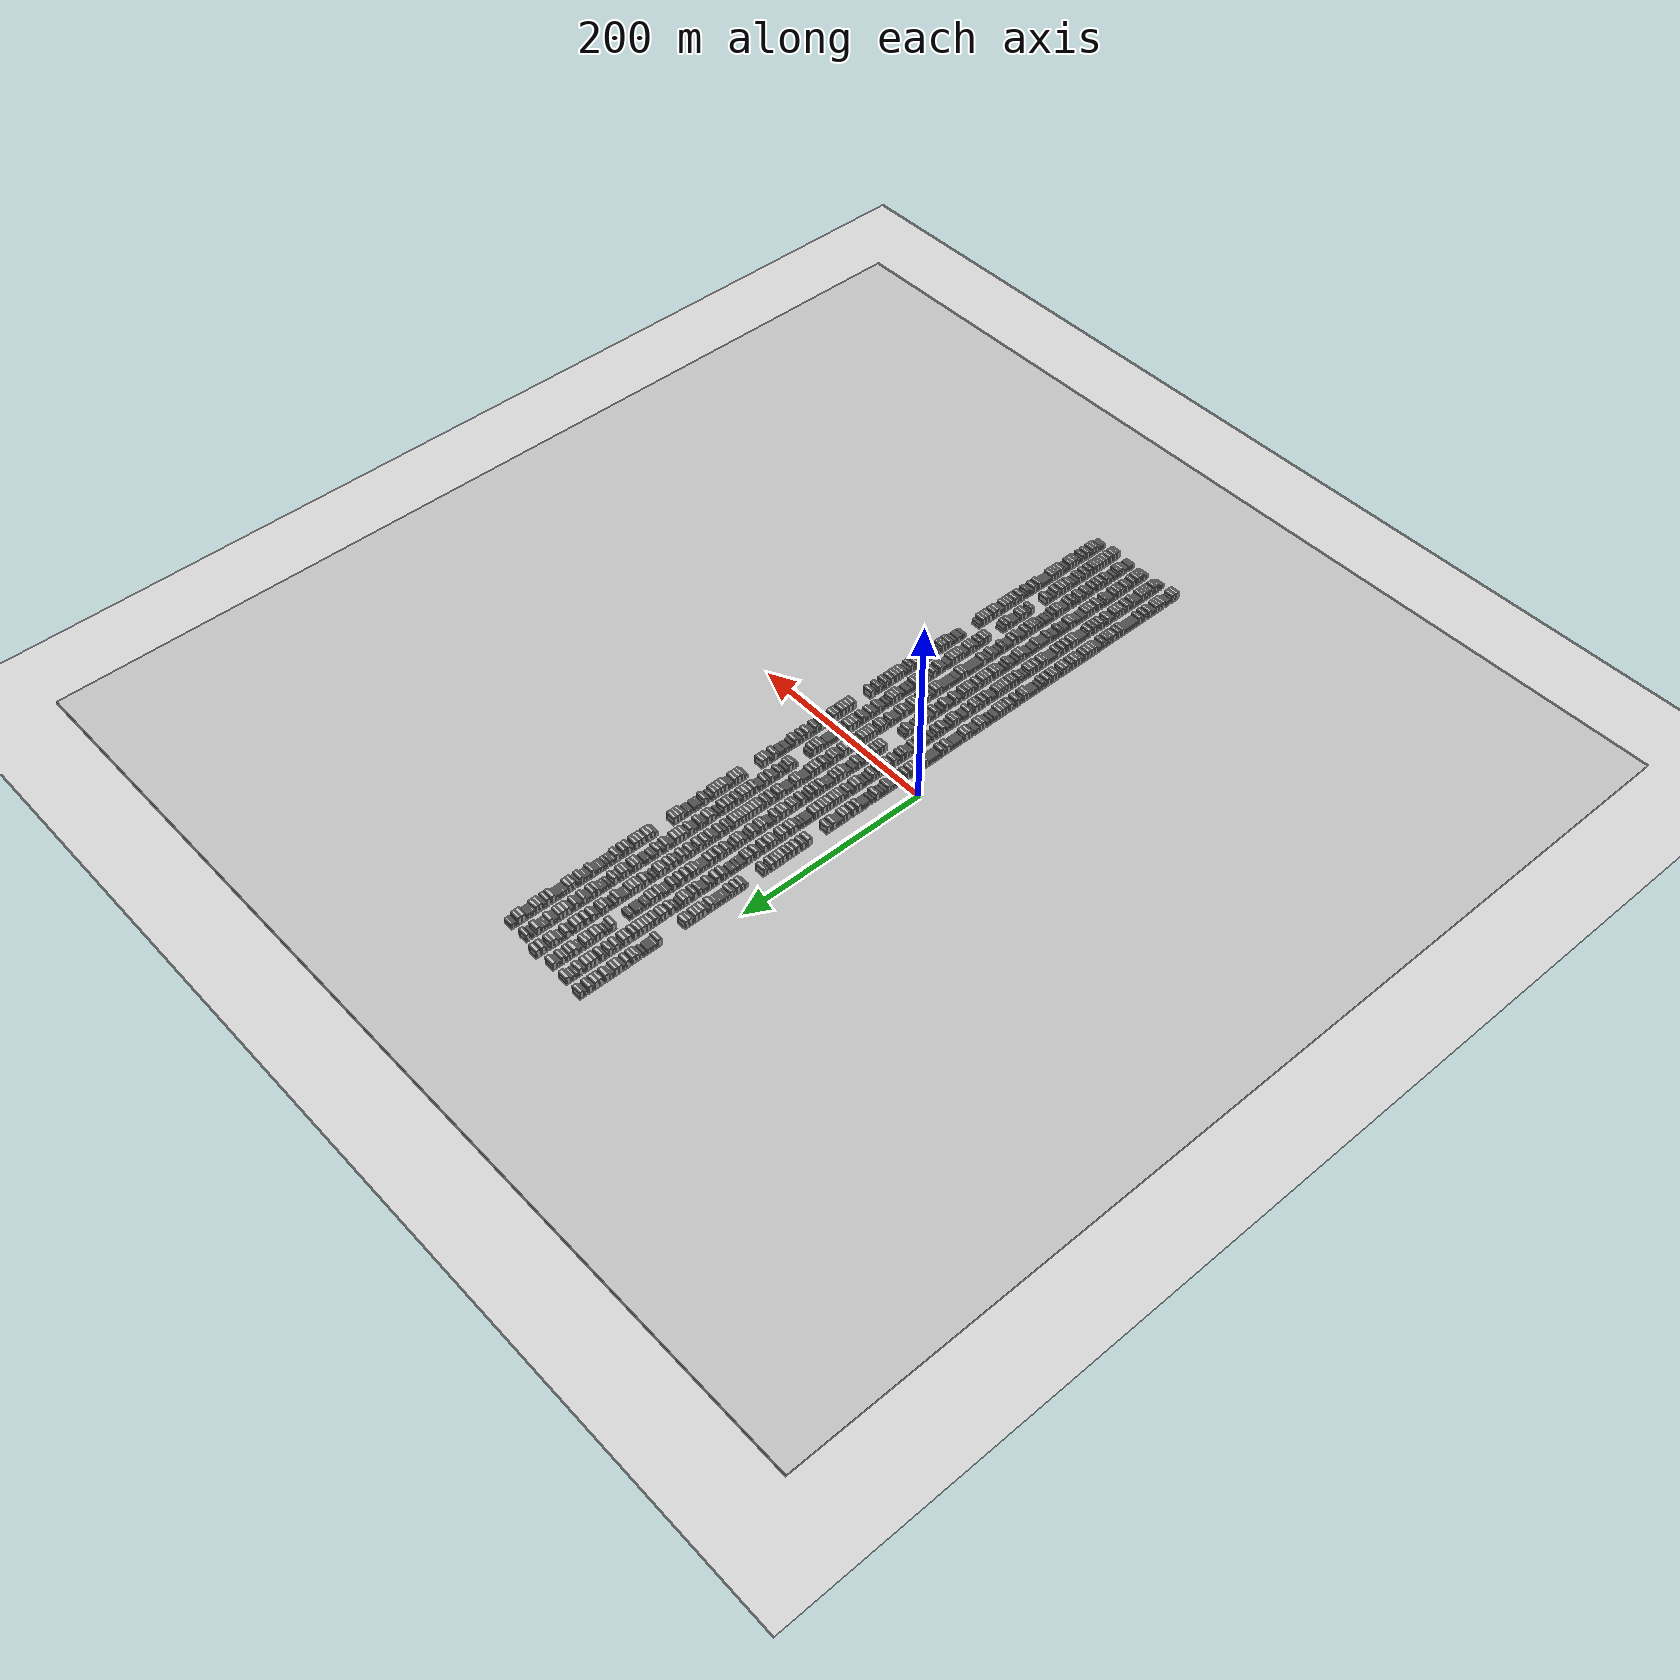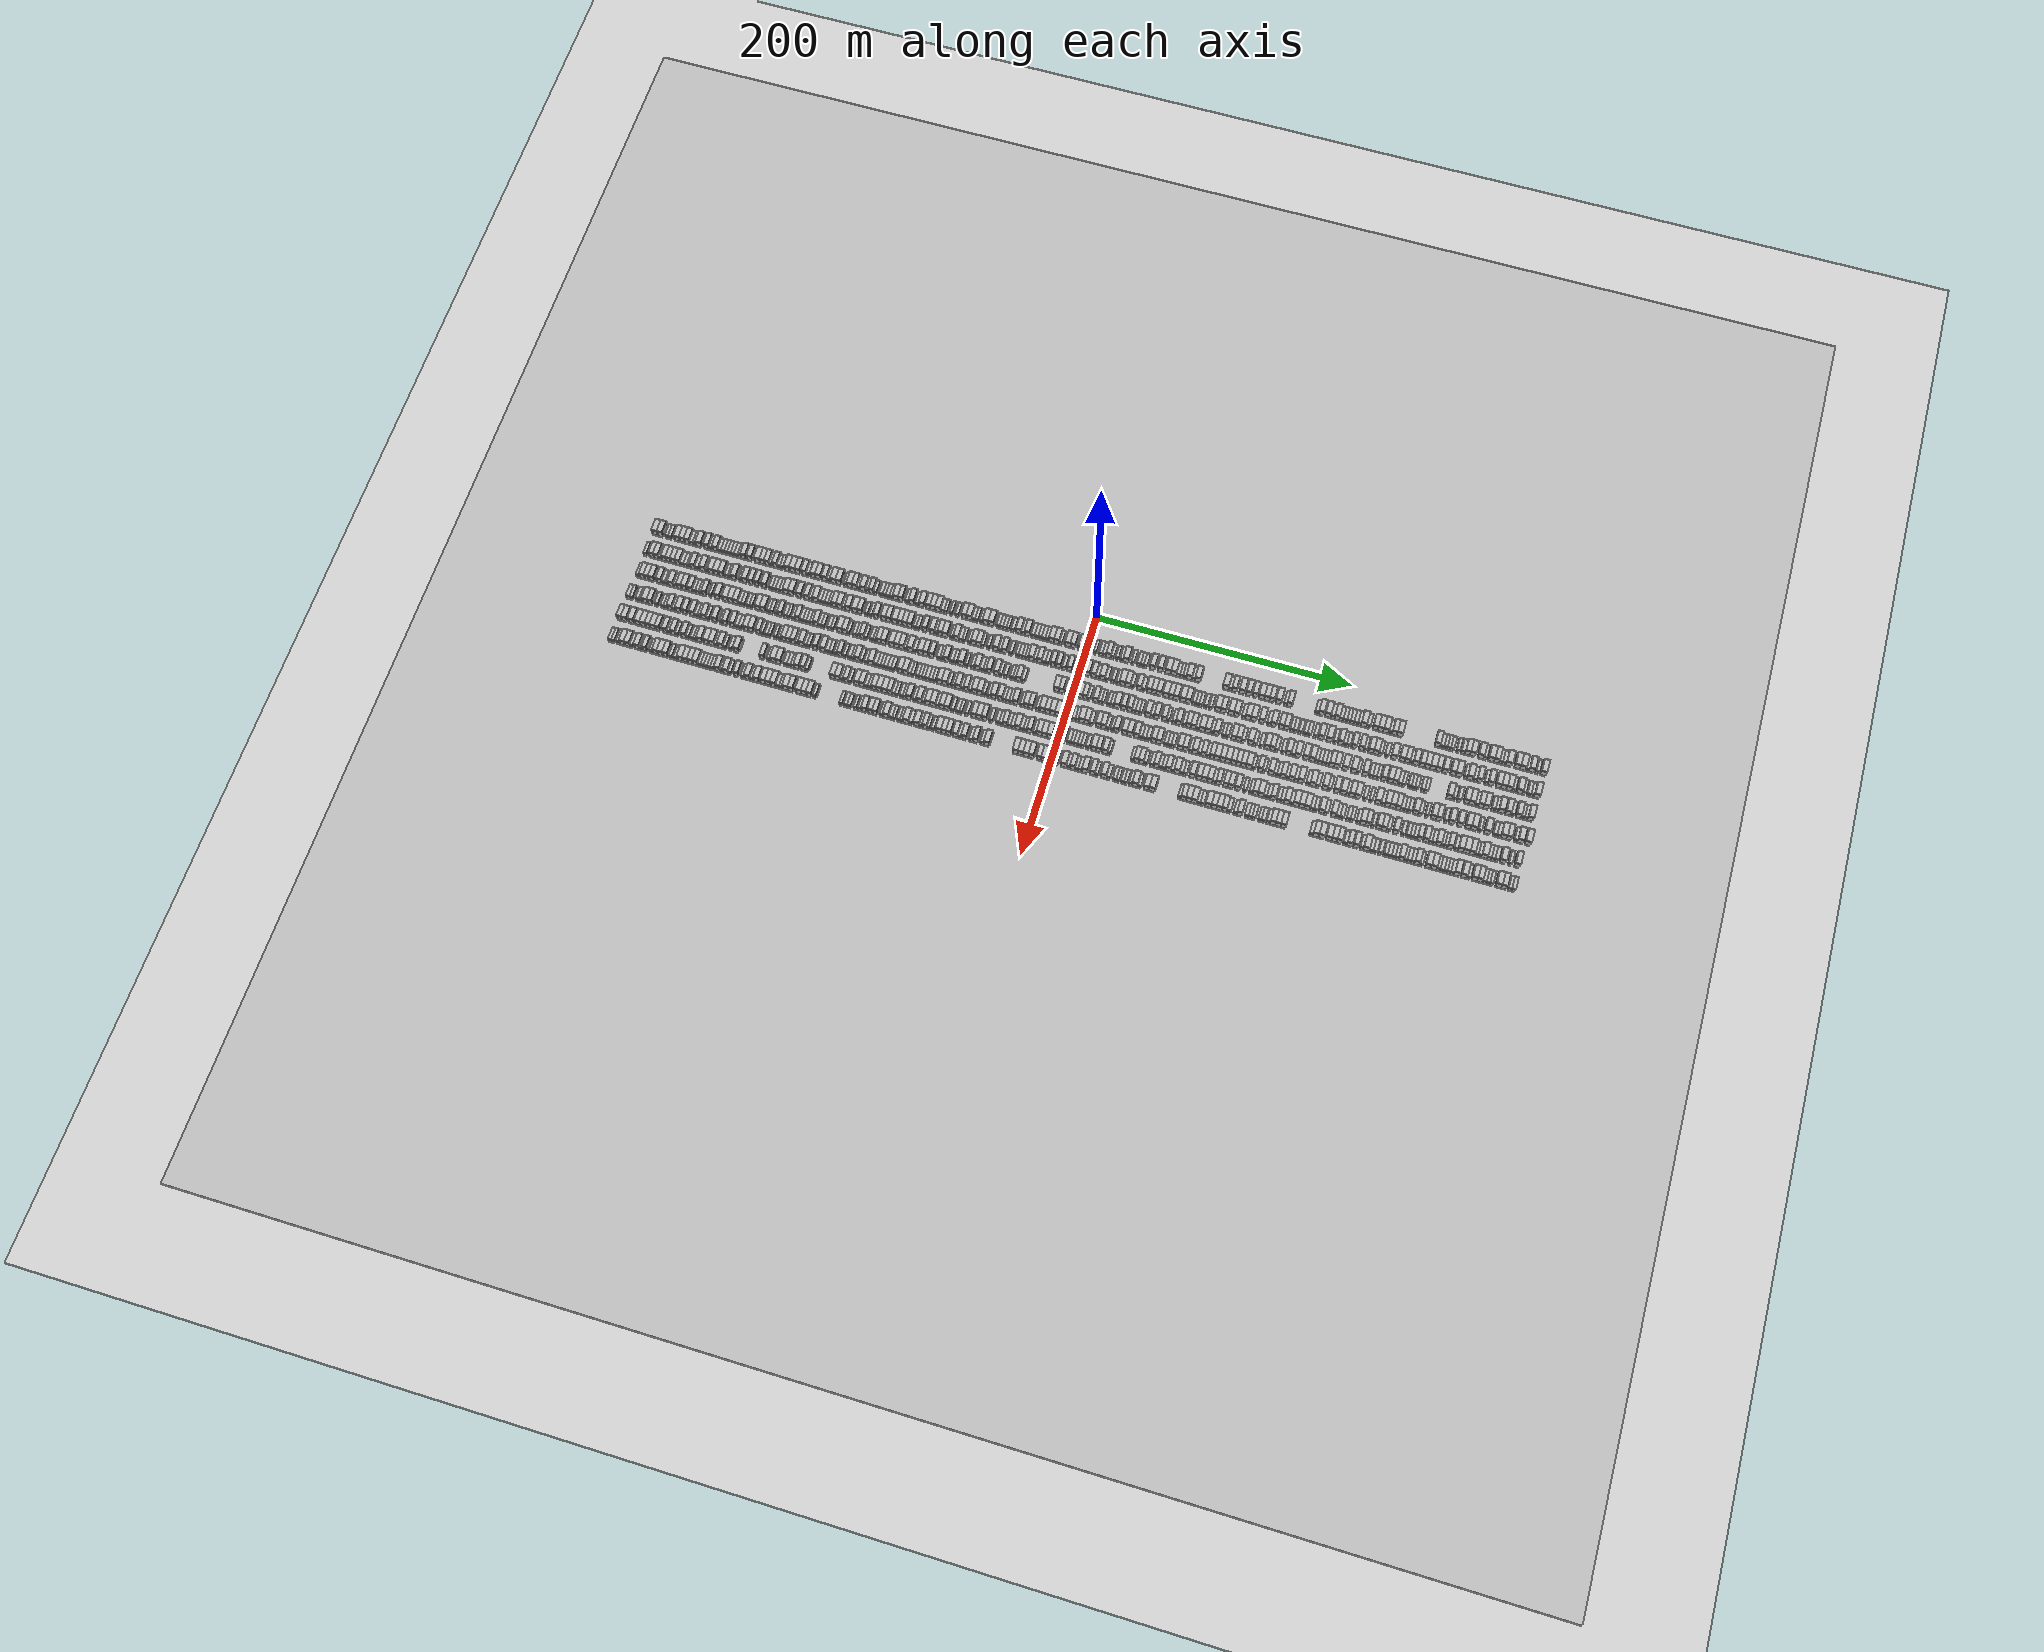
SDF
<?xml version="1.0" encoding="utf-8"?>

<sdf version="1.6">

   <world name="default">

      <gui fullscreen="0">

         <camera name="user_camera">

            <pose>-15 0 4.57585 0 0 0</pose>

            <view_controller>orbit</view_controller>

         </camera>

      </gui>

      <scene>

         <sky>

           <clouds>

             <speed>12</speed>

           </clouds>

         </sky>

         <ambient>0.4 0.4 0.4 1</ambient>

         <background>0.7 0.7 0.7 1</background>

         <shadows>1</shadows>

      </scene>

      <gravity>0 0 -9.8066</gravity>

      <magnetic_field>6e-06 2.3e-05 -4.2e-05</magnetic_field>

      <physics default="0" name="default_physics" type="ode">

         <ode>

            <solver>

               <type>quick</type>

               <iters>10</iters>

               <sor>1.0</sor>

               <use_dynamic_moi_rescaling>0</use_dynamic_moi_rescaling>

            </solver>

            <constraints>

               <cfm>0</cfm>

               <erp>0.2</erp>

               <contact_max_correcting_vel>100</contact_max_correcting_vel>

               <contact_surface_layer>0.001</contact_surface_layer>

            </constraints>

         </ode>

         <max_step_size>0.004</max_step_size>

         <real_time_factor>1</real_time_factor>

         <real_time_update_rate>250</real_time_update_rate>

      </physics>

      <light name="sun" type="directional">

         <cast_shadows>1</cast_shadows>

         <pose>0 0 10 0 0 0</pose>

         <diffuse>0.8 0.8 0.8 1</diffuse>

         <specular>0.2 0.2 0.2 1</specular>

         <attenuation>

            <range>1000</range>

            <constant>0.9</constant>

            <linear>0.01</linear>

            <quadratic>0.001</quadratic>

         </attenuation>

         <direction>-0.5 0.1 -0.9</direction>

      </light>

      <include>

         <name>ground_plane_1</name>

         <uri>model://HANNAS_ground_plane</uri>

         <pose>0 0 0  0 0 0</pose>

      </include>

      <include>

         <name>ground_plane_2</name>

         <uri>model://HANNAS_ground_plane</uri>

         <pose>100 0 0  0 0 0</pose>

      </include>

      <model name="building_1">

         <static>1</static>

         <pose frame="">25.0000 -347.8435 0 0.000000 0.000000 0.000000</pose>

         <link name="link">

            <pose frame="">0 0 4.50 0 0 0</pose>

            <collision name="collision">

               <geometry>

                  <box>

                     <size>10.0000 4.3130 9.0000</size>

                  </box>

               </geometry>

               <max_contacts>10</max_contacts>

               <surface>

                  <contact>

                     <ode/>

                  </contact>

                  <bounce/>

                  <friction>

                     <torsional>

                        <ode/>

                     </torsional>

                     <ode/>

                  </friction>

               </surface>

            </collision>

            <visual name="visual">

               <cast_shadows>0</cast_shadows>

               <geometry>

                  <box>

                     <size>10.0000 4.3130 9.0000</size>

                  </box>

               </geometry>

               <material>

                  <script>

                     <uri>model://HANNAS_wall/materials/scripts</uri>

                     <uri>model://HANNAS_wall/materials/textures</uri>

                     <name>vrc/HANNAS_wall</name>

                  </script>

               </material>

            </visual>

            <self_collide>0</self_collide>

            <enable_wind>0</enable_wind>

            <kinematic>0</kinematic>

         </link>

      </model>

      <model name="building_2">

         <static>1</static>

         <pose frame="">25.0000 -343.4696 0 0.000000 0.000000 0.000000</pose>

         <link name="link">

            <pose frame="">0 0 4.50 0 0 0</pose>

            <collision name="collision">

               <geometry>

                  <box>

                     <size>10.0000 4.4347 9.0000</size>

                  </box>

               </geometry>

               <max_contacts>10</max_contacts>

               <surface>

                  <contact>

                     <ode/>

                  </contact>

                  <bounce/>

                  <friction>

                     <torsional>

                        <ode/>

                     </torsional>

                     <ode/>

                  </friction>

               </surface>

            </collision>

            <visual name="visual">

               <cast_shadows>0</cast_shadows>

               <geometry>

                  <box>

                     <size>10.0000 4.4347 9.0000</size>

                  </box>

               </geometry>

               <material>

                  <script>

                     <uri>model://HANNAS_wall/materials/scripts</uri>

                     <uri>model://HANNAS_wall/materials/textures</uri>

                     <name>vrc/HANNAS_wall</name>

                  </script>

               </material>

            </visual>

            <self_collide>0</self_collide>

            <enable_wind>0</enable_wind>

            <kinematic>0</kinematic>

         </link>

      </model>

      <model name="building_3">

         <static>1</static>

         <pose frame="">25.0000 -337.9849 0 0.000000 0.000000 0.000000</pose>

         <link name="link">

            <pose frame="">0 0 3.00 0 0 0</pose>

            <collision name="collision">

               <geometry>

                  <box>

                     <size>10.0000 2.5348 6.0000</size>

                  </box>

               </geometry>

               <max_contacts>10</max_contacts>

               <surface>

                  <contact>

                     <ode/>

                  </contact>

                  <bounce/>

                  <friction>

                     <torsional>

                        <ode/>

                     </torsional>

                     <ode/>

                  </friction>

               </surface>

            </collision>

            <visual name="visual">

               <cast_shadows>0</cast_shadows>

               <geometry>

                  <box>

                     <size>10.0000 2.5348 6.0000</size>

                  </box>

               </geometry>

               <material>

                  <script>

                     <uri>model://HANNAS_wall/materials/scripts</uri>

                     <uri>model://HANNAS_wall/materials/textures</uri>

                     <name>vrc/HANNAS_wall</name>

                  </script>

               </material>

            </visual>

            <self_collide>0</self_collide>

            <enable_wind>0</enable_wind>

            <kinematic>0</kinematic>

         </link>

      </model>

      <model name="building_4">

         <static>1</static>

         <pose frame="">25.0000 -335.3379 0 0.000000 0.000000 0.000000</pose>

         <link name="link">

            <pose frame="">0 0 3.00 0 0 0</pose>

            <collision name="collision">

               <geometry>

                  <box>

                     <size>10.0000 2.7592 6.0000</size>

                  </box>

               </geometry>

               <max_contacts>10</max_contacts>

               <surface>

                  <contact>

                     <ode/>

                  </contact>

                  <bounce/>

                  <friction>

                     <torsional>

                        <ode/>

                     </torsional>

                     <ode/>

                  </friction>

               </surface>

            </collision>

            <visual name="visual">

               <cast_shadows>0</cast_shadows>

               <geometry>

                  <box>

                     <size>10.0000 2.7592 6.0000</size>

                  </box>

               </geometry>

               <material>

                  <script>

                     <uri>model://HANNAS_wall/materials/scripts</uri>

                     <uri>model://HANNAS_wall/materials/textures</uri>

                     <name>vrc/HANNAS_wall</name>

                  </script>

               </material>

            </visual>

            <self_collide>0</self_collide>

            <enable_wind>0</enable_wind>

            <kinematic>0</kinematic>

         </link>

      </model>

      <model name="building_5">

         <static>1</static>

         <pose frame="">25.0000 -329.7771 0 0.000000 0.000000 0.000000</pose>

         <link name="link">

            <pose frame="">0 0 4.50 0 0 0</pose>

            <collision name="collision">

               <geometry>

                  <box>

                     <size>10.0000 4.3623 9.0000</size>

                  </box>

               </geometry>

               <max_contacts>10</max_contacts>

               <surface>

                  <contact>

                     <ode/>

                  </contact>

                  <bounce/>

                  <friction>

                     <torsional>

                        <ode/>

                     </torsional>

                     <ode/>

                  </friction>

               </surface>

            </collision>

            <visual name="visual">

               <cast_shadows>0</cast_shadows>

               <geometry>

                  <box>

                     <size>10.0000 4.3623 9.0000</size>

                  </box>

               </geometry>

               <material>

                  <script>

                     <uri>model://HANNAS_wall/materials/scripts</uri>

                     <uri>model://HANNAS_wall/materials/textures</uri>

                     <name>vrc/HANNAS_wall</name>

                  </script>

               </material>

            </visual>

            <self_collide>0</self_collide>

            <enable_wind>0</enable_wind>

            <kinematic>0</kinematic>

         </link>

      </model>

      <model name="building_6">

         <static>1</static>

         <pose frame="">25.0000 -325.5495 0 0.000000 0.000000 0.000000</pose>

         <link name="link">

            <pose frame="">0 0 4.50 0 0 0</pose>

            <collision name="collision">

               <geometry>

                  <box>

                     <size>10.0000 4.0929 9.0000</size>

                  </box>

               </geometry>

               <max_contacts>10</max_contacts>

               <surface>

                  <contact>

                     <ode/>

                  </contact>

                  <bounce/>

                  <friction>

                     <torsional>

                        <ode/>

                     </torsional>

                     <ode/>

                  </friction>

               </surface>

            </collision>

            <visual name="visual">

               <cast_shadows>0</cast_shadows>

               <geometry>

                  <box>

                     <size>10.0000 4.0929 9.0000</size>

                  </box>

               </geometry>

               <material>

                  <script>

                     <uri>model://HANNAS_wall/materials/scripts</uri>

                     <uri>model://HANNAS_wall/materials/textures</uri>

                     <name>vrc/HANNAS_wall</name>

                  </script>

               </material>

            </visual>

            <self_collide>0</self_collide>

            <enable_wind>0</enable_wind>

            <kinematic>0</kinematic>

         </link>

      </model>

      <model name="building_7">

         <static>1</static>

         <pose frame="">25.0000 -321.4520 0 0.000000 0.000000 0.000000</pose>

         <link name="link">

            <pose frame="">0 0 4.50 0 0 0</pose>

            <collision name="collision">

               <geometry>

                  <box>

                     <size>10.0000 4.1020 9.0000</size>

                  </box>

               </geometry>

               <max_contacts>10</max_contacts>

               <surface>

                  <contact>

                     <ode/>

                  </contact>

                  <bounce/>

                  <friction>

                     <torsional>

                        <ode/>

                     </torsional>

                     <ode/>

                  </friction>

               </surface>

            </collision>

            <visual name="visual">

               <cast_shadows>0</cast_shadows>

               <geometry>

                  <box>

                     <size>10.0000 4.1020 9.0000</size>

                  </box>

               </geometry>

               <material>

                  <script>

                     <uri>model://HANNAS_wall/materials/scripts</uri>

                     <uri>model://HANNAS_wall/materials/textures</uri>

                     <name>vrc/HANNAS_wall</name>

                  </script>

               </material>

            </visual>

            <self_collide>0</self_collide>

            <enable_wind>0</enable_wind>

            <kinematic>0</kinematic>

         </link>

      </model>

      <model name="building_8">

         <static>1</static>

         <pose frame="">25.0000 -317.9969 0 0.000000 0.000000 0.000000</pose>

         <link name="link">

            <pose frame="">0 0 3.00 0 0 0</pose>

            <collision name="collision">

               <geometry>

                  <box>

                     <size>10.0000 2.8083 6.0000</size>

                  </box>

               </geometry>

               <max_contacts>10</max_contacts>

               <surface>

                  <contact>

                     <ode/>

                  </contact>

                  <bounce/>

                  <friction>

                     <torsional>

                        <ode/>

                     </torsional>

                     <ode/>

                  </friction>

               </surface>

            </collision>

            <visual name="visual">

               <cast_shadows>0</cast_shadows>

               <geometry>

                  <box>

                     <size>10.0000 2.8083 6.0000</size>

                  </box>

               </geometry>

               <material>

                  <script>

                     <uri>model://HANNAS_wall/materials/scripts</uri>

                     <uri>model://HANNAS_wall/materials/textures</uri>

                     <name>vrc/HANNAS_wall</name>

                  </script>

               </material>

            </visual>

            <self_collide>0</self_collide>

            <enable_wind>0</enable_wind>

            <kinematic>0</kinematic>

         </link>

      </model>

      <model name="building_9">

         <static>1</static>

         <pose frame="">25.0000 -315.3332 0 0.000000 0.000000 0.000000</pose>

         <link name="link">

            <pose frame="">0 0 3.00 0 0 0</pose>

            <collision name="collision">

               <geometry>

                  <box>

                     <size>10.0000 2.5191 6.0000</size>

                  </box>

               </geometry>

               <max_contacts>10</max_contacts>

               <surface>

                  <contact>

                     <ode/>

                  </contact>

                  <bounce/>

                  <friction>

                     <torsional>

                        <ode/>

                     </torsional>

                     <ode/>

                  </friction>

               </surface>

            </collision>

            <visual name="visual">

               <cast_shadows>0</cast_shadows>

               <geometry>

                  <box>

                     <size>10.0000 2.5191 6.0000</size>

                  </box>

               </geometry>

               <material>

                  <script>

                     <uri>model://HANNAS_wall/materials/scripts</uri>

                     <uri>model://HANNAS_wall/materials/textures</uri>

                     <name>vrc/HANNAS_wall</name>

                  </script>

               </material>

            </visual>

            <self_collide>0</self_collide>

            <enable_wind>0</enable_wind>

            <kinematic>0</kinematic>

         </link>

      </model>

      <model name="building_10">

         <static>1</static>

         <pose frame="">25.0000 -311.8450 0 0.000000 0.000000 0.000000</pose>

         <link name="link">

            <pose frame="">0 0 4.50 0 0 0</pose>

            <collision name="collision">

               <geometry>

                  <box>

                     <size>10.0000 4.4574 9.0000</size>

                  </box>

               </geometry>

               <max_contacts>10</max_contacts>

               <surface>

                  <contact>

                     <ode/>

                  </contact>

                  <bounce/>

                  <friction>

                     <torsional>

                        <ode/>

                     </torsional>

                     <ode/>

                  </friction>

               </surface>

            </collision>

            <visual name="visual">

               <cast_shadows>0</cast_shadows>

               <geometry>

                  <box>

                     <size>10.0000 4.4574 9.0000</size>

                  </box>

               </geometry>

               <material>

                  <script>

                     <uri>model://HANNAS_wall/materials/scripts</uri>

                     <uri>model://HANNAS_wall/materials/textures</uri>

                     <name>vrc/HANNAS_wall</name>

                  </script>

               </material>

            </visual>

            <self_collide>0</self_collide>

            <enable_wind>0</enable_wind>

            <kinematic>0</kinematic>

         </link>

      </model>

      <model name="building_11">

         <static>1</static>

         <pose frame="">25.0000 -305.5837 0 0.000000 0.000000 0.000000</pose>

         <link name="link">

            <pose frame="">0 0 4.50 0 0 0</pose>

            <collision name="collision">

               <geometry>

                  <box>

                     <size>10.0000 4.0651 9.0000</size>

                  </box>

               </geometry>

               <max_contacts>10</max_contacts>

               <surface>

                  <contact>

                     <ode/>

                  </contact>

                  <bounce/>

                  <friction>

                     <torsional>

                        <ode/>

                     </torsional>

                     <ode/>

                  </friction>

               </surface>

            </collision>

            <visual name="visual">

               <cast_shadows>0</cast_shadows>

               <geometry>

                  <box>

                     <size>10.0000 4.0651 9.0000</size>

                  </box>

               </geometry>

               <material>

                  <script>

                     <uri>model://HANNAS_wall/materials/scripts</uri>

                     <uri>model://HANNAS_wall/materials/textures</uri>

                     <name>vrc/HANNAS_wall</name>

                  </script>

               </material>

            </visual>

            <self_collide>0</self_collide>

            <enable_wind>0</enable_wind>

            <kinematic>0</kinematic>

         </link>

      </model>

      <model name="building_12">

         <static>1</static>

         <pose frame="">25.0000 -302.0708 0 0.000000 0.000000 0.000000</pose>

         <link name="link">

            <pose frame="">0 0 3.00 0 0 0</pose>

            <collision name="collision">

               <geometry>

                  <box>

                     <size>10.0000 2.9608 6.0000</size>

                  </box>

               </geometry>

               <max_contacts>10</max_contacts>

               <surface>

                  <contact>

                     <ode/>

                  </contact>

                  <bounce/>

                  <friction>

                     <torsional>

                        <ode/>

                     </torsional>

                     <ode/>

                  </friction>

               </surface>

            </collision>

            <visual name="visual">

               <cast_shadows>0</cast_shadows>

               <geometry>

                  <box>

                     <size>10.0000 2.9608 6.0000</size>

                  </box>

               </geometry>

               <material>

                  <script>

                     <uri>model://HANNAS_wall/materials/scripts</uri>

                     <uri>model://HANNAS_wall/materials/textures</uri>

                     <name>vrc/HANNAS_wall</name>

                  </script>

               </material>

            </visual>

            <self_collide>0</self_collide>

            <enable_wind>0</enable_wind>

            <kinematic>0</kinematic>

         </link>

      </model>

      <model name="building_13">

         <static>1</static>

         <pose frame="">25.0000 -298.5053 0 0.000000 0.000000 0.000000</pose>

         <link name="link">

            <pose frame="">0 0 4.50 0 0 0</pose>

            <collision name="collision">

               <geometry>

                  <box>

                     <size>10.0000 4.1703 9.0000</size>

                  </box>

               </geometry>

               <max_contacts>10</max_contacts>

               <surface>

                  <contact>

                     <ode/>

                  </contact>

                  <bounce/>

                  <friction>

                     <torsional>

                        <ode/>

                     </torsional>

                     <ode/>

                  </friction>

               </surface>

            </collision>

            <visual name="visual">

               <cast_shadows>0</cast_shadows>

               <geometry>

                  <box>

                     <size>10.0000 4.1703 9.0000</size>

                  </box>

               </geometry>

               <material>

                  <script>

                     <uri>model://HANNAS_wall/materials/scripts</uri>

                     <uri>model://HANNAS_wall/materials/textures</uri>

                     <name>vrc/HANNAS_wall</name>

                  </script>

               </material>

            </visual>

            <self_collide>0</self_collide>

            <enable_wind>0</enable_wind>

            <kinematic>0</kinematic>

         </link>

      </model>

      <model name="building_14">

         <static>1</static>

         <pose frame="">25.0000 -294.9755 0 0.000000 0.000000 0.000000</pose>

         <link name="link">

            <pose frame="">0 0 3.00 0 0 0</pose>

            <collision name="collision">

               <geometry>

                  <box>

                     <size>10.0000 2.8892 6.0000</size>

                  </box>

               </geometry>

               <max_contacts>10</max_contacts>

               <surface>

                  <contact>

                     <ode/>

                  </contact>

                  <bounce/>

                  <friction>

                     <torsional>

                        <ode/>

                     </torsional>

                     <ode/>

                  </friction>

               </surface>

            </collision>

            <visual name="visual">

               <cast_shadows>0</cast_shadows>

               <geometry>

                  <box>

                     <size>10.0000 2.8892 6.0000</size>

                  </box>

               </geometry>

               <material>

                  <script>

                     <uri>model://HANNAS_wall/materials/scripts</uri>

                     <uri>model://HANNAS_wall/materials/textures</uri>

                     <name>vrc/HANNAS_wall</name>

                  </script>

               </material>

            </visual>

            <self_collide>0</self_collide>

            <enable_wind>0</enable_wind>

            <kinematic>0</kinematic>

         </link>

      </model>

      <model name="building_15">

         <static>1</static>

         <pose frame="">25.0000 -292.1879 0 0.000000 0.000000 0.000000</pose>

         <link name="link">

            <pose frame="">0 0 3.00 0 0 0</pose>

            <collision name="collision">

               <geometry>

                  <box>

                     <size>10.0000 2.6861 6.0000</size>

                  </box>

               </geometry>

               <max_contacts>10</max_contacts>

               <surface>

                  <contact>

                     <ode/>

                  </contact>

                  <bounce/>

                  <friction>

                     <torsional>

                        <ode/>

                     </torsional>

                     <ode/>

                  </friction>

               </surface>

            </collision>

            <visual name="visual">

               <cast_shadows>0</cast_shadows>

               <geometry>

                  <box>

                     <size>10.0000 2.6861 6.0000</size>

                  </box>

               </geometry>

               <material>

                  <script>

                     <uri>model://HANNAS_wall/materials/scripts</uri>

                     <uri>model://HANNAS_wall/materials/textures</uri>

                     <name>vrc/HANNAS_wall</name>

                  </script>

               </material>

            </visual>

            <self_collide>0</self_collide>

            <enable_wind>0</enable_wind>

            <kinematic>0</kinematic>

         </link>

      </model>

      <model name="building_16">

         <static>1</static>

         <pose frame="">25.0000 -289.5821 0 0.000000 0.000000 0.000000</pose>

         <link name="link">

            <pose frame="">0 0 3.00 0 0 0</pose>

            <collision name="collision">

               <geometry>

                  <box>

                     <size>10.0000 2.5253 6.0000</size>

                  </box>

               </geometry>

               <max_contacts>10</max_contacts>

               <surface>

                  <contact>

                     <ode/>

                  </contact>

                  <bounce/>

                  <friction>

                     <torsional>

                        <ode/>

                     </torsional>

                     <ode/>

                  </friction>

               </surface>

            </collision>

            <visual name="visual">

               <cast_shadows>0</cast_shadows>

               <geometry>

                  <box>

                     <size>10.0000 2.5253 6.0000</size>

                  </box>

               </geometry>

               <material>

                  <script>

                     <uri>model://HANNAS_wall/materials/scripts</uri>

                     <uri>model://HANNAS_wall/materials/textures</uri>

                     <name>vrc/HANNAS_wall</name>

                  </script>

               </material>

            </visual>

            <self_collide>0</self_collide>

            <enable_wind>0</enable_wind>

            <kinematic>0</kinematic>

         </link>

      </model>

      <model name="building_17">

         <static>1</static>

         <pose frame="">25.0000 -286.9411 0 0.000000 0.000000 0.000000</pose>

         <link name="link">

            <pose frame="">0 0 3.00 0 0 0</pose>

            <collision name="collision">

               <geometry>

                  <box>

                     <size>10.0000 2.7568 6.0000</size>

                  </box>

               </geometry>

               <max_contacts>10</max_contacts>

               <surface>

                  <contact>

                     <ode/>

                  </contact>

                  <bounce/>

                  <friction>

                     <torsional>

                        <ode/>

                     </torsional>

                     <ode/>

                  </friction>

               </surface>

            </collision>

            <visual name="visual">

               <cast_shadows>0</cast_shadows>

               <geometry>

                  <box>

                     <size>10.0000 2.7568 6.0000</size>

                  </box>

               </geometry>

               <material>

                  <script>

                     <uri>model://HANNAS_wall/materials/scripts</uri>

                     <uri>model://HANNAS_wall/materials/textures</uri>

                     <name>vrc/HANNAS_wall</name>

                  </script>

               </material>

            </visual>

            <self_collide>0</self_collide>

            <enable_wind>0</enable_wind>

            <kinematic>0</kinematic>

         </link>

      </model>

      <model name="building_18">

         <static>1</static>

         <pose frame="">25.0000 -284.1913 0 0.000000 0.000000 0.000000</pose>

         <link name="link">

            <pose frame="">0 0 3.00 0 0 0</pose>

            <collision name="collision">

               <geometry>

                  <box>

                     <size>10.0000 2.7428 6.0000</size>

                  </box>

               </geometry>

               <max_contacts>10</max_contacts>

               <surface>

                  <contact>

                     <ode/>

                  </contact>

                  <bounce/>

                  <friction>

                     <torsional>

                        <ode/>

                     </torsional>

                     <ode/>

                  </friction>

               </surface>

            </collision>

            <visual name="visual">

               <cast_shadows>0</cast_shadows>

               <geometry>

                  <box>

                     <size>10.0000 2.7428 6.0000</size>

                  </box>

               </geometry>

               <material>

                  <script>

                     <uri>model://HANNAS_wall/materials/scripts</uri>

                     <uri>model://HANNAS_wall/materials/textures</uri>

                     <name>vrc/HANNAS_wall</name>

                  </script>

               </material>

            </visual>

            <self_collide>0</self_collide>

            <enable_wind>0</enable_wind>

            <kinematic>0</kinematic>

         </link>

      </model>

      <model name="building_19">

         <static>1</static>

         <pose frame="">25.0000 -281.3882 0 0.000000 0.000000 0.000000</pose>

         <link name="link">

            <pose frame="">0 0 3.00 0 0 0</pose>

            <collision name="collision">

               <geometry>

                  <box>

                     <size>10.0000 2.8634 6.0000</size>

                  </box>

               </geometry>

               <max_contacts>10</max_contacts>

               <surface>

                  <contact>

                     <ode/>

                  </contact>

                  <bounce/>

                  <friction>

                     <torsional>

                        <ode/>

                     </torsional>

                     <ode/>

                  </friction>

               </surface>

            </collision>

            <visual name="visual">

               <cast_shadows>0</cast_shadows>

               <geometry>

                  <box>

                     <size>10.0000 2.8634 6.0000</size>

                  </box>

               </geometry>

               <material>

                  <script>

                     <uri>model://HANNAS_wall/materials/scripts</uri>

                     <uri>model://HANNAS_wall/materials/textures</uri>

                     <name>vrc/HANNAS_wall</name>

                  </script>

               </material>

            </visual>

            <self_collide>0</self_collide>

            <enable_wind>0</enable_wind>

            <kinematic>0</kinematic>

         </link>

      </model>

      <model name="building_20">

         <static>1</static>

         <pose frame="">25.0000 -278.7010 0 0.000000 0.000000 0.000000</pose>

         <link name="link">

            <pose frame="">0 0 3.00 0 0 0</pose>

            <collision name="collision">

               <geometry>

                  <box>

                     <size>10.0000 2.5111 6.0000</size>

                  </box>

               </geometry>

               <max_contacts>10</max_contacts>

               <surface>

                  <contact>

                     <ode/>

                  </contact>

                  <bounce/>

                  <friction>

                     <torsional>

                        <ode/>

                     </torsional>

                     <ode/>

                  </friction>

               </surface>

            </collision>

            <visual name="visual">

               <cast_shadows>0</cast_shadows>

               <geometry>

                  <box>

                     <size>10.0000 2.5111 6.0000</size>

                  </box>

               </geometry>

               <material>

                  <script>

                     <uri>model://HANNAS_wall/materials/scripts</uri>

                     <uri>model://HANNAS_wall/materials/textures</uri>

                     <name>vrc/HANNAS_wall</name>

                  </script>

               </material>

            </visual>

            <self_collide>0</self_collide>

            <enable_wind>0</enable_wind>

            <kinematic>0</kinematic>

         </link>

      </model>

      <model name="building_21">

         <static>1</static>

         <pose frame="">25.0000 -275.4317 0 0.000000 0.000000 0.000000</pose>

         <link name="link">

            <pose frame="">0 0 4.50 0 0 0</pose>

            <collision name="collision">

               <geometry>

                  <box>

                     <size>10.0000 4.0274 9.0000</size>

                  </box>

               </geometry>

               <max_contacts>10</max_contacts>

               <surface>

                  <contact>

                     <ode/>

                  </contact>

                  <bounce/>

                  <friction>

                     <torsional>

                        <ode/>

                     </torsional>

                     <ode/>

                  </friction>

               </surface>

            </collision>

            <visual name="visual">

               <cast_shadows>0</cast_shadows>

               <geometry>

                  <box>

                     <size>10.0000 4.0274 9.0000</size>

                  </box>

               </geometry>

               <material>

                  <script>

                     <uri>model://HANNAS_wall/materials/scripts</uri>

                     <uri>model://HANNAS_wall/materials/textures</uri>

                     <name>vrc/HANNAS_wall</name>

                  </script>

               </material>

            </visual>

            <self_collide>0</self_collide>

            <enable_wind>0</enable_wind>

            <kinematic>0</kinematic>

         </link>

      </model>

      <model name="building_22">

         <static>1</static>

         <pose frame="">25.0000 -270.3757 0 0.000000 0.000000 0.000000</pose>

         <link name="link">

            <pose frame="">0 0 4.50 0 0 0</pose>

            <collision name="collision">

               <geometry>

                  <box>

                     <size>10.0000 4.0847 9.0000</size>

                  </box>

               </geometry>

               <max_contacts>10</max_contacts>

               <surface>

                  <contact>

                     <ode/>

                  </contact>

                  <bounce/>

                  <friction>

                     <torsional>

                        <ode/>

                     </torsional>

                     <ode/>

                  </friction>

               </surface>

            </collision>

            <visual name="visual">

               <cast_shadows>0</cast_shadows>

               <geometry>

                  <box>

                     <size>10.0000 4.0847 9.0000</size>

                  </box>

               </geometry>

               <material>

                  <script>

                     <uri>model://HANNAS_wall/materials/scripts</uri>

                     <uri>model://HANNAS_wall/materials/textures</uri>

                     <name>vrc/HANNAS_wall</name>

                  </script>

               </material>

            </visual>

            <self_collide>0</self_collide>

            <enable_wind>0</enable_wind>

            <kinematic>0</kinematic>

         </link>

      </model>

      <model name="building_23">

         <static>1</static>

         <pose frame="">25.0000 -264.0987 0 0.000000 0.000000 0.000000</pose>

         <link name="link">

            <pose frame="">0 0 4.50 0 0 0</pose>

            <collision name="collision">

               <geometry>

                  <box>

                     <size>10.0000 4.4692 9.0000</size>

                  </box>

               </geometry>

               <max_contacts>10</max_contacts>

               <surface>

                  <contact>

                     <ode/>

                  </contact>

                  <bounce/>

                  <friction>

                     <torsional>

                        <ode/>

                     </torsional>

                     <ode/>

                  </friction>

               </surface>

            </collision>

            <visual name="visual">

               <cast_shadows>0</cast_shadows>

               <geometry>

                  <box>

                     <size>10.0000 4.4692 9.0000</size>

                  </box>

               </geometry>

               <material>

                  <script>

                     <uri>model://HANNAS_wall/materials/scripts</uri>

                     <uri>model://HANNAS_wall/materials/textures</uri>

                     <name>vrc/HANNAS_wall</name>

                  </script>

               </material>

            </visual>

            <self_collide>0</self_collide>

            <enable_wind>0</enable_wind>

            <kinematic>0</kinematic>

         </link>

      </model>

      <model name="building_24">

         <static>1</static>

         <pose frame="">25.0000 -260.0332 0 0.000000 0.000000 0.000000</pose>

         <link name="link">

            <pose frame="">0 0 4.50 0 0 0</pose>

            <collision name="collision">

               <geometry>

                  <box>

                     <size>10.0000 3.6618 9.0000</size>

                  </box>

               </geometry>

               <max_contacts>10</max_contacts>

               <surface>

                  <contact>

                     <ode/>

                  </contact>

                  <bounce/>

                  <friction>

                     <torsional>

                        <ode/>

                     </torsional>

                     <ode/>

                  </friction>

               </surface>

            </collision>

            <visual name="visual">

               <cast_shadows>0</cast_shadows>

               <geometry>

                  <box>

                     <size>10.0000 3.6618 9.0000</size>

                  </box>

               </geometry>

               <material>

                  <script>

                     <uri>model://HANNAS_wall/materials/scripts</uri>

                     <uri>model://HANNAS_wall/materials/textures</uri>

                     <name>vrc/HANNAS_wall</name>

                  </script>

               </material>

            </visual>

            <self_collide>0</self_collide>

            <enable_wind>0</enable_wind>

            <kinematic>0</kinematic>

         </link>

      </model>

      <model name="building_25">

         <static>1</static>

         <pose frame="">25.0000 -256.3118 0 0.000000 0.000000 0.000000</pose>

         <link name="link">

            <pose frame="">0 0 4.50 0 0 0</pose>

            <collision name="collision">

               <geometry>

                  <box>

                     <size>10.0000 3.7809 9.0000</size>

                  </box>

               </geometry>

               <max_contacts>10</max_contacts>

               <surface>

                  <contact>

                     <ode/>

                  </contact>

                  <bounce/>

                  <friction>

                     <torsional>

                        <ode/>

                     </torsional>

                     <ode/>

                  </friction>

               </surface>

            </collision>

            <visual name="visual">

               <cast_shadows>0</cast_shadows>

               <geometry>

                  <box>

                     <size>10.0000 3.7809 9.0000</size>

                  </box>

               </geometry>

               <material>

                  <script>

                     <uri>model://HANNAS_wall/materials/scripts</uri>

                     <uri>model://HANNAS_wall/materials/textures</uri>

                     <name>vrc/HANNAS_wall</name>

                  </script>

               </material>

            </visual>

            <self_collide>0</self_collide>

            <enable_wind>0</enable_wind>

            <kinematic>0</kinematic>

         </link>

      </model>

      <model name="building_26">

         <static>1</static>

         <pose frame="">25.0000 -253.0613 0 0.000000 0.000000 0.000000</pose>

         <link name="link">

            <pose frame="">0 0 3.00 0 0 0</pose>

            <collision name="collision">

               <geometry>

                  <box>

                     <size>10.0000 2.7201 6.0000</size>

                  </box>

               </geometry>

               <max_contacts>10</max_contacts>

               <surface>

                  <contact>

                     <ode/>

                  </contact>

                  <bounce/>

                  <friction>

                     <torsional>

                        <ode/>

                     </torsional>

                     <ode/>

                  </friction>

               </surface>

            </collision>

            <visual name="visual">

               <cast_shadows>0</cast_shadows>

               <geometry>

                  <box>

                     <size>10.0000 2.7201 6.0000</size>

                  </box>

               </geometry>

               <material>

                  <script>

                     <uri>model://HANNAS_wall/materials/scripts</uri>

                     <uri>model://HANNAS_wall/materials/textures</uri>

                     <name>vrc/HANNAS_wall</name>

                  </script>

               </material>

            </visual>

            <self_collide>0</self_collide>

            <enable_wind>0</enable_wind>

            <kinematic>0</kinematic>

         </link>

      </model>

      <model name="building_27">

         <static>1</static>

         <pose frame="">25.0000 -249.8507 0 0.000000 0.000000 0.000000</pose>

         <link name="link">

            <pose frame="">0 0 4.50 0 0 0</pose>

            <collision name="collision">

               <geometry>

                  <box>

                     <size>10.0000 3.7010 9.0000</size>

                  </box>

               </geometry>

               <max_contacts>10</max_contacts>

               <surface>

                  <contact>

                     <ode/>

                  </contact>

                  <bounce/>

                  <friction>

                     <torsional>

                        <ode/>

                     </torsional>

                     <ode/>

                  </friction>

               </surface>

            </collision>

            <visual name="visual">

               <cast_shadows>0</cast_shadows>

               <geometry>

                  <box>

                     <size>10.0000 3.7010 9.0000</size>

                  </box>

               </geometry>

               <material>

                  <script>

                     <uri>model://HANNAS_wall/materials/scripts</uri>

                     <uri>model://HANNAS_wall/materials/textures</uri>

                     <name>vrc/HANNAS_wall</name>

                  </script>

               </material>

            </visual>

            <self_collide>0</self_collide>

            <enable_wind>0</enable_wind>

            <kinematic>0</kinematic>

         </link>

      </model>

      <model name="building_28">

         <static>1</static>

         <pose frame="">25.0000 -246.7111 0 0.000000 0.000000 0.000000</pose>

         <link name="link">

            <pose frame="">0 0 3.00 0 0 0</pose>

            <collision name="collision">

               <geometry>

                  <box>

                     <size>10.0000 2.5782 6.0000</size>

                  </box>

               </geometry>

               <max_contacts>10</max_contacts>

               <surface>

                  <contact>

                     <ode/>

                  </contact>

                  <bounce/>

                  <friction>

                     <torsional>

                        <ode/>

                     </torsional>

                     <ode/>

                  </friction>

               </surface>

            </collision>

            <visual name="visual">

               <cast_shadows>0</cast_shadows>

               <geometry>

                  <box>

                     <size>10.0000 2.5782 6.0000</size>

                  </box>

               </geometry>

               <material>

                  <script>

                     <uri>model://HANNAS_wall/materials/scripts</uri>

                     <uri>model://HANNAS_wall/materials/textures</uri>

                     <name>vrc/HANNAS_wall</name>

                  </script>

               </material>

            </visual>

            <self_collide>0</self_collide>

            <enable_wind>0</enable_wind>

            <kinematic>0</kinematic>

         </link>

      </model>

      <model name="building_29">

         <static>1</static>

         <pose frame="">25.0000 -244.1394 0 0.000000 0.000000 0.000000</pose>

         <link name="link">

            <pose frame="">0 0 3.00 0 0 0</pose>

            <collision name="collision">

               <geometry>

                  <box>

                     <size>10.0000 2.5652 6.0000</size>

                  </box>

               </geometry>

               <max_contacts>10</max_contacts>

               <surface>

                  <contact>

                     <ode/>

                  </contact>

                  <bounce/>

                  <friction>

                     <torsional>

                        <ode/>

                     </torsional>

                     <ode/>

                  </friction>

               </surface>

            </collision>

            <visual name="visual">

               <cast_shadows>0</cast_shadows>

               <geometry>

                  <box>

                     <size>10.0000 2.5652 6.0000</size>

                  </box>

               </geometry>

               <material>

                  <script>

                     <uri>model://HANNAS_wall/materials/scripts</uri>

                     <uri>model://HANNAS_wall/materials/textures</uri>

                     <name>vrc/HANNAS_wall</name>

                  </script>

               </material>

            </visual>

            <self_collide>0</self_collide>

            <enable_wind>0</enable_wind>

            <kinematic>0</kinematic>

         </link>

      </model>

      <model name="building_30">

         <static>1</static>

         <pose frame="">25.0000 -239.8567 0 0.000000 0.000000 0.000000</pose>

         <link name="link">

            <pose frame="">0 0 4.50 0 0 0</pose>

            <collision name="collision">

               <geometry>

                  <box>

                     <size>10.0000 4.0002 9.0000</size>

                  </box>

               </geometry>

               <max_contacts>10</max_contacts>

               <surface>

                  <contact>

                     <ode/>

                  </contact>

                  <bounce/>

                  <friction>

                     <torsional>

                        <ode/>

                     </torsional>

                     <ode/>

                  </friction>

               </surface>

            </collision>

            <visual name="visual">

               <cast_shadows>0</cast_shadows>

               <geometry>

                  <box>

                     <size>10.0000 4.0002 9.0000</size>

                  </box>

               </geometry>

               <material>

                  <script>

                     <uri>model://HANNAS_wall/materials/scripts</uri>

                     <uri>model://HANNAS_wall/materials/textures</uri>

                     <name>vrc/HANNAS_wall</name>

                  </script>

               </material>

            </visual>

            <self_collide>0</self_collide>

            <enable_wind>0</enable_wind>

            <kinematic>0</kinematic>

         </link>

      </model>

      <model name="building_31">

         <static>1</static>

         <pose frame="">25.0000 -235.6305 0 0.000000 0.000000 0.000000</pose>

         <link name="link">

            <pose frame="">0 0 4.50 0 0 0</pose>

            <collision name="collision">

               <geometry>

                  <box>

                     <size>10.0000 4.4523 9.0000</size>

                  </box>

               </geometry>

               <max_contacts>10</max_contacts>

               <surface>

                  <contact>

                     <ode/>

                  </contact>

                  <bounce/>

                  <friction>

                     <torsional>

                        <ode/>

                     </torsional>

                     <ode/>

                  </friction>

               </surface>

            </collision>

            <visual name="visual">

               <cast_shadows>0</cast_shadows>

               <geometry>

                  <box>

                     <size>10.0000 4.4523 9.0000</size>

                  </box>

               </geometry>

               <material>

                  <script>

                     <uri>model://HANNAS_wall/materials/scripts</uri>

                     <uri>model://HANNAS_wall/materials/textures</uri>

                     <name>vrc/HANNAS_wall</name>

                  </script>

               </material>

            </visual>

            <self_collide>0</self_collide>

            <enable_wind>0</enable_wind>

            <kinematic>0</kinematic>

         </link>

      </model>

      <model name="building_32">

         <static>1</static>

         <pose frame="">25.0000 -231.2841 0 0.000000 0.000000 0.000000</pose>

         <link name="link">

            <pose frame="">0 0 4.50 0 0 0</pose>

            <collision name="collision">

               <geometry>

                  <box>

                     <size>10.0000 4.2404 9.0000</size>

                  </box>

               </geometry>

               <max_contacts>10</max_contacts>

               <surface>

                  <contact>

                     <ode/>

                  </contact>

                  <bounce/>

                  <friction>

                     <torsional>

                        <ode/>

                     </torsional>

                     <ode/>

                  </friction>

               </surface>

            </collision>

            <visual name="visual">

               <cast_shadows>0</cast_shadows>

               <geometry>

                  <box>

                     <size>10.0000 4.2404 9.0000</size>

                  </box>

               </geometry>

               <material>

                  <script>

                     <uri>model://HANNAS_wall/materials/scripts</uri>

                     <uri>model://HANNAS_wall/materials/textures</uri>

                     <name>vrc/HANNAS_wall</name>

                  </script>

               </material>

            </visual>

            <self_collide>0</self_collide>

            <enable_wind>0</enable_wind>

            <kinematic>0</kinematic>

         </link>

      </model>

      <model name="building_33">

         <static>1</static>

         <pose frame="">25.0000 -226.2432 0 0.000000 0.000000 0.000000</pose>

         <link name="link">

            <pose frame="">0 0 4.50 0 0 0</pose>

            <collision name="collision">

               <geometry>

                  <box>

                     <size>10.0000 3.8416 9.0000</size>

                  </box>

               </geometry>

               <max_contacts>10</max_contacts>

               <surface>

                  <contact>

                     <ode/>

                  </contact>

                  <bounce/>

                  <friction>

                     <torsional>

                        <ode/>

                     </torsional>

                     <ode/>

                  </friction>

               </surface>

            </collision>

            <visual name="visual">

               <cast_shadows>0</cast_shadows>

               <geometry>

                  <box>

                     <size>10.0000 3.8416 9.0000</size>

                  </box>

               </geometry>

               <material>

                  <script>

                     <uri>model://HANNAS_wall/materials/scripts</uri>

                     <uri>model://HANNAS_wall/materials/textures</uri>

                     <name>vrc/HANNAS_wall</name>

                  </script>

               </material>

            </visual>

            <self_collide>0</self_collide>

            <enable_wind>0</enable_wind>

            <kinematic>0</kinematic>

         </link>

      </model>

      <model name="building_34">

         <static>1</static>

         <pose frame="">25.0000 -223.0038 0 0.000000 0.000000 0.000000</pose>

         <link name="link">

            <pose frame="">0 0 3.00 0 0 0</pose>

            <collision name="collision">

               <geometry>

                  <box>

                     <size>10.0000 2.6371 6.0000</size>

                  </box>

               </geometry>

               <max_contacts>10</max_contacts>

               <surface>

                  <contact>

                     <ode/>

                  </contact>

                  <bounce/>

                  <friction>

                     <torsional>

                        <ode/>

                     </torsional>

                     <ode/>

                  </friction>

               </surface>

            </collision>

            <visual name="visual">

               <cast_shadows>0</cast_shadows>

               <geometry>

                  <box>

                     <size>10.0000 2.6371 6.0000</size>

                  </box>

               </geometry>

               <material>

                  <script>

                     <uri>model://HANNAS_wall/materials/scripts</uri>

                     <uri>model://HANNAS_wall/materials/textures</uri>

                     <name>vrc/HANNAS_wall</name>

                  </script>

               </material>

            </visual>

            <self_collide>0</self_collide>

            <enable_wind>0</enable_wind>

            <kinematic>0</kinematic>

         </link>

      </model>

      <model name="building_35">

         <static>1</static>

         <pose frame="">25.0000 -218.8043 0 0.000000 0.000000 0.000000</pose>

         <link name="link">

            <pose frame="">0 0 4.50 0 0 0</pose>

            <collision name="collision">

               <geometry>

                  <box>

                     <size>10.0000 3.7618 9.0000</size>

                  </box>

               </geometry>

               <max_contacts>10</max_contacts>

               <surface>

                  <contact>

                     <ode/>

                  </contact>

                  <bounce/>

                  <friction>

                     <torsional>

                        <ode/>

                     </torsional>

                     <ode/>

                  </friction>

               </surface>

            </collision>

            <visual name="visual">

               <cast_shadows>0</cast_shadows>

               <geometry>

                  <box>

                     <size>10.0000 3.7618 9.0000</size>

                  </box>

               </geometry>

               <material>

                  <script>

                     <uri>model://HANNAS_wall/materials/scripts</uri>

                     <uri>model://HANNAS_wall/materials/textures</uri>

                     <name>vrc/HANNAS_wall</name>

                  </script>

               </material>

            </visual>

            <self_collide>0</self_collide>

            <enable_wind>0</enable_wind>

            <kinematic>0</kinematic>

         </link>

      </model>

      <model name="building_36">

         <static>1</static>

         <pose frame="">25.0000 -214.7359 0 0.000000 0.000000 0.000000</pose>

         <link name="link">

            <pose frame="">0 0 4.50 0 0 0</pose>

            <collision name="collision">

               <geometry>

                  <box>

                     <size>10.0000 4.3752 9.0000</size>

                  </box>

               </geometry>

               <max_contacts>10</max_contacts>

               <surface>

                  <contact>

                     <ode/>

                  </contact>

                  <bounce/>

                  <friction>

                     <torsional>

                        <ode/>

                     </torsional>

                     <ode/>

                  </friction>

               </surface>

            </collision>

            <visual name="visual">

               <cast_shadows>0</cast_shadows>

               <geometry>

                  <box>

                     <size>10.0000 4.3752 9.0000</size>

                  </box>

               </geometry>

               <material>

                  <script>

                     <uri>model://HANNAS_wall/materials/scripts</uri>

                     <uri>model://HANNAS_wall/materials/textures</uri>

                     <name>vrc/HANNAS_wall</name>

                  </script>

               </material>

            </visual>

            <self_collide>0</self_collide>

            <enable_wind>0</enable_wind>

            <kinematic>0</kinematic>

         </link>

      </model>

      <model name="building_37">

         <static>1</static>

         <pose frame="">25.0000 -209.5560 0 0.000000 0.000000 0.000000</pose>

         <link name="link">

            <pose frame="">0 0 4.50 0 0 0</pose>

            <collision name="collision">

               <geometry>

                  <box>

                     <size>10.0000 3.9845 9.0000</size>

                  </box>

               </geometry>

               <max_contacts>10</max_contacts>

               <surface>

                  <contact>

                     <ode/>

                  </contact>

                  <bounce/>

                  <friction>

                     <torsional>

                        <ode/>

                     </torsional>

                     <ode/>

                  </friction>

               </surface>

            </collision>

            <visual name="visual">

               <cast_shadows>0</cast_shadows>

               <geometry>

                  <box>

                     <size>10.0000 3.9845 9.0000</size>

                  </box>

               </geometry>

               <material>

                  <script>

                     <uri>model://HANNAS_wall/materials/scripts</uri>

                     <uri>model://HANNAS_wall/materials/textures</uri>

                     <name>vrc/HANNAS_wall</name>

                  </script>

               </material>

            </visual>

            <self_collide>0</self_collide>

            <enable_wind>0</enable_wind>

            <kinematic>0</kinematic>

         </link>

      </model>

      <model name="building_38">

         <static>1</static>

         <pose frame="">25.0000 -206.1388 0 0.000000 0.000000 0.000000</pose>

         <link name="link">

            <pose frame="">0 0 3.00 0 0 0</pose>

            <collision name="collision">

               <geometry>

                  <box>

                     <size>10.0000 2.8499 6.0000</size>

                  </box>

               </geometry>

               <max_contacts>10</max_contacts>

               <surface>

                  <contact>

                     <ode/>

                  </contact>

                  <bounce/>

                  <friction>

                     <torsional>

                        <ode/>

                     </torsional>

                     <ode/>

                  </friction>

               </surface>

            </collision>

            <visual name="visual">

               <cast_shadows>0</cast_shadows>

               <geometry>

                  <box>

                     <size>10.0000 2.8499 6.0000</size>

                  </box>

               </geometry>

               <material>

                  <script>

                     <uri>model://HANNAS_wall/materials/scripts</uri>

                     <uri>model://HANNAS_wall/materials/textures</uri>

                     <name>vrc/HANNAS_wall</name>

                  </script>

               </material>

            </visual>

            <self_collide>0</self_collide>

            <enable_wind>0</enable_wind>

            <kinematic>0</kinematic>

         </link>

      </model>

      <model name="building_39">

         <static>1</static>

         <pose frame="">25.0000 -202.5012 0 0.000000 0.000000 0.000000</pose>

         <link name="link">

            <pose frame="">0 0 4.50 0 0 0</pose>

            <collision name="collision">

               <geometry>

                  <box>

                     <size>10.0000 4.4254 9.0000</size>

                  </box>

               </geometry>

               <max_contacts>10</max_contacts>

               <surface>

                  <contact>

                     <ode/>

                  </contact>

                  <bounce/>

                  <friction>

                     <torsional>

                        <ode/>

                     </torsional>

                     <ode/>

                  </friction>

               </surface>

            </collision>

            <visual name="visual">

               <cast_shadows>0</cast_shadows>

               <geometry>

                  <box>

                     <size>10.0000 4.4254 9.0000</size>

                  </box>

               </geometry>

               <material>

                  <script>

                     <uri>model://HANNAS_wall/materials/scripts</uri>

                     <uri>model://HANNAS_wall/materials/textures</uri>

                     <name>vrc/HANNAS_wall</name>

                  </script>

               </material>

            </visual>

            <self_collide>0</self_collide>

            <enable_wind>0</enable_wind>

            <kinematic>0</kinematic>

         </link>

      </model>

      <model name="building_40">

         <static>1</static>

         <pose frame="">25.0000 -198.1406 0 0.000000 0.000000 0.000000</pose>

         <link name="link">

            <pose frame="">0 0 4.50 0 0 0</pose>

            <collision name="collision">

               <geometry>

                  <box>

                     <size>10.0000 4.2957 9.0000</size>

                  </box>

               </geometry>

               <max_contacts>10</max_contacts>

               <surface>

                  <contact>

                     <ode/>

                  </contact>

                  <bounce/>

                  <friction>

                     <torsional>

                        <ode/>

                     </torsional>

                     <ode/>

                  </friction>

               </surface>

            </collision>

            <visual name="visual">

               <cast_shadows>0</cast_shadows>

               <geometry>

                  <box>

                     <size>10.0000 4.2957 9.0000</size>

                  </box>

               </geometry>

               <material>

                  <script>

                     <uri>model://HANNAS_wall/materials/scripts</uri>

                     <uri>model://HANNAS_wall/materials/textures</uri>

                     <name>vrc/HANNAS_wall</name>

                  </script>

               </material>

            </visual>

            <self_collide>0</self_collide>

            <enable_wind>0</enable_wind>

            <kinematic>0</kinematic>

         </link>

      </model>

      <model name="building_41">

         <static>1</static>

         <pose frame="">25.0000 -192.6951 0 0.000000 0.000000 0.000000</pose>

         <link name="link">

            <pose frame="">0 0 3.00 0 0 0</pose>

            <collision name="collision">

               <geometry>

                  <box>

                     <size>10.0000 2.5954 6.0000</size>

                  </box>

               </geometry>

               <max_contacts>10</max_contacts>

               <surface>

                  <contact>

                     <ode/>

                  </contact>

                  <bounce/>

                  <friction>

                     <torsional>

                        <ode/>

                     </torsional>

                     <ode/>

                  </friction>

               </surface>

            </collision>

            <visual name="visual">

               <cast_shadows>0</cast_shadows>

               <geometry>

                  <box>

                     <size>10.0000 2.5954 6.0000</size>

                  </box>

               </geometry>

               <material>

                  <script>

                     <uri>model://HANNAS_wall/materials/scripts</uri>

                     <uri>model://HANNAS_wall/materials/textures</uri>

                     <name>vrc/HANNAS_wall</name>

                  </script>

               </material>

            </visual>

            <self_collide>0</self_collide>

            <enable_wind>0</enable_wind>

            <kinematic>0</kinematic>

         </link>

      </model>

      <model name="building_42">

         <static>1</static>

         <pose frame="">25.0000 -189.3510 0 0.000000 0.000000 0.000000</pose>

         <link name="link">

            <pose frame="">0 0 4.50 0 0 0</pose>

            <collision name="collision">

               <geometry>

                  <box>

                     <size>10.0000 4.0927 9.0000</size>

                  </box>

               </geometry>

               <max_contacts>10</max_contacts>

               <surface>

                  <contact>

                     <ode/>

                  </contact>

                  <bounce/>

                  <friction>

                     <torsional>

                        <ode/>

                     </torsional>

                     <ode/>

                  </friction>

               </surface>

            </collision>

            <visual name="visual">

               <cast_shadows>0</cast_shadows>

               <geometry>

                  <box>

                     <size>10.0000 4.0927 9.0000</size>

                  </box>

               </geometry>

               <material>

                  <script>

                     <uri>model://HANNAS_wall/materials/scripts</uri>

                     <uri>model://HANNAS_wall/materials/textures</uri>

                     <name>vrc/HANNAS_wall</name>

                  </script>

               </material>

            </visual>

            <self_collide>0</self_collide>

            <enable_wind>0</enable_wind>

            <kinematic>0</kinematic>

         </link>

      </model>

      <model name="building_43">

         <static>1</static>

         <pose frame="">25.0000 -185.3613 0 0.000000 0.000000 0.000000</pose>

         <link name="link">

            <pose frame="">0 0 4.50 0 0 0</pose>

            <collision name="collision">

               <geometry>

                  <box>

                     <size>10.0000 3.8867 9.0000</size>

                  </box>

               </geometry>

               <max_contacts>10</max_contacts>

               <surface>

                  <contact>

                     <ode/>

                  </contact>

                  <bounce/>

                  <friction>

                     <torsional>

                        <ode/>

                     </torsional>

                     <ode/>

                  </friction>

               </surface>

            </collision>

            <visual name="visual">

               <cast_shadows>0</cast_shadows>

               <geometry>

                  <box>

                     <size>10.0000 3.8867 9.0000</size>

                  </box>

               </geometry>

               <material>

                  <script>

                     <uri>model://HANNAS_wall/materials/scripts</uri>

                     <uri>model://HANNAS_wall/materials/textures</uri>

                     <name>vrc/HANNAS_wall</name>

                  </script>

               </material>

            </visual>

            <self_collide>0</self_collide>

            <enable_wind>0</enable_wind>

            <kinematic>0</kinematic>

         </link>

      </model>

      <model name="building_44">

         <static>1</static>

         <pose frame="">25.0000 -182.1050 0 0.000000 0.000000 0.000000</pose>

         <link name="link">

            <pose frame="">0 0 3.00 0 0 0</pose>

            <collision name="collision">

               <geometry>

                  <box>

                     <size>10.0000 2.6259 6.0000</size>

                  </box>

               </geometry>

               <max_contacts>10</max_contacts>

               <surface>

                  <contact>

                     <ode/>

                  </contact>

                  <bounce/>

                  <friction>

                     <torsional>

                        <ode/>

                     </torsional>

                     <ode/>

                  </friction>

               </surface>

            </collision>

            <visual name="visual">

               <cast_shadows>0</cast_shadows>

               <geometry>

                  <box>

                     <size>10.0000 2.6259 6.0000</size>

                  </box>

               </geometry>

               <material>

                  <script>

                     <uri>model://HANNAS_wall/materials/scripts</uri>

                     <uri>model://HANNAS_wall/materials/textures</uri>

                     <name>vrc/HANNAS_wall</name>

                  </script>

               </material>

            </visual>

            <self_collide>0</self_collide>

            <enable_wind>0</enable_wind>

            <kinematic>0</kinematic>

         </link>

      </model>

      <model name="building_45">

         <static>1</static>

         <pose frame="">25.0000 -178.6218 0 0.000000 0.000000 0.000000</pose>

         <link name="link">

            <pose frame="">0 0 4.50 0 0 0</pose>

            <collision name="collision">

               <geometry>

                  <box>

                     <size>10.0000 4.3404 9.0000</size>

                  </box>

               </geometry>

               <max_contacts>10</max_contacts>

               <surface>

                  <contact>

                     <ode/>

                  </contact>

                  <bounce/>

                  <friction>

                     <torsional>

                        <ode/>

                     </torsional>

                     <ode/>

                  </friction>

               </surface>

            </collision>

            <visual name="visual">

               <cast_shadows>0</cast_shadows>

               <geometry>

                  <box>

                     <size>10.0000 4.3404 9.0000</size>

                  </box>

               </geometry>

               <material>

                  <script>

                     <uri>model://HANNAS_wall/materials/scripts</uri>

                     <uri>model://HANNAS_wall/materials/textures</uri>

                     <name>vrc/HANNAS_wall</name>

                  </script>

               </material>

            </visual>

            <self_collide>0</self_collide>

            <enable_wind>0</enable_wind>

            <kinematic>0</kinematic>

         </link>

      </model>

      <model name="building_46">

         <static>1</static>

         <pose frame="">25.0000 -175.0404 0 0.000000 0.000000 0.000000</pose>

         <link name="link">

            <pose frame="">0 0 3.00 0 0 0</pose>

            <collision name="collision">

               <geometry>

                  <box>

                     <size>10.0000 2.8225 6.0000</size>

                  </box>

               </geometry>

               <max_contacts>10</max_contacts>

               <surface>

                  <contact>

                     <ode/>

                  </contact>

                  <bounce/>

                  <friction>

                     <torsional>

                        <ode/>

                     </torsional>

                     <ode/>

                  </friction>

               </surface>

            </collision>

            <visual name="visual">

               <cast_shadows>0</cast_shadows>

               <geometry>

                  <box>

                     <size>10.0000 2.8225 6.0000</size>

                  </box>

               </geometry>

               <material>

                  <script>

                     <uri>model://HANNAS_wall/materials/scripts</uri>

                     <uri>model://HANNAS_wall/materials/textures</uri>

                     <name>vrc/HANNAS_wall</name>

                  </script>

               </material>

            </visual>

            <self_collide>0</self_collide>

            <enable_wind>0</enable_wind>

            <kinematic>0</kinematic>

         </link>

      </model>

      <model name="building_47">

         <static>1</static>

         <pose frame="">25.0000 -171.7999 0 0.000000 0.000000 0.000000</pose>

         <link name="link">

            <pose frame="">0 0 4.50 0 0 0</pose>

            <collision name="collision">

               <geometry>

                  <box>

                     <size>10.0000 3.6585 9.0000</size>

                  </box>

               </geometry>

               <max_contacts>10</max_contacts>

               <surface>

                  <contact>

                     <ode/>

                  </contact>

                  <bounce/>

                  <friction>

                     <torsional>

                        <ode/>

                     </torsional>

                     <ode/>

                  </friction>

               </surface>

            </collision>

            <visual name="visual">

               <cast_shadows>0</cast_shadows>

               <geometry>

                  <box>

                     <size>10.0000 3.6585 9.0000</size>

                  </box>

               </geometry>

               <material>

                  <script>

                     <uri>model://HANNAS_wall/materials/scripts</uri>

                     <uri>model://HANNAS_wall/materials/textures</uri>

                     <name>vrc/HANNAS_wall</name>

                  </script>

               </material>

            </visual>

            <self_collide>0</self_collide>

            <enable_wind>0</enable_wind>

            <kinematic>0</kinematic>

         </link>

      </model>

      <model name="building_48">

         <static>1</static>

         <pose frame="">25.0000 -168.5808 0 0.000000 0.000000 0.000000</pose>

         <link name="link">

            <pose frame="">0 0 3.00 0 0 0</pose>

            <collision name="collision">

               <geometry>

                  <box>

                     <size>10.0000 2.7797 6.0000</size>

                  </box>

               </geometry>

               <max_contacts>10</max_contacts>

               <surface>

                  <contact>

                     <ode/>

                  </contact>

                  <bounce/>

                  <friction>

                     <torsional>

                        <ode/>

                     </torsional>

                     <ode/>

                  </friction>

               </surface>

            </collision>

            <visual name="visual">

               <cast_shadows>0</cast_shadows>

               <geometry>

                  <box>

                     <size>10.0000 2.7797 6.0000</size>

                  </box>

               </geometry>

               <material>

                  <script>

                     <uri>model://HANNAS_wall/materials/scripts</uri>

                     <uri>model://HANNAS_wall/materials/textures</uri>

                     <name>vrc/HANNAS_wall</name>

                  </script>

               </material>

            </visual>

            <self_collide>0</self_collide>

            <enable_wind>0</enable_wind>

            <kinematic>0</kinematic>

         </link>

      </model>

      <model name="building_49">

         <static>1</static>

         <pose frame="">25.0000 -163.7289 0 0.000000 0.000000 0.000000</pose>

         <link name="link">

            <pose frame="">0 0 3.00 0 0 0</pose>

            <collision name="collision">

               <geometry>

                  <box>

                     <size>10.0000 2.9242 6.0000</size>

                  </box>

               </geometry>

               <max_contacts>10</max_contacts>

               <surface>

                  <contact>

                     <ode/>

                  </contact>

                  <bounce/>

                  <friction>

                     <torsional>

                        <ode/>

                     </torsional>

                     <ode/>

                  </friction>

               </surface>

            </collision>

            <visual name="visual">

               <cast_shadows>0</cast_shadows>

               <geometry>

                  <box>

                     <size>10.0000 2.9242 6.0000</size>

                  </box>

               </geometry>

               <material>

                  <script>

                     <uri>model://HANNAS_wall/materials/scripts</uri>

                     <uri>model://HANNAS_wall/materials/textures</uri>

                     <name>vrc/HANNAS_wall</name>

                  </script>

               </material>

            </visual>

            <self_collide>0</self_collide>

            <enable_wind>0</enable_wind>

            <kinematic>0</kinematic>

         </link>

      </model>

      <model name="building_50">

         <static>1</static>

         <pose frame="">25.0000 -161.0597 0 0.000000 0.000000 0.000000</pose>

         <link name="link">

            <pose frame="">0 0 3.00 0 0 0</pose>

            <collision name="collision">

               <geometry>

                  <box>

                     <size>10.0000 2.4142 6.0000</size>

                  </box>

               </geometry>

               <max_contacts>10</max_contacts>

               <surface>

                  <contact>

                     <ode/>

                  </contact>

                  <bounce/>

                  <friction>

                     <torsional>

                        <ode/>

                     </torsional>

                     <ode/>

                  </friction>

               </surface>

            </collision>

            <visual name="visual">

               <cast_shadows>0</cast_shadows>

               <geometry>

                  <box>

                     <size>10.0000 2.4142 6.0000</size>

                  </box>

               </geometry>

               <material>

                  <script>

                     <uri>model://HANNAS_wall/materials/scripts</uri>

                     <uri>model://HANNAS_wall/materials/textures</uri>

                     <name>vrc/HANNAS_wall</name>

                  </script>

               </material>

            </visual>

            <self_collide>0</self_collide>

            <enable_wind>0</enable_wind>

            <kinematic>0</kinematic>

         </link>

      </model>

      <model name="building_51">

         <static>1</static>

         <pose frame="">25.0000 -158.3881 0 0.000000 0.000000 0.000000</pose>

         <link name="link">

            <pose frame="">0 0 3.00 0 0 0</pose>

            <collision name="collision">

               <geometry>

                  <box>

                     <size>10.0000 2.9291 6.0000</size>

                  </box>

               </geometry>

               <max_contacts>10</max_contacts>

               <surface>

                  <contact>

                     <ode/>

                  </contact>

                  <bounce/>

                  <friction>

                     <torsional>

                        <ode/>

                     </torsional>

                     <ode/>

                  </friction>

               </surface>

            </collision>

            <visual name="visual">

               <cast_shadows>0</cast_shadows>

               <geometry>

                  <box>

                     <size>10.0000 2.9291 6.0000</size>

                  </box>

               </geometry>

               <material>

                  <script>

                     <uri>model://HANNAS_wall/materials/scripts</uri>

                     <uri>model://HANNAS_wall/materials/textures</uri>

                     <name>vrc/HANNAS_wall</name>

                  </script>

               </material>

            </visual>

            <self_collide>0</self_collide>

            <enable_wind>0</enable_wind>

            <kinematic>0</kinematic>

         </link>

      </model>

      <model name="building_52">

         <static>1</static>

         <pose frame="">25.0000 -155.5649 0 0.000000 0.000000 0.000000</pose>

         <link name="link">

            <pose frame="">0 0 3.00 0 0 0</pose>

            <collision name="collision">

               <geometry>

                  <box>

                     <size>10.0000 2.7174 6.0000</size>

                  </box>

               </geometry>

               <max_contacts>10</max_contacts>

               <surface>

                  <contact>

                     <ode/>

                  </contact>

                  <bounce/>

                  <friction>

                     <torsional>

                        <ode/>

                     </torsional>

                     <ode/>

                  </friction>

               </surface>

            </collision>

            <visual name="visual">

               <cast_shadows>0</cast_shadows>

               <geometry>

                  <box>

                     <size>10.0000 2.7174 6.0000</size>

                  </box>

               </geometry>

               <material>

                  <script>

                     <uri>model://HANNAS_wall/materials/scripts</uri>

                     <uri>model://HANNAS_wall/materials/textures</uri>

                     <name>vrc/HANNAS_wall</name>

                  </script>

               </material>

            </visual>

            <self_collide>0</self_collide>

            <enable_wind>0</enable_wind>

            <kinematic>0</kinematic>

         </link>

      </model>

      <model name="building_53">

         <static>1</static>

         <pose frame="">25.0000 -152.0935 0 0.000000 0.000000 0.000000</pose>

         <link name="link">

            <pose frame="">0 0 4.50 0 0 0</pose>

            <collision name="collision">

               <geometry>

                  <box>

                     <size>10.0000 4.2254 9.0000</size>

                  </box>

               </geometry>

               <max_contacts>10</max_contacts>

               <surface>

                  <contact>

                     <ode/>

                  </contact>

                  <bounce/>

                  <friction>

                     <torsional>

                        <ode/>

                     </torsional>

                     <ode/>

                  </friction>

               </surface>

            </collision>

            <visual name="visual">

               <cast_shadows>0</cast_shadows>

               <geometry>

                  <box>

                     <size>10.0000 4.2254 9.0000</size>

                  </box>

               </geometry>

               <material>

                  <script>

                     <uri>model://HANNAS_wall/materials/scripts</uri>

                     <uri>model://HANNAS_wall/materials/textures</uri>

                     <name>vrc/HANNAS_wall</name>

                  </script>

               </material>

            </visual>

            <self_collide>0</self_collide>

            <enable_wind>0</enable_wind>

            <kinematic>0</kinematic>

         </link>

      </model>

      <model name="building_54">

         <static>1</static>

         <pose frame="">25.0000 -148.1622 0 0.000000 0.000000 0.000000</pose>

         <link name="link">

            <pose frame="">0 0 4.50 0 0 0</pose>

            <collision name="collision">

               <geometry>

                  <box>

                     <size>10.0000 3.6371 9.0000</size>

                  </box>

               </geometry>

               <max_contacts>10</max_contacts>

               <surface>

                  <contact>

                     <ode/>

                  </contact>

                  <bounce/>

                  <friction>

                     <torsional>

                        <ode/>

                     </torsional>

                     <ode/>

                  </friction>

               </surface>

            </collision>

            <visual name="visual">

               <cast_shadows>0</cast_shadows>

               <geometry>

                  <box>

                     <size>10.0000 3.6371 9.0000</size>

                  </box>

               </geometry>

               <material>

                  <script>

                     <uri>model://HANNAS_wall/materials/scripts</uri>

                     <uri>model://HANNAS_wall/materials/textures</uri>

                     <name>vrc/HANNAS_wall</name>

                  </script>

               </material>

            </visual>

            <self_collide>0</self_collide>

            <enable_wind>0</enable_wind>

            <kinematic>0</kinematic>

         </link>

      </model>

      <model name="building_55">

         <static>1</static>

         <pose frame="">25.0000 -142.8837 0 0.000000 0.000000 0.000000</pose>

         <link name="link">

            <pose frame="">0 0 3.00 0 0 0</pose>

            <collision name="collision">

               <geometry>

                  <box>

                     <size>10.0000 2.9199 6.0000</size>

                  </box>

               </geometry>

               <max_contacts>10</max_contacts>

               <surface>

                  <contact>

                     <ode/>

                  </contact>

                  <bounce/>

                  <friction>

                     <torsional>

                        <ode/>

                     </torsional>

                     <ode/>

                  </friction>

               </surface>

            </collision>

            <visual name="visual">

               <cast_shadows>0</cast_shadows>

               <geometry>

                  <box>

                     <size>10.0000 2.9199 6.0000</size>

                  </box>

               </geometry>

               <material>

                  <script>

                     <uri>model://HANNAS_wall/materials/scripts</uri>

                     <uri>model://HANNAS_wall/materials/textures</uri>

                     <name>vrc/HANNAS_wall</name>

                  </script>

               </material>

            </visual>

            <self_collide>0</self_collide>

            <enable_wind>0</enable_wind>

            <kinematic>0</kinematic>

         </link>

      </model>

      <model name="building_56">

         <static>1</static>

         <pose frame="">25.0000 -139.3732 0 0.000000 0.000000 0.000000</pose>

         <link name="link">

            <pose frame="">0 0 4.50 0 0 0</pose>

            <collision name="collision">

               <geometry>

                  <box>

                     <size>10.0000 4.1012 9.0000</size>

                  </box>

               </geometry>

               <max_contacts>10</max_contacts>

               <surface>

                  <contact>

                     <ode/>

                  </contact>

                  <bounce/>

                  <friction>

                     <torsional>

                        <ode/>

                     </torsional>

                     <ode/>

                  </friction>

               </surface>

            </collision>

            <visual name="visual">

               <cast_shadows>0</cast_shadows>

               <geometry>

                  <box>

                     <size>10.0000 4.1012 9.0000</size>

                  </box>

               </geometry>

               <material>

                  <script>

                     <uri>model://HANNAS_wall/materials/scripts</uri>

                     <uri>model://HANNAS_wall/materials/textures</uri>

                     <name>vrc/HANNAS_wall</name>

                  </script>

               </material>

            </visual>

            <self_collide>0</self_collide>

            <enable_wind>0</enable_wind>

            <kinematic>0</kinematic>

         </link>

      </model>

      <model name="building_57">

         <static>1</static>

         <pose frame="">25.0000 -134.8419 0 0.000000 0.000000 0.000000</pose>

         <link name="link">

            <pose frame="">0 0 3.00 0 0 0</pose>

            <collision name="collision">

               <geometry>

                  <box>

                     <size>10.0000 2.9614 6.0000</size>

                  </box>

               </geometry>

               <max_contacts>10</max_contacts>

               <surface>

                  <contact>

                     <ode/>

                  </contact>

                  <bounce/>

                  <friction>

                     <torsional>

                        <ode/>

                     </torsional>

                     <ode/>

                  </friction>

               </surface>

            </collision>

            <visual name="visual">

               <cast_shadows>0</cast_shadows>

               <geometry>

                  <box>

                     <size>10.0000 2.9614 6.0000</size>

                  </box>

               </geometry>

               <material>

                  <script>

                     <uri>model://HANNAS_wall/materials/scripts</uri>

                     <uri>model://HANNAS_wall/materials/textures</uri>

                     <name>vrc/HANNAS_wall</name>

                  </script>

               </material>

            </visual>

            <self_collide>0</self_collide>

            <enable_wind>0</enable_wind>

            <kinematic>0</kinematic>

         </link>

      </model>

      <model name="building_58">

         <static>1</static>

         <pose frame="">25.0000 -131.1998 0 0.000000 0.000000 0.000000</pose>

         <link name="link">

            <pose frame="">0 0 4.50 0 0 0</pose>

            <collision name="collision">

               <geometry>

                  <box>

                     <size>10.0000 4.3228 9.0000</size>

                  </box>

               </geometry>

               <max_contacts>10</max_contacts>

               <surface>

                  <contact>

                     <ode/>

                  </contact>

                  <bounce/>

                  <friction>

                     <torsional>

                        <ode/>

                     </torsional>

                     <ode/>

                  </friction>

               </surface>

            </collision>

            <visual name="visual">

               <cast_shadows>0</cast_shadows>

               <geometry>

                  <box>

                     <size>10.0000 4.3228 9.0000</size>

                  </box>

               </geometry>

               <material>

                  <script>

                     <uri>model://HANNAS_wall/materials/scripts</uri>

                     <uri>model://HANNAS_wall/materials/textures</uri>

                     <name>vrc/HANNAS_wall</name>

                  </script>

               </material>

            </visual>

            <self_collide>0</self_collide>

            <enable_wind>0</enable_wind>

            <kinematic>0</kinematic>

         </link>

      </model>

      <model name="building_59">

         <static>1</static>

         <pose frame="">25.0000 -126.2135 0 0.000000 0.000000 0.000000</pose>

         <link name="link">

            <pose frame="">0 0 4.50 0 0 0</pose>

            <collision name="collision">

               <geometry>

                  <box>

                     <size>10.0000 3.6497 9.0000</size>

                  </box>

               </geometry>

               <max_contacts>10</max_contacts>

               <surface>

                  <contact>

                     <ode/>

                  </contact>

                  <bounce/>

                  <friction>

                     <torsional>

                        <ode/>

                     </torsional>

                     <ode/>

                  </friction>

               </surface>

            </collision>

            <visual name="visual">

               <cast_shadows>0</cast_shadows>

               <geometry>

                  <box>

                     <size>10.0000 3.6497 9.0000</size>

                  </box>

               </geometry>

               <material>

                  <script>

                     <uri>model://HANNAS_wall/materials/scripts</uri>

                     <uri>model://HANNAS_wall/materials/textures</uri>

                     <name>vrc/HANNAS_wall</name>

                  </script>

               </material>

            </visual>

            <self_collide>0</self_collide>

            <enable_wind>0</enable_wind>

            <kinematic>0</kinematic>

         </link>

      </model>

      <model name="building_60">

         <static>1</static>

         <pose frame="">25.0000 -122.3438 0 0.000000 0.000000 0.000000</pose>

         <link name="link">

            <pose frame="">0 0 4.50 0 0 0</pose>

            <collision name="collision">

               <geometry>

                  <box>

                     <size>10.0000 4.0899 9.0000</size>

                  </box>

               </geometry>

               <max_contacts>10</max_contacts>

               <surface>

                  <contact>

                     <ode/>

                  </contact>

                  <bounce/>

                  <friction>

                     <torsional>

                        <ode/>

                     </torsional>

                     <ode/>

                  </friction>

               </surface>

            </collision>

            <visual name="visual">

               <cast_shadows>0</cast_shadows>

               <geometry>

                  <box>

                     <size>10.0000 4.0899 9.0000</size>

                  </box>

               </geometry>

               <material>

                  <script>

                     <uri>model://HANNAS_wall/materials/scripts</uri>

                     <uri>model://HANNAS_wall/materials/textures</uri>

                     <name>vrc/HANNAS_wall</name>

                  </script>

               </material>

            </visual>

            <self_collide>0</self_collide>

            <enable_wind>0</enable_wind>

            <kinematic>0</kinematic>

         </link>

      </model>

      <model name="building_61">

         <static>1</static>

         <pose frame="">25.0000 -118.1701 0 0.000000 0.000000 0.000000</pose>

         <link name="link">

            <pose frame="">0 0 4.50 0 0 0</pose>

            <collision name="collision">

               <geometry>

                  <box>

                     <size>10.0000 4.2574 9.0000</size>

                  </box>

               </geometry>

               <max_contacts>10</max_contacts>

               <surface>

                  <contact>

                     <ode/>

                  </contact>

                  <bounce/>

                  <friction>

                     <torsional>

                        <ode/>

                     </torsional>

                     <ode/>

                  </friction>

               </surface>

            </collision>

            <visual name="visual">

               <cast_shadows>0</cast_shadows>

               <geometry>

                  <box>

                     <size>10.0000 4.2574 9.0000</size>

                  </box>

               </geometry>

               <material>

                  <script>

                     <uri>model://HANNAS_wall/materials/scripts</uri>

                     <uri>model://HANNAS_wall/materials/textures</uri>

                     <name>vrc/HANNAS_wall</name>

                  </script>

               </material>

            </visual>

            <self_collide>0</self_collide>

            <enable_wind>0</enable_wind>

            <kinematic>0</kinematic>

         </link>

      </model>

      <model name="building_62">

         <static>1</static>

         <pose frame="">25.0000 -114.6210 0 0.000000 0.000000 0.000000</pose>

         <link name="link">

            <pose frame="">0 0 3.00 0 0 0</pose>

            <collision name="collision">

               <geometry>

                  <box>

                     <size>10.0000 2.8408 6.0000</size>

                  </box>

               </geometry>

               <max_contacts>10</max_contacts>

               <surface>

                  <contact>

                     <ode/>

                  </contact>

                  <bounce/>

                  <friction>

                     <torsional>

                        <ode/>

                     </torsional>

                     <ode/>

                  </friction>

               </surface>

            </collision>

            <visual name="visual">

               <cast_shadows>0</cast_shadows>

               <geometry>

                  <box>

                     <size>10.0000 2.8408 6.0000</size>

                  </box>

               </geometry>

               <material>

                  <script>

                     <uri>model://HANNAS_wall/materials/scripts</uri>

                     <uri>model://HANNAS_wall/materials/textures</uri>

                     <name>vrc/HANNAS_wall</name>

                  </script>

               </material>

            </visual>

            <self_collide>0</self_collide>

            <enable_wind>0</enable_wind>

            <kinematic>0</kinematic>

         </link>

      </model>

      <model name="building_63">

         <static>1</static>

         <pose frame="">25.0000 -111.9333 0 0.000000 0.000000 0.000000</pose>

         <link name="link">

            <pose frame="">0 0 3.00 0 0 0</pose>

            <collision name="collision">

               <geometry>

                  <box>

                     <size>10.0000 2.5347 6.0000</size>

                  </box>

               </geometry>

               <max_contacts>10</max_contacts>

               <surface>

                  <contact>

                     <ode/>

                  </contact>

                  <bounce/>

                  <friction>

                     <torsional>

                        <ode/>

                     </torsional>

                     <ode/>

                  </friction>

               </surface>

            </collision>

            <visual name="visual">

               <cast_shadows>0</cast_shadows>

               <geometry>

                  <box>

                     <size>10.0000 2.5347 6.0000</size>

                  </box>

               </geometry>

               <material>

                  <script>

                     <uri>model://HANNAS_wall/materials/scripts</uri>

                     <uri>model://HANNAS_wall/materials/textures</uri>

                     <name>vrc/HANNAS_wall</name>

                  </script>

               </material>

            </visual>

            <self_collide>0</self_collide>

            <enable_wind>0</enable_wind>

            <kinematic>0</kinematic>

         </link>

      </model>

      <model name="building_64">

         <static>1</static>

         <pose frame="">25.0000 -107.4407 0 0.000000 0.000000 0.000000</pose>

         <link name="link">

            <pose frame="">0 0 3.00 0 0 0</pose>

            <collision name="collision">

               <geometry>

                  <box>

                     <size>10.0000 2.4505 6.0000</size>

                  </box>

               </geometry>

               <max_contacts>10</max_contacts>

               <surface>

                  <contact>

                     <ode/>

                  </contact>

                  <bounce/>

                  <friction>

                     <torsional>

                        <ode/>

                     </torsional>

                     <ode/>

                  </friction>

               </surface>

            </collision>

            <visual name="visual">

               <cast_shadows>0</cast_shadows>

               <geometry>

                  <box>

                     <size>10.0000 2.4505 6.0000</size>

                  </box>

               </geometry>

               <material>

                  <script>

                     <uri>model://HANNAS_wall/materials/scripts</uri>

                     <uri>model://HANNAS_wall/materials/textures</uri>

                     <name>vrc/HANNAS_wall</name>

                  </script>

               </material>

            </visual>

            <self_collide>0</self_collide>

            <enable_wind>0</enable_wind>

            <kinematic>0</kinematic>

         </link>

      </model>

      <model name="building_65">

         <static>1</static>

         <pose frame="">25.0000 -102.7849 0 0.000000 0.000000 0.000000</pose>

         <link name="link">

            <pose frame="">0 0 3.00 0 0 0</pose>

            <collision name="collision">

               <geometry>

                  <box>

                     <size>10.0000 2.8610 6.0000</size>

                  </box>

               </geometry>

               <max_contacts>10</max_contacts>

               <surface>

                  <contact>

                     <ode/>

                  </contact>

                  <bounce/>

                  <friction>

                     <torsional>

                        <ode/>

                     </torsional>

                     <ode/>

                  </friction>

               </surface>

            </collision>

            <visual name="visual">

               <cast_shadows>0</cast_shadows>

               <geometry>

                  <box>

                     <size>10.0000 2.8610 6.0000</size>

                  </box>

               </geometry>

               <material>

                  <script>

                     <uri>model://HANNAS_wall/materials/scripts</uri>

                     <uri>model://HANNAS_wall/materials/textures</uri>

                     <name>vrc/HANNAS_wall</name>

                  </script>

               </material>

            </visual>

            <self_collide>0</self_collide>

            <enable_wind>0</enable_wind>

            <kinematic>0</kinematic>

         </link>

      </model>

      <model name="building_66">

         <static>1</static>

         <pose frame="">25.0000 -97.4090 0 0.000000 0.000000 0.000000</pose>

         <link name="link">

            <pose frame="">0 0 4.50 0 0 0</pose>

            <collision name="collision">

               <geometry>

                  <box>

                     <size>10.0000 3.8909 9.0000</size>

                  </box>

               </geometry>

               <max_contacts>10</max_contacts>

               <surface>

                  <contact>

                     <ode/>

                  </contact>

                  <bounce/>

                  <friction>

                     <torsional>

                        <ode/>

                     </torsional>

                     <ode/>

                  </friction>

               </surface>

            </collision>

            <visual name="visual">

               <cast_shadows>0</cast_shadows>

               <geometry>

                  <box>

                     <size>10.0000 3.8909 9.0000</size>

                  </box>

               </geometry>

               <material>

                  <script>

                     <uri>model://HANNAS_wall/materials/scripts</uri>

                     <uri>model://HANNAS_wall/materials/textures</uri>

                     <name>vrc/HANNAS_wall</name>

                  </script>

               </material>

            </visual>

            <self_collide>0</self_collide>

            <enable_wind>0</enable_wind>

            <kinematic>0</kinematic>

         </link>

      </model>

      <model name="building_67">

         <static>1</static>

         <pose frame="">25.0000 -93.3676 0 0.000000 0.000000 0.000000</pose>

         <link name="link">

            <pose frame="">0 0 4.50 0 0 0</pose>

            <collision name="collision">

               <geometry>

                  <box>

                     <size>10.0000 4.1919 9.0000</size>

                  </box>

               </geometry>

               <max_contacts>10</max_contacts>

               <surface>

                  <contact>

                     <ode/>

                  </contact>

                  <bounce/>

                  <friction>

                     <torsional>

                        <ode/>

                     </torsional>

                     <ode/>

                  </friction>

               </surface>

            </collision>

            <visual name="visual">

               <cast_shadows>0</cast_shadows>

               <geometry>

                  <box>

                     <size>10.0000 4.1919 9.0000</size>

                  </box>

               </geometry>

               <material>

                  <script>

                     <uri>model://HANNAS_wall/materials/scripts</uri>

                     <uri>model://HANNAS_wall/materials/textures</uri>

                     <name>vrc/HANNAS_wall</name>

                  </script>

               </material>

            </visual>

            <self_collide>0</self_collide>

            <enable_wind>0</enable_wind>

            <kinematic>0</kinematic>

         </link>

      </model>

      <model name="building_68">

         <static>1</static>

         <pose frame="">25.0000 -89.8693 0 0.000000 0.000000 0.000000</pose>

         <link name="link">

            <pose frame="">0 0 3.00 0 0 0</pose>

            <collision name="collision">

               <geometry>

                  <box>

                     <size>10.0000 2.8045 6.0000</size>

                  </box>

               </geometry>

               <max_contacts>10</max_contacts>

               <surface>

                  <contact>

                     <ode/>

                  </contact>

                  <bounce/>

                  <friction>

                     <torsional>

                        <ode/>

                     </torsional>

                     <ode/>

                  </friction>

               </surface>

            </collision>

            <visual name="visual">

               <cast_shadows>0</cast_shadows>

               <geometry>

                  <box>

                     <size>10.0000 2.8045 6.0000</size>

                  </box>

               </geometry>

               <material>

                  <script>

                     <uri>model://HANNAS_wall/materials/scripts</uri>

                     <uri>model://HANNAS_wall/materials/textures</uri>

                     <name>vrc/HANNAS_wall</name>

                  </script>

               </material>

            </visual>

            <self_collide>0</self_collide>

            <enable_wind>0</enable_wind>

            <kinematic>0</kinematic>

         </link>

      </model>

      <model name="building_69">

         <static>1</static>

         <pose frame="">25.0000 -87.1155 0 0.000000 0.000000 0.000000</pose>

         <link name="link">

            <pose frame="">0 0 3.00 0 0 0</pose>

            <collision name="collision">

               <geometry>

                  <box>

                     <size>10.0000 2.7032 6.0000</size>

                  </box>

               </geometry>

               <max_contacts>10</max_contacts>

               <surface>

                  <contact>

                     <ode/>

                  </contact>

                  <bounce/>

                  <friction>

                     <torsional>

                        <ode/>

                     </torsional>

                     <ode/>

                  </friction>

               </surface>

            </collision>

            <visual name="visual">

               <cast_shadows>0</cast_shadows>

               <geometry>

                  <box>

                     <size>10.0000 2.7032 6.0000</size>

                  </box>

               </geometry>

               <material>

                  <script>

                     <uri>model://HANNAS_wall/materials/scripts</uri>

                     <uri>model://HANNAS_wall/materials/textures</uri>

                     <name>vrc/HANNAS_wall</name>

                  </script>

               </material>

            </visual>

            <self_collide>0</self_collide>

            <enable_wind>0</enable_wind>

            <kinematic>0</kinematic>

         </link>

      </model>

      <model name="building_70">

         <static>1</static>

         <pose frame="">25.0000 -83.5332 0 0.000000 0.000000 0.000000</pose>

         <link name="link">

            <pose frame="">0 0 3.00 0 0 0</pose>

            <collision name="collision">

               <geometry>

                  <box>

                     <size>10.0000 2.4614 6.0000</size>

                  </box>

               </geometry>

               <max_contacts>10</max_contacts>

               <surface>

                  <contact>

                     <ode/>

                  </contact>

                  <bounce/>

                  <friction>

                     <torsional>

                        <ode/>

                     </torsional>

                     <ode/>

                  </friction>

               </surface>

            </collision>

            <visual name="visual">

               <cast_shadows>0</cast_shadows>

               <geometry>

                  <box>

                     <size>10.0000 2.4614 6.0000</size>

                  </box>

               </geometry>

               <material>

                  <script>

                     <uri>model://HANNAS_wall/materials/scripts</uri>

                     <uri>model://HANNAS_wall/materials/textures</uri>

                     <name>vrc/HANNAS_wall</name>

                  </script>

               </material>

            </visual>

            <self_collide>0</self_collide>

            <enable_wind>0</enable_wind>

            <kinematic>0</kinematic>

         </link>

      </model>

      <model name="building_71">

         <static>1</static>

         <pose frame="">25.0000 -80.1200 0 0.000000 0.000000 0.000000</pose>

         <link name="link">

            <pose frame="">0 0 4.50 0 0 0</pose>

            <collision name="collision">

               <geometry>

                  <box>

                     <size>10.0000 4.3650 9.0000</size>

                  </box>

               </geometry>

               <max_contacts>10</max_contacts>

               <surface>

                  <contact>

                     <ode/>

                  </contact>

                  <bounce/>

                  <friction>

                     <torsional>

                        <ode/>

                     </torsional>

                     <ode/>

                  </friction>

               </surface>

            </collision>

            <visual name="visual">

               <cast_shadows>0</cast_shadows>

               <geometry>

                  <box>

                     <size>10.0000 4.3650 9.0000</size>

                  </box>

               </geometry>

               <material>

                  <script>

                     <uri>model://HANNAS_wall/materials/scripts</uri>

                     <uri>model://HANNAS_wall/materials/textures</uri>

                     <name>vrc/HANNAS_wall</name>

                  </script>

               </material>

            </visual>

            <self_collide>0</self_collide>

            <enable_wind>0</enable_wind>

            <kinematic>0</kinematic>

         </link>

      </model>

      <model name="building_72">

         <static>1</static>

         <pose frame="">25.0000 -75.7401 0 0.000000 0.000000 0.000000</pose>

         <link name="link">

            <pose frame="">0 0 4.50 0 0 0</pose>

            <collision name="collision">

               <geometry>

                  <box>

                     <size>10.0000 4.3948 9.0000</size>

                  </box>

               </geometry>

               <max_contacts>10</max_contacts>

               <surface>

                  <contact>

                     <ode/>

                  </contact>

                  <bounce/>

                  <friction>

                     <torsional>

                        <ode/>

                     </torsional>

                     <ode/>

                  </friction>

               </surface>

            </collision>

            <visual name="visual">

               <cast_shadows>0</cast_shadows>

               <geometry>

                  <box>

                     <size>10.0000 4.3948 9.0000</size>

                  </box>

               </geometry>

               <material>

                  <script>

                     <uri>model://HANNAS_wall/materials/scripts</uri>

                     <uri>model://HANNAS_wall/materials/textures</uri>

                     <name>vrc/HANNAS_wall</name>

                  </script>

               </material>

            </visual>

            <self_collide>0</self_collide>

            <enable_wind>0</enable_wind>

            <kinematic>0</kinematic>

         </link>

      </model>

      <model name="building_73">

         <static>1</static>

         <pose frame="">25.0000 -70.1565 0 0.000000 0.000000 0.000000</pose>

         <link name="link">

            <pose frame="">0 0 3.00 0 0 0</pose>

            <collision name="collision">

               <geometry>

                  <box>

                     <size>10.0000 2.7724 6.0000</size>

                  </box>

               </geometry>

               <max_contacts>10</max_contacts>

               <surface>

                  <contact>

                     <ode/>

                  </contact>

                  <bounce/>

                  <friction>

                     <torsional>

                        <ode/>

                     </torsional>

                     <ode/>

                  </friction>

               </surface>

            </collision>

            <visual name="visual">

               <cast_shadows>0</cast_shadows>

               <geometry>

                  <box>

                     <size>10.0000 2.7724 6.0000</size>

                  </box>

               </geometry>

               <material>

                  <script>

                     <uri>model://HANNAS_wall/materials/scripts</uri>

                     <uri>model://HANNAS_wall/materials/textures</uri>

                     <name>vrc/HANNAS_wall</name>

                  </script>

               </material>

            </visual>

            <self_collide>0</self_collide>

            <enable_wind>0</enable_wind>

            <kinematic>0</kinematic>

         </link>

      </model>

      <model name="building_74">

         <static>1</static>

         <pose frame="">25.0000 -67.4479 0 0.000000 0.000000 0.000000</pose>

         <link name="link">

            <pose frame="">0 0 3.00 0 0 0</pose>

            <collision name="collision">

               <geometry>

                  <box>

                     <size>10.0000 2.6448 6.0000</size>

                  </box>

               </geometry>

               <max_contacts>10</max_contacts>

               <surface>

                  <contact>

                     <ode/>

                  </contact>

                  <bounce/>

                  <friction>

                     <torsional>

                        <ode/>

                     </torsional>

                     <ode/>

                  </friction>

               </surface>

            </collision>

            <visual name="visual">

               <cast_shadows>0</cast_shadows>

               <geometry>

                  <box>

                     <size>10.0000 2.6448 6.0000</size>

                  </box>

               </geometry>

               <material>

                  <script>

                     <uri>model://HANNAS_wall/materials/scripts</uri>

                     <uri>model://HANNAS_wall/materials/textures</uri>

                     <name>vrc/HANNAS_wall</name>

                  </script>

               </material>

            </visual>

            <self_collide>0</self_collide>

            <enable_wind>0</enable_wind>

            <kinematic>0</kinematic>

         </link>

      </model>

      <model name="building_75">

         <static>1</static>

         <pose frame="">25.0000 -64.7291 0 0.000000 0.000000 0.000000</pose>

         <link name="link">

            <pose frame="">0 0 3.00 0 0 0</pose>

            <collision name="collision">

               <geometry>

                  <box>

                     <size>10.0000 2.7929 6.0000</size>

                  </box>

               </geometry>

               <max_contacts>10</max_contacts>

               <surface>

                  <contact>

                     <ode/>

                  </contact>

                  <bounce/>

                  <friction>

                     <torsional>

                        <ode/>

                     </torsional>

                     <ode/>

                  </friction>

               </surface>

            </collision>

            <visual name="visual">

               <cast_shadows>0</cast_shadows>

               <geometry>

                  <box>

                     <size>10.0000 2.7929 6.0000</size>

                  </box>

               </geometry>

               <material>

                  <script>

                     <uri>model://HANNAS_wall/materials/scripts</uri>

                     <uri>model://HANNAS_wall/materials/textures</uri>

                     <name>vrc/HANNAS_wall</name>

                  </script>

               </material>

            </visual>

            <self_collide>0</self_collide>

            <enable_wind>0</enable_wind>

            <kinematic>0</kinematic>

         </link>

      </model>

      <model name="building_76">

         <static>1</static>

         <pose frame="">25.0000 -62.1203 0 0.000000 0.000000 0.000000</pose>

         <link name="link">

            <pose frame="">0 0 3.00 0 0 0</pose>

            <collision name="collision">

               <geometry>

                  <box>

                     <size>10.0000 2.4247 6.0000</size>

                  </box>

               </geometry>

               <max_contacts>10</max_contacts>

               <surface>

                  <contact>

                     <ode/>

                  </contact>

                  <bounce/>

                  <friction>

                     <torsional>

                        <ode/>

                     </torsional>

                     <ode/>

                  </friction>

               </surface>

            </collision>

            <visual name="visual">

               <cast_shadows>0</cast_shadows>

               <geometry>

                  <box>

                     <size>10.0000 2.4247 6.0000</size>

                  </box>

               </geometry>

               <material>

                  <script>

                     <uri>model://HANNAS_wall/materials/scripts</uri>

                     <uri>model://HANNAS_wall/materials/textures</uri>

                     <name>vrc/HANNAS_wall</name>

                  </script>

               </material>

            </visual>

            <self_collide>0</self_collide>

            <enable_wind>0</enable_wind>

            <kinematic>0</kinematic>

         </link>

      </model>

      <model name="building_77">

         <static>1</static>

         <pose frame="">25.0000 -58.4476 0 0.000000 0.000000 0.000000</pose>

         <link name="link">

            <pose frame="">0 0 3.00 0 0 0</pose>

            <collision name="collision">

               <geometry>

                  <box>

                     <size>10.0000 2.9207 6.0000</size>

                  </box>

               </geometry>

               <max_contacts>10</max_contacts>

               <surface>

                  <contact>

                     <ode/>

                  </contact>

                  <bounce/>

                  <friction>

                     <torsional>

                        <ode/>

                     </torsional>

                     <ode/>

                  </friction>

               </surface>

            </collision>

            <visual name="visual">

               <cast_shadows>0</cast_shadows>

               <geometry>

                  <box>

                     <size>10.0000 2.9207 6.0000</size>

                  </box>

               </geometry>

               <material>

                  <script>

                     <uri>model://HANNAS_wall/materials/scripts</uri>

                     <uri>model://HANNAS_wall/materials/textures</uri>

                     <name>vrc/HANNAS_wall</name>

                  </script>

               </material>

            </visual>

            <self_collide>0</self_collide>

            <enable_wind>0</enable_wind>

            <kinematic>0</kinematic>

         </link>

      </model>

      <model name="building_78">

         <static>1</static>

         <pose frame="">25.0000 -53.8514 0 0.000000 0.000000 0.000000</pose>

         <link name="link">

            <pose frame="">0 0 4.50 0 0 0</pose>

            <collision name="collision">

               <geometry>

                  <box>

                     <size>10.0000 4.2717 9.0000</size>

                  </box>

               </geometry>

               <max_contacts>10</max_contacts>

               <surface>

                  <contact>

                     <ode/>

                  </contact>

                  <bounce/>

                  <friction>

                     <torsional>

                        <ode/>

                     </torsional>

                     <ode/>

                  </friction>

               </surface>

            </collision>

            <visual name="visual">

               <cast_shadows>0</cast_shadows>

               <geometry>

                  <box>

                     <size>10.0000 4.2717 9.0000</size>

                  </box>

               </geometry>

               <material>

                  <script>

                     <uri>model://HANNAS_wall/materials/scripts</uri>

                     <uri>model://HANNAS_wall/materials/textures</uri>

                     <name>vrc/HANNAS_wall</name>

                  </script>

               </material>

            </visual>

            <self_collide>0</self_collide>

            <enable_wind>0</enable_wind>

            <kinematic>0</kinematic>

         </link>

      </model>

      <model name="building_79">

         <static>1</static>

         <pose frame="">25.0000 -50.4150 0 0.000000 0.000000 0.000000</pose>

         <link name="link">

            <pose frame="">0 0 3.00 0 0 0</pose>

            <collision name="collision">

               <geometry>

                  <box>

                     <size>10.0000 2.6010 6.0000</size>

                  </box>

               </geometry>

               <max_contacts>10</max_contacts>

               <surface>

                  <contact>

                     <ode/>

                  </contact>

                  <bounce/>

                  <friction>

                     <torsional>

                        <ode/>

                     </torsional>

                     <ode/>

                  </friction>

               </surface>

            </collision>

            <visual name="visual">

               <cast_shadows>0</cast_shadows>

               <geometry>

                  <box>

                     <size>10.0000 2.6010 6.0000</size>

                  </box>

               </geometry>

               <material>

                  <script>

                     <uri>model://HANNAS_wall/materials/scripts</uri>

                     <uri>model://HANNAS_wall/materials/textures</uri>

                     <name>vrc/HANNAS_wall</name>

                  </script>

               </material>

            </visual>

            <self_collide>0</self_collide>

            <enable_wind>0</enable_wind>

            <kinematic>0</kinematic>

         </link>

      </model>

      <model name="building_80">

         <static>1</static>

         <pose frame="">25.0000 -47.0596 0 0.000000 0.000000 0.000000</pose>

         <link name="link">

            <pose frame="">0 0 4.50 0 0 0</pose>

            <collision name="collision">

               <geometry>

                  <box>

                     <size>10.0000 4.1098 9.0000</size>

                  </box>

               </geometry>

               <max_contacts>10</max_contacts>

               <surface>

                  <contact>

                     <ode/>

                  </contact>

                  <bounce/>

                  <friction>

                     <torsional>

                        <ode/>

                     </torsional>

                     <ode/>

                  </friction>

               </surface>

            </collision>

            <visual name="visual">

               <cast_shadows>0</cast_shadows>

               <geometry>

                  <box>

                     <size>10.0000 4.1098 9.0000</size>

                  </box>

               </geometry>

               <material>

                  <script>

                     <uri>model://HANNAS_wall/materials/scripts</uri>

                     <uri>model://HANNAS_wall/materials/textures</uri>

                     <name>vrc/HANNAS_wall</name>

                  </script>

               </material>

            </visual>

            <self_collide>0</self_collide>

            <enable_wind>0</enable_wind>

            <kinematic>0</kinematic>

         </link>

      </model>

      <model name="building_81">

         <static>1</static>

         <pose frame="">25.0000 -42.5346 0 0.000000 0.000000 0.000000</pose>

         <link name="link">

            <pose frame="">0 0 3.00 0 0 0</pose>

            <collision name="collision">

               <geometry>

                  <box>

                     <size>10.0000 2.9402 6.0000</size>

                  </box>

               </geometry>

               <max_contacts>10</max_contacts>

               <surface>

                  <contact>

                     <ode/>

                  </contact>

                  <bounce/>

                  <friction>

                     <torsional>

                        <ode/>

                     </torsional>

                     <ode/>

                  </friction>

               </surface>

            </collision>

            <visual name="visual">

               <cast_shadows>0</cast_shadows>

               <geometry>

                  <box>

                     <size>10.0000 2.9402 6.0000</size>

                  </box>

               </geometry>

               <material>

                  <script>

                     <uri>model://HANNAS_wall/materials/scripts</uri>

                     <uri>model://HANNAS_wall/materials/textures</uri>

                     <name>vrc/HANNAS_wall</name>

                  </script>

               </material>

            </visual>

            <self_collide>0</self_collide>

            <enable_wind>0</enable_wind>

            <kinematic>0</kinematic>

         </link>

      </model>

      <model name="building_82">

         <static>1</static>

         <pose frame="">25.0000 -39.6803 0 0.000000 0.000000 0.000000</pose>

         <link name="link">

            <pose frame="">0 0 3.00 0 0 0</pose>

            <collision name="collision">

               <geometry>

                  <box>

                     <size>10.0000 2.7684 6.0000</size>

                  </box>

               </geometry>

               <max_contacts>10</max_contacts>

               <surface>

                  <contact>

                     <ode/>

                  </contact>

                  <bounce/>

                  <friction>

                     <torsional>

                        <ode/>

                     </torsional>

                     <ode/>

                  </friction>

               </surface>

            </collision>

            <visual name="visual">

               <cast_shadows>0</cast_shadows>

               <geometry>

                  <box>

                     <size>10.0000 2.7684 6.0000</size>

                  </box>

               </geometry>

               <material>

                  <script>

                     <uri>model://HANNAS_wall/materials/scripts</uri>

                     <uri>model://HANNAS_wall/materials/textures</uri>

                     <name>vrc/HANNAS_wall</name>

                  </script>

               </material>

            </visual>

            <self_collide>0</self_collide>

            <enable_wind>0</enable_wind>

            <kinematic>0</kinematic>

         </link>

      </model>

      <model name="building_83">

         <static>1</static>

         <pose frame="">25.0000 -36.9783 0 0.000000 0.000000 0.000000</pose>

         <link name="link">

            <pose frame="">0 0 3.00 0 0 0</pose>

            <collision name="collision">

               <geometry>

                  <box>

                     <size>10.0000 2.6357 6.0000</size>

                  </box>

               </geometry>

               <max_contacts>10</max_contacts>

               <surface>

                  <contact>

                     <ode/>

                  </contact>

                  <bounce/>

                  <friction>

                     <torsional>

                        <ode/>

                     </torsional>

                     <ode/>

                  </friction>

               </surface>

            </collision>

            <visual name="visual">

               <cast_shadows>0</cast_shadows>

               <geometry>

                  <box>

                     <size>10.0000 2.6357 6.0000</size>

                  </box>

               </geometry>

               <material>

                  <script>

                     <uri>model://HANNAS_wall/materials/scripts</uri>

                     <uri>model://HANNAS_wall/materials/textures</uri>

                     <name>vrc/HANNAS_wall</name>

                  </script>

               </material>

            </visual>

            <self_collide>0</self_collide>

            <enable_wind>0</enable_wind>

            <kinematic>0</kinematic>

         </link>

      </model>

      <model name="building_84">

         <static>1</static>

         <pose frame="">25.0000 -34.1744 0 0.000000 0.000000 0.000000</pose>

         <link name="link">

            <pose frame="">0 0 3.00 0 0 0</pose>

            <collision name="collision">

               <geometry>

                  <box>

                     <size>10.0000 2.9719 6.0000</size>

                  </box>

               </geometry>

               <max_contacts>10</max_contacts>

               <surface>

                  <contact>

                     <ode/>

                  </contact>

                  <bounce/>

                  <friction>

                     <torsional>

                        <ode/>

                     </torsional>

                     <ode/>

                  </friction>

               </surface>

            </collision>

            <visual name="visual">

               <cast_shadows>0</cast_shadows>

               <geometry>

                  <box>

                     <size>10.0000 2.9719 6.0000</size>

                  </box>

               </geometry>

               <material>

                  <script>

                     <uri>model://HANNAS_wall/materials/scripts</uri>

                     <uri>model://HANNAS_wall/materials/textures</uri>

                     <name>vrc/HANNAS_wall</name>

                  </script>

               </material>

            </visual>

            <self_collide>0</self_collide>

            <enable_wind>0</enable_wind>

            <kinematic>0</kinematic>

         </link>

      </model>

      <model name="building_85">

         <static>1</static>

         <pose frame="">25.0000 -31.2717 0 0.000000 0.000000 0.000000</pose>

         <link name="link">

            <pose frame="">0 0 3.00 0 0 0</pose>

            <collision name="collision">

               <geometry>

                  <box>

                     <size>10.0000 2.8336 6.0000</size>

                  </box>

               </geometry>

               <max_contacts>10</max_contacts>

               <surface>

                  <contact>

                     <ode/>

                  </contact>

                  <bounce/>

                  <friction>

                     <torsional>

                        <ode/>

                     </torsional>

                     <ode/>

                  </friction>

               </surface>

            </collision>

            <visual name="visual">

               <cast_shadows>0</cast_shadows>

               <geometry>

                  <box>

                     <size>10.0000 2.8336 6.0000</size>

                  </box>

               </geometry>

               <material>

                  <script>

                     <uri>model://HANNAS_wall/materials/scripts</uri>

                     <uri>model://HANNAS_wall/materials/textures</uri>

                     <name>vrc/HANNAS_wall</name>

                  </script>

               </material>

            </visual>

            <self_collide>0</self_collide>

            <enable_wind>0</enable_wind>

            <kinematic>0</kinematic>

         </link>

      </model>

      <model name="building_86">

         <static>1</static>

         <pose frame="">25.0000 -27.8089 0 0.000000 0.000000 0.000000</pose>

         <link name="link">

            <pose frame="">0 0 4.50 0 0 0</pose>

            <collision name="collision">

               <geometry>

                  <box>

                     <size>10.0000 4.0921 9.0000</size>

                  </box>

               </geometry>

               <max_contacts>10</max_contacts>

               <surface>

                  <contact>

                     <ode/>

                  </contact>

                  <bounce/>

                  <friction>

                     <torsional>

                        <ode/>

                     </torsional>

                     <ode/>

                  </friction>

               </surface>

            </collision>

            <visual name="visual">

               <cast_shadows>0</cast_shadows>

               <geometry>

                  <box>

                     <size>10.0000 4.0921 9.0000</size>

                  </box>

               </geometry>

               <material>

                  <script>

                     <uri>model://HANNAS_wall/materials/scripts</uri>

                     <uri>model://HANNAS_wall/materials/textures</uri>

                     <name>vrc/HANNAS_wall</name>

                  </script>

               </material>

            </visual>

            <self_collide>0</self_collide>

            <enable_wind>0</enable_wind>

            <kinematic>0</kinematic>

         </link>

      </model>

      <model name="building_87">

         <static>1</static>

         <pose frame="">25.0000 -23.6969 0 0.000000 0.000000 0.000000</pose>

         <link name="link">

            <pose frame="">0 0 4.50 0 0 0</pose>

            <collision name="collision">

               <geometry>

                  <box>

                     <size>10.0000 4.1319 9.0000</size>

                  </box>

               </geometry>

               <max_contacts>10</max_contacts>

               <surface>

                  <contact>

                     <ode/>

                  </contact>

                  <bounce/>

                  <friction>

                     <torsional>

                        <ode/>

                     </torsional>

                     <ode/>

                  </friction>

               </surface>

            </collision>

            <visual name="visual">

               <cast_shadows>0</cast_shadows>

               <geometry>

                  <box>

                     <size>10.0000 4.1319 9.0000</size>

                  </box>

               </geometry>

               <material>

                  <script>

                     <uri>model://HANNAS_wall/materials/scripts</uri>

                     <uri>model://HANNAS_wall/materials/textures</uri>

                     <name>vrc/HANNAS_wall</name>

                  </script>

               </material>

            </visual>

            <self_collide>0</self_collide>

            <enable_wind>0</enable_wind>

            <kinematic>0</kinematic>

         </link>

      </model>

      <model name="building_88">

         <static>1</static>

         <pose frame="">25.0000 -20.3647 0 0.000000 0.000000 0.000000</pose>

         <link name="link">

            <pose frame="">0 0 3.00 0 0 0</pose>

            <collision name="collision">

               <geometry>

                  <box>

                     <size>10.0000 2.5325 6.0000</size>

                  </box>

               </geometry>

               <max_contacts>10</max_contacts>

               <surface>

                  <contact>

                     <ode/>

                  </contact>

                  <bounce/>

                  <friction>

                     <torsional>

                        <ode/>

                     </torsional>

                     <ode/>

                  </friction>

               </surface>

            </collision>

            <visual name="visual">

               <cast_shadows>0</cast_shadows>

               <geometry>

                  <box>

                     <size>10.0000 2.5325 6.0000</size>

                  </box>

               </geometry>

               <material>

                  <script>

                     <uri>model://HANNAS_wall/materials/scripts</uri>

                     <uri>model://HANNAS_wall/materials/textures</uri>

                     <name>vrc/HANNAS_wall</name>

                  </script>

               </material>

            </visual>

            <self_collide>0</self_collide>

            <enable_wind>0</enable_wind>

            <kinematic>0</kinematic>

         </link>

      </model>

      <model name="building_89">

         <static>1</static>

         <pose frame="">25.0000 -14.9660 0 0.000000 0.000000 0.000000</pose>

         <link name="link">

            <pose frame="">0 0 4.50 0 0 0</pose>

            <collision name="collision">

               <geometry>

                  <box>

                     <size>10.0000 4.2647 9.0000</size>

                  </box>

               </geometry>

               <max_contacts>10</max_contacts>

               <surface>

                  <contact>

                     <ode/>

                  </contact>

                  <bounce/>

                  <friction>

                     <torsional>

                        <ode/>

                     </torsional>

                     <ode/>

                  </friction>

               </surface>

            </collision>

            <visual name="visual">

               <cast_shadows>0</cast_shadows>

               <geometry>

                  <box>

                     <size>10.0000 4.2647 9.0000</size>

                  </box>

               </geometry>

               <material>

                  <script>

                     <uri>model://HANNAS_wall/materials/scripts</uri>

                     <uri>model://HANNAS_wall/materials/textures</uri>

                     <name>vrc/HANNAS_wall</name>

                  </script>

               </material>

            </visual>

            <self_collide>0</self_collide>

            <enable_wind>0</enable_wind>

            <kinematic>0</kinematic>

         </link>

      </model>

      <model name="building_90">

         <static>1</static>

         <pose frame="">25.0000 -10.7968 0 0.000000 0.000000 0.000000</pose>

         <link name="link">

            <pose frame="">0 0 4.50 0 0 0</pose>

            <collision name="collision">

               <geometry>

                  <box>

                     <size>10.0000 4.0738 9.0000</size>

                  </box>

               </geometry>

               <max_contacts>10</max_contacts>

               <surface>

                  <contact>

                     <ode/>

                  </contact>

                  <bounce/>

                  <friction>

                     <torsional>

                        <ode/>

                     </torsional>

                     <ode/>

                  </friction>

               </surface>

            </collision>

            <visual name="visual">

               <cast_shadows>0</cast_shadows>

               <geometry>

                  <box>

                     <size>10.0000 4.0738 9.0000</size>

                  </box>

               </geometry>

               <material>

                  <script>

                     <uri>model://HANNAS_wall/materials/scripts</uri>

                     <uri>model://HANNAS_wall/materials/textures</uri>

                     <name>vrc/HANNAS_wall</name>

                  </script>

               </material>

            </visual>

            <self_collide>0</self_collide>

            <enable_wind>0</enable_wind>

            <kinematic>0</kinematic>

         </link>

      </model>

      <model name="building_91">

         <static>1</static>

         <pose frame="">25.0000 -4.8727 0 0.000000 0.000000 0.000000</pose>

         <link name="link">

            <pose frame="">0 0 4.50 0 0 0</pose>

            <collision name="collision">

               <geometry>

                  <box>

                     <size>10.0000 3.7744 9.0000</size>

                  </box>

               </geometry>

               <max_contacts>10</max_contacts>

               <surface>

                  <contact>

                     <ode/>

                  </contact>

                  <bounce/>

                  <friction>

                     <torsional>

                        <ode/>

                     </torsional>

                     <ode/>

                  </friction>

               </surface>

            </collision>

            <visual name="visual">

               <cast_shadows>0</cast_shadows>

               <geometry>

                  <box>

                     <size>10.0000 3.7744 9.0000</size>

                  </box>

               </geometry>

               <material>

                  <script>

                     <uri>model://HANNAS_wall/materials/scripts</uri>

                     <uri>model://HANNAS_wall/materials/textures</uri>

                     <name>vrc/HANNAS_wall</name>

                  </script>

               </material>

            </visual>

            <self_collide>0</self_collide>

            <enable_wind>0</enable_wind>

            <kinematic>0</kinematic>

         </link>

      </model>

      <model name="building_92">

         <static>1</static>

         <pose frame="">25.0000 1.2493 0 0.000000 0.000000 0.000000</pose>

         <link name="link">

            <pose frame="">0 0 4.50 0 0 0</pose>

            <collision name="collision">

               <geometry>

                  <box>

                     <size>10.0000 4.4696 9.0000</size>

                  </box>

               </geometry>

               <max_contacts>10</max_contacts>

               <surface>

                  <contact>

                     <ode/>

                  </contact>

                  <bounce/>

                  <friction>

                     <torsional>

                        <ode/>

                     </torsional>

                     <ode/>

                  </friction>

               </surface>

            </collision>

            <visual name="visual">

               <cast_shadows>0</cast_shadows>

               <geometry>

                  <box>

                     <size>10.0000 4.4696 9.0000</size>

                  </box>

               </geometry>

               <material>

                  <script>

                     <uri>model://HANNAS_wall/materials/scripts</uri>

                     <uri>model://HANNAS_wall/materials/textures</uri>

                     <name>vrc/HANNAS_wall</name>

                  </script>

               </material>

            </visual>

            <self_collide>0</self_collide>

            <enable_wind>0</enable_wind>

            <kinematic>0</kinematic>

         </link>

      </model>

      <model name="building_93">

         <static>1</static>

         <pose frame="">25.0000 6.6872 0 0.000000 0.000000 0.000000</pose>

         <link name="link">

            <pose frame="">0 0 3.00 0 0 0</pose>

            <collision name="collision">

               <geometry>

                  <box>

                     <size>10.0000 2.4061 6.0000</size>

                  </box>

               </geometry>

               <max_contacts>10</max_contacts>

               <surface>

                  <contact>

                     <ode/>

                  </contact>

                  <bounce/>

                  <friction>

                     <torsional>

                        <ode/>

                     </torsional>

                     <ode/>

                  </friction>

               </surface>

            </collision>

            <visual name="visual">

               <cast_shadows>0</cast_shadows>

               <geometry>

                  <box>

                     <size>10.0000 2.4061 6.0000</size>

                  </box>

               </geometry>

               <material>

                  <script>

                     <uri>model://HANNAS_wall/materials/scripts</uri>

                     <uri>model://HANNAS_wall/materials/textures</uri>

                     <name>vrc/HANNAS_wall</name>

                  </script>

               </material>

            </visual>

            <self_collide>0</self_collide>

            <enable_wind>0</enable_wind>

            <kinematic>0</kinematic>

         </link>

      </model>

      <model name="building_94">

         <static>1</static>

         <pose frame="">25.0000 11.1910 0 0.000000 0.000000 0.000000</pose>

         <link name="link">

            <pose frame="">0 0 3.00 0 0 0</pose>

            <collision name="collision">

               <geometry>

                  <box>

                     <size>10.0000 2.6015 6.0000</size>

                  </box>

               </geometry>

               <max_contacts>10</max_contacts>

               <surface>

                  <contact>

                     <ode/>

                  </contact>

                  <bounce/>

                  <friction>

                     <torsional>

                        <ode/>

                     </torsional>

                     <ode/>

                  </friction>

               </surface>

            </collision>

            <visual name="visual">

               <cast_shadows>0</cast_shadows>

               <geometry>

                  <box>

                     <size>10.0000 2.6015 6.0000</size>

                  </box>

               </geometry>

               <material>

                  <script>

                     <uri>model://HANNAS_wall/materials/scripts</uri>

                     <uri>model://HANNAS_wall/materials/textures</uri>

                     <name>vrc/HANNAS_wall</name>

                  </script>

               </material>

            </visual>

            <self_collide>0</self_collide>

            <enable_wind>0</enable_wind>

            <kinematic>0</kinematic>

         </link>

      </model>

      <model name="building_95">

         <static>1</static>

         <pose frame="">25.0000 13.9450 0 0.000000 0.000000 0.000000</pose>

         <link name="link">

            <pose frame="">0 0 3.00 0 0 0</pose>

            <collision name="collision">

               <geometry>

                  <box>

                     <size>10.0000 2.9067 6.0000</size>

                  </box>

               </geometry>

               <max_contacts>10</max_contacts>

               <surface>

                  <contact>

                     <ode/>

                  </contact>

                  <bounce/>

                  <friction>

                     <torsional>

                        <ode/>

                     </torsional>

                     <ode/>

                  </friction>

               </surface>

            </collision>

            <visual name="visual">

               <cast_shadows>0</cast_shadows>

               <geometry>

                  <box>

                     <size>10.0000 2.9067 6.0000</size>

                  </box>

               </geometry>

               <material>

                  <script>

                     <uri>model://HANNAS_wall/materials/scripts</uri>

                     <uri>model://HANNAS_wall/materials/textures</uri>

                     <name>vrc/HANNAS_wall</name>

                  </script>

               </material>

            </visual>

            <self_collide>0</self_collide>

            <enable_wind>0</enable_wind>

            <kinematic>0</kinematic>

         </link>

      </model>

      <model name="building_96">

         <static>1</static>

         <pose frame="">25.0000 17.2794 0 0.000000 0.000000 0.000000</pose>

         <link name="link">

            <pose frame="">0 0 4.50 0 0 0</pose>

            <collision name="collision">

               <geometry>

                  <box>

                     <size>10.0000 3.7620 9.0000</size>

                  </box>

               </geometry>

               <max_contacts>10</max_contacts>

               <surface>

                  <contact>

                     <ode/>

                  </contact>

                  <bounce/>

                  <friction>

                     <torsional>

                        <ode/>

                     </torsional>

                     <ode/>

                  </friction>

               </surface>

            </collision>

            <visual name="visual">

               <cast_shadows>0</cast_shadows>

               <geometry>

                  <box>

                     <size>10.0000 3.7620 9.0000</size>

                  </box>

               </geometry>

               <material>

                  <script>

                     <uri>model://HANNAS_wall/materials/scripts</uri>

                     <uri>model://HANNAS_wall/materials/textures</uri>

                     <name>vrc/HANNAS_wall</name>

                  </script>

               </material>

            </visual>

            <self_collide>0</self_collide>

            <enable_wind>0</enable_wind>

            <kinematic>0</kinematic>

         </link>

      </model>

      <model name="building_97">

         <static>1</static>

         <pose frame="">25.0000 20.4847 0 0.000000 0.000000 0.000000</pose>

         <link name="link">

            <pose frame="">0 0 3.00 0 0 0</pose>

            <collision name="collision">

               <geometry>

                  <box>

                     <size>10.0000 2.6488 6.0000</size>

                  </box>

               </geometry>

               <max_contacts>10</max_contacts>

               <surface>

                  <contact>

                     <ode/>

                  </contact>

                  <bounce/>

                  <friction>

                     <torsional>

                        <ode/>

                     </torsional>

                     <ode/>

                  </friction>

               </surface>

            </collision>

            <visual name="visual">

               <cast_shadows>0</cast_shadows>

               <geometry>

                  <box>

                     <size>10.0000 2.6488 6.0000</size>

                  </box>

               </geometry>

               <material>

                  <script>

                     <uri>model://HANNAS_wall/materials/scripts</uri>

                     <uri>model://HANNAS_wall/materials/textures</uri>

                     <name>vrc/HANNAS_wall</name>

                  </script>

               </material>

            </visual>

            <self_collide>0</self_collide>

            <enable_wind>0</enable_wind>

            <kinematic>0</kinematic>

         </link>

      </model>

      <model name="building_98">

         <static>1</static>

         <pose frame="">25.0000 24.0516 0 0.000000 0.000000 0.000000</pose>

         <link name="link">

            <pose frame="">0 0 3.00 0 0 0</pose>

            <collision name="collision">

               <geometry>

                  <box>

                     <size>10.0000 2.4849 6.0000</size>

                  </box>

               </geometry>

               <max_contacts>10</max_contacts>

               <surface>

                  <contact>

                     <ode/>

                  </contact>

                  <bounce/>

                  <friction>

                     <torsional>

                        <ode/>

                     </torsional>

                     <ode/>

                  </friction>

               </surface>

            </collision>

            <visual name="visual">

               <cast_shadows>0</cast_shadows>

               <geometry>

                  <box>

                     <size>10.0000 2.4849 6.0000</size>

                  </box>

               </geometry>

               <material>

                  <script>

                     <uri>model://HANNAS_wall/materials/scripts</uri>

                     <uri>model://HANNAS_wall/materials/textures</uri>

                     <name>vrc/HANNAS_wall</name>

                  </script>

               </material>

            </visual>

            <self_collide>0</self_collide>

            <enable_wind>0</enable_wind>

            <kinematic>0</kinematic>

         </link>

      </model>

      <model name="building_99">

         <static>1</static>

         <pose frame="">25.0000 27.5423 0 0.000000 0.000000 0.000000</pose>

         <link name="link">

            <pose frame="">0 0 3.00 0 0 0</pose>

            <collision name="collision">

               <geometry>

                  <box>

                     <size>10.0000 2.4965 6.0000</size>

                  </box>

               </geometry>

               <max_contacts>10</max_contacts>

               <surface>

                  <contact>

                     <ode/>

                  </contact>

                  <bounce/>

                  <friction>

                     <torsional>

                        <ode/>

                     </torsional>

                     <ode/>

                  </friction>

               </surface>

            </collision>

            <visual name="visual">

               <cast_shadows>0</cast_shadows>

               <geometry>

                  <box>

                     <size>10.0000 2.4965 6.0000</size>

                  </box>

               </geometry>

               <material>

                  <script>

                     <uri>model://HANNAS_wall/materials/scripts</uri>

                     <uri>model://HANNAS_wall/materials/textures</uri>

                     <name>vrc/HANNAS_wall</name>

                  </script>

               </material>

            </visual>

            <self_collide>0</self_collide>

            <enable_wind>0</enable_wind>

            <kinematic>0</kinematic>

         </link>

      </model>

      <model name="building_100">

         <static>1</static>

         <pose frame="">25.0000 30.9717 0 0.000000 0.000000 0.000000</pose>

         <link name="link">

            <pose frame="">0 0 4.50 0 0 0</pose>

            <collision name="collision">

               <geometry>

                  <box>

                     <size>10.0000 4.3622 9.0000</size>

                  </box>

               </geometry>

               <max_contacts>10</max_contacts>

               <surface>

                  <contact>

                     <ode/>

                  </contact>

                  <bounce/>

                  <friction>

                     <torsional>

                        <ode/>

                     </torsional>

                     <ode/>

                  </friction>

               </surface>

            </collision>

            <visual name="visual">

               <cast_shadows>0</cast_shadows>

               <geometry>

                  <box>

                     <size>10.0000 4.3622 9.0000</size>

                  </box>

               </geometry>

               <material>

                  <script>

                     <uri>model://HANNAS_wall/materials/scripts</uri>

                     <uri>model://HANNAS_wall/materials/textures</uri>

                     <name>vrc/HANNAS_wall</name>

                  </script>

               </material>

            </visual>

            <self_collide>0</self_collide>

            <enable_wind>0</enable_wind>

            <kinematic>0</kinematic>

         </link>

      </model>

      <model name="building_101">

         <static>1</static>

         <pose frame="">25.0000 36.3981 0 0.000000 0.000000 0.000000</pose>

         <link name="link">

            <pose frame="">0 0 3.00 0 0 0</pose>

            <collision name="collision">

               <geometry>

                  <box>

                     <size>10.0000 2.4907 6.0000</size>

                  </box>

               </geometry>

               <max_contacts>10</max_contacts>

               <surface>

                  <contact>

                     <ode/>

                  </contact>

                  <bounce/>

                  <friction>

                     <torsional>

                        <ode/>

                     </torsional>

                     <ode/>

                  </friction>

               </surface>

            </collision>

            <visual name="visual">

               <cast_shadows>0</cast_shadows>

               <geometry>

                  <box>

                     <size>10.0000 2.4907 6.0000</size>

                  </box>

               </geometry>

               <material>

                  <script>

                     <uri>model://HANNAS_wall/materials/scripts</uri>

                     <uri>model://HANNAS_wall/materials/textures</uri>

                     <name>vrc/HANNAS_wall</name>

                  </script>

               </material>

            </visual>

            <self_collide>0</self_collide>

            <enable_wind>0</enable_wind>

            <kinematic>0</kinematic>

         </link>

      </model>

      <model name="building_102">

         <static>1</static>

         <pose frame="">25.0000 41.0249 0 0.000000 0.000000 0.000000</pose>

         <link name="link">

            <pose frame="">0 0 3.00 0 0 0</pose>

            <collision name="collision">

               <geometry>

                  <box>

                     <size>10.0000 2.7629 6.0000</size>

                  </box>

               </geometry>

               <max_contacts>10</max_contacts>

               <surface>

                  <contact>

                     <ode/>

                  </contact>

                  <bounce/>

                  <friction>

                     <torsional>

                        <ode/>

                     </torsional>

                     <ode/>

                  </friction>

               </surface>

            </collision>

            <visual name="visual">

               <cast_shadows>0</cast_shadows>

               <geometry>

                  <box>

                     <size>10.0000 2.7629 6.0000</size>

                  </box>

               </geometry>

               <material>

                  <script>

                     <uri>model://HANNAS_wall/materials/scripts</uri>

                     <uri>model://HANNAS_wall/materials/textures</uri>

                     <name>vrc/HANNAS_wall</name>

                  </script>

               </material>

            </visual>

            <self_collide>0</self_collide>

            <enable_wind>0</enable_wind>

            <kinematic>0</kinematic>

         </link>

      </model>

      <model name="building_103">

         <static>1</static>

         <pose frame="">25.0000 43.6694 0 0.000000 0.000000 0.000000</pose>

         <link name="link">

            <pose frame="">0 0 3.00 0 0 0</pose>

            <collision name="collision">

               <geometry>

                  <box>

                     <size>10.0000 2.5260 6.0000</size>

                  </box>

               </geometry>

               <max_contacts>10</max_contacts>

               <surface>

                  <contact>

                     <ode/>

                  </contact>

                  <bounce/>

                  <friction>

                     <torsional>

                        <ode/>

                     </torsional>

                     <ode/>

                  </friction>

               </surface>

            </collision>

            <visual name="visual">

               <cast_shadows>0</cast_shadows>

               <geometry>

                  <box>

                     <size>10.0000 2.5260 6.0000</size>

                  </box>

               </geometry>

               <material>

                  <script>

                     <uri>model://HANNAS_wall/materials/scripts</uri>

                     <uri>model://HANNAS_wall/materials/textures</uri>

                     <name>vrc/HANNAS_wall</name>

                  </script>

               </material>

            </visual>

            <self_collide>0</self_collide>

            <enable_wind>0</enable_wind>

            <kinematic>0</kinematic>

         </link>

      </model>

      <model name="building_104">

         <static>1</static>

         <pose frame="">25.0000 46.3103 0 0.000000 0.000000 0.000000</pose>

         <link name="link">

            <pose frame="">0 0 3.00 0 0 0</pose>

            <collision name="collision">

               <geometry>

                  <box>

                     <size>10.0000 2.7559 6.0000</size>

                  </box>

               </geometry>

               <max_contacts>10</max_contacts>

               <surface>

                  <contact>

                     <ode/>

                  </contact>

                  <bounce/>

                  <friction>

                     <torsional>

                        <ode/>

                     </torsional>

                     <ode/>

                  </friction>

               </surface>

            </collision>

            <visual name="visual">

               <cast_shadows>0</cast_shadows>

               <geometry>

                  <box>

                     <size>10.0000 2.7559 6.0000</size>

                  </box>

               </geometry>

               <material>

                  <script>

                     <uri>model://HANNAS_wall/materials/scripts</uri>

                     <uri>model://HANNAS_wall/materials/textures</uri>

                     <name>vrc/HANNAS_wall</name>

                  </script>

               </material>

            </visual>

            <self_collide>0</self_collide>

            <enable_wind>0</enable_wind>

            <kinematic>0</kinematic>

         </link>

      </model>

      <model name="building_105">

         <static>1</static>

         <pose frame="">25.0000 51.7215 0 0.000000 0.000000 0.000000</pose>

         <link name="link">

            <pose frame="">0 0 4.50 0 0 0</pose>

            <collision name="collision">

               <geometry>

                  <box>

                     <size>10.0000 4.0665 9.0000</size>

                  </box>

               </geometry>

               <max_contacts>10</max_contacts>

               <surface>

                  <contact>

                     <ode/>

                  </contact>

                  <bounce/>

                  <friction>

                     <torsional>

                        <ode/>

                     </torsional>

                     <ode/>

                  </friction>

               </surface>

            </collision>

            <visual name="visual">

               <cast_shadows>0</cast_shadows>

               <geometry>

                  <box>

                     <size>10.0000 4.0665 9.0000</size>

                  </box>

               </geometry>

               <material>

                  <script>

                     <uri>model://HANNAS_wall/materials/scripts</uri>

                     <uri>model://HANNAS_wall/materials/textures</uri>

                     <name>vrc/HANNAS_wall</name>

                  </script>

               </material>

            </visual>

            <self_collide>0</self_collide>

            <enable_wind>0</enable_wind>

            <kinematic>0</kinematic>

         </link>

      </model>

      <model name="building_106">

         <static>1</static>

         <pose frame="">25.0000 57.7900 0 0.000000 0.000000 0.000000</pose>

         <link name="link">

            <pose frame="">0 0 4.50 0 0 0</pose>

            <collision name="collision">

               <geometry>

                  <box>

                     <size>10.0000 4.0705 9.0000</size>

                  </box>

               </geometry>

               <max_contacts>10</max_contacts>

               <surface>

                  <contact>

                     <ode/>

                  </contact>

                  <bounce/>

                  <friction>

                     <torsional>

                        <ode/>

                     </torsional>

                     <ode/>

                  </friction>

               </surface>

            </collision>

            <visual name="visual">

               <cast_shadows>0</cast_shadows>

               <geometry>

                  <box>

                     <size>10.0000 4.0705 9.0000</size>

                  </box>

               </geometry>

               <material>

                  <script>

                     <uri>model://HANNAS_wall/materials/scripts</uri>

                     <uri>model://HANNAS_wall/materials/textures</uri>

                     <name>vrc/HANNAS_wall</name>

                  </script>

               </material>

            </visual>

            <self_collide>0</self_collide>

            <enable_wind>0</enable_wind>

            <kinematic>0</kinematic>

         </link>

      </model>

      <model name="building_107">

         <static>1</static>

         <pose frame="">25.0000 64.0242 0 0.000000 0.000000 0.000000</pose>

         <link name="link">

            <pose frame="">0 0 4.50 0 0 0</pose>

            <collision name="collision">

               <geometry>

                  <box>

                     <size>10.0000 4.3979 9.0000</size>

                  </box>

               </geometry>

               <max_contacts>10</max_contacts>

               <surface>

                  <contact>

                     <ode/>

                  </contact>

                  <bounce/>

                  <friction>

                     <torsional>

                        <ode/>

                     </torsional>

                     <ode/>

                  </friction>

               </surface>

            </collision>

            <visual name="visual">

               <cast_shadows>0</cast_shadows>

               <geometry>

                  <box>

                     <size>10.0000 4.3979 9.0000</size>

                  </box>

               </geometry>

               <material>

                  <script>

                     <uri>model://HANNAS_wall/materials/scripts</uri>

                     <uri>model://HANNAS_wall/materials/textures</uri>

                     <name>vrc/HANNAS_wall</name>

                  </script>

               </material>

            </visual>

            <self_collide>0</self_collide>

            <enable_wind>0</enable_wind>

            <kinematic>0</kinematic>

         </link>

      </model>

      <model name="building_108">

         <static>1</static>

         <pose frame="">25.0000 68.3522 0 0.000000 0.000000 0.000000</pose>

         <link name="link">

            <pose frame="">0 0 4.50 0 0 0</pose>

            <collision name="collision">

               <geometry>

                  <box>

                     <size>10.0000 4.2580 9.0000</size>

                  </box>

               </geometry>

               <max_contacts>10</max_contacts>

               <surface>

                  <contact>

                     <ode/>

                  </contact>

                  <bounce/>

                  <friction>

                     <torsional>

                        <ode/>

                     </torsional>

                     <ode/>

                  </friction>

               </surface>

            </collision>

            <visual name="visual">

               <cast_shadows>0</cast_shadows>

               <geometry>

                  <box>

                     <size>10.0000 4.2580 9.0000</size>

                  </box>

               </geometry>

               <material>

                  <script>

                     <uri>model://HANNAS_wall/materials/scripts</uri>

                     <uri>model://HANNAS_wall/materials/textures</uri>

                     <name>vrc/HANNAS_wall</name>

                  </script>

               </material>

            </visual>

            <self_collide>0</self_collide>

            <enable_wind>0</enable_wind>

            <kinematic>0</kinematic>

         </link>

      </model>

      <model name="building_109">

         <static>1</static>

         <pose frame="">25.0000 71.8502 0 0.000000 0.000000 0.000000</pose>

         <link name="link">

            <pose frame="">0 0 3.00 0 0 0</pose>

            <collision name="collision">

               <geometry>

                  <box>

                     <size>10.0000 2.7379 6.0000</size>

                  </box>

               </geometry>

               <max_contacts>10</max_contacts>

               <surface>

                  <contact>

                     <ode/>

                  </contact>

                  <bounce/>

                  <friction>

                     <torsional>

                        <ode/>

                     </torsional>

                     <ode/>

                  </friction>

               </surface>

            </collision>

            <visual name="visual">

               <cast_shadows>0</cast_shadows>

               <geometry>

                  <box>

                     <size>10.0000 2.7379 6.0000</size>

                  </box>

               </geometry>

               <material>

                  <script>

                     <uri>model://HANNAS_wall/materials/scripts</uri>

                     <uri>model://HANNAS_wall/materials/textures</uri>

                     <name>vrc/HANNAS_wall</name>

                  </script>

               </material>

            </visual>

            <self_collide>0</self_collide>

            <enable_wind>0</enable_wind>

            <kinematic>0</kinematic>

         </link>

      </model>

      <model name="building_110">

         <static>1</static>

         <pose frame="">25.0000 74.4352 0 0.000000 0.000000 0.000000</pose>

         <link name="link">

            <pose frame="">0 0 3.00 0 0 0</pose>

            <collision name="collision">

               <geometry>

                  <box>

                     <size>10.0000 2.4322 6.0000</size>

                  </box>

               </geometry>

               <max_contacts>10</max_contacts>

               <surface>

                  <contact>

                     <ode/>

                  </contact>

                  <bounce/>

                  <friction>

                     <torsional>

                        <ode/>

                     </torsional>

                     <ode/>

                  </friction>

               </surface>

            </collision>

            <visual name="visual">

               <cast_shadows>0</cast_shadows>

               <geometry>

                  <box>

                     <size>10.0000 2.4322 6.0000</size>

                  </box>

               </geometry>

               <material>

                  <script>

                     <uri>model://HANNAS_wall/materials/scripts</uri>

                     <uri>model://HANNAS_wall/materials/textures</uri>

                     <name>vrc/HANNAS_wall</name>

                  </script>

               </material>

            </visual>

            <self_collide>0</self_collide>

            <enable_wind>0</enable_wind>

            <kinematic>0</kinematic>

         </link>

      </model>

      <model name="building_111">

         <static>1</static>

         <pose frame="">25.0000 76.9370 0 0.000000 0.000000 0.000000</pose>

         <link name="link">

            <pose frame="">0 0 3.00 0 0 0</pose>

            <collision name="collision">

               <geometry>

                  <box>

                     <size>10.0000 2.5714 6.0000</size>

                  </box>

               </geometry>

               <max_contacts>10</max_contacts>

               <surface>

                  <contact>

                     <ode/>

                  </contact>

                  <bounce/>

                  <friction>

                     <torsional>

                        <ode/>

                     </torsional>

                     <ode/>

                  </friction>

               </surface>

            </collision>

            <visual name="visual">

               <cast_shadows>0</cast_shadows>

               <geometry>

                  <box>

                     <size>10.0000 2.5714 6.0000</size>

                  </box>

               </geometry>

               <material>

                  <script>

                     <uri>model://HANNAS_wall/materials/scripts</uri>

                     <uri>model://HANNAS_wall/materials/textures</uri>

                     <name>vrc/HANNAS_wall</name>

                  </script>

               </material>

            </visual>

            <self_collide>0</self_collide>

            <enable_wind>0</enable_wind>

            <kinematic>0</kinematic>

         </link>

      </model>

      <model name="building_112">

         <static>1</static>

         <pose frame="">25.0000 80.3900 0 0.000000 0.000000 0.000000</pose>

         <link name="link">

            <pose frame="">0 0 4.50 0 0 0</pose>

            <collision name="collision">

               <geometry>

                  <box>

                     <size>10.0000 4.3345 9.0000</size>

                  </box>

               </geometry>

               <max_contacts>10</max_contacts>

               <surface>

                  <contact>

                     <ode/>

                  </contact>

                  <bounce/>

                  <friction>

                     <torsional>

                        <ode/>

                     </torsional>

                     <ode/>

                  </friction>

               </surface>

            </collision>

            <visual name="visual">

               <cast_shadows>0</cast_shadows>

               <geometry>

                  <box>

                     <size>10.0000 4.3345 9.0000</size>

                  </box>

               </geometry>

               <material>

                  <script>

                     <uri>model://HANNAS_wall/materials/scripts</uri>

                     <uri>model://HANNAS_wall/materials/textures</uri>

                     <name>vrc/HANNAS_wall</name>

                  </script>

               </material>

            </visual>

            <self_collide>0</self_collide>

            <enable_wind>0</enable_wind>

            <kinematic>0</kinematic>

         </link>

      </model>

      <model name="building_113">

         <static>1</static>

         <pose frame="">25.0000 83.8057 0 0.000000 0.000000 0.000000</pose>

         <link name="link">

            <pose frame="">0 0 3.00 0 0 0</pose>

            <collision name="collision">

               <geometry>

                  <box>

                     <size>10.0000 2.4968 6.0000</size>

                  </box>

               </geometry>

               <max_contacts>10</max_contacts>

               <surface>

                  <contact>

                     <ode/>

                  </contact>

                  <bounce/>

                  <friction>

                     <torsional>

                        <ode/>

                     </torsional>

                     <ode/>

                  </friction>

               </surface>

            </collision>

            <visual name="visual">

               <cast_shadows>0</cast_shadows>

               <geometry>

                  <box>

                     <size>10.0000 2.4968 6.0000</size>

                  </box>

               </geometry>

               <material>

                  <script>

                     <uri>model://HANNAS_wall/materials/scripts</uri>

                     <uri>model://HANNAS_wall/materials/textures</uri>

                     <name>vrc/HANNAS_wall</name>

                  </script>

               </material>

            </visual>

            <self_collide>0</self_collide>

            <enable_wind>0</enable_wind>

            <kinematic>0</kinematic>

         </link>

      </model>

      <model name="building_114">

         <static>1</static>

         <pose frame="">25.0000 87.1045 0 0.000000 0.000000 0.000000</pose>

         <link name="link">

            <pose frame="">0 0 4.50 0 0 0</pose>

            <collision name="collision">

               <geometry>

                  <box>

                     <size>10.0000 4.1009 9.0000</size>

                  </box>

               </geometry>

               <max_contacts>10</max_contacts>

               <surface>

                  <contact>

                     <ode/>

                  </contact>

                  <bounce/>

                  <friction>

                     <torsional>

                        <ode/>

                     </torsional>

                     <ode/>

                  </friction>

               </surface>

            </collision>

            <visual name="visual">

               <cast_shadows>0</cast_shadows>

               <geometry>

                  <box>

                     <size>10.0000 4.1009 9.0000</size>

                  </box>

               </geometry>

               <material>

                  <script>

                     <uri>model://HANNAS_wall/materials/scripts</uri>

                     <uri>model://HANNAS_wall/materials/textures</uri>

                     <name>vrc/HANNAS_wall</name>

                  </script>

               </material>

            </visual>

            <self_collide>0</self_collide>

            <enable_wind>0</enable_wind>

            <kinematic>0</kinematic>

         </link>

      </model>

      <model name="building_115">

         <static>1</static>

         <pose frame="">25.0000 108.8970 0 0.000000 0.000000 0.000000</pose>

         <link name="link">

            <pose frame="">0 0 4.50 0 0 0</pose>

            <collision name="collision">

               <geometry>

                  <box>

                     <size>10.0000 4.4946 9.0000</size>

                  </box>

               </geometry>

               <max_contacts>10</max_contacts>

               <surface>

                  <contact>

                     <ode/>

                  </contact>

                  <bounce/>

                  <friction>

                     <torsional>

                        <ode/>

                     </torsional>

                     <ode/>

                  </friction>

               </surface>

            </collision>

            <visual name="visual">

               <cast_shadows>0</cast_shadows>

               <geometry>

                  <box>

                     <size>10.0000 4.4946 9.0000</size>

                  </box>

               </geometry>

               <material>

                  <script>

                     <uri>model://HANNAS_wall/materials/scripts</uri>

                     <uri>model://HANNAS_wall/materials/textures</uri>

                     <name>vrc/HANNAS_wall</name>

                  </script>

               </material>

            </visual>

            <self_collide>0</self_collide>

            <enable_wind>0</enable_wind>

            <kinematic>0</kinematic>

         </link>

      </model>

      <model name="building_116">

         <static>1</static>

         <pose frame="">25.0000 112.4644 0 0.000000 0.000000 0.000000</pose>

         <link name="link">

            <pose frame="">0 0 3.00 0 0 0</pose>

            <collision name="collision">

               <geometry>

                  <box>

                     <size>10.0000 2.6403 6.0000</size>

                  </box>

               </geometry>

               <max_contacts>10</max_contacts>

               <surface>

                  <contact>

                     <ode/>

                  </contact>

                  <bounce/>

                  <friction>

                     <torsional>

                        <ode/>

                     </torsional>

                     <ode/>

                  </friction>

               </surface>

            </collision>

            <visual name="visual">

               <cast_shadows>0</cast_shadows>

               <geometry>

                  <box>

                     <size>10.0000 2.6403 6.0000</size>

                  </box>

               </geometry>

               <material>

                  <script>

                     <uri>model://HANNAS_wall/materials/scripts</uri>

                     <uri>model://HANNAS_wall/materials/textures</uri>

                     <name>vrc/HANNAS_wall</name>

                  </script>

               </material>

            </visual>

            <self_collide>0</self_collide>

            <enable_wind>0</enable_wind>

            <kinematic>0</kinematic>

         </link>

      </model>

      <model name="building_117">

         <static>1</static>

         <pose frame="">25.0000 115.6072 0 0.000000 0.000000 0.000000</pose>

         <link name="link">

            <pose frame="">0 0 4.50 0 0 0</pose>

            <collision name="collision">

               <geometry>

                  <box>

                     <size>10.0000 3.6453 9.0000</size>

                  </box>

               </geometry>

               <max_contacts>10</max_contacts>

               <surface>

                  <contact>

                     <ode/>

                  </contact>

                  <bounce/>

                  <friction>

                     <torsional>

                        <ode/>

                     </torsional>

                     <ode/>

                  </friction>

               </surface>

            </collision>

            <visual name="visual">

               <cast_shadows>0</cast_shadows>

               <geometry>

                  <box>

                     <size>10.0000 3.6453 9.0000</size>

                  </box>

               </geometry>

               <material>

                  <script>

                     <uri>model://HANNAS_wall/materials/scripts</uri>

                     <uri>model://HANNAS_wall/materials/textures</uri>

                     <name>vrc/HANNAS_wall</name>

                  </script>

               </material>

            </visual>

            <self_collide>0</self_collide>

            <enable_wind>0</enable_wind>

            <kinematic>0</kinematic>

         </link>

      </model>

      <model name="building_118">

         <static>1</static>

         <pose frame="">25.0000 121.6590 0 0.000000 0.000000 0.000000</pose>

         <link name="link">

            <pose frame="">0 0 4.50 0 0 0</pose>

            <collision name="collision">

               <geometry>

                  <box>

                     <size>10.0000 4.4583 9.0000</size>

                  </box>

               </geometry>

               <max_contacts>10</max_contacts>

               <surface>

                  <contact>

                     <ode/>

                  </contact>

                  <bounce/>

                  <friction>

                     <torsional>

                        <ode/>

                     </torsional>

                     <ode/>

                  </friction>

               </surface>

            </collision>

            <visual name="visual">

               <cast_shadows>0</cast_shadows>

               <geometry>

                  <box>

                     <size>10.0000 4.4583 9.0000</size>

                  </box>

               </geometry>

               <material>

                  <script>

                     <uri>model://HANNAS_wall/materials/scripts</uri>

                     <uri>model://HANNAS_wall/materials/textures</uri>

                     <name>vrc/HANNAS_wall</name>

                  </script>

               </material>

            </visual>

            <self_collide>0</self_collide>

            <enable_wind>0</enable_wind>

            <kinematic>0</kinematic>

         </link>

      </model>

      <model name="building_119">

         <static>1</static>

         <pose frame="">25.0000 126.8115 0 0.000000 0.000000 0.000000</pose>

         <link name="link">

            <pose frame="">0 0 4.50 0 0 0</pose>

            <collision name="collision">

               <geometry>

                  <box>

                     <size>10.0000 3.8468 9.0000</size>

                  </box>

               </geometry>

               <max_contacts>10</max_contacts>

               <surface>

                  <contact>

                     <ode/>

                  </contact>

                  <bounce/>

                  <friction>

                     <torsional>

                        <ode/>

                     </torsional>

                     <ode/>

                  </friction>

               </surface>

            </collision>

            <visual name="visual">

               <cast_shadows>0</cast_shadows>

               <geometry>

                  <box>

                     <size>10.0000 3.8468 9.0000</size>

                  </box>

               </geometry>

               <material>

                  <script>

                     <uri>model://HANNAS_wall/materials/scripts</uri>

                     <uri>model://HANNAS_wall/materials/textures</uri>

                     <name>vrc/HANNAS_wall</name>

                  </script>

               </material>

            </visual>

            <self_collide>0</self_collide>

            <enable_wind>0</enable_wind>

            <kinematic>0</kinematic>

         </link>

      </model>

      <model name="building_120">

         <static>1</static>

         <pose frame="">25.0000 131.6061 0 0.000000 0.000000 0.000000</pose>

         <link name="link">

            <pose frame="">0 0 4.50 0 0 0</pose>

            <collision name="collision">

               <geometry>

                  <box>

                     <size>10.0000 3.7423 9.0000</size>

                  </box>

               </geometry>

               <max_contacts>10</max_contacts>

               <surface>

                  <contact>

                     <ode/>

                  </contact>

                  <bounce/>

                  <friction>

                     <torsional>

                        <ode/>

                     </torsional>

                     <ode/>

                  </friction>

               </surface>

            </collision>

            <visual name="visual">

               <cast_shadows>0</cast_shadows>

               <geometry>

                  <box>

                     <size>10.0000 3.7423 9.0000</size>

                  </box>

               </geometry>

               <material>

                  <script>

                     <uri>model://HANNAS_wall/materials/scripts</uri>

                     <uri>model://HANNAS_wall/materials/textures</uri>

                     <name>vrc/HANNAS_wall</name>

                  </script>

               </material>

            </visual>

            <self_collide>0</self_collide>

            <enable_wind>0</enable_wind>

            <kinematic>0</kinematic>

         </link>

      </model>

      <model name="building_121">

         <static>1</static>

         <pose frame="">25.0000 136.6682 0 0.000000 0.000000 0.000000</pose>

         <link name="link">

            <pose frame="">0 0 4.50 0 0 0</pose>

            <collision name="collision">

               <geometry>

                  <box>

                     <size>10.0000 4.3820 9.0000</size>

                  </box>

               </geometry>

               <max_contacts>10</max_contacts>

               <surface>

                  <contact>

                     <ode/>

                  </contact>

                  <bounce/>

                  <friction>

                     <torsional>

                        <ode/>

                     </torsional>

                     <ode/>

                  </friction>

               </surface>

            </collision>

            <visual name="visual">

               <cast_shadows>0</cast_shadows>

               <geometry>

                  <box>

                     <size>10.0000 4.3820 9.0000</size>

                  </box>

               </geometry>

               <material>

                  <script>

                     <uri>model://HANNAS_wall/materials/scripts</uri>

                     <uri>model://HANNAS_wall/materials/textures</uri>

                     <name>vrc/HANNAS_wall</name>

                  </script>

               </material>

            </visual>

            <self_collide>0</self_collide>

            <enable_wind>0</enable_wind>

            <kinematic>0</kinematic>

         </link>

      </model>

      <model name="building_122">

         <static>1</static>

         <pose frame="">25.0000 140.8502 0 0.000000 0.000000 0.000000</pose>

         <link name="link">

            <pose frame="">0 0 4.50 0 0 0</pose>

            <collision name="collision">

               <geometry>

                  <box>

                     <size>10.0000 3.9818 9.0000</size>

                  </box>

               </geometry>

               <max_contacts>10</max_contacts>

               <surface>

                  <contact>

                     <ode/>

                  </contact>

                  <bounce/>

                  <friction>

                     <torsional>

                        <ode/>

                     </torsional>

                     <ode/>

                  </friction>

               </surface>

            </collision>

            <visual name="visual">

               <cast_shadows>0</cast_shadows>

               <geometry>

                  <box>

                     <size>10.0000 3.9818 9.0000</size>

                  </box>

               </geometry>

               <material>

                  <script>

                     <uri>model://HANNAS_wall/materials/scripts</uri>

                     <uri>model://HANNAS_wall/materials/textures</uri>

                     <name>vrc/HANNAS_wall</name>

                  </script>

               </material>

            </visual>

            <self_collide>0</self_collide>

            <enable_wind>0</enable_wind>

            <kinematic>0</kinematic>

         </link>

      </model>

      <model name="building_123">

         <static>1</static>

         <pose frame="">25.0000 144.7273 0 0.000000 0.000000 0.000000</pose>

         <link name="link">

            <pose frame="">0 0 4.50 0 0 0</pose>

            <collision name="collision">

               <geometry>

                  <box>

                     <size>10.0000 3.7723 9.0000</size>

                  </box>

               </geometry>

               <max_contacts>10</max_contacts>

               <surface>

                  <contact>

                     <ode/>

                  </contact>

                  <bounce/>

                  <friction>

                     <torsional>

                        <ode/>

                     </torsional>

                     <ode/>

                  </friction>

               </surface>

            </collision>

            <visual name="visual">

               <cast_shadows>0</cast_shadows>

               <geometry>

                  <box>

                     <size>10.0000 3.7723 9.0000</size>

                  </box>

               </geometry>

               <material>

                  <script>

                     <uri>model://HANNAS_wall/materials/scripts</uri>

                     <uri>model://HANNAS_wall/materials/textures</uri>

                     <name>vrc/HANNAS_wall</name>

                  </script>

               </material>

            </visual>

            <self_collide>0</self_collide>

            <enable_wind>0</enable_wind>

            <kinematic>0</kinematic>

         </link>

      </model>

      <model name="building_124">

         <static>1</static>

         <pose frame="">25.0000 149.8229 0 0.000000 0.000000 0.000000</pose>

         <link name="link">

            <pose frame="">0 0 4.50 0 0 0</pose>

            <collision name="collision">

               <geometry>

                  <box>

                     <size>10.0000 4.4189 9.0000</size>

                  </box>

               </geometry>

               <max_contacts>10</max_contacts>

               <surface>

                  <contact>

                     <ode/>

                  </contact>

                  <bounce/>

                  <friction>

                     <torsional>

                        <ode/>

                     </torsional>

                     <ode/>

                  </friction>

               </surface>

            </collision>

            <visual name="visual">

               <cast_shadows>0</cast_shadows>

               <geometry>

                  <box>

                     <size>10.0000 4.4189 9.0000</size>

                  </box>

               </geometry>

               <material>

                  <script>

                     <uri>model://HANNAS_wall/materials/scripts</uri>

                     <uri>model://HANNAS_wall/materials/textures</uri>

                     <name>vrc/HANNAS_wall</name>

                  </script>

               </material>

            </visual>

            <self_collide>0</self_collide>

            <enable_wind>0</enable_wind>

            <kinematic>0</kinematic>

         </link>

      </model>

      <model name="building_125">

         <static>1</static>

         <pose frame="">25.0000 155.2886 0 0.000000 0.000000 0.000000</pose>

         <link name="link">

            <pose frame="">0 0 3.00 0 0 0</pose>

            <collision name="collision">

               <geometry>

                  <box>

                     <size>10.0000 2.5124 6.0000</size>

                  </box>

               </geometry>

               <max_contacts>10</max_contacts>

               <surface>

                  <contact>

                     <ode/>

                  </contact>

                  <bounce/>

                  <friction>

                     <torsional>

                        <ode/>

                     </torsional>

                     <ode/>

                  </friction>

               </surface>

            </collision>

            <visual name="visual">

               <cast_shadows>0</cast_shadows>

               <geometry>

                  <box>

                     <size>10.0000 2.5124 6.0000</size>

                  </box>

               </geometry>

               <material>

                  <script>

                     <uri>model://HANNAS_wall/materials/scripts</uri>

                     <uri>model://HANNAS_wall/materials/textures</uri>

                     <name>vrc/HANNAS_wall</name>

                  </script>

               </material>

            </visual>

            <self_collide>0</self_collide>

            <enable_wind>0</enable_wind>

            <kinematic>0</kinematic>

         </link>

      </model>

      <model name="building_126">

         <static>1</static>

         <pose frame="">25.0000 158.4485 0 0.000000 0.000000 0.000000</pose>

         <link name="link">

            <pose frame="">0 0 4.50 0 0 0</pose>

            <collision name="collision">

               <geometry>

                  <box>

                     <size>10.0000 3.8075 9.0000</size>

                  </box>

               </geometry>

               <max_contacts>10</max_contacts>

               <surface>

                  <contact>

                     <ode/>

                  </contact>

                  <bounce/>

                  <friction>

                     <torsional>

                        <ode/>

                     </torsional>

                     <ode/>

                  </friction>

               </surface>

            </collision>

            <visual name="visual">

               <cast_shadows>0</cast_shadows>

               <geometry>

                  <box>

                     <size>10.0000 3.8075 9.0000</size>

                  </box>

               </geometry>

               <material>

                  <script>

                     <uri>model://HANNAS_wall/materials/scripts</uri>

                     <uri>model://HANNAS_wall/materials/textures</uri>

                     <name>vrc/HANNAS_wall</name>

                  </script>

               </material>

            </visual>

            <self_collide>0</self_collide>

            <enable_wind>0</enable_wind>

            <kinematic>0</kinematic>

         </link>

      </model>

      <model name="building_127">

         <static>1</static>

         <pose frame="">25.0000 179.4781 0 0.000000 0.000000 0.000000</pose>

         <link name="link">

            <pose frame="">0 0 3.00 0 0 0</pose>

            <collision name="collision">

               <geometry>

                  <box>

                     <size>10.0000 2.7506 6.0000</size>

                  </box>

               </geometry>

               <max_contacts>10</max_contacts>

               <surface>

                  <contact>

                     <ode/>

                  </contact>

                  <bounce/>

                  <friction>

                     <torsional>

                        <ode/>

                     </torsional>

                     <ode/>

                  </friction>

               </surface>

            </collision>

            <visual name="visual">

               <cast_shadows>0</cast_shadows>

               <geometry>

                  <box>

                     <size>10.0000 2.7506 6.0000</size>

                  </box>

               </geometry>

               <material>

                  <script>

                     <uri>model://HANNAS_wall/materials/scripts</uri>

                     <uri>model://HANNAS_wall/materials/textures</uri>

                     <name>vrc/HANNAS_wall</name>

                  </script>

               </material>

            </visual>

            <self_collide>0</self_collide>

            <enable_wind>0</enable_wind>

            <kinematic>0</kinematic>

         </link>

      </model>

      <model name="building_128">

         <static>1</static>

         <pose frame="">25.0000 182.9122 0 0.000000 0.000000 0.000000</pose>

         <link name="link">

            <pose frame="">0 0 4.50 0 0 0</pose>

            <collision name="collision">

               <geometry>

                  <box>

                     <size>10.0000 4.1175 9.0000</size>

                  </box>

               </geometry>

               <max_contacts>10</max_contacts>

               <surface>

                  <contact>

                     <ode/>

                  </contact>

                  <bounce/>

                  <friction>

                     <torsional>

                        <ode/>

                     </torsional>

                     <ode/>

                  </friction>

               </surface>

            </collision>

            <visual name="visual">

               <cast_shadows>0</cast_shadows>

               <geometry>

                  <box>

                     <size>10.0000 4.1175 9.0000</size>

                  </box>

               </geometry>

               <material>

                  <script>

                     <uri>model://HANNAS_wall/materials/scripts</uri>

                     <uri>model://HANNAS_wall/materials/textures</uri>

                     <name>vrc/HANNAS_wall</name>

                  </script>

               </material>

            </visual>

            <self_collide>0</self_collide>

            <enable_wind>0</enable_wind>

            <kinematic>0</kinematic>

         </link>

      </model>

      <model name="building_129">

         <static>1</static>

         <pose frame="">25.0000 188.1085 0 0.000000 0.000000 0.000000</pose>

         <link name="link">

            <pose frame="">0 0 4.50 0 0 0</pose>

            <collision name="collision">

               <geometry>

                  <box>

                     <size>10.0000 4.2751 9.0000</size>

                  </box>

               </geometry>

               <max_contacts>10</max_contacts>

               <surface>

                  <contact>

                     <ode/>

                  </contact>

                  <bounce/>

                  <friction>

                     <torsional>

                        <ode/>

                     </torsional>

                     <ode/>

                  </friction>

               </surface>

            </collision>

            <visual name="visual">

               <cast_shadows>0</cast_shadows>

               <geometry>

                  <box>

                     <size>10.0000 4.2751 9.0000</size>

                  </box>

               </geometry>

               <material>

                  <script>

                     <uri>model://HANNAS_wall/materials/scripts</uri>

                     <uri>model://HANNAS_wall/materials/textures</uri>

                     <name>vrc/HANNAS_wall</name>

                  </script>

               </material>

            </visual>

            <self_collide>0</self_collide>

            <enable_wind>0</enable_wind>

            <kinematic>0</kinematic>

         </link>

      </model>

      <model name="building_130">

         <static>1</static>

         <pose frame="">25.0000 191.7135 0 0.000000 0.000000 0.000000</pose>

         <link name="link">

            <pose frame="">0 0 3.00 0 0 0</pose>

            <collision name="collision">

               <geometry>

                  <box>

                     <size>10.0000 2.9350 6.0000</size>

                  </box>

               </geometry>

               <max_contacts>10</max_contacts>

               <surface>

                  <contact>

                     <ode/>

                  </contact>

                  <bounce/>

                  <friction>

                     <torsional>

                        <ode/>

                     </torsional>

                     <ode/>

                  </friction>

               </surface>

            </collision>

            <visual name="visual">

               <cast_shadows>0</cast_shadows>

               <geometry>

                  <box>

                     <size>10.0000 2.9350 6.0000</size>

                  </box>

               </geometry>

               <material>

                  <script>

                     <uri>model://HANNAS_wall/materials/scripts</uri>

                     <uri>model://HANNAS_wall/materials/textures</uri>

                     <name>vrc/HANNAS_wall</name>

                  </script>

               </material>

            </visual>

            <self_collide>0</self_collide>

            <enable_wind>0</enable_wind>

            <kinematic>0</kinematic>

         </link>

      </model>

      <model name="building_131">

         <static>1</static>

         <pose frame="">25.0000 195.0549 0 0.000000 0.000000 0.000000</pose>

         <link name="link">

            <pose frame="">0 0 4.50 0 0 0</pose>

            <collision name="collision">

               <geometry>

                  <box>

                     <size>10.0000 3.7477 9.0000</size>

                  </box>

               </geometry>

               <max_contacts>10</max_contacts>

               <surface>

                  <contact>

                     <ode/>

                  </contact>

                  <bounce/>

                  <friction>

                     <torsional>

                        <ode/>

                     </torsional>

                     <ode/>

                  </friction>

               </surface>

            </collision>

            <visual name="visual">

               <cast_shadows>0</cast_shadows>

               <geometry>

                  <box>

                     <size>10.0000 3.7477 9.0000</size>

                  </box>

               </geometry>

               <material>

                  <script>

                     <uri>model://HANNAS_wall/materials/scripts</uri>

                     <uri>model://HANNAS_wall/materials/textures</uri>

                     <name>vrc/HANNAS_wall</name>

                  </script>

               </material>

            </visual>

            <self_collide>0</self_collide>

            <enable_wind>0</enable_wind>

            <kinematic>0</kinematic>

         </link>

      </model>

      <model name="building_132">

         <static>1</static>

         <pose frame="">25.0000 198.3685 0 0.000000 0.000000 0.000000</pose>

         <link name="link">

            <pose frame="">0 0 3.00 0 0 0</pose>

            <collision name="collision">

               <geometry>

                  <box>

                     <size>10.0000 2.8795 6.0000</size>

                  </box>

               </geometry>

               <max_contacts>10</max_contacts>

               <surface>

                  <contact>

                     <ode/>

                  </contact>

                  <bounce/>

                  <friction>

                     <torsional>

                        <ode/>

                     </torsional>

                     <ode/>

                  </friction>

               </surface>

            </collision>

            <visual name="visual">

               <cast_shadows>0</cast_shadows>

               <geometry>

                  <box>

                     <size>10.0000 2.8795 6.0000</size>

                  </box>

               </geometry>

               <material>

                  <script>

                     <uri>model://HANNAS_wall/materials/scripts</uri>

                     <uri>model://HANNAS_wall/materials/textures</uri>

                     <name>vrc/HANNAS_wall</name>

                  </script>

               </material>

            </visual>

            <self_collide>0</self_collide>

            <enable_wind>0</enable_wind>

            <kinematic>0</kinematic>

         </link>

      </model>

      <model name="building_133">

         <static>1</static>

         <pose frame="">25.0000 201.2318 0 0.000000 0.000000 0.000000</pose>

         <link name="link">

            <pose frame="">0 0 3.00 0 0 0</pose>

            <collision name="collision">

               <geometry>

                  <box>

                     <size>10.0000 2.8471 6.0000</size>

                  </box>

               </geometry>

               <max_contacts>10</max_contacts>

               <surface>

                  <contact>

                     <ode/>

                  </contact>

                  <bounce/>

                  <friction>

                     <torsional>

                        <ode/>

                     </torsional>

                     <ode/>

                  </friction>

               </surface>

            </collision>

            <visual name="visual">

               <cast_shadows>0</cast_shadows>

               <geometry>

                  <box>

                     <size>10.0000 2.8471 6.0000</size>

                  </box>

               </geometry>

               <material>

                  <script>

                     <uri>model://HANNAS_wall/materials/scripts</uri>

                     <uri>model://HANNAS_wall/materials/textures</uri>

                     <name>vrc/HANNAS_wall</name>

                  </script>

               </material>

            </visual>

            <self_collide>0</self_collide>

            <enable_wind>0</enable_wind>

            <kinematic>0</kinematic>

         </link>

      </model>

      <model name="building_134">

         <static>1</static>

         <pose frame="">25.0000 203.9932 0 0.000000 0.000000 0.000000</pose>

         <link name="link">

            <pose frame="">0 0 3.00 0 0 0</pose>

            <collision name="collision">

               <geometry>

                  <box>

                     <size>10.0000 2.6758 6.0000</size>

                  </box>

               </geometry>

               <max_contacts>10</max_contacts>

               <surface>

                  <contact>

                     <ode/>

                  </contact>

                  <bounce/>

                  <friction>

                     <torsional>

                        <ode/>

                     </torsional>

                     <ode/>

                  </friction>

               </surface>

            </collision>

            <visual name="visual">

               <cast_shadows>0</cast_shadows>

               <geometry>

                  <box>

                     <size>10.0000 2.6758 6.0000</size>

                  </box>

               </geometry>

               <material>

                  <script>

                     <uri>model://HANNAS_wall/materials/scripts</uri>

                     <uri>model://HANNAS_wall/materials/textures</uri>

                     <name>vrc/HANNAS_wall</name>

                  </script>

               </material>

            </visual>

            <self_collide>0</self_collide>

            <enable_wind>0</enable_wind>

            <kinematic>0</kinematic>

         </link>

      </model>

      <model name="building_135">

         <static>1</static>

         <pose frame="">25.0000 206.7074 0 0.000000 0.000000 0.000000</pose>

         <link name="link">

            <pose frame="">0 0 3.00 0 0 0</pose>

            <collision name="collision">

               <geometry>

                  <box>

                     <size>10.0000 2.7527 6.0000</size>

                  </box>

               </geometry>

               <max_contacts>10</max_contacts>

               <surface>

                  <contact>

                     <ode/>

                  </contact>

                  <bounce/>

                  <friction>

                     <torsional>

                        <ode/>

                     </torsional>

                     <ode/>

                  </friction>

               </surface>

            </collision>

            <visual name="visual">

               <cast_shadows>0</cast_shadows>

               <geometry>

                  <box>

                     <size>10.0000 2.7527 6.0000</size>

                  </box>

               </geometry>

               <material>

                  <script>

                     <uri>model://HANNAS_wall/materials/scripts</uri>

                     <uri>model://HANNAS_wall/materials/textures</uri>

                     <name>vrc/HANNAS_wall</name>

                  </script>

               </material>

            </visual>

            <self_collide>0</self_collide>

            <enable_wind>0</enable_wind>

            <kinematic>0</kinematic>

         </link>

      </model>

      <model name="building_136">

         <static>1</static>

         <pose frame="">25.0000 209.5710 0 0.000000 0.000000 0.000000</pose>

         <link name="link">

            <pose frame="">0 0 3.00 0 0 0</pose>

            <collision name="collision">

               <geometry>

                  <box>

                     <size>10.0000 2.9745 6.0000</size>

                  </box>

               </geometry>

               <max_contacts>10</max_contacts>

               <surface>

                  <contact>

                     <ode/>

                  </contact>

                  <bounce/>

                  <friction>

                     <torsional>

                        <ode/>

                     </torsional>

                     <ode/>

                  </friction>

               </surface>

            </collision>

            <visual name="visual">

               <cast_shadows>0</cast_shadows>

               <geometry>

                  <box>

                     <size>10.0000 2.9745 6.0000</size>

                  </box>

               </geometry>

               <material>

                  <script>

                     <uri>model://HANNAS_wall/materials/scripts</uri>

                     <uri>model://HANNAS_wall/materials/textures</uri>

                     <name>vrc/HANNAS_wall</name>

                  </script>

               </material>

            </visual>

            <self_collide>0</self_collide>

            <enable_wind>0</enable_wind>

            <kinematic>0</kinematic>

         </link>

      </model>

      <model name="building_137">

         <static>1</static>

         <pose frame="">25.0000 212.3163 0 0.000000 0.000000 0.000000</pose>

         <link name="link">

            <pose frame="">0 0 3.00 0 0 0</pose>

            <collision name="collision">

               <geometry>

                  <box>

                     <size>10.0000 2.5160 6.0000</size>

                  </box>

               </geometry>

               <max_contacts>10</max_contacts>

               <surface>

                  <contact>

                     <ode/>

                  </contact>

                  <bounce/>

                  <friction>

                     <torsional>

                        <ode/>

                     </torsional>

                     <ode/>

                  </friction>

               </surface>

            </collision>

            <visual name="visual">

               <cast_shadows>0</cast_shadows>

               <geometry>

                  <box>

                     <size>10.0000 2.5160 6.0000</size>

                  </box>

               </geometry>

               <material>

                  <script>

                     <uri>model://HANNAS_wall/materials/scripts</uri>

                     <uri>model://HANNAS_wall/materials/textures</uri>

                     <name>vrc/HANNAS_wall</name>

                  </script>

               </material>

            </visual>

            <self_collide>0</self_collide>

            <enable_wind>0</enable_wind>

            <kinematic>0</kinematic>

         </link>

      </model>

      <model name="building_138">

         <static>1</static>

         <pose frame="">25.0000 215.6465 0 0.000000 0.000000 0.000000</pose>

         <link name="link">

            <pose frame="">0 0 4.50 0 0 0</pose>

            <collision name="collision">

               <geometry>

                  <box>

                     <size>10.0000 4.1445 9.0000</size>

                  </box>

               </geometry>

               <max_contacts>10</max_contacts>

               <surface>

                  <contact>

                     <ode/>

                  </contact>

                  <bounce/>

                  <friction>

                     <torsional>

                        <ode/>

                     </torsional>

                     <ode/>

                  </friction>

               </surface>

            </collision>

            <visual name="visual">

               <cast_shadows>0</cast_shadows>

               <geometry>

                  <box>

                     <size>10.0000 4.1445 9.0000</size>

                  </box>

               </geometry>

               <material>

                  <script>

                     <uri>model://HANNAS_wall/materials/scripts</uri>

                     <uri>model://HANNAS_wall/materials/textures</uri>

                     <name>vrc/HANNAS_wall</name>

                  </script>

               </material>

            </visual>

            <self_collide>0</self_collide>

            <enable_wind>0</enable_wind>

            <kinematic>0</kinematic>

         </link>

      </model>

      <model name="building_139">

         <static>1</static>

         <pose frame="">25.0000 219.1744 0 0.000000 0.000000 0.000000</pose>

         <link name="link">

            <pose frame="">0 0 3.00 0 0 0</pose>

            <collision name="collision">

               <geometry>

                  <box>

                     <size>10.0000 2.9113 6.0000</size>

                  </box>

               </geometry>

               <max_contacts>10</max_contacts>

               <surface>

                  <contact>

                     <ode/>

                  </contact>

                  <bounce/>

                  <friction>

                     <torsional>

                        <ode/>

                     </torsional>

                     <ode/>

                  </friction>

               </surface>

            </collision>

            <visual name="visual">

               <cast_shadows>0</cast_shadows>

               <geometry>

                  <box>

                     <size>10.0000 2.9113 6.0000</size>

                  </box>

               </geometry>

               <material>

                  <script>

                     <uri>model://HANNAS_wall/materials/scripts</uri>

                     <uri>model://HANNAS_wall/materials/textures</uri>

                     <name>vrc/HANNAS_wall</name>

                  </script>

               </material>

            </visual>

            <self_collide>0</self_collide>

            <enable_wind>0</enable_wind>

            <kinematic>0</kinematic>

         </link>

      </model>

      <model name="building_140">

         <static>1</static>

         <pose frame="">25.0000 224.6553 0 0.000000 0.000000 0.000000</pose>

         <link name="link">

            <pose frame="">0 0 4.50 0 0 0</pose>

            <collision name="collision">

               <geometry>

                  <box>

                     <size>10.0000 4.0504 9.0000</size>

                  </box>

               </geometry>

               <max_contacts>10</max_contacts>

               <surface>

                  <contact>

                     <ode/>

                  </contact>

                  <bounce/>

                  <friction>

                     <torsional>

                        <ode/>

                     </torsional>

                     <ode/>

                  </friction>

               </surface>

            </collision>

            <visual name="visual">

               <cast_shadows>0</cast_shadows>

               <geometry>

                  <box>

                     <size>10.0000 4.0504 9.0000</size>

                  </box>

               </geometry>

               <material>

                  <script>

                     <uri>model://HANNAS_wall/materials/scripts</uri>

                     <uri>model://HANNAS_wall/materials/textures</uri>

                     <name>vrc/HANNAS_wall</name>

                  </script>

               </material>

            </visual>

            <self_collide>0</self_collide>

            <enable_wind>0</enable_wind>

            <kinematic>0</kinematic>

         </link>

      </model>

      <model name="building_141">

         <static>1</static>

         <pose frame="">25.0000 228.6712 0 0.000000 0.000000 0.000000</pose>

         <link name="link">

            <pose frame="">0 0 4.50 0 0 0</pose>

            <collision name="collision">

               <geometry>

                  <box>

                     <size>10.0000 3.9813 9.0000</size>

                  </box>

               </geometry>

               <max_contacts>10</max_contacts>

               <surface>

                  <contact>

                     <ode/>

                  </contact>

                  <bounce/>

                  <friction>

                     <torsional>

                        <ode/>

                     </torsional>

                     <ode/>

                  </friction>

               </surface>

            </collision>

            <visual name="visual">

               <cast_shadows>0</cast_shadows>

               <geometry>

                  <box>

                     <size>10.0000 3.9813 9.0000</size>

                  </box>

               </geometry>

               <material>

                  <script>

                     <uri>model://HANNAS_wall/materials/scripts</uri>

                     <uri>model://HANNAS_wall/materials/textures</uri>

                     <name>vrc/HANNAS_wall</name>

                  </script>

               </material>

            </visual>

            <self_collide>0</self_collide>

            <enable_wind>0</enable_wind>

            <kinematic>0</kinematic>

         </link>

      </model>

      <model name="building_142">

         <static>1</static>

         <pose frame="">25.0000 232.7609 0 0.000000 0.000000 0.000000</pose>

         <link name="link">

            <pose frame="">0 0 4.50 0 0 0</pose>

            <collision name="collision">

               <geometry>

                  <box>

                     <size>10.0000 4.1981 9.0000</size>

                  </box>

               </geometry>

               <max_contacts>10</max_contacts>

               <surface>

                  <contact>

                     <ode/>

                  </contact>

                  <bounce/>

                  <friction>

                     <torsional>

                        <ode/>

                     </torsional>

                     <ode/>

                  </friction>

               </surface>

            </collision>

            <visual name="visual">

               <cast_shadows>0</cast_shadows>

               <geometry>

                  <box>

                     <size>10.0000 4.1981 9.0000</size>

                  </box>

               </geometry>

               <material>

                  <script>

                     <uri>model://HANNAS_wall/materials/scripts</uri>

                     <uri>model://HANNAS_wall/materials/textures</uri>

                     <name>vrc/HANNAS_wall</name>

                  </script>

               </material>

            </visual>

            <self_collide>0</self_collide>

            <enable_wind>0</enable_wind>

            <kinematic>0</kinematic>

         </link>

      </model>

      <model name="building_143">

         <static>1</static>

         <pose frame="">25.0000 236.1586 0 0.000000 0.000000 0.000000</pose>

         <link name="link">

            <pose frame="">0 0 3.00 0 0 0</pose>

            <collision name="collision">

               <geometry>

                  <box>

                     <size>10.0000 2.5973 6.0000</size>

                  </box>

               </geometry>

               <max_contacts>10</max_contacts>

               <surface>

                  <contact>

                     <ode/>

                  </contact>

                  <bounce/>

                  <friction>

                     <torsional>

                        <ode/>

                     </torsional>

                     <ode/>

                  </friction>

               </surface>

            </collision>

            <visual name="visual">

               <cast_shadows>0</cast_shadows>

               <geometry>

                  <box>

                     <size>10.0000 2.5973 6.0000</size>

                  </box>

               </geometry>

               <material>

                  <script>

                     <uri>model://HANNAS_wall/materials/scripts</uri>

                     <uri>model://HANNAS_wall/materials/textures</uri>

                     <name>vrc/HANNAS_wall</name>

                  </script>

               </material>

            </visual>

            <self_collide>0</self_collide>

            <enable_wind>0</enable_wind>

            <kinematic>0</kinematic>

         </link>

      </model>

      <model name="building_144">

         <static>1</static>

         <pose frame="">25.0000 239.2907 0 0.000000 0.000000 0.000000</pose>

         <link name="link">

            <pose frame="">0 0 4.50 0 0 0</pose>

            <collision name="collision">

               <geometry>

                  <box>

                     <size>10.0000 3.6669 9.0000</size>

                  </box>

               </geometry>

               <max_contacts>10</max_contacts>

               <surface>

                  <contact>

                     <ode/>

                  </contact>

                  <bounce/>

                  <friction>

                     <torsional>

                        <ode/>

                     </torsional>

                     <ode/>

                  </friction>

               </surface>

            </collision>

            <visual name="visual">

               <cast_shadows>0</cast_shadows>

               <geometry>

                  <box>

                     <size>10.0000 3.6669 9.0000</size>

                  </box>

               </geometry>

               <material>

                  <script>

                     <uri>model://HANNAS_wall/materials/scripts</uri>

                     <uri>model://HANNAS_wall/materials/textures</uri>

                     <name>vrc/HANNAS_wall</name>

                  </script>

               </material>

            </visual>

            <self_collide>0</self_collide>

            <enable_wind>0</enable_wind>

            <kinematic>0</kinematic>

         </link>

      </model>

      <model name="building_145">

         <static>1</static>

         <pose frame="">25.0000 243.1764 0 0.000000 0.000000 0.000000</pose>

         <link name="link">

            <pose frame="">0 0 4.50 0 0 0</pose>

            <collision name="collision">

               <geometry>

                  <box>

                     <size>10.0000 4.1045 9.0000</size>

                  </box>

               </geometry>

               <max_contacts>10</max_contacts>

               <surface>

                  <contact>

                     <ode/>

                  </contact>

                  <bounce/>

                  <friction>

                     <torsional>

                        <ode/>

                     </torsional>

                     <ode/>

                  </friction>

               </surface>

            </collision>

            <visual name="visual">

               <cast_shadows>0</cast_shadows>

               <geometry>

                  <box>

                     <size>10.0000 4.1045 9.0000</size>

                  </box>

               </geometry>

               <material>

                  <script>

                     <uri>model://HANNAS_wall/materials/scripts</uri>

                     <uri>model://HANNAS_wall/materials/textures</uri>

                     <name>vrc/HANNAS_wall</name>

                  </script>

               </material>

            </visual>

            <self_collide>0</self_collide>

            <enable_wind>0</enable_wind>

            <kinematic>0</kinematic>

         </link>

      </model>

      <model name="building_146">

         <static>1</static>

         <pose frame="">25.0000 272.0109 0 0.000000 0.000000 0.000000</pose>

         <link name="link">

            <pose frame="">0 0 4.50 0 0 0</pose>

            <collision name="collision">

               <geometry>

                  <box>

                     <size>10.0000 3.8548 9.0000</size>

                  </box>

               </geometry>

               <max_contacts>10</max_contacts>

               <surface>

                  <contact>

                     <ode/>

                  </contact>

                  <bounce/>

                  <friction>

                     <torsional>

                        <ode/>

                     </torsional>

                     <ode/>

                  </friction>

               </surface>

            </collision>

            <visual name="visual">

               <cast_shadows>0</cast_shadows>

               <geometry>

                  <box>

                     <size>10.0000 3.8548 9.0000</size>

                  </box>

               </geometry>

               <material>

                  <script>

                     <uri>model://HANNAS_wall/materials/scripts</uri>

                     <uri>model://HANNAS_wall/materials/textures</uri>

                     <name>vrc/HANNAS_wall</name>

                  </script>

               </material>

            </visual>

            <self_collide>0</self_collide>

            <enable_wind>0</enable_wind>

            <kinematic>0</kinematic>

         </link>

      </model>

      <model name="building_147">

         <static>1</static>

         <pose frame="">25.0000 275.4106 0 0.000000 0.000000 0.000000</pose>

         <link name="link">

            <pose frame="">0 0 3.00 0 0 0</pose>

            <collision name="collision">

               <geometry>

                  <box>

                     <size>10.0000 2.9445 6.0000</size>

                  </box>

               </geometry>

               <max_contacts>10</max_contacts>

               <surface>

                  <contact>

                     <ode/>

                  </contact>

                  <bounce/>

                  <friction>

                     <torsional>

                        <ode/>

                     </torsional>

                     <ode/>

                  </friction>

               </surface>

            </collision>

            <visual name="visual">

               <cast_shadows>0</cast_shadows>

               <geometry>

                  <box>

                     <size>10.0000 2.9445 6.0000</size>

                  </box>

               </geometry>

               <material>

                  <script>

                     <uri>model://HANNAS_wall/materials/scripts</uri>

                     <uri>model://HANNAS_wall/materials/textures</uri>

                     <name>vrc/HANNAS_wall</name>

                  </script>

               </material>

            </visual>

            <self_collide>0</self_collide>

            <enable_wind>0</enable_wind>

            <kinematic>0</kinematic>

         </link>

      </model>

      <model name="building_148">

         <static>1</static>

         <pose frame="">25.0000 278.1679 0 0.000000 0.000000 0.000000</pose>

         <link name="link">

            <pose frame="">0 0 3.00 0 0 0</pose>

            <collision name="collision">

               <geometry>

                  <box>

                     <size>10.0000 2.5701 6.0000</size>

                  </box>

               </geometry>

               <max_contacts>10</max_contacts>

               <surface>

                  <contact>

                     <ode/>

                  </contact>

                  <bounce/>

                  <friction>

                     <torsional>

                        <ode/>

                     </torsional>

                     <ode/>

                  </friction>

               </surface>

            </collision>

            <visual name="visual">

               <cast_shadows>0</cast_shadows>

               <geometry>

                  <box>

                     <size>10.0000 2.5701 6.0000</size>

                  </box>

               </geometry>

               <material>

                  <script>

                     <uri>model://HANNAS_wall/materials/scripts</uri>

                     <uri>model://HANNAS_wall/materials/textures</uri>

                     <name>vrc/HANNAS_wall</name>

                  </script>

               </material>

            </visual>

            <self_collide>0</self_collide>

            <enable_wind>0</enable_wind>

            <kinematic>0</kinematic>

         </link>

      </model>

      <model name="building_149">

         <static>1</static>

         <pose frame="">25.0000 280.7161 0 0.000000 0.000000 0.000000</pose>

         <link name="link">

            <pose frame="">0 0 3.00 0 0 0</pose>

            <collision name="collision">

               <geometry>

                  <box>

                     <size>10.0000 2.5264 6.0000</size>

                  </box>

               </geometry>

               <max_contacts>10</max_contacts>

               <surface>

                  <contact>

                     <ode/>

                  </contact>

                  <bounce/>

                  <friction>

                     <torsional>

                        <ode/>

                     </torsional>

                     <ode/>

                  </friction>

               </surface>

            </collision>

            <visual name="visual">

               <cast_shadows>0</cast_shadows>

               <geometry>

                  <box>

                     <size>10.0000 2.5264 6.0000</size>

                  </box>

               </geometry>

               <material>

                  <script>

                     <uri>model://HANNAS_wall/materials/scripts</uri>

                     <uri>model://HANNAS_wall/materials/textures</uri>

                     <name>vrc/HANNAS_wall</name>

                  </script>

               </material>

            </visual>

            <self_collide>0</self_collide>

            <enable_wind>0</enable_wind>

            <kinematic>0</kinematic>

         </link>

      </model>

      <model name="building_150">

         <static>1</static>

         <pose frame="">25.0000 283.2397 0 0.000000 0.000000 0.000000</pose>

         <link name="link">

            <pose frame="">0 0 3.00 0 0 0</pose>

            <collision name="collision">

               <geometry>

                  <box>

                     <size>10.0000 2.5208 6.0000</size>

                  </box>

               </geometry>

               <max_contacts>10</max_contacts>

               <surface>

                  <contact>

                     <ode/>

                  </contact>

                  <bounce/>

                  <friction>

                     <torsional>

                        <ode/>

                     </torsional>

                     <ode/>

                  </friction>

               </surface>

            </collision>

            <visual name="visual">

               <cast_shadows>0</cast_shadows>

               <geometry>

                  <box>

                     <size>10.0000 2.5208 6.0000</size>

                  </box>

               </geometry>

               <material>

                  <script>

                     <uri>model://HANNAS_wall/materials/scripts</uri>

                     <uri>model://HANNAS_wall/materials/textures</uri>

                     <name>vrc/HANNAS_wall</name>

                  </script>

               </material>

            </visual>

            <self_collide>0</self_collide>

            <enable_wind>0</enable_wind>

            <kinematic>0</kinematic>

         </link>

      </model>

      <model name="building_151">

         <static>1</static>

         <pose frame="">25.0000 287.7942 0 0.000000 0.000000 0.000000</pose>

         <link name="link">

            <pose frame="">0 0 3.00 0 0 0</pose>

            <collision name="collision">

               <geometry>

                  <box>

                     <size>10.0000 2.5880 6.0000</size>

                  </box>

               </geometry>

               <max_contacts>10</max_contacts>

               <surface>

                  <contact>

                     <ode/>

                  </contact>

                  <bounce/>

                  <friction>

                     <torsional>

                        <ode/>

                     </torsional>

                     <ode/>

                  </friction>

               </surface>

            </collision>

            <visual name="visual">

               <cast_shadows>0</cast_shadows>

               <geometry>

                  <box>

                     <size>10.0000 2.5880 6.0000</size>

                  </box>

               </geometry>

               <material>

                  <script>

                     <uri>model://HANNAS_wall/materials/scripts</uri>

                     <uri>model://HANNAS_wall/materials/textures</uri>

                     <name>vrc/HANNAS_wall</name>

                  </script>

               </material>

            </visual>

            <self_collide>0</self_collide>

            <enable_wind>0</enable_wind>

            <kinematic>0</kinematic>

         </link>

      </model>

      <model name="building_152">

         <static>1</static>

         <pose frame="">25.0000 291.5689 0 0.000000 0.000000 0.000000</pose>

         <link name="link">

            <pose frame="">0 0 3.00 0 0 0</pose>

            <collision name="collision">

               <geometry>

                  <box>

                     <size>10.0000 2.9614 6.0000</size>

                  </box>

               </geometry>

               <max_contacts>10</max_contacts>

               <surface>

                  <contact>

                     <ode/>

                  </contact>

                  <bounce/>

                  <friction>

                     <torsional>

                        <ode/>

                     </torsional>

                     <ode/>

                  </friction>

               </surface>

            </collision>

            <visual name="visual">

               <cast_shadows>0</cast_shadows>

               <geometry>

                  <box>

                     <size>10.0000 2.9614 6.0000</size>

                  </box>

               </geometry>

               <material>

                  <script>

                     <uri>model://HANNAS_wall/materials/scripts</uri>

                     <uri>model://HANNAS_wall/materials/textures</uri>

                     <name>vrc/HANNAS_wall</name>

                  </script>

               </material>

            </visual>

            <self_collide>0</self_collide>

            <enable_wind>0</enable_wind>

            <kinematic>0</kinematic>

         </link>

      </model>

      <model name="building_153">

         <static>1</static>

         <pose frame="">25.0000 294.9100 0 0.000000 0.000000 0.000000</pose>

         <link name="link">

            <pose frame="">0 0 4.50 0 0 0</pose>

            <collision name="collision">

               <geometry>

                  <box>

                     <size>10.0000 3.7209 9.0000</size>

                  </box>

               </geometry>

               <max_contacts>10</max_contacts>

               <surface>

                  <contact>

                     <ode/>

                  </contact>

                  <bounce/>

                  <friction>

                     <torsional>

                        <ode/>

                     </torsional>

                     <ode/>

                  </friction>

               </surface>

            </collision>

            <visual name="visual">

               <cast_shadows>0</cast_shadows>

               <geometry>

                  <box>

                     <size>10.0000 3.7209 9.0000</size>

                  </box>

               </geometry>

               <material>

                  <script>

                     <uri>model://HANNAS_wall/materials/scripts</uri>

                     <uri>model://HANNAS_wall/materials/textures</uri>

                     <name>vrc/HANNAS_wall</name>

                  </script>

               </material>

            </visual>

            <self_collide>0</self_collide>

            <enable_wind>0</enable_wind>

            <kinematic>0</kinematic>

         </link>

      </model>

      <model name="building_154">

         <static>1</static>

         <pose frame="">25.0000 298.8138 0 0.000000 0.000000 0.000000</pose>

         <link name="link">

            <pose frame="">0 0 4.50 0 0 0</pose>

            <collision name="collision">

               <geometry>

                  <box>

                     <size>10.0000 4.0865 9.0000</size>

                  </box>

               </geometry>

               <max_contacts>10</max_contacts>

               <surface>

                  <contact>

                     <ode/>

                  </contact>

                  <bounce/>

                  <friction>

                     <torsional>

                        <ode/>

                     </torsional>

                     <ode/>

                  </friction>

               </surface>

            </collision>

            <visual name="visual">

               <cast_shadows>0</cast_shadows>

               <geometry>

                  <box>

                     <size>10.0000 4.0865 9.0000</size>

                  </box>

               </geometry>

               <material>

                  <script>

                     <uri>model://HANNAS_wall/materials/scripts</uri>

                     <uri>model://HANNAS_wall/materials/textures</uri>

                     <name>vrc/HANNAS_wall</name>

                  </script>

               </material>

            </visual>

            <self_collide>0</self_collide>

            <enable_wind>0</enable_wind>

            <kinematic>0</kinematic>

         </link>

      </model>

      <model name="building_155">

         <static>1</static>

         <pose frame="">25.0000 304.9905 0 0.000000 0.000000 0.000000</pose>

         <link name="link">

            <pose frame="">0 0 4.50 0 0 0</pose>

            <collision name="collision">

               <geometry>

                  <box>

                     <size>10.0000 4.2668 9.0000</size>

                  </box>

               </geometry>

               <max_contacts>10</max_contacts>

               <surface>

                  <contact>

                     <ode/>

                  </contact>

                  <bounce/>

                  <friction>

                     <torsional>

                        <ode/>

                     </torsional>

                     <ode/>

                  </friction>

               </surface>

            </collision>

            <visual name="visual">

               <cast_shadows>0</cast_shadows>

               <geometry>

                  <box>

                     <size>10.0000 4.2668 9.0000</size>

                  </box>

               </geometry>

               <material>

                  <script>

                     <uri>model://HANNAS_wall/materials/scripts</uri>

                     <uri>model://HANNAS_wall/materials/textures</uri>

                     <name>vrc/HANNAS_wall</name>

                  </script>

               </material>

            </visual>

            <self_collide>0</self_collide>

            <enable_wind>0</enable_wind>

            <kinematic>0</kinematic>

         </link>

      </model>

      <model name="building_156">

         <static>1</static>

         <pose frame="">25.0000 308.3949 0 0.000000 0.000000 0.000000</pose>

         <link name="link">

            <pose frame="">0 0 3.00 0 0 0</pose>

            <collision name="collision">

               <geometry>

                  <box>

                     <size>10.0000 2.5421 6.0000</size>

                  </box>

               </geometry>

               <max_contacts>10</max_contacts>

               <surface>

                  <contact>

                     <ode/>

                  </contact>

                  <bounce/>

                  <friction>

                     <torsional>

                        <ode/>

                     </torsional>

                     <ode/>

                  </friction>

               </surface>

            </collision>

            <visual name="visual">

               <cast_shadows>0</cast_shadows>

               <geometry>

                  <box>

                     <size>10.0000 2.5421 6.0000</size>

                  </box>

               </geometry>

               <material>

                  <script>

                     <uri>model://HANNAS_wall/materials/scripts</uri>

                     <uri>model://HANNAS_wall/materials/textures</uri>

                     <name>vrc/HANNAS_wall</name>

                  </script>

               </material>

            </visual>

            <self_collide>0</self_collide>

            <enable_wind>0</enable_wind>

            <kinematic>0</kinematic>

         </link>

      </model>

      <model name="building_157">

         <static>1</static>

         <pose frame="">25.0000 312.8846 0 0.000000 0.000000 0.000000</pose>

         <link name="link">

            <pose frame="">0 0 4.50 0 0 0</pose>

            <collision name="collision">

               <geometry>

                  <box>

                     <size>10.0000 4.4374 9.0000</size>

                  </box>

               </geometry>

               <max_contacts>10</max_contacts>

               <surface>

                  <contact>

                     <ode/>

                  </contact>

                  <bounce/>

                  <friction>

                     <torsional>

                        <ode/>

                     </torsional>

                     <ode/>

                  </friction>

               </surface>

            </collision>

            <visual name="visual">

               <cast_shadows>0</cast_shadows>

               <geometry>

                  <box>

                     <size>10.0000 4.4374 9.0000</size>

                  </box>

               </geometry>

               <material>

                  <script>

                     <uri>model://HANNAS_wall/materials/scripts</uri>

                     <uri>model://HANNAS_wall/materials/textures</uri>

                     <name>vrc/HANNAS_wall</name>

                  </script>

               </material>

            </visual>

            <self_collide>0</self_collide>

            <enable_wind>0</enable_wind>

            <kinematic>0</kinematic>

         </link>

      </model>

      <model name="building_158">

         <static>1</static>

         <pose frame="">25.0000 316.9431 0 0.000000 0.000000 0.000000</pose>

         <link name="link">

            <pose frame="">0 0 4.50 0 0 0</pose>

            <collision name="collision">

               <geometry>

                  <box>

                     <size>10.0000 3.6796 9.0000</size>

                  </box>

               </geometry>

               <max_contacts>10</max_contacts>

               <surface>

                  <contact>

                     <ode/>

                  </contact>

                  <bounce/>

                  <friction>

                     <torsional>

                        <ode/>

                     </torsional>

                     <ode/>

                  </friction>

               </surface>

            </collision>

            <visual name="visual">

               <cast_shadows>0</cast_shadows>

               <geometry>

                  <box>

                     <size>10.0000 3.6796 9.0000</size>

                  </box>

               </geometry>

               <material>

                  <script>

                     <uri>model://HANNAS_wall/materials/scripts</uri>

                     <uri>model://HANNAS_wall/materials/textures</uri>

                     <name>vrc/HANNAS_wall</name>

                  </script>

               </material>

            </visual>

            <self_collide>0</self_collide>

            <enable_wind>0</enable_wind>

            <kinematic>0</kinematic>

         </link>

      </model>

      <model name="building_159">

         <static>1</static>

         <pose frame="">25.0000 320.0930 0 0.000000 0.000000 0.000000</pose>

         <link name="link">

            <pose frame="">0 0 3.00 0 0 0</pose>

            <collision name="collision">

               <geometry>

                  <box>

                     <size>10.0000 2.6202 6.0000</size>

                  </box>

               </geometry>

               <max_contacts>10</max_contacts>

               <surface>

                  <contact>

                     <ode/>

                  </contact>

                  <bounce/>

                  <friction>

                     <torsional>

                        <ode/>

                     </torsional>

                     <ode/>

                  </friction>

               </surface>

            </collision>

            <visual name="visual">

               <cast_shadows>0</cast_shadows>

               <geometry>

                  <box>

                     <size>10.0000 2.6202 6.0000</size>

                  </box>

               </geometry>

               <material>

                  <script>

                     <uri>model://HANNAS_wall/materials/scripts</uri>

                     <uri>model://HANNAS_wall/materials/textures</uri>

                     <name>vrc/HANNAS_wall</name>

                  </script>

               </material>

            </visual>

            <self_collide>0</self_collide>

            <enable_wind>0</enable_wind>

            <kinematic>0</kinematic>

         </link>

      </model>

      <model name="building_160">

         <static>1</static>

         <pose frame="">25.0000 322.7747 0 0.000000 0.000000 0.000000</pose>

         <link name="link">

            <pose frame="">0 0 3.00 0 0 0</pose>

            <collision name="collision">

               <geometry>

                  <box>

                     <size>10.0000 2.7431 6.0000</size>

                  </box>

               </geometry>

               <max_contacts>10</max_contacts>

               <surface>

                  <contact>

                     <ode/>

                  </contact>

                  <bounce/>

                  <friction>

                     <torsional>

                        <ode/>

                     </torsional>

                     <ode/>

                  </friction>

               </surface>

            </collision>

            <visual name="visual">

               <cast_shadows>0</cast_shadows>

               <geometry>

                  <box>

                     <size>10.0000 2.7431 6.0000</size>

                  </box>

               </geometry>

               <material>

                  <script>

                     <uri>model://HANNAS_wall/materials/scripts</uri>

                     <uri>model://HANNAS_wall/materials/textures</uri>

                     <name>vrc/HANNAS_wall</name>

                  </script>

               </material>

            </visual>

            <self_collide>0</self_collide>

            <enable_wind>0</enable_wind>

            <kinematic>0</kinematic>

         </link>

      </model>

      <model name="building_161">

         <static>1</static>

         <pose frame="">25.0000 326.3790 0 0.000000 0.000000 0.000000</pose>

         <link name="link">

            <pose frame="">0 0 4.50 0 0 0</pose>

            <collision name="collision">

               <geometry>

                  <box>

                     <size>10.0000 4.4657 9.0000</size>

                  </box>

               </geometry>

               <max_contacts>10</max_contacts>

               <surface>

                  <contact>

                     <ode/>

                  </contact>

                  <bounce/>

                  <friction>

                     <torsional>

                        <ode/>

                     </torsional>

                     <ode/>

                  </friction>

               </surface>

            </collision>

            <visual name="visual">

               <cast_shadows>0</cast_shadows>

               <geometry>

                  <box>

                     <size>10.0000 4.4657 9.0000</size>

                  </box>

               </geometry>

               <material>

                  <script>

                     <uri>model://HANNAS_wall/materials/scripts</uri>

                     <uri>model://HANNAS_wall/materials/textures</uri>

                     <name>vrc/HANNAS_wall</name>

                  </script>

               </material>

            </visual>

            <self_collide>0</self_collide>

            <enable_wind>0</enable_wind>

            <kinematic>0</kinematic>

         </link>

      </model>

      <model name="building_162">

         <static>1</static>

         <pose frame="">25.0000 332.6832 0 0.000000 0.000000 0.000000</pose>

         <link name="link">

            <pose frame="">0 0 4.50 0 0 0</pose>

            <collision name="collision">

               <geometry>

                  <box>

                     <size>10.0000 4.1427 9.0000</size>

                  </box>

               </geometry>

               <max_contacts>10</max_contacts>

               <surface>

                  <contact>

                     <ode/>

                  </contact>

                  <bounce/>

                  <friction>

                     <torsional>

                        <ode/>

                     </torsional>

                     <ode/>

                  </friction>

               </surface>

            </collision>

            <visual name="visual">

               <cast_shadows>0</cast_shadows>

               <geometry>

                  <box>

                     <size>10.0000 4.1427 9.0000</size>

                  </box>

               </geometry>

               <material>

                  <script>

                     <uri>model://HANNAS_wall/materials/scripts</uri>

                     <uri>model://HANNAS_wall/materials/textures</uri>

                     <name>vrc/HANNAS_wall</name>

                  </script>

               </material>

            </visual>

            <self_collide>0</self_collide>

            <enable_wind>0</enable_wind>

            <kinematic>0</kinematic>

         </link>

      </model>

      <model name="building_163">

         <static>1</static>

         <pose frame="">25.0000 336.9402 0 0.000000 0.000000 0.000000</pose>

         <link name="link">

            <pose frame="">0 0 4.50 0 0 0</pose>

            <collision name="collision">

               <geometry>

                  <box>

                     <size>10.0000 4.3712 9.0000</size>

                  </box>

               </geometry>

               <max_contacts>10</max_contacts>

               <surface>

                  <contact>

                     <ode/>

                  </contact>

                  <bounce/>

                  <friction>

                     <torsional>

                        <ode/>

                     </torsional>

                     <ode/>

                  </friction>

               </surface>

            </collision>

            <visual name="visual">

               <cast_shadows>0</cast_shadows>

               <geometry>

                  <box>

                     <size>10.0000 4.3712 9.0000</size>

                  </box>

               </geometry>

               <material>

                  <script>

                     <uri>model://HANNAS_wall/materials/scripts</uri>

                     <uri>model://HANNAS_wall/materials/textures</uri>

                     <name>vrc/HANNAS_wall</name>

                  </script>

               </material>

            </visual>

            <self_collide>0</self_collide>

            <enable_wind>0</enable_wind>

            <kinematic>0</kinematic>

         </link>

      </model>

      <model name="building_164">

         <static>1</static>

         <pose frame="">25.0000 340.3704 0 0.000000 0.000000 0.000000</pose>

         <link name="link">

            <pose frame="">0 0 3.00 0 0 0</pose>

            <collision name="collision">

               <geometry>

                  <box>

                     <size>10.0000 2.4893 6.0000</size>

                  </box>

               </geometry>

               <max_contacts>10</max_contacts>

               <surface>

                  <contact>

                     <ode/>

                  </contact>

                  <bounce/>

                  <friction>

                     <torsional>

                        <ode/>

                     </torsional>

                     <ode/>

                  </friction>

               </surface>

            </collision>

            <visual name="visual">

               <cast_shadows>0</cast_shadows>

               <geometry>

                  <box>

                     <size>10.0000 2.4893 6.0000</size>

                  </box>

               </geometry>

               <material>

                  <script>

                     <uri>model://HANNAS_wall/materials/scripts</uri>

                     <uri>model://HANNAS_wall/materials/textures</uri>

                     <name>vrc/HANNAS_wall</name>

                  </script>

               </material>

            </visual>

            <self_collide>0</self_collide>

            <enable_wind>0</enable_wind>

            <kinematic>0</kinematic>

         </link>

      </model>

      <model name="building_165">

         <static>1</static>

         <pose frame="">25.0000 343.6177 0 0.000000 0.000000 0.000000</pose>

         <link name="link">

            <pose frame="">0 0 4.50 0 0 0</pose>

            <collision name="collision">

               <geometry>

                  <box>

                     <size>10.0000 4.0052 9.0000</size>

                  </box>

               </geometry>

               <max_contacts>10</max_contacts>

               <surface>

                  <contact>

                     <ode/>

                  </contact>

                  <bounce/>

                  <friction>

                     <torsional>

                        <ode/>

                     </torsional>

                     <ode/>

                  </friction>

               </surface>

            </collision>

            <visual name="visual">

               <cast_shadows>0</cast_shadows>

               <geometry>

                  <box>

                     <size>10.0000 4.0052 9.0000</size>

                  </box>

               </geometry>

               <material>

                  <script>

                     <uri>model://HANNAS_wall/materials/scripts</uri>

                     <uri>model://HANNAS_wall/materials/textures</uri>

                     <name>vrc/HANNAS_wall</name>

                  </script>

               </material>

            </visual>

            <self_collide>0</self_collide>

            <enable_wind>0</enable_wind>

            <kinematic>0</kinematic>

         </link>

      </model>

      <model name="building_166">

         <static>1</static>

         <pose frame="">25.0000 347.9388 0 0.000000 0.000000 0.000000</pose>

         <link name="link">

            <pose frame="">0 0 3.00 0 0 0</pose>

            <collision name="collision">

               <geometry>

                  <box>

                     <size>10.0000 2.6370 6.0000</size>

                  </box>

               </geometry>

               <max_contacts>10</max_contacts>

               <surface>

                  <contact>

                     <ode/>

                  </contact>

                  <bounce/>

                  <friction>

                     <torsional>

                        <ode/>

                     </torsional>

                     <ode/>

                  </friction>

               </surface>

            </collision>

            <visual name="visual">

               <cast_shadows>0</cast_shadows>

               <geometry>

                  <box>

                     <size>10.0000 2.6370 6.0000</size>

                  </box>

               </geometry>

               <material>

                  <script>

                     <uri>model://HANNAS_wall/materials/scripts</uri>

                     <uri>model://HANNAS_wall/materials/textures</uri>

                     <name>vrc/HANNAS_wall</name>

                  </script>

               </material>

            </visual>

            <self_collide>0</self_collide>

            <enable_wind>0</enable_wind>

            <kinematic>0</kinematic>

         </link>

      </model>

      <model name="building_167">

         <static>1</static>

         <pose frame="">25.0000 352.2863 0 0.000000 0.000000 0.000000</pose>

         <link name="link">

            <pose frame="">0 0 4.50 0 0 0</pose>

            <collision name="collision">

               <geometry>

                  <box>

                     <size>10.0000 4.0581 9.0000</size>

                  </box>

               </geometry>

               <max_contacts>10</max_contacts>

               <surface>

                  <contact>

                     <ode/>

                  </contact>

                  <bounce/>

                  <friction>

                     <torsional>

                        <ode/>

                     </torsional>

                     <ode/>

                  </friction>

               </surface>

            </collision>

            <visual name="visual">

               <cast_shadows>0</cast_shadows>

               <geometry>

                  <box>

                     <size>10.0000 4.0581 9.0000</size>

                  </box>

               </geometry>

               <material>

                  <script>

                     <uri>model://HANNAS_wall/materials/scripts</uri>

                     <uri>model://HANNAS_wall/materials/textures</uri>

                     <name>vrc/HANNAS_wall</name>

                  </script>

               </material>

            </visual>

            <self_collide>0</self_collide>

            <enable_wind>0</enable_wind>

            <kinematic>0</kinematic>

         </link>

      </model>

      <model name="building_168">

         <static>1</static>

         <pose frame="">44.0000 -348.6609 0 0.000000 0.000000 0.000000</pose>

         <link name="link">

            <pose frame="">0 0 3.00 0 0 0</pose>

            <collision name="collision">

               <geometry>

                  <box>

                     <size>10.0000 2.6781 6.0000</size>

                  </box>

               </geometry>

               <max_contacts>10</max_contacts>

               <surface>

                  <contact>

                     <ode/>

                  </contact>

                  <bounce/>

                  <friction>

                     <torsional>

                        <ode/>

                     </torsional>

                     <ode/>

                  </friction>

               </surface>

            </collision>

            <visual name="visual">

               <cast_shadows>0</cast_shadows>

               <geometry>

                  <box>

                     <size>10.0000 2.6781 6.0000</size>

                  </box>

               </geometry>

               <material>

                  <script>

                     <uri>model://HANNAS_wall/materials/scripts</uri>

                     <uri>model://HANNAS_wall/materials/textures</uri>

                     <name>vrc/HANNAS_wall</name>

                  </script>

               </material>

            </visual>

            <self_collide>0</self_collide>

            <enable_wind>0</enable_wind>

            <kinematic>0</kinematic>

         </link>

      </model>

      <model name="building_169">

         <static>1</static>

         <pose frame="">44.0000 -343.4967 0 0.000000 0.000000 0.000000</pose>

         <link name="link">

            <pose frame="">0 0 4.50 0 0 0</pose>

            <collision name="collision">

               <geometry>

                  <box>

                     <size>10.0000 3.6504 9.0000</size>

                  </box>

               </geometry>

               <max_contacts>10</max_contacts>

               <surface>

                  <contact>

                     <ode/>

                  </contact>

                  <bounce/>

                  <friction>

                     <torsional>

                        <ode/>

                     </torsional>

                     <ode/>

                  </friction>

               </surface>

            </collision>

            <visual name="visual">

               <cast_shadows>0</cast_shadows>

               <geometry>

                  <box>

                     <size>10.0000 3.6504 9.0000</size>

                  </box>

               </geometry>

               <material>

                  <script>

                     <uri>model://HANNAS_wall/materials/scripts</uri>

                     <uri>model://HANNAS_wall/materials/textures</uri>

                     <name>vrc/HANNAS_wall</name>

                  </script>

               </material>

            </visual>

            <self_collide>0</self_collide>

            <enable_wind>0</enable_wind>

            <kinematic>0</kinematic>

         </link>

      </model>

      <model name="building_170">

         <static>1</static>

         <pose frame="">44.0000 -339.6481 0 0.000000 0.000000 0.000000</pose>

         <link name="link">

            <pose frame="">0 0 4.50 0 0 0</pose>

            <collision name="collision">

               <geometry>

                  <box>

                     <size>10.0000 4.0467 9.0000</size>

                  </box>

               </geometry>

               <max_contacts>10</max_contacts>

               <surface>

                  <contact>

                     <ode/>

                  </contact>

                  <bounce/>

                  <friction>

                     <torsional>

                        <ode/>

                     </torsional>

                     <ode/>

                  </friction>

               </surface>

            </collision>

            <visual name="visual">

               <cast_shadows>0</cast_shadows>

               <geometry>

                  <box>

                     <size>10.0000 4.0467 9.0000</size>

                  </box>

               </geometry>

               <material>

                  <script>

                     <uri>model://HANNAS_wall/materials/scripts</uri>

                     <uri>model://HANNAS_wall/materials/textures</uri>

                     <name>vrc/HANNAS_wall</name>

                  </script>

               </material>

            </visual>

            <self_collide>0</self_collide>

            <enable_wind>0</enable_wind>

            <kinematic>0</kinematic>

         </link>

      </model>

      <model name="building_171">

         <static>1</static>

         <pose frame="">44.0000 -336.4224 0 0.000000 0.000000 0.000000</pose>

         <link name="link">

            <pose frame="">0 0 3.00 0 0 0</pose>

            <collision name="collision">

               <geometry>

                  <box>

                     <size>10.0000 2.4048 6.0000</size>

                  </box>

               </geometry>

               <max_contacts>10</max_contacts>

               <surface>

                  <contact>

                     <ode/>

                  </contact>

                  <bounce/>

                  <friction>

                     <torsional>

                        <ode/>

                     </torsional>

                     <ode/>

                  </friction>

               </surface>

            </collision>

            <visual name="visual">

               <cast_shadows>0</cast_shadows>

               <geometry>

                  <box>

                     <size>10.0000 2.4048 6.0000</size>

                  </box>

               </geometry>

               <material>

                  <script>

                     <uri>model://HANNAS_wall/materials/scripts</uri>

                     <uri>model://HANNAS_wall/materials/textures</uri>

                     <name>vrc/HANNAS_wall</name>

                  </script>

               </material>

            </visual>

            <self_collide>0</self_collide>

            <enable_wind>0</enable_wind>

            <kinematic>0</kinematic>

         </link>

      </model>

      <model name="building_172">

         <static>1</static>

         <pose frame="">44.0000 -333.3855 0 0.000000 0.000000 0.000000</pose>

         <link name="link">

            <pose frame="">0 0 4.50 0 0 0</pose>

            <collision name="collision">

               <geometry>

                  <box>

                     <size>10.0000 3.6690 9.0000</size>

                  </box>

               </geometry>

               <max_contacts>10</max_contacts>

               <surface>

                  <contact>

                     <ode/>

                  </contact>

                  <bounce/>

                  <friction>

                     <torsional>

                        <ode/>

                     </torsional>

                     <ode/>

                  </friction>

               </surface>

            </collision>

            <visual name="visual">

               <cast_shadows>0</cast_shadows>

               <geometry>

                  <box>

                     <size>10.0000 3.6690 9.0000</size>

                  </box>

               </geometry>

               <material>

                  <script>

                     <uri>model://HANNAS_wall/materials/scripts</uri>

                     <uri>model://HANNAS_wall/materials/textures</uri>

                     <name>vrc/HANNAS_wall</name>

                  </script>

               </material>

            </visual>

            <self_collide>0</self_collide>

            <enable_wind>0</enable_wind>

            <kinematic>0</kinematic>

         </link>

      </model>

      <model name="building_173">

         <static>1</static>

         <pose frame="">44.0000 -329.6949 0 0.000000 0.000000 0.000000</pose>

         <link name="link">

            <pose frame="">0 0 4.50 0 0 0</pose>

            <collision name="collision">

               <geometry>

                  <box>

                     <size>10.0000 3.7123 9.0000</size>

                  </box>

               </geometry>

               <max_contacts>10</max_contacts>

               <surface>

                  <contact>

                     <ode/>

                  </contact>

                  <bounce/>

                  <friction>

                     <torsional>

                        <ode/>

                     </torsional>

                     <ode/>

                  </friction>

               </surface>

            </collision>

            <visual name="visual">

               <cast_shadows>0</cast_shadows>

               <geometry>

                  <box>

                     <size>10.0000 3.7123 9.0000</size>

                  </box>

               </geometry>

               <material>

                  <script>

                     <uri>model://HANNAS_wall/materials/scripts</uri>

                     <uri>model://HANNAS_wall/materials/textures</uri>

                     <name>vrc/HANNAS_wall</name>

                  </script>

               </material>

            </visual>

            <self_collide>0</self_collide>

            <enable_wind>0</enable_wind>

            <kinematic>0</kinematic>

         </link>

      </model>

      <model name="building_174">

         <static>1</static>

         <pose frame="">44.0000 -326.0087 0 0.000000 0.000000 0.000000</pose>

         <link name="link">

            <pose frame="">0 0 4.50 0 0 0</pose>

            <collision name="collision">

               <geometry>

                  <box>

                     <size>10.0000 3.6601 9.0000</size>

                  </box>

               </geometry>

               <max_contacts>10</max_contacts>

               <surface>

                  <contact>

                     <ode/>

                  </contact>

                  <bounce/>

                  <friction>

                     <torsional>

                        <ode/>

                     </torsional>

                     <ode/>

                  </friction>

               </surface>

            </collision>

            <visual name="visual">

               <cast_shadows>0</cast_shadows>

               <geometry>

                  <box>

                     <size>10.0000 3.6601 9.0000</size>

                  </box>

               </geometry>

               <material>

                  <script>

                     <uri>model://HANNAS_wall/materials/scripts</uri>

                     <uri>model://HANNAS_wall/materials/textures</uri>

                     <name>vrc/HANNAS_wall</name>

                  </script>

               </material>

            </visual>

            <self_collide>0</self_collide>

            <enable_wind>0</enable_wind>

            <kinematic>0</kinematic>

         </link>

      </model>

      <model name="building_175">

         <static>1</static>

         <pose frame="">44.0000 -322.1617 0 0.000000 0.000000 0.000000</pose>

         <link name="link">

            <pose frame="">0 0 4.50 0 0 0</pose>

            <collision name="collision">

               <geometry>

                  <box>

                     <size>10.0000 4.0338 9.0000</size>

                  </box>

               </geometry>

               <max_contacts>10</max_contacts>

               <surface>

                  <contact>

                     <ode/>

                  </contact>

                  <bounce/>

                  <friction>

                     <torsional>

                        <ode/>

                     </torsional>

                     <ode/>

                  </friction>

               </surface>

            </collision>

            <visual name="visual">

               <cast_shadows>0</cast_shadows>

               <geometry>

                  <box>

                     <size>10.0000 4.0338 9.0000</size>

                  </box>

               </geometry>

               <material>

                  <script>

                     <uri>model://HANNAS_wall/materials/scripts</uri>

                     <uri>model://HANNAS_wall/materials/textures</uri>

                     <name>vrc/HANNAS_wall</name>

                  </script>

               </material>

            </visual>

            <self_collide>0</self_collide>

            <enable_wind>0</enable_wind>

            <kinematic>0</kinematic>

         </link>

      </model>

      <model name="building_176">

         <static>1</static>

         <pose frame="">44.0000 -318.6770 0 0.000000 0.000000 0.000000</pose>

         <link name="link">

            <pose frame="">0 0 3.00 0 0 0</pose>

            <collision name="collision">

               <geometry>

                  <box>

                     <size>10.0000 2.9357 6.0000</size>

                  </box>

               </geometry>

               <max_contacts>10</max_contacts>

               <surface>

                  <contact>

                     <ode/>

                  </contact>

                  <bounce/>

                  <friction>

                     <torsional>

                        <ode/>

                     </torsional>

                     <ode/>

                  </friction>

               </surface>

            </collision>

            <visual name="visual">

               <cast_shadows>0</cast_shadows>

               <geometry>

                  <box>

                     <size>10.0000 2.9357 6.0000</size>

                  </box>

               </geometry>

               <material>

                  <script>

                     <uri>model://HANNAS_wall/materials/scripts</uri>

                     <uri>model://HANNAS_wall/materials/textures</uri>

                     <name>vrc/HANNAS_wall</name>

                  </script>

               </material>

            </visual>

            <self_collide>0</self_collide>

            <enable_wind>0</enable_wind>

            <kinematic>0</kinematic>

         </link>

      </model>

      <model name="building_177">

         <static>1</static>

         <pose frame="">44.0000 -315.8200 0 0.000000 0.000000 0.000000</pose>

         <link name="link">

            <pose frame="">0 0 3.00 0 0 0</pose>

            <collision name="collision">

               <geometry>

                  <box>

                     <size>10.0000 2.7782 6.0000</size>

                  </box>

               </geometry>

               <max_contacts>10</max_contacts>

               <surface>

                  <contact>

                     <ode/>

                  </contact>

                  <bounce/>

                  <friction>

                     <torsional>

                        <ode/>

                     </torsional>

                     <ode/>

                  </friction>

               </surface>

            </collision>

            <visual name="visual">

               <cast_shadows>0</cast_shadows>

               <geometry>

                  <box>

                     <size>10.0000 2.7782 6.0000</size>

                  </box>

               </geometry>

               <material>

                  <script>

                     <uri>model://HANNAS_wall/materials/scripts</uri>

                     <uri>model://HANNAS_wall/materials/textures</uri>

                     <name>vrc/HANNAS_wall</name>

                  </script>

               </material>

            </visual>

            <self_collide>0</self_collide>

            <enable_wind>0</enable_wind>

            <kinematic>0</kinematic>

         </link>

      </model>

      <model name="building_178">

         <static>1</static>

         <pose frame="">44.0000 -313.1927 0 0.000000 0.000000 0.000000</pose>

         <link name="link">

            <pose frame="">0 0 3.00 0 0 0</pose>

            <collision name="collision">

               <geometry>

                  <box>

                     <size>10.0000 2.4763 6.0000</size>

                  </box>

               </geometry>

               <max_contacts>10</max_contacts>

               <surface>

                  <contact>

                     <ode/>

                  </contact>

                  <bounce/>

                  <friction>

                     <torsional>

                        <ode/>

                     </torsional>

                     <ode/>

                  </friction>

               </surface>

            </collision>

            <visual name="visual">

               <cast_shadows>0</cast_shadows>

               <geometry>

                  <box>

                     <size>10.0000 2.4763 6.0000</size>

                  </box>

               </geometry>

               <material>

                  <script>

                     <uri>model://HANNAS_wall/materials/scripts</uri>

                     <uri>model://HANNAS_wall/materials/textures</uri>

                     <name>vrc/HANNAS_wall</name>

                  </script>

               </material>

            </visual>

            <self_collide>0</self_collide>

            <enable_wind>0</enable_wind>

            <kinematic>0</kinematic>

         </link>

      </model>

      <model name="building_179">

         <static>1</static>

         <pose frame="">44.0000 -310.0124 0 0.000000 0.000000 0.000000</pose>

         <link name="link">

            <pose frame="">0 0 4.50 0 0 0</pose>

            <collision name="collision">

               <geometry>

                  <box>

                     <size>10.0000 3.8844 9.0000</size>

                  </box>

               </geometry>

               <max_contacts>10</max_contacts>

               <surface>

                  <contact>

                     <ode/>

                  </contact>

                  <bounce/>

                  <friction>

                     <torsional>

                        <ode/>

                     </torsional>

                     <ode/>

                  </friction>

               </surface>

            </collision>

            <visual name="visual">

               <cast_shadows>0</cast_shadows>

               <geometry>

                  <box>

                     <size>10.0000 3.8844 9.0000</size>

                  </box>

               </geometry>

               <material>

                  <script>

                     <uri>model://HANNAS_wall/materials/scripts</uri>

                     <uri>model://HANNAS_wall/materials/textures</uri>

                     <name>vrc/HANNAS_wall</name>

                  </script>

               </material>

            </visual>

            <self_collide>0</self_collide>

            <enable_wind>0</enable_wind>

            <kinematic>0</kinematic>

         </link>

      </model>

      <model name="building_180">

         <static>1</static>

         <pose frame="">44.0000 -306.5876 0 0.000000 0.000000 0.000000</pose>

         <link name="link">

            <pose frame="">0 0 3.00 0 0 0</pose>

            <collision name="collision">

               <geometry>

                  <box>

                     <size>10.0000 2.9653 6.0000</size>

                  </box>

               </geometry>

               <max_contacts>10</max_contacts>

               <surface>

                  <contact>

                     <ode/>

                  </contact>

                  <bounce/>

                  <friction>

                     <torsional>

                        <ode/>

                     </torsional>

                     <ode/>

                  </friction>

               </surface>

            </collision>

            <visual name="visual">

               <cast_shadows>0</cast_shadows>

               <geometry>

                  <box>

                     <size>10.0000 2.9653 6.0000</size>

                  </box>

               </geometry>

               <material>

                  <script>

                     <uri>model://HANNAS_wall/materials/scripts</uri>

                     <uri>model://HANNAS_wall/materials/textures</uri>

                     <name>vrc/HANNAS_wall</name>

                  </script>

               </material>

            </visual>

            <self_collide>0</self_collide>

            <enable_wind>0</enable_wind>

            <kinematic>0</kinematic>

         </link>

      </model>

      <model name="building_181">

         <static>1</static>

         <pose frame="">44.0000 -301.9026 0 0.000000 0.000000 0.000000</pose>

         <link name="link">

            <pose frame="">0 0 4.50 0 0 0</pose>

            <collision name="collision">

               <geometry>

                  <box>

                     <size>10.0000 4.4046 9.0000</size>

                  </box>

               </geometry>

               <max_contacts>10</max_contacts>

               <surface>

                  <contact>

                     <ode/>

                  </contact>

                  <bounce/>

                  <friction>

                     <torsional>

                        <ode/>

                     </torsional>

                     <ode/>

                  </friction>

               </surface>

            </collision>

            <visual name="visual">

               <cast_shadows>0</cast_shadows>

               <geometry>

                  <box>

                     <size>10.0000 4.4046 9.0000</size>

                  </box>

               </geometry>

               <material>

                  <script>

                     <uri>model://HANNAS_wall/materials/scripts</uri>

                     <uri>model://HANNAS_wall/materials/textures</uri>

                     <name>vrc/HANNAS_wall</name>

                  </script>

               </material>

            </visual>

            <self_collide>0</self_collide>

            <enable_wind>0</enable_wind>

            <kinematic>0</kinematic>

         </link>

      </model>

      <model name="building_182">

         <static>1</static>

         <pose frame="">44.0000 -298.4883 0 0.000000 0.000000 0.000000</pose>

         <link name="link">

            <pose frame="">0 0 3.00 0 0 0</pose>

            <collision name="collision">

               <geometry>

                  <box>

                     <size>10.0000 2.4240 6.0000</size>

                  </box>

               </geometry>

               <max_contacts>10</max_contacts>

               <surface>

                  <contact>

                     <ode/>

                  </contact>

                  <bounce/>

                  <friction>

                     <torsional>

                        <ode/>

                     </torsional>

                     <ode/>

                  </friction>

               </surface>

            </collision>

            <visual name="visual">

               <cast_shadows>0</cast_shadows>

               <geometry>

                  <box>

                     <size>10.0000 2.4240 6.0000</size>

                  </box>

               </geometry>

               <material>

                  <script>

                     <uri>model://HANNAS_wall/materials/scripts</uri>

                     <uri>model://HANNAS_wall/materials/textures</uri>

                     <name>vrc/HANNAS_wall</name>

                  </script>

               </material>

            </visual>

            <self_collide>0</self_collide>

            <enable_wind>0</enable_wind>

            <kinematic>0</kinematic>

         </link>

      </model>

      <model name="building_183">

         <static>1</static>

         <pose frame="">44.0000 -295.2097 0 0.000000 0.000000 0.000000</pose>

         <link name="link">

            <pose frame="">0 0 4.50 0 0 0</pose>

            <collision name="collision">

               <geometry>

                  <box>

                     <size>10.0000 4.1331 9.0000</size>

                  </box>

               </geometry>

               <max_contacts>10</max_contacts>

               <surface>

                  <contact>

                     <ode/>

                  </contact>

                  <bounce/>

                  <friction>

                     <torsional>

                        <ode/>

                     </torsional>

                     <ode/>

                  </friction>

               </surface>

            </collision>

            <visual name="visual">

               <cast_shadows>0</cast_shadows>

               <geometry>

                  <box>

                     <size>10.0000 4.1331 9.0000</size>

                  </box>

               </geometry>

               <material>

                  <script>

                     <uri>model://HANNAS_wall/materials/scripts</uri>

                     <uri>model://HANNAS_wall/materials/textures</uri>

                     <name>vrc/HANNAS_wall</name>

                  </script>

               </material>

            </visual>

            <self_collide>0</self_collide>

            <enable_wind>0</enable_wind>

            <kinematic>0</kinematic>

         </link>

      </model>

      <model name="building_184">

         <static>1</static>

         <pose frame="">44.0000 -290.9482 0 0.000000 0.000000 0.000000</pose>

         <link name="link">

            <pose frame="">0 0 4.50 0 0 0</pose>

            <collision name="collision">

               <geometry>

                  <box>

                     <size>10.0000 4.3900 9.0000</size>

                  </box>

               </geometry>

               <max_contacts>10</max_contacts>

               <surface>

                  <contact>

                     <ode/>

                  </contact>

                  <bounce/>

                  <friction>

                     <torsional>

                        <ode/>

                     </torsional>

                     <ode/>

                  </friction>

               </surface>

            </collision>

            <visual name="visual">

               <cast_shadows>0</cast_shadows>

               <geometry>

                  <box>

                     <size>10.0000 4.3900 9.0000</size>

                  </box>

               </geometry>

               <material>

                  <script>

                     <uri>model://HANNAS_wall/materials/scripts</uri>

                     <uri>model://HANNAS_wall/materials/textures</uri>

                     <name>vrc/HANNAS_wall</name>

                  </script>

               </material>

            </visual>

            <self_collide>0</self_collide>

            <enable_wind>0</enable_wind>

            <kinematic>0</kinematic>

         </link>

      </model>

      <model name="building_185">

         <static>1</static>

         <pose frame="">44.0000 -286.6903 0 0.000000 0.000000 0.000000</pose>

         <link name="link">

            <pose frame="">0 0 4.50 0 0 0</pose>

            <collision name="collision">

               <geometry>

                  <box>

                     <size>10.0000 4.1257 9.0000</size>

                  </box>

               </geometry>

               <max_contacts>10</max_contacts>

               <surface>

                  <contact>

                     <ode/>

                  </contact>

                  <bounce/>

                  <friction>

                     <torsional>

                        <ode/>

                     </torsional>

                     <ode/>

                  </friction>

               </surface>

            </collision>

            <visual name="visual">

               <cast_shadows>0</cast_shadows>

               <geometry>

                  <box>

                     <size>10.0000 4.1257 9.0000</size>

                  </box>

               </geometry>

               <material>

                  <script>

                     <uri>model://HANNAS_wall/materials/scripts</uri>

                     <uri>model://HANNAS_wall/materials/textures</uri>

                     <name>vrc/HANNAS_wall</name>

                  </script>

               </material>

            </visual>

            <self_collide>0</self_collide>

            <enable_wind>0</enable_wind>

            <kinematic>0</kinematic>

         </link>

      </model>

      <model name="building_186">

         <static>1</static>

         <pose frame="">44.0000 -282.3643 0 0.000000 0.000000 0.000000</pose>

         <link name="link">

            <pose frame="">0 0 3.00 0 0 0</pose>

            <collision name="collision">

               <geometry>

                  <box>

                     <size>10.0000 2.5264 6.0000</size>

                  </box>

               </geometry>

               <max_contacts>10</max_contacts>

               <surface>

                  <contact>

                     <ode/>

                  </contact>

                  <bounce/>

                  <friction>

                     <torsional>

                        <ode/>

                     </torsional>

                     <ode/>

                  </friction>

               </surface>

            </collision>

            <visual name="visual">

               <cast_shadows>0</cast_shadows>

               <geometry>

                  <box>

                     <size>10.0000 2.5264 6.0000</size>

                  </box>

               </geometry>

               <material>

                  <script>

                     <uri>model://HANNAS_wall/materials/scripts</uri>

                     <uri>model://HANNAS_wall/materials/textures</uri>

                     <name>vrc/HANNAS_wall</name>

                  </script>

               </material>

            </visual>

            <self_collide>0</self_collide>

            <enable_wind>0</enable_wind>

            <kinematic>0</kinematic>

         </link>

      </model>

      <model name="building_187">

         <static>1</static>

         <pose frame="">44.0000 -279.8544 0 0.000000 0.000000 0.000000</pose>

         <link name="link">

            <pose frame="">0 0 3.00 0 0 0</pose>

            <collision name="collision">

               <geometry>

                  <box>

                     <size>10.0000 2.4934 6.0000</size>

                  </box>

               </geometry>

               <max_contacts>10</max_contacts>

               <surface>

                  <contact>

                     <ode/>

                  </contact>

                  <bounce/>

                  <friction>

                     <torsional>

                        <ode/>

                     </torsional>

                     <ode/>

                  </friction>

               </surface>

            </collision>

            <visual name="visual">

               <cast_shadows>0</cast_shadows>

               <geometry>

                  <box>

                     <size>10.0000 2.4934 6.0000</size>

                  </box>

               </geometry>

               <material>

                  <script>

                     <uri>model://HANNAS_wall/materials/scripts</uri>

                     <uri>model://HANNAS_wall/materials/textures</uri>

                     <name>vrc/HANNAS_wall</name>

                  </script>

               </material>

            </visual>

            <self_collide>0</self_collide>

            <enable_wind>0</enable_wind>

            <kinematic>0</kinematic>

         </link>

      </model>

      <model name="building_188">

         <static>1</static>

         <pose frame="">44.0000 -276.4101 0 0.000000 0.000000 0.000000</pose>

         <link name="link">

            <pose frame="">0 0 4.50 0 0 0</pose>

            <collision name="collision">

               <geometry>

                  <box>

                     <size>10.0000 4.3952 9.0000</size>

                  </box>

               </geometry>

               <max_contacts>10</max_contacts>

               <surface>

                  <contact>

                     <ode/>

                  </contact>

                  <bounce/>

                  <friction>

                     <torsional>

                        <ode/>

                     </torsional>

                     <ode/>

                  </friction>

               </surface>

            </collision>

            <visual name="visual">

               <cast_shadows>0</cast_shadows>

               <geometry>

                  <box>

                     <size>10.0000 4.3952 9.0000</size>

                  </box>

               </geometry>

               <material>

                  <script>

                     <uri>model://HANNAS_wall/materials/scripts</uri>

                     <uri>model://HANNAS_wall/materials/textures</uri>

                     <name>vrc/HANNAS_wall</name>

                  </script>

               </material>

            </visual>

            <self_collide>0</self_collide>

            <enable_wind>0</enable_wind>

            <kinematic>0</kinematic>

         </link>

      </model>

      <model name="building_189">

         <static>1</static>

         <pose frame="">44.0000 -271.0089 0 0.000000 0.000000 0.000000</pose>

         <link name="link">

            <pose frame="">0 0 3.00 0 0 0</pose>

            <collision name="collision">

               <geometry>

                  <box>

                     <size>10.0000 2.4071 6.0000</size>

                  </box>

               </geometry>

               <max_contacts>10</max_contacts>

               <surface>

                  <contact>

                     <ode/>

                  </contact>

                  <bounce/>

                  <friction>

                     <torsional>

                        <ode/>

                     </torsional>

                     <ode/>

                  </friction>

               </surface>

            </collision>

            <visual name="visual">

               <cast_shadows>0</cast_shadows>

               <geometry>

                  <box>

                     <size>10.0000 2.4071 6.0000</size>

                  </box>

               </geometry>

               <material>

                  <script>

                     <uri>model://HANNAS_wall/materials/scripts</uri>

                     <uri>model://HANNAS_wall/materials/textures</uri>

                     <name>vrc/HANNAS_wall</name>

                  </script>

               </material>

            </visual>

            <self_collide>0</self_collide>

            <enable_wind>0</enable_wind>

            <kinematic>0</kinematic>

         </link>

      </model>

      <model name="building_190">

         <static>1</static>

         <pose frame="">44.0000 -267.6491 0 0.000000 0.000000 0.000000</pose>

         <link name="link">

            <pose frame="">0 0 4.50 0 0 0</pose>

            <collision name="collision">

               <geometry>

                  <box>

                     <size>10.0000 4.3125 9.0000</size>

                  </box>

               </geometry>

               <max_contacts>10</max_contacts>

               <surface>

                  <contact>

                     <ode/>

                  </contact>

                  <bounce/>

                  <friction>

                     <torsional>

                        <ode/>

                     </torsional>

                     <ode/>

                  </friction>

               </surface>

            </collision>

            <visual name="visual">

               <cast_shadows>0</cast_shadows>

               <geometry>

                  <box>

                     <size>10.0000 4.3125 9.0000</size>

                  </box>

               </geometry>

               <material>

                  <script>

                     <uri>model://HANNAS_wall/materials/scripts</uri>

                     <uri>model://HANNAS_wall/materials/textures</uri>

                     <name>vrc/HANNAS_wall</name>

                  </script>

               </material>

            </visual>

            <self_collide>0</self_collide>

            <enable_wind>0</enable_wind>

            <kinematic>0</kinematic>

         </link>

      </model>

      <model name="building_191">

         <static>1</static>

         <pose frame="">44.0000 -262.5863 0 0.000000 0.000000 0.000000</pose>

         <link name="link">

            <pose frame="">0 0 4.50 0 0 0</pose>

            <collision name="collision">

               <geometry>

                  <box>

                     <size>10.0000 3.8130 9.0000</size>

                  </box>

               </geometry>

               <max_contacts>10</max_contacts>

               <surface>

                  <contact>

                     <ode/>

                  </contact>

                  <bounce/>

                  <friction>

                     <torsional>

                        <ode/>

                     </torsional>

                     <ode/>

                  </friction>

               </surface>

            </collision>

            <visual name="visual">

               <cast_shadows>0</cast_shadows>

               <geometry>

                  <box>

                     <size>10.0000 3.8130 9.0000</size>

                  </box>

               </geometry>

               <material>

                  <script>

                     <uri>model://HANNAS_wall/materials/scripts</uri>

                     <uri>model://HANNAS_wall/materials/textures</uri>

                     <name>vrc/HANNAS_wall</name>

                  </script>

               </material>

            </visual>

            <self_collide>0</self_collide>

            <enable_wind>0</enable_wind>

            <kinematic>0</kinematic>

         </link>

      </model>

      <model name="building_192">

         <static>1</static>

         <pose frame="">44.0000 -257.8369 0 0.000000 0.000000 0.000000</pose>

         <link name="link">

            <pose frame="">0 0 4.50 0 0 0</pose>

            <collision name="collision">

               <geometry>

                  <box>

                     <size>10.0000 3.6857 9.0000</size>

                  </box>

               </geometry>

               <max_contacts>10</max_contacts>

               <surface>

                  <contact>

                     <ode/>

                  </contact>

                  <bounce/>

                  <friction>

                     <torsional>

                        <ode/>

                     </torsional>

                     <ode/>

                  </friction>

               </surface>

            </collision>

            <visual name="visual">

               <cast_shadows>0</cast_shadows>

               <geometry>

                  <box>

                     <size>10.0000 3.6857 9.0000</size>

                  </box>

               </geometry>

               <material>

                  <script>

                     <uri>model://HANNAS_wall/materials/scripts</uri>

                     <uri>model://HANNAS_wall/materials/textures</uri>

                     <name>vrc/HANNAS_wall</name>

                  </script>

               </material>

            </visual>

            <self_collide>0</self_collide>

            <enable_wind>0</enable_wind>

            <kinematic>0</kinematic>

         </link>

      </model>

      <model name="building_193">

         <static>1</static>

         <pose frame="">44.0000 -251.8077 0 0.000000 0.000000 0.000000</pose>

         <link name="link">

            <pose frame="">0 0 4.50 0 0 0</pose>

            <collision name="collision">

               <geometry>

                  <box>

                     <size>10.0000 4.3728 9.0000</size>

                  </box>

               </geometry>

               <max_contacts>10</max_contacts>

               <surface>

                  <contact>

                     <ode/>

                  </contact>

                  <bounce/>

                  <friction>

                     <torsional>

                        <ode/>

                     </torsional>

                     <ode/>

                  </friction>

               </surface>

            </collision>

            <visual name="visual">

               <cast_shadows>0</cast_shadows>

               <geometry>

                  <box>

                     <size>10.0000 4.3728 9.0000</size>

                  </box>

               </geometry>

               <material>

                  <script>

                     <uri>model://HANNAS_wall/materials/scripts</uri>

                     <uri>model://HANNAS_wall/materials/textures</uri>

                     <name>vrc/HANNAS_wall</name>

                  </script>

               </material>

            </visual>

            <self_collide>0</self_collide>

            <enable_wind>0</enable_wind>

            <kinematic>0</kinematic>

         </link>

      </model>

      <model name="building_194">

         <static>1</static>

         <pose frame="">44.0000 -246.2846 0 0.000000 0.000000 0.000000</pose>

         <link name="link">

            <pose frame="">0 0 3.00 0 0 0</pose>

            <collision name="collision">

               <geometry>

                  <box>

                     <size>10.0000 2.6734 6.0000</size>

                  </box>

               </geometry>

               <max_contacts>10</max_contacts>

               <surface>

                  <contact>

                     <ode/>

                  </contact>

                  <bounce/>

                  <friction>

                     <torsional>

                        <ode/>

                     </torsional>

                     <ode/>

                  </friction>

               </surface>

            </collision>

            <visual name="visual">

               <cast_shadows>0</cast_shadows>

               <geometry>

                  <box>

                     <size>10.0000 2.6734 6.0000</size>

                  </box>

               </geometry>

               <material>

                  <script>

                     <uri>model://HANNAS_wall/materials/scripts</uri>

                     <uri>model://HANNAS_wall/materials/textures</uri>

                     <name>vrc/HANNAS_wall</name>

                  </script>

               </material>

            </visual>

            <self_collide>0</self_collide>

            <enable_wind>0</enable_wind>

            <kinematic>0</kinematic>

         </link>

      </model>

      <model name="building_195">

         <static>1</static>

         <pose frame="">44.0000 -243.5870 0 0.000000 0.000000 0.000000</pose>

         <link name="link">

            <pose frame="">0 0 3.00 0 0 0</pose>

            <collision name="collision">

               <geometry>

                  <box>

                     <size>10.0000 2.7219 6.0000</size>

                  </box>

               </geometry>

               <max_contacts>10</max_contacts>

               <surface>

                  <contact>

                     <ode/>

                  </contact>

                  <bounce/>

                  <friction>

                     <torsional>

                        <ode/>

                     </torsional>

                     <ode/>

                  </friction>

               </surface>

            </collision>

            <visual name="visual">

               <cast_shadows>0</cast_shadows>

               <geometry>

                  <box>

                     <size>10.0000 2.7219 6.0000</size>

                  </box>

               </geometry>

               <material>

                  <script>

                     <uri>model://HANNAS_wall/materials/scripts</uri>

                     <uri>model://HANNAS_wall/materials/textures</uri>

                     <name>vrc/HANNAS_wall</name>

                  </script>

               </material>

            </visual>

            <self_collide>0</self_collide>

            <enable_wind>0</enable_wind>

            <kinematic>0</kinematic>

         </link>

      </model>

      <model name="building_196">

         <static>1</static>

         <pose frame="">44.0000 -240.7536 0 0.000000 0.000000 0.000000</pose>

         <link name="link">

            <pose frame="">0 0 3.00 0 0 0</pose>

            <collision name="collision">

               <geometry>

                  <box>

                     <size>10.0000 2.9448 6.0000</size>

                  </box>

               </geometry>

               <max_contacts>10</max_contacts>

               <surface>

                  <contact>

                     <ode/>

                  </contact>

                  <bounce/>

                  <friction>

                     <torsional>

                        <ode/>

                     </torsional>

                     <ode/>

                  </friction>

               </surface>

            </collision>

            <visual name="visual">

               <cast_shadows>0</cast_shadows>

               <geometry>

                  <box>

                     <size>10.0000 2.9448 6.0000</size>

                  </box>

               </geometry>

               <material>

                  <script>

                     <uri>model://HANNAS_wall/materials/scripts</uri>

                     <uri>model://HANNAS_wall/materials/textures</uri>

                     <name>vrc/HANNAS_wall</name>

                  </script>

               </material>

            </visual>

            <self_collide>0</self_collide>

            <enable_wind>0</enable_wind>

            <kinematic>0</kinematic>

         </link>

      </model>

      <model name="building_197">

         <static>1</static>

         <pose frame="">44.0000 -237.8079 0 0.000000 0.000000 0.000000</pose>

         <link name="link">

            <pose frame="">0 0 3.00 0 0 0</pose>

            <collision name="collision">

               <geometry>

                  <box>

                     <size>10.0000 2.9467 6.0000</size>

                  </box>

               </geometry>

               <max_contacts>10</max_contacts>

               <surface>

                  <contact>

                     <ode/>

                  </contact>

                  <bounce/>

                  <friction>

                     <torsional>

                        <ode/>

                     </torsional>

                     <ode/>

                  </friction>

               </surface>

            </collision>

            <visual name="visual">

               <cast_shadows>0</cast_shadows>

               <geometry>

                  <box>

                     <size>10.0000 2.9467 6.0000</size>

                  </box>

               </geometry>

               <material>

                  <script>

                     <uri>model://HANNAS_wall/materials/scripts</uri>

                     <uri>model://HANNAS_wall/materials/textures</uri>

                     <name>vrc/HANNAS_wall</name>

                  </script>

               </material>

            </visual>

            <self_collide>0</self_collide>

            <enable_wind>0</enable_wind>

            <kinematic>0</kinematic>

         </link>

      </model>

      <model name="building_198">

         <static>1</static>

         <pose frame="">44.0000 -234.2628 0 0.000000 0.000000 0.000000</pose>

         <link name="link">

            <pose frame="">0 0 4.50 0 0 0</pose>

            <collision name="collision">

               <geometry>

                  <box>

                     <size>10.0000 4.1434 9.0000</size>

                  </box>

               </geometry>

               <max_contacts>10</max_contacts>

               <surface>

                  <contact>

                     <ode/>

                  </contact>

                  <bounce/>

                  <friction>

                     <torsional>

                        <ode/>

                     </torsional>

                     <ode/>

                  </friction>

               </surface>

            </collision>

            <visual name="visual">

               <cast_shadows>0</cast_shadows>

               <geometry>

                  <box>

                     <size>10.0000 4.1434 9.0000</size>

                  </box>

               </geometry>

               <material>

                  <script>

                     <uri>model://HANNAS_wall/materials/scripts</uri>

                     <uri>model://HANNAS_wall/materials/textures</uri>

                     <name>vrc/HANNAS_wall</name>

                  </script>

               </material>

            </visual>

            <self_collide>0</self_collide>

            <enable_wind>0</enable_wind>

            <kinematic>0</kinematic>

         </link>

      </model>

      <model name="building_199">

         <static>1</static>

         <pose frame="">44.0000 -229.9495 0 0.000000 0.000000 0.000000</pose>

         <link name="link">

            <pose frame="">0 0 4.50 0 0 0</pose>

            <collision name="collision">

               <geometry>

                  <box>

                     <size>10.0000 4.4833 9.0000</size>

                  </box>

               </geometry>

               <max_contacts>10</max_contacts>

               <surface>

                  <contact>

                     <ode/>

                  </contact>

                  <bounce/>

                  <friction>

                     <torsional>

                        <ode/>

                     </torsional>

                     <ode/>

                  </friction>

               </surface>

            </collision>

            <visual name="visual">

               <cast_shadows>0</cast_shadows>

               <geometry>

                  <box>

                     <size>10.0000 4.4833 9.0000</size>

                  </box>

               </geometry>

               <material>

                  <script>

                     <uri>model://HANNAS_wall/materials/scripts</uri>

                     <uri>model://HANNAS_wall/materials/textures</uri>

                     <name>vrc/HANNAS_wall</name>

                  </script>

               </material>

            </visual>

            <self_collide>0</self_collide>

            <enable_wind>0</enable_wind>

            <kinematic>0</kinematic>

         </link>

      </model>

      <model name="building_200">

         <static>1</static>

         <pose frame="">44.0000 -223.5775 0 0.000000 0.000000 0.000000</pose>

         <link name="link">

            <pose frame="">0 0 4.50 0 0 0</pose>

            <collision name="collision">

               <geometry>

                  <box>

                     <size>10.0000 4.2605 9.0000</size>

                  </box>

               </geometry>

               <max_contacts>10</max_contacts>

               <surface>

                  <contact>

                     <ode/>

                  </contact>

                  <bounce/>

                  <friction>

                     <torsional>

                        <ode/>

                     </torsional>

                     <ode/>

                  </friction>

               </surface>

            </collision>

            <visual name="visual">

               <cast_shadows>0</cast_shadows>

               <geometry>

                  <box>

                     <size>10.0000 4.2605 9.0000</size>

                  </box>

               </geometry>

               <material>

                  <script>

                     <uri>model://HANNAS_wall/materials/scripts</uri>

                     <uri>model://HANNAS_wall/materials/textures</uri>

                     <name>vrc/HANNAS_wall</name>

                  </script>

               </material>

            </visual>

            <self_collide>0</self_collide>

            <enable_wind>0</enable_wind>

            <kinematic>0</kinematic>

         </link>

      </model>

      <model name="building_201">

         <static>1</static>

         <pose frame="">44.0000 -217.4639 0 0.000000 0.000000 0.000000</pose>

         <link name="link">

            <pose frame="">0 0 4.50 0 0 0</pose>

            <collision name="collision">

               <geometry>

                  <box>

                     <size>10.0000 3.9667 9.0000</size>

                  </box>

               </geometry>

               <max_contacts>10</max_contacts>

               <surface>

                  <contact>

                     <ode/>

                  </contact>

                  <bounce/>

                  <friction>

                     <torsional>

                        <ode/>

                     </torsional>

                     <ode/>

                  </friction>

               </surface>

            </collision>

            <visual name="visual">

               <cast_shadows>0</cast_shadows>

               <geometry>

                  <box>

                     <size>10.0000 3.9667 9.0000</size>

                  </box>

               </geometry>

               <material>

                  <script>

                     <uri>model://HANNAS_wall/materials/scripts</uri>

                     <uri>model://HANNAS_wall/materials/textures</uri>

                     <name>vrc/HANNAS_wall</name>

                  </script>

               </material>

            </visual>

            <self_collide>0</self_collide>

            <enable_wind>0</enable_wind>

            <kinematic>0</kinematic>

         </link>

      </model>

      <model name="building_202">

         <static>1</static>

         <pose frame="">44.0000 -213.9979 0 0.000000 0.000000 0.000000</pose>

         <link name="link">

            <pose frame="">0 0 3.00 0 0 0</pose>

            <collision name="collision">

               <geometry>

                  <box>

                     <size>10.0000 2.9653 6.0000</size>

                  </box>

               </geometry>

               <max_contacts>10</max_contacts>

               <surface>

                  <contact>

                     <ode/>

                  </contact>

                  <bounce/>

                  <friction>

                     <torsional>

                        <ode/>

                     </torsional>

                     <ode/>

                  </friction>

               </surface>

            </collision>

            <visual name="visual">

               <cast_shadows>0</cast_shadows>

               <geometry>

                  <box>

                     <size>10.0000 2.9653 6.0000</size>

                  </box>

               </geometry>

               <material>

                  <script>

                     <uri>model://HANNAS_wall/materials/scripts</uri>

                     <uri>model://HANNAS_wall/materials/textures</uri>

                     <name>vrc/HANNAS_wall</name>

                  </script>

               </material>

            </visual>

            <self_collide>0</self_collide>

            <enable_wind>0</enable_wind>

            <kinematic>0</kinematic>

         </link>

      </model>

      <model name="building_203">

         <static>1</static>

         <pose frame="">44.0000 -210.3401 0 0.000000 0.000000 0.000000</pose>

         <link name="link">

            <pose frame="">0 0 4.50 0 0 0</pose>

            <collision name="collision">

               <geometry>

                  <box>

                     <size>10.0000 4.3504 9.0000</size>

                  </box>

               </geometry>

               <max_contacts>10</max_contacts>

               <surface>

                  <contact>

                     <ode/>

                  </contact>

                  <bounce/>

                  <friction>

                     <torsional>

                        <ode/>

                     </torsional>

                     <ode/>

                  </friction>

               </surface>

            </collision>

            <visual name="visual">

               <cast_shadows>0</cast_shadows>

               <geometry>

                  <box>

                     <size>10.0000 4.3504 9.0000</size>

                  </box>

               </geometry>

               <material>

                  <script>

                     <uri>model://HANNAS_wall/materials/scripts</uri>

                     <uri>model://HANNAS_wall/materials/textures</uri>

                     <name>vrc/HANNAS_wall</name>

                  </script>

               </material>

            </visual>

            <self_collide>0</self_collide>

            <enable_wind>0</enable_wind>

            <kinematic>0</kinematic>

         </link>

      </model>

      <model name="building_204">

         <static>1</static>

         <pose frame="">44.0000 -206.8149 0 0.000000 0.000000 0.000000</pose>

         <link name="link">

            <pose frame="">0 0 3.00 0 0 0</pose>

            <collision name="collision">

               <geometry>

                  <box>

                     <size>10.0000 2.6998 6.0000</size>

                  </box>

               </geometry>

               <max_contacts>10</max_contacts>

               <surface>

                  <contact>

                     <ode/>

                  </contact>

                  <bounce/>

                  <friction>

                     <torsional>

                        <ode/>

                     </torsional>

                     <ode/>

                  </friction>

               </surface>

            </collision>

            <visual name="visual">

               <cast_shadows>0</cast_shadows>

               <geometry>

                  <box>

                     <size>10.0000 2.6998 6.0000</size>

                  </box>

               </geometry>

               <material>

                  <script>

                     <uri>model://HANNAS_wall/materials/scripts</uri>

                     <uri>model://HANNAS_wall/materials/textures</uri>

                     <name>vrc/HANNAS_wall</name>

                  </script>

               </material>

            </visual>

            <self_collide>0</self_collide>

            <enable_wind>0</enable_wind>

            <kinematic>0</kinematic>

         </link>

      </model>

      <model name="building_205">

         <static>1</static>

         <pose frame="">44.0000 -204.1090 0 0.000000 0.000000 0.000000</pose>

         <link name="link">

            <pose frame="">0 0 3.00 0 0 0</pose>

            <collision name="collision">

               <geometry>

                  <box>

                     <size>10.0000 2.7121 6.0000</size>

                  </box>

               </geometry>

               <max_contacts>10</max_contacts>

               <surface>

                  <contact>

                     <ode/>

                  </contact>

                  <bounce/>

                  <friction>

                     <torsional>

                        <ode/>

                     </torsional>

                     <ode/>

                  </friction>

               </surface>

            </collision>

            <visual name="visual">

               <cast_shadows>0</cast_shadows>

               <geometry>

                  <box>

                     <size>10.0000 2.7121 6.0000</size>

                  </box>

               </geometry>

               <material>

                  <script>

                     <uri>model://HANNAS_wall/materials/scripts</uri>

                     <uri>model://HANNAS_wall/materials/textures</uri>

                     <name>vrc/HANNAS_wall</name>

                  </script>

               </material>

            </visual>

            <self_collide>0</self_collide>

            <enable_wind>0</enable_wind>

            <kinematic>0</kinematic>

         </link>

      </model>

      <model name="building_206">

         <static>1</static>

         <pose frame="">44.0000 -201.3451 0 0.000000 0.000000 0.000000</pose>

         <link name="link">

            <pose frame="">0 0 3.00 0 0 0</pose>

            <collision name="collision">

               <geometry>

                  <box>

                     <size>10.0000 2.8157 6.0000</size>

                  </box>

               </geometry>

               <max_contacts>10</max_contacts>

               <surface>

                  <contact>

                     <ode/>

                  </contact>

                  <bounce/>

                  <friction>

                     <torsional>

                        <ode/>

                     </torsional>

                     <ode/>

                  </friction>

               </surface>

            </collision>

            <visual name="visual">

               <cast_shadows>0</cast_shadows>

               <geometry>

                  <box>

                     <size>10.0000 2.8157 6.0000</size>

                  </box>

               </geometry>

               <material>

                  <script>

                     <uri>model://HANNAS_wall/materials/scripts</uri>

                     <uri>model://HANNAS_wall/materials/textures</uri>

                     <name>vrc/HANNAS_wall</name>

                  </script>

               </material>

            </visual>

            <self_collide>0</self_collide>

            <enable_wind>0</enable_wind>

            <kinematic>0</kinematic>

         </link>

      </model>

      <model name="building_207">

         <static>1</static>

         <pose frame="">44.0000 -198.5824 0 0.000000 0.000000 0.000000</pose>

         <link name="link">

            <pose frame="">0 0 3.00 0 0 0</pose>

            <collision name="collision">

               <geometry>

                  <box>

                     <size>10.0000 2.7096 6.0000</size>

                  </box>

               </geometry>

               <max_contacts>10</max_contacts>

               <surface>

                  <contact>

                     <ode/>

                  </contact>

                  <bounce/>

                  <friction>

                     <torsional>

                        <ode/>

                     </torsional>

                     <ode/>

                  </friction>

               </surface>

            </collision>

            <visual name="visual">

               <cast_shadows>0</cast_shadows>

               <geometry>

                  <box>

                     <size>10.0000 2.7096 6.0000</size>

                  </box>

               </geometry>

               <material>

                  <script>

                     <uri>model://HANNAS_wall/materials/scripts</uri>

                     <uri>model://HANNAS_wall/materials/textures</uri>

                     <name>vrc/HANNAS_wall</name>

                  </script>

               </material>

            </visual>

            <self_collide>0</self_collide>

            <enable_wind>0</enable_wind>

            <kinematic>0</kinematic>

         </link>

      </model>

      <model name="building_208">

         <static>1</static>

         <pose frame="">44.0000 -195.3236 0 0.000000 0.000000 0.000000</pose>

         <link name="link">

            <pose frame="">0 0 4.50 0 0 0</pose>

            <collision name="collision">

               <geometry>

                  <box>

                     <size>10.0000 3.8080 9.0000</size>

                  </box>

               </geometry>

               <max_contacts>10</max_contacts>

               <surface>

                  <contact>

                     <ode/>

                  </contact>

                  <bounce/>

                  <friction>

                     <torsional>

                        <ode/>

                     </torsional>

                     <ode/>

                  </friction>

               </surface>

            </collision>

            <visual name="visual">

               <cast_shadows>0</cast_shadows>

               <geometry>

                  <box>

                     <size>10.0000 3.8080 9.0000</size>

                  </box>

               </geometry>

               <material>

                  <script>

                     <uri>model://HANNAS_wall/materials/scripts</uri>

                     <uri>model://HANNAS_wall/materials/textures</uri>

                     <name>vrc/HANNAS_wall</name>

                  </script>

               </material>

            </visual>

            <self_collide>0</self_collide>

            <enable_wind>0</enable_wind>

            <kinematic>0</kinematic>

         </link>

      </model>

      <model name="building_209">

         <static>1</static>

         <pose frame="">44.0000 -191.1843 0 0.000000 0.000000 0.000000</pose>

         <link name="link">

            <pose frame="">0 0 4.50 0 0 0</pose>

            <collision name="collision">

               <geometry>

                  <box>

                     <size>10.0000 4.4705 9.0000</size>

                  </box>

               </geometry>

               <max_contacts>10</max_contacts>

               <surface>

                  <contact>

                     <ode/>

                  </contact>

                  <bounce/>

                  <friction>

                     <torsional>

                        <ode/>

                     </torsional>

                     <ode/>

                  </friction>

               </surface>

            </collision>

            <visual name="visual">

               <cast_shadows>0</cast_shadows>

               <geometry>

                  <box>

                     <size>10.0000 4.4705 9.0000</size>

                  </box>

               </geometry>

               <material>

                  <script>

                     <uri>model://HANNAS_wall/materials/scripts</uri>

                     <uri>model://HANNAS_wall/materials/textures</uri>

                     <name>vrc/HANNAS_wall</name>

                  </script>

               </material>

            </visual>

            <self_collide>0</self_collide>

            <enable_wind>0</enable_wind>

            <kinematic>0</kinematic>

         </link>

      </model>

      <model name="building_210">

         <static>1</static>

         <pose frame="">44.0000 -187.6469 0 0.000000 0.000000 0.000000</pose>

         <link name="link">

            <pose frame="">0 0 3.00 0 0 0</pose>

            <collision name="collision">

               <geometry>

                  <box>

                     <size>10.0000 2.6042 6.0000</size>

                  </box>

               </geometry>

               <max_contacts>10</max_contacts>

               <surface>

                  <contact>

                     <ode/>

                  </contact>

                  <bounce/>

                  <friction>

                     <torsional>

                        <ode/>

                     </torsional>

                     <ode/>

                  </friction>

               </surface>

            </collision>

            <visual name="visual">

               <cast_shadows>0</cast_shadows>

               <geometry>

                  <box>

                     <size>10.0000 2.6042 6.0000</size>

                  </box>

               </geometry>

               <material>

                  <script>

                     <uri>model://HANNAS_wall/materials/scripts</uri>

                     <uri>model://HANNAS_wall/materials/textures</uri>

                     <name>vrc/HANNAS_wall</name>

                  </script>

               </material>

            </visual>

            <self_collide>0</self_collide>

            <enable_wind>0</enable_wind>

            <kinematic>0</kinematic>

         </link>

      </model>

      <model name="building_211">

         <static>1</static>

         <pose frame="">44.0000 -184.2383 0 0.000000 0.000000 0.000000</pose>

         <link name="link">

            <pose frame="">0 0 4.50 0 0 0</pose>

            <collision name="collision">

               <geometry>

                  <box>

                     <size>10.0000 4.2131 9.0000</size>

                  </box>

               </geometry>

               <max_contacts>10</max_contacts>

               <surface>

                  <contact>

                     <ode/>

                  </contact>

                  <bounce/>

                  <friction>

                     <torsional>

                        <ode/>

                     </torsional>

                     <ode/>

                  </friction>

               </surface>

            </collision>

            <visual name="visual">

               <cast_shadows>0</cast_shadows>

               <geometry>

                  <box>

                     <size>10.0000 4.2131 9.0000</size>

                  </box>

               </geometry>

               <material>

                  <script>

                     <uri>model://HANNAS_wall/materials/scripts</uri>

                     <uri>model://HANNAS_wall/materials/textures</uri>

                     <name>vrc/HANNAS_wall</name>

                  </script>

               </material>

            </visual>

            <self_collide>0</self_collide>

            <enable_wind>0</enable_wind>

            <kinematic>0</kinematic>

         </link>

      </model>

      <model name="building_212">

         <static>1</static>

         <pose frame="">44.0000 -178.9021 0 0.000000 0.000000 0.000000</pose>

         <link name="link">

            <pose frame="">0 0 4.50 0 0 0</pose>

            <collision name="collision">

               <geometry>

                  <box>

                     <size>10.0000 4.4593 9.0000</size>

                  </box>

               </geometry>

               <max_contacts>10</max_contacts>

               <surface>

                  <contact>

                     <ode/>

                  </contact>

                  <bounce/>

                  <friction>

                     <torsional>

                        <ode/>

                     </torsional>

                     <ode/>

                  </friction>

               </surface>

            </collision>

            <visual name="visual">

               <cast_shadows>0</cast_shadows>

               <geometry>

                  <box>

                     <size>10.0000 4.4593 9.0000</size>

                  </box>

               </geometry>

               <material>

                  <script>

                     <uri>model://HANNAS_wall/materials/scripts</uri>

                     <uri>model://HANNAS_wall/materials/textures</uri>

                     <name>vrc/HANNAS_wall</name>

                  </script>

               </material>

            </visual>

            <self_collide>0</self_collide>

            <enable_wind>0</enable_wind>

            <kinematic>0</kinematic>

         </link>

      </model>

      <model name="building_213">

         <static>1</static>

         <pose frame="">44.0000 -174.6859 0 0.000000 0.000000 0.000000</pose>

         <link name="link">

            <pose frame="">0 0 4.50 0 0 0</pose>

            <collision name="collision">

               <geometry>

                  <box>

                     <size>10.0000 3.9730 9.0000</size>

                  </box>

               </geometry>

               <max_contacts>10</max_contacts>

               <surface>

                  <contact>

                     <ode/>

                  </contact>

                  <bounce/>

                  <friction>

                     <torsional>

                        <ode/>

                     </torsional>

                     <ode/>

                  </friction>

               </surface>

            </collision>

            <visual name="visual">

               <cast_shadows>0</cast_shadows>

               <geometry>

                  <box>

                     <size>10.0000 3.9730 9.0000</size>

                  </box>

               </geometry>

               <material>

                  <script>

                     <uri>model://HANNAS_wall/materials/scripts</uri>

                     <uri>model://HANNAS_wall/materials/textures</uri>

                     <name>vrc/HANNAS_wall</name>

                  </script>

               </material>

            </visual>

            <self_collide>0</self_collide>

            <enable_wind>0</enable_wind>

            <kinematic>0</kinematic>

         </link>

      </model>

      <model name="building_214">

         <static>1</static>

         <pose frame="">44.0000 -169.3188 0 0.000000 0.000000 0.000000</pose>

         <link name="link">

            <pose frame="">0 0 3.00 0 0 0</pose>

            <collision name="collision">

               <geometry>

                  <box>

                     <size>10.0000 2.7613 6.0000</size>

                  </box>

               </geometry>

               <max_contacts>10</max_contacts>

               <surface>

                  <contact>

                     <ode/>

                  </contact>

                  <bounce/>

                  <friction>

                     <torsional>

                        <ode/>

                     </torsional>

                     <ode/>

                  </friction>

               </surface>

            </collision>

            <visual name="visual">

               <cast_shadows>0</cast_shadows>

               <geometry>

                  <box>

                     <size>10.0000 2.7613 6.0000</size>

                  </box>

               </geometry>

               <material>

                  <script>

                     <uri>model://HANNAS_wall/materials/scripts</uri>

                     <uri>model://HANNAS_wall/materials/textures</uri>

                     <name>vrc/HANNAS_wall</name>

                  </script>

               </material>

            </visual>

            <self_collide>0</self_collide>

            <enable_wind>0</enable_wind>

            <kinematic>0</kinematic>

         </link>

      </model>

      <model name="building_215">

         <static>1</static>

         <pose frame="">44.0000 -165.7244 0 0.000000 0.000000 0.000000</pose>

         <link name="link">

            <pose frame="">0 0 3.00 0 0 0</pose>

            <collision name="collision">

               <geometry>

                  <box>

                     <size>10.0000 2.4276 6.0000</size>

                  </box>

               </geometry>

               <max_contacts>10</max_contacts>

               <surface>

                  <contact>

                     <ode/>

                  </contact>

                  <bounce/>

                  <friction>

                     <torsional>

                        <ode/>

                     </torsional>

                     <ode/>

                  </friction>

               </surface>

            </collision>

            <visual name="visual">

               <cast_shadows>0</cast_shadows>

               <geometry>

                  <box>

                     <size>10.0000 2.4276 6.0000</size>

                  </box>

               </geometry>

               <material>

                  <script>

                     <uri>model://HANNAS_wall/materials/scripts</uri>

                     <uri>model://HANNAS_wall/materials/textures</uri>

                     <name>vrc/HANNAS_wall</name>

                  </script>

               </material>

            </visual>

            <self_collide>0</self_collide>

            <enable_wind>0</enable_wind>

            <kinematic>0</kinematic>

         </link>

      </model>

      <model name="building_216">

         <static>1</static>

         <pose frame="">44.0000 -161.5761 0 0.000000 0.000000 0.000000</pose>

         <link name="link">

            <pose frame="">0 0 4.50 0 0 0</pose>

            <collision name="collision">

               <geometry>

                  <box>

                     <size>10.0000 3.8690 9.0000</size>

                  </box>

               </geometry>

               <max_contacts>10</max_contacts>

               <surface>

                  <contact>

                     <ode/>

                  </contact>

                  <bounce/>

                  <friction>

                     <torsional>

                        <ode/>

                     </torsional>

                     <ode/>

                  </friction>

               </surface>

            </collision>

            <visual name="visual">

               <cast_shadows>0</cast_shadows>

               <geometry>

                  <box>

                     <size>10.0000 3.8690 9.0000</size>

                  </box>

               </geometry>

               <material>

                  <script>

                     <uri>model://HANNAS_wall/materials/scripts</uri>

                     <uri>model://HANNAS_wall/materials/textures</uri>

                     <name>vrc/HANNAS_wall</name>

                  </script>

               </material>

            </visual>

            <self_collide>0</self_collide>

            <enable_wind>0</enable_wind>

            <kinematic>0</kinematic>

         </link>

      </model>

      <model name="building_217">

         <static>1</static>

         <pose frame="">44.0000 -155.6484 0 0.000000 0.000000 0.000000</pose>

         <link name="link">

            <pose frame="">0 0 4.50 0 0 0</pose>

            <collision name="collision">

               <geometry>

                  <box>

                     <size>10.0000 3.9863 9.0000</size>

                  </box>

               </geometry>

               <max_contacts>10</max_contacts>

               <surface>

                  <contact>

                     <ode/>

                  </contact>

                  <bounce/>

                  <friction>

                     <torsional>

                        <ode/>

                     </torsional>

                     <ode/>

                  </friction>

               </surface>

            </collision>

            <visual name="visual">

               <cast_shadows>0</cast_shadows>

               <geometry>

                  <box>

                     <size>10.0000 3.9863 9.0000</size>

                  </box>

               </geometry>

               <material>

                  <script>

                     <uri>model://HANNAS_wall/materials/scripts</uri>

                     <uri>model://HANNAS_wall/materials/textures</uri>

                     <name>vrc/HANNAS_wall</name>

                  </script>

               </material>

            </visual>

            <self_collide>0</self_collide>

            <enable_wind>0</enable_wind>

            <kinematic>0</kinematic>

         </link>

      </model>

      <model name="building_218">

         <static>1</static>

         <pose frame="">44.0000 -151.7629 0 0.000000 0.000000 0.000000</pose>

         <link name="link">

            <pose frame="">0 0 4.50 0 0 0</pose>

            <collision name="collision">

               <geometry>

                  <box>

                     <size>10.0000 3.7848 9.0000</size>

                  </box>

               </geometry>

               <max_contacts>10</max_contacts>

               <surface>

                  <contact>

                     <ode/>

                  </contact>

                  <bounce/>

                  <friction>

                     <torsional>

                        <ode/>

                     </torsional>

                     <ode/>

                  </friction>

               </surface>

            </collision>

            <visual name="visual">

               <cast_shadows>0</cast_shadows>

               <geometry>

                  <box>

                     <size>10.0000 3.7848 9.0000</size>

                  </box>

               </geometry>

               <material>

                  <script>

                     <uri>model://HANNAS_wall/materials/scripts</uri>

                     <uri>model://HANNAS_wall/materials/textures</uri>

                     <name>vrc/HANNAS_wall</name>

                  </script>

               </material>

            </visual>

            <self_collide>0</self_collide>

            <enable_wind>0</enable_wind>

            <kinematic>0</kinematic>

         </link>

      </model>

      <model name="building_219">

         <static>1</static>

         <pose frame="">44.0000 -146.6699 0 0.000000 0.000000 0.000000</pose>

         <link name="link">

            <pose frame="">0 0 4.50 0 0 0</pose>

            <collision name="collision">

               <geometry>

                  <box>

                     <size>10.0000 4.4011 9.0000</size>

                  </box>

               </geometry>

               <max_contacts>10</max_contacts>

               <surface>

                  <contact>

                     <ode/>

                  </contact>

                  <bounce/>

                  <friction>

                     <torsional>

                        <ode/>

                     </torsional>

                     <ode/>

                  </friction>

               </surface>

            </collision>

            <visual name="visual">

               <cast_shadows>0</cast_shadows>

               <geometry>

                  <box>

                     <size>10.0000 4.4011 9.0000</size>

                  </box>

               </geometry>

               <material>

                  <script>

                     <uri>model://HANNAS_wall/materials/scripts</uri>

                     <uri>model://HANNAS_wall/materials/textures</uri>

                     <name>vrc/HANNAS_wall</name>

                  </script>

               </material>

            </visual>

            <self_collide>0</self_collide>

            <enable_wind>0</enable_wind>

            <kinematic>0</kinematic>

         </link>

      </model>

      <model name="building_220">

         <static>1</static>

         <pose frame="">44.0000 -142.5210 0 0.000000 0.000000 0.000000</pose>

         <link name="link">

            <pose frame="">0 0 4.50 0 0 0</pose>

            <collision name="collision">

               <geometry>

                  <box>

                     <size>10.0000 3.8966 9.0000</size>

                  </box>

               </geometry>

               <max_contacts>10</max_contacts>

               <surface>

                  <contact>

                     <ode/>

                  </contact>

                  <bounce/>

                  <friction>

                     <torsional>

                        <ode/>

                     </torsional>

                     <ode/>

                  </friction>

               </surface>

            </collision>

            <visual name="visual">

               <cast_shadows>0</cast_shadows>

               <geometry>

                  <box>

                     <size>10.0000 3.8966 9.0000</size>

                  </box>

               </geometry>

               <material>

                  <script>

                     <uri>model://HANNAS_wall/materials/scripts</uri>

                     <uri>model://HANNAS_wall/materials/textures</uri>

                     <name>vrc/HANNAS_wall</name>

                  </script>

               </material>

            </visual>

            <self_collide>0</self_collide>

            <enable_wind>0</enable_wind>

            <kinematic>0</kinematic>

         </link>

      </model>

      <model name="building_221">

         <static>1</static>

         <pose frame="">44.0000 -138.7195 0 0.000000 0.000000 0.000000</pose>

         <link name="link">

            <pose frame="">0 0 4.50 0 0 0</pose>

            <collision name="collision">

               <geometry>

                  <box>

                     <size>10.0000 3.7065 9.0000</size>

                  </box>

               </geometry>

               <max_contacts>10</max_contacts>

               <surface>

                  <contact>

                     <ode/>

                  </contact>

                  <bounce/>

                  <friction>

                     <torsional>

                        <ode/>

                     </torsional>

                     <ode/>

                  </friction>

               </surface>

            </collision>

            <visual name="visual">

               <cast_shadows>0</cast_shadows>

               <geometry>

                  <box>

                     <size>10.0000 3.7065 9.0000</size>

                  </box>

               </geometry>

               <material>

                  <script>

                     <uri>model://HANNAS_wall/materials/scripts</uri>

                     <uri>model://HANNAS_wall/materials/textures</uri>

                     <name>vrc/HANNAS_wall</name>

                  </script>

               </material>

            </visual>

            <self_collide>0</self_collide>

            <enable_wind>0</enable_wind>

            <kinematic>0</kinematic>

         </link>

      </model>

      <model name="building_222">

         <static>1</static>

         <pose frame="">44.0000 -134.7933 0 0.000000 0.000000 0.000000</pose>

         <link name="link">

            <pose frame="">0 0 4.50 0 0 0</pose>

            <collision name="collision">

               <geometry>

                  <box>

                     <size>10.0000 4.1459 9.0000</size>

                  </box>

               </geometry>

               <max_contacts>10</max_contacts>

               <surface>

                  <contact>

                     <ode/>

                  </contact>

                  <bounce/>

                  <friction>

                     <torsional>

                        <ode/>

                     </torsional>

                     <ode/>

                  </friction>

               </surface>

            </collision>

            <visual name="visual">

               <cast_shadows>0</cast_shadows>

               <geometry>

                  <box>

                     <size>10.0000 4.1459 9.0000</size>

                  </box>

               </geometry>

               <material>

                  <script>

                     <uri>model://HANNAS_wall/materials/scripts</uri>

                     <uri>model://HANNAS_wall/materials/textures</uri>

                     <name>vrc/HANNAS_wall</name>

                  </script>

               </material>

            </visual>

            <self_collide>0</self_collide>

            <enable_wind>0</enable_wind>

            <kinematic>0</kinematic>

         </link>

      </model>

      <model name="building_223">

         <static>1</static>

         <pose frame="">44.0000 -130.5096 0 0.000000 0.000000 0.000000</pose>

         <link name="link">

            <pose frame="">0 0 3.00 0 0 0</pose>

            <collision name="collision">

               <geometry>

                  <box>

                     <size>10.0000 2.4215 6.0000</size>

                  </box>

               </geometry>

               <max_contacts>10</max_contacts>

               <surface>

                  <contact>

                     <ode/>

                  </contact>

                  <bounce/>

                  <friction>

                     <torsional>

                        <ode/>

                     </torsional>

                     <ode/>

                  </friction>

               </surface>

            </collision>

            <visual name="visual">

               <cast_shadows>0</cast_shadows>

               <geometry>

                  <box>

                     <size>10.0000 2.4215 6.0000</size>

                  </box>

               </geometry>

               <material>

                  <script>

                     <uri>model://HANNAS_wall/materials/scripts</uri>

                     <uri>model://HANNAS_wall/materials/textures</uri>

                     <name>vrc/HANNAS_wall</name>

                  </script>

               </material>

            </visual>

            <self_collide>0</self_collide>

            <enable_wind>0</enable_wind>

            <kinematic>0</kinematic>

         </link>

      </model>

      <model name="building_224">

         <static>1</static>

         <pose frame="">44.0000 -127.9350 0 0.000000 0.000000 0.000000</pose>

         <link name="link">

            <pose frame="">0 0 3.00 0 0 0</pose>

            <collision name="collision">

               <geometry>

                  <box>

                     <size>10.0000 2.7278 6.0000</size>

                  </box>

               </geometry>

               <max_contacts>10</max_contacts>

               <surface>

                  <contact>

                     <ode/>

                  </contact>

                  <bounce/>

                  <friction>

                     <torsional>

                        <ode/>

                     </torsional>

                     <ode/>

                  </friction>

               </surface>

            </collision>

            <visual name="visual">

               <cast_shadows>0</cast_shadows>

               <geometry>

                  <box>

                     <size>10.0000 2.7278 6.0000</size>

                  </box>

               </geometry>

               <material>

                  <script>

                     <uri>model://HANNAS_wall/materials/scripts</uri>

                     <uri>model://HANNAS_wall/materials/textures</uri>

                     <name>vrc/HANNAS_wall</name>

                  </script>

               </material>

            </visual>

            <self_collide>0</self_collide>

            <enable_wind>0</enable_wind>

            <kinematic>0</kinematic>

         </link>

      </model>

      <model name="building_225">

         <static>1</static>

         <pose frame="">44.0000 -122.7323 0 0.000000 0.000000 0.000000</pose>

         <link name="link">

            <pose frame="">0 0 4.50 0 0 0</pose>

            <collision name="collision">

               <geometry>

                  <box>

                     <size>10.0000 3.6775 9.0000</size>

                  </box>

               </geometry>

               <max_contacts>10</max_contacts>

               <surface>

                  <contact>

                     <ode/>

                  </contact>

                  <bounce/>

                  <friction>

                     <torsional>

                        <ode/>

                     </torsional>

                     <ode/>

                  </friction>

               </surface>

            </collision>

            <visual name="visual">

               <cast_shadows>0</cast_shadows>

               <geometry>

                  <box>

                     <size>10.0000 3.6775 9.0000</size>

                  </box>

               </geometry>

               <material>

                  <script>

                     <uri>model://HANNAS_wall/materials/scripts</uri>

                     <uri>model://HANNAS_wall/materials/textures</uri>

                     <name>vrc/HANNAS_wall</name>

                  </script>

               </material>

            </visual>

            <self_collide>0</self_collide>

            <enable_wind>0</enable_wind>

            <kinematic>0</kinematic>

         </link>

      </model>

      <model name="building_226">

         <static>1</static>

         <pose frame="">44.0000 -116.8410 0 0.000000 0.000000 0.000000</pose>

         <link name="link">

            <pose frame="">0 0 4.50 0 0 0</pose>

            <collision name="collision">

               <geometry>

                  <box>

                     <size>10.0000 4.1051 9.0000</size>

                  </box>

               </geometry>

               <max_contacts>10</max_contacts>

               <surface>

                  <contact>

                     <ode/>

                  </contact>

                  <bounce/>

                  <friction>

                     <torsional>

                        <ode/>

                     </torsional>

                     <ode/>

                  </friction>

               </surface>

            </collision>

            <visual name="visual">

               <cast_shadows>0</cast_shadows>

               <geometry>

                  <box>

                     <size>10.0000 4.1051 9.0000</size>

                  </box>

               </geometry>

               <material>

                  <script>

                     <uri>model://HANNAS_wall/materials/scripts</uri>

                     <uri>model://HANNAS_wall/materials/textures</uri>

                     <name>vrc/HANNAS_wall</name>

                  </script>

               </material>

            </visual>

            <self_collide>0</self_collide>

            <enable_wind>0</enable_wind>

            <kinematic>0</kinematic>

         </link>

      </model>

      <model name="building_227">

         <static>1</static>

         <pose frame="">44.0000 -113.5749 0 0.000000 0.000000 0.000000</pose>

         <link name="link">

            <pose frame="">0 0 3.00 0 0 0</pose>

            <collision name="collision">

               <geometry>

                  <box>

                     <size>10.0000 2.4270 6.0000</size>

                  </box>

               </geometry>

               <max_contacts>10</max_contacts>

               <surface>

                  <contact>

                     <ode/>

                  </contact>

                  <bounce/>

                  <friction>

                     <torsional>

                        <ode/>

                     </torsional>

                     <ode/>

                  </friction>

               </surface>

            </collision>

            <visual name="visual">

               <cast_shadows>0</cast_shadows>

               <geometry>

                  <box>

                     <size>10.0000 2.4270 6.0000</size>

                  </box>

               </geometry>

               <material>

                  <script>

                     <uri>model://HANNAS_wall/materials/scripts</uri>

                     <uri>model://HANNAS_wall/materials/textures</uri>

                     <name>vrc/HANNAS_wall</name>

                  </script>

               </material>

            </visual>

            <self_collide>0</self_collide>

            <enable_wind>0</enable_wind>

            <kinematic>0</kinematic>

         </link>

      </model>

      <model name="building_228">

         <static>1</static>

         <pose frame="">44.0000 -110.5584 0 0.000000 0.000000 0.000000</pose>

         <link name="link">

            <pose frame="">0 0 4.50 0 0 0</pose>

            <collision name="collision">

               <geometry>

                  <box>

                     <size>10.0000 3.6059 9.0000</size>

                  </box>

               </geometry>

               <max_contacts>10</max_contacts>

               <surface>

                  <contact>

                     <ode/>

                  </contact>

                  <bounce/>

                  <friction>

                     <torsional>

                        <ode/>

                     </torsional>

                     <ode/>

                  </friction>

               </surface>

            </collision>

            <visual name="visual">

               <cast_shadows>0</cast_shadows>

               <geometry>

                  <box>

                     <size>10.0000 3.6059 9.0000</size>

                  </box>

               </geometry>

               <material>

                  <script>

                     <uri>model://HANNAS_wall/materials/scripts</uri>

                     <uri>model://HANNAS_wall/materials/textures</uri>

                     <name>vrc/HANNAS_wall</name>

                  </script>

               </material>

            </visual>

            <self_collide>0</self_collide>

            <enable_wind>0</enable_wind>

            <kinematic>0</kinematic>

         </link>

      </model>

      <model name="building_229">

         <static>1</static>

         <pose frame="">44.0000 -106.5244 0 0.000000 0.000000 0.000000</pose>

         <link name="link">

            <pose frame="">0 0 4.50 0 0 0</pose>

            <collision name="collision">

               <geometry>

                  <box>

                     <size>10.0000 4.4620 9.0000</size>

                  </box>

               </geometry>

               <max_contacts>10</max_contacts>

               <surface>

                  <contact>

                     <ode/>

                  </contact>

                  <bounce/>

                  <friction>

                     <torsional>

                        <ode/>

                     </torsional>

                     <ode/>

                  </friction>

               </surface>

            </collision>

            <visual name="visual">

               <cast_shadows>0</cast_shadows>

               <geometry>

                  <box>

                     <size>10.0000 4.4620 9.0000</size>

                  </box>

               </geometry>

               <material>

                  <script>

                     <uri>model://HANNAS_wall/materials/scripts</uri>

                     <uri>model://HANNAS_wall/materials/textures</uri>

                     <name>vrc/HANNAS_wall</name>

                  </script>

               </material>

            </visual>

            <self_collide>0</self_collide>

            <enable_wind>0</enable_wind>

            <kinematic>0</kinematic>

         </link>

      </model>

      <model name="building_230">

         <static>1</static>

         <pose frame="">44.0000 -101.0189 0 0.000000 0.000000 0.000000</pose>

         <link name="link">

            <pose frame="">0 0 3.00 0 0 0</pose>

            <collision name="collision">

               <geometry>

                  <box>

                     <size>10.0000 2.5490 6.0000</size>

                  </box>

               </geometry>

               <max_contacts>10</max_contacts>

               <surface>

                  <contact>

                     <ode/>

                  </contact>

                  <bounce/>

                  <friction>

                     <torsional>

                        <ode/>

                     </torsional>

                     <ode/>

                  </friction>

               </surface>

            </collision>

            <visual name="visual">

               <cast_shadows>0</cast_shadows>

               <geometry>

                  <box>

                     <size>10.0000 2.5490 6.0000</size>

                  </box>

               </geometry>

               <material>

                  <script>

                     <uri>model://HANNAS_wall/materials/scripts</uri>

                     <uri>model://HANNAS_wall/materials/textures</uri>

                     <name>vrc/HANNAS_wall</name>

                  </script>

               </material>

            </visual>

            <self_collide>0</self_collide>

            <enable_wind>0</enable_wind>

            <kinematic>0</kinematic>

         </link>

      </model>

      <model name="building_231">

         <static>1</static>

         <pose frame="">44.0000 -97.6346 0 0.000000 0.000000 0.000000</pose>

         <link name="link">

            <pose frame="">0 0 4.50 0 0 0</pose>

            <collision name="collision">

               <geometry>

                  <box>

                     <size>10.0000 4.2196 9.0000</size>

                  </box>

               </geometry>

               <max_contacts>10</max_contacts>

               <surface>

                  <contact>

                     <ode/>

                  </contact>

                  <bounce/>

                  <friction>

                     <torsional>

                        <ode/>

                     </torsional>

                     <ode/>

                  </friction>

               </surface>

            </collision>

            <visual name="visual">

               <cast_shadows>0</cast_shadows>

               <geometry>

                  <box>

                     <size>10.0000 4.2196 9.0000</size>

                  </box>

               </geometry>

               <material>

                  <script>

                     <uri>model://HANNAS_wall/materials/scripts</uri>

                     <uri>model://HANNAS_wall/materials/textures</uri>

                     <name>vrc/HANNAS_wall</name>

                  </script>

               </material>

            </visual>

            <self_collide>0</self_collide>

            <enable_wind>0</enable_wind>

            <kinematic>0</kinematic>

         </link>

      </model>

      <model name="building_232">

         <static>1</static>

         <pose frame="">44.0000 -94.1074 0 0.000000 0.000000 0.000000</pose>

         <link name="link">

            <pose frame="">0 0 3.00 0 0 0</pose>

            <collision name="collision">

               <geometry>

                  <box>

                     <size>10.0000 2.8350 6.0000</size>

                  </box>

               </geometry>

               <max_contacts>10</max_contacts>

               <surface>

                  <contact>

                     <ode/>

                  </contact>

                  <bounce/>

                  <friction>

                     <torsional>

                        <ode/>

                     </torsional>

                     <ode/>

                  </friction>

               </surface>

            </collision>

            <visual name="visual">

               <cast_shadows>0</cast_shadows>

               <geometry>

                  <box>

                     <size>10.0000 2.8350 6.0000</size>

                  </box>

               </geometry>

               <material>

                  <script>

                     <uri>model://HANNAS_wall/materials/scripts</uri>

                     <uri>model://HANNAS_wall/materials/textures</uri>

                     <name>vrc/HANNAS_wall</name>

                  </script>

               </material>

            </visual>

            <self_collide>0</self_collide>

            <enable_wind>0</enable_wind>

            <kinematic>0</kinematic>

         </link>

      </model>

      <model name="building_233">

         <static>1</static>

         <pose frame="">44.0000 -91.4559 0 0.000000 0.000000 0.000000</pose>

         <link name="link">

            <pose frame="">0 0 3.00 0 0 0</pose>

            <collision name="collision">

               <geometry>

                  <box>

                     <size>10.0000 2.4679 6.0000</size>

                  </box>

               </geometry>

               <max_contacts>10</max_contacts>

               <surface>

                  <contact>

                     <ode/>

                  </contact>

                  <bounce/>

                  <friction>

                     <torsional>

                        <ode/>

                     </torsional>

                     <ode/>

                  </friction>

               </surface>

            </collision>

            <visual name="visual">

               <cast_shadows>0</cast_shadows>

               <geometry>

                  <box>

                     <size>10.0000 2.4679 6.0000</size>

                  </box>

               </geometry>

               <material>

                  <script>

                     <uri>model://HANNAS_wall/materials/scripts</uri>

                     <uri>model://HANNAS_wall/materials/textures</uri>

                     <name>vrc/HANNAS_wall</name>

                  </script>

               </material>

            </visual>

            <self_collide>0</self_collide>

            <enable_wind>0</enable_wind>

            <kinematic>0</kinematic>

         </link>

      </model>

      <model name="building_234">

         <static>1</static>

         <pose frame="">44.0000 -86.9217 0 0.000000 0.000000 0.000000</pose>

         <link name="link">

            <pose frame="">0 0 3.00 0 0 0</pose>

            <collision name="collision">

               <geometry>

                  <box>

                     <size>10.0000 2.6005 6.0000</size>

                  </box>

               </geometry>

               <max_contacts>10</max_contacts>

               <surface>

                  <contact>

                     <ode/>

                  </contact>

                  <bounce/>

                  <friction>

                     <torsional>

                        <ode/>

                     </torsional>

                     <ode/>

                  </friction>

               </surface>

            </collision>

            <visual name="visual">

               <cast_shadows>0</cast_shadows>

               <geometry>

                  <box>

                     <size>10.0000 2.6005 6.0000</size>

                  </box>

               </geometry>

               <material>

                  <script>

                     <uri>model://HANNAS_wall/materials/scripts</uri>

                     <uri>model://HANNAS_wall/materials/textures</uri>

                     <name>vrc/HANNAS_wall</name>

                  </script>

               </material>

            </visual>

            <self_collide>0</self_collide>

            <enable_wind>0</enable_wind>

            <kinematic>0</kinematic>

         </link>

      </model>

      <model name="building_235">

         <static>1</static>

         <pose frame="">44.0000 -83.6260 0 0.000000 0.000000 0.000000</pose>

         <link name="link">

            <pose frame="">0 0 4.50 0 0 0</pose>

            <collision name="collision">

               <geometry>

                  <box>

                     <size>10.0000 3.9909 9.0000</size>

                  </box>

               </geometry>

               <max_contacts>10</max_contacts>

               <surface>

                  <contact>

                     <ode/>

                  </contact>

                  <bounce/>

                  <friction>

                     <torsional>

                        <ode/>

                     </torsional>

                     <ode/>

                  </friction>

               </surface>

            </collision>

            <visual name="visual">

               <cast_shadows>0</cast_shadows>

               <geometry>

                  <box>

                     <size>10.0000 3.9909 9.0000</size>

                  </box>

               </geometry>

               <material>

                  <script>

                     <uri>model://HANNAS_wall/materials/scripts</uri>

                     <uri>model://HANNAS_wall/materials/textures</uri>

                     <name>vrc/HANNAS_wall</name>

                  </script>

               </material>

            </visual>

            <self_collide>0</self_collide>

            <enable_wind>0</enable_wind>

            <kinematic>0</kinematic>

         </link>

      </model>

      <model name="building_236">

         <static>1</static>

         <pose frame="">44.0000 -79.6672 0 0.000000 0.000000 0.000000</pose>

         <link name="link">

            <pose frame="">0 0 4.50 0 0 0</pose>

            <collision name="collision">

               <geometry>

                  <box>

                     <size>10.0000 3.9267 9.0000</size>

                  </box>

               </geometry>

               <max_contacts>10</max_contacts>

               <surface>

                  <contact>

                     <ode/>

                  </contact>

                  <bounce/>

                  <friction>

                     <torsional>

                        <ode/>

                     </torsional>

                     <ode/>

                  </friction>

               </surface>

            </collision>

            <visual name="visual">

               <cast_shadows>0</cast_shadows>

               <geometry>

                  <box>

                     <size>10.0000 3.9267 9.0000</size>

                  </box>

               </geometry>

               <material>

                  <script>

                     <uri>model://HANNAS_wall/materials/scripts</uri>

                     <uri>model://HANNAS_wall/materials/textures</uri>

                     <name>vrc/HANNAS_wall</name>

                  </script>

               </material>

            </visual>

            <self_collide>0</self_collide>

            <enable_wind>0</enable_wind>

            <kinematic>0</kinematic>

         </link>

      </model>

      <model name="building_237">

         <static>1</static>

         <pose frame="">44.0000 -76.4677 0 0.000000 0.000000 0.000000</pose>

         <link name="link">

            <pose frame="">0 0 3.00 0 0 0</pose>

            <collision name="collision">

               <geometry>

                  <box>

                     <size>10.0000 2.4722 6.0000</size>

                  </box>

               </geometry>

               <max_contacts>10</max_contacts>

               <surface>

                  <contact>

                     <ode/>

                  </contact>

                  <bounce/>

                  <friction>

                     <torsional>

                        <ode/>

                     </torsional>

                     <ode/>

                  </friction>

               </surface>

            </collision>

            <visual name="visual">

               <cast_shadows>0</cast_shadows>

               <geometry>

                  <box>

                     <size>10.0000 2.4722 6.0000</size>

                  </box>

               </geometry>

               <material>

                  <script>

                     <uri>model://HANNAS_wall/materials/scripts</uri>

                     <uri>model://HANNAS_wall/materials/textures</uri>

                     <name>vrc/HANNAS_wall</name>

                  </script>

               </material>

            </visual>

            <self_collide>0</self_collide>

            <enable_wind>0</enable_wind>

            <kinematic>0</kinematic>

         </link>

      </model>

      <model name="building_238">

         <static>1</static>

         <pose frame="">44.0000 -71.8830 0 0.000000 0.000000 0.000000</pose>

         <link name="link">

            <pose frame="">0 0 3.00 0 0 0</pose>

            <collision name="collision">

               <geometry>

                  <box>

                     <size>10.0000 2.6972 6.0000</size>

                  </box>

               </geometry>

               <max_contacts>10</max_contacts>

               <surface>

                  <contact>

                     <ode/>

                  </contact>

                  <bounce/>

                  <friction>

                     <torsional>

                        <ode/>

                     </torsional>

                     <ode/>

                  </friction>

               </surface>

            </collision>

            <visual name="visual">

               <cast_shadows>0</cast_shadows>

               <geometry>

                  <box>

                     <size>10.0000 2.6972 6.0000</size>

                  </box>

               </geometry>

               <material>

                  <script>

                     <uri>model://HANNAS_wall/materials/scripts</uri>

                     <uri>model://HANNAS_wall/materials/textures</uri>

                     <name>vrc/HANNAS_wall</name>

                  </script>

               </material>

            </visual>

            <self_collide>0</self_collide>

            <enable_wind>0</enable_wind>

            <kinematic>0</kinematic>

         </link>

      </model>

      <model name="building_239">

         <static>1</static>

         <pose frame="">44.0000 -66.3242 0 0.000000 0.000000 0.000000</pose>

         <link name="link">

            <pose frame="">0 0 4.50 0 0 0</pose>

            <collision name="collision">

               <geometry>

                  <box>

                     <size>10.0000 4.4204 9.0000</size>

                  </box>

               </geometry>

               <max_contacts>10</max_contacts>

               <surface>

                  <contact>

                     <ode/>

                  </contact>

                  <bounce/>

                  <friction>

                     <torsional>

                        <ode/>

                     </torsional>

                     <ode/>

                  </friction>

               </surface>

            </collision>

            <visual name="visual">

               <cast_shadows>0</cast_shadows>

               <geometry>

                  <box>

                     <size>10.0000 4.4204 9.0000</size>

                  </box>

               </geometry>

               <material>

                  <script>

                     <uri>model://HANNAS_wall/materials/scripts</uri>

                     <uri>model://HANNAS_wall/materials/textures</uri>

                     <name>vrc/HANNAS_wall</name>

                  </script>

               </material>

            </visual>

            <self_collide>0</self_collide>

            <enable_wind>0</enable_wind>

            <kinematic>0</kinematic>

         </link>

      </model>

      <model name="building_240">

         <static>1</static>

         <pose frame="">44.0000 -62.7446 0 0.000000 0.000000 0.000000</pose>

         <link name="link">

            <pose frame="">0 0 3.00 0 0 0</pose>

            <collision name="collision">

               <geometry>

                  <box>

                     <size>10.0000 2.7388 6.0000</size>

                  </box>

               </geometry>

               <max_contacts>10</max_contacts>

               <surface>

                  <contact>

                     <ode/>

                  </contact>

                  <bounce/>

                  <friction>

                     <torsional>

                        <ode/>

                     </torsional>

                     <ode/>

                  </friction>

               </surface>

            </collision>

            <visual name="visual">

               <cast_shadows>0</cast_shadows>

               <geometry>

                  <box>

                     <size>10.0000 2.7388 6.0000</size>

                  </box>

               </geometry>

               <material>

                  <script>

                     <uri>model://HANNAS_wall/materials/scripts</uri>

                     <uri>model://HANNAS_wall/materials/textures</uri>

                     <name>vrc/HANNAS_wall</name>

                  </script>

               </material>

            </visual>

            <self_collide>0</self_collide>

            <enable_wind>0</enable_wind>

            <kinematic>0</kinematic>

         </link>

      </model>

      <model name="building_241">

         <static>1</static>

         <pose frame="">44.0000 -59.4899 0 0.000000 0.000000 0.000000</pose>

         <link name="link">

            <pose frame="">0 0 4.50 0 0 0</pose>

            <collision name="collision">

               <geometry>

                  <box>

                     <size>10.0000 3.7705 9.0000</size>

                  </box>

               </geometry>

               <max_contacts>10</max_contacts>

               <surface>

                  <contact>

                     <ode/>

                  </contact>

                  <bounce/>

                  <friction>

                     <torsional>

                        <ode/>

                     </torsional>

                     <ode/>

                  </friction>

               </surface>

            </collision>

            <visual name="visual">

               <cast_shadows>0</cast_shadows>

               <geometry>

                  <box>

                     <size>10.0000 3.7705 9.0000</size>

                  </box>

               </geometry>

               <material>

                  <script>

                     <uri>model://HANNAS_wall/materials/scripts</uri>

                     <uri>model://HANNAS_wall/materials/textures</uri>

                     <name>vrc/HANNAS_wall</name>

                  </script>

               </material>

            </visual>

            <self_collide>0</self_collide>

            <enable_wind>0</enable_wind>

            <kinematic>0</kinematic>

         </link>

      </model>

      <model name="building_242">

         <static>1</static>

         <pose frame="">44.0000 -54.1072 0 0.000000 0.000000 0.000000</pose>

         <link name="link">

            <pose frame="">0 0 3.00 0 0 0</pose>

            <collision name="collision">

               <geometry>

                  <box>

                     <size>10.0000 2.9950 6.0000</size>

                  </box>

               </geometry>

               <max_contacts>10</max_contacts>

               <surface>

                  <contact>

                     <ode/>

                  </contact>

                  <bounce/>

                  <friction>

                     <torsional>

                        <ode/>

                     </torsional>

                     <ode/>

                  </friction>

               </surface>

            </collision>

            <visual name="visual">

               <cast_shadows>0</cast_shadows>

               <geometry>

                  <box>

                     <size>10.0000 2.9950 6.0000</size>

                  </box>

               </geometry>

               <material>

                  <script>

                     <uri>model://HANNAS_wall/materials/scripts</uri>

                     <uri>model://HANNAS_wall/materials/textures</uri>

                     <name>vrc/HANNAS_wall</name>

                  </script>

               </material>

            </visual>

            <self_collide>0</self_collide>

            <enable_wind>0</enable_wind>

            <kinematic>0</kinematic>

         </link>

      </model>

      <model name="building_243">

         <static>1</static>

         <pose frame="">44.0000 -49.3442 0 0.000000 0.000000 0.000000</pose>

         <link name="link">

            <pose frame="">0 0 3.00 0 0 0</pose>

            <collision name="collision">

               <geometry>

                  <box>

                     <size>10.0000 2.5311 6.0000</size>

                  </box>

               </geometry>

               <max_contacts>10</max_contacts>

               <surface>

                  <contact>

                     <ode/>

                  </contact>

                  <bounce/>

                  <friction>

                     <torsional>

                        <ode/>

                     </torsional>

                     <ode/>

                  </friction>

               </surface>

            </collision>

            <visual name="visual">

               <cast_shadows>0</cast_shadows>

               <geometry>

                  <box>

                     <size>10.0000 2.5311 6.0000</size>

                  </box>

               </geometry>

               <material>

                  <script>

                     <uri>model://HANNAS_wall/materials/scripts</uri>

                     <uri>model://HANNAS_wall/materials/textures</uri>

                     <name>vrc/HANNAS_wall</name>

                  </script>

               </material>

            </visual>

            <self_collide>0</self_collide>

            <enable_wind>0</enable_wind>

            <kinematic>0</kinematic>

         </link>

      </model>

      <model name="building_244">

         <static>1</static>

         <pose frame="">44.0000 -46.6937 0 0.000000 0.000000 0.000000</pose>

         <link name="link">

            <pose frame="">0 0 3.00 0 0 0</pose>

            <collision name="collision">

               <geometry>

                  <box>

                     <size>10.0000 2.7700 6.0000</size>

                  </box>

               </geometry>

               <max_contacts>10</max_contacts>

               <surface>

                  <contact>

                     <ode/>

                  </contact>

                  <bounce/>

                  <friction>

                     <torsional>

                        <ode/>

                     </torsional>

                     <ode/>

                  </friction>

               </surface>

            </collision>

            <visual name="visual">

               <cast_shadows>0</cast_shadows>

               <geometry>

                  <box>

                     <size>10.0000 2.7700 6.0000</size>

                  </box>

               </geometry>

               <material>

                  <script>

                     <uri>model://HANNAS_wall/materials/scripts</uri>

                     <uri>model://HANNAS_wall/materials/textures</uri>

                     <name>vrc/HANNAS_wall</name>

                  </script>

               </material>

            </visual>

            <self_collide>0</self_collide>

            <enable_wind>0</enable_wind>

            <kinematic>0</kinematic>

         </link>

      </model>

      <model name="building_245">

         <static>1</static>

         <pose frame="">44.0000 -44.0615 0 0.000000 0.000000 0.000000</pose>

         <link name="link">

            <pose frame="">0 0 3.00 0 0 0</pose>

            <collision name="collision">

               <geometry>

                  <box>

                     <size>10.0000 2.4944 6.0000</size>

                  </box>

               </geometry>

               <max_contacts>10</max_contacts>

               <surface>

                  <contact>

                     <ode/>

                  </contact>

                  <bounce/>

                  <friction>

                     <torsional>

                        <ode/>

                     </torsional>

                     <ode/>

                  </friction>

               </surface>

            </collision>

            <visual name="visual">

               <cast_shadows>0</cast_shadows>

               <geometry>

                  <box>

                     <size>10.0000 2.4944 6.0000</size>

                  </box>

               </geometry>

               <material>

                  <script>

                     <uri>model://HANNAS_wall/materials/scripts</uri>

                     <uri>model://HANNAS_wall/materials/textures</uri>

                     <name>vrc/HANNAS_wall</name>

                  </script>

               </material>

            </visual>

            <self_collide>0</self_collide>

            <enable_wind>0</enable_wind>

            <kinematic>0</kinematic>

         </link>

      </model>

      <model name="building_246">

         <static>1</static>

         <pose frame="">44.0000 -41.5776 0 0.000000 0.000000 0.000000</pose>

         <link name="link">

            <pose frame="">0 0 3.00 0 0 0</pose>

            <collision name="collision">

               <geometry>

                  <box>

                     <size>10.0000 2.4734 6.0000</size>

                  </box>

               </geometry>

               <max_contacts>10</max_contacts>

               <surface>

                  <contact>

                     <ode/>

                  </contact>

                  <bounce/>

                  <friction>

                     <torsional>

                        <ode/>

                     </torsional>

                     <ode/>

                  </friction>

               </surface>

            </collision>

            <visual name="visual">

               <cast_shadows>0</cast_shadows>

               <geometry>

                  <box>

                     <size>10.0000 2.4734 6.0000</size>

                  </box>

               </geometry>

               <material>

                  <script>

                     <uri>model://HANNAS_wall/materials/scripts</uri>

                     <uri>model://HANNAS_wall/materials/textures</uri>

                     <name>vrc/HANNAS_wall</name>

                  </script>

               </material>

            </visual>

            <self_collide>0</self_collide>

            <enable_wind>0</enable_wind>

            <kinematic>0</kinematic>

         </link>

      </model>

      <model name="building_247">

         <static>1</static>

         <pose frame="">44.0000 -38.2686 0 0.000000 0.000000 0.000000</pose>

         <link name="link">

            <pose frame="">0 0 4.50 0 0 0</pose>

            <collision name="collision">

               <geometry>

                  <box>

                     <size>10.0000 4.1448 9.0000</size>

                  </box>

               </geometry>

               <max_contacts>10</max_contacts>

               <surface>

                  <contact>

                     <ode/>

                  </contact>

                  <bounce/>

                  <friction>

                     <torsional>

                        <ode/>

                     </torsional>

                     <ode/>

                  </friction>

               </surface>

            </collision>

            <visual name="visual">

               <cast_shadows>0</cast_shadows>

               <geometry>

                  <box>

                     <size>10.0000 4.1448 9.0000</size>

                  </box>

               </geometry>

               <material>

                  <script>

                     <uri>model://HANNAS_wall/materials/scripts</uri>

                     <uri>model://HANNAS_wall/materials/textures</uri>

                     <name>vrc/HANNAS_wall</name>

                  </script>

               </material>

            </visual>

            <self_collide>0</self_collide>

            <enable_wind>0</enable_wind>

            <kinematic>0</kinematic>

         </link>

      </model>

      <model name="building_248">

         <static>1</static>

         <pose frame="">44.0000 -34.8523 0 0.000000 0.000000 0.000000</pose>

         <link name="link">

            <pose frame="">0 0 3.00 0 0 0</pose>

            <collision name="collision">

               <geometry>

                  <box>

                     <size>10.0000 2.6878 6.0000</size>

                  </box>

               </geometry>

               <max_contacts>10</max_contacts>

               <surface>

                  <contact>

                     <ode/>

                  </contact>

                  <bounce/>

                  <friction>

                     <torsional>

                        <ode/>

                     </torsional>

                     <ode/>

                  </friction>

               </surface>

            </collision>

            <visual name="visual">

               <cast_shadows>0</cast_shadows>

               <geometry>

                  <box>

                     <size>10.0000 2.6878 6.0000</size>

                  </box>

               </geometry>

               <material>

                  <script>

                     <uri>model://HANNAS_wall/materials/scripts</uri>

                     <uri>model://HANNAS_wall/materials/textures</uri>

                     <name>vrc/HANNAS_wall</name>

                  </script>

               </material>

            </visual>

            <self_collide>0</self_collide>

            <enable_wind>0</enable_wind>

            <kinematic>0</kinematic>

         </link>

      </model>

      <model name="building_249">

         <static>1</static>

         <pose frame="">44.0000 -31.6255 0 0.000000 0.000000 0.000000</pose>

         <link name="link">

            <pose frame="">0 0 4.50 0 0 0</pose>

            <collision name="collision">

               <geometry>

                  <box>

                     <size>10.0000 3.7657 9.0000</size>

                  </box>

               </geometry>

               <max_contacts>10</max_contacts>

               <surface>

                  <contact>

                     <ode/>

                  </contact>

                  <bounce/>

                  <friction>

                     <torsional>

                        <ode/>

                     </torsional>

                     <ode/>

                  </friction>

               </surface>

            </collision>

            <visual name="visual">

               <cast_shadows>0</cast_shadows>

               <geometry>

                  <box>

                     <size>10.0000 3.7657 9.0000</size>

                  </box>

               </geometry>

               <material>

                  <script>

                     <uri>model://HANNAS_wall/materials/scripts</uri>

                     <uri>model://HANNAS_wall/materials/textures</uri>

                     <name>vrc/HANNAS_wall</name>

                  </script>

               </material>

            </visual>

            <self_collide>0</self_collide>

            <enable_wind>0</enable_wind>

            <kinematic>0</kinematic>

         </link>

      </model>

      <model name="building_250">

         <static>1</static>

         <pose frame="">44.0000 -28.3138 0 0.000000 0.000000 0.000000</pose>

         <link name="link">

            <pose frame="">0 0 3.00 0 0 0</pose>

            <collision name="collision">

               <geometry>

                  <box>

                     <size>10.0000 2.8578 6.0000</size>

                  </box>

               </geometry>

               <max_contacts>10</max_contacts>

               <surface>

                  <contact>

                     <ode/>

                  </contact>

                  <bounce/>

                  <friction>

                     <torsional>

                        <ode/>

                     </torsional>

                     <ode/>

                  </friction>

               </surface>

            </collision>

            <visual name="visual">

               <cast_shadows>0</cast_shadows>

               <geometry>

                  <box>

                     <size>10.0000 2.8578 6.0000</size>

                  </box>

               </geometry>

               <material>

                  <script>

                     <uri>model://HANNAS_wall/materials/scripts</uri>

                     <uri>model://HANNAS_wall/materials/textures</uri>

                     <name>vrc/HANNAS_wall</name>

                  </script>

               </material>

            </visual>

            <self_collide>0</self_collide>

            <enable_wind>0</enable_wind>

            <kinematic>0</kinematic>

         </link>

      </model>

      <model name="building_251">

         <static>1</static>

         <pose frame="">44.0000 -25.4274 0 0.000000 0.000000 0.000000</pose>

         <link name="link">

            <pose frame="">0 0 3.00 0 0 0</pose>

            <collision name="collision">

               <geometry>

                  <box>

                     <size>10.0000 2.9149 6.0000</size>

                  </box>

               </geometry>

               <max_contacts>10</max_contacts>

               <surface>

                  <contact>

                     <ode/>

                  </contact>

                  <bounce/>

                  <friction>

                     <torsional>

                        <ode/>

                     </torsional>

                     <ode/>

                  </friction>

               </surface>

            </collision>

            <visual name="visual">

               <cast_shadows>0</cast_shadows>

               <geometry>

                  <box>

                     <size>10.0000 2.9149 6.0000</size>

                  </box>

               </geometry>

               <material>

                  <script>

                     <uri>model://HANNAS_wall/materials/scripts</uri>

                     <uri>model://HANNAS_wall/materials/textures</uri>

                     <name>vrc/HANNAS_wall</name>

                  </script>

               </material>

            </visual>

            <self_collide>0</self_collide>

            <enable_wind>0</enable_wind>

            <kinematic>0</kinematic>

         </link>

      </model>

      <model name="building_252">

         <static>1</static>

         <pose frame="">44.0000 -21.1510 0 0.000000 0.000000 0.000000</pose>

         <link name="link">

            <pose frame="">0 0 4.50 0 0 0</pose>

            <collision name="collision">

               <geometry>

                  <box>

                     <size>10.0000 3.6380 9.0000</size>

                  </box>

               </geometry>

               <max_contacts>10</max_contacts>

               <surface>

                  <contact>

                     <ode/>

                  </contact>

                  <bounce/>

                  <friction>

                     <torsional>

                        <ode/>

                     </torsional>

                     <ode/>

                  </friction>

               </surface>

            </collision>

            <visual name="visual">

               <cast_shadows>0</cast_shadows>

               <geometry>

                  <box>

                     <size>10.0000 3.6380 9.0000</size>

                  </box>

               </geometry>

               <material>

                  <script>

                     <uri>model://HANNAS_wall/materials/scripts</uri>

                     <uri>model://HANNAS_wall/materials/textures</uri>

                     <name>vrc/HANNAS_wall</name>

                  </script>

               </material>

            </visual>

            <self_collide>0</self_collide>

            <enable_wind>0</enable_wind>

            <kinematic>0</kinematic>

         </link>

      </model>

      <model name="building_253">

         <static>1</static>

         <pose frame="">44.0000 -16.5174 0 0.000000 0.000000 0.000000</pose>

         <link name="link">

            <pose frame="">0 0 4.50 0 0 0</pose>

            <collision name="collision">

               <geometry>

                  <box>

                     <size>10.0000 3.6291 9.0000</size>

                  </box>

               </geometry>

               <max_contacts>10</max_contacts>

               <surface>

                  <contact>

                     <ode/>

                  </contact>

                  <bounce/>

                  <friction>

                     <torsional>

                        <ode/>

                     </torsional>

                     <ode/>

                  </friction>

               </surface>

            </collision>

            <visual name="visual">

               <cast_shadows>0</cast_shadows>

               <geometry>

                  <box>

                     <size>10.0000 3.6291 9.0000</size>

                  </box>

               </geometry>

               <material>

                  <script>

                     <uri>model://HANNAS_wall/materials/scripts</uri>

                     <uri>model://HANNAS_wall/materials/textures</uri>

                     <name>vrc/HANNAS_wall</name>

                  </script>

               </material>

            </visual>

            <self_collide>0</self_collide>

            <enable_wind>0</enable_wind>

            <kinematic>0</kinematic>

         </link>

      </model>

      <model name="building_254">

         <static>1</static>

         <pose frame="">44.0000 -12.2108 0 0.000000 0.000000 0.000000</pose>

         <link name="link">

            <pose frame="">0 0 3.00 0 0 0</pose>

            <collision name="collision">

               <geometry>

                  <box>

                     <size>10.0000 2.9842 6.0000</size>

                  </box>

               </geometry>

               <max_contacts>10</max_contacts>

               <surface>

                  <contact>

                     <ode/>

                  </contact>

                  <bounce/>

                  <friction>

                     <torsional>

                        <ode/>

                     </torsional>

                     <ode/>

                  </friction>

               </surface>

            </collision>

            <visual name="visual">

               <cast_shadows>0</cast_shadows>

               <geometry>

                  <box>

                     <size>10.0000 2.9842 6.0000</size>

                  </box>

               </geometry>

               <material>

                  <script>

                     <uri>model://HANNAS_wall/materials/scripts</uri>

                     <uri>model://HANNAS_wall/materials/textures</uri>

                     <name>vrc/HANNAS_wall</name>

                  </script>

               </material>

            </visual>

            <self_collide>0</self_collide>

            <enable_wind>0</enable_wind>

            <kinematic>0</kinematic>

         </link>

      </model>

      <model name="building_255">

         <static>1</static>

         <pose frame="">44.0000 -7.7465 0 0.000000 0.000000 0.000000</pose>

         <link name="link">

            <pose frame="">0 0 4.50 0 0 0</pose>

            <collision name="collision">

               <geometry>

                  <box>

                     <size>10.0000 3.9444 9.0000</size>

                  </box>

               </geometry>

               <max_contacts>10</max_contacts>

               <surface>

                  <contact>

                     <ode/>

                  </contact>

                  <bounce/>

                  <friction>

                     <torsional>

                        <ode/>

                     </torsional>

                     <ode/>

                  </friction>

               </surface>

            </collision>

            <visual name="visual">

               <cast_shadows>0</cast_shadows>

               <geometry>

                  <box>

                     <size>10.0000 3.9444 9.0000</size>

                  </box>

               </geometry>

               <material>

                  <script>

                     <uri>model://HANNAS_wall/materials/scripts</uri>

                     <uri>model://HANNAS_wall/materials/textures</uri>

                     <name>vrc/HANNAS_wall</name>

                  </script>

               </material>

            </visual>

            <self_collide>0</self_collide>

            <enable_wind>0</enable_wind>

            <kinematic>0</kinematic>

         </link>

      </model>

      <model name="building_256">

         <static>1</static>

         <pose frame="">44.0000 -1.8408 0 0.000000 0.000000 0.000000</pose>

         <link name="link">

            <pose frame="">0 0 4.50 0 0 0</pose>

            <collision name="collision">

               <geometry>

                  <box>

                     <size>10.0000 3.8670 9.0000</size>

                  </box>

               </geometry>

               <max_contacts>10</max_contacts>

               <surface>

                  <contact>

                     <ode/>

                  </contact>

                  <bounce/>

                  <friction>

                     <torsional>

                        <ode/>

                     </torsional>

                     <ode/>

                  </friction>

               </surface>

            </collision>

            <visual name="visual">

               <cast_shadows>0</cast_shadows>

               <geometry>

                  <box>

                     <size>10.0000 3.8670 9.0000</size>

                  </box>

               </geometry>

               <material>

                  <script>

                     <uri>model://HANNAS_wall/materials/scripts</uri>

                     <uri>model://HANNAS_wall/materials/textures</uri>

                     <name>vrc/HANNAS_wall</name>

                  </script>

               </material>

            </visual>

            <self_collide>0</self_collide>

            <enable_wind>0</enable_wind>

            <kinematic>0</kinematic>

         </link>

      </model>

      <model name="building_257">

         <static>1</static>

         <pose frame="">44.0000 2.2247 0 0.000000 0.000000 0.000000</pose>

         <link name="link">

            <pose frame="">0 0 4.50 0 0 0</pose>

            <collision name="collision">

               <geometry>

                  <box>

                     <size>10.0000 4.2639 9.0000</size>

                  </box>

               </geometry>

               <max_contacts>10</max_contacts>

               <surface>

                  <contact>

                     <ode/>

                  </contact>

                  <bounce/>

                  <friction>

                     <torsional>

                        <ode/>

                     </torsional>

                     <ode/>

                  </friction>

               </surface>

            </collision>

            <visual name="visual">

               <cast_shadows>0</cast_shadows>

               <geometry>

                  <box>

                     <size>10.0000 4.2639 9.0000</size>

                  </box>

               </geometry>

               <material>

                  <script>

                     <uri>model://HANNAS_wall/materials/scripts</uri>

                     <uri>model://HANNAS_wall/materials/textures</uri>

                     <name>vrc/HANNAS_wall</name>

                  </script>

               </material>

            </visual>

            <self_collide>0</self_collide>

            <enable_wind>0</enable_wind>

            <kinematic>0</kinematic>

         </link>

      </model>

      <model name="building_258">

         <static>1</static>

         <pose frame="">44.0000 6.2147 0 0.000000 0.000000 0.000000</pose>

         <link name="link">

            <pose frame="">0 0 4.50 0 0 0</pose>

            <collision name="collision">

               <geometry>

                  <box>

                     <size>10.0000 3.7161 9.0000</size>

                  </box>

               </geometry>

               <max_contacts>10</max_contacts>

               <surface>

                  <contact>

                     <ode/>

                  </contact>

                  <bounce/>

                  <friction>

                     <torsional>

                        <ode/>

                     </torsional>

                     <ode/>

                  </friction>

               </surface>

            </collision>

            <visual name="visual">

               <cast_shadows>0</cast_shadows>

               <geometry>

                  <box>

                     <size>10.0000 3.7161 9.0000</size>

                  </box>

               </geometry>

               <material>

                  <script>

                     <uri>model://HANNAS_wall/materials/scripts</uri>

                     <uri>model://HANNAS_wall/materials/textures</uri>

                     <name>vrc/HANNAS_wall</name>

                  </script>

               </material>

            </visual>

            <self_collide>0</self_collide>

            <enable_wind>0</enable_wind>

            <kinematic>0</kinematic>

         </link>

      </model>

      <model name="building_259">

         <static>1</static>

         <pose frame="">44.0000 10.9069 0 0.000000 0.000000 0.000000</pose>

         <link name="link">

            <pose frame="">0 0 4.50 0 0 0</pose>

            <collision name="collision">

               <geometry>

                  <box>

                     <size>10.0000 3.6683 9.0000</size>

                  </box>

               </geometry>

               <max_contacts>10</max_contacts>

               <surface>

                  <contact>

                     <ode/>

                  </contact>

                  <bounce/>

                  <friction>

                     <torsional>

                        <ode/>

                     </torsional>

                     <ode/>

                  </friction>

               </surface>

            </collision>

            <visual name="visual">

               <cast_shadows>0</cast_shadows>

               <geometry>

                  <box>

                     <size>10.0000 3.6683 9.0000</size>

                  </box>

               </geometry>

               <material>

                  <script>

                     <uri>model://HANNAS_wall/materials/scripts</uri>

                     <uri>model://HANNAS_wall/materials/textures</uri>

                     <name>vrc/HANNAS_wall</name>

                  </script>

               </material>

            </visual>

            <self_collide>0</self_collide>

            <enable_wind>0</enable_wind>

            <kinematic>0</kinematic>

         </link>

      </model>

      <model name="building_260">

         <static>1</static>

         <pose frame="">44.0000 14.2180 0 0.000000 0.000000 0.000000</pose>

         <link name="link">

            <pose frame="">0 0 3.00 0 0 0</pose>

            <collision name="collision">

               <geometry>

                  <box>

                     <size>10.0000 2.9540 6.0000</size>

                  </box>

               </geometry>

               <max_contacts>10</max_contacts>

               <surface>

                  <contact>

                     <ode/>

                  </contact>

                  <bounce/>

                  <friction>

                     <torsional>

                        <ode/>

                     </torsional>

                     <ode/>

                  </friction>

               </surface>

            </collision>

            <visual name="visual">

               <cast_shadows>0</cast_shadows>

               <geometry>

                  <box>

                     <size>10.0000 2.9540 6.0000</size>

                  </box>

               </geometry>

               <material>

                  <script>

                     <uri>model://HANNAS_wall/materials/scripts</uri>

                     <uri>model://HANNAS_wall/materials/textures</uri>

                     <name>vrc/HANNAS_wall</name>

                  </script>

               </material>

            </visual>

            <self_collide>0</self_collide>

            <enable_wind>0</enable_wind>

            <kinematic>0</kinematic>

         </link>

      </model>

      <model name="building_261">

         <static>1</static>

         <pose frame="">44.0000 17.8065 0 0.000000 0.000000 0.000000</pose>

         <link name="link">

            <pose frame="">0 0 4.50 0 0 0</pose>

            <collision name="collision">

               <geometry>

                  <box>

                     <size>10.0000 4.2230 9.0000</size>

                  </box>

               </geometry>

               <max_contacts>10</max_contacts>

               <surface>

                  <contact>

                     <ode/>

                  </contact>

                  <bounce/>

                  <friction>

                     <torsional>

                        <ode/>

                     </torsional>

                     <ode/>

                  </friction>

               </surface>

            </collision>

            <visual name="visual">

               <cast_shadows>0</cast_shadows>

               <geometry>

                  <box>

                     <size>10.0000 4.2230 9.0000</size>

                  </box>

               </geometry>

               <material>

                  <script>

                     <uri>model://HANNAS_wall/materials/scripts</uri>

                     <uri>model://HANNAS_wall/materials/textures</uri>

                     <name>vrc/HANNAS_wall</name>

                  </script>

               </material>

            </visual>

            <self_collide>0</self_collide>

            <enable_wind>0</enable_wind>

            <kinematic>0</kinematic>

         </link>

      </model>

      <model name="building_262">

         <static>1</static>

         <pose frame="">44.0000 21.3957 0 0.000000 0.000000 0.000000</pose>

         <link name="link">

            <pose frame="">0 0 3.00 0 0 0</pose>

            <collision name="collision">

               <geometry>

                  <box>

                     <size>10.0000 2.9553 6.0000</size>

                  </box>

               </geometry>

               <max_contacts>10</max_contacts>

               <surface>

                  <contact>

                     <ode/>

                  </contact>

                  <bounce/>

                  <friction>

                     <torsional>

                        <ode/>

                     </torsional>

                     <ode/>

                  </friction>

               </surface>

            </collision>

            <visual name="visual">

               <cast_shadows>0</cast_shadows>

               <geometry>

                  <box>

                     <size>10.0000 2.9553 6.0000</size>

                  </box>

               </geometry>

               <material>

                  <script>

                     <uri>model://HANNAS_wall/materials/scripts</uri>

                     <uri>model://HANNAS_wall/materials/textures</uri>

                     <name>vrc/HANNAS_wall</name>

                  </script>

               </material>

            </visual>

            <self_collide>0</self_collide>

            <enable_wind>0</enable_wind>

            <kinematic>0</kinematic>

         </link>

      </model>

      <model name="building_263">

         <static>1</static>

         <pose frame="">44.0000 26.3641 0 0.000000 0.000000 0.000000</pose>

         <link name="link">

            <pose frame="">0 0 3.00 0 0 0</pose>

            <collision name="collision">

               <geometry>

                  <box>

                     <size>10.0000 2.9815 6.0000</size>

                  </box>

               </geometry>

               <max_contacts>10</max_contacts>

               <surface>

                  <contact>

                     <ode/>

                  </contact>

                  <bounce/>

                  <friction>

                     <torsional>

                        <ode/>

                     </torsional>

                     <ode/>

                  </friction>

               </surface>

            </collision>

            <visual name="visual">

               <cast_shadows>0</cast_shadows>

               <geometry>

                  <box>

                     <size>10.0000 2.9815 6.0000</size>

                  </box>

               </geometry>

               <material>

                  <script>

                     <uri>model://HANNAS_wall/materials/scripts</uri>

                     <uri>model://HANNAS_wall/materials/textures</uri>

                     <name>vrc/HANNAS_wall</name>

                  </script>

               </material>

            </visual>

            <self_collide>0</self_collide>

            <enable_wind>0</enable_wind>

            <kinematic>0</kinematic>

         </link>

      </model>

      <model name="building_264">

         <static>1</static>

         <pose frame="">44.0000 30.1010 0 0.000000 0.000000 0.000000</pose>

         <link name="link">

            <pose frame="">0 0 3.00 0 0 0</pose>

            <collision name="collision">

               <geometry>

                  <box>

                     <size>10.0000 2.4922 6.0000</size>

                  </box>

               </geometry>

               <max_contacts>10</max_contacts>

               <surface>

                  <contact>

                     <ode/>

                  </contact>

                  <bounce/>

                  <friction>

                     <torsional>

                        <ode/>

                     </torsional>

                     <ode/>

                  </friction>

               </surface>

            </collision>

            <visual name="visual">

               <cast_shadows>0</cast_shadows>

               <geometry>

                  <box>

                     <size>10.0000 2.4922 6.0000</size>

                  </box>

               </geometry>

               <material>

                  <script>

                     <uri>model://HANNAS_wall/materials/scripts</uri>

                     <uri>model://HANNAS_wall/materials/textures</uri>

                     <name>vrc/HANNAS_wall</name>

                  </script>

               </material>

            </visual>

            <self_collide>0</self_collide>

            <enable_wind>0</enable_wind>

            <kinematic>0</kinematic>

         </link>

      </model>

      <model name="building_265">

         <static>1</static>

         <pose frame="">44.0000 33.5569 0 0.000000 0.000000 0.000000</pose>

         <link name="link">

            <pose frame="">0 0 4.50 0 0 0</pose>

            <collision name="collision">

               <geometry>

                  <box>

                     <size>10.0000 4.4196 9.0000</size>

                  </box>

               </geometry>

               <max_contacts>10</max_contacts>

               <surface>

                  <contact>

                     <ode/>

                  </contact>

                  <bounce/>

                  <friction>

                     <torsional>

                        <ode/>

                     </torsional>

                     <ode/>

                  </friction>

               </surface>

            </collision>

            <visual name="visual">

               <cast_shadows>0</cast_shadows>

               <geometry>

                  <box>

                     <size>10.0000 4.4196 9.0000</size>

                  </box>

               </geometry>

               <material>

                  <script>

                     <uri>model://HANNAS_wall/materials/scripts</uri>

                     <uri>model://HANNAS_wall/materials/textures</uri>

                     <name>vrc/HANNAS_wall</name>

                  </script>

               </material>

            </visual>

            <self_collide>0</self_collide>

            <enable_wind>0</enable_wind>

            <kinematic>0</kinematic>

         </link>

      </model>

      <model name="building_266">

         <static>1</static>

         <pose frame="">44.0000 37.7919 0 0.000000 0.000000 0.000000</pose>

         <link name="link">

            <pose frame="">0 0 4.50 0 0 0</pose>

            <collision name="collision">

               <geometry>

                  <box>

                     <size>10.0000 4.0503 9.0000</size>

                  </box>

               </geometry>

               <max_contacts>10</max_contacts>

               <surface>

                  <contact>

                     <ode/>

                  </contact>

                  <bounce/>

                  <friction>

                     <torsional>

                        <ode/>

                     </torsional>

                     <ode/>

                  </friction>

               </surface>

            </collision>

            <visual name="visual">

               <cast_shadows>0</cast_shadows>

               <geometry>

                  <box>

                     <size>10.0000 4.0503 9.0000</size>

                  </box>

               </geometry>

               <material>

                  <script>

                     <uri>model://HANNAS_wall/materials/scripts</uri>

                     <uri>model://HANNAS_wall/materials/textures</uri>

                     <name>vrc/HANNAS_wall</name>

                  </script>

               </material>

            </visual>

            <self_collide>0</self_collide>

            <enable_wind>0</enable_wind>

            <kinematic>0</kinematic>

         </link>

      </model>

      <model name="building_267">

         <static>1</static>

         <pose frame="">44.0000 41.2359 0 0.000000 0.000000 0.000000</pose>

         <link name="link">

            <pose frame="">0 0 3.00 0 0 0</pose>

            <collision name="collision">

               <geometry>

                  <box>

                     <size>10.0000 2.8377 6.0000</size>

                  </box>

               </geometry>

               <max_contacts>10</max_contacts>

               <surface>

                  <contact>

                     <ode/>

                  </contact>

                  <bounce/>

                  <friction>

                     <torsional>

                        <ode/>

                     </torsional>

                     <ode/>

                  </friction>

               </surface>

            </collision>

            <visual name="visual">

               <cast_shadows>0</cast_shadows>

               <geometry>

                  <box>

                     <size>10.0000 2.8377 6.0000</size>

                  </box>

               </geometry>

               <material>

                  <script>

                     <uri>model://HANNAS_wall/materials/scripts</uri>

                     <uri>model://HANNAS_wall/materials/textures</uri>

                     <name>vrc/HANNAS_wall</name>

                  </script>

               </material>

            </visual>

            <self_collide>0</self_collide>

            <enable_wind>0</enable_wind>

            <kinematic>0</kinematic>

         </link>

      </model>

      <model name="building_268">

         <static>1</static>

         <pose frame="">44.0000 46.5423 0 0.000000 0.000000 0.000000</pose>

         <link name="link">

            <pose frame="">0 0 4.50 0 0 0</pose>

            <collision name="collision">

               <geometry>

                  <box>

                     <size>10.0000 3.7752 9.0000</size>

                  </box>

               </geometry>

               <max_contacts>10</max_contacts>

               <surface>

                  <contact>

                     <ode/>

                  </contact>

                  <bounce/>

                  <friction>

                     <torsional>

                        <ode/>

                     </torsional>

                     <ode/>

                  </friction>

               </surface>

            </collision>

            <visual name="visual">

               <cast_shadows>0</cast_shadows>

               <geometry>

                  <box>

                     <size>10.0000 3.7752 9.0000</size>

                  </box>

               </geometry>

               <material>

                  <script>

                     <uri>model://HANNAS_wall/materials/scripts</uri>

                     <uri>model://HANNAS_wall/materials/textures</uri>

                     <name>vrc/HANNAS_wall</name>

                  </script>

               </material>

            </visual>

            <self_collide>0</self_collide>

            <enable_wind>0</enable_wind>

            <kinematic>0</kinematic>

         </link>

      </model>

      <model name="building_269">

         <static>1</static>

         <pose frame="">44.0000 49.8988 0 0.000000 0.000000 0.000000</pose>

         <link name="link">

            <pose frame="">0 0 3.00 0 0 0</pose>

            <collision name="collision">

               <geometry>

                  <box>

                     <size>10.0000 2.9377 6.0000</size>

                  </box>

               </geometry>

               <max_contacts>10</max_contacts>

               <surface>

                  <contact>

                     <ode/>

                  </contact>

                  <bounce/>

                  <friction>

                     <torsional>

                        <ode/>

                     </torsional>

                     <ode/>

                  </friction>

               </surface>

            </collision>

            <visual name="visual">

               <cast_shadows>0</cast_shadows>

               <geometry>

                  <box>

                     <size>10.0000 2.9377 6.0000</size>

                  </box>

               </geometry>

               <material>

                  <script>

                     <uri>model://HANNAS_wall/materials/scripts</uri>

                     <uri>model://HANNAS_wall/materials/textures</uri>

                     <name>vrc/HANNAS_wall</name>

                  </script>

               </material>

            </visual>

            <self_collide>0</self_collide>

            <enable_wind>0</enable_wind>

            <kinematic>0</kinematic>

         </link>

      </model>

      <model name="building_270">

         <static>1</static>

         <pose frame="">44.0000 54.2858 0 0.000000 0.000000 0.000000</pose>

         <link name="link">

            <pose frame="">0 0 4.50 0 0 0</pose>

            <collision name="collision">

               <geometry>

                  <box>

                     <size>10.0000 3.8363 9.0000</size>

                  </box>

               </geometry>

               <max_contacts>10</max_contacts>

               <surface>

                  <contact>

                     <ode/>

                  </contact>

                  <bounce/>

                  <friction>

                     <torsional>

                        <ode/>

                     </torsional>

                     <ode/>

                  </friction>

               </surface>

            </collision>

            <visual name="visual">

               <cast_shadows>0</cast_shadows>

               <geometry>

                  <box>

                     <size>10.0000 3.8363 9.0000</size>

                  </box>

               </geometry>

               <material>

                  <script>

                     <uri>model://HANNAS_wall/materials/scripts</uri>

                     <uri>model://HANNAS_wall/materials/textures</uri>

                     <name>vrc/HANNAS_wall</name>

                  </script>

               </material>

            </visual>

            <self_collide>0</self_collide>

            <enable_wind>0</enable_wind>

            <kinematic>0</kinematic>

         </link>

      </model>

      <model name="building_271">

         <static>1</static>

         <pose frame="">44.0000 58.1257 0 0.000000 0.000000 0.000000</pose>

         <link name="link">

            <pose frame="">0 0 4.50 0 0 0</pose>

            <collision name="collision">

               <geometry>

                  <box>

                     <size>10.0000 3.8433 9.0000</size>

                  </box>

               </geometry>

               <max_contacts>10</max_contacts>

               <surface>

                  <contact>

                     <ode/>

                  </contact>

                  <bounce/>

                  <friction>

                     <torsional>

                        <ode/>

                     </torsional>

                     <ode/>

                  </friction>

               </surface>

            </collision>

            <visual name="visual">

               <cast_shadows>0</cast_shadows>

               <geometry>

                  <box>

                     <size>10.0000 3.8433 9.0000</size>

                  </box>

               </geometry>

               <material>

                  <script>

                     <uri>model://HANNAS_wall/materials/scripts</uri>

                     <uri>model://HANNAS_wall/materials/textures</uri>

                     <name>vrc/HANNAS_wall</name>

                  </script>

               </material>

            </visual>

            <self_collide>0</self_collide>

            <enable_wind>0</enable_wind>

            <kinematic>0</kinematic>

         </link>

      </model>

      <model name="building_272">

         <static>1</static>

         <pose frame="">44.0000 62.0607 0 0.000000 0.000000 0.000000</pose>

         <link name="link">

            <pose frame="">0 0 4.50 0 0 0</pose>

            <collision name="collision">

               <geometry>

                  <box>

                     <size>10.0000 4.0267 9.0000</size>

                  </box>

               </geometry>

               <max_contacts>10</max_contacts>

               <surface>

                  <contact>

                     <ode/>

                  </contact>

                  <bounce/>

                  <friction>

                     <torsional>

                        <ode/>

                     </torsional>

                     <ode/>

                  </friction>

               </surface>

            </collision>

            <visual name="visual">

               <cast_shadows>0</cast_shadows>

               <geometry>

                  <box>

                     <size>10.0000 4.0267 9.0000</size>

                  </box>

               </geometry>

               <material>

                  <script>

                     <uri>model://HANNAS_wall/materials/scripts</uri>

                     <uri>model://HANNAS_wall/materials/textures</uri>

                     <name>vrc/HANNAS_wall</name>

                  </script>

               </material>

            </visual>

            <self_collide>0</self_collide>

            <enable_wind>0</enable_wind>

            <kinematic>0</kinematic>

         </link>

      </model>

      <model name="building_273">

         <static>1</static>

         <pose frame="">44.0000 67.3031 0 0.000000 0.000000 0.000000</pose>

         <link name="link">

            <pose frame="">0 0 4.50 0 0 0</pose>

            <collision name="collision">

               <geometry>

                  <box>

                     <size>10.0000 4.4580 9.0000</size>

                  </box>

               </geometry>

               <max_contacts>10</max_contacts>

               <surface>

                  <contact>

                     <ode/>

                  </contact>

                  <bounce/>

                  <friction>

                     <torsional>

                        <ode/>

                     </torsional>

                     <ode/>

                  </friction>

               </surface>

            </collision>

            <visual name="visual">

               <cast_shadows>0</cast_shadows>

               <geometry>

                  <box>

                     <size>10.0000 4.4580 9.0000</size>

                  </box>

               </geometry>

               <material>

                  <script>

                     <uri>model://HANNAS_wall/materials/scripts</uri>

                     <uri>model://HANNAS_wall/materials/textures</uri>

                     <name>vrc/HANNAS_wall</name>

                  </script>

               </material>

            </visual>

            <self_collide>0</self_collide>

            <enable_wind>0</enable_wind>

            <kinematic>0</kinematic>

         </link>

      </model>

      <model name="building_274">

         <static>1</static>

         <pose frame="">44.0000 71.4208 0 0.000000 0.000000 0.000000</pose>

         <link name="link">

            <pose frame="">0 0 4.50 0 0 0</pose>

            <collision name="collision">

               <geometry>

                  <box>

                     <size>10.0000 3.7775 9.0000</size>

                  </box>

               </geometry>

               <max_contacts>10</max_contacts>

               <surface>

                  <contact>

                     <ode/>

                  </contact>

                  <bounce/>

                  <friction>

                     <torsional>

                        <ode/>

                     </torsional>

                     <ode/>

                  </friction>

               </surface>

            </collision>

            <visual name="visual">

               <cast_shadows>0</cast_shadows>

               <geometry>

                  <box>

                     <size>10.0000 3.7775 9.0000</size>

                  </box>

               </geometry>

               <material>

                  <script>

                     <uri>model://HANNAS_wall/materials/scripts</uri>

                     <uri>model://HANNAS_wall/materials/textures</uri>

                     <name>vrc/HANNAS_wall</name>

                  </script>

               </material>

            </visual>

            <self_collide>0</self_collide>

            <enable_wind>0</enable_wind>

            <kinematic>0</kinematic>

         </link>

      </model>

      <model name="building_275">

         <static>1</static>

         <pose frame="">44.0000 75.3467 0 0.000000 0.000000 0.000000</pose>

         <link name="link">

            <pose frame="">0 0 4.50 0 0 0</pose>

            <collision name="collision">

               <geometry>

                  <box>

                     <size>10.0000 4.0744 9.0000</size>

                  </box>

               </geometry>

               <max_contacts>10</max_contacts>

               <surface>

                  <contact>

                     <ode/>

                  </contact>

                  <bounce/>

                  <friction>

                     <torsional>

                        <ode/>

                     </torsional>

                     <ode/>

                  </friction>

               </surface>

            </collision>

            <visual name="visual">

               <cast_shadows>0</cast_shadows>

               <geometry>

                  <box>

                     <size>10.0000 4.0744 9.0000</size>

                  </box>

               </geometry>

               <material>

                  <script>

                     <uri>model://HANNAS_wall/materials/scripts</uri>

                     <uri>model://HANNAS_wall/materials/textures</uri>

                     <name>vrc/HANNAS_wall</name>

                  </script>

               </material>

            </visual>

            <self_collide>0</self_collide>

            <enable_wind>0</enable_wind>

            <kinematic>0</kinematic>

         </link>

      </model>

      <model name="building_276">

         <static>1</static>

         <pose frame="">44.0000 80.5728 0 0.000000 0.000000 0.000000</pose>

         <link name="link">

            <pose frame="">0 0 4.50 0 0 0</pose>

            <collision name="collision">

               <geometry>

                  <box>

                     <size>10.0000 4.3776 9.0000</size>

                  </box>

               </geometry>

               <max_contacts>10</max_contacts>

               <surface>

                  <contact>

                     <ode/>

                  </contact>

                  <bounce/>

                  <friction>

                     <torsional>

                        <ode/>

                     </torsional>

                     <ode/>

                  </friction>

               </surface>

            </collision>

            <visual name="visual">

               <cast_shadows>0</cast_shadows>

               <geometry>

                  <box>

                     <size>10.0000 4.3776 9.0000</size>

                  </box>

               </geometry>

               <material>

                  <script>

                     <uri>model://HANNAS_wall/materials/scripts</uri>

                     <uri>model://HANNAS_wall/materials/textures</uri>

                     <name>vrc/HANNAS_wall</name>

                  </script>

               </material>

            </visual>

            <self_collide>0</self_collide>

            <enable_wind>0</enable_wind>

            <kinematic>0</kinematic>

         </link>

      </model>

      <model name="building_277">

         <static>1</static>

         <pose frame="">44.0000 84.8263 0 0.000000 0.000000 0.000000</pose>

         <link name="link">

            <pose frame="">0 0 4.50 0 0 0</pose>

            <collision name="collision">

               <geometry>

                  <box>

                     <size>10.0000 4.1295 9.0000</size>

                  </box>

               </geometry>

               <max_contacts>10</max_contacts>

               <surface>

                  <contact>

                     <ode/>

                  </contact>

                  <bounce/>

                  <friction>

                     <torsional>

                        <ode/>

                     </torsional>

                     <ode/>

                  </friction>

               </surface>

            </collision>

            <visual name="visual">

               <cast_shadows>0</cast_shadows>

               <geometry>

                  <box>

                     <size>10.0000 4.1295 9.0000</size>

                  </box>

               </geometry>

               <material>

                  <script>

                     <uri>model://HANNAS_wall/materials/scripts</uri>

                     <uri>model://HANNAS_wall/materials/textures</uri>

                     <name>vrc/HANNAS_wall</name>

                  </script>

               </material>

            </visual>

            <self_collide>0</self_collide>

            <enable_wind>0</enable_wind>

            <kinematic>0</kinematic>

         </link>

      </model>

      <model name="building_278">

         <static>1</static>

         <pose frame="">44.0000 89.2739 0 0.000000 0.000000 0.000000</pose>

         <link name="link">

            <pose frame="">0 0 3.00 0 0 0</pose>

            <collision name="collision">

               <geometry>

                  <box>

                     <size>10.0000 2.7658 6.0000</size>

                  </box>

               </geometry>

               <max_contacts>10</max_contacts>

               <surface>

                  <contact>

                     <ode/>

                  </contact>

                  <bounce/>

                  <friction>

                     <torsional>

                        <ode/>

                     </torsional>

                     <ode/>

                  </friction>

               </surface>

            </collision>

            <visual name="visual">

               <cast_shadows>0</cast_shadows>

               <geometry>

                  <box>

                     <size>10.0000 2.7658 6.0000</size>

                  </box>

               </geometry>

               <material>

                  <script>

                     <uri>model://HANNAS_wall/materials/scripts</uri>

                     <uri>model://HANNAS_wall/materials/textures</uri>

                     <name>vrc/HANNAS_wall</name>

                  </script>

               </material>

            </visual>

            <self_collide>0</self_collide>

            <enable_wind>0</enable_wind>

            <kinematic>0</kinematic>

         </link>

      </model>

      <model name="building_279">

         <static>1</static>

         <pose frame="">44.0000 91.9746 0 0.000000 0.000000 0.000000</pose>

         <link name="link">

            <pose frame="">0 0 3.00 0 0 0</pose>

            <collision name="collision">

               <geometry>

                  <box>

                     <size>10.0000 2.6355 6.0000</size>

                  </box>

               </geometry>

               <max_contacts>10</max_contacts>

               <surface>

                  <contact>

                     <ode/>

                  </contact>

                  <bounce/>

                  <friction>

                     <torsional>

                        <ode/>

                     </torsional>

                     <ode/>

                  </friction>

               </surface>

            </collision>

            <visual name="visual">

               <cast_shadows>0</cast_shadows>

               <geometry>

                  <box>

                     <size>10.0000 2.6355 6.0000</size>

                  </box>

               </geometry>

               <material>

                  <script>

                     <uri>model://HANNAS_wall/materials/scripts</uri>

                     <uri>model://HANNAS_wall/materials/textures</uri>

                     <name>vrc/HANNAS_wall</name>

                  </script>

               </material>

            </visual>

            <self_collide>0</self_collide>

            <enable_wind>0</enable_wind>

            <kinematic>0</kinematic>

         </link>

      </model>

      <model name="building_280">

         <static>1</static>

         <pose frame="">44.0000 94.6833 0 0.000000 0.000000 0.000000</pose>

         <link name="link">

            <pose frame="">0 0 3.00 0 0 0</pose>

            <collision name="collision">

               <geometry>

                  <box>

                     <size>10.0000 2.7819 6.0000</size>

                  </box>

               </geometry>

               <max_contacts>10</max_contacts>

               <surface>

                  <contact>

                     <ode/>

                  </contact>

                  <bounce/>

                  <friction>

                     <torsional>

                        <ode/>

                     </torsional>

                     <ode/>

                  </friction>

               </surface>

            </collision>

            <visual name="visual">

               <cast_shadows>0</cast_shadows>

               <geometry>

                  <box>

                     <size>10.0000 2.7819 6.0000</size>

                  </box>

               </geometry>

               <material>

                  <script>

                     <uri>model://HANNAS_wall/materials/scripts</uri>

                     <uri>model://HANNAS_wall/materials/textures</uri>

                     <name>vrc/HANNAS_wall</name>

                  </script>

               </material>

            </visual>

            <self_collide>0</self_collide>

            <enable_wind>0</enable_wind>

            <kinematic>0</kinematic>

         </link>

      </model>

      <model name="building_281">

         <static>1</static>

         <pose frame="">44.0000 98.5625 0 0.000000 0.000000 0.000000</pose>

         <link name="link">

            <pose frame="">0 0 3.00 0 0 0</pose>

            <collision name="collision">

               <geometry>

                  <box>

                     <size>10.0000 2.9764 6.0000</size>

                  </box>

               </geometry>

               <max_contacts>10</max_contacts>

               <surface>

                  <contact>

                     <ode/>

                  </contact>

                  <bounce/>

                  <friction>

                     <torsional>

                        <ode/>

                     </torsional>

                     <ode/>

                  </friction>

               </surface>

            </collision>

            <visual name="visual">

               <cast_shadows>0</cast_shadows>

               <geometry>

                  <box>

                     <size>10.0000 2.9764 6.0000</size>

                  </box>

               </geometry>

               <material>

                  <script>

                     <uri>model://HANNAS_wall/materials/scripts</uri>

                     <uri>model://HANNAS_wall/materials/textures</uri>

                     <name>vrc/HANNAS_wall</name>

                  </script>

               </material>

            </visual>

            <self_collide>0</self_collide>

            <enable_wind>0</enable_wind>

            <kinematic>0</kinematic>

         </link>

      </model>

      <model name="building_282">

         <static>1</static>

         <pose frame="">44.0000 102.3344 0 0.000000 0.000000 0.000000</pose>

         <link name="link">

            <pose frame="">0 0 3.00 0 0 0</pose>

            <collision name="collision">

               <geometry>

                  <box>

                     <size>10.0000 2.5674 6.0000</size>

                  </box>

               </geometry>

               <max_contacts>10</max_contacts>

               <surface>

                  <contact>

                     <ode/>

                  </contact>

                  <bounce/>

                  <friction>

                     <torsional>

                        <ode/>

                     </torsional>

                     <ode/>

                  </friction>

               </surface>

            </collision>

            <visual name="visual">

               <cast_shadows>0</cast_shadows>

               <geometry>

                  <box>

                     <size>10.0000 2.5674 6.0000</size>

                  </box>

               </geometry>

               <material>

                  <script>

                     <uri>model://HANNAS_wall/materials/scripts</uri>

                     <uri>model://HANNAS_wall/materials/textures</uri>

                     <name>vrc/HANNAS_wall</name>

                  </script>

               </material>

            </visual>

            <self_collide>0</self_collide>

            <enable_wind>0</enable_wind>

            <kinematic>0</kinematic>

         </link>

      </model>

      <model name="building_283">

         <static>1</static>

         <pose frame="">44.0000 107.8019 0 0.000000 0.000000 0.000000</pose>

         <link name="link">

            <pose frame="">0 0 4.50 0 0 0</pose>

            <collision name="collision">

               <geometry>

                  <box>

                     <size>10.0000 4.3677 9.0000</size>

                  </box>

               </geometry>

               <max_contacts>10</max_contacts>

               <surface>

                  <contact>

                     <ode/>

                  </contact>

                  <bounce/>

                  <friction>

                     <torsional>

                        <ode/>

                     </torsional>

                     <ode/>

                  </friction>

               </surface>

            </collision>

            <visual name="visual">

               <cast_shadows>0</cast_shadows>

               <geometry>

                  <box>

                     <size>10.0000 4.3677 9.0000</size>

                  </box>

               </geometry>

               <material>

                  <script>

                     <uri>model://HANNAS_wall/materials/scripts</uri>

                     <uri>model://HANNAS_wall/materials/textures</uri>

                     <name>vrc/HANNAS_wall</name>

                  </script>

               </material>

            </visual>

            <self_collide>0</self_collide>

            <enable_wind>0</enable_wind>

            <kinematic>0</kinematic>

         </link>

      </model>

      <model name="building_284">

         <static>1</static>

         <pose frame="">44.0000 111.9738 0 0.000000 0.000000 0.000000</pose>

         <link name="link">

            <pose frame="">0 0 4.50 0 0 0</pose>

            <collision name="collision">

               <geometry>

                  <box>

                     <size>10.0000 3.9761 9.0000</size>

                  </box>

               </geometry>

               <max_contacts>10</max_contacts>

               <surface>

                  <contact>

                     <ode/>

                  </contact>

                  <bounce/>

                  <friction>

                     <torsional>

                        <ode/>

                     </torsional>

                     <ode/>

                  </friction>

               </surface>

            </collision>

            <visual name="visual">

               <cast_shadows>0</cast_shadows>

               <geometry>

                  <box>

                     <size>10.0000 3.9761 9.0000</size>

                  </box>

               </geometry>

               <material>

                  <script>

                     <uri>model://HANNAS_wall/materials/scripts</uri>

                     <uri>model://HANNAS_wall/materials/textures</uri>

                     <name>vrc/HANNAS_wall</name>

                  </script>

               </material>

            </visual>

            <self_collide>0</self_collide>

            <enable_wind>0</enable_wind>

            <kinematic>0</kinematic>

         </link>

      </model>

      <model name="building_285">

         <static>1</static>

         <pose frame="">44.0000 118.0997 0 0.000000 0.000000 0.000000</pose>

         <link name="link">

            <pose frame="">0 0 4.50 0 0 0</pose>

            <collision name="collision">

               <geometry>

                  <box>

                     <size>10.0000 4.2756 9.0000</size>

                  </box>

               </geometry>

               <max_contacts>10</max_contacts>

               <surface>

                  <contact>

                     <ode/>

                  </contact>

                  <bounce/>

                  <friction>

                     <torsional>

                        <ode/>

                     </torsional>

                     <ode/>

                  </friction>

               </surface>

            </collision>

            <visual name="visual">

               <cast_shadows>0</cast_shadows>

               <geometry>

                  <box>

                     <size>10.0000 4.2756 9.0000</size>

                  </box>

               </geometry>

               <material>

                  <script>

                     <uri>model://HANNAS_wall/materials/scripts</uri>

                     <uri>model://HANNAS_wall/materials/textures</uri>

                     <name>vrc/HANNAS_wall</name>

                  </script>

               </material>

            </visual>

            <self_collide>0</self_collide>

            <enable_wind>0</enable_wind>

            <kinematic>0</kinematic>

         </link>

      </model>

      <model name="building_286">

         <static>1</static>

         <pose frame="">44.0000 122.2991 0 0.000000 0.000000 0.000000</pose>

         <link name="link">

            <pose frame="">0 0 4.50 0 0 0</pose>

            <collision name="collision">

               <geometry>

                  <box>

                     <size>10.0000 4.1232 9.0000</size>

                  </box>

               </geometry>

               <max_contacts>10</max_contacts>

               <surface>

                  <contact>

                     <ode/>

                  </contact>

                  <bounce/>

                  <friction>

                     <torsional>

                        <ode/>

                     </torsional>

                     <ode/>

                  </friction>

               </surface>

            </collision>

            <visual name="visual">

               <cast_shadows>0</cast_shadows>

               <geometry>

                  <box>

                     <size>10.0000 4.1232 9.0000</size>

                  </box>

               </geometry>

               <material>

                  <script>

                     <uri>model://HANNAS_wall/materials/scripts</uri>

                     <uri>model://HANNAS_wall/materials/textures</uri>

                     <name>vrc/HANNAS_wall</name>

                  </script>

               </material>

            </visual>

            <self_collide>0</self_collide>

            <enable_wind>0</enable_wind>

            <kinematic>0</kinematic>

         </link>

      </model>

      <model name="building_287">

         <static>1</static>

         <pose frame="">44.0000 127.8017 0 0.000000 0.000000 0.000000</pose>

         <link name="link">

            <pose frame="">0 0 3.00 0 0 0</pose>

            <collision name="collision">

               <geometry>

                  <box>

                     <size>10.0000 2.8820 6.0000</size>

                  </box>

               </geometry>

               <max_contacts>10</max_contacts>

               <surface>

                  <contact>

                     <ode/>

                  </contact>

                  <bounce/>

                  <friction>

                     <torsional>

                        <ode/>

                     </torsional>

                     <ode/>

                  </friction>

               </surface>

            </collision>

            <visual name="visual">

               <cast_shadows>0</cast_shadows>

               <geometry>

                  <box>

                     <size>10.0000 2.8820 6.0000</size>

                  </box>

               </geometry>

               <material>

                  <script>

                     <uri>model://HANNAS_wall/materials/scripts</uri>

                     <uri>model://HANNAS_wall/materials/textures</uri>

                     <name>vrc/HANNAS_wall</name>

                  </script>

               </material>

            </visual>

            <self_collide>0</self_collide>

            <enable_wind>0</enable_wind>

            <kinematic>0</kinematic>

         </link>

      </model>

      <model name="building_288">

         <static>1</static>

         <pose frame="">44.0000 131.3741 0 0.000000 0.000000 0.000000</pose>

         <link name="link">

            <pose frame="">0 0 4.50 0 0 0</pose>

            <collision name="collision">

               <geometry>

                  <box>

                     <size>10.0000 4.2628 9.0000</size>

                  </box>

               </geometry>

               <max_contacts>10</max_contacts>

               <surface>

                  <contact>

                     <ode/>

                  </contact>

                  <bounce/>

                  <friction>

                     <torsional>

                        <ode/>

                     </torsional>

                     <ode/>

                  </friction>

               </surface>

            </collision>

            <visual name="visual">

               <cast_shadows>0</cast_shadows>

               <geometry>

                  <box>

                     <size>10.0000 4.2628 9.0000</size>

                  </box>

               </geometry>

               <material>

                  <script>

                     <uri>model://HANNAS_wall/materials/scripts</uri>

                     <uri>model://HANNAS_wall/materials/textures</uri>

                     <name>vrc/HANNAS_wall</name>

                  </script>

               </material>

            </visual>

            <self_collide>0</self_collide>

            <enable_wind>0</enable_wind>

            <kinematic>0</kinematic>

         </link>

      </model>

      <model name="building_289">

         <static>1</static>

         <pose frame="">44.0000 135.6172 0 0.000000 0.000000 0.000000</pose>

         <link name="link">

            <pose frame="">0 0 4.50 0 0 0</pose>

            <collision name="collision">

               <geometry>

                  <box>

                     <size>10.0000 4.2234 9.0000</size>

                  </box>

               </geometry>

               <max_contacts>10</max_contacts>

               <surface>

                  <contact>

                     <ode/>

                  </contact>

                  <bounce/>

                  <friction>

                     <torsional>

                        <ode/>

                     </torsional>

                     <ode/>

                  </friction>

               </surface>

            </collision>

            <visual name="visual">

               <cast_shadows>0</cast_shadows>

               <geometry>

                  <box>

                     <size>10.0000 4.2234 9.0000</size>

                  </box>

               </geometry>

               <material>

                  <script>

                     <uri>model://HANNAS_wall/materials/scripts</uri>

                     <uri>model://HANNAS_wall/materials/textures</uri>

                     <name>vrc/HANNAS_wall</name>

                  </script>

               </material>

            </visual>

            <self_collide>0</self_collide>

            <enable_wind>0</enable_wind>

            <kinematic>0</kinematic>

         </link>

      </model>

      <model name="building_290">

         <static>1</static>

         <pose frame="">44.0000 141.8286 0 0.000000 0.000000 0.000000</pose>

         <link name="link">

            <pose frame="">0 0 4.50 0 0 0</pose>

            <collision name="collision">

               <geometry>

                  <box>

                     <size>10.0000 4.1995 9.0000</size>

                  </box>

               </geometry>

               <max_contacts>10</max_contacts>

               <surface>

                  <contact>

                     <ode/>

                  </contact>

                  <bounce/>

                  <friction>

                     <torsional>

                        <ode/>

                     </torsional>

                     <ode/>

                  </friction>

               </surface>

            </collision>

            <visual name="visual">

               <cast_shadows>0</cast_shadows>

               <geometry>

                  <box>

                     <size>10.0000 4.1995 9.0000</size>

                  </box>

               </geometry>

               <material>

                  <script>

                     <uri>model://HANNAS_wall/materials/scripts</uri>

                     <uri>model://HANNAS_wall/materials/textures</uri>

                     <name>vrc/HANNAS_wall</name>

                  </script>

               </material>

            </visual>

            <self_collide>0</self_collide>

            <enable_wind>0</enable_wind>

            <kinematic>0</kinematic>

         </link>

      </model>

      <model name="building_291">

         <static>1</static>

         <pose frame="">44.0000 147.3591 0 0.000000 0.000000 0.000000</pose>

         <link name="link">

            <pose frame="">0 0 3.00 0 0 0</pose>

            <collision name="collision">

               <geometry>

                  <box>

                     <size>10.0000 2.8615 6.0000</size>

                  </box>

               </geometry>

               <max_contacts>10</max_contacts>

               <surface>

                  <contact>

                     <ode/>

                  </contact>

                  <bounce/>

                  <friction>

                     <torsional>

                        <ode/>

                     </torsional>

                     <ode/>

                  </friction>

               </surface>

            </collision>

            <visual name="visual">

               <cast_shadows>0</cast_shadows>

               <geometry>

                  <box>

                     <size>10.0000 2.8615 6.0000</size>

                  </box>

               </geometry>

               <material>

                  <script>

                     <uri>model://HANNAS_wall/materials/scripts</uri>

                     <uri>model://HANNAS_wall/materials/textures</uri>

                     <name>vrc/HANNAS_wall</name>

                  </script>

               </material>

            </visual>

            <self_collide>0</self_collide>

            <enable_wind>0</enable_wind>

            <kinematic>0</kinematic>

         </link>

      </model>

      <model name="building_292">

         <static>1</static>

         <pose frame="">44.0000 150.8843 0 0.000000 0.000000 0.000000</pose>

         <link name="link">

            <pose frame="">0 0 4.50 0 0 0</pose>

            <collision name="collision">

               <geometry>

                  <box>

                     <size>10.0000 4.1889 9.0000</size>

                  </box>

               </geometry>

               <max_contacts>10</max_contacts>

               <surface>

                  <contact>

                     <ode/>

                  </contact>

                  <bounce/>

                  <friction>

                     <torsional>

                        <ode/>

                     </torsional>

                     <ode/>

                  </friction>

               </surface>

            </collision>

            <visual name="visual">

               <cast_shadows>0</cast_shadows>

               <geometry>

                  <box>

                     <size>10.0000 4.1889 9.0000</size>

                  </box>

               </geometry>

               <material>

                  <script>

                     <uri>model://HANNAS_wall/materials/scripts</uri>

                     <uri>model://HANNAS_wall/materials/textures</uri>

                     <name>vrc/HANNAS_wall</name>

                  </script>

               </material>

            </visual>

            <self_collide>0</self_collide>

            <enable_wind>0</enable_wind>

            <kinematic>0</kinematic>

         </link>

      </model>

      <model name="building_293">

         <static>1</static>

         <pose frame="">44.0000 156.9351 0 0.000000 0.000000 0.000000</pose>

         <link name="link">

            <pose frame="">0 0 4.50 0 0 0</pose>

            <collision name="collision">

               <geometry>

                  <box>

                     <size>10.0000 3.9126 9.0000</size>

                  </box>

               </geometry>

               <max_contacts>10</max_contacts>

               <surface>

                  <contact>

                     <ode/>

                  </contact>

                  <bounce/>

                  <friction>

                     <torsional>

                        <ode/>

                     </torsional>

                     <ode/>

                  </friction>

               </surface>

            </collision>

            <visual name="visual">

               <cast_shadows>0</cast_shadows>

               <geometry>

                  <box>

                     <size>10.0000 3.9126 9.0000</size>

                  </box>

               </geometry>

               <material>

                  <script>

                     <uri>model://HANNAS_wall/materials/scripts</uri>

                     <uri>model://HANNAS_wall/materials/textures</uri>

                     <name>vrc/HANNAS_wall</name>

                  </script>

               </material>

            </visual>

            <self_collide>0</self_collide>

            <enable_wind>0</enable_wind>

            <kinematic>0</kinematic>

         </link>

      </model>

      <model name="building_294">

         <static>1</static>

         <pose frame="">44.0000 160.7863 0 0.000000 0.000000 0.000000</pose>

         <link name="link">

            <pose frame="">0 0 4.50 0 0 0</pose>

            <collision name="collision">

               <geometry>

                  <box>

                     <size>10.0000 3.7898 9.0000</size>

                  </box>

               </geometry>

               <max_contacts>10</max_contacts>

               <surface>

                  <contact>

                     <ode/>

                  </contact>

                  <bounce/>

                  <friction>

                     <torsional>

                        <ode/>

                     </torsional>

                     <ode/>

                  </friction>

               </surface>

            </collision>

            <visual name="visual">

               <cast_shadows>0</cast_shadows>

               <geometry>

                  <box>

                     <size>10.0000 3.7898 9.0000</size>

                  </box>

               </geometry>

               <material>

                  <script>

                     <uri>model://HANNAS_wall/materials/scripts</uri>

                     <uri>model://HANNAS_wall/materials/textures</uri>

                     <name>vrc/HANNAS_wall</name>

                  </script>

               </material>

            </visual>

            <self_collide>0</self_collide>

            <enable_wind>0</enable_wind>

            <kinematic>0</kinematic>

         </link>

      </model>

      <model name="building_295">

         <static>1</static>

         <pose frame="">44.0000 164.9924 0 0.000000 0.000000 0.000000</pose>

         <link name="link">

            <pose frame="">0 0 3.00 0 0 0</pose>

            <collision name="collision">

               <geometry>

                  <box>

                     <size>10.0000 2.6225 6.0000</size>

                  </box>

               </geometry>

               <max_contacts>10</max_contacts>

               <surface>

                  <contact>

                     <ode/>

                  </contact>

                  <bounce/>

                  <friction>

                     <torsional>

                        <ode/>

                     </torsional>

                     <ode/>

                  </friction>

               </surface>

            </collision>

            <visual name="visual">

               <cast_shadows>0</cast_shadows>

               <geometry>

                  <box>

                     <size>10.0000 2.6225 6.0000</size>

                  </box>

               </geometry>

               <material>

                  <script>

                     <uri>model://HANNAS_wall/materials/scripts</uri>

                     <uri>model://HANNAS_wall/materials/textures</uri>

                     <name>vrc/HANNAS_wall</name>

                  </script>

               </material>

            </visual>

            <self_collide>0</self_collide>

            <enable_wind>0</enable_wind>

            <kinematic>0</kinematic>

         </link>

      </model>

      <model name="building_296">

         <static>1</static>

         <pose frame="">44.0000 167.7428 0 0.000000 0.000000 0.000000</pose>

         <link name="link">

            <pose frame="">0 0 3.00 0 0 0</pose>

            <collision name="collision">

               <geometry>

                  <box>

                     <size>10.0000 2.8782 6.0000</size>

                  </box>

               </geometry>

               <max_contacts>10</max_contacts>

               <surface>

                  <contact>

                     <ode/>

                  </contact>

                  <bounce/>

                  <friction>

                     <torsional>

                        <ode/>

                     </torsional>

                     <ode/>

                  </friction>

               </surface>

            </collision>

            <visual name="visual">

               <cast_shadows>0</cast_shadows>

               <geometry>

                  <box>

                     <size>10.0000 2.8782 6.0000</size>

                  </box>

               </geometry>

               <material>

                  <script>

                     <uri>model://HANNAS_wall/materials/scripts</uri>

                     <uri>model://HANNAS_wall/materials/textures</uri>

                     <name>vrc/HANNAS_wall</name>

                  </script>

               </material>

            </visual>

            <self_collide>0</self_collide>

            <enable_wind>0</enable_wind>

            <kinematic>0</kinematic>

         </link>

      </model>

      <model name="building_297">

         <static>1</static>

         <pose frame="">44.0000 171.6284 0 0.000000 0.000000 0.000000</pose>

         <link name="link">

            <pose frame="">0 0 3.00 0 0 0</pose>

            <collision name="collision">

               <geometry>

                  <box>

                     <size>10.0000 2.8931 6.0000</size>

                  </box>

               </geometry>

               <max_contacts>10</max_contacts>

               <surface>

                  <contact>

                     <ode/>

                  </contact>

                  <bounce/>

                  <friction>

                     <torsional>

                        <ode/>

                     </torsional>

                     <ode/>

                  </friction>

               </surface>

            </collision>

            <visual name="visual">

               <cast_shadows>0</cast_shadows>

               <geometry>

                  <box>

                     <size>10.0000 2.8931 6.0000</size>

                  </box>

               </geometry>

               <material>

                  <script>

                     <uri>model://HANNAS_wall/materials/scripts</uri>

                     <uri>model://HANNAS_wall/materials/textures</uri>

                     <name>vrc/HANNAS_wall</name>

                  </script>

               </material>

            </visual>

            <self_collide>0</self_collide>

            <enable_wind>0</enable_wind>

            <kinematic>0</kinematic>

         </link>

      </model>

      <model name="building_298">

         <static>1</static>

         <pose frame="">44.0000 175.5348 0 0.000000 0.000000 0.000000</pose>

         <link name="link">

            <pose frame="">0 0 3.00 0 0 0</pose>

            <collision name="collision">

               <geometry>

                  <box>

                     <size>10.0000 2.9196 6.0000</size>

                  </box>

               </geometry>

               <max_contacts>10</max_contacts>

               <surface>

                  <contact>

                     <ode/>

                  </contact>

                  <bounce/>

                  <friction>

                     <torsional>

                        <ode/>

                     </torsional>

                     <ode/>

                  </friction>

               </surface>

            </collision>

            <visual name="visual">

               <cast_shadows>0</cast_shadows>

               <geometry>

                  <box>

                     <size>10.0000 2.9196 6.0000</size>

                  </box>

               </geometry>

               <material>

                  <script>

                     <uri>model://HANNAS_wall/materials/scripts</uri>

                     <uri>model://HANNAS_wall/materials/textures</uri>

                     <name>vrc/HANNAS_wall</name>

                  </script>

               </material>

            </visual>

            <self_collide>0</self_collide>

            <enable_wind>0</enable_wind>

            <kinematic>0</kinematic>

         </link>

      </model>

      <model name="building_299">

         <static>1</static>

         <pose frame="">44.0000 178.3773 0 0.000000 0.000000 0.000000</pose>

         <link name="link">

            <pose frame="">0 0 3.00 0 0 0</pose>

            <collision name="collision">

               <geometry>

                  <box>

                     <size>10.0000 2.7654 6.0000</size>

                  </box>

               </geometry>

               <max_contacts>10</max_contacts>

               <surface>

                  <contact>

                     <ode/>

                  </contact>

                  <bounce/>

                  <friction>

                     <torsional>

                        <ode/>

                     </torsional>

                     <ode/>

                  </friction>

               </surface>

            </collision>

            <visual name="visual">

               <cast_shadows>0</cast_shadows>

               <geometry>

                  <box>

                     <size>10.0000 2.7654 6.0000</size>

                  </box>

               </geometry>

               <material>

                  <script>

                     <uri>model://HANNAS_wall/materials/scripts</uri>

                     <uri>model://HANNAS_wall/materials/textures</uri>

                     <name>vrc/HANNAS_wall</name>

                  </script>

               </material>

            </visual>

            <self_collide>0</self_collide>

            <enable_wind>0</enable_wind>

            <kinematic>0</kinematic>

         </link>

      </model>

      <model name="building_300">

         <static>1</static>

         <pose frame="">44.0000 183.1663 0 0.000000 0.000000 0.000000</pose>

         <link name="link">

            <pose frame="">0 0 3.00 0 0 0</pose>

            <collision name="collision">

               <geometry>

                  <box>

                     <size>10.0000 2.8126 6.0000</size>

                  </box>

               </geometry>

               <max_contacts>10</max_contacts>

               <surface>

                  <contact>

                     <ode/>

                  </contact>

                  <bounce/>

                  <friction>

                     <torsional>

                        <ode/>

                     </torsional>

                     <ode/>

                  </friction>

               </surface>

            </collision>

            <visual name="visual">

               <cast_shadows>0</cast_shadows>

               <geometry>

                  <box>

                     <size>10.0000 2.8126 6.0000</size>

                  </box>

               </geometry>

               <material>

                  <script>

                     <uri>model://HANNAS_wall/materials/scripts</uri>

                     <uri>model://HANNAS_wall/materials/textures</uri>

                     <name>vrc/HANNAS_wall</name>

                  </script>

               </material>

            </visual>

            <self_collide>0</self_collide>

            <enable_wind>0</enable_wind>

            <kinematic>0</kinematic>

         </link>

      </model>

      <model name="building_301">

         <static>1</static>

         <pose frame="">44.0000 187.5790 0 0.000000 0.000000 0.000000</pose>

         <link name="link">

            <pose frame="">0 0 4.50 0 0 0</pose>

            <collision name="collision">

               <geometry>

                  <box>

                     <size>10.0000 4.0128 9.0000</size>

                  </box>

               </geometry>

               <max_contacts>10</max_contacts>

               <surface>

                  <contact>

                     <ode/>

                  </contact>

                  <bounce/>

                  <friction>

                     <torsional>

                        <ode/>

                     </torsional>

                     <ode/>

                  </friction>

               </surface>

            </collision>

            <visual name="visual">

               <cast_shadows>0</cast_shadows>

               <geometry>

                  <box>

                     <size>10.0000 4.0128 9.0000</size>

                  </box>

               </geometry>

               <material>

                  <script>

                     <uri>model://HANNAS_wall/materials/scripts</uri>

                     <uri>model://HANNAS_wall/materials/textures</uri>

                     <name>vrc/HANNAS_wall</name>

                  </script>

               </material>

            </visual>

            <self_collide>0</self_collide>

            <enable_wind>0</enable_wind>

            <kinematic>0</kinematic>

         </link>

      </model>

      <model name="building_302">

         <static>1</static>

         <pose frame="">44.0000 193.7998 0 0.000000 0.000000 0.000000</pose>

         <link name="link">

            <pose frame="">0 0 4.50 0 0 0</pose>

            <collision name="collision">

               <geometry>

                  <box>

                     <size>10.0000 4.4289 9.0000</size>

                  </box>

               </geometry>

               <max_contacts>10</max_contacts>

               <surface>

                  <contact>

                     <ode/>

                  </contact>

                  <bounce/>

                  <friction>

                     <torsional>

                        <ode/>

                     </torsional>

                     <ode/>

                  </friction>

               </surface>

            </collision>

            <visual name="visual">

               <cast_shadows>0</cast_shadows>

               <geometry>

                  <box>

                     <size>10.0000 4.4289 9.0000</size>

                  </box>

               </geometry>

               <material>

                  <script>

                     <uri>model://HANNAS_wall/materials/scripts</uri>

                     <uri>model://HANNAS_wall/materials/textures</uri>

                     <name>vrc/HANNAS_wall</name>

                  </script>

               </material>

            </visual>

            <self_collide>0</self_collide>

            <enable_wind>0</enable_wind>

            <kinematic>0</kinematic>

         </link>

      </model>

      <model name="building_303">

         <static>1</static>

         <pose frame="">44.0000 198.3880 0 0.000000 0.000000 0.000000</pose>

         <link name="link">

            <pose frame="">0 0 3.00 0 0 0</pose>

            <collision name="collision">

               <geometry>

                  <box>

                     <size>10.0000 2.7474 6.0000</size>

                  </box>

               </geometry>

               <max_contacts>10</max_contacts>

               <surface>

                  <contact>

                     <ode/>

                  </contact>

                  <bounce/>

                  <friction>

                     <torsional>

                        <ode/>

                     </torsional>

                     <ode/>

                  </friction>

               </surface>

            </collision>

            <visual name="visual">

               <cast_shadows>0</cast_shadows>

               <geometry>

                  <box>

                     <size>10.0000 2.7474 6.0000</size>

                  </box>

               </geometry>

               <material>

                  <script>

                     <uri>model://HANNAS_wall/materials/scripts</uri>

                     <uri>model://HANNAS_wall/materials/textures</uri>

                     <name>vrc/HANNAS_wall</name>

                  </script>

               </material>

            </visual>

            <self_collide>0</self_collide>

            <enable_wind>0</enable_wind>

            <kinematic>0</kinematic>

         </link>

      </model>

      <model name="building_304">

         <static>1</static>

         <pose frame="">44.0000 202.6028 0 0.000000 0.000000 0.000000</pose>

         <link name="link">

            <pose frame="">0 0 4.50 0 0 0</pose>

            <collision name="collision">

               <geometry>

                  <box>

                     <size>10.0000 3.6822 9.0000</size>

                  </box>

               </geometry>

               <max_contacts>10</max_contacts>

               <surface>

                  <contact>

                     <ode/>

                  </contact>

                  <bounce/>

                  <friction>

                     <torsional>

                        <ode/>

                     </torsional>

                     <ode/>

                  </friction>

               </surface>

            </collision>

            <visual name="visual">

               <cast_shadows>0</cast_shadows>

               <geometry>

                  <box>

                     <size>10.0000 3.6822 9.0000</size>

                  </box>

               </geometry>

               <material>

                  <script>

                     <uri>model://HANNAS_wall/materials/scripts</uri>

                     <uri>model://HANNAS_wall/materials/textures</uri>

                     <name>vrc/HANNAS_wall</name>

                  </script>

               </material>

            </visual>

            <self_collide>0</self_collide>

            <enable_wind>0</enable_wind>

            <kinematic>0</kinematic>

         </link>

      </model>

      <model name="building_305">

         <static>1</static>

         <pose frame="">44.0000 205.7767 0 0.000000 0.000000 0.000000</pose>

         <link name="link">

            <pose frame="">0 0 3.00 0 0 0</pose>

            <collision name="collision">

               <geometry>

                  <box>

                     <size>10.0000 2.6656 6.0000</size>

                  </box>

               </geometry>

               <max_contacts>10</max_contacts>

               <surface>

                  <contact>

                     <ode/>

                  </contact>

                  <bounce/>

                  <friction>

                     <torsional>

                        <ode/>

                     </torsional>

                     <ode/>

                  </friction>

               </surface>

            </collision>

            <visual name="visual">

               <cast_shadows>0</cast_shadows>

               <geometry>

                  <box>

                     <size>10.0000 2.6656 6.0000</size>

                  </box>

               </geometry>

               <material>

                  <script>

                     <uri>model://HANNAS_wall/materials/scripts</uri>

                     <uri>model://HANNAS_wall/materials/textures</uri>

                     <name>vrc/HANNAS_wall</name>

                  </script>

               </material>

            </visual>

            <self_collide>0</self_collide>

            <enable_wind>0</enable_wind>

            <kinematic>0</kinematic>

         </link>

      </model>

      <model name="building_306">

         <static>1</static>

         <pose frame="">44.0000 208.5176 0 0.000000 0.000000 0.000000</pose>

         <link name="link">

            <pose frame="">0 0 3.00 0 0 0</pose>

            <collision name="collision">

               <geometry>

                  <box>

                     <size>10.0000 2.8162 6.0000</size>

                  </box>

               </geometry>

               <max_contacts>10</max_contacts>

               <surface>

                  <contact>

                     <ode/>

                  </contact>

                  <bounce/>

                  <friction>

                     <torsional>

                        <ode/>

                     </torsional>

                     <ode/>

                  </friction>

               </surface>

            </collision>

            <visual name="visual">

               <cast_shadows>0</cast_shadows>

               <geometry>

                  <box>

                     <size>10.0000 2.8162 6.0000</size>

                  </box>

               </geometry>

               <material>

                  <script>

                     <uri>model://HANNAS_wall/materials/scripts</uri>

                     <uri>model://HANNAS_wall/materials/textures</uri>

                     <name>vrc/HANNAS_wall</name>

                  </script>

               </material>

            </visual>

            <self_collide>0</self_collide>

            <enable_wind>0</enable_wind>

            <kinematic>0</kinematic>

         </link>

      </model>

      <model name="building_307">

         <static>1</static>

         <pose frame="">44.0000 212.7822 0 0.000000 0.000000 0.000000</pose>

         <link name="link">

            <pose frame="">0 0 4.50 0 0 0</pose>

            <collision name="collision">

               <geometry>

                  <box>

                     <size>10.0000 3.7130 9.0000</size>

                  </box>

               </geometry>

               <max_contacts>10</max_contacts>

               <surface>

                  <contact>

                     <ode/>

                  </contact>

                  <bounce/>

                  <friction>

                     <torsional>

                        <ode/>

                     </torsional>

                     <ode/>

                  </friction>

               </surface>

            </collision>

            <visual name="visual">

               <cast_shadows>0</cast_shadows>

               <geometry>

                  <box>

                     <size>10.0000 3.7130 9.0000</size>

                  </box>

               </geometry>

               <material>

                  <script>

                     <uri>model://HANNAS_wall/materials/scripts</uri>

                     <uri>model://HANNAS_wall/materials/textures</uri>

                     <name>vrc/HANNAS_wall</name>

                  </script>

               </material>

            </visual>

            <self_collide>0</self_collide>

            <enable_wind>0</enable_wind>

            <kinematic>0</kinematic>

         </link>

      </model>

      <model name="building_308">

         <static>1</static>

         <pose frame="">44.0000 218.5123 0 0.000000 0.000000 0.000000</pose>

         <link name="link">

            <pose frame="">0 0 4.50 0 0 0</pose>

            <collision name="collision">

               <geometry>

                  <box>

                     <size>10.0000 3.7473 9.0000</size>

                  </box>

               </geometry>

               <max_contacts>10</max_contacts>

               <surface>

                  <contact>

                     <ode/>

                  </contact>

                  <bounce/>

                  <friction>

                     <torsional>

                        <ode/>

                     </torsional>

                     <ode/>

                  </friction>

               </surface>

            </collision>

            <visual name="visual">

               <cast_shadows>0</cast_shadows>

               <geometry>

                  <box>

                     <size>10.0000 3.7473 9.0000</size>

                  </box>

               </geometry>

               <material>

                  <script>

                     <uri>model://HANNAS_wall/materials/scripts</uri>

                     <uri>model://HANNAS_wall/materials/textures</uri>

                     <name>vrc/HANNAS_wall</name>

                  </script>

               </material>

            </visual>

            <self_collide>0</self_collide>

            <enable_wind>0</enable_wind>

            <kinematic>0</kinematic>

         </link>

      </model>

      <model name="building_309">

         <static>1</static>

         <pose frame="">44.0000 221.5993 0 0.000000 0.000000 0.000000</pose>

         <link name="link">

            <pose frame="">0 0 3.00 0 0 0</pose>

            <collision name="collision">

               <geometry>

                  <box>

                     <size>10.0000 2.4266 6.0000</size>

                  </box>

               </geometry>

               <max_contacts>10</max_contacts>

               <surface>

                  <contact>

                     <ode/>

                  </contact>

                  <bounce/>

                  <friction>

                     <torsional>

                        <ode/>

                     </torsional>

                     <ode/>

                  </friction>

               </surface>

            </collision>

            <visual name="visual">

               <cast_shadows>0</cast_shadows>

               <geometry>

                  <box>

                     <size>10.0000 2.4266 6.0000</size>

                  </box>

               </geometry>

               <material>

                  <script>

                     <uri>model://HANNAS_wall/materials/scripts</uri>

                     <uri>model://HANNAS_wall/materials/textures</uri>

                     <name>vrc/HANNAS_wall</name>

                  </script>

               </material>

            </visual>

            <self_collide>0</self_collide>

            <enable_wind>0</enable_wind>

            <kinematic>0</kinematic>

         </link>

      </model>

      <model name="building_310">

         <static>1</static>

         <pose frame="">44.0000 225.7663 0 0.000000 0.000000 0.000000</pose>

         <link name="link">

            <pose frame="">0 0 4.50 0 0 0</pose>

            <collision name="collision">

               <geometry>

                  <box>

                     <size>10.0000 3.9075 9.0000</size>

                  </box>

               </geometry>

               <max_contacts>10</max_contacts>

               <surface>

                  <contact>

                     <ode/>

                  </contact>

                  <bounce/>

                  <friction>

                     <torsional>

                        <ode/>

                     </torsional>

                     <ode/>

                  </friction>

               </surface>

            </collision>

            <visual name="visual">

               <cast_shadows>0</cast_shadows>

               <geometry>

                  <box>

                     <size>10.0000 3.9075 9.0000</size>

                  </box>

               </geometry>

               <material>

                  <script>

                     <uri>model://HANNAS_wall/materials/scripts</uri>

                     <uri>model://HANNAS_wall/materials/textures</uri>

                     <name>vrc/HANNAS_wall</name>

                  </script>

               </material>

            </visual>

            <self_collide>0</self_collide>

            <enable_wind>0</enable_wind>

            <kinematic>0</kinematic>

         </link>

      </model>

      <model name="building_311">

         <static>1</static>

         <pose frame="">44.0000 229.7181 0 0.000000 0.000000 0.000000</pose>

         <link name="link">

            <pose frame="">0 0 4.50 0 0 0</pose>

            <collision name="collision">

               <geometry>

                  <box>

                     <size>10.0000 3.9959 9.0000</size>

                  </box>

               </geometry>

               <max_contacts>10</max_contacts>

               <surface>

                  <contact>

                     <ode/>

                  </contact>

                  <bounce/>

                  <friction>

                     <torsional>

                        <ode/>

                     </torsional>

                     <ode/>

                  </friction>

               </surface>

            </collision>

            <visual name="visual">

               <cast_shadows>0</cast_shadows>

               <geometry>

                  <box>

                     <size>10.0000 3.9959 9.0000</size>

                  </box>

               </geometry>

               <material>

                  <script>

                     <uri>model://HANNAS_wall/materials/scripts</uri>

                     <uri>model://HANNAS_wall/materials/textures</uri>

                     <name>vrc/HANNAS_wall</name>

                  </script>

               </material>

            </visual>

            <self_collide>0</self_collide>

            <enable_wind>0</enable_wind>

            <kinematic>0</kinematic>

         </link>

      </model>

      <model name="building_312">

         <static>1</static>

         <pose frame="">44.0000 233.0154 0 0.000000 0.000000 0.000000</pose>

         <link name="link">

            <pose frame="">0 0 3.00 0 0 0</pose>

            <collision name="collision">

               <geometry>

                  <box>

                     <size>10.0000 2.5988 6.0000</size>

                  </box>

               </geometry>

               <max_contacts>10</max_contacts>

               <surface>

                  <contact>

                     <ode/>

                  </contact>

                  <bounce/>

                  <friction>

                     <torsional>

                        <ode/>

                     </torsional>

                     <ode/>

                  </friction>

               </surface>

            </collision>

            <visual name="visual">

               <cast_shadows>0</cast_shadows>

               <geometry>

                  <box>

                     <size>10.0000 2.5988 6.0000</size>

                  </box>

               </geometry>

               <material>

                  <script>

                     <uri>model://HANNAS_wall/materials/scripts</uri>

                     <uri>model://HANNAS_wall/materials/textures</uri>

                     <name>vrc/HANNAS_wall</name>

                  </script>

               </material>

            </visual>

            <self_collide>0</self_collide>

            <enable_wind>0</enable_wind>

            <kinematic>0</kinematic>

         </link>

      </model>

      <model name="building_313">

         <static>1</static>

         <pose frame="">44.0000 237.7409 0 0.000000 0.000000 0.000000</pose>

         <link name="link">

            <pose frame="">0 0 3.00 0 0 0</pose>

            <collision name="collision">

               <geometry>

                  <box>

                     <size>10.0000 2.8521 6.0000</size>

                  </box>

               </geometry>

               <max_contacts>10</max_contacts>

               <surface>

                  <contact>

                     <ode/>

                  </contact>

                  <bounce/>

                  <friction>

                     <torsional>

                        <ode/>

                     </torsional>

                     <ode/>

                  </friction>

               </surface>

            </collision>

            <visual name="visual">

               <cast_shadows>0</cast_shadows>

               <geometry>

                  <box>

                     <size>10.0000 2.8521 6.0000</size>

                  </box>

               </geometry>

               <material>

                  <script>

                     <uri>model://HANNAS_wall/materials/scripts</uri>

                     <uri>model://HANNAS_wall/materials/textures</uri>

                     <name>vrc/HANNAS_wall</name>

                  </script>

               </material>

            </visual>

            <self_collide>0</self_collide>

            <enable_wind>0</enable_wind>

            <kinematic>0</kinematic>

         </link>

      </model>

      <model name="building_314">

         <static>1</static>

         <pose frame="">44.0000 243.3391 0 0.000000 0.000000 0.000000</pose>

         <link name="link">

            <pose frame="">0 0 4.50 0 0 0</pose>

            <collision name="collision">

               <geometry>

                  <box>

                     <size>10.0000 4.3443 9.0000</size>

                  </box>

               </geometry>

               <max_contacts>10</max_contacts>

               <surface>

                  <contact>

                     <ode/>

                  </contact>

                  <bounce/>

                  <friction>

                     <torsional>

                        <ode/>

                     </torsional>

                     <ode/>

                  </friction>

               </surface>

            </collision>

            <visual name="visual">

               <cast_shadows>0</cast_shadows>

               <geometry>

                  <box>

                     <size>10.0000 4.3443 9.0000</size>

                  </box>

               </geometry>

               <material>

                  <script>

                     <uri>model://HANNAS_wall/materials/scripts</uri>

                     <uri>model://HANNAS_wall/materials/textures</uri>

                     <name>vrc/HANNAS_wall</name>

                  </script>

               </material>

            </visual>

            <self_collide>0</self_collide>

            <enable_wind>0</enable_wind>

            <kinematic>0</kinematic>

         </link>

      </model>

      <model name="building_315">

         <static>1</static>

         <pose frame="">44.0000 249.6149 0 0.000000 0.000000 0.000000</pose>

         <link name="link">

            <pose frame="">0 0 4.50 0 0 0</pose>

            <collision name="collision">

               <geometry>

                  <box>

                     <size>10.0000 4.2073 9.0000</size>

                  </box>

               </geometry>

               <max_contacts>10</max_contacts>

               <surface>

                  <contact>

                     <ode/>

                  </contact>

                  <bounce/>

                  <friction>

                     <torsional>

                        <ode/>

                     </torsional>

                     <ode/>

                  </friction>

               </surface>

            </collision>

            <visual name="visual">

               <cast_shadows>0</cast_shadows>

               <geometry>

                  <box>

                     <size>10.0000 4.2073 9.0000</size>

                  </box>

               </geometry>

               <material>

                  <script>

                     <uri>model://HANNAS_wall/materials/scripts</uri>

                     <uri>model://HANNAS_wall/materials/textures</uri>

                     <name>vrc/HANNAS_wall</name>

                  </script>

               </material>

            </visual>

            <self_collide>0</self_collide>

            <enable_wind>0</enable_wind>

            <kinematic>0</kinematic>

         </link>

      </model>

      <model name="building_316">

         <static>1</static>

         <pose frame="">44.0000 253.5548 0 0.000000 0.000000 0.000000</pose>

         <link name="link">

            <pose frame="">0 0 4.50 0 0 0</pose>

            <collision name="collision">

               <geometry>

                  <box>

                     <size>10.0000 3.6726 9.0000</size>

                  </box>

               </geometry>

               <max_contacts>10</max_contacts>

               <surface>

                  <contact>

                     <ode/>

                  </contact>

                  <bounce/>

                  <friction>

                     <torsional>

                        <ode/>

                     </torsional>

                     <ode/>

                  </friction>

               </surface>

            </collision>

            <visual name="visual">

               <cast_shadows>0</cast_shadows>

               <geometry>

                  <box>

                     <size>10.0000 3.6726 9.0000</size>

                  </box>

               </geometry>

               <material>

                  <script>

                     <uri>model://HANNAS_wall/materials/scripts</uri>

                     <uri>model://HANNAS_wall/materials/textures</uri>

                     <name>vrc/HANNAS_wall</name>

                  </script>

               </material>

            </visual>

            <self_collide>0</self_collide>

            <enable_wind>0</enable_wind>

            <kinematic>0</kinematic>

         </link>

      </model>

      <model name="building_317">

         <static>1</static>

         <pose frame="">44.0000 256.6903 0 0.000000 0.000000 0.000000</pose>

         <link name="link">

            <pose frame="">0 0 3.00 0 0 0</pose>

            <collision name="collision">

               <geometry>

                  <box>

                     <size>10.0000 2.5984 6.0000</size>

                  </box>

               </geometry>

               <max_contacts>10</max_contacts>

               <surface>

                  <contact>

                     <ode/>

                  </contact>

                  <bounce/>

                  <friction>

                     <torsional>

                        <ode/>

                     </torsional>

                     <ode/>

                  </friction>

               </surface>

            </collision>

            <visual name="visual">

               <cast_shadows>0</cast_shadows>

               <geometry>

                  <box>

                     <size>10.0000 2.5984 6.0000</size>

                  </box>

               </geometry>

               <material>

                  <script>

                     <uri>model://HANNAS_wall/materials/scripts</uri>

                     <uri>model://HANNAS_wall/materials/textures</uri>

                     <name>vrc/HANNAS_wall</name>

                  </script>

               </material>

            </visual>

            <self_collide>0</self_collide>

            <enable_wind>0</enable_wind>

            <kinematic>0</kinematic>

         </link>

      </model>

      <model name="building_318">

         <static>1</static>

         <pose frame="">44.0000 259.9078 0 0.000000 0.000000 0.000000</pose>

         <link name="link">

            <pose frame="">0 0 4.50 0 0 0</pose>

            <collision name="collision">

               <geometry>

                  <box>

                     <size>10.0000 3.8366 9.0000</size>

                  </box>

               </geometry>

               <max_contacts>10</max_contacts>

               <surface>

                  <contact>

                     <ode/>

                  </contact>

                  <bounce/>

                  <friction>

                     <torsional>

                        <ode/>

                     </torsional>

                     <ode/>

                  </friction>

               </surface>

            </collision>

            <visual name="visual">

               <cast_shadows>0</cast_shadows>

               <geometry>

                  <box>

                     <size>10.0000 3.8366 9.0000</size>

                  </box>

               </geometry>

               <material>

                  <script>

                     <uri>model://HANNAS_wall/materials/scripts</uri>

                     <uri>model://HANNAS_wall/materials/textures</uri>

                     <name>vrc/HANNAS_wall</name>

                  </script>

               </material>

            </visual>

            <self_collide>0</self_collide>

            <enable_wind>0</enable_wind>

            <kinematic>0</kinematic>

         </link>

      </model>

      <model name="building_319">

         <static>1</static>

         <pose frame="">44.0000 264.7968 0 0.000000 0.000000 0.000000</pose>

         <link name="link">

            <pose frame="">0 0 4.50 0 0 0</pose>

            <collision name="collision">

               <geometry>

                  <box>

                     <size>10.0000 3.9414 9.0000</size>

                  </box>

               </geometry>

               <max_contacts>10</max_contacts>

               <surface>

                  <contact>

                     <ode/>

                  </contact>

                  <bounce/>

                  <friction>

                     <torsional>

                        <ode/>

                     </torsional>

                     <ode/>

                  </friction>

               </surface>

            </collision>

            <visual name="visual">

               <cast_shadows>0</cast_shadows>

               <geometry>

                  <box>

                     <size>10.0000 3.9414 9.0000</size>

                  </box>

               </geometry>

               <material>

                  <script>

                     <uri>model://HANNAS_wall/materials/scripts</uri>

                     <uri>model://HANNAS_wall/materials/textures</uri>

                     <name>vrc/HANNAS_wall</name>

                  </script>

               </material>

            </visual>

            <self_collide>0</self_collide>

            <enable_wind>0</enable_wind>

            <kinematic>0</kinematic>

         </link>

      </model>

      <model name="building_320">

         <static>1</static>

         <pose frame="">44.0000 268.8081 0 0.000000 0.000000 0.000000</pose>

         <link name="link">

            <pose frame="">0 0 4.50 0 0 0</pose>

            <collision name="collision">

               <geometry>

                  <box>

                     <size>10.0000 4.0811 9.0000</size>

                  </box>

               </geometry>

               <max_contacts>10</max_contacts>

               <surface>

                  <contact>

                     <ode/>

                  </contact>

                  <bounce/>

                  <friction>

                     <torsional>

                        <ode/>

                     </torsional>

                     <ode/>

                  </friction>

               </surface>

            </collision>

            <visual name="visual">

               <cast_shadows>0</cast_shadows>

               <geometry>

                  <box>

                     <size>10.0000 4.0811 9.0000</size>

                  </box>

               </geometry>

               <material>

                  <script>

                     <uri>model://HANNAS_wall/materials/scripts</uri>

                     <uri>model://HANNAS_wall/materials/textures</uri>

                     <name>vrc/HANNAS_wall</name>

                  </script>

               </material>

            </visual>

            <self_collide>0</self_collide>

            <enable_wind>0</enable_wind>

            <kinematic>0</kinematic>

         </link>

      </model>

      <model name="building_321">

         <static>1</static>

         <pose frame="">44.0000 273.0856 0 0.000000 0.000000 0.000000</pose>

         <link name="link">

            <pose frame="">0 0 4.50 0 0 0</pose>

            <collision name="collision">

               <geometry>

                  <box>

                     <size>10.0000 4.4741 9.0000</size>

                  </box>

               </geometry>

               <max_contacts>10</max_contacts>

               <surface>

                  <contact>

                     <ode/>

                  </contact>

                  <bounce/>

                  <friction>

                     <torsional>

                        <ode/>

                     </torsional>

                     <ode/>

                  </friction>

               </surface>

            </collision>

            <visual name="visual">

               <cast_shadows>0</cast_shadows>

               <geometry>

                  <box>

                     <size>10.0000 4.4741 9.0000</size>

                  </box>

               </geometry>

               <material>

                  <script>

                     <uri>model://HANNAS_wall/materials/scripts</uri>

                     <uri>model://HANNAS_wall/materials/textures</uri>

                     <name>vrc/HANNAS_wall</name>

                  </script>

               </material>

            </visual>

            <self_collide>0</self_collide>

            <enable_wind>0</enable_wind>

            <kinematic>0</kinematic>

         </link>

      </model>

      <model name="building_322">

         <static>1</static>

         <pose frame="">44.0000 277.2648 0 0.000000 0.000000 0.000000</pose>

         <link name="link">

            <pose frame="">0 0 4.50 0 0 0</pose>

            <collision name="collision">

               <geometry>

                  <box>

                     <size>10.0000 3.8842 9.0000</size>

                  </box>

               </geometry>

               <max_contacts>10</max_contacts>

               <surface>

                  <contact>

                     <ode/>

                  </contact>

                  <bounce/>

                  <friction>

                     <torsional>

                        <ode/>

                     </torsional>

                     <ode/>

                  </friction>

               </surface>

            </collision>

            <visual name="visual">

               <cast_shadows>0</cast_shadows>

               <geometry>

                  <box>

                     <size>10.0000 3.8842 9.0000</size>

                  </box>

               </geometry>

               <material>

                  <script>

                     <uri>model://HANNAS_wall/materials/scripts</uri>

                     <uri>model://HANNAS_wall/materials/textures</uri>

                     <name>vrc/HANNAS_wall</name>

                  </script>

               </material>

            </visual>

            <self_collide>0</self_collide>

            <enable_wind>0</enable_wind>

            <kinematic>0</kinematic>

         </link>

      </model>

      <model name="building_323">

         <static>1</static>

         <pose frame="">44.0000 282.1938 0 0.000000 0.000000 0.000000</pose>

         <link name="link">

            <pose frame="">0 0 4.50 0 0 0</pose>

            <collision name="collision">

               <geometry>

                  <box>

                     <size>10.0000 3.9739 9.0000</size>

                  </box>

               </geometry>

               <max_contacts>10</max_contacts>

               <surface>

                  <contact>

                     <ode/>

                  </contact>

                  <bounce/>

                  <friction>

                     <torsional>

                        <ode/>

                     </torsional>

                     <ode/>

                  </friction>

               </surface>

            </collision>

            <visual name="visual">

               <cast_shadows>0</cast_shadows>

               <geometry>

                  <box>

                     <size>10.0000 3.9739 9.0000</size>

                  </box>

               </geometry>

               <material>

                  <script>

                     <uri>model://HANNAS_wall/materials/scripts</uri>

                     <uri>model://HANNAS_wall/materials/textures</uri>

                     <name>vrc/HANNAS_wall</name>

                  </script>

               </material>

            </visual>

            <self_collide>0</self_collide>

            <enable_wind>0</enable_wind>

            <kinematic>0</kinematic>

         </link>

      </model>

      <model name="building_324">

         <static>1</static>

         <pose frame="">44.0000 288.1492 0 0.000000 0.000000 0.000000</pose>

         <link name="link">

            <pose frame="">0 0 4.50 0 0 0</pose>

            <collision name="collision">

               <geometry>

                  <box>

                     <size>10.0000 3.9369 9.0000</size>

                  </box>

               </geometry>

               <max_contacts>10</max_contacts>

               <surface>

                  <contact>

                     <ode/>

                  </contact>

                  <bounce/>

                  <friction>

                     <torsional>

                        <ode/>

                     </torsional>

                     <ode/>

                  </friction>

               </surface>

            </collision>

            <visual name="visual">

               <cast_shadows>0</cast_shadows>

               <geometry>

                  <box>

                     <size>10.0000 3.9369 9.0000</size>

                  </box>

               </geometry>

               <material>

                  <script>

                     <uri>model://HANNAS_wall/materials/scripts</uri>

                     <uri>model://HANNAS_wall/materials/textures</uri>

                     <name>vrc/HANNAS_wall</name>

                  </script>

               </material>

            </visual>

            <self_collide>0</self_collide>

            <enable_wind>0</enable_wind>

            <kinematic>0</kinematic>

         </link>

      </model>

      <model name="building_325">

         <static>1</static>

         <pose frame="">44.0000 292.3224 0 0.000000 0.000000 0.000000</pose>

         <link name="link">

            <pose frame="">0 0 4.50 0 0 0</pose>

            <collision name="collision">

               <geometry>

                  <box>

                     <size>10.0000 4.4095 9.0000</size>

                  </box>

               </geometry>

               <max_contacts>10</max_contacts>

               <surface>

                  <contact>

                     <ode/>

                  </contact>

                  <bounce/>

                  <friction>

                     <torsional>

                        <ode/>

                     </torsional>

                     <ode/>

                  </friction>

               </surface>

            </collision>

            <visual name="visual">

               <cast_shadows>0</cast_shadows>

               <geometry>

                  <box>

                     <size>10.0000 4.4095 9.0000</size>

                  </box>

               </geometry>

               <material>

                  <script>

                     <uri>model://HANNAS_wall/materials/scripts</uri>

                     <uri>model://HANNAS_wall/materials/textures</uri>

                     <name>vrc/HANNAS_wall</name>

                  </script>

               </material>

            </visual>

            <self_collide>0</self_collide>

            <enable_wind>0</enable_wind>

            <kinematic>0</kinematic>

         </link>

      </model>

      <model name="building_326">

         <static>1</static>

         <pose frame="">44.0000 297.7490 0 0.000000 0.000000 0.000000</pose>

         <link name="link">

            <pose frame="">0 0 3.00 0 0 0</pose>

            <collision name="collision">

               <geometry>

                  <box>

                     <size>10.0000 2.4437 6.0000</size>

                  </box>

               </geometry>

               <max_contacts>10</max_contacts>

               <surface>

                  <contact>

                     <ode/>

                  </contact>

                  <bounce/>

                  <friction>

                     <torsional>

                        <ode/>

                     </torsional>

                     <ode/>

                  </friction>

               </surface>

            </collision>

            <visual name="visual">

               <cast_shadows>0</cast_shadows>

               <geometry>

                  <box>

                     <size>10.0000 2.4437 6.0000</size>

                  </box>

               </geometry>

               <material>

                  <script>

                     <uri>model://HANNAS_wall/materials/scripts</uri>

                     <uri>model://HANNAS_wall/materials/textures</uri>

                     <name>vrc/HANNAS_wall</name>

                  </script>

               </material>

            </visual>

            <self_collide>0</self_collide>

            <enable_wind>0</enable_wind>

            <kinematic>0</kinematic>

         </link>

      </model>

      <model name="building_327">

         <static>1</static>

         <pose frame="">44.0000 301.1935 0 0.000000 0.000000 0.000000</pose>

         <link name="link">

            <pose frame="">0 0 4.50 0 0 0</pose>

            <collision name="collision">

               <geometry>

                  <box>

                     <size>10.0000 4.4454 9.0000</size>

                  </box>

               </geometry>

               <max_contacts>10</max_contacts>

               <surface>

                  <contact>

                     <ode/>

                  </contact>

                  <bounce/>

                  <friction>

                     <torsional>

                        <ode/>

                     </torsional>

                     <ode/>

                  </friction>

               </surface>

            </collision>

            <visual name="visual">

               <cast_shadows>0</cast_shadows>

               <geometry>

                  <box>

                     <size>10.0000 4.4454 9.0000</size>

                  </box>

               </geometry>

               <material>

                  <script>

                     <uri>model://HANNAS_wall/materials/scripts</uri>

                     <uri>model://HANNAS_wall/materials/textures</uri>

                     <name>vrc/HANNAS_wall</name>

                  </script>

               </material>

            </visual>

            <self_collide>0</self_collide>

            <enable_wind>0</enable_wind>

            <kinematic>0</kinematic>

         </link>

      </model>

      <model name="building_328">

         <static>1</static>

         <pose frame="">44.0000 304.7822 0 0.000000 0.000000 0.000000</pose>

         <link name="link">

            <pose frame="">0 0 3.00 0 0 0</pose>

            <collision name="collision">

               <geometry>

                  <box>

                     <size>10.0000 2.7319 6.0000</size>

                  </box>

               </geometry>

               <max_contacts>10</max_contacts>

               <surface>

                  <contact>

                     <ode/>

                  </contact>

                  <bounce/>

                  <friction>

                     <torsional>

                        <ode/>

                     </torsional>

                     <ode/>

                  </friction>

               </surface>

            </collision>

            <visual name="visual">

               <cast_shadows>0</cast_shadows>

               <geometry>

                  <box>

                     <size>10.0000 2.7319 6.0000</size>

                  </box>

               </geometry>

               <material>

                  <script>

                     <uri>model://HANNAS_wall/materials/scripts</uri>

                     <uri>model://HANNAS_wall/materials/textures</uri>

                     <name>vrc/HANNAS_wall</name>

                  </script>

               </material>

            </visual>

            <self_collide>0</self_collide>

            <enable_wind>0</enable_wind>

            <kinematic>0</kinematic>

         </link>

      </model>

      <model name="building_329">

         <static>1</static>

         <pose frame="">44.0000 308.0372 0 0.000000 0.000000 0.000000</pose>

         <link name="link">

            <pose frame="">0 0 4.50 0 0 0</pose>

            <collision name="collision">

               <geometry>

                  <box>

                     <size>10.0000 3.7780 9.0000</size>

                  </box>

               </geometry>

               <max_contacts>10</max_contacts>

               <surface>

                  <contact>

                     <ode/>

                  </contact>

                  <bounce/>

                  <friction>

                     <torsional>

                        <ode/>

                     </torsional>

                     <ode/>

                  </friction>

               </surface>

            </collision>

            <visual name="visual">

               <cast_shadows>0</cast_shadows>

               <geometry>

                  <box>

                     <size>10.0000 3.7780 9.0000</size>

                  </box>

               </geometry>

               <material>

                  <script>

                     <uri>model://HANNAS_wall/materials/scripts</uri>

                     <uri>model://HANNAS_wall/materials/textures</uri>

                     <name>vrc/HANNAS_wall</name>

                  </script>

               </material>

            </visual>

            <self_collide>0</self_collide>

            <enable_wind>0</enable_wind>

            <kinematic>0</kinematic>

         </link>

      </model>

      <model name="building_330">

         <static>1</static>

         <pose frame="">44.0000 313.2632 0 0.000000 0.000000 0.000000</pose>

         <link name="link">

            <pose frame="">0 0 3.00 0 0 0</pose>

            <collision name="collision">

               <geometry>

                  <box>

                     <size>10.0000 2.6741 6.0000</size>

                  </box>

               </geometry>

               <max_contacts>10</max_contacts>

               <surface>

                  <contact>

                     <ode/>

                  </contact>

                  <bounce/>

                  <friction>

                     <torsional>

                        <ode/>

                     </torsional>

                     <ode/>

                  </friction>

               </surface>

            </collision>

            <visual name="visual">

               <cast_shadows>0</cast_shadows>

               <geometry>

                  <box>

                     <size>10.0000 2.6741 6.0000</size>

                  </box>

               </geometry>

               <material>

                  <script>

                     <uri>model://HANNAS_wall/materials/scripts</uri>

                     <uri>model://HANNAS_wall/materials/textures</uri>

                     <name>vrc/HANNAS_wall</name>

                  </script>

               </material>

            </visual>

            <self_collide>0</self_collide>

            <enable_wind>0</enable_wind>

            <kinematic>0</kinematic>

         </link>

      </model>

      <model name="building_331">

         <static>1</static>

         <pose frame="">44.0000 316.5633 0 0.000000 0.000000 0.000000</pose>

         <link name="link">

            <pose frame="">0 0 4.50 0 0 0</pose>

            <collision name="collision">

               <geometry>

                  <box>

                     <size>10.0000 3.9261 9.0000</size>

                  </box>

               </geometry>

               <max_contacts>10</max_contacts>

               <surface>

                  <contact>

                     <ode/>

                  </contact>

                  <bounce/>

                  <friction>

                     <torsional>

                        <ode/>

                     </torsional>

                     <ode/>

                  </friction>

               </surface>

            </collision>

            <visual name="visual">

               <cast_shadows>0</cast_shadows>

               <geometry>

                  <box>

                     <size>10.0000 3.9261 9.0000</size>

                  </box>

               </geometry>

               <material>

                  <script>

                     <uri>model://HANNAS_wall/materials/scripts</uri>

                     <uri>model://HANNAS_wall/materials/textures</uri>

                     <name>vrc/HANNAS_wall</name>

                  </script>

               </material>

            </visual>

            <self_collide>0</self_collide>

            <enable_wind>0</enable_wind>

            <kinematic>0</kinematic>

         </link>

      </model>

      <model name="building_332">

         <static>1</static>

         <pose frame="">44.0000 322.5391 0 0.000000 0.000000 0.000000</pose>

         <link name="link">

            <pose frame="">0 0 4.50 0 0 0</pose>

            <collision name="collision">

               <geometry>

                  <box>

                     <size>10.0000 4.0256 9.0000</size>

                  </box>

               </geometry>

               <max_contacts>10</max_contacts>

               <surface>

                  <contact>

                     <ode/>

                  </contact>

                  <bounce/>

                  <friction>

                     <torsional>

                        <ode/>

                     </torsional>

                     <ode/>

                  </friction>

               </surface>

            </collision>

            <visual name="visual">

               <cast_shadows>0</cast_shadows>

               <geometry>

                  <box>

                     <size>10.0000 4.0256 9.0000</size>

                  </box>

               </geometry>

               <material>

                  <script>

                     <uri>model://HANNAS_wall/materials/scripts</uri>

                     <uri>model://HANNAS_wall/materials/textures</uri>

                     <name>vrc/HANNAS_wall</name>

                  </script>

               </material>

            </visual>

            <self_collide>0</self_collide>

            <enable_wind>0</enable_wind>

            <kinematic>0</kinematic>

         </link>

      </model>

      <model name="building_333">

         <static>1</static>

         <pose frame="">44.0000 326.6093 0 0.000000 0.000000 0.000000</pose>

         <link name="link">

            <pose frame="">0 0 4.50 0 0 0</pose>

            <collision name="collision">

               <geometry>

                  <box>

                     <size>10.0000 4.1147 9.0000</size>

                  </box>

               </geometry>

               <max_contacts>10</max_contacts>

               <surface>

                  <contact>

                     <ode/>

                  </contact>

                  <bounce/>

                  <friction>

                     <torsional>

                        <ode/>

                     </torsional>

                     <ode/>

                  </friction>

               </surface>

            </collision>

            <visual name="visual">

               <cast_shadows>0</cast_shadows>

               <geometry>

                  <box>

                     <size>10.0000 4.1147 9.0000</size>

                  </box>

               </geometry>

               <material>

                  <script>

                     <uri>model://HANNAS_wall/materials/scripts</uri>

                     <uri>model://HANNAS_wall/materials/textures</uri>

                     <name>vrc/HANNAS_wall</name>

                  </script>

               </material>

            </visual>

            <self_collide>0</self_collide>

            <enable_wind>0</enable_wind>

            <kinematic>0</kinematic>

         </link>

      </model>

      <model name="building_334">

         <static>1</static>

         <pose frame="">44.0000 330.7275 0 0.000000 0.000000 0.000000</pose>

         <link name="link">

            <pose frame="">0 0 4.50 0 0 0</pose>

            <collision name="collision">

               <geometry>

                  <box>

                     <size>10.0000 4.1217 9.0000</size>

                  </box>

               </geometry>

               <max_contacts>10</max_contacts>

               <surface>

                  <contact>

                     <ode/>

                  </contact>

                  <bounce/>

                  <friction>

                     <torsional>

                        <ode/>

                     </torsional>

                     <ode/>

                  </friction>

               </surface>

            </collision>

            <visual name="visual">

               <cast_shadows>0</cast_shadows>

               <geometry>

                  <box>

                     <size>10.0000 4.1217 9.0000</size>

                  </box>

               </geometry>

               <material>

                  <script>

                     <uri>model://HANNAS_wall/materials/scripts</uri>

                     <uri>model://HANNAS_wall/materials/textures</uri>

                     <name>vrc/HANNAS_wall</name>

                  </script>

               </material>

            </visual>

            <self_collide>0</self_collide>

            <enable_wind>0</enable_wind>

            <kinematic>0</kinematic>

         </link>

      </model>

      <model name="building_335">

         <static>1</static>

         <pose frame="">44.0000 334.0844 0 0.000000 0.000000 0.000000</pose>

         <link name="link">

            <pose frame="">0 0 3.00 0 0 0</pose>

            <collision name="collision">

               <geometry>

                  <box>

                     <size>10.0000 2.5922 6.0000</size>

                  </box>

               </geometry>

               <max_contacts>10</max_contacts>

               <surface>

                  <contact>

                     <ode/>

                  </contact>

                  <bounce/>

                  <friction>

                     <torsional>

                        <ode/>

                     </torsional>

                     <ode/>

                  </friction>

               </surface>

            </collision>

            <visual name="visual">

               <cast_shadows>0</cast_shadows>

               <geometry>

                  <box>

                     <size>10.0000 2.5922 6.0000</size>

                  </box>

               </geometry>

               <material>

                  <script>

                     <uri>model://HANNAS_wall/materials/scripts</uri>

                     <uri>model://HANNAS_wall/materials/textures</uri>

                     <name>vrc/HANNAS_wall</name>

                  </script>

               </material>

            </visual>

            <self_collide>0</self_collide>

            <enable_wind>0</enable_wind>

            <kinematic>0</kinematic>

         </link>

      </model>

      <model name="building_336">

         <static>1</static>

         <pose frame="">44.0000 338.5178 0 0.000000 0.000000 0.000000</pose>

         <link name="link">

            <pose frame="">0 0 4.50 0 0 0</pose>

            <collision name="collision">

               <geometry>

                  <box>

                     <size>10.0000 4.2746 9.0000</size>

                  </box>

               </geometry>

               <max_contacts>10</max_contacts>

               <surface>

                  <contact>

                     <ode/>

                  </contact>

                  <bounce/>

                  <friction>

                     <torsional>

                        <ode/>

                     </torsional>

                     <ode/>

                  </friction>

               </surface>

            </collision>

            <visual name="visual">

               <cast_shadows>0</cast_shadows>

               <geometry>

                  <box>

                     <size>10.0000 4.2746 9.0000</size>

                  </box>

               </geometry>

               <material>

                  <script>

                     <uri>model://HANNAS_wall/materials/scripts</uri>

                     <uri>model://HANNAS_wall/materials/textures</uri>

                     <name>vrc/HANNAS_wall</name>

                  </script>

               </material>

            </visual>

            <self_collide>0</self_collide>

            <enable_wind>0</enable_wind>

            <kinematic>0</kinematic>

         </link>

      </model>

      <model name="building_337">

         <static>1</static>

         <pose frame="">44.0000 341.9298 0 0.000000 0.000000 0.000000</pose>

         <link name="link">

            <pose frame="">0 0 3.00 0 0 0</pose>

            <collision name="collision">

               <geometry>

                  <box>

                     <size>10.0000 2.5495 6.0000</size>

                  </box>

               </geometry>

               <max_contacts>10</max_contacts>

               <surface>

                  <contact>

                     <ode/>

                  </contact>

                  <bounce/>

                  <friction>

                     <torsional>

                        <ode/>

                     </torsional>

                     <ode/>

                  </friction>

               </surface>

            </collision>

            <visual name="visual">

               <cast_shadows>0</cast_shadows>

               <geometry>

                  <box>

                     <size>10.0000 2.5495 6.0000</size>

                  </box>

               </geometry>

               <material>

                  <script>

                     <uri>model://HANNAS_wall/materials/scripts</uri>

                     <uri>model://HANNAS_wall/materials/textures</uri>

                     <name>vrc/HANNAS_wall</name>

                  </script>

               </material>

            </visual>

            <self_collide>0</self_collide>

            <enable_wind>0</enable_wind>

            <kinematic>0</kinematic>

         </link>

      </model>

      <model name="building_338">

         <static>1</static>

         <pose frame="">44.0000 345.5436 0 0.000000 0.000000 0.000000</pose>

         <link name="link">

            <pose frame="">0 0 3.00 0 0 0</pose>

            <collision name="collision">

               <geometry>

                  <box>

                     <size>10.0000 2.6781 6.0000</size>

                  </box>

               </geometry>

               <max_contacts>10</max_contacts>

               <surface>

                  <contact>

                     <ode/>

                  </contact>

                  <bounce/>

                  <friction>

                     <torsional>

                        <ode/>

                     </torsional>

                     <ode/>

                  </friction>

               </surface>

            </collision>

            <visual name="visual">

               <cast_shadows>0</cast_shadows>

               <geometry>

                  <box>

                     <size>10.0000 2.6781 6.0000</size>

                  </box>

               </geometry>

               <material>

                  <script>

                     <uri>model://HANNAS_wall/materials/scripts</uri>

                     <uri>model://HANNAS_wall/materials/textures</uri>

                     <name>vrc/HANNAS_wall</name>

                  </script>

               </material>

            </visual>

            <self_collide>0</self_collide>

            <enable_wind>0</enable_wind>

            <kinematic>0</kinematic>

         </link>

      </model>

      <model name="building_339">

         <static>1</static>

         <pose frame="">44.0000 348.1666 0 0.000000 0.000000 0.000000</pose>

         <link name="link">

            <pose frame="">0 0 3.00 0 0 0</pose>

            <collision name="collision">

               <geometry>

                  <box>

                     <size>10.0000 2.5678 6.0000</size>

                  </box>

               </geometry>

               <max_contacts>10</max_contacts>

               <surface>

                  <contact>

                     <ode/>

                  </contact>

                  <bounce/>

                  <friction>

                     <torsional>

                        <ode/>

                     </torsional>

                     <ode/>

                  </friction>

               </surface>

            </collision>

            <visual name="visual">

               <cast_shadows>0</cast_shadows>

               <geometry>

                  <box>

                     <size>10.0000 2.5678 6.0000</size>

                  </box>

               </geometry>

               <material>

                  <script>

                     <uri>model://HANNAS_wall/materials/scripts</uri>

                     <uri>model://HANNAS_wall/materials/textures</uri>

                     <name>vrc/HANNAS_wall</name>

                  </script>

               </material>

            </visual>

            <self_collide>0</self_collide>

            <enable_wind>0</enable_wind>

            <kinematic>0</kinematic>

         </link>

      </model>

      <model name="building_340">

         <static>1</static>

         <pose frame="">44.0000 351.5068 0 0.000000 0.000000 0.000000</pose>

         <link name="link">

            <pose frame="">0 0 4.50 0 0 0</pose>

            <collision name="collision">

               <geometry>

                  <box>

                     <size>10.0000 4.1124 9.0000</size>

                  </box>

               </geometry>

               <max_contacts>10</max_contacts>

               <surface>

                  <contact>

                     <ode/>

                  </contact>

                  <bounce/>

                  <friction>

                     <torsional>

                        <ode/>

                     </torsional>

                     <ode/>

                  </friction>

               </surface>

            </collision>

            <visual name="visual">

               <cast_shadows>0</cast_shadows>

               <geometry>

                  <box>

                     <size>10.0000 4.1124 9.0000</size>

                  </box>

               </geometry>

               <material>

                  <script>

                     <uri>model://HANNAS_wall/materials/scripts</uri>

                     <uri>model://HANNAS_wall/materials/textures</uri>

                     <name>vrc/HANNAS_wall</name>

                  </script>

               </material>

            </visual>

            <self_collide>0</self_collide>

            <enable_wind>0</enable_wind>

            <kinematic>0</kinematic>

         </link>

      </model>

      <model name="building_341">

         <static>1</static>

         <pose frame="">63.0000 -347.5070 0 0.000000 0.000000 0.000000</pose>

         <link name="link">

            <pose frame="">0 0 3.00 0 0 0</pose>

            <collision name="collision">

               <geometry>

                  <box>

                     <size>10.0000 2.9860 6.0000</size>

                  </box>

               </geometry>

               <max_contacts>10</max_contacts>

               <surface>

                  <contact>

                     <ode/>

                  </contact>

                  <bounce/>

                  <friction>

                     <torsional>

                        <ode/>

                     </torsional>

                     <ode/>

                  </friction>

               </surface>

            </collision>

            <visual name="visual">

               <cast_shadows>0</cast_shadows>

               <geometry>

                  <box>

                     <size>10.0000 2.9860 6.0000</size>

                  </box>

               </geometry>

               <material>

                  <script>

                     <uri>model://HANNAS_wall/materials/scripts</uri>

                     <uri>model://HANNAS_wall/materials/textures</uri>

                     <name>vrc/HANNAS_wall</name>

                  </script>

               </material>

            </visual>

            <self_collide>0</self_collide>

            <enable_wind>0</enable_wind>

            <kinematic>0</kinematic>

         </link>

      </model>

      <model name="building_342">

         <static>1</static>

         <pose frame="">63.0000 -344.1596 0 0.000000 0.000000 0.000000</pose>

         <link name="link">

            <pose frame="">0 0 4.50 0 0 0</pose>

            <collision name="collision">

               <geometry>

                  <box>

                     <size>10.0000 3.7087 9.0000</size>

                  </box>

               </geometry>

               <max_contacts>10</max_contacts>

               <surface>

                  <contact>

                     <ode/>

                  </contact>

                  <bounce/>

                  <friction>

                     <torsional>

                        <ode/>

                     </torsional>

                     <ode/>

                  </friction>

               </surface>

            </collision>

            <visual name="visual">

               <cast_shadows>0</cast_shadows>

               <geometry>

                  <box>

                     <size>10.0000 3.7087 9.0000</size>

                  </box>

               </geometry>

               <material>

                  <script>

                     <uri>model://HANNAS_wall/materials/scripts</uri>

                     <uri>model://HANNAS_wall/materials/textures</uri>

                     <name>vrc/HANNAS_wall</name>

                  </script>

               </material>

            </visual>

            <self_collide>0</self_collide>

            <enable_wind>0</enable_wind>

            <kinematic>0</kinematic>

         </link>

      </model>

      <model name="building_343">

         <static>1</static>

         <pose frame="">63.0000 -340.4450 0 0.000000 0.000000 0.000000</pose>

         <link name="link">

            <pose frame="">0 0 4.50 0 0 0</pose>

            <collision name="collision">

               <geometry>

                  <box>

                     <size>10.0000 3.7206 9.0000</size>

                  </box>

               </geometry>

               <max_contacts>10</max_contacts>

               <surface>

                  <contact>

                     <ode/>

                  </contact>

                  <bounce/>

                  <friction>

                     <torsional>

                        <ode/>

                     </torsional>

                     <ode/>

                  </friction>

               </surface>

            </collision>

            <visual name="visual">

               <cast_shadows>0</cast_shadows>

               <geometry>

                  <box>

                     <size>10.0000 3.7206 9.0000</size>

                  </box>

               </geometry>

               <material>

                  <script>

                     <uri>model://HANNAS_wall/materials/scripts</uri>

                     <uri>model://HANNAS_wall/materials/textures</uri>

                     <name>vrc/HANNAS_wall</name>

                  </script>

               </material>

            </visual>

            <self_collide>0</self_collide>

            <enable_wind>0</enable_wind>

            <kinematic>0</kinematic>

         </link>

      </model>

      <model name="building_344">

         <static>1</static>

         <pose frame="">63.0000 -336.4716 0 0.000000 0.000000 0.000000</pose>

         <link name="link">

            <pose frame="">0 0 4.50 0 0 0</pose>

            <collision name="collision">

               <geometry>

                  <box>

                     <size>10.0000 4.2262 9.0000</size>

                  </box>

               </geometry>

               <max_contacts>10</max_contacts>

               <surface>

                  <contact>

                     <ode/>

                  </contact>

                  <bounce/>

                  <friction>

                     <torsional>

                        <ode/>

                     </torsional>

                     <ode/>

                  </friction>

               </surface>

            </collision>

            <visual name="visual">

               <cast_shadows>0</cast_shadows>

               <geometry>

                  <box>

                     <size>10.0000 4.2262 9.0000</size>

                  </box>

               </geometry>

               <material>

                  <script>

                     <uri>model://HANNAS_wall/materials/scripts</uri>

                     <uri>model://HANNAS_wall/materials/textures</uri>

                     <name>vrc/HANNAS_wall</name>

                  </script>

               </material>

            </visual>

            <self_collide>0</self_collide>

            <enable_wind>0</enable_wind>

            <kinematic>0</kinematic>

         </link>

      </model>

      <model name="building_345">

         <static>1</static>

         <pose frame="">63.0000 -330.2828 0 0.000000 0.000000 0.000000</pose>

         <link name="link">

            <pose frame="">0 0 4.50 0 0 0</pose>

            <collision name="collision">

               <geometry>

                  <box>

                     <size>10.0000 4.1513 9.0000</size>

                  </box>

               </geometry>

               <max_contacts>10</max_contacts>

               <surface>

                  <contact>

                     <ode/>

                  </contact>

                  <bounce/>

                  <friction>

                     <torsional>

                        <ode/>

                     </torsional>

                     <ode/>

                  </friction>

               </surface>

            </collision>

            <visual name="visual">

               <cast_shadows>0</cast_shadows>

               <geometry>

                  <box>

                     <size>10.0000 4.1513 9.0000</size>

                  </box>

               </geometry>

               <material>

                  <script>

                     <uri>model://HANNAS_wall/materials/scripts</uri>

                     <uri>model://HANNAS_wall/materials/textures</uri>

                     <name>vrc/HANNAS_wall</name>

                  </script>

               </material>

            </visual>

            <self_collide>0</self_collide>

            <enable_wind>0</enable_wind>

            <kinematic>0</kinematic>

         </link>

      </model>

      <model name="building_346">

         <static>1</static>

         <pose frame="">63.0000 -326.8183 0 0.000000 0.000000 0.000000</pose>

         <link name="link">

            <pose frame="">0 0 3.00 0 0 0</pose>

            <collision name="collision">

               <geometry>

                  <box>

                     <size>10.0000 2.7778 6.0000</size>

                  </box>

               </geometry>

               <max_contacts>10</max_contacts>

               <surface>

                  <contact>

                     <ode/>

                  </contact>

                  <bounce/>

                  <friction>

                     <torsional>

                        <ode/>

                     </torsional>

                     <ode/>

                  </friction>

               </surface>

            </collision>

            <visual name="visual">

               <cast_shadows>0</cast_shadows>

               <geometry>

                  <box>

                     <size>10.0000 2.7778 6.0000</size>

                  </box>

               </geometry>

               <material>

                  <script>

                     <uri>model://HANNAS_wall/materials/scripts</uri>

                     <uri>model://HANNAS_wall/materials/textures</uri>

                     <name>vrc/HANNAS_wall</name>

                  </script>

               </material>

            </visual>

            <self_collide>0</self_collide>

            <enable_wind>0</enable_wind>

            <kinematic>0</kinematic>

         </link>

      </model>

      <model name="building_347">

         <static>1</static>

         <pose frame="">63.0000 -324.1877 0 0.000000 0.000000 0.000000</pose>

         <link name="link">

            <pose frame="">0 0 3.00 0 0 0</pose>

            <collision name="collision">

               <geometry>

                  <box>

                     <size>10.0000 2.4833 6.0000</size>

                  </box>

               </geometry>

               <max_contacts>10</max_contacts>

               <surface>

                  <contact>

                     <ode/>

                  </contact>

                  <bounce/>

                  <friction>

                     <torsional>

                        <ode/>

                     </torsional>

                     <ode/>

                  </friction>

               </surface>

            </collision>

            <visual name="visual">

               <cast_shadows>0</cast_shadows>

               <geometry>

                  <box>

                     <size>10.0000 2.4833 6.0000</size>

                  </box>

               </geometry>

               <material>

                  <script>

                     <uri>model://HANNAS_wall/materials/scripts</uri>

                     <uri>model://HANNAS_wall/materials/textures</uri>

                     <name>vrc/HANNAS_wall</name>

                  </script>

               </material>

            </visual>

            <self_collide>0</self_collide>

            <enable_wind>0</enable_wind>

            <kinematic>0</kinematic>

         </link>

      </model>

      <model name="building_348">

         <static>1</static>

         <pose frame="">63.0000 -320.7723 0 0.000000 0.000000 0.000000</pose>

         <link name="link">

            <pose frame="">0 0 4.50 0 0 0</pose>

            <collision name="collision">

               <geometry>

                  <box>

                     <size>10.0000 4.3474 9.0000</size>

                  </box>

               </geometry>

               <max_contacts>10</max_contacts>

               <surface>

                  <contact>

                     <ode/>

                  </contact>

                  <bounce/>

                  <friction>

                     <torsional>

                        <ode/>

                     </torsional>

                     <ode/>

                  </friction>

               </surface>

            </collision>

            <visual name="visual">

               <cast_shadows>0</cast_shadows>

               <geometry>

                  <box>

                     <size>10.0000 4.3474 9.0000</size>

                  </box>

               </geometry>

               <material>

                  <script>

                     <uri>model://HANNAS_wall/materials/scripts</uri>

                     <uri>model://HANNAS_wall/materials/textures</uri>

                     <name>vrc/HANNAS_wall</name>

                  </script>

               </material>

            </visual>

            <self_collide>0</self_collide>

            <enable_wind>0</enable_wind>

            <kinematic>0</kinematic>

         </link>

      </model>

      <model name="building_349">

         <static>1</static>

         <pose frame="">63.0000 -317.2029 0 0.000000 0.000000 0.000000</pose>

         <link name="link">

            <pose frame="">0 0 3.00 0 0 0</pose>

            <collision name="collision">

               <geometry>

                  <box>

                     <size>10.0000 2.7913 6.0000</size>

                  </box>

               </geometry>

               <max_contacts>10</max_contacts>

               <surface>

                  <contact>

                     <ode/>

                  </contact>

                  <bounce/>

                  <friction>

                     <torsional>

                        <ode/>

                     </torsional>

                     <ode/>

                  </friction>

               </surface>

            </collision>

            <visual name="visual">

               <cast_shadows>0</cast_shadows>

               <geometry>

                  <box>

                     <size>10.0000 2.7913 6.0000</size>

                  </box>

               </geometry>

               <material>

                  <script>

                     <uri>model://HANNAS_wall/materials/scripts</uri>

                     <uri>model://HANNAS_wall/materials/textures</uri>

                     <name>vrc/HANNAS_wall</name>

                  </script>

               </material>

            </visual>

            <self_collide>0</self_collide>

            <enable_wind>0</enable_wind>

            <kinematic>0</kinematic>

         </link>

      </model>

      <model name="building_350">

         <static>1</static>

         <pose frame="">63.0000 -313.9615 0 0.000000 0.000000 0.000000</pose>

         <link name="link">

            <pose frame="">0 0 4.50 0 0 0</pose>

            <collision name="collision">

               <geometry>

                  <box>

                     <size>10.0000 3.6916 9.0000</size>

                  </box>

               </geometry>

               <max_contacts>10</max_contacts>

               <surface>

                  <contact>

                     <ode/>

                  </contact>

                  <bounce/>

                  <friction>

                     <torsional>

                        <ode/>

                     </torsional>

                     <ode/>

                  </friction>

               </surface>

            </collision>

            <visual name="visual">

               <cast_shadows>0</cast_shadows>

               <geometry>

                  <box>

                     <size>10.0000 3.6916 9.0000</size>

                  </box>

               </geometry>

               <material>

                  <script>

                     <uri>model://HANNAS_wall/materials/scripts</uri>

                     <uri>model://HANNAS_wall/materials/textures</uri>

                     <name>vrc/HANNAS_wall</name>

                  </script>

               </material>

            </visual>

            <self_collide>0</self_collide>

            <enable_wind>0</enable_wind>

            <kinematic>0</kinematic>

         </link>

      </model>

      <model name="building_351">

         <static>1</static>

         <pose frame="">63.0000 -310.0137 0 0.000000 0.000000 0.000000</pose>

         <link name="link">

            <pose frame="">0 0 4.50 0 0 0</pose>

            <collision name="collision">

               <geometry>

                  <box>

                     <size>10.0000 4.2040 9.0000</size>

                  </box>

               </geometry>

               <max_contacts>10</max_contacts>

               <surface>

                  <contact>

                     <ode/>

                  </contact>

                  <bounce/>

                  <friction>

                     <torsional>

                        <ode/>

                     </torsional>

                     <ode/>

                  </friction>

               </surface>

            </collision>

            <visual name="visual">

               <cast_shadows>0</cast_shadows>

               <geometry>

                  <box>

                     <size>10.0000 4.2040 9.0000</size>

                  </box>

               </geometry>

               <material>

                  <script>

                     <uri>model://HANNAS_wall/materials/scripts</uri>

                     <uri>model://HANNAS_wall/materials/textures</uri>

                     <name>vrc/HANNAS_wall</name>

                  </script>

               </material>

            </visual>

            <self_collide>0</self_collide>

            <enable_wind>0</enable_wind>

            <kinematic>0</kinematic>

         </link>

      </model>

      <model name="building_352">

         <static>1</static>

         <pose frame="">63.0000 -304.9677 0 0.000000 0.000000 0.000000</pose>

         <link name="link">

            <pose frame="">0 0 4.50 0 0 0</pose>

            <collision name="collision">

               <geometry>

                  <box>

                     <size>10.0000 3.8879 9.0000</size>

                  </box>

               </geometry>

               <max_contacts>10</max_contacts>

               <surface>

                  <contact>

                     <ode/>

                  </contact>

                  <bounce/>

                  <friction>

                     <torsional>

                        <ode/>

                     </torsional>

                     <ode/>

                  </friction>

               </surface>

            </collision>

            <visual name="visual">

               <cast_shadows>0</cast_shadows>

               <geometry>

                  <box>

                     <size>10.0000 3.8879 9.0000</size>

                  </box>

               </geometry>

               <material>

                  <script>

                     <uri>model://HANNAS_wall/materials/scripts</uri>

                     <uri>model://HANNAS_wall/materials/textures</uri>

                     <name>vrc/HANNAS_wall</name>

                  </script>

               </material>

            </visual>

            <self_collide>0</self_collide>

            <enable_wind>0</enable_wind>

            <kinematic>0</kinematic>

         </link>

      </model>

      <model name="building_353">

         <static>1</static>

         <pose frame="">63.0000 -301.8173 0 0.000000 0.000000 0.000000</pose>

         <link name="link">

            <pose frame="">0 0 3.00 0 0 0</pose>

            <collision name="collision">

               <geometry>

                  <box>

                     <size>10.0000 2.4129 6.0000</size>

                  </box>

               </geometry>

               <max_contacts>10</max_contacts>

               <surface>

                  <contact>

                     <ode/>

                  </contact>

                  <bounce/>

                  <friction>

                     <torsional>

                        <ode/>

                     </torsional>

                     <ode/>

                  </friction>

               </surface>

            </collision>

            <visual name="visual">

               <cast_shadows>0</cast_shadows>

               <geometry>

                  <box>

                     <size>10.0000 2.4129 6.0000</size>

                  </box>

               </geometry>

               <material>

                  <script>

                     <uri>model://HANNAS_wall/materials/scripts</uri>

                     <uri>model://HANNAS_wall/materials/textures</uri>

                     <name>vrc/HANNAS_wall</name>

                  </script>

               </material>

            </visual>

            <self_collide>0</self_collide>

            <enable_wind>0</enable_wind>

            <kinematic>0</kinematic>

         </link>

      </model>

      <model name="building_354">

         <static>1</static>

         <pose frame="">63.0000 -299.2687 0 0.000000 0.000000 0.000000</pose>

         <link name="link">

            <pose frame="">0 0 3.00 0 0 0</pose>

            <collision name="collision">

               <geometry>

                  <box>

                     <size>10.0000 2.6842 6.0000</size>

                  </box>

               </geometry>

               <max_contacts>10</max_contacts>

               <surface>

                  <contact>

                     <ode/>

                  </contact>

                  <bounce/>

                  <friction>

                     <torsional>

                        <ode/>

                     </torsional>

                     <ode/>

                  </friction>

               </surface>

            </collision>

            <visual name="visual">

               <cast_shadows>0</cast_shadows>

               <geometry>

                  <box>

                     <size>10.0000 2.6842 6.0000</size>

                  </box>

               </geometry>

               <material>

                  <script>

                     <uri>model://HANNAS_wall/materials/scripts</uri>

                     <uri>model://HANNAS_wall/materials/textures</uri>

                     <name>vrc/HANNAS_wall</name>

                  </script>

               </material>

            </visual>

            <self_collide>0</self_collide>

            <enable_wind>0</enable_wind>

            <kinematic>0</kinematic>

         </link>

      </model>

      <model name="building_355">

         <static>1</static>

         <pose frame="">63.0000 -296.5769 0 0.000000 0.000000 0.000000</pose>

         <link name="link">

            <pose frame="">0 0 3.00 0 0 0</pose>

            <collision name="collision">

               <geometry>

                  <box>

                     <size>10.0000 2.6995 6.0000</size>

                  </box>

               </geometry>

               <max_contacts>10</max_contacts>

               <surface>

                  <contact>

                     <ode/>

                  </contact>

                  <bounce/>

                  <friction>

                     <torsional>

                        <ode/>

                     </torsional>

                     <ode/>

                  </friction>

               </surface>

            </collision>

            <visual name="visual">

               <cast_shadows>0</cast_shadows>

               <geometry>

                  <box>

                     <size>10.0000 2.6995 6.0000</size>

                  </box>

               </geometry>

               <material>

                  <script>

                     <uri>model://HANNAS_wall/materials/scripts</uri>

                     <uri>model://HANNAS_wall/materials/textures</uri>

                     <name>vrc/HANNAS_wall</name>

                  </script>

               </material>

            </visual>

            <self_collide>0</self_collide>

            <enable_wind>0</enable_wind>

            <kinematic>0</kinematic>

         </link>

      </model>

      <model name="building_356">

         <static>1</static>

         <pose frame="">63.0000 -293.3985 0 0.000000 0.000000 0.000000</pose>

         <link name="link">

            <pose frame="">0 0 4.50 0 0 0</pose>

            <collision name="collision">

               <geometry>

                  <box>

                     <size>10.0000 3.6572 9.0000</size>

                  </box>

               </geometry>

               <max_contacts>10</max_contacts>

               <surface>

                  <contact>

                     <ode/>

                  </contact>

                  <bounce/>

                  <friction>

                     <torsional>

                        <ode/>

                     </torsional>

                     <ode/>

                  </friction>

               </surface>

            </collision>

            <visual name="visual">

               <cast_shadows>0</cast_shadows>

               <geometry>

                  <box>

                     <size>10.0000 3.6572 9.0000</size>

                  </box>

               </geometry>

               <material>

                  <script>

                     <uri>model://HANNAS_wall/materials/scripts</uri>

                     <uri>model://HANNAS_wall/materials/textures</uri>

                     <name>vrc/HANNAS_wall</name>

                  </script>

               </material>

            </visual>

            <self_collide>0</self_collide>

            <enable_wind>0</enable_wind>

            <kinematic>0</kinematic>

         </link>

      </model>

      <model name="building_357">

         <static>1</static>

         <pose frame="">63.0000 -288.3585 0 0.000000 0.000000 0.000000</pose>

         <link name="link">

            <pose frame="">0 0 3.00 0 0 0</pose>

            <collision name="collision">

               <geometry>

                  <box>

                     <size>10.0000 2.4229 6.0000</size>

                  </box>

               </geometry>

               <max_contacts>10</max_contacts>

               <surface>

                  <contact>

                     <ode/>

                  </contact>

                  <bounce/>

                  <friction>

                     <torsional>

                        <ode/>

                     </torsional>

                     <ode/>

                  </friction>

               </surface>

            </collision>

            <visual name="visual">

               <cast_shadows>0</cast_shadows>

               <geometry>

                  <box>

                     <size>10.0000 2.4229 6.0000</size>

                  </box>

               </geometry>

               <material>

                  <script>

                     <uri>model://HANNAS_wall/materials/scripts</uri>

                     <uri>model://HANNAS_wall/materials/textures</uri>

                     <name>vrc/HANNAS_wall</name>

                  </script>

               </material>

            </visual>

            <self_collide>0</self_collide>

            <enable_wind>0</enable_wind>

            <kinematic>0</kinematic>

         </link>

      </model>

      <model name="building_358">

         <static>1</static>

         <pose frame="">63.0000 -282.9649 0 0.000000 0.000000 0.000000</pose>

         <link name="link">

            <pose frame="">0 0 4.50 0 0 0</pose>

            <collision name="collision">

               <geometry>

                  <box>

                     <size>10.0000 4.3642 9.0000</size>

                  </box>

               </geometry>

               <max_contacts>10</max_contacts>

               <surface>

                  <contact>

                     <ode/>

                  </contact>

                  <bounce/>

                  <friction>

                     <torsional>

                        <ode/>

                     </torsional>

                     <ode/>

                  </friction>

               </surface>

            </collision>

            <visual name="visual">

               <cast_shadows>0</cast_shadows>

               <geometry>

                  <box>

                     <size>10.0000 4.3642 9.0000</size>

                  </box>

               </geometry>

               <material>

                  <script>

                     <uri>model://HANNAS_wall/materials/scripts</uri>

                     <uri>model://HANNAS_wall/materials/textures</uri>

                     <name>vrc/HANNAS_wall</name>

                  </script>

               </material>

            </visual>

            <self_collide>0</self_collide>

            <enable_wind>0</enable_wind>

            <kinematic>0</kinematic>

         </link>

      </model>

      <model name="building_359">

         <static>1</static>

         <pose frame="">63.0000 -276.5648 0 0.000000 0.000000 0.000000</pose>

         <link name="link">

            <pose frame="">0 0 4.50 0 0 0</pose>

            <collision name="collision">

               <geometry>

                  <box>

                     <size>10.0000 4.4360 9.0000</size>

                  </box>

               </geometry>

               <max_contacts>10</max_contacts>

               <surface>

                  <contact>

                     <ode/>

                  </contact>

                  <bounce/>

                  <friction>

                     <torsional>

                        <ode/>

                     </torsional>

                     <ode/>

                  </friction>

               </surface>

            </collision>

            <visual name="visual">

               <cast_shadows>0</cast_shadows>

               <geometry>

                  <box>

                     <size>10.0000 4.4360 9.0000</size>

                  </box>

               </geometry>

               <material>

                  <script>

                     <uri>model://HANNAS_wall/materials/scripts</uri>

                     <uri>model://HANNAS_wall/materials/textures</uri>

                     <name>vrc/HANNAS_wall</name>

                  </script>

               </material>

            </visual>

            <self_collide>0</self_collide>

            <enable_wind>0</enable_wind>

            <kinematic>0</kinematic>

         </link>

      </model>

      <model name="building_360">

         <static>1</static>

         <pose frame="">63.0000 -272.2573 0 0.000000 0.000000 0.000000</pose>

         <link name="link">

            <pose frame="">0 0 4.50 0 0 0</pose>

            <collision name="collision">

               <geometry>

                  <box>

                     <size>10.0000 4.1789 9.0000</size>

                  </box>

               </geometry>

               <max_contacts>10</max_contacts>

               <surface>

                  <contact>

                     <ode/>

                  </contact>

                  <bounce/>

                  <friction>

                     <torsional>

                        <ode/>

                     </torsional>

                     <ode/>

                  </friction>

               </surface>

            </collision>

            <visual name="visual">

               <cast_shadows>0</cast_shadows>

               <geometry>

                  <box>

                     <size>10.0000 4.1789 9.0000</size>

                  </box>

               </geometry>

               <material>

                  <script>

                     <uri>model://HANNAS_wall/materials/scripts</uri>

                     <uri>model://HANNAS_wall/materials/textures</uri>

                     <name>vrc/HANNAS_wall</name>

                  </script>

               </material>

            </visual>

            <self_collide>0</self_collide>

            <enable_wind>0</enable_wind>

            <kinematic>0</kinematic>

         </link>

      </model>

      <model name="building_361">

         <static>1</static>

         <pose frame="">63.0000 -268.1144 0 0.000000 0.000000 0.000000</pose>

         <link name="link">

            <pose frame="">0 0 4.50 0 0 0</pose>

            <collision name="collision">

               <geometry>

                  <box>

                     <size>10.0000 4.1070 9.0000</size>

                  </box>

               </geometry>

               <max_contacts>10</max_contacts>

               <surface>

                  <contact>

                     <ode/>

                  </contact>

                  <bounce/>

                  <friction>

                     <torsional>

                        <ode/>

                     </torsional>

                     <ode/>

                  </friction>

               </surface>

            </collision>

            <visual name="visual">

               <cast_shadows>0</cast_shadows>

               <geometry>

                  <box>

                     <size>10.0000 4.1070 9.0000</size>

                  </box>

               </geometry>

               <material>

                  <script>

                     <uri>model://HANNAS_wall/materials/scripts</uri>

                     <uri>model://HANNAS_wall/materials/textures</uri>

                     <name>vrc/HANNAS_wall</name>

                  </script>

               </material>

            </visual>

            <self_collide>0</self_collide>

            <enable_wind>0</enable_wind>

            <kinematic>0</kinematic>

         </link>

      </model>

      <model name="building_362">

         <static>1</static>

         <pose frame="">63.0000 -264.7962 0 0.000000 0.000000 0.000000</pose>

         <link name="link">

            <pose frame="">0 0 3.00 0 0 0</pose>

            <collision name="collision">

               <geometry>

                  <box>

                     <size>10.0000 2.5292 6.0000</size>

                  </box>

               </geometry>

               <max_contacts>10</max_contacts>

               <surface>

                  <contact>

                     <ode/>

                  </contact>

                  <bounce/>

                  <friction>

                     <torsional>

                        <ode/>

                     </torsional>

                     <ode/>

                  </friction>

               </surface>

            </collision>

            <visual name="visual">

               <cast_shadows>0</cast_shadows>

               <geometry>

                  <box>

                     <size>10.0000 2.5292 6.0000</size>

                  </box>

               </geometry>

               <material>

                  <script>

                     <uri>model://HANNAS_wall/materials/scripts</uri>

                     <uri>model://HANNAS_wall/materials/textures</uri>

                     <name>vrc/HANNAS_wall</name>

                  </script>

               </material>

            </visual>

            <self_collide>0</self_collide>

            <enable_wind>0</enable_wind>

            <kinematic>0</kinematic>

         </link>

      </model>

      <model name="building_363">

         <static>1</static>

         <pose frame="">63.0000 -262.0402 0 0.000000 0.000000 0.000000</pose>

         <link name="link">

            <pose frame="">0 0 3.00 0 0 0</pose>

            <collision name="collision">

               <geometry>

                  <box>

                     <size>10.0000 2.9829 6.0000</size>

                  </box>

               </geometry>

               <max_contacts>10</max_contacts>

               <surface>

                  <contact>

                     <ode/>

                  </contact>

                  <bounce/>

                  <friction>

                     <torsional>

                        <ode/>

                     </torsional>

                     <ode/>

                  </friction>

               </surface>

            </collision>

            <visual name="visual">

               <cast_shadows>0</cast_shadows>

               <geometry>

                  <box>

                     <size>10.0000 2.9829 6.0000</size>

                  </box>

               </geometry>

               <material>

                  <script>

                     <uri>model://HANNAS_wall/materials/scripts</uri>

                     <uri>model://HANNAS_wall/materials/textures</uri>

                     <name>vrc/HANNAS_wall</name>

                  </script>

               </material>

            </visual>

            <self_collide>0</self_collide>

            <enable_wind>0</enable_wind>

            <kinematic>0</kinematic>

         </link>

      </model>

      <model name="building_364">

         <static>1</static>

         <pose frame="">63.0000 -258.1955 0 0.000000 0.000000 0.000000</pose>

         <link name="link">

            <pose frame="">0 0 3.00 0 0 0</pose>

            <collision name="collision">

               <geometry>

                  <box>

                     <size>10.0000 2.7066 6.0000</size>

                  </box>

               </geometry>

               <max_contacts>10</max_contacts>

               <surface>

                  <contact>

                     <ode/>

                  </contact>

                  <bounce/>

                  <friction>

                     <torsional>

                        <ode/>

                     </torsional>

                     <ode/>

                  </friction>

               </surface>

            </collision>

            <visual name="visual">

               <cast_shadows>0</cast_shadows>

               <geometry>

                  <box>

                     <size>10.0000 2.7066 6.0000</size>

                  </box>

               </geometry>

               <material>

                  <script>

                     <uri>model://HANNAS_wall/materials/scripts</uri>

                     <uri>model://HANNAS_wall/materials/textures</uri>

                     <name>vrc/HANNAS_wall</name>

                  </script>

               </material>

            </visual>

            <self_collide>0</self_collide>

            <enable_wind>0</enable_wind>

            <kinematic>0</kinematic>

         </link>

      </model>

      <model name="building_365">

         <static>1</static>

         <pose frame="">63.0000 -255.5866 0 0.000000 0.000000 0.000000</pose>

         <link name="link">

            <pose frame="">0 0 3.00 0 0 0</pose>

            <collision name="collision">

               <geometry>

                  <box>

                     <size>10.0000 2.5113 6.0000</size>

                  </box>

               </geometry>

               <max_contacts>10</max_contacts>

               <surface>

                  <contact>

                     <ode/>

                  </contact>

                  <bounce/>

                  <friction>

                     <torsional>

                        <ode/>

                     </torsional>

                     <ode/>

                  </friction>

               </surface>

            </collision>

            <visual name="visual">

               <cast_shadows>0</cast_shadows>

               <geometry>

                  <box>

                     <size>10.0000 2.5113 6.0000</size>

                  </box>

               </geometry>

               <material>

                  <script>

                     <uri>model://HANNAS_wall/materials/scripts</uri>

                     <uri>model://HANNAS_wall/materials/textures</uri>

                     <name>vrc/HANNAS_wall</name>

                  </script>

               </material>

            </visual>

            <self_collide>0</self_collide>

            <enable_wind>0</enable_wind>

            <kinematic>0</kinematic>

         </link>

      </model>

      <model name="building_366">

         <static>1</static>

         <pose frame="">63.0000 -250.3341 0 0.000000 0.000000 0.000000</pose>

         <link name="link">

            <pose frame="">0 0 4.50 0 0 0</pose>

            <collision name="collision">

               <geometry>

                  <box>

                     <size>10.0000 3.9937 9.0000</size>

                  </box>

               </geometry>

               <max_contacts>10</max_contacts>

               <surface>

                  <contact>

                     <ode/>

                  </contact>

                  <bounce/>

                  <friction>

                     <torsional>

                        <ode/>

                     </torsional>

                     <ode/>

                  </friction>

               </surface>

            </collision>

            <visual name="visual">

               <cast_shadows>0</cast_shadows>

               <geometry>

                  <box>

                     <size>10.0000 3.9937 9.0000</size>

                  </box>

               </geometry>

               <material>

                  <script>

                     <uri>model://HANNAS_wall/materials/scripts</uri>

                     <uri>model://HANNAS_wall/materials/textures</uri>

                     <name>vrc/HANNAS_wall</name>

                  </script>

               </material>

            </visual>

            <self_collide>0</self_collide>

            <enable_wind>0</enable_wind>

            <kinematic>0</kinematic>

         </link>

      </model>

      <model name="building_367">

         <static>1</static>

         <pose frame="">63.0000 -246.0889 0 0.000000 0.000000 0.000000</pose>

         <link name="link">

            <pose frame="">0 0 4.50 0 0 0</pose>

            <collision name="collision">

               <geometry>

                  <box>

                     <size>10.0000 4.4967 9.0000</size>

                  </box>

               </geometry>

               <max_contacts>10</max_contacts>

               <surface>

                  <contact>

                     <ode/>

                  </contact>

                  <bounce/>

                  <friction>

                     <torsional>

                        <ode/>

                     </torsional>

                     <ode/>

                  </friction>

               </surface>

            </collision>

            <visual name="visual">

               <cast_shadows>0</cast_shadows>

               <geometry>

                  <box>

                     <size>10.0000 4.4967 9.0000</size>

                  </box>

               </geometry>

               <material>

                  <script>

                     <uri>model://HANNAS_wall/materials/scripts</uri>

                     <uri>model://HANNAS_wall/materials/textures</uri>

                     <name>vrc/HANNAS_wall</name>

                  </script>

               </material>

            </visual>

            <self_collide>0</self_collide>

            <enable_wind>0</enable_wind>

            <kinematic>0</kinematic>

         </link>

      </model>

      <model name="building_368">

         <static>1</static>

         <pose frame="">63.0000 -241.6227 0 0.000000 0.000000 0.000000</pose>

         <link name="link">

            <pose frame="">0 0 3.00 0 0 0</pose>

            <collision name="collision">

               <geometry>

                  <box>

                     <size>10.0000 2.4357 6.0000</size>

                  </box>

               </geometry>

               <max_contacts>10</max_contacts>

               <surface>

                  <contact>

                     <ode/>

                  </contact>

                  <bounce/>

                  <friction>

                     <torsional>

                        <ode/>

                     </torsional>

                     <ode/>

                  </friction>

               </surface>

            </collision>

            <visual name="visual">

               <cast_shadows>0</cast_shadows>

               <geometry>

                  <box>

                     <size>10.0000 2.4357 6.0000</size>

                  </box>

               </geometry>

               <material>

                  <script>

                     <uri>model://HANNAS_wall/materials/scripts</uri>

                     <uri>model://HANNAS_wall/materials/textures</uri>

                     <name>vrc/HANNAS_wall</name>

                  </script>

               </material>

            </visual>

            <self_collide>0</self_collide>

            <enable_wind>0</enable_wind>

            <kinematic>0</kinematic>

         </link>

      </model>

      <model name="building_369">

         <static>1</static>

         <pose frame="">63.0000 -239.0105 0 0.000000 0.000000 0.000000</pose>

         <link name="link">

            <pose frame="">0 0 3.00 0 0 0</pose>

            <collision name="collision">

               <geometry>

                  <box>

                     <size>10.0000 2.7888 6.0000</size>

                  </box>

               </geometry>

               <max_contacts>10</max_contacts>

               <surface>

                  <contact>

                     <ode/>

                  </contact>

                  <bounce/>

                  <friction>

                     <torsional>

                        <ode/>

                     </torsional>

                     <ode/>

                  </friction>

               </surface>

            </collision>

            <visual name="visual">

               <cast_shadows>0</cast_shadows>

               <geometry>

                  <box>

                     <size>10.0000 2.7888 6.0000</size>

                  </box>

               </geometry>

               <material>

                  <script>

                     <uri>model://HANNAS_wall/materials/scripts</uri>

                     <uri>model://HANNAS_wall/materials/textures</uri>

                     <name>vrc/HANNAS_wall</name>

                  </script>

               </material>

            </visual>

            <self_collide>0</self_collide>

            <enable_wind>0</enable_wind>

            <kinematic>0</kinematic>

         </link>

      </model>

      <model name="building_370">

         <static>1</static>

         <pose frame="">63.0000 -235.3000 0 0.000000 0.000000 0.000000</pose>

         <link name="link">

            <pose frame="">0 0 3.00 0 0 0</pose>

            <collision name="collision">

               <geometry>

                  <box>

                     <size>10.0000 2.6323 6.0000</size>

                  </box>

               </geometry>

               <max_contacts>10</max_contacts>

               <surface>

                  <contact>

                     <ode/>

                  </contact>

                  <bounce/>

                  <friction>

                     <torsional>

                        <ode/>

                     </torsional>

                     <ode/>

                  </friction>

               </surface>

            </collision>

            <visual name="visual">

               <cast_shadows>0</cast_shadows>

               <geometry>

                  <box>

                     <size>10.0000 2.6323 6.0000</size>

                  </box>

               </geometry>

               <material>

                  <script>

                     <uri>model://HANNAS_wall/materials/scripts</uri>

                     <uri>model://HANNAS_wall/materials/textures</uri>

                     <name>vrc/HANNAS_wall</name>

                  </script>

               </material>

            </visual>

            <self_collide>0</self_collide>

            <enable_wind>0</enable_wind>

            <kinematic>0</kinematic>

         </link>

      </model>

      <model name="building_371">

         <static>1</static>

         <pose frame="">63.0000 -232.1525 0 0.000000 0.000000 0.000000</pose>

         <link name="link">

            <pose frame="">0 0 4.50 0 0 0</pose>

            <collision name="collision">

               <geometry>

                  <box>

                     <size>10.0000 3.6627 9.0000</size>

                  </box>

               </geometry>

               <max_contacts>10</max_contacts>

               <surface>

                  <contact>

                     <ode/>

                  </contact>

                  <bounce/>

                  <friction>

                     <torsional>

                        <ode/>

                     </torsional>

                     <ode/>

                  </friction>

               </surface>

            </collision>

            <visual name="visual">

               <cast_shadows>0</cast_shadows>

               <geometry>

                  <box>

                     <size>10.0000 3.6627 9.0000</size>

                  </box>

               </geometry>

               <material>

                  <script>

                     <uri>model://HANNAS_wall/materials/scripts</uri>

                     <uri>model://HANNAS_wall/materials/textures</uri>

                     <name>vrc/HANNAS_wall</name>

                  </script>

               </material>

            </visual>

            <self_collide>0</self_collide>

            <enable_wind>0</enable_wind>

            <kinematic>0</kinematic>

         </link>

      </model>

      <model name="building_372">

         <static>1</static>

         <pose frame="">63.0000 -227.8747 0 0.000000 0.000000 0.000000</pose>

         <link name="link">

            <pose frame="">0 0 3.00 0 0 0</pose>

            <collision name="collision">

               <geometry>

                  <box>

                     <size>10.0000 2.8930 6.0000</size>

                  </box>

               </geometry>

               <max_contacts>10</max_contacts>

               <surface>

                  <contact>

                     <ode/>

                  </contact>

                  <bounce/>

                  <friction>

                     <torsional>

                        <ode/>

                     </torsional>

                     <ode/>

                  </friction>

               </surface>

            </collision>

            <visual name="visual">

               <cast_shadows>0</cast_shadows>

               <geometry>

                  <box>

                     <size>10.0000 2.8930 6.0000</size>

                  </box>

               </geometry>

               <material>

                  <script>

                     <uri>model://HANNAS_wall/materials/scripts</uri>

                     <uri>model://HANNAS_wall/materials/textures</uri>

                     <name>vrc/HANNAS_wall</name>

                  </script>

               </material>

            </visual>

            <self_collide>0</self_collide>

            <enable_wind>0</enable_wind>

            <kinematic>0</kinematic>

         </link>

      </model>

      <model name="building_373">

         <static>1</static>

         <pose frame="">63.0000 -225.1931 0 0.000000 0.000000 0.000000</pose>

         <link name="link">

            <pose frame="">0 0 3.00 0 0 0</pose>

            <collision name="collision">

               <geometry>

                  <box>

                     <size>10.0000 2.4701 6.0000</size>

                  </box>

               </geometry>

               <max_contacts>10</max_contacts>

               <surface>

                  <contact>

                     <ode/>

                  </contact>

                  <bounce/>

                  <friction>

                     <torsional>

                        <ode/>

                     </torsional>

                     <ode/>

                  </friction>

               </surface>

            </collision>

            <visual name="visual">

               <cast_shadows>0</cast_shadows>

               <geometry>

                  <box>

                     <size>10.0000 2.4701 6.0000</size>

                  </box>

               </geometry>

               <material>

                  <script>

                     <uri>model://HANNAS_wall/materials/scripts</uri>

                     <uri>model://HANNAS_wall/materials/textures</uri>

                     <name>vrc/HANNAS_wall</name>

                  </script>

               </material>

            </visual>

            <self_collide>0</self_collide>

            <enable_wind>0</enable_wind>

            <kinematic>0</kinematic>

         </link>

      </model>

      <model name="building_374">

         <static>1</static>

         <pose frame="">63.0000 -221.5161 0 0.000000 0.000000 0.000000</pose>

         <link name="link">

            <pose frame="">0 0 3.00 0 0 0</pose>

            <collision name="collision">

               <geometry>

                  <box>

                     <size>10.0000 2.8840 6.0000</size>

                  </box>

               </geometry>

               <max_contacts>10</max_contacts>

               <surface>

                  <contact>

                     <ode/>

                  </contact>

                  <bounce/>

                  <friction>

                     <torsional>

                        <ode/>

                     </torsional>

                     <ode/>

                  </friction>

               </surface>

            </collision>

            <visual name="visual">

               <cast_shadows>0</cast_shadows>

               <geometry>

                  <box>

                     <size>10.0000 2.8840 6.0000</size>

                  </box>

               </geometry>

               <material>

                  <script>

                     <uri>model://HANNAS_wall/materials/scripts</uri>

                     <uri>model://HANNAS_wall/materials/textures</uri>

                     <name>vrc/HANNAS_wall</name>

                  </script>

               </material>

            </visual>

            <self_collide>0</self_collide>

            <enable_wind>0</enable_wind>

            <kinematic>0</kinematic>

         </link>

      </model>

      <model name="building_375">

         <static>1</static>

         <pose frame="">63.0000 -218.2141 0 0.000000 0.000000 0.000000</pose>

         <link name="link">

            <pose frame="">0 0 4.50 0 0 0</pose>

            <collision name="collision">

               <geometry>

                  <box>

                     <size>10.0000 3.7201 9.0000</size>

                  </box>

               </geometry>

               <max_contacts>10</max_contacts>

               <surface>

                  <contact>

                     <ode/>

                  </contact>

                  <bounce/>

                  <friction>

                     <torsional>

                        <ode/>

                     </torsional>

                     <ode/>

                  </friction>

               </surface>

            </collision>

            <visual name="visual">

               <cast_shadows>0</cast_shadows>

               <geometry>

                  <box>

                     <size>10.0000 3.7201 9.0000</size>

                  </box>

               </geometry>

               <material>

                  <script>

                     <uri>model://HANNAS_wall/materials/scripts</uri>

                     <uri>model://HANNAS_wall/materials/textures</uri>

                     <name>vrc/HANNAS_wall</name>

                  </script>

               </material>

            </visual>

            <self_collide>0</self_collide>

            <enable_wind>0</enable_wind>

            <kinematic>0</kinematic>

         </link>

      </model>

      <model name="building_376">

         <static>1</static>

         <pose frame="">63.0000 -214.9569 0 0.000000 0.000000 0.000000</pose>

         <link name="link">

            <pose frame="">0 0 3.00 0 0 0</pose>

            <collision name="collision">

               <geometry>

                  <box>

                     <size>10.0000 2.7943 6.0000</size>

                  </box>

               </geometry>

               <max_contacts>10</max_contacts>

               <surface>

                  <contact>

                     <ode/>

                  </contact>

                  <bounce/>

                  <friction>

                     <torsional>

                        <ode/>

                     </torsional>

                     <ode/>

                  </friction>

               </surface>

            </collision>

            <visual name="visual">

               <cast_shadows>0</cast_shadows>

               <geometry>

                  <box>

                     <size>10.0000 2.7943 6.0000</size>

                  </box>

               </geometry>

               <material>

                  <script>

                     <uri>model://HANNAS_wall/materials/scripts</uri>

                     <uri>model://HANNAS_wall/materials/textures</uri>

                     <name>vrc/HANNAS_wall</name>

                  </script>

               </material>

            </visual>

            <self_collide>0</self_collide>

            <enable_wind>0</enable_wind>

            <kinematic>0</kinematic>

         </link>

      </model>

      <model name="building_377">

         <static>1</static>

         <pose frame="">63.0000 -212.2376 0 0.000000 0.000000 0.000000</pose>

         <link name="link">

            <pose frame="">0 0 3.00 0 0 0</pose>

            <collision name="collision">

               <geometry>

                  <box>

                     <size>10.0000 2.6442 6.0000</size>

                  </box>

               </geometry>

               <max_contacts>10</max_contacts>

               <surface>

                  <contact>

                     <ode/>

                  </contact>

                  <bounce/>

                  <friction>

                     <torsional>

                        <ode/>

                     </torsional>

                     <ode/>

                  </friction>

               </surface>

            </collision>

            <visual name="visual">

               <cast_shadows>0</cast_shadows>

               <geometry>

                  <box>

                     <size>10.0000 2.6442 6.0000</size>

                  </box>

               </geometry>

               <material>

                  <script>

                     <uri>model://HANNAS_wall/materials/scripts</uri>

                     <uri>model://HANNAS_wall/materials/textures</uri>

                     <name>vrc/HANNAS_wall</name>

                  </script>

               </material>

            </visual>

            <self_collide>0</self_collide>

            <enable_wind>0</enable_wind>

            <kinematic>0</kinematic>

         </link>

      </model>

      <model name="building_378">

         <static>1</static>

         <pose frame="">63.0000 -209.5373 0 0.000000 0.000000 0.000000</pose>

         <link name="link">

            <pose frame="">0 0 3.00 0 0 0</pose>

            <collision name="collision">

               <geometry>

                  <box>

                     <size>10.0000 2.7564 6.0000</size>

                  </box>

               </geometry>

               <max_contacts>10</max_contacts>

               <surface>

                  <contact>

                     <ode/>

                  </contact>

                  <bounce/>

                  <friction>

                     <torsional>

                        <ode/>

                     </torsional>

                     <ode/>

                  </friction>

               </surface>

            </collision>

            <visual name="visual">

               <cast_shadows>0</cast_shadows>

               <geometry>

                  <box>

                     <size>10.0000 2.7564 6.0000</size>

                  </box>

               </geometry>

               <material>

                  <script>

                     <uri>model://HANNAS_wall/materials/scripts</uri>

                     <uri>model://HANNAS_wall/materials/textures</uri>

                     <name>vrc/HANNAS_wall</name>

                  </script>

               </material>

            </visual>

            <self_collide>0</self_collide>

            <enable_wind>0</enable_wind>

            <kinematic>0</kinematic>

         </link>

      </model>

      <model name="building_379">

         <static>1</static>

         <pose frame="">63.0000 -206.8328 0 0.000000 0.000000 0.000000</pose>

         <link name="link">

            <pose frame="">0 0 3.00 0 0 0</pose>

            <collision name="collision">

               <geometry>

                  <box>

                     <size>10.0000 2.6526 6.0000</size>

                  </box>

               </geometry>

               <max_contacts>10</max_contacts>

               <surface>

                  <contact>

                     <ode/>

                  </contact>

                  <bounce/>

                  <friction>

                     <torsional>

                        <ode/>

                     </torsional>

                     <ode/>

                  </friction>

               </surface>

            </collision>

            <visual name="visual">

               <cast_shadows>0</cast_shadows>

               <geometry>

                  <box>

                     <size>10.0000 2.6526 6.0000</size>

                  </box>

               </geometry>

               <material>

                  <script>

                     <uri>model://HANNAS_wall/materials/scripts</uri>

                     <uri>model://HANNAS_wall/materials/textures</uri>

                     <name>vrc/HANNAS_wall</name>

                  </script>

               </material>

            </visual>

            <self_collide>0</self_collide>

            <enable_wind>0</enable_wind>

            <kinematic>0</kinematic>

         </link>

      </model>

      <model name="building_380">

         <static>1</static>

         <pose frame="">63.0000 -203.5718 0 0.000000 0.000000 0.000000</pose>

         <link name="link">

            <pose frame="">0 0 4.50 0 0 0</pose>

            <collision name="collision">

               <geometry>

                  <box>

                     <size>10.0000 3.8693 9.0000</size>

                  </box>

               </geometry>

               <max_contacts>10</max_contacts>

               <surface>

                  <contact>

                     <ode/>

                  </contact>

                  <bounce/>

                  <friction>

                     <torsional>

                        <ode/>

                     </torsional>

                     <ode/>

                  </friction>

               </surface>

            </collision>

            <visual name="visual">

               <cast_shadows>0</cast_shadows>

               <geometry>

                  <box>

                     <size>10.0000 3.8693 9.0000</size>

                  </box>

               </geometry>

               <material>

                  <script>

                     <uri>model://HANNAS_wall/materials/scripts</uri>

                     <uri>model://HANNAS_wall/materials/textures</uri>

                     <name>vrc/HANNAS_wall</name>

                  </script>

               </material>

            </visual>

            <self_collide>0</self_collide>

            <enable_wind>0</enable_wind>

            <kinematic>0</kinematic>

         </link>

      </model>

      <model name="building_381">

         <static>1</static>

         <pose frame="">63.0000 -200.3205 0 0.000000 0.000000 0.000000</pose>

         <link name="link">

            <pose frame="">0 0 3.00 0 0 0</pose>

            <collision name="collision">

               <geometry>

                  <box>

                     <size>10.0000 2.6334 6.0000</size>

                  </box>

               </geometry>

               <max_contacts>10</max_contacts>

               <surface>

                  <contact>

                     <ode/>

                  </contact>

                  <bounce/>

                  <friction>

                     <torsional>

                        <ode/>

                     </torsional>

                     <ode/>

                  </friction>

               </surface>

            </collision>

            <visual name="visual">

               <cast_shadows>0</cast_shadows>

               <geometry>

                  <box>

                     <size>10.0000 2.6334 6.0000</size>

                  </box>

               </geometry>

               <material>

                  <script>

                     <uri>model://HANNAS_wall/materials/scripts</uri>

                     <uri>model://HANNAS_wall/materials/textures</uri>

                     <name>vrc/HANNAS_wall</name>

                  </script>

               </material>

            </visual>

            <self_collide>0</self_collide>

            <enable_wind>0</enable_wind>

            <kinematic>0</kinematic>

         </link>

      </model>

      <model name="building_382">

         <static>1</static>

         <pose frame="">63.0000 -197.6042 0 0.000000 0.000000 0.000000</pose>

         <link name="link">

            <pose frame="">0 0 3.00 0 0 0</pose>

            <collision name="collision">

               <geometry>

                  <box>

                     <size>10.0000 2.7992 6.0000</size>

                  </box>

               </geometry>

               <max_contacts>10</max_contacts>

               <surface>

                  <contact>

                     <ode/>

                  </contact>

                  <bounce/>

                  <friction>

                     <torsional>

                        <ode/>

                     </torsional>

                     <ode/>

                  </friction>

               </surface>

            </collision>

            <visual name="visual">

               <cast_shadows>0</cast_shadows>

               <geometry>

                  <box>

                     <size>10.0000 2.7992 6.0000</size>

                  </box>

               </geometry>

               <material>

                  <script>

                     <uri>model://HANNAS_wall/materials/scripts</uri>

                     <uri>model://HANNAS_wall/materials/textures</uri>

                     <name>vrc/HANNAS_wall</name>

                  </script>

               </material>

            </visual>

            <self_collide>0</self_collide>

            <enable_wind>0</enable_wind>

            <kinematic>0</kinematic>

         </link>

      </model>

      <model name="building_383">

         <static>1</static>

         <pose frame="">63.0000 -192.7460 0 0.000000 0.000000 0.000000</pose>

         <link name="link">

            <pose frame="">0 0 3.00 0 0 0</pose>

            <collision name="collision">

               <geometry>

                  <box>

                     <size>10.0000 2.9170 6.0000</size>

                  </box>

               </geometry>

               <max_contacts>10</max_contacts>

               <surface>

                  <contact>

                     <ode/>

                  </contact>

                  <bounce/>

                  <friction>

                     <torsional>

                        <ode/>

                     </torsional>

                     <ode/>

                  </friction>

               </surface>

            </collision>

            <visual name="visual">

               <cast_shadows>0</cast_shadows>

               <geometry>

                  <box>

                     <size>10.0000 2.9170 6.0000</size>

                  </box>

               </geometry>

               <material>

                  <script>

                     <uri>model://HANNAS_wall/materials/scripts</uri>

                     <uri>model://HANNAS_wall/materials/textures</uri>

                     <name>vrc/HANNAS_wall</name>

                  </script>

               </material>

            </visual>

            <self_collide>0</self_collide>

            <enable_wind>0</enable_wind>

            <kinematic>0</kinematic>

         </link>

      </model>

      <model name="building_384">

         <static>1</static>

         <pose frame="">63.0000 -190.0220 0 0.000000 0.000000 0.000000</pose>

         <link name="link">

            <pose frame="">0 0 3.00 0 0 0</pose>

            <collision name="collision">

               <geometry>

                  <box>

                     <size>10.0000 2.5311 6.0000</size>

                  </box>

               </geometry>

               <max_contacts>10</max_contacts>

               <surface>

                  <contact>

                     <ode/>

                  </contact>

                  <bounce/>

                  <friction>

                     <torsional>

                        <ode/>

                     </torsional>

                     <ode/>

                  </friction>

               </surface>

            </collision>

            <visual name="visual">

               <cast_shadows>0</cast_shadows>

               <geometry>

                  <box>

                     <size>10.0000 2.5311 6.0000</size>

                  </box>

               </geometry>

               <material>

                  <script>

                     <uri>model://HANNAS_wall/materials/scripts</uri>

                     <uri>model://HANNAS_wall/materials/textures</uri>

                     <name>vrc/HANNAS_wall</name>

                  </script>

               </material>

            </visual>

            <self_collide>0</self_collide>

            <enable_wind>0</enable_wind>

            <kinematic>0</kinematic>

         </link>

      </model>

      <model name="building_385">

         <static>1</static>

         <pose frame="">63.0000 -184.5924 0 0.000000 0.000000 0.000000</pose>

         <link name="link">

            <pose frame="">0 0 4.50 0 0 0</pose>

            <collision name="collision">

               <geometry>

                  <box>

                     <size>10.0000 4.3280 9.0000</size>

                  </box>

               </geometry>

               <max_contacts>10</max_contacts>

               <surface>

                  <contact>

                     <ode/>

                  </contact>

                  <bounce/>

                  <friction>

                     <torsional>

                        <ode/>

                     </torsional>

                     <ode/>

                  </friction>

               </surface>

            </collision>

            <visual name="visual">

               <cast_shadows>0</cast_shadows>

               <geometry>

                  <box>

                     <size>10.0000 4.3280 9.0000</size>

                  </box>

               </geometry>

               <material>

                  <script>

                     <uri>model://HANNAS_wall/materials/scripts</uri>

                     <uri>model://HANNAS_wall/materials/textures</uri>

                     <name>vrc/HANNAS_wall</name>

                  </script>

               </material>

            </visual>

            <self_collide>0</self_collide>

            <enable_wind>0</enable_wind>

            <kinematic>0</kinematic>

         </link>

      </model>

      <model name="building_386">

         <static>1</static>

         <pose frame="">63.0000 -180.4423 0 0.000000 0.000000 0.000000</pose>

         <link name="link">

            <pose frame="">0 0 4.50 0 0 0</pose>

            <collision name="collision">

               <geometry>

                  <box>

                     <size>10.0000 3.9723 9.0000</size>

                  </box>

               </geometry>

               <max_contacts>10</max_contacts>

               <surface>

                  <contact>

                     <ode/>

                  </contact>

                  <bounce/>

                  <friction>

                     <torsional>

                        <ode/>

                     </torsional>

                     <ode/>

                  </friction>

               </surface>

            </collision>

            <visual name="visual">

               <cast_shadows>0</cast_shadows>

               <geometry>

                  <box>

                     <size>10.0000 3.9723 9.0000</size>

                  </box>

               </geometry>

               <material>

                  <script>

                     <uri>model://HANNAS_wall/materials/scripts</uri>

                     <uri>model://HANNAS_wall/materials/textures</uri>

                     <name>vrc/HANNAS_wall</name>

                  </script>

               </material>

            </visual>

            <self_collide>0</self_collide>

            <enable_wind>0</enable_wind>

            <kinematic>0</kinematic>

         </link>

      </model>

      <model name="building_387">

         <static>1</static>

         <pose frame="">63.0000 -177.2137 0 0.000000 0.000000 0.000000</pose>

         <link name="link">

            <pose frame="">0 0 3.00 0 0 0</pose>

            <collision name="collision">

               <geometry>

                  <box>

                     <size>10.0000 2.4849 6.0000</size>

                  </box>

               </geometry>

               <max_contacts>10</max_contacts>

               <surface>

                  <contact>

                     <ode/>

                  </contact>

                  <bounce/>

                  <friction>

                     <torsional>

                        <ode/>

                     </torsional>

                     <ode/>

                  </friction>

               </surface>

            </collision>

            <visual name="visual">

               <cast_shadows>0</cast_shadows>

               <geometry>

                  <box>

                     <size>10.0000 2.4849 6.0000</size>

                  </box>

               </geometry>

               <material>

                  <script>

                     <uri>model://HANNAS_wall/materials/scripts</uri>

                     <uri>model://HANNAS_wall/materials/textures</uri>

                     <name>vrc/HANNAS_wall</name>

                  </script>

               </material>

            </visual>

            <self_collide>0</self_collide>

            <enable_wind>0</enable_wind>

            <kinematic>0</kinematic>

         </link>

      </model>

      <model name="building_388">

         <static>1</static>

         <pose frame="">63.0000 -172.6171 0 0.000000 0.000000 0.000000</pose>

         <link name="link">

            <pose frame="">0 0 3.00 0 0 0</pose>

            <collision name="collision">

               <geometry>

                  <box>

                     <size>10.0000 2.7084 6.0000</size>

                  </box>

               </geometry>

               <max_contacts>10</max_contacts>

               <surface>

                  <contact>

                     <ode/>

                  </contact>

                  <bounce/>

                  <friction>

                     <torsional>

                        <ode/>

                     </torsional>

                     <ode/>

                  </friction>

               </surface>

            </collision>

            <visual name="visual">

               <cast_shadows>0</cast_shadows>

               <geometry>

                  <box>

                     <size>10.0000 2.7084 6.0000</size>

                  </box>

               </geometry>

               <material>

                  <script>

                     <uri>model://HANNAS_wall/materials/scripts</uri>

                     <uri>model://HANNAS_wall/materials/textures</uri>

                     <name>vrc/HANNAS_wall</name>

                  </script>

               </material>

            </visual>

            <self_collide>0</self_collide>

            <enable_wind>0</enable_wind>

            <kinematic>0</kinematic>

         </link>

      </model>

      <model name="building_389">

         <static>1</static>

         <pose frame="">63.0000 -169.7926 0 0.000000 0.000000 0.000000</pose>

         <link name="link">

            <pose frame="">0 0 3.00 0 0 0</pose>

            <collision name="collision">

               <geometry>

                  <box>

                     <size>10.0000 2.9404 6.0000</size>

                  </box>

               </geometry>

               <max_contacts>10</max_contacts>

               <surface>

                  <contact>

                     <ode/>

                  </contact>

                  <bounce/>

                  <friction>

                     <torsional>

                        <ode/>

                     </torsional>

                     <ode/>

                  </friction>

               </surface>

            </collision>

            <visual name="visual">

               <cast_shadows>0</cast_shadows>

               <geometry>

                  <box>

                     <size>10.0000 2.9404 6.0000</size>

                  </box>

               </geometry>

               <material>

                  <script>

                     <uri>model://HANNAS_wall/materials/scripts</uri>

                     <uri>model://HANNAS_wall/materials/textures</uri>

                     <name>vrc/HANNAS_wall</name>

                  </script>

               </material>

            </visual>

            <self_collide>0</self_collide>

            <enable_wind>0</enable_wind>

            <kinematic>0</kinematic>

         </link>

      </model>

      <model name="building_390">

         <static>1</static>

         <pose frame="">63.0000 -166.5151 0 0.000000 0.000000 0.000000</pose>

         <link name="link">

            <pose frame="">0 0 4.50 0 0 0</pose>

            <collision name="collision">

               <geometry>

                  <box>

                     <size>10.0000 3.6146 9.0000</size>

                  </box>

               </geometry>

               <max_contacts>10</max_contacts>

               <surface>

                  <contact>

                     <ode/>

                  </contact>

                  <bounce/>

                  <friction>

                     <torsional>

                        <ode/>

                     </torsional>

                     <ode/>

                  </friction>

               </surface>

            </collision>

            <visual name="visual">

               <cast_shadows>0</cast_shadows>

               <geometry>

                  <box>

                     <size>10.0000 3.6146 9.0000</size>

                  </box>

               </geometry>

               <material>

                  <script>

                     <uri>model://HANNAS_wall/materials/scripts</uri>

                     <uri>model://HANNAS_wall/materials/textures</uri>

                     <name>vrc/HANNAS_wall</name>

                  </script>

               </material>

            </visual>

            <self_collide>0</self_collide>

            <enable_wind>0</enable_wind>

            <kinematic>0</kinematic>

         </link>

      </model>

      <model name="building_391">

         <static>1</static>

         <pose frame="">63.0000 -163.3926 0 0.000000 0.000000 0.000000</pose>

         <link name="link">

            <pose frame="">0 0 3.00 0 0 0</pose>

            <collision name="collision">

               <geometry>

                  <box>

                     <size>10.0000 2.6303 6.0000</size>

                  </box>

               </geometry>

               <max_contacts>10</max_contacts>

               <surface>

                  <contact>

                     <ode/>

                  </contact>

                  <bounce/>

                  <friction>

                     <torsional>

                        <ode/>

                     </torsional>

                     <ode/>

                  </friction>

               </surface>

            </collision>

            <visual name="visual">

               <cast_shadows>0</cast_shadows>

               <geometry>

                  <box>

                     <size>10.0000 2.6303 6.0000</size>

                  </box>

               </geometry>

               <material>

                  <script>

                     <uri>model://HANNAS_wall/materials/scripts</uri>

                     <uri>model://HANNAS_wall/materials/textures</uri>

                     <name>vrc/HANNAS_wall</name>

                  </script>

               </material>

            </visual>

            <self_collide>0</self_collide>

            <enable_wind>0</enable_wind>

            <kinematic>0</kinematic>

         </link>

      </model>

      <model name="building_392">

         <static>1</static>

         <pose frame="">63.0000 -158.7782 0 0.000000 0.000000 0.000000</pose>

         <link name="link">

            <pose frame="">0 0 3.00 0 0 0</pose>

            <collision name="collision">

               <geometry>

                  <box>

                     <size>10.0000 2.5986 6.0000</size>

                  </box>

               </geometry>

               <max_contacts>10</max_contacts>

               <surface>

                  <contact>

                     <ode/>

                  </contact>

                  <bounce/>

                  <friction>

                     <torsional>

                        <ode/>

                     </torsional>

                     <ode/>

                  </friction>

               </surface>

            </collision>

            <visual name="visual">

               <cast_shadows>0</cast_shadows>

               <geometry>

                  <box>

                     <size>10.0000 2.5986 6.0000</size>

                  </box>

               </geometry>

               <material>

                  <script>

                     <uri>model://HANNAS_wall/materials/scripts</uri>

                     <uri>model://HANNAS_wall/materials/textures</uri>

                     <name>vrc/HANNAS_wall</name>

                  </script>

               </material>

            </visual>

            <self_collide>0</self_collide>

            <enable_wind>0</enable_wind>

            <kinematic>0</kinematic>

         </link>

      </model>

      <model name="building_393">

         <static>1</static>

         <pose frame="">63.0000 -156.2447 0 0.000000 0.000000 0.000000</pose>

         <link name="link">

            <pose frame="">0 0 3.00 0 0 0</pose>

            <collision name="collision">

               <geometry>

                  <box>

                     <size>10.0000 2.4684 6.0000</size>

                  </box>

               </geometry>

               <max_contacts>10</max_contacts>

               <surface>

                  <contact>

                     <ode/>

                  </contact>

                  <bounce/>

                  <friction>

                     <torsional>

                        <ode/>

                     </torsional>

                     <ode/>

                  </friction>

               </surface>

            </collision>

            <visual name="visual">

               <cast_shadows>0</cast_shadows>

               <geometry>

                  <box>

                     <size>10.0000 2.4684 6.0000</size>

                  </box>

               </geometry>

               <material>

                  <script>

                     <uri>model://HANNAS_wall/materials/scripts</uri>

                     <uri>model://HANNAS_wall/materials/textures</uri>

                     <name>vrc/HANNAS_wall</name>

                  </script>

               </material>

            </visual>

            <self_collide>0</self_collide>

            <enable_wind>0</enable_wind>

            <kinematic>0</kinematic>

         </link>

      </model>

      <model name="building_394">

         <static>1</static>

         <pose frame="">63.0000 -153.1979 0 0.000000 0.000000 0.000000</pose>

         <link name="link">

            <pose frame="">0 0 4.50 0 0 0</pose>

            <collision name="collision">

               <geometry>

                  <box>

                     <size>10.0000 3.6252 9.0000</size>

                  </box>

               </geometry>

               <max_contacts>10</max_contacts>

               <surface>

                  <contact>

                     <ode/>

                  </contact>

                  <bounce/>

                  <friction>

                     <torsional>

                        <ode/>

                     </torsional>

                     <ode/>

                  </friction>

               </surface>

            </collision>

            <visual name="visual">

               <cast_shadows>0</cast_shadows>

               <geometry>

                  <box>

                     <size>10.0000 3.6252 9.0000</size>

                  </box>

               </geometry>

               <material>

                  <script>

                     <uri>model://HANNAS_wall/materials/scripts</uri>

                     <uri>model://HANNAS_wall/materials/textures</uri>

                     <name>vrc/HANNAS_wall</name>

                  </script>

               </material>

            </visual>

            <self_collide>0</self_collide>

            <enable_wind>0</enable_wind>

            <kinematic>0</kinematic>

         </link>

      </model>

      <model name="building_395">

         <static>1</static>

         <pose frame="">63.0000 -149.2600 0 0.000000 0.000000 0.000000</pose>

         <link name="link">

            <pose frame="">0 0 4.50 0 0 0</pose>

            <collision name="collision">

               <geometry>

                  <box>

                     <size>10.0000 4.2506 9.0000</size>

                  </box>

               </geometry>

               <max_contacts>10</max_contacts>

               <surface>

                  <contact>

                     <ode/>

                  </contact>

                  <bounce/>

                  <friction>

                     <torsional>

                        <ode/>

                     </torsional>

                     <ode/>

                  </friction>

               </surface>

            </collision>

            <visual name="visual">

               <cast_shadows>0</cast_shadows>

               <geometry>

                  <box>

                     <size>10.0000 4.2506 9.0000</size>

                  </box>

               </geometry>

               <material>

                  <script>

                     <uri>model://HANNAS_wall/materials/scripts</uri>

                     <uri>model://HANNAS_wall/materials/textures</uri>

                     <name>vrc/HANNAS_wall</name>

                  </script>

               </material>

            </visual>

            <self_collide>0</self_collide>

            <enable_wind>0</enable_wind>

            <kinematic>0</kinematic>

         </link>

      </model>

      <model name="building_396">

         <static>1</static>

         <pose frame="">63.0000 -143.0455 0 0.000000 0.000000 0.000000</pose>

         <link name="link">

            <pose frame="">0 0 4.50 0 0 0</pose>

            <collision name="collision">

               <geometry>

                  <box>

                     <size>10.0000 4.1784 9.0000</size>

                  </box>

               </geometry>

               <max_contacts>10</max_contacts>

               <surface>

                  <contact>

                     <ode/>

                  </contact>

                  <bounce/>

                  <friction>

                     <torsional>

                        <ode/>

                     </torsional>

                     <ode/>

                  </friction>

               </surface>

            </collision>

            <visual name="visual">

               <cast_shadows>0</cast_shadows>

               <geometry>

                  <box>

                     <size>10.0000 4.1784 9.0000</size>

                  </box>

               </geometry>

               <material>

                  <script>

                     <uri>model://HANNAS_wall/materials/scripts</uri>

                     <uri>model://HANNAS_wall/materials/textures</uri>

                     <name>vrc/HANNAS_wall</name>

                  </script>

               </material>

            </visual>

            <self_collide>0</self_collide>

            <enable_wind>0</enable_wind>

            <kinematic>0</kinematic>

         </link>

      </model>

      <model name="building_397">

         <static>1</static>

         <pose frame="">63.0000 -139.0148 0 0.000000 0.000000 0.000000</pose>

         <link name="link">

            <pose frame="">0 0 4.50 0 0 0</pose>

            <collision name="collision">

               <geometry>

                  <box>

                     <size>10.0000 3.8829 9.0000</size>

                  </box>

               </geometry>

               <max_contacts>10</max_contacts>

               <surface>

                  <contact>

                     <ode/>

                  </contact>

                  <bounce/>

                  <friction>

                     <torsional>

                        <ode/>

                     </torsional>

                     <ode/>

                  </friction>

               </surface>

            </collision>

            <visual name="visual">

               <cast_shadows>0</cast_shadows>

               <geometry>

                  <box>

                     <size>10.0000 3.8829 9.0000</size>

                  </box>

               </geometry>

               <material>

                  <script>

                     <uri>model://HANNAS_wall/materials/scripts</uri>

                     <uri>model://HANNAS_wall/materials/textures</uri>

                     <name>vrc/HANNAS_wall</name>

                  </script>

               </material>

            </visual>

            <self_collide>0</self_collide>

            <enable_wind>0</enable_wind>

            <kinematic>0</kinematic>

         </link>

      </model>

      <model name="building_398">

         <static>1</static>

         <pose frame="">63.0000 -134.9668 0 0.000000 0.000000 0.000000</pose>

         <link name="link">

            <pose frame="">0 0 4.50 0 0 0</pose>

            <collision name="collision">

               <geometry>

                  <box>

                     <size>10.0000 4.2131 9.0000</size>

                  </box>

               </geometry>

               <max_contacts>10</max_contacts>

               <surface>

                  <contact>

                     <ode/>

                  </contact>

                  <bounce/>

                  <friction>

                     <torsional>

                        <ode/>

                     </torsional>

                     <ode/>

                  </friction>

               </surface>

            </collision>

            <visual name="visual">

               <cast_shadows>0</cast_shadows>

               <geometry>

                  <box>

                     <size>10.0000 4.2131 9.0000</size>

                  </box>

               </geometry>

               <material>

                  <script>

                     <uri>model://HANNAS_wall/materials/scripts</uri>

                     <uri>model://HANNAS_wall/materials/textures</uri>

                     <name>vrc/HANNAS_wall</name>

                  </script>

               </material>

            </visual>

            <self_collide>0</self_collide>

            <enable_wind>0</enable_wind>

            <kinematic>0</kinematic>

         </link>

      </model>

      <model name="building_399">

         <static>1</static>

         <pose frame="">63.0000 -131.6192 0 0.000000 0.000000 0.000000</pose>

         <link name="link">

            <pose frame="">0 0 3.00 0 0 0</pose>

            <collision name="collision">

               <geometry>

                  <box>

                     <size>10.0000 2.4822 6.0000</size>

                  </box>

               </geometry>

               <max_contacts>10</max_contacts>

               <surface>

                  <contact>

                     <ode/>

                  </contact>

                  <bounce/>

                  <friction>

                     <torsional>

                        <ode/>

                     </torsional>

                     <ode/>

                  </friction>

               </surface>

            </collision>

            <visual name="visual">

               <cast_shadows>0</cast_shadows>

               <geometry>

                  <box>

                     <size>10.0000 2.4822 6.0000</size>

                  </box>

               </geometry>

               <material>

                  <script>

                     <uri>model://HANNAS_wall/materials/scripts</uri>

                     <uri>model://HANNAS_wall/materials/textures</uri>

                     <name>vrc/HANNAS_wall</name>

                  </script>

               </material>

            </visual>

            <self_collide>0</self_collide>

            <enable_wind>0</enable_wind>

            <kinematic>0</kinematic>

         </link>

      </model>

      <model name="building_400">

         <static>1</static>

         <pose frame="">63.0000 -128.1948 0 0.000000 0.000000 0.000000</pose>

         <link name="link">

            <pose frame="">0 0 4.50 0 0 0</pose>

            <collision name="collision">

               <geometry>

                  <box>

                     <size>10.0000 4.3666 9.0000</size>

                  </box>

               </geometry>

               <max_contacts>10</max_contacts>

               <surface>

                  <contact>

                     <ode/>

                  </contact>

                  <bounce/>

                  <friction>

                     <torsional>

                        <ode/>

                     </torsional>

                     <ode/>

                  </friction>

               </surface>

            </collision>

            <visual name="visual">

               <cast_shadows>0</cast_shadows>

               <geometry>

                  <box>

                     <size>10.0000 4.3666 9.0000</size>

                  </box>

               </geometry>

               <material>

                  <script>

                     <uri>model://HANNAS_wall/materials/scripts</uri>

                     <uri>model://HANNAS_wall/materials/textures</uri>

                     <name>vrc/HANNAS_wall</name>

                  </script>

               </material>

            </visual>

            <self_collide>0</self_collide>

            <enable_wind>0</enable_wind>

            <kinematic>0</kinematic>

         </link>

      </model>

      <model name="building_401">

         <static>1</static>

         <pose frame="">63.0000 -124.5460 0 0.000000 0.000000 0.000000</pose>

         <link name="link">

            <pose frame="">0 0 3.00 0 0 0</pose>

            <collision name="collision">

               <geometry>

                  <box>

                     <size>10.0000 2.9311 6.0000</size>

                  </box>

               </geometry>

               <max_contacts>10</max_contacts>

               <surface>

                  <contact>

                     <ode/>

                  </contact>

                  <bounce/>

                  <friction>

                     <torsional>

                        <ode/>

                     </torsional>

                     <ode/>

                  </friction>

               </surface>

            </collision>

            <visual name="visual">

               <cast_shadows>0</cast_shadows>

               <geometry>

                  <box>

                     <size>10.0000 2.9311 6.0000</size>

                  </box>

               </geometry>

               <material>

                  <script>

                     <uri>model://HANNAS_wall/materials/scripts</uri>

                     <uri>model://HANNAS_wall/materials/textures</uri>

                     <name>vrc/HANNAS_wall</name>

                  </script>

               </material>

            </visual>

            <self_collide>0</self_collide>

            <enable_wind>0</enable_wind>

            <kinematic>0</kinematic>

         </link>

      </model>

      <model name="building_402">

         <static>1</static>

         <pose frame="">63.0000 -119.9594 0 0.000000 0.000000 0.000000</pose>

         <link name="link">

            <pose frame="">0 0 4.50 0 0 0</pose>

            <collision name="collision">

               <geometry>

                  <box>

                     <size>10.0000 4.2422 9.0000</size>

                  </box>

               </geometry>

               <max_contacts>10</max_contacts>

               <surface>

                  <contact>

                     <ode/>

                  </contact>

                  <bounce/>

                  <friction>

                     <torsional>

                        <ode/>

                     </torsional>

                     <ode/>

                  </friction>

               </surface>

            </collision>

            <visual name="visual">

               <cast_shadows>0</cast_shadows>

               <geometry>

                  <box>

                     <size>10.0000 4.2422 9.0000</size>

                  </box>

               </geometry>

               <material>

                  <script>

                     <uri>model://HANNAS_wall/materials/scripts</uri>

                     <uri>model://HANNAS_wall/materials/textures</uri>

                     <name>vrc/HANNAS_wall</name>

                  </script>

               </material>

            </visual>

            <self_collide>0</self_collide>

            <enable_wind>0</enable_wind>

            <kinematic>0</kinematic>

         </link>

      </model>

      <model name="building_403">

         <static>1</static>

         <pose frame="">63.0000 -115.9044 0 0.000000 0.000000 0.000000</pose>

         <link name="link">

            <pose frame="">0 0 4.50 0 0 0</pose>

            <collision name="collision">

               <geometry>

                  <box>

                     <size>10.0000 3.8678 9.0000</size>

                  </box>

               </geometry>

               <max_contacts>10</max_contacts>

               <surface>

                  <contact>

                     <ode/>

                  </contact>

                  <bounce/>

                  <friction>

                     <torsional>

                        <ode/>

                     </torsional>

                     <ode/>

                  </friction>

               </surface>

            </collision>

            <visual name="visual">

               <cast_shadows>0</cast_shadows>

               <geometry>

                  <box>

                     <size>10.0000 3.8678 9.0000</size>

                  </box>

               </geometry>

               <material>

                  <script>

                     <uri>model://HANNAS_wall/materials/scripts</uri>

                     <uri>model://HANNAS_wall/materials/textures</uri>

                     <name>vrc/HANNAS_wall</name>

                  </script>

               </material>

            </visual>

            <self_collide>0</self_collide>

            <enable_wind>0</enable_wind>

            <kinematic>0</kinematic>

         </link>

      </model>

      <model name="building_404">

         <static>1</static>

         <pose frame="">63.0000 -111.0200 0 0.000000 0.000000 0.000000</pose>

         <link name="link">

            <pose frame="">0 0 4.50 0 0 0</pose>

            <collision name="collision">

               <geometry>

                  <box>

                     <size>10.0000 3.9011 9.0000</size>

                  </box>

               </geometry>

               <max_contacts>10</max_contacts>

               <surface>

                  <contact>

                     <ode/>

                  </contact>

                  <bounce/>

                  <friction>

                     <torsional>

                        <ode/>

                     </torsional>

                     <ode/>

                  </friction>

               </surface>

            </collision>

            <visual name="visual">

               <cast_shadows>0</cast_shadows>

               <geometry>

                  <box>

                     <size>10.0000 3.9011 9.0000</size>

                  </box>

               </geometry>

               <material>

                  <script>

                     <uri>model://HANNAS_wall/materials/scripts</uri>

                     <uri>model://HANNAS_wall/materials/textures</uri>

                     <name>vrc/HANNAS_wall</name>

                  </script>

               </material>

            </visual>

            <self_collide>0</self_collide>

            <enable_wind>0</enable_wind>

            <kinematic>0</kinematic>

         </link>

      </model>

      <model name="building_405">

         <static>1</static>

         <pose frame="">63.0000 -105.5866 0 0.000000 0.000000 0.000000</pose>

         <link name="link">

            <pose frame="">0 0 3.00 0 0 0</pose>

            <collision name="collision">

               <geometry>

                  <box>

                     <size>10.0000 2.9656 6.0000</size>

                  </box>

               </geometry>

               <max_contacts>10</max_contacts>

               <surface>

                  <contact>

                     <ode/>

                  </contact>

                  <bounce/>

                  <friction>

                     <torsional>

                        <ode/>

                     </torsional>

                     <ode/>

                  </friction>

               </surface>

            </collision>

            <visual name="visual">

               <cast_shadows>0</cast_shadows>

               <geometry>

                  <box>

                     <size>10.0000 2.9656 6.0000</size>

                  </box>

               </geometry>

               <material>

                  <script>

                     <uri>model://HANNAS_wall/materials/scripts</uri>

                     <uri>model://HANNAS_wall/materials/textures</uri>

                     <name>vrc/HANNAS_wall</name>

                  </script>

               </material>

            </visual>

            <self_collide>0</self_collide>

            <enable_wind>0</enable_wind>

            <kinematic>0</kinematic>

         </link>

      </model>

      <model name="building_406">

         <static>1</static>

         <pose frame="">63.0000 -102.8964 0 0.000000 0.000000 0.000000</pose>

         <link name="link">

            <pose frame="">0 0 3.00 0 0 0</pose>

            <collision name="collision">

               <geometry>

                  <box>

                     <size>10.0000 2.4147 6.0000</size>

                  </box>

               </geometry>

               <max_contacts>10</max_contacts>

               <surface>

                  <contact>

                     <ode/>

                  </contact>

                  <bounce/>

                  <friction>

                     <torsional>

                        <ode/>

                     </torsional>

                     <ode/>

                  </friction>

               </surface>

            </collision>

            <visual name="visual">

               <cast_shadows>0</cast_shadows>

               <geometry>

                  <box>

                     <size>10.0000 2.4147 6.0000</size>

                  </box>

               </geometry>

               <material>

                  <script>

                     <uri>model://HANNAS_wall/materials/scripts</uri>

                     <uri>model://HANNAS_wall/materials/textures</uri>

                     <name>vrc/HANNAS_wall</name>

                  </script>

               </material>

            </visual>

            <self_collide>0</self_collide>

            <enable_wind>0</enable_wind>

            <kinematic>0</kinematic>

         </link>

      </model>

      <model name="building_407">

         <static>1</static>

         <pose frame="">63.0000 -99.6198 0 0.000000 0.000000 0.000000</pose>

         <link name="link">

            <pose frame="">0 0 4.50 0 0 0</pose>

            <collision name="collision">

               <geometry>

                  <box>

                     <size>10.0000 4.1385 9.0000</size>

                  </box>

               </geometry>

               <max_contacts>10</max_contacts>

               <surface>

                  <contact>

                     <ode/>

                  </contact>

                  <bounce/>

                  <friction>

                     <torsional>

                        <ode/>

                     </torsional>

                     <ode/>

                  </friction>

               </surface>

            </collision>

            <visual name="visual">

               <cast_shadows>0</cast_shadows>

               <geometry>

                  <box>

                     <size>10.0000 4.1385 9.0000</size>

                  </box>

               </geometry>

               <material>

                  <script>

                     <uri>model://HANNAS_wall/materials/scripts</uri>

                     <uri>model://HANNAS_wall/materials/textures</uri>

                     <name>vrc/HANNAS_wall</name>

                  </script>

               </material>

            </visual>

            <self_collide>0</self_collide>

            <enable_wind>0</enable_wind>

            <kinematic>0</kinematic>

         </link>

      </model>

      <model name="building_408">

         <static>1</static>

         <pose frame="">63.0000 -95.1232 0 0.000000 0.000000 0.000000</pose>

         <link name="link">

            <pose frame="">0 0 3.00 0 0 0</pose>

            <collision name="collision">

               <geometry>

                  <box>

                     <size>10.0000 2.8548 6.0000</size>

                  </box>

               </geometry>

               <max_contacts>10</max_contacts>

               <surface>

                  <contact>

                     <ode/>

                  </contact>

                  <bounce/>

                  <friction>

                     <torsional>

                        <ode/>

                     </torsional>

                     <ode/>

                  </friction>

               </surface>

            </collision>

            <visual name="visual">

               <cast_shadows>0</cast_shadows>

               <geometry>

                  <box>

                     <size>10.0000 2.8548 6.0000</size>

                  </box>

               </geometry>

               <material>

                  <script>

                     <uri>model://HANNAS_wall/materials/scripts</uri>

                     <uri>model://HANNAS_wall/materials/textures</uri>

                     <name>vrc/HANNAS_wall</name>

                  </script>

               </material>

            </visual>

            <self_collide>0</self_collide>

            <enable_wind>0</enable_wind>

            <kinematic>0</kinematic>

         </link>

      </model>

      <model name="building_409">

         <static>1</static>

         <pose frame="">63.0000 -92.3336 0 0.000000 0.000000 0.000000</pose>

         <link name="link">

            <pose frame="">0 0 3.00 0 0 0</pose>

            <collision name="collision">

               <geometry>

                  <box>

                     <size>10.0000 2.7244 6.0000</size>

                  </box>

               </geometry>

               <max_contacts>10</max_contacts>

               <surface>

                  <contact>

                     <ode/>

                  </contact>

                  <bounce/>

                  <friction>

                     <torsional>

                        <ode/>

                     </torsional>

                     <ode/>

                  </friction>

               </surface>

            </collision>

            <visual name="visual">

               <cast_shadows>0</cast_shadows>

               <geometry>

                  <box>

                     <size>10.0000 2.7244 6.0000</size>

                  </box>

               </geometry>

               <material>

                  <script>

                     <uri>model://HANNAS_wall/materials/scripts</uri>

                     <uri>model://HANNAS_wall/materials/textures</uri>

                     <name>vrc/HANNAS_wall</name>

                  </script>

               </material>

            </visual>

            <self_collide>0</self_collide>

            <enable_wind>0</enable_wind>

            <kinematic>0</kinematic>

         </link>

      </model>

      <model name="building_410">

         <static>1</static>

         <pose frame="">63.0000 -87.7467 0 0.000000 0.000000 0.000000</pose>

         <link name="link">

            <pose frame="">0 0 4.50 0 0 0</pose>

            <collision name="collision">

               <geometry>

                  <box>

                     <size>10.0000 4.4492 9.0000</size>

                  </box>

               </geometry>

               <max_contacts>10</max_contacts>

               <surface>

                  <contact>

                     <ode/>

                  </contact>

                  <bounce/>

                  <friction>

                     <torsional>

                        <ode/>

                     </torsional>

                     <ode/>

                  </friction>

               </surface>

            </collision>

            <visual name="visual">

               <cast_shadows>0</cast_shadows>

               <geometry>

                  <box>

                     <size>10.0000 4.4492 9.0000</size>

                  </box>

               </geometry>

               <material>

                  <script>

                     <uri>model://HANNAS_wall/materials/scripts</uri>

                     <uri>model://HANNAS_wall/materials/textures</uri>

                     <name>vrc/HANNAS_wall</name>

                  </script>

               </material>

            </visual>

            <self_collide>0</self_collide>

            <enable_wind>0</enable_wind>

            <kinematic>0</kinematic>

         </link>

      </model>

      <model name="building_411">

         <static>1</static>

         <pose frame="">63.0000 -83.2671 0 0.000000 0.000000 0.000000</pose>

         <link name="link">

            <pose frame="">0 0 3.00 0 0 0</pose>

            <collision name="collision">

               <geometry>

                  <box>

                     <size>10.0000 2.5100 6.0000</size>

                  </box>

               </geometry>

               <max_contacts>10</max_contacts>

               <surface>

                  <contact>

                     <ode/>

                  </contact>

                  <bounce/>

                  <friction>

                     <torsional>

                        <ode/>

                     </torsional>

                     <ode/>

                  </friction>

               </surface>

            </collision>

            <visual name="visual">

               <cast_shadows>0</cast_shadows>

               <geometry>

                  <box>

                     <size>10.0000 2.5100 6.0000</size>

                  </box>

               </geometry>

               <material>

                  <script>

                     <uri>model://HANNAS_wall/materials/scripts</uri>

                     <uri>model://HANNAS_wall/materials/textures</uri>

                     <name>vrc/HANNAS_wall</name>

                  </script>

               </material>

            </visual>

            <self_collide>0</self_collide>

            <enable_wind>0</enable_wind>

            <kinematic>0</kinematic>

         </link>

      </model>

      <model name="building_412">

         <static>1</static>

         <pose frame="">63.0000 -78.5492 0 0.000000 0.000000 0.000000</pose>

         <link name="link">

            <pose frame="">0 0 3.00 0 0 0</pose>

            <collision name="collision">

               <geometry>

                  <box>

                     <size>10.0000 2.9260 6.0000</size>

                  </box>

               </geometry>

               <max_contacts>10</max_contacts>

               <surface>

                  <contact>

                     <ode/>

                  </contact>

                  <bounce/>

                  <friction>

                     <torsional>

                        <ode/>

                     </torsional>

                     <ode/>

                  </friction>

               </surface>

            </collision>

            <visual name="visual">

               <cast_shadows>0</cast_shadows>

               <geometry>

                  <box>

                     <size>10.0000 2.9260 6.0000</size>

                  </box>

               </geometry>

               <material>

                  <script>

                     <uri>model://HANNAS_wall/materials/scripts</uri>

                     <uri>model://HANNAS_wall/materials/textures</uri>

                     <name>vrc/HANNAS_wall</name>

                  </script>

               </material>

            </visual>

            <self_collide>0</self_collide>

            <enable_wind>0</enable_wind>

            <kinematic>0</kinematic>

         </link>

      </model>

      <model name="building_413">

         <static>1</static>

         <pose frame="">63.0000 -75.0539 0 0.000000 0.000000 0.000000</pose>

         <link name="link">

            <pose frame="">0 0 4.50 0 0 0</pose>

            <collision name="collision">

               <geometry>

                  <box>

                     <size>10.0000 4.0645 9.0000</size>

                  </box>

               </geometry>

               <max_contacts>10</max_contacts>

               <surface>

                  <contact>

                     <ode/>

                  </contact>

                  <bounce/>

                  <friction>

                     <torsional>

                        <ode/>

                     </torsional>

                     <ode/>

                  </friction>

               </surface>

            </collision>

            <visual name="visual">

               <cast_shadows>0</cast_shadows>

               <geometry>

                  <box>

                     <size>10.0000 4.0645 9.0000</size>

                  </box>

               </geometry>

               <material>

                  <script>

                     <uri>model://HANNAS_wall/materials/scripts</uri>

                     <uri>model://HANNAS_wall/materials/textures</uri>

                     <name>vrc/HANNAS_wall</name>

                  </script>

               </material>

            </visual>

            <self_collide>0</self_collide>

            <enable_wind>0</enable_wind>

            <kinematic>0</kinematic>

         </link>

      </model>

      <model name="building_414">

         <static>1</static>

         <pose frame="">63.0000 -71.5226 0 0.000000 0.000000 0.000000</pose>

         <link name="link">

            <pose frame="">0 0 3.00 0 0 0</pose>

            <collision name="collision">

               <geometry>

                  <box>

                     <size>10.0000 2.9981 6.0000</size>

                  </box>

               </geometry>

               <max_contacts>10</max_contacts>

               <surface>

                  <contact>

                     <ode/>

                  </contact>

                  <bounce/>

                  <friction>

                     <torsional>

                        <ode/>

                     </torsional>

                     <ode/>

                  </friction>

               </surface>

            </collision>

            <visual name="visual">

               <cast_shadows>0</cast_shadows>

               <geometry>

                  <box>

                     <size>10.0000 2.9981 6.0000</size>

                  </box>

               </geometry>

               <material>

                  <script>

                     <uri>model://HANNAS_wall/materials/scripts</uri>

                     <uri>model://HANNAS_wall/materials/textures</uri>

                     <name>vrc/HANNAS_wall</name>

                  </script>

               </material>

            </visual>

            <self_collide>0</self_collide>

            <enable_wind>0</enable_wind>

            <kinematic>0</kinematic>

         </link>

      </model>

      <model name="building_415">

         <static>1</static>

         <pose frame="">63.0000 -68.7735 0 0.000000 0.000000 0.000000</pose>

         <link name="link">

            <pose frame="">0 0 3.00 0 0 0</pose>

            <collision name="collision">

               <geometry>

                  <box>

                     <size>10.0000 2.5002 6.0000</size>

                  </box>

               </geometry>

               <max_contacts>10</max_contacts>

               <surface>

                  <contact>

                     <ode/>

                  </contact>

                  <bounce/>

                  <friction>

                     <torsional>

                        <ode/>

                     </torsional>

                     <ode/>

                  </friction>

               </surface>

            </collision>

            <visual name="visual">

               <cast_shadows>0</cast_shadows>

               <geometry>

                  <box>

                     <size>10.0000 2.5002 6.0000</size>

                  </box>

               </geometry>

               <material>

                  <script>

                     <uri>model://HANNAS_wall/materials/scripts</uri>

                     <uri>model://HANNAS_wall/materials/textures</uri>

                     <name>vrc/HANNAS_wall</name>

                  </script>

               </material>

            </visual>

            <self_collide>0</self_collide>

            <enable_wind>0</enable_wind>

            <kinematic>0</kinematic>

         </link>

      </model>

      <model name="building_416">

         <static>1</static>

         <pose frame="">63.0000 -65.5989 0 0.000000 0.000000 0.000000</pose>

         <link name="link">

            <pose frame="">0 0 4.50 0 0 0</pose>

            <collision name="collision">

               <geometry>

                  <box>

                     <size>10.0000 3.8489 9.0000</size>

                  </box>

               </geometry>

               <max_contacts>10</max_contacts>

               <surface>

                  <contact>

                     <ode/>

                  </contact>

                  <bounce/>

                  <friction>

                     <torsional>

                        <ode/>

                     </torsional>

                     <ode/>

                  </friction>

               </surface>

            </collision>

            <visual name="visual">

               <cast_shadows>0</cast_shadows>

               <geometry>

                  <box>

                     <size>10.0000 3.8489 9.0000</size>

                  </box>

               </geometry>

               <material>

                  <script>

                     <uri>model://HANNAS_wall/materials/scripts</uri>

                     <uri>model://HANNAS_wall/materials/textures</uri>

                     <name>vrc/HANNAS_wall</name>

                  </script>

               </material>

            </visual>

            <self_collide>0</self_collide>

            <enable_wind>0</enable_wind>

            <kinematic>0</kinematic>

         </link>

      </model>

      <model name="building_417">

         <static>1</static>

         <pose frame="">63.0000 -59.7227 0 0.000000 0.000000 0.000000</pose>

         <link name="link">

            <pose frame="">0 0 4.50 0 0 0</pose>

            <collision name="collision">

               <geometry>

                  <box>

                     <size>10.0000 3.9034 9.0000</size>

                  </box>

               </geometry>

               <max_contacts>10</max_contacts>

               <surface>

                  <contact>

                     <ode/>

                  </contact>

                  <bounce/>

                  <friction>

                     <torsional>

                        <ode/>

                     </torsional>

                     <ode/>

                  </friction>

               </surface>

            </collision>

            <visual name="visual">

               <cast_shadows>0</cast_shadows>

               <geometry>

                  <box>

                     <size>10.0000 3.9034 9.0000</size>

                  </box>

               </geometry>

               <material>

                  <script>

                     <uri>model://HANNAS_wall/materials/scripts</uri>

                     <uri>model://HANNAS_wall/materials/textures</uri>

                     <name>vrc/HANNAS_wall</name>

                  </script>

               </material>

            </visual>

            <self_collide>0</self_collide>

            <enable_wind>0</enable_wind>

            <kinematic>0</kinematic>

         </link>

      </model>

      <model name="building_418">

         <static>1</static>

         <pose frame="">63.0000 -56.4423 0 0.000000 0.000000 0.000000</pose>

         <link name="link">

            <pose frame="">0 0 3.00 0 0 0</pose>

            <collision name="collision">

               <geometry>

                  <box>

                     <size>10.0000 2.6574 6.0000</size>

                  </box>

               </geometry>

               <max_contacts>10</max_contacts>

               <surface>

                  <contact>

                     <ode/>

                  </contact>

                  <bounce/>

                  <friction>

                     <torsional>

                        <ode/>

                     </torsional>

                     <ode/>

                  </friction>

               </surface>

            </collision>

            <visual name="visual">

               <cast_shadows>0</cast_shadows>

               <geometry>

                  <box>

                     <size>10.0000 2.6574 6.0000</size>

                  </box>

               </geometry>

               <material>

                  <script>

                     <uri>model://HANNAS_wall/materials/scripts</uri>

                     <uri>model://HANNAS_wall/materials/textures</uri>

                     <name>vrc/HANNAS_wall</name>

                  </script>

               </material>

            </visual>

            <self_collide>0</self_collide>

            <enable_wind>0</enable_wind>

            <kinematic>0</kinematic>

         </link>

      </model>

      <model name="building_419">

         <static>1</static>

         <pose frame="">63.0000 -52.6202 0 0.000000 0.000000 0.000000</pose>

         <link name="link">

            <pose frame="">0 0 3.00 0 0 0</pose>

            <collision name="collision">

               <geometry>

                  <box>

                     <size>10.0000 2.9867 6.0000</size>

                  </box>

               </geometry>

               <max_contacts>10</max_contacts>

               <surface>

                  <contact>

                     <ode/>

                  </contact>

                  <bounce/>

                  <friction>

                     <torsional>

                        <ode/>

                     </torsional>

                     <ode/>

                  </friction>

               </surface>

            </collision>

            <visual name="visual">

               <cast_shadows>0</cast_shadows>

               <geometry>

                  <box>

                     <size>10.0000 2.9867 6.0000</size>

                  </box>

               </geometry>

               <material>

                  <script>

                     <uri>model://HANNAS_wall/materials/scripts</uri>

                     <uri>model://HANNAS_wall/materials/textures</uri>

                     <name>vrc/HANNAS_wall</name>

                  </script>

               </material>

            </visual>

            <self_collide>0</self_collide>

            <enable_wind>0</enable_wind>

            <kinematic>0</kinematic>

         </link>

      </model>

      <model name="building_420">

         <static>1</static>

         <pose frame="">63.0000 -47.9261 0 0.000000 0.000000 0.000000</pose>

         <link name="link">

            <pose frame="">0 0 3.00 0 0 0</pose>

            <collision name="collision">

               <geometry>

                  <box>

                     <size>10.0000 2.4014 6.0000</size>

                  </box>

               </geometry>

               <max_contacts>10</max_contacts>

               <surface>

                  <contact>

                     <ode/>

                  </contact>

                  <bounce/>

                  <friction>

                     <torsional>

                        <ode/>

                     </torsional>

                     <ode/>

                  </friction>

               </surface>

            </collision>

            <visual name="visual">

               <cast_shadows>0</cast_shadows>

               <geometry>

                  <box>

                     <size>10.0000 2.4014 6.0000</size>

                  </box>

               </geometry>

               <material>

                  <script>

                     <uri>model://HANNAS_wall/materials/scripts</uri>

                     <uri>model://HANNAS_wall/materials/textures</uri>

                     <name>vrc/HANNAS_wall</name>

                  </script>

               </material>

            </visual>

            <self_collide>0</self_collide>

            <enable_wind>0</enable_wind>

            <kinematic>0</kinematic>

         </link>

      </model>

      <model name="building_421">

         <static>1</static>

         <pose frame="">63.0000 -45.4316 0 0.000000 0.000000 0.000000</pose>

         <link name="link">

            <pose frame="">0 0 3.00 0 0 0</pose>

            <collision name="collision">

               <geometry>

                  <box>

                     <size>10.0000 2.5877 6.0000</size>

                  </box>

               </geometry>

               <max_contacts>10</max_contacts>

               <surface>

                  <contact>

                     <ode/>

                  </contact>

                  <bounce/>

                  <friction>

                     <torsional>

                        <ode/>

                     </torsional>

                     <ode/>

                  </friction>

               </surface>

            </collision>

            <visual name="visual">

               <cast_shadows>0</cast_shadows>

               <geometry>

                  <box>

                     <size>10.0000 2.5877 6.0000</size>

                  </box>

               </geometry>

               <material>

                  <script>

                     <uri>model://HANNAS_wall/materials/scripts</uri>

                     <uri>model://HANNAS_wall/materials/textures</uri>

                     <name>vrc/HANNAS_wall</name>

                  </script>

               </material>

            </visual>

            <self_collide>0</self_collide>

            <enable_wind>0</enable_wind>

            <kinematic>0</kinematic>

         </link>

      </model>

      <model name="building_422">

         <static>1</static>

         <pose frame="">63.0000 -42.1269 0 0.000000 0.000000 0.000000</pose>

         <link name="link">

            <pose frame="">0 0 4.50 0 0 0</pose>

            <collision name="collision">

               <geometry>

                  <box>

                     <size>10.0000 4.0216 9.0000</size>

                  </box>

               </geometry>

               <max_contacts>10</max_contacts>

               <surface>

                  <contact>

                     <ode/>

                  </contact>

                  <bounce/>

                  <friction>

                     <torsional>

                        <ode/>

                     </torsional>

                     <ode/>

                  </friction>

               </surface>

            </collision>

            <visual name="visual">

               <cast_shadows>0</cast_shadows>

               <geometry>

                  <box>

                     <size>10.0000 4.0216 9.0000</size>

                  </box>

               </geometry>

               <material>

                  <script>

                     <uri>model://HANNAS_wall/materials/scripts</uri>

                     <uri>model://HANNAS_wall/materials/textures</uri>

                     <name>vrc/HANNAS_wall</name>

                  </script>

               </material>

            </visual>

            <self_collide>0</self_collide>

            <enable_wind>0</enable_wind>

            <kinematic>0</kinematic>

         </link>

      </model>

      <model name="building_423">

         <static>1</static>

         <pose frame="">63.0000 -38.6837 0 0.000000 0.000000 0.000000</pose>

         <link name="link">

            <pose frame="">0 0 3.00 0 0 0</pose>

            <collision name="collision">

               <geometry>

                  <box>

                     <size>10.0000 2.8649 6.0000</size>

                  </box>

               </geometry>

               <max_contacts>10</max_contacts>

               <surface>

                  <contact>

                     <ode/>

                  </contact>

                  <bounce/>

                  <friction>

                     <torsional>

                        <ode/>

                     </torsional>

                     <ode/>

                  </friction>

               </surface>

            </collision>

            <visual name="visual">

               <cast_shadows>0</cast_shadows>

               <geometry>

                  <box>

                     <size>10.0000 2.8649 6.0000</size>

                  </box>

               </geometry>

               <material>

                  <script>

                     <uri>model://HANNAS_wall/materials/scripts</uri>

                     <uri>model://HANNAS_wall/materials/textures</uri>

                     <name>vrc/HANNAS_wall</name>

                  </script>

               </material>

            </visual>

            <self_collide>0</self_collide>

            <enable_wind>0</enable_wind>

            <kinematic>0</kinematic>

         </link>

      </model>

      <model name="building_424">

         <static>1</static>

         <pose frame="">63.0000 -12.8054 0 0.000000 0.000000 0.000000</pose>

         <link name="link">

            <pose frame="">0 0 4.50 0 0 0</pose>

            <collision name="collision">

               <geometry>

                  <box>

                     <size>10.0000 4.2972 9.0000</size>

                  </box>

               </geometry>

               <max_contacts>10</max_contacts>

               <surface>

                  <contact>

                     <ode/>

                  </contact>

                  <bounce/>

                  <friction>

                     <torsional>

                        <ode/>

                     </torsional>

                     <ode/>

                  </friction>

               </surface>

            </collision>

            <visual name="visual">

               <cast_shadows>0</cast_shadows>

               <geometry>

                  <box>

                     <size>10.0000 4.2972 9.0000</size>

                  </box>

               </geometry>

               <material>

                  <script>

                     <uri>model://HANNAS_wall/materials/scripts</uri>

                     <uri>model://HANNAS_wall/materials/textures</uri>

                     <name>vrc/HANNAS_wall</name>

                  </script>

               </material>

            </visual>

            <self_collide>0</self_collide>

            <enable_wind>0</enable_wind>

            <kinematic>0</kinematic>

         </link>

      </model>

      <model name="building_425">

         <static>1</static>

         <pose frame="">63.0000 -8.8490 0 0.000000 0.000000 0.000000</pose>

         <link name="link">

            <pose frame="">0 0 4.50 0 0 0</pose>

            <collision name="collision">

               <geometry>

                  <box>

                     <size>10.0000 3.6155 9.0000</size>

                  </box>

               </geometry>

               <max_contacts>10</max_contacts>

               <surface>

                  <contact>

                     <ode/>

                  </contact>

                  <bounce/>

                  <friction>

                     <torsional>

                        <ode/>

                     </torsional>

                     <ode/>

                  </friction>

               </surface>

            </collision>

            <visual name="visual">

               <cast_shadows>0</cast_shadows>

               <geometry>

                  <box>

                     <size>10.0000 3.6155 9.0000</size>

                  </box>

               </geometry>

               <material>

                  <script>

                     <uri>model://HANNAS_wall/materials/scripts</uri>

                     <uri>model://HANNAS_wall/materials/textures</uri>

                     <name>vrc/HANNAS_wall</name>

                  </script>

               </material>

            </visual>

            <self_collide>0</self_collide>

            <enable_wind>0</enable_wind>

            <kinematic>0</kinematic>

         </link>

      </model>

      <model name="building_426">

         <static>1</static>

         <pose frame="">63.0000 -4.1653 0 0.000000 0.000000 0.000000</pose>

         <link name="link">

            <pose frame="">0 0 4.50 0 0 0</pose>

            <collision name="collision">

               <geometry>

                  <box>

                     <size>10.0000 3.7519 9.0000</size>

                  </box>

               </geometry>

               <max_contacts>10</max_contacts>

               <surface>

                  <contact>

                     <ode/>

                  </contact>

                  <bounce/>

                  <friction>

                     <torsional>

                        <ode/>

                     </torsional>

                     <ode/>

                  </friction>

               </surface>

            </collision>

            <visual name="visual">

               <cast_shadows>0</cast_shadows>

               <geometry>

                  <box>

                     <size>10.0000 3.7519 9.0000</size>

                  </box>

               </geometry>

               <material>

                  <script>

                     <uri>model://HANNAS_wall/materials/scripts</uri>

                     <uri>model://HANNAS_wall/materials/textures</uri>

                     <name>vrc/HANNAS_wall</name>

                  </script>

               </material>

            </visual>

            <self_collide>0</self_collide>

            <enable_wind>0</enable_wind>

            <kinematic>0</kinematic>

         </link>

      </model>

      <model name="building_427">

         <static>1</static>

         <pose frame="">63.0000 0.9370 0 0.000000 0.000000 0.000000</pose>

         <link name="link">

            <pose frame="">0 0 4.50 0 0 0</pose>

            <collision name="collision">

               <geometry>

                  <box>

                     <size>10.0000 4.4528 9.0000</size>

                  </box>

               </geometry>

               <max_contacts>10</max_contacts>

               <surface>

                  <contact>

                     <ode/>

                  </contact>

                  <bounce/>

                  <friction>

                     <torsional>

                        <ode/>

                     </torsional>

                     <ode/>

                  </friction>

               </surface>

            </collision>

            <visual name="visual">

               <cast_shadows>0</cast_shadows>

               <geometry>

                  <box>

                     <size>10.0000 4.4528 9.0000</size>

                  </box>

               </geometry>

               <material>

                  <script>

                     <uri>model://HANNAS_wall/materials/scripts</uri>

                     <uri>model://HANNAS_wall/materials/textures</uri>

                     <name>vrc/HANNAS_wall</name>

                  </script>

               </material>

            </visual>

            <self_collide>0</self_collide>

            <enable_wind>0</enable_wind>

            <kinematic>0</kinematic>

         </link>

      </model>

      <model name="building_428">

         <static>1</static>

         <pose frame="">63.0000 5.9666 0 0.000000 0.000000 0.000000</pose>

         <link name="link">

            <pose frame="">0 0 4.50 0 0 0</pose>

            <collision name="collision">

               <geometry>

                  <box>

                     <size>10.0000 3.6063 9.0000</size>

                  </box>

               </geometry>

               <max_contacts>10</max_contacts>

               <surface>

                  <contact>

                     <ode/>

                  </contact>

                  <bounce/>

                  <friction>

                     <torsional>

                        <ode/>

                     </torsional>

                     <ode/>

                  </friction>

               </surface>

            </collision>

            <visual name="visual">

               <cast_shadows>0</cast_shadows>

               <geometry>

                  <box>

                     <size>10.0000 3.6063 9.0000</size>

                  </box>

               </geometry>

               <material>

                  <script>

                     <uri>model://HANNAS_wall/materials/scripts</uri>

                     <uri>model://HANNAS_wall/materials/textures</uri>

                     <name>vrc/HANNAS_wall</name>

                  </script>

               </material>

            </visual>

            <self_collide>0</self_collide>

            <enable_wind>0</enable_wind>

            <kinematic>0</kinematic>

         </link>

      </model>

      <model name="building_429">

         <static>1</static>

         <pose frame="">63.0000 9.6112 0 0.000000 0.000000 0.000000</pose>

         <link name="link">

            <pose frame="">0 0 4.50 0 0 0</pose>

            <collision name="collision">

               <geometry>

                  <box>

                     <size>10.0000 3.6830 9.0000</size>

                  </box>

               </geometry>

               <max_contacts>10</max_contacts>

               <surface>

                  <contact>

                     <ode/>

                  </contact>

                  <bounce/>

                  <friction>

                     <torsional>

                        <ode/>

                     </torsional>

                     <ode/>

                  </friction>

               </surface>

            </collision>

            <visual name="visual">

               <cast_shadows>0</cast_shadows>

               <geometry>

                  <box>

                     <size>10.0000 3.6830 9.0000</size>

                  </box>

               </geometry>

               <material>

                  <script>

                     <uri>model://HANNAS_wall/materials/scripts</uri>

                     <uri>model://HANNAS_wall/materials/textures</uri>

                     <name>vrc/HANNAS_wall</name>

                  </script>

               </material>

            </visual>

            <self_collide>0</self_collide>

            <enable_wind>0</enable_wind>

            <kinematic>0</kinematic>

         </link>

      </model>

      <model name="building_430">

         <static>1</static>

         <pose frame="">63.0000 12.8098 0 0.000000 0.000000 0.000000</pose>

         <link name="link">

            <pose frame="">0 0 3.00 0 0 0</pose>

            <collision name="collision">

               <geometry>

                  <box>

                     <size>10.0000 2.7142 6.0000</size>

                  </box>

               </geometry>

               <max_contacts>10</max_contacts>

               <surface>

                  <contact>

                     <ode/>

                  </contact>

                  <bounce/>

                  <friction>

                     <torsional>

                        <ode/>

                     </torsional>

                     <ode/>

                  </friction>

               </surface>

            </collision>

            <visual name="visual">

               <cast_shadows>0</cast_shadows>

               <geometry>

                  <box>

                     <size>10.0000 2.7142 6.0000</size>

                  </box>

               </geometry>

               <material>

                  <script>

                     <uri>model://HANNAS_wall/materials/scripts</uri>

                     <uri>model://HANNAS_wall/materials/textures</uri>

                     <name>vrc/HANNAS_wall</name>

                  </script>

               </material>

            </visual>

            <self_collide>0</self_collide>

            <enable_wind>0</enable_wind>

            <kinematic>0</kinematic>

         </link>

      </model>

      <model name="building_431">

         <static>1</static>

         <pose frame="">63.0000 18.1461 0 0.000000 0.000000 0.000000</pose>

         <link name="link">

            <pose frame="">0 0 4.50 0 0 0</pose>

            <collision name="collision">

               <geometry>

                  <box>

                     <size>10.0000 3.9585 9.0000</size>

                  </box>

               </geometry>

               <max_contacts>10</max_contacts>

               <surface>

                  <contact>

                     <ode/>

                  </contact>

                  <bounce/>

                  <friction>

                     <torsional>

                        <ode/>

                     </torsional>

                     <ode/>

                  </friction>

               </surface>

            </collision>

            <visual name="visual">

               <cast_shadows>0</cast_shadows>

               <geometry>

                  <box>

                     <size>10.0000 3.9585 9.0000</size>

                  </box>

               </geometry>

               <material>

                  <script>

                     <uri>model://HANNAS_wall/materials/scripts</uri>

                     <uri>model://HANNAS_wall/materials/textures</uri>

                     <name>vrc/HANNAS_wall</name>

                  </script>

               </material>

            </visual>

            <self_collide>0</self_collide>

            <enable_wind>0</enable_wind>

            <kinematic>0</kinematic>

         </link>

      </model>

      <model name="building_432">

         <static>1</static>

         <pose frame="">63.0000 21.3712 0 0.000000 0.000000 0.000000</pose>

         <link name="link">

            <pose frame="">0 0 3.00 0 0 0</pose>

            <collision name="collision">

               <geometry>

                  <box>

                     <size>10.0000 2.4916 6.0000</size>

                  </box>

               </geometry>

               <max_contacts>10</max_contacts>

               <surface>

                  <contact>

                     <ode/>

                  </contact>

                  <bounce/>

                  <friction>

                     <torsional>

                        <ode/>

                     </torsional>

                     <ode/>

                  </friction>

               </surface>

            </collision>

            <visual name="visual">

               <cast_shadows>0</cast_shadows>

               <geometry>

                  <box>

                     <size>10.0000 2.4916 6.0000</size>

                  </box>

               </geometry>

               <material>

                  <script>

                     <uri>model://HANNAS_wall/materials/scripts</uri>

                     <uri>model://HANNAS_wall/materials/textures</uri>

                     <name>vrc/HANNAS_wall</name>

                  </script>

               </material>

            </visual>

            <self_collide>0</self_collide>

            <enable_wind>0</enable_wind>

            <kinematic>0</kinematic>

         </link>

      </model>

      <model name="building_433">

         <static>1</static>

         <pose frame="">63.0000 23.8343 0 0.000000 0.000000 0.000000</pose>

         <link name="link">

            <pose frame="">0 0 3.00 0 0 0</pose>

            <collision name="collision">

               <geometry>

                  <box>

                     <size>10.0000 2.4346 6.0000</size>

                  </box>

               </geometry>

               <max_contacts>10</max_contacts>

               <surface>

                  <contact>

                     <ode/>

                  </contact>

                  <bounce/>

                  <friction>

                     <torsional>

                        <ode/>

                     </torsional>

                     <ode/>

                  </friction>

               </surface>

            </collision>

            <visual name="visual">

               <cast_shadows>0</cast_shadows>

               <geometry>

                  <box>

                     <size>10.0000 2.4346 6.0000</size>

                  </box>

               </geometry>

               <material>

                  <script>

                     <uri>model://HANNAS_wall/materials/scripts</uri>

                     <uri>model://HANNAS_wall/materials/textures</uri>

                     <name>vrc/HANNAS_wall</name>

                  </script>

               </material>

            </visual>

            <self_collide>0</self_collide>

            <enable_wind>0</enable_wind>

            <kinematic>0</kinematic>

         </link>

      </model>

      <model name="building_434">

         <static>1</static>

         <pose frame="">63.0000 28.3450 0 0.000000 0.000000 0.000000</pose>

         <link name="link">

            <pose frame="">0 0 3.00 0 0 0</pose>

            <collision name="collision">

               <geometry>

                  <box>

                     <size>10.0000 2.5866 6.0000</size>

                  </box>

               </geometry>

               <max_contacts>10</max_contacts>

               <surface>

                  <contact>

                     <ode/>

                  </contact>

                  <bounce/>

                  <friction>

                     <torsional>

                        <ode/>

                     </torsional>

                     <ode/>

                  </friction>

               </surface>

            </collision>

            <visual name="visual">

               <cast_shadows>0</cast_shadows>

               <geometry>

                  <box>

                     <size>10.0000 2.5866 6.0000</size>

                  </box>

               </geometry>

               <material>

                  <script>

                     <uri>model://HANNAS_wall/materials/scripts</uri>

                     <uri>model://HANNAS_wall/materials/textures</uri>

                     <name>vrc/HANNAS_wall</name>

                  </script>

               </material>

            </visual>

            <self_collide>0</self_collide>

            <enable_wind>0</enable_wind>

            <kinematic>0</kinematic>

         </link>

      </model>

      <model name="building_435">

         <static>1</static>

         <pose frame="">63.0000 31.0488 0 0.000000 0.000000 0.000000</pose>

         <link name="link">

            <pose frame="">0 0 3.00 0 0 0</pose>

            <collision name="collision">

               <geometry>

                  <box>

                     <size>10.0000 2.8210 6.0000</size>

                  </box>

               </geometry>

               <max_contacts>10</max_contacts>

               <surface>

                  <contact>

                     <ode/>

                  </contact>

                  <bounce/>

                  <friction>

                     <torsional>

                        <ode/>

                     </torsional>

                     <ode/>

                  </friction>

               </surface>

            </collision>

            <visual name="visual">

               <cast_shadows>0</cast_shadows>

               <geometry>

                  <box>

                     <size>10.0000 2.8210 6.0000</size>

                  </box>

               </geometry>

               <material>

                  <script>

                     <uri>model://HANNAS_wall/materials/scripts</uri>

                     <uri>model://HANNAS_wall/materials/textures</uri>

                     <name>vrc/HANNAS_wall</name>

                  </script>

               </material>

            </visual>

            <self_collide>0</self_collide>

            <enable_wind>0</enable_wind>

            <kinematic>0</kinematic>

         </link>

      </model>

      <model name="building_436">

         <static>1</static>

         <pose frame="">63.0000 34.6645 0 0.000000 0.000000 0.000000</pose>

         <link name="link">

            <pose frame="">0 0 4.50 0 0 0</pose>

            <collision name="collision">

               <geometry>

                  <box>

                     <size>10.0000 4.4104 9.0000</size>

                  </box>

               </geometry>

               <max_contacts>10</max_contacts>

               <surface>

                  <contact>

                     <ode/>

                  </contact>

                  <bounce/>

                  <friction>

                     <torsional>

                        <ode/>

                     </torsional>

                     <ode/>

                  </friction>

               </surface>

            </collision>

            <visual name="visual">

               <cast_shadows>0</cast_shadows>

               <geometry>

                  <box>

                     <size>10.0000 4.4104 9.0000</size>

                  </box>

               </geometry>

               <material>

                  <script>

                     <uri>model://HANNAS_wall/materials/scripts</uri>

                     <uri>model://HANNAS_wall/materials/textures</uri>

                     <name>vrc/HANNAS_wall</name>

                  </script>

               </material>

            </visual>

            <self_collide>0</self_collide>

            <enable_wind>0</enable_wind>

            <kinematic>0</kinematic>

         </link>

      </model>

      <model name="building_437">

         <static>1</static>

         <pose frame="">63.0000 39.7954 0 0.000000 0.000000 0.000000</pose>

         <link name="link">

            <pose frame="">0 0 4.50 0 0 0</pose>

            <collision name="collision">

               <geometry>

                  <box>

                     <size>10.0000 3.8514 9.0000</size>

                  </box>

               </geometry>

               <max_contacts>10</max_contacts>

               <surface>

                  <contact>

                     <ode/>

                  </contact>

                  <bounce/>

                  <friction>

                     <torsional>

                        <ode/>

                     </torsional>

                     <ode/>

                  </friction>

               </surface>

            </collision>

            <visual name="visual">

               <cast_shadows>0</cast_shadows>

               <geometry>

                  <box>

                     <size>10.0000 3.8514 9.0000</size>

                  </box>

               </geometry>

               <material>

                  <script>

                     <uri>model://HANNAS_wall/materials/scripts</uri>

                     <uri>model://HANNAS_wall/materials/textures</uri>

                     <name>vrc/HANNAS_wall</name>

                  </script>

               </material>

            </visual>

            <self_collide>0</self_collide>

            <enable_wind>0</enable_wind>

            <kinematic>0</kinematic>

         </link>

      </model>

      <model name="building_438">

         <static>1</static>

         <pose frame="">63.0000 44.5824 0 0.000000 0.000000 0.000000</pose>

         <link name="link">

            <pose frame="">0 0 4.50 0 0 0</pose>

            <collision name="collision">

               <geometry>

                  <box>

                     <size>10.0000 3.7227 9.0000</size>

                  </box>

               </geometry>

               <max_contacts>10</max_contacts>

               <surface>

                  <contact>

                     <ode/>

                  </contact>

                  <bounce/>

                  <friction>

                     <torsional>

                        <ode/>

                     </torsional>

                     <ode/>

                  </friction>

               </surface>

            </collision>

            <visual name="visual">

               <cast_shadows>0</cast_shadows>

               <geometry>

                  <box>

                     <size>10.0000 3.7227 9.0000</size>

                  </box>

               </geometry>

               <material>

                  <script>

                     <uri>model://HANNAS_wall/materials/scripts</uri>

                     <uri>model://HANNAS_wall/materials/textures</uri>

                     <name>vrc/HANNAS_wall</name>

                  </script>

               </material>

            </visual>

            <self_collide>0</self_collide>

            <enable_wind>0</enable_wind>

            <kinematic>0</kinematic>

         </link>

      </model>

      <model name="building_439">

         <static>1</static>

         <pose frame="">63.0000 47.8013 0 0.000000 0.000000 0.000000</pose>

         <link name="link">

            <pose frame="">0 0 3.00 0 0 0</pose>

            <collision name="collision">

               <geometry>

                  <box>

                     <size>10.0000 2.7150 6.0000</size>

                  </box>

               </geometry>

               <max_contacts>10</max_contacts>

               <surface>

                  <contact>

                     <ode/>

                  </contact>

                  <bounce/>

                  <friction>

                     <torsional>

                        <ode/>

                     </torsional>

                     <ode/>

                  </friction>

               </surface>

            </collision>

            <visual name="visual">

               <cast_shadows>0</cast_shadows>

               <geometry>

                  <box>

                     <size>10.0000 2.7150 6.0000</size>

                  </box>

               </geometry>

               <material>

                  <script>

                     <uri>model://HANNAS_wall/materials/scripts</uri>

                     <uri>model://HANNAS_wall/materials/textures</uri>

                     <name>vrc/HANNAS_wall</name>

                  </script>

               </material>

            </visual>

            <self_collide>0</self_collide>

            <enable_wind>0</enable_wind>

            <kinematic>0</kinematic>

         </link>

      </model>

      <model name="building_440">

         <static>1</static>

         <pose frame="">63.0000 50.6284 0 0.000000 0.000000 0.000000</pose>

         <link name="link">

            <pose frame="">0 0 3.00 0 0 0</pose>

            <collision name="collision">

               <geometry>

                  <box>

                     <size>10.0000 2.9393 6.0000</size>

                  </box>

               </geometry>

               <max_contacts>10</max_contacts>

               <surface>

                  <contact>

                     <ode/>

                  </contact>

                  <bounce/>

                  <friction>

                     <torsional>

                        <ode/>

                     </torsional>

                     <ode/>

                  </friction>

               </surface>

            </collision>

            <visual name="visual">

               <cast_shadows>0</cast_shadows>

               <geometry>

                  <box>

                     <size>10.0000 2.9393 6.0000</size>

                  </box>

               </geometry>

               <material>

                  <script>

                     <uri>model://HANNAS_wall/materials/scripts</uri>

                     <uri>model://HANNAS_wall/materials/textures</uri>

                     <name>vrc/HANNAS_wall</name>

                  </script>

               </material>

            </visual>

            <self_collide>0</self_collide>

            <enable_wind>0</enable_wind>

            <kinematic>0</kinematic>

         </link>

      </model>

      <model name="building_441">

         <static>1</static>

         <pose frame="">63.0000 53.3629 0 0.000000 0.000000 0.000000</pose>

         <link name="link">

            <pose frame="">0 0 3.00 0 0 0</pose>

            <collision name="collision">

               <geometry>

                  <box>

                     <size>10.0000 2.5297 6.0000</size>

                  </box>

               </geometry>

               <max_contacts>10</max_contacts>

               <surface>

                  <contact>

                     <ode/>

                  </contact>

                  <bounce/>

                  <friction>

                     <torsional>

                        <ode/>

                     </torsional>

                     <ode/>

                  </friction>

               </surface>

            </collision>

            <visual name="visual">

               <cast_shadows>0</cast_shadows>

               <geometry>

                  <box>

                     <size>10.0000 2.5297 6.0000</size>

                  </box>

               </geometry>

               <material>

                  <script>

                     <uri>model://HANNAS_wall/materials/scripts</uri>

                     <uri>model://HANNAS_wall/materials/textures</uri>

                     <name>vrc/HANNAS_wall</name>

                  </script>

               </material>

            </visual>

            <self_collide>0</self_collide>

            <enable_wind>0</enable_wind>

            <kinematic>0</kinematic>

         </link>

      </model>

      <model name="building_442">

         <static>1</static>

         <pose frame="">63.0000 58.7245 0 0.000000 0.000000 0.000000</pose>

         <link name="link">

            <pose frame="">0 0 4.50 0 0 0</pose>

            <collision name="collision">

               <geometry>

                  <box>

                     <size>10.0000 4.1936 9.0000</size>

                  </box>

               </geometry>

               <max_contacts>10</max_contacts>

               <surface>

                  <contact>

                     <ode/>

                  </contact>

                  <bounce/>

                  <friction>

                     <torsional>

                        <ode/>

                     </torsional>

                     <ode/>

                  </friction>

               </surface>

            </collision>

            <visual name="visual">

               <cast_shadows>0</cast_shadows>

               <geometry>

                  <box>

                     <size>10.0000 4.1936 9.0000</size>

                  </box>

               </geometry>

               <material>

                  <script>

                     <uri>model://HANNAS_wall/materials/scripts</uri>

                     <uri>model://HANNAS_wall/materials/textures</uri>

                     <name>vrc/HANNAS_wall</name>

                  </script>

               </material>

            </visual>

            <self_collide>0</self_collide>

            <enable_wind>0</enable_wind>

            <kinematic>0</kinematic>

         </link>

      </model>

      <model name="building_443">

         <static>1</static>

         <pose frame="">63.0000 62.1846 0 0.000000 0.000000 0.000000</pose>

         <link name="link">

            <pose frame="">0 0 3.00 0 0 0</pose>

            <collision name="collision">

               <geometry>

                  <box>

                     <size>10.0000 2.7265 6.0000</size>

                  </box>

               </geometry>

               <max_contacts>10</max_contacts>

               <surface>

                  <contact>

                     <ode/>

                  </contact>

                  <bounce/>

                  <friction>

                     <torsional>

                        <ode/>

                     </torsional>

                     <ode/>

                  </friction>

               </surface>

            </collision>

            <visual name="visual">

               <cast_shadows>0</cast_shadows>

               <geometry>

                  <box>

                     <size>10.0000 2.7265 6.0000</size>

                  </box>

               </geometry>

               <material>

                  <script>

                     <uri>model://HANNAS_wall/materials/scripts</uri>

                     <uri>model://HANNAS_wall/materials/textures</uri>

                     <name>vrc/HANNAS_wall</name>

                  </script>

               </material>

            </visual>

            <self_collide>0</self_collide>

            <enable_wind>0</enable_wind>

            <kinematic>0</kinematic>

         </link>

      </model>

      <model name="building_444">

         <static>1</static>

         <pose frame="">63.0000 65.5205 0 0.000000 0.000000 0.000000</pose>

         <link name="link">

            <pose frame="">0 0 4.50 0 0 0</pose>

            <collision name="collision">

               <geometry>

                  <box>

                     <size>10.0000 3.9453 9.0000</size>

                  </box>

               </geometry>

               <max_contacts>10</max_contacts>

               <surface>

                  <contact>

                     <ode/>

                  </contact>

                  <bounce/>

                  <friction>

                     <torsional>

                        <ode/>

                     </torsional>

                     <ode/>

                  </friction>

               </surface>

            </collision>

            <visual name="visual">

               <cast_shadows>0</cast_shadows>

               <geometry>

                  <box>

                     <size>10.0000 3.9453 9.0000</size>

                  </box>

               </geometry>

               <material>

                  <script>

                     <uri>model://HANNAS_wall/materials/scripts</uri>

                     <uri>model://HANNAS_wall/materials/textures</uri>

                     <name>vrc/HANNAS_wall</name>

                  </script>

               </material>

            </visual>

            <self_collide>0</self_collide>

            <enable_wind>0</enable_wind>

            <kinematic>0</kinematic>

         </link>

      </model>

      <model name="building_445">

         <static>1</static>

         <pose frame="">63.0000 71.3900 0 0.000000 0.000000 0.000000</pose>

         <link name="link">

            <pose frame="">0 0 4.50 0 0 0</pose>

            <collision name="collision">

               <geometry>

                  <box>

                     <size>10.0000 3.7938 9.0000</size>

                  </box>

               </geometry>

               <max_contacts>10</max_contacts>

               <surface>

                  <contact>

                     <ode/>

                  </contact>

                  <bounce/>

                  <friction>

                     <torsional>

                        <ode/>

                     </torsional>

                     <ode/>

                  </friction>

               </surface>

            </collision>

            <visual name="visual">

               <cast_shadows>0</cast_shadows>

               <geometry>

                  <box>

                     <size>10.0000 3.7938 9.0000</size>

                  </box>

               </geometry>

               <material>

                  <script>

                     <uri>model://HANNAS_wall/materials/scripts</uri>

                     <uri>model://HANNAS_wall/materials/textures</uri>

                     <name>vrc/HANNAS_wall</name>

                  </script>

               </material>

            </visual>

            <self_collide>0</self_collide>

            <enable_wind>0</enable_wind>

            <kinematic>0</kinematic>

         </link>

      </model>

      <model name="building_446">

         <static>1</static>

         <pose frame="">63.0000 74.4871 0 0.000000 0.000000 0.000000</pose>

         <link name="link">

            <pose frame="">0 0 3.00 0 0 0</pose>

            <collision name="collision">

               <geometry>

                  <box>

                     <size>10.0000 2.4004 6.0000</size>

                  </box>

               </geometry>

               <max_contacts>10</max_contacts>

               <surface>

                  <contact>

                     <ode/>

                  </contact>

                  <bounce/>

                  <friction>

                     <torsional>

                        <ode/>

                     </torsional>

                     <ode/>

                  </friction>

               </surface>

            </collision>

            <visual name="visual">

               <cast_shadows>0</cast_shadows>

               <geometry>

                  <box>

                     <size>10.0000 2.4004 6.0000</size>

                  </box>

               </geometry>

               <material>

                  <script>

                     <uri>model://HANNAS_wall/materials/scripts</uri>

                     <uri>model://HANNAS_wall/materials/textures</uri>

                     <name>vrc/HANNAS_wall</name>

                  </script>

               </material>

            </visual>

            <self_collide>0</self_collide>

            <enable_wind>0</enable_wind>

            <kinematic>0</kinematic>

         </link>

      </model>

      <model name="building_447">

         <static>1</static>

         <pose frame="">63.0000 79.1033 0 0.000000 0.000000 0.000000</pose>

         <link name="link">

            <pose frame="">0 0 3.00 0 0 0</pose>

            <collision name="collision">

               <geometry>

                  <box>

                     <size>10.0000 2.8320 6.0000</size>

                  </box>

               </geometry>

               <max_contacts>10</max_contacts>

               <surface>

                  <contact>

                     <ode/>

                  </contact>

                  <bounce/>

                  <friction>

                     <torsional>

                        <ode/>

                     </torsional>

                     <ode/>

                  </friction>

               </surface>

            </collision>

            <visual name="visual">

               <cast_shadows>0</cast_shadows>

               <geometry>

                  <box>

                     <size>10.0000 2.8320 6.0000</size>

                  </box>

               </geometry>

               <material>

                  <script>

                     <uri>model://HANNAS_wall/materials/scripts</uri>

                     <uri>model://HANNAS_wall/materials/textures</uri>

                     <name>vrc/HANNAS_wall</name>

                  </script>

               </material>

            </visual>

            <self_collide>0</self_collide>

            <enable_wind>0</enable_wind>

            <kinematic>0</kinematic>

         </link>

      </model>

      <model name="building_448">

         <static>1</static>

         <pose frame="">63.0000 82.5468 0 0.000000 0.000000 0.000000</pose>

         <link name="link">

            <pose frame="">0 0 4.50 0 0 0</pose>

            <collision name="collision">

               <geometry>

                  <box>

                     <size>10.0000 4.0550 9.0000</size>

                  </box>

               </geometry>

               <max_contacts>10</max_contacts>

               <surface>

                  <contact>

                     <ode/>

                  </contact>

                  <bounce/>

                  <friction>

                     <torsional>

                        <ode/>

                     </torsional>

                     <ode/>

                  </friction>

               </surface>

            </collision>

            <visual name="visual">

               <cast_shadows>0</cast_shadows>

               <geometry>

                  <box>

                     <size>10.0000 4.0550 9.0000</size>

                  </box>

               </geometry>

               <material>

                  <script>

                     <uri>model://HANNAS_wall/materials/scripts</uri>

                     <uri>model://HANNAS_wall/materials/textures</uri>

                     <name>vrc/HANNAS_wall</name>

                  </script>

               </material>

            </visual>

            <self_collide>0</self_collide>

            <enable_wind>0</enable_wind>

            <kinematic>0</kinematic>

         </link>

      </model>

      <model name="building_449">

         <static>1</static>

         <pose frame="">63.0000 86.9843 0 0.000000 0.000000 0.000000</pose>

         <link name="link">

            <pose frame="">0 0 3.00 0 0 0</pose>

            <collision name="collision">

               <geometry>

                  <box>

                     <size>10.0000 2.8200 6.0000</size>

                  </box>

               </geometry>

               <max_contacts>10</max_contacts>

               <surface>

                  <contact>

                     <ode/>

                  </contact>

                  <bounce/>

                  <friction>

                     <torsional>

                        <ode/>

                     </torsional>

                     <ode/>

                  </friction>

               </surface>

            </collision>

            <visual name="visual">

               <cast_shadows>0</cast_shadows>

               <geometry>

                  <box>

                     <size>10.0000 2.8200 6.0000</size>

                  </box>

               </geometry>

               <material>

                  <script>

                     <uri>model://HANNAS_wall/materials/scripts</uri>

                     <uri>model://HANNAS_wall/materials/textures</uri>

                     <name>vrc/HANNAS_wall</name>

                  </script>

               </material>

            </visual>

            <self_collide>0</self_collide>

            <enable_wind>0</enable_wind>

            <kinematic>0</kinematic>

         </link>

      </model>

      <model name="building_450">

         <static>1</static>

         <pose frame="">63.0000 90.2082 0 0.000000 0.000000 0.000000</pose>

         <link name="link">

            <pose frame="">0 0 4.50 0 0 0</pose>

            <collision name="collision">

               <geometry>

                  <box>

                     <size>10.0000 3.6278 9.0000</size>

                  </box>

               </geometry>

               <max_contacts>10</max_contacts>

               <surface>

                  <contact>

                     <ode/>

                  </contact>

                  <bounce/>

                  <friction>

                     <torsional>

                        <ode/>

                     </torsional>

                     <ode/>

                  </friction>

               </surface>

            </collision>

            <visual name="visual">

               <cast_shadows>0</cast_shadows>

               <geometry>

                  <box>

                     <size>10.0000 3.6278 9.0000</size>

                  </box>

               </geometry>

               <material>

                  <script>

                     <uri>model://HANNAS_wall/materials/scripts</uri>

                     <uri>model://HANNAS_wall/materials/textures</uri>

                     <name>vrc/HANNAS_wall</name>

                  </script>

               </material>

            </visual>

            <self_collide>0</self_collide>

            <enable_wind>0</enable_wind>

            <kinematic>0</kinematic>

         </link>

      </model>

      <model name="building_451">

         <static>1</static>

         <pose frame="">63.0000 93.9665 0 0.000000 0.000000 0.000000</pose>

         <link name="link">

            <pose frame="">0 0 4.50 0 0 0</pose>

            <collision name="collision">

               <geometry>

                  <box>

                     <size>10.0000 3.8889 9.0000</size>

                  </box>

               </geometry>

               <max_contacts>10</max_contacts>

               <surface>

                  <contact>

                     <ode/>

                  </contact>

                  <bounce/>

                  <friction>

                     <torsional>

                        <ode/>

                     </torsional>

                     <ode/>

                  </friction>

               </surface>

            </collision>

            <visual name="visual">

               <cast_shadows>0</cast_shadows>

               <geometry>

                  <box>

                     <size>10.0000 3.8889 9.0000</size>

                  </box>

               </geometry>

               <material>

                  <script>

                     <uri>model://HANNAS_wall/materials/scripts</uri>

                     <uri>model://HANNAS_wall/materials/textures</uri>

                     <name>vrc/HANNAS_wall</name>

                  </script>

               </material>

            </visual>

            <self_collide>0</self_collide>

            <enable_wind>0</enable_wind>

            <kinematic>0</kinematic>

         </link>

      </model>

      <model name="building_452">

         <static>1</static>

         <pose frame="">63.0000 97.2471 0 0.000000 0.000000 0.000000</pose>

         <link name="link">

            <pose frame="">0 0 3.00 0 0 0</pose>

            <collision name="collision">

               <geometry>

                  <box>

                     <size>10.0000 2.6723 6.0000</size>

                  </box>

               </geometry>

               <max_contacts>10</max_contacts>

               <surface>

                  <contact>

                     <ode/>

                  </contact>

                  <bounce/>

                  <friction>

                     <torsional>

                        <ode/>

                     </torsional>

                     <ode/>

                  </friction>

               </surface>

            </collision>

            <visual name="visual">

               <cast_shadows>0</cast_shadows>

               <geometry>

                  <box>

                     <size>10.0000 2.6723 6.0000</size>

                  </box>

               </geometry>

               <material>

                  <script>

                     <uri>model://HANNAS_wall/materials/scripts</uri>

                     <uri>model://HANNAS_wall/materials/textures</uri>

                     <name>vrc/HANNAS_wall</name>

                  </script>

               </material>

            </visual>

            <self_collide>0</self_collide>

            <enable_wind>0</enable_wind>

            <kinematic>0</kinematic>

         </link>

      </model>

      <model name="building_453">

         <static>1</static>

         <pose frame="">63.0000 100.8289 0 0.000000 0.000000 0.000000</pose>

         <link name="link">

            <pose frame="">0 0 4.50 0 0 0</pose>

            <collision name="collision">

               <geometry>

                  <box>

                     <size>10.0000 4.4913 9.0000</size>

                  </box>

               </geometry>

               <max_contacts>10</max_contacts>

               <surface>

                  <contact>

                     <ode/>

                  </contact>

                  <bounce/>

                  <friction>

                     <torsional>

                        <ode/>

                     </torsional>

                     <ode/>

                  </friction>

               </surface>

            </collision>

            <visual name="visual">

               <cast_shadows>0</cast_shadows>

               <geometry>

                  <box>

                     <size>10.0000 4.4913 9.0000</size>

                  </box>

               </geometry>

               <material>

                  <script>

                     <uri>model://HANNAS_wall/materials/scripts</uri>

                     <uri>model://HANNAS_wall/materials/textures</uri>

                     <name>vrc/HANNAS_wall</name>

                  </script>

               </material>

            </visual>

            <self_collide>0</self_collide>

            <enable_wind>0</enable_wind>

            <kinematic>0</kinematic>

         </link>

      </model>

      <model name="building_454">

         <static>1</static>

         <pose frame="">63.0000 105.1609 0 0.000000 0.000000 0.000000</pose>

         <link name="link">

            <pose frame="">0 0 4.50 0 0 0</pose>

            <collision name="collision">

               <geometry>

                  <box>

                     <size>10.0000 4.1727 9.0000</size>

                  </box>

               </geometry>

               <max_contacts>10</max_contacts>

               <surface>

                  <contact>

                     <ode/>

                  </contact>

                  <bounce/>

                  <friction>

                     <torsional>

                        <ode/>

                     </torsional>

                     <ode/>

                  </friction>

               </surface>

            </collision>

            <visual name="visual">

               <cast_shadows>0</cast_shadows>

               <geometry>

                  <box>

                     <size>10.0000 4.1727 9.0000</size>

                  </box>

               </geometry>

               <material>

                  <script>

                     <uri>model://HANNAS_wall/materials/scripts</uri>

                     <uri>model://HANNAS_wall/materials/textures</uri>

                     <name>vrc/HANNAS_wall</name>

                  </script>

               </material>

            </visual>

            <self_collide>0</self_collide>

            <enable_wind>0</enable_wind>

            <kinematic>0</kinematic>

         </link>

      </model>

      <model name="building_455">

         <static>1</static>

         <pose frame="">63.0000 108.5766 0 0.000000 0.000000 0.000000</pose>

         <link name="link">

            <pose frame="">0 0 3.00 0 0 0</pose>

            <collision name="collision">

               <geometry>

                  <box>

                     <size>10.0000 2.6588 6.0000</size>

                  </box>

               </geometry>

               <max_contacts>10</max_contacts>

               <surface>

                  <contact>

                     <ode/>

                  </contact>

                  <bounce/>

                  <friction>

                     <torsional>

                        <ode/>

                     </torsional>

                     <ode/>

                  </friction>

               </surface>

            </collision>

            <visual name="visual">

               <cast_shadows>0</cast_shadows>

               <geometry>

                  <box>

                     <size>10.0000 2.6588 6.0000</size>

                  </box>

               </geometry>

               <material>

                  <script>

                     <uri>model://HANNAS_wall/materials/scripts</uri>

                     <uri>model://HANNAS_wall/materials/textures</uri>

                     <name>vrc/HANNAS_wall</name>

                  </script>

               </material>

            </visual>

            <self_collide>0</self_collide>

            <enable_wind>0</enable_wind>

            <kinematic>0</kinematic>

         </link>

      </model>

      <model name="building_456">

         <static>1</static>

         <pose frame="">63.0000 111.9761 0 0.000000 0.000000 0.000000</pose>

         <link name="link">

            <pose frame="">0 0 4.50 0 0 0</pose>

            <collision name="collision">

               <geometry>

                  <box>

                     <size>10.0000 4.1401 9.0000</size>

                  </box>

               </geometry>

               <max_contacts>10</max_contacts>

               <surface>

                  <contact>

                     <ode/>

                  </contact>

                  <bounce/>

                  <friction>

                     <torsional>

                        <ode/>

                     </torsional>

                     <ode/>

                  </friction>

               </surface>

            </collision>

            <visual name="visual">

               <cast_shadows>0</cast_shadows>

               <geometry>

                  <box>

                     <size>10.0000 4.1401 9.0000</size>

                  </box>

               </geometry>

               <material>

                  <script>

                     <uri>model://HANNAS_wall/materials/scripts</uri>

                     <uri>model://HANNAS_wall/materials/textures</uri>

                     <name>vrc/HANNAS_wall</name>

                  </script>

               </material>

            </visual>

            <self_collide>0</self_collide>

            <enable_wind>0</enable_wind>

            <kinematic>0</kinematic>

         </link>

      </model>

      <model name="building_457">

         <static>1</static>

         <pose frame="">63.0000 117.3423 0 0.000000 0.000000 0.000000</pose>

         <link name="link">

            <pose frame="">0 0 3.00 0 0 0</pose>

            <collision name="collision">

               <geometry>

                  <box>

                     <size>10.0000 2.5923 6.0000</size>

                  </box>

               </geometry>

               <max_contacts>10</max_contacts>

               <surface>

                  <contact>

                     <ode/>

                  </contact>

                  <bounce/>

                  <friction>

                     <torsional>

                        <ode/>

                     </torsional>

                     <ode/>

                  </friction>

               </surface>

            </collision>

            <visual name="visual">

               <cast_shadows>0</cast_shadows>

               <geometry>

                  <box>

                     <size>10.0000 2.5923 6.0000</size>

                  </box>

               </geometry>

               <material>

                  <script>

                     <uri>model://HANNAS_wall/materials/scripts</uri>

                     <uri>model://HANNAS_wall/materials/textures</uri>

                     <name>vrc/HANNAS_wall</name>

                  </script>

               </material>

            </visual>

            <self_collide>0</self_collide>

            <enable_wind>0</enable_wind>

            <kinematic>0</kinematic>

         </link>

      </model>

      <model name="building_458">

         <static>1</static>

         <pose frame="">63.0000 119.9936 0 0.000000 0.000000 0.000000</pose>

         <link name="link">

            <pose frame="">0 0 3.00 0 0 0</pose>

            <collision name="collision">

               <geometry>

                  <box>

                     <size>10.0000 2.7103 6.0000</size>

                  </box>

               </geometry>

               <max_contacts>10</max_contacts>

               <surface>

                  <contact>

                     <ode/>

                  </contact>

                  <bounce/>

                  <friction>

                     <torsional>

                        <ode/>

                     </torsional>

                     <ode/>

                  </friction>

               </surface>

            </collision>

            <visual name="visual">

               <cast_shadows>0</cast_shadows>

               <geometry>

                  <box>

                     <size>10.0000 2.7103 6.0000</size>

                  </box>

               </geometry>

               <material>

                  <script>

                     <uri>model://HANNAS_wall/materials/scripts</uri>

                     <uri>model://HANNAS_wall/materials/textures</uri>

                     <name>vrc/HANNAS_wall</name>

                  </script>

               </material>

            </visual>

            <self_collide>0</self_collide>

            <enable_wind>0</enable_wind>

            <kinematic>0</kinematic>

         </link>

      </model>

      <model name="building_459">

         <static>1</static>

         <pose frame="">63.0000 125.3051 0 0.000000 0.000000 0.000000</pose>

         <link name="link">

            <pose frame="">0 0 4.50 0 0 0</pose>

            <collision name="collision">

               <geometry>

                  <box>

                     <size>10.0000 3.9127 9.0000</size>

                  </box>

               </geometry>

               <max_contacts>10</max_contacts>

               <surface>

                  <contact>

                     <ode/>

                  </contact>

                  <bounce/>

                  <friction>

                     <torsional>

                        <ode/>

                     </torsional>

                     <ode/>

                  </friction>

               </surface>

            </collision>

            <visual name="visual">

               <cast_shadows>0</cast_shadows>

               <geometry>

                  <box>

                     <size>10.0000 3.9127 9.0000</size>

                  </box>

               </geometry>

               <material>

                  <script>

                     <uri>model://HANNAS_wall/materials/scripts</uri>

                     <uri>model://HANNAS_wall/materials/textures</uri>

                     <name>vrc/HANNAS_wall</name>

                  </script>

               </material>

            </visual>

            <self_collide>0</self_collide>

            <enable_wind>0</enable_wind>

            <kinematic>0</kinematic>

         </link>

      </model>

      <model name="building_460">

         <static>1</static>

         <pose frame="">63.0000 129.2195 0 0.000000 0.000000 0.000000</pose>

         <link name="link">

            <pose frame="">0 0 4.50 0 0 0</pose>

            <collision name="collision">

               <geometry>

                  <box>

                     <size>10.0000 3.9160 9.0000</size>

                  </box>

               </geometry>

               <max_contacts>10</max_contacts>

               <surface>

                  <contact>

                     <ode/>

                  </contact>

                  <bounce/>

                  <friction>

                     <torsional>

                        <ode/>

                     </torsional>

                     <ode/>

                  </friction>

               </surface>

            </collision>

            <visual name="visual">

               <cast_shadows>0</cast_shadows>

               <geometry>

                  <box>

                     <size>10.0000 3.9160 9.0000</size>

                  </box>

               </geometry>

               <material>

                  <script>

                     <uri>model://HANNAS_wall/materials/scripts</uri>

                     <uri>model://HANNAS_wall/materials/textures</uri>

                     <name>vrc/HANNAS_wall</name>

                  </script>

               </material>

            </visual>

            <self_collide>0</self_collide>

            <enable_wind>0</enable_wind>

            <kinematic>0</kinematic>

         </link>

      </model>

      <model name="building_461">

         <static>1</static>

         <pose frame="">63.0000 132.5386 0 0.000000 0.000000 0.000000</pose>

         <link name="link">

            <pose frame="">0 0 3.00 0 0 0</pose>

            <collision name="collision">

               <geometry>

                  <box>

                     <size>10.0000 2.7223 6.0000</size>

                  </box>

               </geometry>

               <max_contacts>10</max_contacts>

               <surface>

                  <contact>

                     <ode/>

                  </contact>

                  <bounce/>

                  <friction>

                     <torsional>

                        <ode/>

                     </torsional>

                     <ode/>

                  </friction>

               </surface>

            </collision>

            <visual name="visual">

               <cast_shadows>0</cast_shadows>

               <geometry>

                  <box>

                     <size>10.0000 2.7223 6.0000</size>

                  </box>

               </geometry>

               <material>

                  <script>

                     <uri>model://HANNAS_wall/materials/scripts</uri>

                     <uri>model://HANNAS_wall/materials/textures</uri>

                     <name>vrc/HANNAS_wall</name>

                  </script>

               </material>

            </visual>

            <self_collide>0</self_collide>

            <enable_wind>0</enable_wind>

            <kinematic>0</kinematic>

         </link>

      </model>

      <model name="building_462">

         <static>1</static>

         <pose frame="">63.0000 138.0906 0 0.000000 0.000000 0.000000</pose>

         <link name="link">

            <pose frame="">0 0 4.50 0 0 0</pose>

            <collision name="collision">

               <geometry>

                  <box>

                     <size>10.0000 4.3817 9.0000</size>

                  </box>

               </geometry>

               <max_contacts>10</max_contacts>

               <surface>

                  <contact>

                     <ode/>

                  </contact>

                  <bounce/>

                  <friction>

                     <torsional>

                        <ode/>

                     </torsional>

                     <ode/>

                  </friction>

               </surface>

            </collision>

            <visual name="visual">

               <cast_shadows>0</cast_shadows>

               <geometry>

                  <box>

                     <size>10.0000 4.3817 9.0000</size>

                  </box>

               </geometry>

               <material>

                  <script>

                     <uri>model://HANNAS_wall/materials/scripts</uri>

                     <uri>model://HANNAS_wall/materials/textures</uri>

                     <name>vrc/HANNAS_wall</name>

                  </script>

               </material>

            </visual>

            <self_collide>0</self_collide>

            <enable_wind>0</enable_wind>

            <kinematic>0</kinematic>

         </link>

      </model>

      <model name="building_463">

         <static>1</static>

         <pose frame="">63.0000 141.6199 0 0.000000 0.000000 0.000000</pose>

         <link name="link">

            <pose frame="">0 0 3.00 0 0 0</pose>

            <collision name="collision">

               <geometry>

                  <box>

                     <size>10.0000 2.6769 6.0000</size>

                  </box>

               </geometry>

               <max_contacts>10</max_contacts>

               <surface>

                  <contact>

                     <ode/>

                  </contact>

                  <bounce/>

                  <friction>

                     <torsional>

                        <ode/>

                     </torsional>

                     <ode/>

                  </friction>

               </surface>

            </collision>

            <visual name="visual">

               <cast_shadows>0</cast_shadows>

               <geometry>

                  <box>

                     <size>10.0000 2.6769 6.0000</size>

                  </box>

               </geometry>

               <material>

                  <script>

                     <uri>model://HANNAS_wall/materials/scripts</uri>

                     <uri>model://HANNAS_wall/materials/textures</uri>

                     <name>vrc/HANNAS_wall</name>

                  </script>

               </material>

            </visual>

            <self_collide>0</self_collide>

            <enable_wind>0</enable_wind>

            <kinematic>0</kinematic>

         </link>

      </model>

      <model name="building_464">

         <static>1</static>

         <pose frame="">63.0000 146.4146 0 0.000000 0.000000 0.000000</pose>

         <link name="link">

            <pose frame="">0 0 3.00 0 0 0</pose>

            <collision name="collision">

               <geometry>

                  <box>

                     <size>10.0000 2.9124 6.0000</size>

                  </box>

               </geometry>

               <max_contacts>10</max_contacts>

               <surface>

                  <contact>

                     <ode/>

                  </contact>

                  <bounce/>

                  <friction>

                     <torsional>

                        <ode/>

                     </torsional>

                     <ode/>

                  </friction>

               </surface>

            </collision>

            <visual name="visual">

               <cast_shadows>0</cast_shadows>

               <geometry>

                  <box>

                     <size>10.0000 2.9124 6.0000</size>

                  </box>

               </geometry>

               <material>

                  <script>

                     <uri>model://HANNAS_wall/materials/scripts</uri>

                     <uri>model://HANNAS_wall/materials/textures</uri>

                     <name>vrc/HANNAS_wall</name>

                  </script>

               </material>

            </visual>

            <self_collide>0</self_collide>

            <enable_wind>0</enable_wind>

            <kinematic>0</kinematic>

         </link>

      </model>

      <model name="building_465">

         <static>1</static>

         <pose frame="">63.0000 150.8808 0 0.000000 0.000000 0.000000</pose>

         <link name="link">

            <pose frame="">0 0 4.50 0 0 0</pose>

            <collision name="collision">

               <geometry>

                  <box>

                     <size>10.0000 4.0199 9.0000</size>

                  </box>

               </geometry>

               <max_contacts>10</max_contacts>

               <surface>

                  <contact>

                     <ode/>

                  </contact>

                  <bounce/>

                  <friction>

                     <torsional>

                        <ode/>

                     </torsional>

                     <ode/>

                  </friction>

               </surface>

            </collision>

            <visual name="visual">

               <cast_shadows>0</cast_shadows>

               <geometry>

                  <box>

                     <size>10.0000 4.0199 9.0000</size>

                  </box>

               </geometry>

               <material>

                  <script>

                     <uri>model://HANNAS_wall/materials/scripts</uri>

                     <uri>model://HANNAS_wall/materials/textures</uri>

                     <name>vrc/HANNAS_wall</name>

                  </script>

               </material>

            </visual>

            <self_collide>0</self_collide>

            <enable_wind>0</enable_wind>

            <kinematic>0</kinematic>

         </link>

      </model>

      <model name="building_466">

         <static>1</static>

         <pose frame="">63.0000 154.8594 0 0.000000 0.000000 0.000000</pose>

         <link name="link">

            <pose frame="">0 0 4.50 0 0 0</pose>

            <collision name="collision">

               <geometry>

                  <box>

                     <size>10.0000 3.9374 9.0000</size>

                  </box>

               </geometry>

               <max_contacts>10</max_contacts>

               <surface>

                  <contact>

                     <ode/>

                  </contact>

                  <bounce/>

                  <friction>

                     <torsional>

                        <ode/>

                     </torsional>

                     <ode/>

                  </friction>

               </surface>

            </collision>

            <visual name="visual">

               <cast_shadows>0</cast_shadows>

               <geometry>

                  <box>

                     <size>10.0000 3.9374 9.0000</size>

                  </box>

               </geometry>

               <material>

                  <script>

                     <uri>model://HANNAS_wall/materials/scripts</uri>

                     <uri>model://HANNAS_wall/materials/textures</uri>

                     <name>vrc/HANNAS_wall</name>

                  </script>

               </material>

            </visual>

            <self_collide>0</self_collide>

            <enable_wind>0</enable_wind>

            <kinematic>0</kinematic>

         </link>

      </model>

      <model name="building_467">

         <static>1</static>

         <pose frame="">63.0000 158.2430 0 0.000000 0.000000 0.000000</pose>

         <link name="link">

            <pose frame="">0 0 3.00 0 0 0</pose>

            <collision name="collision">

               <geometry>

                  <box>

                     <size>10.0000 2.8297 6.0000</size>

                  </box>

               </geometry>

               <max_contacts>10</max_contacts>

               <surface>

                  <contact>

                     <ode/>

                  </contact>

                  <bounce/>

                  <friction>

                     <torsional>

                        <ode/>

                     </torsional>

                     <ode/>

                  </friction>

               </surface>

            </collision>

            <visual name="visual">

               <cast_shadows>0</cast_shadows>

               <geometry>

                  <box>

                     <size>10.0000 2.8297 6.0000</size>

                  </box>

               </geometry>

               <material>

                  <script>

                     <uri>model://HANNAS_wall/materials/scripts</uri>

                     <uri>model://HANNAS_wall/materials/textures</uri>

                     <name>vrc/HANNAS_wall</name>

                  </script>

               </material>

            </visual>

            <self_collide>0</self_collide>

            <enable_wind>0</enable_wind>

            <kinematic>0</kinematic>

         </link>

      </model>

      <model name="building_468">

         <static>1</static>

         <pose frame="">63.0000 163.0838 0 0.000000 0.000000 0.000000</pose>

         <link name="link">

            <pose frame="">0 0 3.00 0 0 0</pose>

            <collision name="collision">

               <geometry>

                  <box>

                     <size>10.0000 2.8520 6.0000</size>

                  </box>

               </geometry>

               <max_contacts>10</max_contacts>

               <surface>

                  <contact>

                     <ode/>

                  </contact>

                  <bounce/>

                  <friction>

                     <torsional>

                        <ode/>

                     </torsional>

                     <ode/>

                  </friction>

               </surface>

            </collision>

            <visual name="visual">

               <cast_shadows>0</cast_shadows>

               <geometry>

                  <box>

                     <size>10.0000 2.8520 6.0000</size>

                  </box>

               </geometry>

               <material>

                  <script>

                     <uri>model://HANNAS_wall/materials/scripts</uri>

                     <uri>model://HANNAS_wall/materials/textures</uri>

                     <name>vrc/HANNAS_wall</name>

                  </script>

               </material>

            </visual>

            <self_collide>0</self_collide>

            <enable_wind>0</enable_wind>

            <kinematic>0</kinematic>

         </link>

      </model>

      <model name="building_469">

         <static>1</static>

         <pose frame="">63.0000 167.4831 0 0.000000 0.000000 0.000000</pose>

         <link name="link">

            <pose frame="">0 0 4.50 0 0 0</pose>

            <collision name="collision">

               <geometry>

                  <box>

                     <size>10.0000 3.9466 9.0000</size>

                  </box>

               </geometry>

               <max_contacts>10</max_contacts>

               <surface>

                  <contact>

                     <ode/>

                  </contact>

                  <bounce/>

                  <friction>

                     <torsional>

                        <ode/>

                     </torsional>

                     <ode/>

                  </friction>

               </surface>

            </collision>

            <visual name="visual">

               <cast_shadows>0</cast_shadows>

               <geometry>

                  <box>

                     <size>10.0000 3.9466 9.0000</size>

                  </box>

               </geometry>

               <material>

                  <script>

                     <uri>model://HANNAS_wall/materials/scripts</uri>

                     <uri>model://HANNAS_wall/materials/textures</uri>

                     <name>vrc/HANNAS_wall</name>

                  </script>

               </material>

            </visual>

            <self_collide>0</self_collide>

            <enable_wind>0</enable_wind>

            <kinematic>0</kinematic>

         </link>

      </model>

      <model name="building_470">

         <static>1</static>

         <pose frame="">63.0000 170.8446 0 0.000000 0.000000 0.000000</pose>

         <link name="link">

            <pose frame="">0 0 3.00 0 0 0</pose>

            <collision name="collision">

               <geometry>

                  <box>

                     <size>10.0000 2.7764 6.0000</size>

                  </box>

               </geometry>

               <max_contacts>10</max_contacts>

               <surface>

                  <contact>

                     <ode/>

                  </contact>

                  <bounce/>

                  <friction>

                     <torsional>

                        <ode/>

                     </torsional>

                     <ode/>

                  </friction>

               </surface>

            </collision>

            <visual name="visual">

               <cast_shadows>0</cast_shadows>

               <geometry>

                  <box>

                     <size>10.0000 2.7764 6.0000</size>

                  </box>

               </geometry>

               <material>

                  <script>

                     <uri>model://HANNAS_wall/materials/scripts</uri>

                     <uri>model://HANNAS_wall/materials/textures</uri>

                     <name>vrc/HANNAS_wall</name>

                  </script>

               </material>

            </visual>

            <self_collide>0</self_collide>

            <enable_wind>0</enable_wind>

            <kinematic>0</kinematic>

         </link>

      </model>

      <model name="building_471">

         <static>1</static>

         <pose frame="">63.0000 174.3244 0 0.000000 0.000000 0.000000</pose>

         <link name="link">

            <pose frame="">0 0 4.50 0 0 0</pose>

            <collision name="collision">

               <geometry>

                  <box>

                     <size>10.0000 4.1831 9.0000</size>

                  </box>

               </geometry>

               <max_contacts>10</max_contacts>

               <surface>

                  <contact>

                     <ode/>

                  </contact>

                  <bounce/>

                  <friction>

                     <torsional>

                        <ode/>

                     </torsional>

                     <ode/>

                  </friction>

               </surface>

            </collision>

            <visual name="visual">

               <cast_shadows>0</cast_shadows>

               <geometry>

                  <box>

                     <size>10.0000 4.1831 9.0000</size>

                  </box>

               </geometry>

               <material>

                  <script>

                     <uri>model://HANNAS_wall/materials/scripts</uri>

                     <uri>model://HANNAS_wall/materials/textures</uri>

                     <name>vrc/HANNAS_wall</name>

                  </script>

               </material>

            </visual>

            <self_collide>0</self_collide>

            <enable_wind>0</enable_wind>

            <kinematic>0</kinematic>

         </link>

      </model>

      <model name="building_472">

         <static>1</static>

         <pose frame="">63.0000 180.4540 0 0.000000 0.000000 0.000000</pose>

         <link name="link">

            <pose frame="">0 0 4.50 0 0 0</pose>

            <collision name="collision">

               <geometry>

                  <box>

                     <size>10.0000 4.0761 9.0000</size>

                  </box>

               </geometry>

               <max_contacts>10</max_contacts>

               <surface>

                  <contact>

                     <ode/>

                  </contact>

                  <bounce/>

                  <friction>

                     <torsional>

                        <ode/>

                     </torsional>

                     <ode/>

                  </friction>

               </surface>

            </collision>

            <visual name="visual">

               <cast_shadows>0</cast_shadows>

               <geometry>

                  <box>

                     <size>10.0000 4.0761 9.0000</size>

                  </box>

               </geometry>

               <material>

                  <script>

                     <uri>model://HANNAS_wall/materials/scripts</uri>

                     <uri>model://HANNAS_wall/materials/textures</uri>

                     <name>vrc/HANNAS_wall</name>

                  </script>

               </material>

            </visual>

            <self_collide>0</self_collide>

            <enable_wind>0</enable_wind>

            <kinematic>0</kinematic>

         </link>

      </model>

      <model name="building_473">

         <static>1</static>

         <pose frame="">63.0000 185.5911 0 0.000000 0.000000 0.000000</pose>

         <link name="link">

            <pose frame="">0 0 4.50 0 0 0</pose>

            <collision name="collision">

               <geometry>

                  <box>

                     <size>10.0000 4.1981 9.0000</size>

                  </box>

               </geometry>

               <max_contacts>10</max_contacts>

               <surface>

                  <contact>

                     <ode/>

                  </contact>

                  <bounce/>

                  <friction>

                     <torsional>

                        <ode/>

                     </torsional>

                     <ode/>

                  </friction>

               </surface>

            </collision>

            <visual name="visual">

               <cast_shadows>0</cast_shadows>

               <geometry>

                  <box>

                     <size>10.0000 4.1981 9.0000</size>

                  </box>

               </geometry>

               <material>

                  <script>

                     <uri>model://HANNAS_wall/materials/scripts</uri>

                     <uri>model://HANNAS_wall/materials/textures</uri>

                     <name>vrc/HANNAS_wall</name>

                  </script>

               </material>

            </visual>

            <self_collide>0</self_collide>

            <enable_wind>0</enable_wind>

            <kinematic>0</kinematic>

         </link>

      </model>

      <model name="building_474">

         <static>1</static>

         <pose frame="">63.0000 188.9904 0 0.000000 0.000000 0.000000</pose>

         <link name="link">

            <pose frame="">0 0 3.00 0 0 0</pose>

            <collision name="collision">

               <geometry>

                  <box>

                     <size>10.0000 2.6004 6.0000</size>

                  </box>

               </geometry>

               <max_contacts>10</max_contacts>

               <surface>

                  <contact>

                     <ode/>

                  </contact>

                  <bounce/>

                  <friction>

                     <torsional>

                        <ode/>

                     </torsional>

                     <ode/>

                  </friction>

               </surface>

            </collision>

            <visual name="visual">

               <cast_shadows>0</cast_shadows>

               <geometry>

                  <box>

                     <size>10.0000 2.6004 6.0000</size>

                  </box>

               </geometry>

               <material>

                  <script>

                     <uri>model://HANNAS_wall/materials/scripts</uri>

                     <uri>model://HANNAS_wall/materials/textures</uri>

                     <name>vrc/HANNAS_wall</name>

                  </script>

               </material>

            </visual>

            <self_collide>0</self_collide>

            <enable_wind>0</enable_wind>

            <kinematic>0</kinematic>

         </link>

      </model>

      <model name="building_475">

         <static>1</static>

         <pose frame="">63.0000 191.6744 0 0.000000 0.000000 0.000000</pose>

         <link name="link">

            <pose frame="">0 0 3.00 0 0 0</pose>

            <collision name="collision">

               <geometry>

                  <box>

                     <size>10.0000 2.7675 6.0000</size>

                  </box>

               </geometry>

               <max_contacts>10</max_contacts>

               <surface>

                  <contact>

                     <ode/>

                  </contact>

                  <bounce/>

                  <friction>

                     <torsional>

                        <ode/>

                     </torsional>

                     <ode/>

                  </friction>

               </surface>

            </collision>

            <visual name="visual">

               <cast_shadows>0</cast_shadows>

               <geometry>

                  <box>

                     <size>10.0000 2.7675 6.0000</size>

                  </box>

               </geometry>

               <material>

                  <script>

                     <uri>model://HANNAS_wall/materials/scripts</uri>

                     <uri>model://HANNAS_wall/materials/textures</uri>

                     <name>vrc/HANNAS_wall</name>

                  </script>

               </material>

            </visual>

            <self_collide>0</self_collide>

            <enable_wind>0</enable_wind>

            <kinematic>0</kinematic>

         </link>

      </model>

      <model name="building_476">

         <static>1</static>

         <pose frame="">63.0000 194.5144 0 0.000000 0.000000 0.000000</pose>

         <link name="link">

            <pose frame="">0 0 3.00 0 0 0</pose>

            <collision name="collision">

               <geometry>

                  <box>

                     <size>10.0000 2.9126 6.0000</size>

                  </box>

               </geometry>

               <max_contacts>10</max_contacts>

               <surface>

                  <contact>

                     <ode/>

                  </contact>

                  <bounce/>

                  <friction>

                     <torsional>

                        <ode/>

                     </torsional>

                     <ode/>

                  </friction>

               </surface>

            </collision>

            <visual name="visual">

               <cast_shadows>0</cast_shadows>

               <geometry>

                  <box>

                     <size>10.0000 2.9126 6.0000</size>

                  </box>

               </geometry>

               <material>

                  <script>

                     <uri>model://HANNAS_wall/materials/scripts</uri>

                     <uri>model://HANNAS_wall/materials/textures</uri>

                     <name>vrc/HANNAS_wall</name>

                  </script>

               </material>

            </visual>

            <self_collide>0</self_collide>

            <enable_wind>0</enable_wind>

            <kinematic>0</kinematic>

         </link>

      </model>

      <model name="building_477">

         <static>1</static>

         <pose frame="">63.0000 197.3255 0 0.000000 0.000000 0.000000</pose>

         <link name="link">

            <pose frame="">0 0 3.00 0 0 0</pose>

            <collision name="collision">

               <geometry>

                  <box>

                     <size>10.0000 2.7097 6.0000</size>

                  </box>

               </geometry>

               <max_contacts>10</max_contacts>

               <surface>

                  <contact>

                     <ode/>

                  </contact>

                  <bounce/>

                  <friction>

                     <torsional>

                        <ode/>

                     </torsional>

                     <ode/>

                  </friction>

               </surface>

            </collision>

            <visual name="visual">

               <cast_shadows>0</cast_shadows>

               <geometry>

                  <box>

                     <size>10.0000 2.7097 6.0000</size>

                  </box>

               </geometry>

               <material>

                  <script>

                     <uri>model://HANNAS_wall/materials/scripts</uri>

                     <uri>model://HANNAS_wall/materials/textures</uri>

                     <name>vrc/HANNAS_wall</name>

                  </script>

               </material>

            </visual>

            <self_collide>0</self_collide>

            <enable_wind>0</enable_wind>

            <kinematic>0</kinematic>

         </link>

      </model>

      <model name="building_478">

         <static>1</static>

         <pose frame="">63.0000 200.5234 0 0.000000 0.000000 0.000000</pose>

         <link name="link">

            <pose frame="">0 0 4.50 0 0 0</pose>

            <collision name="collision">

               <geometry>

                  <box>

                     <size>10.0000 3.6861 9.0000</size>

                  </box>

               </geometry>

               <max_contacts>10</max_contacts>

               <surface>

                  <contact>

                     <ode/>

                  </contact>

                  <bounce/>

                  <friction>

                     <torsional>

                        <ode/>

                     </torsional>

                     <ode/>

                  </friction>

               </surface>

            </collision>

            <visual name="visual">

               <cast_shadows>0</cast_shadows>

               <geometry>

                  <box>

                     <size>10.0000 3.6861 9.0000</size>

                  </box>

               </geometry>

               <material>

                  <script>

                     <uri>model://HANNAS_wall/materials/scripts</uri>

                     <uri>model://HANNAS_wall/materials/textures</uri>

                     <name>vrc/HANNAS_wall</name>

                  </script>

               </material>

            </visual>

            <self_collide>0</self_collide>

            <enable_wind>0</enable_wind>

            <kinematic>0</kinematic>

         </link>

      </model>

      <model name="building_479">

         <static>1</static>

         <pose frame="">63.0000 204.4105 0 0.000000 0.000000 0.000000</pose>

         <link name="link">

            <pose frame="">0 0 4.50 0 0 0</pose>

            <collision name="collision">

               <geometry>

                  <box>

                     <size>10.0000 4.0880 9.0000</size>

                  </box>

               </geometry>

               <max_contacts>10</max_contacts>

               <surface>

                  <contact>

                     <ode/>

                  </contact>

                  <bounce/>

                  <friction>

                     <torsional>

                        <ode/>

                     </torsional>

                     <ode/>

                  </friction>

               </surface>

            </collision>

            <visual name="visual">

               <cast_shadows>0</cast_shadows>

               <geometry>

                  <box>

                     <size>10.0000 4.0880 9.0000</size>

                  </box>

               </geometry>

               <material>

                  <script>

                     <uri>model://HANNAS_wall/materials/scripts</uri>

                     <uri>model://HANNAS_wall/materials/textures</uri>

                     <name>vrc/HANNAS_wall</name>

                  </script>

               </material>

            </visual>

            <self_collide>0</self_collide>

            <enable_wind>0</enable_wind>

            <kinematic>0</kinematic>

         </link>

      </model>

      <model name="building_480">

         <static>1</static>

         <pose frame="">63.0000 210.6955 0 0.000000 0.000000 0.000000</pose>

         <link name="link">

            <pose frame="">0 0 4.50 0 0 0</pose>

            <collision name="collision">

               <geometry>

                  <box>

                     <size>10.0000 4.4819 9.0000</size>

                  </box>

               </geometry>

               <max_contacts>10</max_contacts>

               <surface>

                  <contact>

                     <ode/>

                  </contact>

                  <bounce/>

                  <friction>

                     <torsional>

                        <ode/>

                     </torsional>

                     <ode/>

                  </friction>

               </surface>

            </collision>

            <visual name="visual">

               <cast_shadows>0</cast_shadows>

               <geometry>

                  <box>

                     <size>10.0000 4.4819 9.0000</size>

                  </box>

               </geometry>

               <material>

                  <script>

                     <uri>model://HANNAS_wall/materials/scripts</uri>

                     <uri>model://HANNAS_wall/materials/textures</uri>

                     <name>vrc/HANNAS_wall</name>

                  </script>

               </material>

            </visual>

            <self_collide>0</self_collide>

            <enable_wind>0</enable_wind>

            <kinematic>0</kinematic>

         </link>

      </model>

      <model name="building_481">

         <static>1</static>

         <pose frame="">63.0000 217.1444 0 0.000000 0.000000 0.000000</pose>

         <link name="link">

            <pose frame="">0 0 4.50 0 0 0</pose>

            <collision name="collision">

               <geometry>

                  <box>

                     <size>10.0000 4.4159 9.0000</size>

                  </box>

               </geometry>

               <max_contacts>10</max_contacts>

               <surface>

                  <contact>

                     <ode/>

                  </contact>

                  <bounce/>

                  <friction>

                     <torsional>

                        <ode/>

                     </torsional>

                     <ode/>

                  </friction>

               </surface>

            </collision>

            <visual name="visual">

               <cast_shadows>0</cast_shadows>

               <geometry>

                  <box>

                     <size>10.0000 4.4159 9.0000</size>

                  </box>

               </geometry>

               <material>

                  <script>

                     <uri>model://HANNAS_wall/materials/scripts</uri>

                     <uri>model://HANNAS_wall/materials/textures</uri>

                     <name>vrc/HANNAS_wall</name>

                  </script>

               </material>

            </visual>

            <self_collide>0</self_collide>

            <enable_wind>0</enable_wind>

            <kinematic>0</kinematic>

         </link>

      </model>

      <model name="building_482">

         <static>1</static>

         <pose frame="">63.0000 220.5580 0 0.000000 0.000000 0.000000</pose>

         <link name="link">

            <pose frame="">0 0 3.00 0 0 0</pose>

            <collision name="collision">

               <geometry>

                  <box>

                     <size>10.0000 2.4114 6.0000</size>

                  </box>

               </geometry>

               <max_contacts>10</max_contacts>

               <surface>

                  <contact>

                     <ode/>

                  </contact>

                  <bounce/>

                  <friction>

                     <torsional>

                        <ode/>

                     </torsional>

                     <ode/>

                  </friction>

               </surface>

            </collision>

            <visual name="visual">

               <cast_shadows>0</cast_shadows>

               <geometry>

                  <box>

                     <size>10.0000 2.4114 6.0000</size>

                  </box>

               </geometry>

               <material>

                  <script>

                     <uri>model://HANNAS_wall/materials/scripts</uri>

                     <uri>model://HANNAS_wall/materials/textures</uri>

                     <name>vrc/HANNAS_wall</name>

                  </script>

               </material>

            </visual>

            <self_collide>0</self_collide>

            <enable_wind>0</enable_wind>

            <kinematic>0</kinematic>

         </link>

      </model>

      <model name="building_483">

         <static>1</static>

         <pose frame="">63.0000 225.7758 0 0.000000 0.000000 0.000000</pose>

         <link name="link">

            <pose frame="">0 0 4.50 0 0 0</pose>

            <collision name="collision">

               <geometry>

                  <box>

                     <size>10.0000 4.0241 9.0000</size>

                  </box>

               </geometry>

               <max_contacts>10</max_contacts>

               <surface>

                  <contact>

                     <ode/>

                  </contact>

                  <bounce/>

                  <friction>

                     <torsional>

                        <ode/>

                     </torsional>

                     <ode/>

                  </friction>

               </surface>

            </collision>

            <visual name="visual">

               <cast_shadows>0</cast_shadows>

               <geometry>

                  <box>

                     <size>10.0000 4.0241 9.0000</size>

                  </box>

               </geometry>

               <material>

                  <script>

                     <uri>model://HANNAS_wall/materials/scripts</uri>

                     <uri>model://HANNAS_wall/materials/textures</uri>

                     <name>vrc/HANNAS_wall</name>

                  </script>

               </material>

            </visual>

            <self_collide>0</self_collide>

            <enable_wind>0</enable_wind>

            <kinematic>0</kinematic>

         </link>

      </model>

      <model name="building_484">

         <static>1</static>

         <pose frame="">63.0000 230.2098 0 0.000000 0.000000 0.000000</pose>

         <link name="link">

            <pose frame="">0 0 3.00 0 0 0</pose>

            <collision name="collision">

               <geometry>

                  <box>

                     <size>10.0000 2.8437 6.0000</size>

                  </box>

               </geometry>

               <max_contacts>10</max_contacts>

               <surface>

                  <contact>

                     <ode/>

                  </contact>

                  <bounce/>

                  <friction>

                     <torsional>

                        <ode/>

                     </torsional>

                     <ode/>

                  </friction>

               </surface>

            </collision>

            <visual name="visual">

               <cast_shadows>0</cast_shadows>

               <geometry>

                  <box>

                     <size>10.0000 2.8437 6.0000</size>

                  </box>

               </geometry>

               <material>

                  <script>

                     <uri>model://HANNAS_wall/materials/scripts</uri>

                     <uri>model://HANNAS_wall/materials/textures</uri>

                     <name>vrc/HANNAS_wall</name>

                  </script>

               </material>

            </visual>

            <self_collide>0</self_collide>

            <enable_wind>0</enable_wind>

            <kinematic>0</kinematic>

         </link>

      </model>

      <model name="building_485">

         <static>1</static>

         <pose frame="">63.0000 233.1184 0 0.000000 0.000000 0.000000</pose>

         <link name="link">

            <pose frame="">0 0 3.00 0 0 0</pose>

            <collision name="collision">

               <geometry>

                  <box>

                     <size>10.0000 2.9736 6.0000</size>

                  </box>

               </geometry>

               <max_contacts>10</max_contacts>

               <surface>

                  <contact>

                     <ode/>

                  </contact>

                  <bounce/>

                  <friction>

                     <torsional>

                        <ode/>

                     </torsional>

                     <ode/>

                  </friction>

               </surface>

            </collision>

            <visual name="visual">

               <cast_shadows>0</cast_shadows>

               <geometry>

                  <box>

                     <size>10.0000 2.9736 6.0000</size>

                  </box>

               </geometry>

               <material>

                  <script>

                     <uri>model://HANNAS_wall/materials/scripts</uri>

                     <uri>model://HANNAS_wall/materials/textures</uri>

                     <name>vrc/HANNAS_wall</name>

                  </script>

               </material>

            </visual>

            <self_collide>0</self_collide>

            <enable_wind>0</enable_wind>

            <kinematic>0</kinematic>

         </link>

      </model>

      <model name="building_486">

         <static>1</static>

         <pose frame="">63.0000 235.8900 0 0.000000 0.000000 0.000000</pose>

         <link name="link">

            <pose frame="">0 0 3.00 0 0 0</pose>

            <collision name="collision">

               <geometry>

                  <box>

                     <size>10.0000 2.5695 6.0000</size>

                  </box>

               </geometry>

               <max_contacts>10</max_contacts>

               <surface>

                  <contact>

                     <ode/>

                  </contact>

                  <bounce/>

                  <friction>

                     <torsional>

                        <ode/>

                     </torsional>

                     <ode/>

                  </friction>

               </surface>

            </collision>

            <visual name="visual">

               <cast_shadows>0</cast_shadows>

               <geometry>

                  <box>

                     <size>10.0000 2.5695 6.0000</size>

                  </box>

               </geometry>

               <material>

                  <script>

                     <uri>model://HANNAS_wall/materials/scripts</uri>

                     <uri>model://HANNAS_wall/materials/textures</uri>

                     <name>vrc/HANNAS_wall</name>

                  </script>

               </material>

            </visual>

            <self_collide>0</self_collide>

            <enable_wind>0</enable_wind>

            <kinematic>0</kinematic>

         </link>

      </model>

      <model name="building_487">

         <static>1</static>

         <pose frame="">63.0000 240.0777 0 0.000000 0.000000 0.000000</pose>

         <link name="link">

            <pose frame="">0 0 4.50 0 0 0</pose>

            <collision name="collision">

               <geometry>

                  <box>

                     <size>10.0000 3.8059 9.0000</size>

                  </box>

               </geometry>

               <max_contacts>10</max_contacts>

               <surface>

                  <contact>

                     <ode/>

                  </contact>

                  <bounce/>

                  <friction>

                     <torsional>

                        <ode/>

                     </torsional>

                     <ode/>

                  </friction>

               </surface>

            </collision>

            <visual name="visual">

               <cast_shadows>0</cast_shadows>

               <geometry>

                  <box>

                     <size>10.0000 3.8059 9.0000</size>

                  </box>

               </geometry>

               <material>

                  <script>

                     <uri>model://HANNAS_wall/materials/scripts</uri>

                     <uri>model://HANNAS_wall/materials/textures</uri>

                     <name>vrc/HANNAS_wall</name>

                  </script>

               </material>

            </visual>

            <self_collide>0</self_collide>

            <enable_wind>0</enable_wind>

            <kinematic>0</kinematic>

         </link>

      </model>

      <model name="building_488">

         <static>1</static>

         <pose frame="">63.0000 245.0342 0 0.000000 0.000000 0.000000</pose>

         <link name="link">

            <pose frame="">0 0 4.50 0 0 0</pose>

            <collision name="collision">

               <geometry>

                  <box>

                     <size>10.0000 4.1071 9.0000</size>

                  </box>

               </geometry>

               <max_contacts>10</max_contacts>

               <surface>

                  <contact>

                     <ode/>

                  </contact>

                  <bounce/>

                  <friction>

                     <torsional>

                        <ode/>

                     </torsional>

                     <ode/>

                  </friction>

               </surface>

            </collision>

            <visual name="visual">

               <cast_shadows>0</cast_shadows>

               <geometry>

                  <box>

                     <size>10.0000 4.1071 9.0000</size>

                  </box>

               </geometry>

               <material>

                  <script>

                     <uri>model://HANNAS_wall/materials/scripts</uri>

                     <uri>model://HANNAS_wall/materials/textures</uri>

                     <name>vrc/HANNAS_wall</name>

                  </script>

               </material>

            </visual>

            <self_collide>0</self_collide>

            <enable_wind>0</enable_wind>

            <kinematic>0</kinematic>

         </link>

      </model>

      <model name="building_489">

         <static>1</static>

         <pose frame="">63.0000 248.9422 0 0.000000 0.000000 0.000000</pose>

         <link name="link">

            <pose frame="">0 0 4.50 0 0 0</pose>

            <collision name="collision">

               <geometry>

                  <box>

                     <size>10.0000 3.7089 9.0000</size>

                  </box>

               </geometry>

               <max_contacts>10</max_contacts>

               <surface>

                  <contact>

                     <ode/>

                  </contact>

                  <bounce/>

                  <friction>

                     <torsional>

                        <ode/>

                     </torsional>

                     <ode/>

                  </friction>

               </surface>

            </collision>

            <visual name="visual">

               <cast_shadows>0</cast_shadows>

               <geometry>

                  <box>

                     <size>10.0000 3.7089 9.0000</size>

                  </box>

               </geometry>

               <material>

                  <script>

                     <uri>model://HANNAS_wall/materials/scripts</uri>

                     <uri>model://HANNAS_wall/materials/textures</uri>

                     <name>vrc/HANNAS_wall</name>

                  </script>

               </material>

            </visual>

            <self_collide>0</self_collide>

            <enable_wind>0</enable_wind>

            <kinematic>0</kinematic>

         </link>

      </model>

      <model name="building_490">

         <static>1</static>

         <pose frame="">63.0000 252.2811 0 0.000000 0.000000 0.000000</pose>

         <link name="link">

            <pose frame="">0 0 3.00 0 0 0</pose>

            <collision name="collision">

               <geometry>

                  <box>

                     <size>10.0000 2.9689 6.0000</size>

                  </box>

               </geometry>

               <max_contacts>10</max_contacts>

               <surface>

                  <contact>

                     <ode/>

                  </contact>

                  <bounce/>

                  <friction>

                     <torsional>

                        <ode/>

                     </torsional>

                     <ode/>

                  </friction>

               </surface>

            </collision>

            <visual name="visual">

               <cast_shadows>0</cast_shadows>

               <geometry>

                  <box>

                     <size>10.0000 2.9689 6.0000</size>

                  </box>

               </geometry>

               <material>

                  <script>

                     <uri>model://HANNAS_wall/materials/scripts</uri>

                     <uri>model://HANNAS_wall/materials/textures</uri>

                     <name>vrc/HANNAS_wall</name>

                  </script>

               </material>

            </visual>

            <self_collide>0</self_collide>

            <enable_wind>0</enable_wind>

            <kinematic>0</kinematic>

         </link>

      </model>

      <model name="building_491">

         <static>1</static>

         <pose frame="">63.0000 255.0812 0 0.000000 0.000000 0.000000</pose>

         <link name="link">

            <pose frame="">0 0 3.00 0 0 0</pose>

            <collision name="collision">

               <geometry>

                  <box>

                     <size>10.0000 2.6312 6.0000</size>

                  </box>

               </geometry>

               <max_contacts>10</max_contacts>

               <surface>

                  <contact>

                     <ode/>

                  </contact>

                  <bounce/>

                  <friction>

                     <torsional>

                        <ode/>

                     </torsional>

                     <ode/>

                  </friction>

               </surface>

            </collision>

            <visual name="visual">

               <cast_shadows>0</cast_shadows>

               <geometry>

                  <box>

                     <size>10.0000 2.6312 6.0000</size>

                  </box>

               </geometry>

               <material>

                  <script>

                     <uri>model://HANNAS_wall/materials/scripts</uri>

                     <uri>model://HANNAS_wall/materials/textures</uri>

                     <name>vrc/HANNAS_wall</name>

                  </script>

               </material>

            </visual>

            <self_collide>0</self_collide>

            <enable_wind>0</enable_wind>

            <kinematic>0</kinematic>

         </link>

      </model>

      <model name="building_492">

         <static>1</static>

         <pose frame="">63.0000 259.6245 0 0.000000 0.000000 0.000000</pose>

         <link name="link">

            <pose frame="">0 0 3.00 0 0 0</pose>

            <collision name="collision">

               <geometry>

                  <box>

                     <size>10.0000 2.4554 6.0000</size>

                  </box>

               </geometry>

               <max_contacts>10</max_contacts>

               <surface>

                  <contact>

                     <ode/>

                  </contact>

                  <bounce/>

                  <friction>

                     <torsional>

                        <ode/>

                     </torsional>

                     <ode/>

                  </friction>

               </surface>

            </collision>

            <visual name="visual">

               <cast_shadows>0</cast_shadows>

               <geometry>

                  <box>

                     <size>10.0000 2.4554 6.0000</size>

                  </box>

               </geometry>

               <material>

                  <script>

                     <uri>model://HANNAS_wall/materials/scripts</uri>

                     <uri>model://HANNAS_wall/materials/textures</uri>

                     <name>vrc/HANNAS_wall</name>

                  </script>

               </material>

            </visual>

            <self_collide>0</self_collide>

            <enable_wind>0</enable_wind>

            <kinematic>0</kinematic>

         </link>

      </model>

      <model name="building_493">

         <static>1</static>

         <pose frame="">63.0000 262.2477 0 0.000000 0.000000 0.000000</pose>

         <link name="link">

            <pose frame="">0 0 3.00 0 0 0</pose>

            <collision name="collision">

               <geometry>

                  <box>

                     <size>10.0000 2.7911 6.0000</size>

                  </box>

               </geometry>

               <max_contacts>10</max_contacts>

               <surface>

                  <contact>

                     <ode/>

                  </contact>

                  <bounce/>

                  <friction>

                     <torsional>

                        <ode/>

                     </torsional>

                     <ode/>

                  </friction>

               </surface>

            </collision>

            <visual name="visual">

               <cast_shadows>0</cast_shadows>

               <geometry>

                  <box>

                     <size>10.0000 2.7911 6.0000</size>

                  </box>

               </geometry>

               <material>

                  <script>

                     <uri>model://HANNAS_wall/materials/scripts</uri>

                     <uri>model://HANNAS_wall/materials/textures</uri>

                     <name>vrc/HANNAS_wall</name>

                  </script>

               </material>

            </visual>

            <self_collide>0</self_collide>

            <enable_wind>0</enable_wind>

            <kinematic>0</kinematic>

         </link>

      </model>

      <model name="building_494">

         <static>1</static>

         <pose frame="">63.0000 264.9496 0 0.000000 0.000000 0.000000</pose>

         <link name="link">

            <pose frame="">0 0 3.00 0 0 0</pose>

            <collision name="collision">

               <geometry>

                  <box>

                     <size>10.0000 2.6128 6.0000</size>

                  </box>

               </geometry>

               <max_contacts>10</max_contacts>

               <surface>

                  <contact>

                     <ode/>

                  </contact>

                  <bounce/>

                  <friction>

                     <torsional>

                        <ode/>

                     </torsional>

                     <ode/>

                  </friction>

               </surface>

            </collision>

            <visual name="visual">

               <cast_shadows>0</cast_shadows>

               <geometry>

                  <box>

                     <size>10.0000 2.6128 6.0000</size>

                  </box>

               </geometry>

               <material>

                  <script>

                     <uri>model://HANNAS_wall/materials/scripts</uri>

                     <uri>model://HANNAS_wall/materials/textures</uri>

                     <name>vrc/HANNAS_wall</name>

                  </script>

               </material>

            </visual>

            <self_collide>0</self_collide>

            <enable_wind>0</enable_wind>

            <kinematic>0</kinematic>

         </link>

      </model>

      <model name="building_495">

         <static>1</static>

         <pose frame="">63.0000 269.6488 0 0.000000 0.000000 0.000000</pose>

         <link name="link">

            <pose frame="">0 0 3.00 0 0 0</pose>

            <collision name="collision">

               <geometry>

                  <box>

                     <size>10.0000 2.7855 6.0000</size>

                  </box>

               </geometry>

               <max_contacts>10</max_contacts>

               <surface>

                  <contact>

                     <ode/>

                  </contact>

                  <bounce/>

                  <friction>

                     <torsional>

                        <ode/>

                     </torsional>

                     <ode/>

                  </friction>

               </surface>

            </collision>

            <visual name="visual">

               <cast_shadows>0</cast_shadows>

               <geometry>

                  <box>

                     <size>10.0000 2.7855 6.0000</size>

                  </box>

               </geometry>

               <material>

                  <script>

                     <uri>model://HANNAS_wall/materials/scripts</uri>

                     <uri>model://HANNAS_wall/materials/textures</uri>

                     <name>vrc/HANNAS_wall</name>

                  </script>

               </material>

            </visual>

            <self_collide>0</self_collide>

            <enable_wind>0</enable_wind>

            <kinematic>0</kinematic>

         </link>

      </model>

      <model name="building_496">

         <static>1</static>

         <pose frame="">63.0000 272.3262 0 0.000000 0.000000 0.000000</pose>

         <link name="link">

            <pose frame="">0 0 3.00 0 0 0</pose>

            <collision name="collision">

               <geometry>

                  <box>

                     <size>10.0000 2.5694 6.0000</size>

                  </box>

               </geometry>

               <max_contacts>10</max_contacts>

               <surface>

                  <contact>

                     <ode/>

                  </contact>

                  <bounce/>

                  <friction>

                     <torsional>

                        <ode/>

                     </torsional>

                     <ode/>

                  </friction>

               </surface>

            </collision>

            <visual name="visual">

               <cast_shadows>0</cast_shadows>

               <geometry>

                  <box>

                     <size>10.0000 2.5694 6.0000</size>

                  </box>

               </geometry>

               <material>

                  <script>

                     <uri>model://HANNAS_wall/materials/scripts</uri>

                     <uri>model://HANNAS_wall/materials/textures</uri>

                     <name>vrc/HANNAS_wall</name>

                  </script>

               </material>

            </visual>

            <self_collide>0</self_collide>

            <enable_wind>0</enable_wind>

            <kinematic>0</kinematic>

         </link>

      </model>

      <model name="building_497">

         <static>1</static>

         <pose frame="">63.0000 289.9676 0 0.000000 0.000000 0.000000</pose>

         <link name="link">

            <pose frame="">0 0 4.50 0 0 0</pose>

            <collision name="collision">

               <geometry>

                  <box>

                     <size>10.0000 4.2378 9.0000</size>

                  </box>

               </geometry>

               <max_contacts>10</max_contacts>

               <surface>

                  <contact>

                     <ode/>

                  </contact>

                  <bounce/>

                  <friction>

                     <torsional>

                        <ode/>

                     </torsional>

                     <ode/>

                  </friction>

               </surface>

            </collision>

            <visual name="visual">

               <cast_shadows>0</cast_shadows>

               <geometry>

                  <box>

                     <size>10.0000 4.2378 9.0000</size>

                  </box>

               </geometry>

               <material>

                  <script>

                     <uri>model://HANNAS_wall/materials/scripts</uri>

                     <uri>model://HANNAS_wall/materials/textures</uri>

                     <name>vrc/HANNAS_wall</name>

                  </script>

               </material>

            </visual>

            <self_collide>0</self_collide>

            <enable_wind>0</enable_wind>

            <kinematic>0</kinematic>

         </link>

      </model>

      <model name="building_498">

         <static>1</static>

         <pose frame="">63.0000 293.4671 0 0.000000 0.000000 0.000000</pose>

         <link name="link">

            <pose frame="">0 0 3.00 0 0 0</pose>

            <collision name="collision">

               <geometry>

                  <box>

                     <size>10.0000 2.7613 6.0000</size>

                  </box>

               </geometry>

               <max_contacts>10</max_contacts>

               <surface>

                  <contact>

                     <ode/>

                  </contact>

                  <bounce/>

                  <friction>

                     <torsional>

                        <ode/>

                     </torsional>

                     <ode/>

                  </friction>

               </surface>

            </collision>

            <visual name="visual">

               <cast_shadows>0</cast_shadows>

               <geometry>

                  <box>

                     <size>10.0000 2.7613 6.0000</size>

                  </box>

               </geometry>

               <material>

                  <script>

                     <uri>model://HANNAS_wall/materials/scripts</uri>

                     <uri>model://HANNAS_wall/materials/textures</uri>

                     <name>vrc/HANNAS_wall</name>

                  </script>

               </material>

            </visual>

            <self_collide>0</self_collide>

            <enable_wind>0</enable_wind>

            <kinematic>0</kinematic>

         </link>

      </model>

      <model name="building_499">

         <static>1</static>

         <pose frame="">63.0000 297.3141 0 0.000000 0.000000 0.000000</pose>

         <link name="link">

            <pose frame="">0 0 3.00 0 0 0</pose>

            <collision name="collision">

               <geometry>

                  <box>

                     <size>10.0000 2.9326 6.0000</size>

                  </box>

               </geometry>

               <max_contacts>10</max_contacts>

               <surface>

                  <contact>

                     <ode/>

                  </contact>

                  <bounce/>

                  <friction>

                     <torsional>

                        <ode/>

                     </torsional>

                     <ode/>

                  </friction>

               </surface>

            </collision>

            <visual name="visual">

               <cast_shadows>0</cast_shadows>

               <geometry>

                  <box>

                     <size>10.0000 2.9326 6.0000</size>

                  </box>

               </geometry>

               <material>

                  <script>

                     <uri>model://HANNAS_wall/materials/scripts</uri>

                     <uri>model://HANNAS_wall/materials/textures</uri>

                     <name>vrc/HANNAS_wall</name>

                  </script>

               </material>

            </visual>

            <self_collide>0</self_collide>

            <enable_wind>0</enable_wind>

            <kinematic>0</kinematic>

         </link>

      </model>

      <model name="building_500">

         <static>1</static>

         <pose frame="">63.0000 302.7916 0 0.000000 0.000000 0.000000</pose>

         <link name="link">

            <pose frame="">0 0 4.50 0 0 0</pose>

            <collision name="collision">

               <geometry>

                  <box>

                     <size>10.0000 4.0225 9.0000</size>

                  </box>

               </geometry>

               <max_contacts>10</max_contacts>

               <surface>

                  <contact>

                     <ode/>

                  </contact>

                  <bounce/>

                  <friction>

                     <torsional>

                        <ode/>

                     </torsional>

                     <ode/>

                  </friction>

               </surface>

            </collision>

            <visual name="visual">

               <cast_shadows>0</cast_shadows>

               <geometry>

                  <box>

                     <size>10.0000 4.0225 9.0000</size>

                  </box>

               </geometry>

               <material>

                  <script>

                     <uri>model://HANNAS_wall/materials/scripts</uri>

                     <uri>model://HANNAS_wall/materials/textures</uri>

                     <name>vrc/HANNAS_wall</name>

                  </script>

               </material>

            </visual>

            <self_collide>0</self_collide>

            <enable_wind>0</enable_wind>

            <kinematic>0</kinematic>

         </link>

      </model>

      <model name="building_501">

         <static>1</static>

         <pose frame="">63.0000 306.8875 0 0.000000 0.000000 0.000000</pose>

         <link name="link">

            <pose frame="">0 0 4.50 0 0 0</pose>

            <collision name="collision">

               <geometry>

                  <box>

                     <size>10.0000 4.1693 9.0000</size>

                  </box>

               </geometry>

               <max_contacts>10</max_contacts>

               <surface>

                  <contact>

                     <ode/>

                  </contact>

                  <bounce/>

                  <friction>

                     <torsional>

                        <ode/>

                     </torsional>

                     <ode/>

                  </friction>

               </surface>

            </collision>

            <visual name="visual">

               <cast_shadows>0</cast_shadows>

               <geometry>

                  <box>

                     <size>10.0000 4.1693 9.0000</size>

                  </box>

               </geometry>

               <material>

                  <script>

                     <uri>model://HANNAS_wall/materials/scripts</uri>

                     <uri>model://HANNAS_wall/materials/textures</uri>

                     <name>vrc/HANNAS_wall</name>

                  </script>

               </material>

            </visual>

            <self_collide>0</self_collide>

            <enable_wind>0</enable_wind>

            <kinematic>0</kinematic>

         </link>

      </model>

      <model name="building_502">

         <static>1</static>

         <pose frame="">63.0000 310.3520 0 0.000000 0.000000 0.000000</pose>

         <link name="link">

            <pose frame="">0 0 3.00 0 0 0</pose>

            <collision name="collision">

               <geometry>

                  <box>

                     <size>10.0000 2.7596 6.0000</size>

                  </box>

               </geometry>

               <max_contacts>10</max_contacts>

               <surface>

                  <contact>

                     <ode/>

                  </contact>

                  <bounce/>

                  <friction>

                     <torsional>

                        <ode/>

                     </torsional>

                     <ode/>

                  </friction>

               </surface>

            </collision>

            <visual name="visual">

               <cast_shadows>0</cast_shadows>

               <geometry>

                  <box>

                     <size>10.0000 2.7596 6.0000</size>

                  </box>

               </geometry>

               <material>

                  <script>

                     <uri>model://HANNAS_wall/materials/scripts</uri>

                     <uri>model://HANNAS_wall/materials/textures</uri>

                     <name>vrc/HANNAS_wall</name>

                  </script>

               </material>

            </visual>

            <self_collide>0</self_collide>

            <enable_wind>0</enable_wind>

            <kinematic>0</kinematic>

         </link>

      </model>

      <model name="building_503">

         <static>1</static>

         <pose frame="">63.0000 313.6686 0 0.000000 0.000000 0.000000</pose>

         <link name="link">

            <pose frame="">0 0 4.50 0 0 0</pose>

            <collision name="collision">

               <geometry>

                  <box>

                     <size>10.0000 3.8735 9.0000</size>

                  </box>

               </geometry>

               <max_contacts>10</max_contacts>

               <surface>

                  <contact>

                     <ode/>

                  </contact>

                  <bounce/>

                  <friction>

                     <torsional>

                        <ode/>

                     </torsional>

                     <ode/>

                  </friction>

               </surface>

            </collision>

            <visual name="visual">

               <cast_shadows>0</cast_shadows>

               <geometry>

                  <box>

                     <size>10.0000 3.8735 9.0000</size>

                  </box>

               </geometry>

               <material>

                  <script>

                     <uri>model://HANNAS_wall/materials/scripts</uri>

                     <uri>model://HANNAS_wall/materials/textures</uri>

                     <name>vrc/HANNAS_wall</name>

                  </script>

               </material>

            </visual>

            <self_collide>0</self_collide>

            <enable_wind>0</enable_wind>

            <kinematic>0</kinematic>

         </link>

      </model>

      <model name="building_504">

         <static>1</static>

         <pose frame="">63.0000 317.5265 0 0.000000 0.000000 0.000000</pose>

         <link name="link">

            <pose frame="">0 0 4.50 0 0 0</pose>

            <collision name="collision">

               <geometry>

                  <box>

                     <size>10.0000 3.8423 9.0000</size>

                  </box>

               </geometry>

               <max_contacts>10</max_contacts>

               <surface>

                  <contact>

                     <ode/>

                  </contact>

                  <bounce/>

                  <friction>

                     <torsional>

                        <ode/>

                     </torsional>

                     <ode/>

                  </friction>

               </surface>

            </collision>

            <visual name="visual">

               <cast_shadows>0</cast_shadows>

               <geometry>

                  <box>

                     <size>10.0000 3.8423 9.0000</size>

                  </box>

               </geometry>

               <material>

                  <script>

                     <uri>model://HANNAS_wall/materials/scripts</uri>

                     <uri>model://HANNAS_wall/materials/textures</uri>

                     <name>vrc/HANNAS_wall</name>

                  </script>

               </material>

            </visual>

            <self_collide>0</self_collide>

            <enable_wind>0</enable_wind>

            <kinematic>0</kinematic>

         </link>

      </model>

      <model name="building_505">

         <static>1</static>

         <pose frame="">63.0000 322.8554 0 0.000000 0.000000 0.000000</pose>

         <link name="link">

            <pose frame="">0 0 3.00 0 0 0</pose>

            <collision name="collision">

               <geometry>

                  <box>

                     <size>10.0000 2.8155 6.0000</size>

                  </box>

               </geometry>

               <max_contacts>10</max_contacts>

               <surface>

                  <contact>

                     <ode/>

                  </contact>

                  <bounce/>

                  <friction>

                     <torsional>

                        <ode/>

                     </torsional>

                     <ode/>

                  </friction>

               </surface>

            </collision>

            <visual name="visual">

               <cast_shadows>0</cast_shadows>

               <geometry>

                  <box>

                     <size>10.0000 2.8155 6.0000</size>

                  </box>

               </geometry>

               <material>

                  <script>

                     <uri>model://HANNAS_wall/materials/scripts</uri>

                     <uri>model://HANNAS_wall/materials/textures</uri>

                     <name>vrc/HANNAS_wall</name>

                  </script>

               </material>

            </visual>

            <self_collide>0</self_collide>

            <enable_wind>0</enable_wind>

            <kinematic>0</kinematic>

         </link>

      </model>

      <model name="building_506">

         <static>1</static>

         <pose frame="">63.0000 325.4965 0 0.000000 0.000000 0.000000</pose>

         <link name="link">

            <pose frame="">0 0 3.00 0 0 0</pose>

            <collision name="collision">

               <geometry>

                  <box>

                     <size>10.0000 2.4666 6.0000</size>

                  </box>

               </geometry>

               <max_contacts>10</max_contacts>

               <surface>

                  <contact>

                     <ode/>

                  </contact>

                  <bounce/>

                  <friction>

                     <torsional>

                        <ode/>

                     </torsional>

                     <ode/>

                  </friction>

               </surface>

            </collision>

            <visual name="visual">

               <cast_shadows>0</cast_shadows>

               <geometry>

                  <box>

                     <size>10.0000 2.4666 6.0000</size>

                  </box>

               </geometry>

               <material>

                  <script>

                     <uri>model://HANNAS_wall/materials/scripts</uri>

                     <uri>model://HANNAS_wall/materials/textures</uri>

                     <name>vrc/HANNAS_wall</name>

                  </script>

               </material>

            </visual>

            <self_collide>0</self_collide>

            <enable_wind>0</enable_wind>

            <kinematic>0</kinematic>

         </link>

      </model>

      <model name="building_507">

         <static>1</static>

         <pose frame="">63.0000 328.9506 0 0.000000 0.000000 0.000000</pose>

         <link name="link">

            <pose frame="">0 0 4.50 0 0 0</pose>

            <collision name="collision">

               <geometry>

                  <box>

                     <size>10.0000 4.4417 9.0000</size>

                  </box>

               </geometry>

               <max_contacts>10</max_contacts>

               <surface>

                  <contact>

                     <ode/>

                  </contact>

                  <bounce/>

                  <friction>

                     <torsional>

                        <ode/>

                     </torsional>

                     <ode/>

                  </friction>

               </surface>

            </collision>

            <visual name="visual">

               <cast_shadows>0</cast_shadows>

               <geometry>

                  <box>

                     <size>10.0000 4.4417 9.0000</size>

                  </box>

               </geometry>

               <material>

                  <script>

                     <uri>model://HANNAS_wall/materials/scripts</uri>

                     <uri>model://HANNAS_wall/materials/textures</uri>

                     <name>vrc/HANNAS_wall</name>

                  </script>

               </material>

            </visual>

            <self_collide>0</self_collide>

            <enable_wind>0</enable_wind>

            <kinematic>0</kinematic>

         </link>

      </model>

      <model name="building_508">

         <static>1</static>

         <pose frame="">63.0000 334.0584 0 0.000000 0.000000 0.000000</pose>

         <link name="link">

            <pose frame="">0 0 4.50 0 0 0</pose>

            <collision name="collision">

               <geometry>

                  <box>

                     <size>10.0000 3.7738 9.0000</size>

                  </box>

               </geometry>

               <max_contacts>10</max_contacts>

               <surface>

                  <contact>

                     <ode/>

                  </contact>

                  <bounce/>

                  <friction>

                     <torsional>

                        <ode/>

                     </torsional>

                     <ode/>

                  </friction>

               </surface>

            </collision>

            <visual name="visual">

               <cast_shadows>0</cast_shadows>

               <geometry>

                  <box>

                     <size>10.0000 3.7738 9.0000</size>

                  </box>

               </geometry>

               <material>

                  <script>

                     <uri>model://HANNAS_wall/materials/scripts</uri>

                     <uri>model://HANNAS_wall/materials/textures</uri>

                     <name>vrc/HANNAS_wall</name>

                  </script>

               </material>

            </visual>

            <self_collide>0</self_collide>

            <enable_wind>0</enable_wind>

            <kinematic>0</kinematic>

         </link>

      </model>

      <model name="building_509">

         <static>1</static>

         <pose frame="">63.0000 337.4276 0 0.000000 0.000000 0.000000</pose>

         <link name="link">

            <pose frame="">0 0 3.00 0 0 0</pose>

            <collision name="collision">

               <geometry>

                  <box>

                     <size>10.0000 2.9646 6.0000</size>

                  </box>

               </geometry>

               <max_contacts>10</max_contacts>

               <surface>

                  <contact>

                     <ode/>

                  </contact>

                  <bounce/>

                  <friction>

                     <torsional>

                        <ode/>

                     </torsional>

                     <ode/>

                  </friction>

               </surface>

            </collision>

            <visual name="visual">

               <cast_shadows>0</cast_shadows>

               <geometry>

                  <box>

                     <size>10.0000 2.9646 6.0000</size>

                  </box>

               </geometry>

               <material>

                  <script>

                     <uri>model://HANNAS_wall/materials/scripts</uri>

                     <uri>model://HANNAS_wall/materials/textures</uri>

                     <name>vrc/HANNAS_wall</name>

                  </script>

               </material>

            </visual>

            <self_collide>0</self_collide>

            <enable_wind>0</enable_wind>

            <kinematic>0</kinematic>

         </link>

      </model>

      <model name="building_510">

         <static>1</static>

         <pose frame="">63.0000 341.8190 0 0.000000 0.000000 0.000000</pose>

         <link name="link">

            <pose frame="">0 0 4.50 0 0 0</pose>

            <collision name="collision">

               <geometry>

                  <box>

                     <size>10.0000 3.8181 9.0000</size>

                  </box>

               </geometry>

               <max_contacts>10</max_contacts>

               <surface>

                  <contact>

                     <ode/>

                  </contact>

                  <bounce/>

                  <friction>

                     <torsional>

                        <ode/>

                     </torsional>

                     <ode/>

                  </friction>

               </surface>

            </collision>

            <visual name="visual">

               <cast_shadows>0</cast_shadows>

               <geometry>

                  <box>

                     <size>10.0000 3.8181 9.0000</size>

                  </box>

               </geometry>

               <material>

                  <script>

                     <uri>model://HANNAS_wall/materials/scripts</uri>

                     <uri>model://HANNAS_wall/materials/textures</uri>

                     <name>vrc/HANNAS_wall</name>

                  </script>

               </material>

            </visual>

            <self_collide>0</self_collide>

            <enable_wind>0</enable_wind>

            <kinematic>0</kinematic>

         </link>

      </model>

      <model name="building_511">

         <static>1</static>

         <pose frame="">63.0000 344.9813 0 0.000000 0.000000 0.000000</pose>

         <link name="link">

            <pose frame="">0 0 3.00 0 0 0</pose>

            <collision name="collision">

               <geometry>

                  <box>

                     <size>10.0000 2.5065 6.0000</size>

                  </box>

               </geometry>

               <max_contacts>10</max_contacts>

               <surface>

                  <contact>

                     <ode/>

                  </contact>

                  <bounce/>

                  <friction>

                     <torsional>

                        <ode/>

                     </torsional>

                     <ode/>

                  </friction>

               </surface>

            </collision>

            <visual name="visual">

               <cast_shadows>0</cast_shadows>

               <geometry>

                  <box>

                     <size>10.0000 2.5065 6.0000</size>

                  </box>

               </geometry>

               <material>

                  <script>

                     <uri>model://HANNAS_wall/materials/scripts</uri>

                     <uri>model://HANNAS_wall/materials/textures</uri>

                     <name>vrc/HANNAS_wall</name>

                  </script>

               </material>

            </visual>

            <self_collide>0</self_collide>

            <enable_wind>0</enable_wind>

            <kinematic>0</kinematic>

         </link>

      </model>

      <model name="building_512">

         <static>1</static>

         <pose frame="">63.0000 347.4413 0 0.000000 0.000000 0.000000</pose>

         <link name="link">

            <pose frame="">0 0 3.00 0 0 0</pose>

            <collision name="collision">

               <geometry>

                  <box>

                     <size>10.0000 2.4136 6.0000</size>

                  </box>

               </geometry>

               <max_contacts>10</max_contacts>

               <surface>

                  <contact>

                     <ode/>

                  </contact>

                  <bounce/>

                  <friction>

                     <torsional>

                        <ode/>

                     </torsional>

                     <ode/>

                  </friction>

               </surface>

            </collision>

            <visual name="visual">

               <cast_shadows>0</cast_shadows>

               <geometry>

                  <box>

                     <size>10.0000 2.4136 6.0000</size>

                  </box>

               </geometry>

               <material>

                  <script>

                     <uri>model://HANNAS_wall/materials/scripts</uri>

                     <uri>model://HANNAS_wall/materials/textures</uri>

                     <name>vrc/HANNAS_wall</name>

                  </script>

               </material>

            </visual>

            <self_collide>0</self_collide>

            <enable_wind>0</enable_wind>

            <kinematic>0</kinematic>

         </link>

      </model>

      <model name="building_513">

         <static>1</static>

         <pose frame="">63.0000 350.6951 0 0.000000 0.000000 0.000000</pose>

         <link name="link">

            <pose frame="">0 0 4.50 0 0 0</pose>

            <collision name="collision">

               <geometry>

                  <box>

                     <size>10.0000 4.0941 9.0000</size>

                  </box>

               </geometry>

               <max_contacts>10</max_contacts>

               <surface>

                  <contact>

                     <ode/>

                  </contact>

                  <bounce/>

                  <friction>

                     <torsional>

                        <ode/>

                     </torsional>

                     <ode/>

                  </friction>

               </surface>

            </collision>

            <visual name="visual">

               <cast_shadows>0</cast_shadows>

               <geometry>

                  <box>

                     <size>10.0000 4.0941 9.0000</size>

                  </box>

               </geometry>

               <material>

                  <script>

                     <uri>model://HANNAS_wall/materials/scripts</uri>

                     <uri>model://HANNAS_wall/materials/textures</uri>

                     <name>vrc/HANNAS_wall</name>

                  </script>

               </material>

            </visual>

            <self_collide>0</self_collide>

            <enable_wind>0</enable_wind>

            <kinematic>0</kinematic>

         </link>

      </model>

      <model name="building_514">

         <static>1</static>

         <pose frame="">82.0000 -348.5040 0 0.000000 0.000000 0.000000</pose>

         <link name="link">

            <pose frame="">0 0 3.00 0 0 0</pose>

            <collision name="collision">

               <geometry>

                  <box>

                     <size>10.0000 2.9920 6.0000</size>

                  </box>

               </geometry>

               <max_contacts>10</max_contacts>

               <surface>

                  <contact>

                     <ode/>

                  </contact>

                  <bounce/>

                  <friction>

                     <torsional>

                        <ode/>

                     </torsional>

                     <ode/>

                  </friction>

               </surface>

            </collision>

            <visual name="visual">

               <cast_shadows>0</cast_shadows>

               <geometry>

                  <box>

                     <size>10.0000 2.9920 6.0000</size>

                  </box>

               </geometry>

               <material>

                  <script>

                     <uri>model://HANNAS_wall/materials/scripts</uri>

                     <uri>model://HANNAS_wall/materials/textures</uri>

                     <name>vrc/HANNAS_wall</name>

                  </script>

               </material>

            </visual>

            <self_collide>0</self_collide>

            <enable_wind>0</enable_wind>

            <kinematic>0</kinematic>

         </link>

      </model>

      <model name="building_515">

         <static>1</static>

         <pose frame="">82.0000 -345.5966 0 0.000000 0.000000 0.000000</pose>

         <link name="link">

            <pose frame="">0 0 3.00 0 0 0</pose>

            <collision name="collision">

               <geometry>

                  <box>

                     <size>10.0000 2.8228 6.0000</size>

                  </box>

               </geometry>

               <max_contacts>10</max_contacts>

               <surface>

                  <contact>

                     <ode/>

                  </contact>

                  <bounce/>

                  <friction>

                     <torsional>

                        <ode/>

                     </torsional>

                     <ode/>

                  </friction>

               </surface>

            </collision>

            <visual name="visual">

               <cast_shadows>0</cast_shadows>

               <geometry>

                  <box>

                     <size>10.0000 2.8228 6.0000</size>

                  </box>

               </geometry>

               <material>

                  <script>

                     <uri>model://HANNAS_wall/materials/scripts</uri>

                     <uri>model://HANNAS_wall/materials/textures</uri>

                     <name>vrc/HANNAS_wall</name>

                  </script>

               </material>

            </visual>

            <self_collide>0</self_collide>

            <enable_wind>0</enable_wind>

            <kinematic>0</kinematic>

         </link>

      </model>

      <model name="building_516">

         <static>1</static>

         <pose frame="">82.0000 -340.7962 0 0.000000 0.000000 0.000000</pose>

         <link name="link">

            <pose frame="">0 0 3.00 0 0 0</pose>

            <collision name="collision">

               <geometry>

                  <box>

                     <size>10.0000 2.7781 6.0000</size>

                  </box>

               </geometry>

               <max_contacts>10</max_contacts>

               <surface>

                  <contact>

                     <ode/>

                  </contact>

                  <bounce/>

                  <friction>

                     <torsional>

                        <ode/>

                     </torsional>

                     <ode/>

                  </friction>

               </surface>

            </collision>

            <visual name="visual">

               <cast_shadows>0</cast_shadows>

               <geometry>

                  <box>

                     <size>10.0000 2.7781 6.0000</size>

                  </box>

               </geometry>

               <material>

                  <script>

                     <uri>model://HANNAS_wall/materials/scripts</uri>

                     <uri>model://HANNAS_wall/materials/textures</uri>

                     <name>vrc/HANNAS_wall</name>

                  </script>

               </material>

            </visual>

            <self_collide>0</self_collide>

            <enable_wind>0</enable_wind>

            <kinematic>0</kinematic>

         </link>

      </model>

      <model name="building_517">

         <static>1</static>

         <pose frame="">82.0000 -338.1865 0 0.000000 0.000000 0.000000</pose>

         <link name="link">

            <pose frame="">0 0 3.00 0 0 0</pose>

            <collision name="collision">

               <geometry>

                  <box>

                     <size>10.0000 2.4413 6.0000</size>

                  </box>

               </geometry>

               <max_contacts>10</max_contacts>

               <surface>

                  <contact>

                     <ode/>

                  </contact>

                  <bounce/>

                  <friction>

                     <torsional>

                        <ode/>

                     </torsional>

                     <ode/>

                  </friction>

               </surface>

            </collision>

            <visual name="visual">

               <cast_shadows>0</cast_shadows>

               <geometry>

                  <box>

                     <size>10.0000 2.4413 6.0000</size>

                  </box>

               </geometry>

               <material>

                  <script>

                     <uri>model://HANNAS_wall/materials/scripts</uri>

                     <uri>model://HANNAS_wall/materials/textures</uri>

                     <name>vrc/HANNAS_wall</name>

                  </script>

               </material>

            </visual>

            <self_collide>0</self_collide>

            <enable_wind>0</enable_wind>

            <kinematic>0</kinematic>

         </link>

      </model>

      <model name="building_518">

         <static>1</static>

         <pose frame="">82.0000 -334.7328 0 0.000000 0.000000 0.000000</pose>

         <link name="link">

            <pose frame="">0 0 4.50 0 0 0</pose>

            <collision name="collision">

               <geometry>

                  <box>

                     <size>10.0000 4.4661 9.0000</size>

                  </box>

               </geometry>

               <max_contacts>10</max_contacts>

               <surface>

                  <contact>

                     <ode/>

                  </contact>

                  <bounce/>

                  <friction>

                     <torsional>

                        <ode/>

                     </torsional>

                     <ode/>

                  </friction>

               </surface>

            </collision>

            <visual name="visual">

               <cast_shadows>0</cast_shadows>

               <geometry>

                  <box>

                     <size>10.0000 4.4661 9.0000</size>

                  </box>

               </geometry>

               <material>

                  <script>

                     <uri>model://HANNAS_wall/materials/scripts</uri>

                     <uri>model://HANNAS_wall/materials/textures</uri>

                     <name>vrc/HANNAS_wall</name>

                  </script>

               </material>

            </visual>

            <self_collide>0</self_collide>

            <enable_wind>0</enable_wind>

            <kinematic>0</kinematic>

         </link>

      </model>

      <model name="building_519">

         <static>1</static>

         <pose frame="">82.0000 -330.6326 0 0.000000 0.000000 0.000000</pose>

         <link name="link">

            <pose frame="">0 0 4.50 0 0 0</pose>

            <collision name="collision">

               <geometry>

                  <box>

                     <size>10.0000 3.7342 9.0000</size>

                  </box>

               </geometry>

               <max_contacts>10</max_contacts>

               <surface>

                  <contact>

                     <ode/>

                  </contact>

                  <bounce/>

                  <friction>

                     <torsional>

                        <ode/>

                     </torsional>

                     <ode/>

                  </friction>

               </surface>

            </collision>

            <visual name="visual">

               <cast_shadows>0</cast_shadows>

               <geometry>

                  <box>

                     <size>10.0000 3.7342 9.0000</size>

                  </box>

               </geometry>

               <material>

                  <script>

                     <uri>model://HANNAS_wall/materials/scripts</uri>

                     <uri>model://HANNAS_wall/materials/textures</uri>

                     <name>vrc/HANNAS_wall</name>

                  </script>

               </material>

            </visual>

            <self_collide>0</self_collide>

            <enable_wind>0</enable_wind>

            <kinematic>0</kinematic>

         </link>

      </model>

      <model name="building_520">

         <static>1</static>

         <pose frame="">82.0000 -325.2828 0 0.000000 0.000000 0.000000</pose>

         <link name="link">

            <pose frame="">0 0 3.00 0 0 0</pose>

            <collision name="collision">

               <geometry>

                  <box>

                     <size>10.0000 2.9655 6.0000</size>

                  </box>

               </geometry>

               <max_contacts>10</max_contacts>

               <surface>

                  <contact>

                     <ode/>

                  </contact>

                  <bounce/>

                  <friction>

                     <torsional>

                        <ode/>

                     </torsional>

                     <ode/>

                  </friction>

               </surface>

            </collision>

            <visual name="visual">

               <cast_shadows>0</cast_shadows>

               <geometry>

                  <box>

                     <size>10.0000 2.9655 6.0000</size>

                  </box>

               </geometry>

               <material>

                  <script>

                     <uri>model://HANNAS_wall/materials/scripts</uri>

                     <uri>model://HANNAS_wall/materials/textures</uri>

                     <name>vrc/HANNAS_wall</name>

                  </script>

               </material>

            </visual>

            <self_collide>0</self_collide>

            <enable_wind>0</enable_wind>

            <kinematic>0</kinematic>

         </link>

      </model>

      <model name="building_521">

         <static>1</static>

         <pose frame="">82.0000 -320.5939 0 0.000000 0.000000 0.000000</pose>

         <link name="link">

            <pose frame="">0 0 3.00 0 0 0</pose>

            <collision name="collision">

               <geometry>

                  <box>

                     <size>10.0000 2.4123 6.0000</size>

                  </box>

               </geometry>

               <max_contacts>10</max_contacts>

               <surface>

                  <contact>

                     <ode/>

                  </contact>

                  <bounce/>

                  <friction>

                     <torsional>

                        <ode/>

                     </torsional>

                     <ode/>

                  </friction>

               </surface>

            </collision>

            <visual name="visual">

               <cast_shadows>0</cast_shadows>

               <geometry>

                  <box>

                     <size>10.0000 2.4123 6.0000</size>

                  </box>

               </geometry>

               <material>

                  <script>

                     <uri>model://HANNAS_wall/materials/scripts</uri>

                     <uri>model://HANNAS_wall/materials/textures</uri>

                     <name>vrc/HANNAS_wall</name>

                  </script>

               </material>

            </visual>

            <self_collide>0</self_collide>

            <enable_wind>0</enable_wind>

            <kinematic>0</kinematic>

         </link>

      </model>

      <model name="building_522">

         <static>1</static>

         <pose frame="">82.0000 -317.9277 0 0.000000 0.000000 0.000000</pose>

         <link name="link">

            <pose frame="">0 0 3.00 0 0 0</pose>

            <collision name="collision">

               <geometry>

                  <box>

                     <size>10.0000 2.9200 6.0000</size>

                  </box>

               </geometry>

               <max_contacts>10</max_contacts>

               <surface>

                  <contact>

                     <ode/>

                  </contact>

                  <bounce/>

                  <friction>

                     <torsional>

                        <ode/>

                     </torsional>

                     <ode/>

                  </friction>

               </surface>

            </collision>

            <visual name="visual">

               <cast_shadows>0</cast_shadows>

               <geometry>

                  <box>

                     <size>10.0000 2.9200 6.0000</size>

                  </box>

               </geometry>

               <material>

                  <script>

                     <uri>model://HANNAS_wall/materials/scripts</uri>

                     <uri>model://HANNAS_wall/materials/textures</uri>

                     <name>vrc/HANNAS_wall</name>

                  </script>

               </material>

            </visual>

            <self_collide>0</self_collide>

            <enable_wind>0</enable_wind>

            <kinematic>0</kinematic>

         </link>

      </model>

      <model name="building_523">

         <static>1</static>

         <pose frame="">82.0000 -314.5186 0 0.000000 0.000000 0.000000</pose>

         <link name="link">

            <pose frame="">0 0 4.50 0 0 0</pose>

            <collision name="collision">

               <geometry>

                  <box>

                     <size>10.0000 3.8981 9.0000</size>

                  </box>

               </geometry>

               <max_contacts>10</max_contacts>

               <surface>

                  <contact>

                     <ode/>

                  </contact>

                  <bounce/>

                  <friction>

                     <torsional>

                        <ode/>

                     </torsional>

                     <ode/>

                  </friction>

               </surface>

            </collision>

            <visual name="visual">

               <cast_shadows>0</cast_shadows>

               <geometry>

                  <box>

                     <size>10.0000 3.8981 9.0000</size>

                  </box>

               </geometry>

               <material>

                  <script>

                     <uri>model://HANNAS_wall/materials/scripts</uri>

                     <uri>model://HANNAS_wall/materials/textures</uri>

                     <name>vrc/HANNAS_wall</name>

                  </script>

               </material>

            </visual>

            <self_collide>0</self_collide>

            <enable_wind>0</enable_wind>

            <kinematic>0</kinematic>

         </link>

      </model>

      <model name="building_524">

         <static>1</static>

         <pose frame="">82.0000 -311.1834 0 0.000000 0.000000 0.000000</pose>

         <link name="link">

            <pose frame="">0 0 3.00 0 0 0</pose>

            <collision name="collision">

               <geometry>

                  <box>

                     <size>10.0000 2.7723 6.0000</size>

                  </box>

               </geometry>

               <max_contacts>10</max_contacts>

               <surface>

                  <contact>

                     <ode/>

                  </contact>

                  <bounce/>

                  <friction>

                     <torsional>

                        <ode/>

                     </torsional>

                     <ode/>

                  </friction>

               </surface>

            </collision>

            <visual name="visual">

               <cast_shadows>0</cast_shadows>

               <geometry>

                  <box>

                     <size>10.0000 2.7723 6.0000</size>

                  </box>

               </geometry>

               <material>

                  <script>

                     <uri>model://HANNAS_wall/materials/scripts</uri>

                     <uri>model://HANNAS_wall/materials/textures</uri>

                     <name>vrc/HANNAS_wall</name>

                  </script>

               </material>

            </visual>

            <self_collide>0</self_collide>

            <enable_wind>0</enable_wind>

            <kinematic>0</kinematic>

         </link>

      </model>

      <model name="building_525">

         <static>1</static>

         <pose frame="">82.0000 -307.5912 0 0.000000 0.000000 0.000000</pose>

         <link name="link">

            <pose frame="">0 0 4.50 0 0 0</pose>

            <collision name="collision">

               <geometry>

                  <box>

                     <size>10.0000 4.4123 9.0000</size>

                  </box>

               </geometry>

               <max_contacts>10</max_contacts>

               <surface>

                  <contact>

                     <ode/>

                  </contact>

                  <bounce/>

                  <friction>

                     <torsional>

                        <ode/>

                     </torsional>

                     <ode/>

                  </friction>

               </surface>

            </collision>

            <visual name="visual">

               <cast_shadows>0</cast_shadows>

               <geometry>

                  <box>

                     <size>10.0000 4.4123 9.0000</size>

                  </box>

               </geometry>

               <material>

                  <script>

                     <uri>model://HANNAS_wall/materials/scripts</uri>

                     <uri>model://HANNAS_wall/materials/textures</uri>

                     <name>vrc/HANNAS_wall</name>

                  </script>

               </material>

            </visual>

            <self_collide>0</self_collide>

            <enable_wind>0</enable_wind>

            <kinematic>0</kinematic>

         </link>

      </model>

      <model name="building_526">

         <static>1</static>

         <pose frame="">82.0000 -302.4436 0 0.000000 0.000000 0.000000</pose>

         <link name="link">

            <pose frame="">0 0 4.50 0 0 0</pose>

            <collision name="collision">

               <geometry>

                  <box>

                     <size>10.0000 3.8829 9.0000</size>

                  </box>

               </geometry>

               <max_contacts>10</max_contacts>

               <surface>

                  <contact>

                     <ode/>

                  </contact>

                  <bounce/>

                  <friction>

                     <torsional>

                        <ode/>

                     </torsional>

                     <ode/>

                  </friction>

               </surface>

            </collision>

            <visual name="visual">

               <cast_shadows>0</cast_shadows>

               <geometry>

                  <box>

                     <size>10.0000 3.8829 9.0000</size>

                  </box>

               </geometry>

               <material>

                  <script>

                     <uri>model://HANNAS_wall/materials/scripts</uri>

                     <uri>model://HANNAS_wall/materials/textures</uri>

                     <name>vrc/HANNAS_wall</name>

                  </script>

               </material>

            </visual>

            <self_collide>0</self_collide>

            <enable_wind>0</enable_wind>

            <kinematic>0</kinematic>

         </link>

      </model>

      <model name="building_527">

         <static>1</static>

         <pose frame="">82.0000 -296.4948 0 0.000000 0.000000 0.000000</pose>

         <link name="link">

            <pose frame="">0 0 4.50 0 0 0</pose>

            <collision name="collision">

               <geometry>

                  <box>

                     <size>10.0000 4.0147 9.0000</size>

                  </box>

               </geometry>

               <max_contacts>10</max_contacts>

               <surface>

                  <contact>

                     <ode/>

                  </contact>

                  <bounce/>

                  <friction>

                     <torsional>

                        <ode/>

                     </torsional>

                     <ode/>

                  </friction>

               </surface>

            </collision>

            <visual name="visual">

               <cast_shadows>0</cast_shadows>

               <geometry>

                  <box>

                     <size>10.0000 4.0147 9.0000</size>

                  </box>

               </geometry>

               <material>

                  <script>

                     <uri>model://HANNAS_wall/materials/scripts</uri>

                     <uri>model://HANNAS_wall/materials/textures</uri>

                     <name>vrc/HANNAS_wall</name>

                  </script>

               </material>

            </visual>

            <self_collide>0</self_collide>

            <enable_wind>0</enable_wind>

            <kinematic>0</kinematic>

         </link>

      </model>

      <model name="building_528">

         <static>1</static>

         <pose frame="">82.0000 -293.1551 0 0.000000 0.000000 0.000000</pose>

         <link name="link">

            <pose frame="">0 0 3.00 0 0 0</pose>

            <collision name="collision">

               <geometry>

                  <box>

                     <size>10.0000 2.6646 6.0000</size>

                  </box>

               </geometry>

               <max_contacts>10</max_contacts>

               <surface>

                  <contact>

                     <ode/>

                  </contact>

                  <bounce/>

                  <friction>

                     <torsional>

                        <ode/>

                     </torsional>

                     <ode/>

                  </friction>

               </surface>

            </collision>

            <visual name="visual">

               <cast_shadows>0</cast_shadows>

               <geometry>

                  <box>

                     <size>10.0000 2.6646 6.0000</size>

                  </box>

               </geometry>

               <material>

                  <script>

                     <uri>model://HANNAS_wall/materials/scripts</uri>

                     <uri>model://HANNAS_wall/materials/textures</uri>

                     <name>vrc/HANNAS_wall</name>

                  </script>

               </material>

            </visual>

            <self_collide>0</self_collide>

            <enable_wind>0</enable_wind>

            <kinematic>0</kinematic>

         </link>

      </model>

      <model name="building_529">

         <static>1</static>

         <pose frame="">82.0000 -290.4536 0 0.000000 0.000000 0.000000</pose>

         <link name="link">

            <pose frame="">0 0 3.00 0 0 0</pose>

            <collision name="collision">

               <geometry>

                  <box>

                     <size>10.0000 2.7385 6.0000</size>

                  </box>

               </geometry>

               <max_contacts>10</max_contacts>

               <surface>

                  <contact>

                     <ode/>

                  </contact>

                  <bounce/>

                  <friction>

                     <torsional>

                        <ode/>

                     </torsional>

                     <ode/>

                  </friction>

               </surface>

            </collision>

            <visual name="visual">

               <cast_shadows>0</cast_shadows>

               <geometry>

                  <box>

                     <size>10.0000 2.7385 6.0000</size>

                  </box>

               </geometry>

               <material>

                  <script>

                     <uri>model://HANNAS_wall/materials/scripts</uri>

                     <uri>model://HANNAS_wall/materials/textures</uri>

                     <name>vrc/HANNAS_wall</name>

                  </script>

               </material>

            </visual>

            <self_collide>0</self_collide>

            <enable_wind>0</enable_wind>

            <kinematic>0</kinematic>

         </link>

      </model>

      <model name="building_530">

         <static>1</static>

         <pose frame="">82.0000 -287.0803 0 0.000000 0.000000 0.000000</pose>

         <link name="link">

            <pose frame="">0 0 4.50 0 0 0</pose>

            <collision name="collision">

               <geometry>

                  <box>

                     <size>10.0000 4.0080 9.0000</size>

                  </box>

               </geometry>

               <max_contacts>10</max_contacts>

               <surface>

                  <contact>

                     <ode/>

                  </contact>

                  <bounce/>

                  <friction>

                     <torsional>

                        <ode/>

                     </torsional>

                     <ode/>

                  </friction>

               </surface>

            </collision>

            <visual name="visual">

               <cast_shadows>0</cast_shadows>

               <geometry>

                  <box>

                     <size>10.0000 4.0080 9.0000</size>

                  </box>

               </geometry>

               <material>

                  <script>

                     <uri>model://HANNAS_wall/materials/scripts</uri>

                     <uri>model://HANNAS_wall/materials/textures</uri>

                     <name>vrc/HANNAS_wall</name>

                  </script>

               </material>

            </visual>

            <self_collide>0</self_collide>

            <enable_wind>0</enable_wind>

            <kinematic>0</kinematic>

         </link>

      </model>

      <model name="building_531">

         <static>1</static>

         <pose frame="">82.0000 -283.7301 0 0.000000 0.000000 0.000000</pose>

         <link name="link">

            <pose frame="">0 0 3.00 0 0 0</pose>

            <collision name="collision">

               <geometry>

                  <box>

                     <size>10.0000 2.6924 6.0000</size>

                  </box>

               </geometry>

               <max_contacts>10</max_contacts>

               <surface>

                  <contact>

                     <ode/>

                  </contact>

                  <bounce/>

                  <friction>

                     <torsional>

                        <ode/>

                     </torsional>

                     <ode/>

                  </friction>

               </surface>

            </collision>

            <visual name="visual">

               <cast_shadows>0</cast_shadows>

               <geometry>

                  <box>

                     <size>10.0000 2.6924 6.0000</size>

                  </box>

               </geometry>

               <material>

                  <script>

                     <uri>model://HANNAS_wall/materials/scripts</uri>

                     <uri>model://HANNAS_wall/materials/textures</uri>

                     <name>vrc/HANNAS_wall</name>

                  </script>

               </material>

            </visual>

            <self_collide>0</self_collide>

            <enable_wind>0</enable_wind>

            <kinematic>0</kinematic>

         </link>

      </model>

      <model name="building_532">

         <static>1</static>

         <pose frame="">82.0000 -278.2430 0 0.000000 0.000000 0.000000</pose>

         <link name="link">

            <pose frame="">0 0 4.50 0 0 0</pose>

            <collision name="collision">

               <geometry>

                  <box>

                     <size>10.0000 4.2819 9.0000</size>

                  </box>

               </geometry>

               <max_contacts>10</max_contacts>

               <surface>

                  <contact>

                     <ode/>

                  </contact>

                  <bounce/>

                  <friction>

                     <torsional>

                        <ode/>

                     </torsional>

                     <ode/>

                  </friction>

               </surface>

            </collision>

            <visual name="visual">

               <cast_shadows>0</cast_shadows>

               <geometry>

                  <box>

                     <size>10.0000 4.2819 9.0000</size>

                  </box>

               </geometry>

               <material>

                  <script>

                     <uri>model://HANNAS_wall/materials/scripts</uri>

                     <uri>model://HANNAS_wall/materials/textures</uri>

                     <name>vrc/HANNAS_wall</name>

                  </script>

               </material>

            </visual>

            <self_collide>0</self_collide>

            <enable_wind>0</enable_wind>

            <kinematic>0</kinematic>

         </link>

      </model>

      <model name="building_533">

         <static>1</static>

         <pose frame="">82.0000 -272.8940 0 0.000000 0.000000 0.000000</pose>

         <link name="link">

            <pose frame="">0 0 3.00 0 0 0</pose>

            <collision name="collision">

               <geometry>

                  <box>

                     <size>10.0000 2.4160 6.0000</size>

                  </box>

               </geometry>

               <max_contacts>10</max_contacts>

               <surface>

                  <contact>

                     <ode/>

                  </contact>

                  <bounce/>

                  <friction>

                     <torsional>

                        <ode/>

                     </torsional>

                     <ode/>

                  </friction>

               </surface>

            </collision>

            <visual name="visual">

               <cast_shadows>0</cast_shadows>

               <geometry>

                  <box>

                     <size>10.0000 2.4160 6.0000</size>

                  </box>

               </geometry>

               <material>

                  <script>

                     <uri>model://HANNAS_wall/materials/scripts</uri>

                     <uri>model://HANNAS_wall/materials/textures</uri>

                     <name>vrc/HANNAS_wall</name>

                  </script>

               </material>

            </visual>

            <self_collide>0</self_collide>

            <enable_wind>0</enable_wind>

            <kinematic>0</kinematic>

         </link>

      </model>

      <model name="building_534">

         <static>1</static>

         <pose frame="">82.0000 -269.8249 0 0.000000 0.000000 0.000000</pose>

         <link name="link">

            <pose frame="">0 0 4.50 0 0 0</pose>

            <collision name="collision">

               <geometry>

                  <box>

                     <size>10.0000 3.7223 9.0000</size>

                  </box>

               </geometry>

               <max_contacts>10</max_contacts>

               <surface>

                  <contact>

                     <ode/>

                  </contact>

                  <bounce/>

                  <friction>

                     <torsional>

                        <ode/>

                     </torsional>

                     <ode/>

                  </friction>

               </surface>

            </collision>

            <visual name="visual">

               <cast_shadows>0</cast_shadows>

               <geometry>

                  <box>

                     <size>10.0000 3.7223 9.0000</size>

                  </box>

               </geometry>

               <material>

                  <script>

                     <uri>model://HANNAS_wall/materials/scripts</uri>

                     <uri>model://HANNAS_wall/materials/textures</uri>

                     <name>vrc/HANNAS_wall</name>

                  </script>

               </material>

            </visual>

            <self_collide>0</self_collide>

            <enable_wind>0</enable_wind>

            <kinematic>0</kinematic>

         </link>

      </model>

      <model name="building_535">

         <static>1</static>

         <pose frame="">82.0000 -263.9822 0 0.000000 0.000000 0.000000</pose>

         <link name="link">

            <pose frame="">0 0 4.50 0 0 0</pose>

            <collision name="collision">

               <geometry>

                  <box>

                     <size>10.0000 3.9631 9.0000</size>

                  </box>

               </geometry>

               <max_contacts>10</max_contacts>

               <surface>

                  <contact>

                     <ode/>

                  </contact>

                  <bounce/>

                  <friction>

                     <torsional>

                        <ode/>

                     </torsional>

                     <ode/>

                  </friction>

               </surface>

            </collision>

            <visual name="visual">

               <cast_shadows>0</cast_shadows>

               <geometry>

                  <box>

                     <size>10.0000 3.9631 9.0000</size>

                  </box>

               </geometry>

               <material>

                  <script>

                     <uri>model://HANNAS_wall/materials/scripts</uri>

                     <uri>model://HANNAS_wall/materials/textures</uri>

                     <name>vrc/HANNAS_wall</name>

                  </script>

               </material>

            </visual>

            <self_collide>0</self_collide>

            <enable_wind>0</enable_wind>

            <kinematic>0</kinematic>

         </link>

      </model>

      <model name="building_536">

         <static>1</static>

         <pose frame="">82.0000 -260.5195 0 0.000000 0.000000 0.000000</pose>

         <link name="link">

            <pose frame="">0 0 3.00 0 0 0</pose>

            <collision name="collision">

               <geometry>

                  <box>

                     <size>10.0000 2.9623 6.0000</size>

                  </box>

               </geometry>

               <max_contacts>10</max_contacts>

               <surface>

                  <contact>

                     <ode/>

                  </contact>

                  <bounce/>

                  <friction>

                     <torsional>

                        <ode/>

                     </torsional>

                     <ode/>

                  </friction>

               </surface>

            </collision>

            <visual name="visual">

               <cast_shadows>0</cast_shadows>

               <geometry>

                  <box>

                     <size>10.0000 2.9623 6.0000</size>

                  </box>

               </geometry>

               <material>

                  <script>

                     <uri>model://HANNAS_wall/materials/scripts</uri>

                     <uri>model://HANNAS_wall/materials/textures</uri>

                     <name>vrc/HANNAS_wall</name>

                  </script>

               </material>

            </visual>

            <self_collide>0</self_collide>

            <enable_wind>0</enable_wind>

            <kinematic>0</kinematic>

         </link>

      </model>

      <model name="building_537">

         <static>1</static>

         <pose frame="">82.0000 -257.6012 0 0.000000 0.000000 0.000000</pose>

         <link name="link">

            <pose frame="">0 0 3.00 0 0 0</pose>

            <collision name="collision">

               <geometry>

                  <box>

                     <size>10.0000 2.8744 6.0000</size>

                  </box>

               </geometry>

               <max_contacts>10</max_contacts>

               <surface>

                  <contact>

                     <ode/>

                  </contact>

                  <bounce/>

                  <friction>

                     <torsional>

                        <ode/>

                     </torsional>

                     <ode/>

                  </friction>

               </surface>

            </collision>

            <visual name="visual">

               <cast_shadows>0</cast_shadows>

               <geometry>

                  <box>

                     <size>10.0000 2.8744 6.0000</size>

                  </box>

               </geometry>

               <material>

                  <script>

                     <uri>model://HANNAS_wall/materials/scripts</uri>

                     <uri>model://HANNAS_wall/materials/textures</uri>

                     <name>vrc/HANNAS_wall</name>

                  </script>

               </material>

            </visual>

            <self_collide>0</self_collide>

            <enable_wind>0</enable_wind>

            <kinematic>0</kinematic>

         </link>

      </model>

      <model name="building_538">

         <static>1</static>

         <pose frame="">82.0000 -253.2008 0 0.000000 0.000000 0.000000</pose>

         <link name="link">

            <pose frame="">0 0 4.50 0 0 0</pose>

            <collision name="collision">

               <geometry>

                  <box>

                     <size>10.0000 3.9263 9.0000</size>

                  </box>

               </geometry>

               <max_contacts>10</max_contacts>

               <surface>

                  <contact>

                     <ode/>

                  </contact>

                  <bounce/>

                  <friction>

                     <torsional>

                        <ode/>

                     </torsional>

                     <ode/>

                  </friction>

               </surface>

            </collision>

            <visual name="visual">

               <cast_shadows>0</cast_shadows>

               <geometry>

                  <box>

                     <size>10.0000 3.9263 9.0000</size>

                  </box>

               </geometry>

               <material>

                  <script>

                     <uri>model://HANNAS_wall/materials/scripts</uri>

                     <uri>model://HANNAS_wall/materials/textures</uri>

                     <name>vrc/HANNAS_wall</name>

                  </script>

               </material>

            </visual>

            <self_collide>0</self_collide>

            <enable_wind>0</enable_wind>

            <kinematic>0</kinematic>

         </link>

      </model>

      <model name="building_539">

         <static>1</static>

         <pose frame="">82.0000 -249.0685 0 0.000000 0.000000 0.000000</pose>

         <link name="link">

            <pose frame="">0 0 4.50 0 0 0</pose>

            <collision name="collision">

               <geometry>

                  <box>

                     <size>10.0000 4.3383 9.0000</size>

                  </box>

               </geometry>

               <max_contacts>10</max_contacts>

               <surface>

                  <contact>

                     <ode/>

                  </contact>

                  <bounce/>

                  <friction>

                     <torsional>

                        <ode/>

                     </torsional>

                     <ode/>

                  </friction>

               </surface>

            </collision>

            <visual name="visual">

               <cast_shadows>0</cast_shadows>

               <geometry>

                  <box>

                     <size>10.0000 4.3383 9.0000</size>

                  </box>

               </geometry>

               <material>

                  <script>

                     <uri>model://HANNAS_wall/materials/scripts</uri>

                     <uri>model://HANNAS_wall/materials/textures</uri>

                     <name>vrc/HANNAS_wall</name>

                  </script>

               </material>

            </visual>

            <self_collide>0</self_collide>

            <enable_wind>0</enable_wind>

            <kinematic>0</kinematic>

         </link>

      </model>

      <model name="building_540">

         <static>1</static>

         <pose frame="">82.0000 -243.0919 0 0.000000 0.000000 0.000000</pose>

         <link name="link">

            <pose frame="">0 0 4.50 0 0 0</pose>

            <collision name="collision">

               <geometry>

                  <box>

                     <size>10.0000 3.6150 9.0000</size>

                  </box>

               </geometry>

               <max_contacts>10</max_contacts>

               <surface>

                  <contact>

                     <ode/>

                  </contact>

                  <bounce/>

                  <friction>

                     <torsional>

                        <ode/>

                     </torsional>

                     <ode/>

                  </friction>

               </surface>

            </collision>

            <visual name="visual">

               <cast_shadows>0</cast_shadows>

               <geometry>

                  <box>

                     <size>10.0000 3.6150 9.0000</size>

                  </box>

               </geometry>

               <material>

                  <script>

                     <uri>model://HANNAS_wall/materials/scripts</uri>

                     <uri>model://HANNAS_wall/materials/textures</uri>

                     <name>vrc/HANNAS_wall</name>

                  </script>

               </material>

            </visual>

            <self_collide>0</self_collide>

            <enable_wind>0</enable_wind>

            <kinematic>0</kinematic>

         </link>

      </model>

      <model name="building_541">

         <static>1</static>

         <pose frame="">82.0000 -239.9960 0 0.000000 0.000000 0.000000</pose>

         <link name="link">

            <pose frame="">0 0 3.00 0 0 0</pose>

            <collision name="collision">

               <geometry>

                  <box>

                     <size>10.0000 2.5768 6.0000</size>

                  </box>

               </geometry>

               <max_contacts>10</max_contacts>

               <surface>

                  <contact>

                     <ode/>

                  </contact>

                  <bounce/>

                  <friction>

                     <torsional>

                        <ode/>

                     </torsional>

                     <ode/>

                  </friction>

               </surface>

            </collision>

            <visual name="visual">

               <cast_shadows>0</cast_shadows>

               <geometry>

                  <box>

                     <size>10.0000 2.5768 6.0000</size>

                  </box>

               </geometry>

               <material>

                  <script>

                     <uri>model://HANNAS_wall/materials/scripts</uri>

                     <uri>model://HANNAS_wall/materials/textures</uri>

                     <name>vrc/HANNAS_wall</name>

                  </script>

               </material>

            </visual>

            <self_collide>0</self_collide>

            <enable_wind>0</enable_wind>

            <kinematic>0</kinematic>

         </link>

      </model>

      <model name="building_542">

         <static>1</static>

         <pose frame="">82.0000 -236.3950 0 0.000000 0.000000 0.000000</pose>

         <link name="link">

            <pose frame="">0 0 3.00 0 0 0</pose>

            <collision name="collision">

               <geometry>

                  <box>

                     <size>10.0000 2.6253 6.0000</size>

                  </box>

               </geometry>

               <max_contacts>10</max_contacts>

               <surface>

                  <contact>

                     <ode/>

                  </contact>

                  <bounce/>

                  <friction>

                     <torsional>

                        <ode/>

                     </torsional>

                     <ode/>

                  </friction>

               </surface>

            </collision>

            <visual name="visual">

               <cast_shadows>0</cast_shadows>

               <geometry>

                  <box>

                     <size>10.0000 2.6253 6.0000</size>

                  </box>

               </geometry>

               <material>

                  <script>

                     <uri>model://HANNAS_wall/materials/scripts</uri>

                     <uri>model://HANNAS_wall/materials/textures</uri>

                     <name>vrc/HANNAS_wall</name>

                  </script>

               </material>

            </visual>

            <self_collide>0</self_collide>

            <enable_wind>0</enable_wind>

            <kinematic>0</kinematic>

         </link>

      </model>

      <model name="building_543">

         <static>1</static>

         <pose frame="">82.0000 -233.8790 0 0.000000 0.000000 0.000000</pose>

         <link name="link">

            <pose frame="">0 0 3.00 0 0 0</pose>

            <collision name="collision">

               <geometry>

                  <box>

                     <size>10.0000 2.4067 6.0000</size>

                  </box>

               </geometry>

               <max_contacts>10</max_contacts>

               <surface>

                  <contact>

                     <ode/>

                  </contact>

                  <bounce/>

                  <friction>

                     <torsional>

                        <ode/>

                     </torsional>

                     <ode/>

                  </friction>

               </surface>

            </collision>

            <visual name="visual">

               <cast_shadows>0</cast_shadows>

               <geometry>

                  <box>

                     <size>10.0000 2.4067 6.0000</size>

                  </box>

               </geometry>

               <material>

                  <script>

                     <uri>model://HANNAS_wall/materials/scripts</uri>

                     <uri>model://HANNAS_wall/materials/textures</uri>

                     <name>vrc/HANNAS_wall</name>

                  </script>

               </material>

            </visual>

            <self_collide>0</self_collide>

            <enable_wind>0</enable_wind>

            <kinematic>0</kinematic>

         </link>

      </model>

      <model name="building_544">

         <static>1</static>

         <pose frame="">82.0000 -229.3748 0 0.000000 0.000000 0.000000</pose>

         <link name="link">

            <pose frame="">0 0 3.00 0 0 0</pose>

            <collision name="collision">

               <geometry>

                  <box>

                     <size>10.0000 2.6017 6.0000</size>

                  </box>

               </geometry>

               <max_contacts>10</max_contacts>

               <surface>

                  <contact>

                     <ode/>

                  </contact>

                  <bounce/>

                  <friction>

                     <torsional>

                        <ode/>

                     </torsional>

                     <ode/>

                  </friction>

               </surface>

            </collision>

            <visual name="visual">

               <cast_shadows>0</cast_shadows>

               <geometry>

                  <box>

                     <size>10.0000 2.6017 6.0000</size>

                  </box>

               </geometry>

               <material>

                  <script>

                     <uri>model://HANNAS_wall/materials/scripts</uri>

                     <uri>model://HANNAS_wall/materials/textures</uri>

                     <name>vrc/HANNAS_wall</name>

                  </script>

               </material>

            </visual>

            <self_collide>0</self_collide>

            <enable_wind>0</enable_wind>

            <kinematic>0</kinematic>

         </link>

      </model>

      <model name="building_545">

         <static>1</static>

         <pose frame="">82.0000 -225.7969 0 0.000000 0.000000 0.000000</pose>

         <link name="link">

            <pose frame="">0 0 3.00 0 0 0</pose>

            <collision name="collision">

               <geometry>

                  <box>

                     <size>10.0000 2.5540 6.0000</size>

                  </box>

               </geometry>

               <max_contacts>10</max_contacts>

               <surface>

                  <contact>

                     <ode/>

                  </contact>

                  <bounce/>

                  <friction>

                     <torsional>

                        <ode/>

                     </torsional>

                     <ode/>

                  </friction>

               </surface>

            </collision>

            <visual name="visual">

               <cast_shadows>0</cast_shadows>

               <geometry>

                  <box>

                     <size>10.0000 2.5540 6.0000</size>

                  </box>

               </geometry>

               <material>

                  <script>

                     <uri>model://HANNAS_wall/materials/scripts</uri>

                     <uri>model://HANNAS_wall/materials/textures</uri>

                     <name>vrc/HANNAS_wall</name>

                  </script>

               </material>

            </visual>

            <self_collide>0</self_collide>

            <enable_wind>0</enable_wind>

            <kinematic>0</kinematic>

         </link>

      </model>

      <model name="building_546">

         <static>1</static>

         <pose frame="">82.0000 -222.7163 0 0.000000 0.000000 0.000000</pose>

         <link name="link">

            <pose frame="">0 0 4.50 0 0 0</pose>

            <collision name="collision">

               <geometry>

                  <box>

                     <size>10.0000 3.6074 9.0000</size>

                  </box>

               </geometry>

               <max_contacts>10</max_contacts>

               <surface>

                  <contact>

                     <ode/>

                  </contact>

                  <bounce/>

                  <friction>

                     <torsional>

                        <ode/>

                     </torsional>

                     <ode/>

                  </friction>

               </surface>

            </collision>

            <visual name="visual">

               <cast_shadows>0</cast_shadows>

               <geometry>

                  <box>

                     <size>10.0000 3.6074 9.0000</size>

                  </box>

               </geometry>

               <material>

                  <script>

                     <uri>model://HANNAS_wall/materials/scripts</uri>

                     <uri>model://HANNAS_wall/materials/textures</uri>

                     <name>vrc/HANNAS_wall</name>

                  </script>

               </material>

            </visual>

            <self_collide>0</self_collide>

            <enable_wind>0</enable_wind>

            <kinematic>0</kinematic>

         </link>

      </model>

      <model name="building_547">

         <static>1</static>

         <pose frame="">82.0000 -219.0309 0 0.000000 0.000000 0.000000</pose>

         <link name="link">

            <pose frame="">0 0 4.50 0 0 0</pose>

            <collision name="collision">

               <geometry>

                  <box>

                     <size>10.0000 3.7633 9.0000</size>

                  </box>

               </geometry>

               <max_contacts>10</max_contacts>

               <surface>

                  <contact>

                     <ode/>

                  </contact>

                  <bounce/>

                  <friction>

                     <torsional>

                        <ode/>

                     </torsional>

                     <ode/>

                  </friction>

               </surface>

            </collision>

            <visual name="visual">

               <cast_shadows>0</cast_shadows>

               <geometry>

                  <box>

                     <size>10.0000 3.7633 9.0000</size>

                  </box>

               </geometry>

               <material>

                  <script>

                     <uri>model://HANNAS_wall/materials/scripts</uri>

                     <uri>model://HANNAS_wall/materials/textures</uri>

                     <name>vrc/HANNAS_wall</name>

                  </script>

               </material>

            </visual>

            <self_collide>0</self_collide>

            <enable_wind>0</enable_wind>

            <kinematic>0</kinematic>

         </link>

      </model>

      <model name="building_548">

         <static>1</static>

         <pose frame="">82.0000 -215.2178 0 0.000000 0.000000 0.000000</pose>

         <link name="link">

            <pose frame="">0 0 4.50 0 0 0</pose>

            <collision name="collision">

               <geometry>

                  <box>

                     <size>10.0000 3.8630 9.0000</size>

                  </box>

               </geometry>

               <max_contacts>10</max_contacts>

               <surface>

                  <contact>

                     <ode/>

                  </contact>

                  <bounce/>

                  <friction>

                     <torsional>

                        <ode/>

                     </torsional>

                     <ode/>

                  </friction>

               </surface>

            </collision>

            <visual name="visual">

               <cast_shadows>0</cast_shadows>

               <geometry>

                  <box>

                     <size>10.0000 3.8630 9.0000</size>

                  </box>

               </geometry>

               <material>

                  <script>

                     <uri>model://HANNAS_wall/materials/scripts</uri>

                     <uri>model://HANNAS_wall/materials/textures</uri>

                     <name>vrc/HANNAS_wall</name>

                  </script>

               </material>

            </visual>

            <self_collide>0</self_collide>

            <enable_wind>0</enable_wind>

            <kinematic>0</kinematic>

         </link>

      </model>

      <model name="building_549">

         <static>1</static>

         <pose frame="">82.0000 -211.9939 0 0.000000 0.000000 0.000000</pose>

         <link name="link">

            <pose frame="">0 0 3.00 0 0 0</pose>

            <collision name="collision">

               <geometry>

                  <box>

                     <size>10.0000 2.5848 6.0000</size>

                  </box>

               </geometry>

               <max_contacts>10</max_contacts>

               <surface>

                  <contact>

                     <ode/>

                  </contact>

                  <bounce/>

                  <friction>

                     <torsional>

                        <ode/>

                     </torsional>

                     <ode/>

                  </friction>

               </surface>

            </collision>

            <visual name="visual">

               <cast_shadows>0</cast_shadows>

               <geometry>

                  <box>

                     <size>10.0000 2.5848 6.0000</size>

                  </box>

               </geometry>

               <material>

                  <script>

                     <uri>model://HANNAS_wall/materials/scripts</uri>

                     <uri>model://HANNAS_wall/materials/textures</uri>

                     <name>vrc/HANNAS_wall</name>

                  </script>

               </material>

            </visual>

            <self_collide>0</self_collide>

            <enable_wind>0</enable_wind>

            <kinematic>0</kinematic>

         </link>

      </model>

      <model name="building_550">

         <static>1</static>

         <pose frame="">82.0000 -208.5768 0 0.000000 0.000000 0.000000</pose>

         <link name="link">

            <pose frame="">0 0 4.50 0 0 0</pose>

            <collision name="collision">

               <geometry>

                  <box>

                     <size>10.0000 4.2495 9.0000</size>

                  </box>

               </geometry>

               <max_contacts>10</max_contacts>

               <surface>

                  <contact>

                     <ode/>

                  </contact>

                  <bounce/>

                  <friction>

                     <torsional>

                        <ode/>

                     </torsional>

                     <ode/>

                  </friction>

               </surface>

            </collision>

            <visual name="visual">

               <cast_shadows>0</cast_shadows>

               <geometry>

                  <box>

                     <size>10.0000 4.2495 9.0000</size>

                  </box>

               </geometry>

               <material>

                  <script>

                     <uri>model://HANNAS_wall/materials/scripts</uri>

                     <uri>model://HANNAS_wall/materials/textures</uri>

                     <name>vrc/HANNAS_wall</name>

                  </script>

               </material>

            </visual>

            <self_collide>0</self_collide>

            <enable_wind>0</enable_wind>

            <kinematic>0</kinematic>

         </link>

      </model>

      <model name="building_551">

         <static>1</static>

         <pose frame="">82.0000 -205.2498 0 0.000000 0.000000 0.000000</pose>

         <link name="link">

            <pose frame="">0 0 3.00 0 0 0</pose>

            <collision name="collision">

               <geometry>

                  <box>

                     <size>10.0000 2.4044 6.0000</size>

                  </box>

               </geometry>

               <max_contacts>10</max_contacts>

               <surface>

                  <contact>

                     <ode/>

                  </contact>

                  <bounce/>

                  <friction>

                     <torsional>

                        <ode/>

                     </torsional>

                     <ode/>

                  </friction>

               </surface>

            </collision>

            <visual name="visual">

               <cast_shadows>0</cast_shadows>

               <geometry>

                  <box>

                     <size>10.0000 2.4044 6.0000</size>

                  </box>

               </geometry>

               <material>

                  <script>

                     <uri>model://HANNAS_wall/materials/scripts</uri>

                     <uri>model://HANNAS_wall/materials/textures</uri>

                     <name>vrc/HANNAS_wall</name>

                  </script>

               </material>

            </visual>

            <self_collide>0</self_collide>

            <enable_wind>0</enable_wind>

            <kinematic>0</kinematic>

         </link>

      </model>

      <model name="building_552">

         <static>1</static>

         <pose frame="">82.0000 -202.6896 0 0.000000 0.000000 0.000000</pose>

         <link name="link">

            <pose frame="">0 0 3.00 0 0 0</pose>

            <collision name="collision">

               <geometry>

                  <box>

                     <size>10.0000 2.7161 6.0000</size>

                  </box>

               </geometry>

               <max_contacts>10</max_contacts>

               <surface>

                  <contact>

                     <ode/>

                  </contact>

                  <bounce/>

                  <friction>

                     <torsional>

                        <ode/>

                     </torsional>

                     <ode/>

                  </friction>

               </surface>

            </collision>

            <visual name="visual">

               <cast_shadows>0</cast_shadows>

               <geometry>

                  <box>

                     <size>10.0000 2.7161 6.0000</size>

                  </box>

               </geometry>

               <material>

                  <script>

                     <uri>model://HANNAS_wall/materials/scripts</uri>

                     <uri>model://HANNAS_wall/materials/textures</uri>

                     <name>vrc/HANNAS_wall</name>

                  </script>

               </material>

            </visual>

            <self_collide>0</self_collide>

            <enable_wind>0</enable_wind>

            <kinematic>0</kinematic>

         </link>

      </model>

      <model name="building_553">

         <static>1</static>

         <pose frame="">82.0000 -197.4261 0 0.000000 0.000000 0.000000</pose>

         <link name="link">

            <pose frame="">0 0 4.50 0 0 0</pose>

            <collision name="collision">

               <geometry>

                  <box>

                     <size>10.0000 3.8108 9.0000</size>

                  </box>

               </geometry>

               <max_contacts>10</max_contacts>

               <surface>

                  <contact>

                     <ode/>

                  </contact>

                  <bounce/>

                  <friction>

                     <torsional>

                        <ode/>

                     </torsional>

                     <ode/>

                  </friction>

               </surface>

            </collision>

            <visual name="visual">

               <cast_shadows>0</cast_shadows>

               <geometry>

                  <box>

                     <size>10.0000 3.8108 9.0000</size>

                  </box>

               </geometry>

               <material>

                  <script>

                     <uri>model://HANNAS_wall/materials/scripts</uri>

                     <uri>model://HANNAS_wall/materials/textures</uri>

                     <name>vrc/HANNAS_wall</name>

                  </script>

               </material>

            </visual>

            <self_collide>0</self_collide>

            <enable_wind>0</enable_wind>

            <kinematic>0</kinematic>

         </link>

      </model>

      <model name="building_554">

         <static>1</static>

         <pose frame="">82.0000 -191.4086 0 0.000000 0.000000 0.000000</pose>

         <link name="link">

            <pose frame="">0 0 4.50 0 0 0</pose>

            <collision name="collision">

               <geometry>

                  <box>

                     <size>10.0000 4.2242 9.0000</size>

                  </box>

               </geometry>

               <max_contacts>10</max_contacts>

               <surface>

                  <contact>

                     <ode/>

                  </contact>

                  <bounce/>

                  <friction>

                     <torsional>

                        <ode/>

                     </torsional>

                     <ode/>

                  </friction>

               </surface>

            </collision>

            <visual name="visual">

               <cast_shadows>0</cast_shadows>

               <geometry>

                  <box>

                     <size>10.0000 4.2242 9.0000</size>

                  </box>

               </geometry>

               <material>

                  <script>

                     <uri>model://HANNAS_wall/materials/scripts</uri>

                     <uri>model://HANNAS_wall/materials/textures</uri>

                     <name>vrc/HANNAS_wall</name>

                  </script>

               </material>

            </visual>

            <self_collide>0</self_collide>

            <enable_wind>0</enable_wind>

            <kinematic>0</kinematic>

         </link>

      </model>

      <model name="building_555">

         <static>1</static>

         <pose frame="">82.0000 -187.8111 0 0.000000 0.000000 0.000000</pose>

         <link name="link">

            <pose frame="">0 0 3.00 0 0 0</pose>

            <collision name="collision">

               <geometry>

                  <box>

                     <size>10.0000 2.9708 6.0000</size>

                  </box>

               </geometry>

               <max_contacts>10</max_contacts>

               <surface>

                  <contact>

                     <ode/>

                  </contact>

                  <bounce/>

                  <friction>

                     <torsional>

                        <ode/>

                     </torsional>

                     <ode/>

                  </friction>

               </surface>

            </collision>

            <visual name="visual">

               <cast_shadows>0</cast_shadows>

               <geometry>

                  <box>

                     <size>10.0000 2.9708 6.0000</size>

                  </box>

               </geometry>

               <material>

                  <script>

                     <uri>model://HANNAS_wall/materials/scripts</uri>

                     <uri>model://HANNAS_wall/materials/textures</uri>

                     <name>vrc/HANNAS_wall</name>

                  </script>

               </material>

            </visual>

            <self_collide>0</self_collide>

            <enable_wind>0</enable_wind>

            <kinematic>0</kinematic>

         </link>

      </model>

      <model name="building_556">

         <static>1</static>

         <pose frame="">82.0000 -184.8534 0 0.000000 0.000000 0.000000</pose>

         <link name="link">

            <pose frame="">0 0 3.00 0 0 0</pose>

            <collision name="collision">

               <geometry>

                  <box>

                     <size>10.0000 2.9445 6.0000</size>

                  </box>

               </geometry>

               <max_contacts>10</max_contacts>

               <surface>

                  <contact>

                     <ode/>

                  </contact>

                  <bounce/>

                  <friction>

                     <torsional>

                        <ode/>

                     </torsional>

                     <ode/>

                  </friction>

               </surface>

            </collision>

            <visual name="visual">

               <cast_shadows>0</cast_shadows>

               <geometry>

                  <box>

                     <size>10.0000 2.9445 6.0000</size>

                  </box>

               </geometry>

               <material>

                  <script>

                     <uri>model://HANNAS_wall/materials/scripts</uri>

                     <uri>model://HANNAS_wall/materials/textures</uri>

                     <name>vrc/HANNAS_wall</name>

                  </script>

               </material>

            </visual>

            <self_collide>0</self_collide>

            <enable_wind>0</enable_wind>

            <kinematic>0</kinematic>

         </link>

      </model>

      <model name="building_557">

         <static>1</static>

         <pose frame="">82.0000 -181.0954 0 0.000000 0.000000 0.000000</pose>

         <link name="link">

            <pose frame="">0 0 3.00 0 0 0</pose>

            <collision name="collision">

               <geometry>

                  <box>

                     <size>10.0000 2.5715 6.0000</size>

                  </box>

               </geometry>

               <max_contacts>10</max_contacts>

               <surface>

                  <contact>

                     <ode/>

                  </contact>

                  <bounce/>

                  <friction>

                     <torsional>

                        <ode/>

                     </torsional>

                     <ode/>

                  </friction>

               </surface>

            </collision>

            <visual name="visual">

               <cast_shadows>0</cast_shadows>

               <geometry>

                  <box>

                     <size>10.0000 2.5715 6.0000</size>

                  </box>

               </geometry>

               <material>

                  <script>

                     <uri>model://HANNAS_wall/materials/scripts</uri>

                     <uri>model://HANNAS_wall/materials/textures</uri>

                     <name>vrc/HANNAS_wall</name>

                  </script>

               </material>

            </visual>

            <self_collide>0</self_collide>

            <enable_wind>0</enable_wind>

            <kinematic>0</kinematic>

         </link>

      </model>

      <model name="building_558">

         <static>1</static>

         <pose frame="">82.0000 -177.9817 0 0.000000 0.000000 0.000000</pose>

         <link name="link">

            <pose frame="">0 0 4.50 0 0 0</pose>

            <collision name="collision">

               <geometry>

                  <box>

                     <size>10.0000 3.6559 9.0000</size>

                  </box>

               </geometry>

               <max_contacts>10</max_contacts>

               <surface>

                  <contact>

                     <ode/>

                  </contact>

                  <bounce/>

                  <friction>

                     <torsional>

                        <ode/>

                     </torsional>

                     <ode/>

                  </friction>

               </surface>

            </collision>

            <visual name="visual">

               <cast_shadows>0</cast_shadows>

               <geometry>

                  <box>

                     <size>10.0000 3.6559 9.0000</size>

                  </box>

               </geometry>

               <material>

                  <script>

                     <uri>model://HANNAS_wall/materials/scripts</uri>

                     <uri>model://HANNAS_wall/materials/textures</uri>

                     <name>vrc/HANNAS_wall</name>

                  </script>

               </material>

            </visual>

            <self_collide>0</self_collide>

            <enable_wind>0</enable_wind>

            <kinematic>0</kinematic>

         </link>

      </model>

      <model name="building_559">

         <static>1</static>

         <pose frame="">82.0000 -173.8535 0 0.000000 0.000000 0.000000</pose>

         <link name="link">

            <pose frame="">0 0 3.00 0 0 0</pose>

            <collision name="collision">

               <geometry>

                  <box>

                     <size>10.0000 2.6007 6.0000</size>

                  </box>

               </geometry>

               <max_contacts>10</max_contacts>

               <surface>

                  <contact>

                     <ode/>

                  </contact>

                  <bounce/>

                  <friction>

                     <torsional>

                        <ode/>

                     </torsional>

                     <ode/>

                  </friction>

               </surface>

            </collision>

            <visual name="visual">

               <cast_shadows>0</cast_shadows>

               <geometry>

                  <box>

                     <size>10.0000 2.6007 6.0000</size>

                  </box>

               </geometry>

               <material>

                  <script>

                     <uri>model://HANNAS_wall/materials/scripts</uri>

                     <uri>model://HANNAS_wall/materials/textures</uri>

                     <name>vrc/HANNAS_wall</name>

                  </script>

               </material>

            </visual>

            <self_collide>0</self_collide>

            <enable_wind>0</enable_wind>

            <kinematic>0</kinematic>

         </link>

      </model>

      <model name="building_560">

         <static>1</static>

         <pose frame="">82.0000 -170.0890 0 0.000000 0.000000 0.000000</pose>

         <link name="link">

            <pose frame="">0 0 3.00 0 0 0</pose>

            <collision name="collision">

               <geometry>

                  <box>

                     <size>10.0000 2.9282 6.0000</size>

                  </box>

               </geometry>

               <max_contacts>10</max_contacts>

               <surface>

                  <contact>

                     <ode/>

                  </contact>

                  <bounce/>

                  <friction>

                     <torsional>

                        <ode/>

                     </torsional>

                     <ode/>

                  </friction>

               </surface>

            </collision>

            <visual name="visual">

               <cast_shadows>0</cast_shadows>

               <geometry>

                  <box>

                     <size>10.0000 2.9282 6.0000</size>

                  </box>

               </geometry>

               <material>

                  <script>

                     <uri>model://HANNAS_wall/materials/scripts</uri>

                     <uri>model://HANNAS_wall/materials/textures</uri>

                     <name>vrc/HANNAS_wall</name>

                  </script>

               </material>

            </visual>

            <self_collide>0</self_collide>

            <enable_wind>0</enable_wind>

            <kinematic>0</kinematic>

         </link>

      </model>

      <model name="building_561">

         <static>1</static>

         <pose frame="">82.0000 -167.3298 0 0.000000 0.000000 0.000000</pose>

         <link name="link">

            <pose frame="">0 0 3.00 0 0 0</pose>

            <collision name="collision">

               <geometry>

                  <box>

                     <size>10.0000 2.5904 6.0000</size>

                  </box>

               </geometry>

               <max_contacts>10</max_contacts>

               <surface>

                  <contact>

                     <ode/>

                  </contact>

                  <bounce/>

                  <friction>

                     <torsional>

                        <ode/>

                     </torsional>

                     <ode/>

                  </friction>

               </surface>

            </collision>

            <visual name="visual">

               <cast_shadows>0</cast_shadows>

               <geometry>

                  <box>

                     <size>10.0000 2.5904 6.0000</size>

                  </box>

               </geometry>

               <material>

                  <script>

                     <uri>model://HANNAS_wall/materials/scripts</uri>

                     <uri>model://HANNAS_wall/materials/textures</uri>

                     <name>vrc/HANNAS_wall</name>

                  </script>

               </material>

            </visual>

            <self_collide>0</self_collide>

            <enable_wind>0</enable_wind>

            <kinematic>0</kinematic>

         </link>

      </model>

      <model name="building_562">

         <static>1</static>

         <pose frame="">82.0000 -163.9995 0 0.000000 0.000000 0.000000</pose>

         <link name="link">

            <pose frame="">0 0 4.50 0 0 0</pose>

            <collision name="collision">

               <geometry>

                  <box>

                     <size>10.0000 4.0701 9.0000</size>

                  </box>

               </geometry>

               <max_contacts>10</max_contacts>

               <surface>

                  <contact>

                     <ode/>

                  </contact>

                  <bounce/>

                  <friction>

                     <torsional>

                        <ode/>

                     </torsional>

                     <ode/>

                  </friction>

               </surface>

            </collision>

            <visual name="visual">

               <cast_shadows>0</cast_shadows>

               <geometry>

                  <box>

                     <size>10.0000 4.0701 9.0000</size>

                  </box>

               </geometry>

               <material>

                  <script>

                     <uri>model://HANNAS_wall/materials/scripts</uri>

                     <uri>model://HANNAS_wall/materials/textures</uri>

                     <name>vrc/HANNAS_wall</name>

                  </script>

               </material>

            </visual>

            <self_collide>0</self_collide>

            <enable_wind>0</enable_wind>

            <kinematic>0</kinematic>

         </link>

      </model>

      <model name="building_563">

         <static>1</static>

         <pose frame="">82.0000 -160.5838 0 0.000000 0.000000 0.000000</pose>

         <link name="link">

            <pose frame="">0 0 3.00 0 0 0</pose>

            <collision name="collision">

               <geometry>

                  <box>

                     <size>10.0000 2.7613 6.0000</size>

                  </box>

               </geometry>

               <max_contacts>10</max_contacts>

               <surface>

                  <contact>

                     <ode/>

                  </contact>

                  <bounce/>

                  <friction>

                     <torsional>

                        <ode/>

                     </torsional>

                     <ode/>

                  </friction>

               </surface>

            </collision>

            <visual name="visual">

               <cast_shadows>0</cast_shadows>

               <geometry>

                  <box>

                     <size>10.0000 2.7613 6.0000</size>

                  </box>

               </geometry>

               <material>

                  <script>

                     <uri>model://HANNAS_wall/materials/scripts</uri>

                     <uri>model://HANNAS_wall/materials/textures</uri>

                     <name>vrc/HANNAS_wall</name>

                  </script>

               </material>

            </visual>

            <self_collide>0</self_collide>

            <enable_wind>0</enable_wind>

            <kinematic>0</kinematic>

         </link>

      </model>

      <model name="building_564">

         <static>1</static>

         <pose frame="">82.0000 -156.7648 0 0.000000 0.000000 0.000000</pose>

         <link name="link">

            <pose frame="">0 0 3.00 0 0 0</pose>

            <collision name="collision">

               <geometry>

                  <box>

                     <size>10.0000 2.8769 6.0000</size>

                  </box>

               </geometry>

               <max_contacts>10</max_contacts>

               <surface>

                  <contact>

                     <ode/>

                  </contact>

                  <bounce/>

                  <friction>

                     <torsional>

                        <ode/>

                     </torsional>

                     <ode/>

                  </friction>

               </surface>

            </collision>

            <visual name="visual">

               <cast_shadows>0</cast_shadows>

               <geometry>

                  <box>

                     <size>10.0000 2.8769 6.0000</size>

                  </box>

               </geometry>

               <material>

                  <script>

                     <uri>model://HANNAS_wall/materials/scripts</uri>

                     <uri>model://HANNAS_wall/materials/textures</uri>

                     <name>vrc/HANNAS_wall</name>

                  </script>

               </material>

            </visual>

            <self_collide>0</self_collide>

            <enable_wind>0</enable_wind>

            <kinematic>0</kinematic>

         </link>

      </model>

      <model name="building_565">

         <static>1</static>

         <pose frame="">82.0000 -153.1317 0 0.000000 0.000000 0.000000</pose>

         <link name="link">

            <pose frame="">0 0 4.50 0 0 0</pose>

            <collision name="collision">

               <geometry>

                  <box>

                     <size>10.0000 4.3892 9.0000</size>

                  </box>

               </geometry>

               <max_contacts>10</max_contacts>

               <surface>

                  <contact>

                     <ode/>

                  </contact>

                  <bounce/>

                  <friction>

                     <torsional>

                        <ode/>

                     </torsional>

                     <ode/>

                  </friction>

               </surface>

            </collision>

            <visual name="visual">

               <cast_shadows>0</cast_shadows>

               <geometry>

                  <box>

                     <size>10.0000 4.3892 9.0000</size>

                  </box>

               </geometry>

               <material>

                  <script>

                     <uri>model://HANNAS_wall/materials/scripts</uri>

                     <uri>model://HANNAS_wall/materials/textures</uri>

                     <name>vrc/HANNAS_wall</name>

                  </script>

               </material>

            </visual>

            <self_collide>0</self_collide>

            <enable_wind>0</enable_wind>

            <kinematic>0</kinematic>

         </link>

      </model>

      <model name="building_566">

         <static>1</static>

         <pose frame="">82.0000 -149.4621 0 0.000000 0.000000 0.000000</pose>

         <link name="link">

            <pose frame="">0 0 3.00 0 0 0</pose>

            <collision name="collision">

               <geometry>

                  <box>

                     <size>10.0000 2.9500 6.0000</size>

                  </box>

               </geometry>

               <max_contacts>10</max_contacts>

               <surface>

                  <contact>

                     <ode/>

                  </contact>

                  <bounce/>

                  <friction>

                     <torsional>

                        <ode/>

                     </torsional>

                     <ode/>

                  </friction>

               </surface>

            </collision>

            <visual name="visual">

               <cast_shadows>0</cast_shadows>

               <geometry>

                  <box>

                     <size>10.0000 2.9500 6.0000</size>

                  </box>

               </geometry>

               <material>

                  <script>

                     <uri>model://HANNAS_wall/materials/scripts</uri>

                     <uri>model://HANNAS_wall/materials/textures</uri>

                     <name>vrc/HANNAS_wall</name>

                  </script>

               </material>

            </visual>

            <self_collide>0</self_collide>

            <enable_wind>0</enable_wind>

            <kinematic>0</kinematic>

         </link>

      </model>

      <model name="building_567">

         <static>1</static>

         <pose frame="">82.0000 -146.5964 0 0.000000 0.000000 0.000000</pose>

         <link name="link">

            <pose frame="">0 0 3.00 0 0 0</pose>

            <collision name="collision">

               <geometry>

                  <box>

                     <size>10.0000 2.7815 6.0000</size>

                  </box>

               </geometry>

               <max_contacts>10</max_contacts>

               <surface>

                  <contact>

                     <ode/>

                  </contact>

                  <bounce/>

                  <friction>

                     <torsional>

                        <ode/>

                     </torsional>

                     <ode/>

                  </friction>

               </surface>

            </collision>

            <visual name="visual">

               <cast_shadows>0</cast_shadows>

               <geometry>

                  <box>

                     <size>10.0000 2.7815 6.0000</size>

                  </box>

               </geometry>

               <material>

                  <script>

                     <uri>model://HANNAS_wall/materials/scripts</uri>

                     <uri>model://HANNAS_wall/materials/textures</uri>

                     <name>vrc/HANNAS_wall</name>

                  </script>

               </material>

            </visual>

            <self_collide>0</self_collide>

            <enable_wind>0</enable_wind>

            <kinematic>0</kinematic>

         </link>

      </model>

      <model name="building_568">

         <static>1</static>

         <pose frame="">82.0000 -143.9892 0 0.000000 0.000000 0.000000</pose>

         <link name="link">

            <pose frame="">0 0 3.00 0 0 0</pose>

            <collision name="collision">

               <geometry>

                  <box>

                     <size>10.0000 2.4329 6.0000</size>

                  </box>

               </geometry>

               <max_contacts>10</max_contacts>

               <surface>

                  <contact>

                     <ode/>

                  </contact>

                  <bounce/>

                  <friction>

                     <torsional>

                        <ode/>

                     </torsional>

                     <ode/>

                  </friction>

               </surface>

            </collision>

            <visual name="visual">

               <cast_shadows>0</cast_shadows>

               <geometry>

                  <box>

                     <size>10.0000 2.4329 6.0000</size>

                  </box>

               </geometry>

               <material>

                  <script>

                     <uri>model://HANNAS_wall/materials/scripts</uri>

                     <uri>model://HANNAS_wall/materials/textures</uri>

                     <name>vrc/HANNAS_wall</name>

                  </script>

               </material>

            </visual>

            <self_collide>0</self_collide>

            <enable_wind>0</enable_wind>

            <kinematic>0</kinematic>

         </link>

      </model>

      <model name="building_569">

         <static>1</static>

         <pose frame="">82.0000 -141.2792 0 0.000000 0.000000 0.000000</pose>

         <link name="link">

            <pose frame="">0 0 3.00 0 0 0</pose>

            <collision name="collision">

               <geometry>

                  <box>

                     <size>10.0000 2.9870 6.0000</size>

                  </box>

               </geometry>

               <max_contacts>10</max_contacts>

               <surface>

                  <contact>

                     <ode/>

                  </contact>

                  <bounce/>

                  <friction>

                     <torsional>

                        <ode/>

                     </torsional>

                     <ode/>

                  </friction>

               </surface>

            </collision>

            <visual name="visual">

               <cast_shadows>0</cast_shadows>

               <geometry>

                  <box>

                     <size>10.0000 2.9870 6.0000</size>

                  </box>

               </geometry>

               <material>

                  <script>

                     <uri>model://HANNAS_wall/materials/scripts</uri>

                     <uri>model://HANNAS_wall/materials/textures</uri>

                     <name>vrc/HANNAS_wall</name>

                  </script>

               </material>

            </visual>

            <self_collide>0</self_collide>

            <enable_wind>0</enable_wind>

            <kinematic>0</kinematic>

         </link>

      </model>

      <model name="building_570">

         <static>1</static>

         <pose frame="">82.0000 -138.3467 0 0.000000 0.000000 0.000000</pose>

         <link name="link">

            <pose frame="">0 0 3.00 0 0 0</pose>

            <collision name="collision">

               <geometry>

                  <box>

                     <size>10.0000 2.8778 6.0000</size>

                  </box>

               </geometry>

               <max_contacts>10</max_contacts>

               <surface>

                  <contact>

                     <ode/>

                  </contact>

                  <bounce/>

                  <friction>

                     <torsional>

                        <ode/>

                     </torsional>

                     <ode/>

                  </friction>

               </surface>

            </collision>

            <visual name="visual">

               <cast_shadows>0</cast_shadows>

               <geometry>

                  <box>

                     <size>10.0000 2.8778 6.0000</size>

                  </box>

               </geometry>

               <material>

                  <script>

                     <uri>model://HANNAS_wall/materials/scripts</uri>

                     <uri>model://HANNAS_wall/materials/textures</uri>

                     <name>vrc/HANNAS_wall</name>

                  </script>

               </material>

            </visual>

            <self_collide>0</self_collide>

            <enable_wind>0</enable_wind>

            <kinematic>0</kinematic>

         </link>

      </model>

      <model name="building_571">

         <static>1</static>

         <pose frame="">82.0000 -135.4524 0 0.000000 0.000000 0.000000</pose>

         <link name="link">

            <pose frame="">0 0 3.00 0 0 0</pose>

            <collision name="collision">

               <geometry>

                  <box>

                     <size>10.0000 2.9108 6.0000</size>

                  </box>

               </geometry>

               <max_contacts>10</max_contacts>

               <surface>

                  <contact>

                     <ode/>

                  </contact>

                  <bounce/>

                  <friction>

                     <torsional>

                        <ode/>

                     </torsional>

                     <ode/>

                  </friction>

               </surface>

            </collision>

            <visual name="visual">

               <cast_shadows>0</cast_shadows>

               <geometry>

                  <box>

                     <size>10.0000 2.9108 6.0000</size>

                  </box>

               </geometry>

               <material>

                  <script>

                     <uri>model://HANNAS_wall/materials/scripts</uri>

                     <uri>model://HANNAS_wall/materials/textures</uri>

                     <name>vrc/HANNAS_wall</name>

                  </script>

               </material>

            </visual>

            <self_collide>0</self_collide>

            <enable_wind>0</enable_wind>

            <kinematic>0</kinematic>

         </link>

      </model>

      <model name="building_572">

         <static>1</static>

         <pose frame="">82.0000 -130.0133 0 0.000000 0.000000 0.000000</pose>

         <link name="link">

            <pose frame="">0 0 4.50 0 0 0</pose>

            <collision name="collision">

               <geometry>

                  <box>

                     <size>10.0000 3.9675 9.0000</size>

                  </box>

               </geometry>

               <max_contacts>10</max_contacts>

               <surface>

                  <contact>

                     <ode/>

                  </contact>

                  <bounce/>

                  <friction>

                     <torsional>

                        <ode/>

                     </torsional>

                     <ode/>

                  </friction>

               </surface>

            </collision>

            <visual name="visual">

               <cast_shadows>0</cast_shadows>

               <geometry>

                  <box>

                     <size>10.0000 3.9675 9.0000</size>

                  </box>

               </geometry>

               <material>

                  <script>

                     <uri>model://HANNAS_wall/materials/scripts</uri>

                     <uri>model://HANNAS_wall/materials/textures</uri>

                     <name>vrc/HANNAS_wall</name>

                  </script>

               </material>

            </visual>

            <self_collide>0</self_collide>

            <enable_wind>0</enable_wind>

            <kinematic>0</kinematic>

         </link>

      </model>

      <model name="building_573">

         <static>1</static>

         <pose frame="">82.0000 -125.8953 0 0.000000 0.000000 0.000000</pose>

         <link name="link">

            <pose frame="">0 0 4.50 0 0 0</pose>

            <collision name="collision">

               <geometry>

                  <box>

                     <size>10.0000 4.2685 9.0000</size>

                  </box>

               </geometry>

               <max_contacts>10</max_contacts>

               <surface>

                  <contact>

                     <ode/>

                  </contact>

                  <bounce/>

                  <friction>

                     <torsional>

                        <ode/>

                     </torsional>

                     <ode/>

                  </friction>

               </surface>

            </collision>

            <visual name="visual">

               <cast_shadows>0</cast_shadows>

               <geometry>

                  <box>

                     <size>10.0000 4.2685 9.0000</size>

                  </box>

               </geometry>

               <material>

                  <script>

                     <uri>model://HANNAS_wall/materials/scripts</uri>

                     <uri>model://HANNAS_wall/materials/textures</uri>

                     <name>vrc/HANNAS_wall</name>

                  </script>

               </material>

            </visual>

            <self_collide>0</self_collide>

            <enable_wind>0</enable_wind>

            <kinematic>0</kinematic>

         </link>

      </model>

      <model name="building_574">

         <static>1</static>

         <pose frame="">82.0000 -122.4438 0 0.000000 0.000000 0.000000</pose>

         <link name="link">

            <pose frame="">0 0 3.00 0 0 0</pose>

            <collision name="collision">

               <geometry>

                  <box>

                     <size>10.0000 2.6345 6.0000</size>

                  </box>

               </geometry>

               <max_contacts>10</max_contacts>

               <surface>

                  <contact>

                     <ode/>

                  </contact>

                  <bounce/>

                  <friction>

                     <torsional>

                        <ode/>

                     </torsional>

                     <ode/>

                  </friction>

               </surface>

            </collision>

            <visual name="visual">

               <cast_shadows>0</cast_shadows>

               <geometry>

                  <box>

                     <size>10.0000 2.6345 6.0000</size>

                  </box>

               </geometry>

               <material>

                  <script>

                     <uri>model://HANNAS_wall/materials/scripts</uri>

                     <uri>model://HANNAS_wall/materials/textures</uri>

                     <name>vrc/HANNAS_wall</name>

                  </script>

               </material>

            </visual>

            <self_collide>0</self_collide>

            <enable_wind>0</enable_wind>

            <kinematic>0</kinematic>

         </link>

      </model>

      <model name="building_575">

         <static>1</static>

         <pose frame="">82.0000 -119.8469 0 0.000000 0.000000 0.000000</pose>

         <link name="link">

            <pose frame="">0 0 3.00 0 0 0</pose>

            <collision name="collision">

               <geometry>

                  <box>

                     <size>10.0000 2.5593 6.0000</size>

                  </box>

               </geometry>

               <max_contacts>10</max_contacts>

               <surface>

                  <contact>

                     <ode/>

                  </contact>

                  <bounce/>

                  <friction>

                     <torsional>

                        <ode/>

                     </torsional>

                     <ode/>

                  </friction>

               </surface>

            </collision>

            <visual name="visual">

               <cast_shadows>0</cast_shadows>

               <geometry>

                  <box>

                     <size>10.0000 2.5593 6.0000</size>

                  </box>

               </geometry>

               <material>

                  <script>

                     <uri>model://HANNAS_wall/materials/scripts</uri>

                     <uri>model://HANNAS_wall/materials/textures</uri>

                     <name>vrc/HANNAS_wall</name>

                  </script>

               </material>

            </visual>

            <self_collide>0</self_collide>

            <enable_wind>0</enable_wind>

            <kinematic>0</kinematic>

         </link>

      </model>

      <model name="building_576">

         <static>1</static>

         <pose frame="">82.0000 -116.3006 0 0.000000 0.000000 0.000000</pose>

         <link name="link">

            <pose frame="">0 0 3.00 0 0 0</pose>

            <collision name="collision">

               <geometry>

                  <box>

                     <size>10.0000 2.5332 6.0000</size>

                  </box>

               </geometry>

               <max_contacts>10</max_contacts>

               <surface>

                  <contact>

                     <ode/>

                  </contact>

                  <bounce/>

                  <friction>

                     <torsional>

                        <ode/>

                     </torsional>

                     <ode/>

                  </friction>

               </surface>

            </collision>

            <visual name="visual">

               <cast_shadows>0</cast_shadows>

               <geometry>

                  <box>

                     <size>10.0000 2.5332 6.0000</size>

                  </box>

               </geometry>

               <material>

                  <script>

                     <uri>model://HANNAS_wall/materials/scripts</uri>

                     <uri>model://HANNAS_wall/materials/textures</uri>

                     <name>vrc/HANNAS_wall</name>

                  </script>

               </material>

            </visual>

            <self_collide>0</self_collide>

            <enable_wind>0</enable_wind>

            <kinematic>0</kinematic>

         </link>

      </model>

      <model name="building_577">

         <static>1</static>

         <pose frame="">82.0000 -113.7521 0 0.000000 0.000000 0.000000</pose>

         <link name="link">

            <pose frame="">0 0 3.00 0 0 0</pose>

            <collision name="collision">

               <geometry>

                  <box>

                     <size>10.0000 2.5639 6.0000</size>

                  </box>

               </geometry>

               <max_contacts>10</max_contacts>

               <surface>

                  <contact>

                     <ode/>

                  </contact>

                  <bounce/>

                  <friction>

                     <torsional>

                        <ode/>

                     </torsional>

                     <ode/>

                  </friction>

               </surface>

            </collision>

            <visual name="visual">

               <cast_shadows>0</cast_shadows>

               <geometry>

                  <box>

                     <size>10.0000 2.5639 6.0000</size>

                  </box>

               </geometry>

               <material>

                  <script>

                     <uri>model://HANNAS_wall/materials/scripts</uri>

                     <uri>model://HANNAS_wall/materials/textures</uri>

                     <name>vrc/HANNAS_wall</name>

                  </script>

               </material>

            </visual>

            <self_collide>0</self_collide>

            <enable_wind>0</enable_wind>

            <kinematic>0</kinematic>

         </link>

      </model>

      <model name="building_578">

         <static>1</static>

         <pose frame="">82.0000 -111.2611 0 0.000000 0.000000 0.000000</pose>

         <link name="link">

            <pose frame="">0 0 3.00 0 0 0</pose>

            <collision name="collision">

               <geometry>

                  <box>

                     <size>10.0000 2.4180 6.0000</size>

                  </box>

               </geometry>

               <max_contacts>10</max_contacts>

               <surface>

                  <contact>

                     <ode/>

                  </contact>

                  <bounce/>

                  <friction>

                     <torsional>

                        <ode/>

                     </torsional>

                     <ode/>

                  </friction>

               </surface>

            </collision>

            <visual name="visual">

               <cast_shadows>0</cast_shadows>

               <geometry>

                  <box>

                     <size>10.0000 2.4180 6.0000</size>

                  </box>

               </geometry>

               <material>

                  <script>

                     <uri>model://HANNAS_wall/materials/scripts</uri>

                     <uri>model://HANNAS_wall/materials/textures</uri>

                     <name>vrc/HANNAS_wall</name>

                  </script>

               </material>

            </visual>

            <self_collide>0</self_collide>

            <enable_wind>0</enable_wind>

            <kinematic>0</kinematic>

         </link>

      </model>

      <model name="building_579">

         <static>1</static>

         <pose frame="">82.0000 -108.5582 0 0.000000 0.000000 0.000000</pose>

         <link name="link">

            <pose frame="">0 0 3.00 0 0 0</pose>

            <collision name="collision">

               <geometry>

                  <box>

                     <size>10.0000 2.9879 6.0000</size>

                  </box>

               </geometry>

               <max_contacts>10</max_contacts>

               <surface>

                  <contact>

                     <ode/>

                  </contact>

                  <bounce/>

                  <friction>

                     <torsional>

                        <ode/>

                     </torsional>

                     <ode/>

                  </friction>

               </surface>

            </collision>

            <visual name="visual">

               <cast_shadows>0</cast_shadows>

               <geometry>

                  <box>

                     <size>10.0000 2.9879 6.0000</size>

                  </box>

               </geometry>

               <material>

                  <script>

                     <uri>model://HANNAS_wall/materials/scripts</uri>

                     <uri>model://HANNAS_wall/materials/textures</uri>

                     <name>vrc/HANNAS_wall</name>

                  </script>

               </material>

            </visual>

            <self_collide>0</self_collide>

            <enable_wind>0</enable_wind>

            <kinematic>0</kinematic>

         </link>

      </model>

      <model name="building_580">

         <static>1</static>

         <pose frame="">82.0000 -105.7443 0 0.000000 0.000000 0.000000</pose>

         <link name="link">

            <pose frame="">0 0 3.00 0 0 0</pose>

            <collision name="collision">

               <geometry>

                  <box>

                     <size>10.0000 2.6399 6.0000</size>

                  </box>

               </geometry>

               <max_contacts>10</max_contacts>

               <surface>

                  <contact>

                     <ode/>

                  </contact>

                  <bounce/>

                  <friction>

                     <torsional>

                        <ode/>

                     </torsional>

                     <ode/>

                  </friction>

               </surface>

            </collision>

            <visual name="visual">

               <cast_shadows>0</cast_shadows>

               <geometry>

                  <box>

                     <size>10.0000 2.6399 6.0000</size>

                  </box>

               </geometry>

               <material>

                  <script>

                     <uri>model://HANNAS_wall/materials/scripts</uri>

                     <uri>model://HANNAS_wall/materials/textures</uri>

                     <name>vrc/HANNAS_wall</name>

                  </script>

               </material>

            </visual>

            <self_collide>0</self_collide>

            <enable_wind>0</enable_wind>

            <kinematic>0</kinematic>

         </link>

      </model>

      <model name="building_581">

         <static>1</static>

         <pose frame="">82.0000 -103.0315 0 0.000000 0.000000 0.000000</pose>

         <link name="link">

            <pose frame="">0 0 3.00 0 0 0</pose>

            <collision name="collision">

               <geometry>

                  <box>

                     <size>10.0000 2.7857 6.0000</size>

                  </box>

               </geometry>

               <max_contacts>10</max_contacts>

               <surface>

                  <contact>

                     <ode/>

                  </contact>

                  <bounce/>

                  <friction>

                     <torsional>

                        <ode/>

                     </torsional>

                     <ode/>

                  </friction>

               </surface>

            </collision>

            <visual name="visual">

               <cast_shadows>0</cast_shadows>

               <geometry>

                  <box>

                     <size>10.0000 2.7857 6.0000</size>

                  </box>

               </geometry>

               <material>

                  <script>

                     <uri>model://HANNAS_wall/materials/scripts</uri>

                     <uri>model://HANNAS_wall/materials/textures</uri>

                     <name>vrc/HANNAS_wall</name>

                  </script>

               </material>

            </visual>

            <self_collide>0</self_collide>

            <enable_wind>0</enable_wind>

            <kinematic>0</kinematic>

         </link>

      </model>

      <model name="building_582">

         <static>1</static>

         <pose frame="">82.0000 -98.7223 0 0.000000 0.000000 0.000000</pose>

         <link name="link">

            <pose frame="">0 0 4.50 0 0 0</pose>

            <collision name="collision">

               <geometry>

                  <box>

                     <size>10.0000 3.8327 9.0000</size>

                  </box>

               </geometry>

               <max_contacts>10</max_contacts>

               <surface>

                  <contact>

                     <ode/>

                  </contact>

                  <bounce/>

                  <friction>

                     <torsional>

                        <ode/>

                     </torsional>

                     <ode/>

                  </friction>

               </surface>

            </collision>

            <visual name="visual">

               <cast_shadows>0</cast_shadows>

               <geometry>

                  <box>

                     <size>10.0000 3.8327 9.0000</size>

                  </box>

               </geometry>

               <material>

                  <script>

                     <uri>model://HANNAS_wall/materials/scripts</uri>

                     <uri>model://HANNAS_wall/materials/textures</uri>

                     <name>vrc/HANNAS_wall</name>

                  </script>

               </material>

            </visual>

            <self_collide>0</self_collide>

            <enable_wind>0</enable_wind>

            <kinematic>0</kinematic>

         </link>

      </model>

      <model name="building_583">

         <static>1</static>

         <pose frame="">82.0000 -94.6121 0 0.000000 0.000000 0.000000</pose>

         <link name="link">

            <pose frame="">0 0 4.50 0 0 0</pose>

            <collision name="collision">

               <geometry>

                  <box>

                     <size>10.0000 4.3877 9.0000</size>

                  </box>

               </geometry>

               <max_contacts>10</max_contacts>

               <surface>

                  <contact>

                     <ode/>

                  </contact>

                  <bounce/>

                  <friction>

                     <torsional>

                        <ode/>

                     </torsional>

                     <ode/>

                  </friction>

               </surface>

            </collision>

            <visual name="visual">

               <cast_shadows>0</cast_shadows>

               <geometry>

                  <box>

                     <size>10.0000 4.3877 9.0000</size>

                  </box>

               </geometry>

               <material>

                  <script>

                     <uri>model://HANNAS_wall/materials/scripts</uri>

                     <uri>model://HANNAS_wall/materials/textures</uri>

                     <name>vrc/HANNAS_wall</name>

                  </script>

               </material>

            </visual>

            <self_collide>0</self_collide>

            <enable_wind>0</enable_wind>

            <kinematic>0</kinematic>

         </link>

      </model>

      <model name="building_584">

         <static>1</static>

         <pose frame="">82.0000 -91.0523 0 0.000000 0.000000 0.000000</pose>

         <link name="link">

            <pose frame="">0 0 3.00 0 0 0</pose>

            <collision name="collision">

               <geometry>

                  <box>

                     <size>10.0000 2.7319 6.0000</size>

                  </box>

               </geometry>

               <max_contacts>10</max_contacts>

               <surface>

                  <contact>

                     <ode/>

                  </contact>

                  <bounce/>

                  <friction>

                     <torsional>

                        <ode/>

                     </torsional>

                     <ode/>

                  </friction>

               </surface>

            </collision>

            <visual name="visual">

               <cast_shadows>0</cast_shadows>

               <geometry>

                  <box>

                     <size>10.0000 2.7319 6.0000</size>

                  </box>

               </geometry>

               <material>

                  <script>

                     <uri>model://HANNAS_wall/materials/scripts</uri>

                     <uri>model://HANNAS_wall/materials/textures</uri>

                     <name>vrc/HANNAS_wall</name>

                  </script>

               </material>

            </visual>

            <self_collide>0</self_collide>

            <enable_wind>0</enable_wind>

            <kinematic>0</kinematic>

         </link>

      </model>

      <model name="building_585">

         <static>1</static>

         <pose frame="">82.0000 -87.4783 0 0.000000 0.000000 0.000000</pose>

         <link name="link">

            <pose frame="">0 0 3.00 0 0 0</pose>

            <collision name="collision">

               <geometry>

                  <box>

                     <size>10.0000 2.4161 6.0000</size>

                  </box>

               </geometry>

               <max_contacts>10</max_contacts>

               <surface>

                  <contact>

                     <ode/>

                  </contact>

                  <bounce/>

                  <friction>

                     <torsional>

                        <ode/>

                     </torsional>

                     <ode/>

                  </friction>

               </surface>

            </collision>

            <visual name="visual">

               <cast_shadows>0</cast_shadows>

               <geometry>

                  <box>

                     <size>10.0000 2.4161 6.0000</size>

                  </box>

               </geometry>

               <material>

                  <script>

                     <uri>model://HANNAS_wall/materials/scripts</uri>

                     <uri>model://HANNAS_wall/materials/textures</uri>

                     <name>vrc/HANNAS_wall</name>

                  </script>

               </material>

            </visual>

            <self_collide>0</self_collide>

            <enable_wind>0</enable_wind>

            <kinematic>0</kinematic>

         </link>

      </model>

      <model name="building_586">

         <static>1</static>

         <pose frame="">82.0000 -84.1757 0 0.000000 0.000000 0.000000</pose>

         <link name="link">

            <pose frame="">0 0 4.50 0 0 0</pose>

            <collision name="collision">

               <geometry>

                  <box>

                     <size>10.0000 4.1892 9.0000</size>

                  </box>

               </geometry>

               <max_contacts>10</max_contacts>

               <surface>

                  <contact>

                     <ode/>

                  </contact>

                  <bounce/>

                  <friction>

                     <torsional>

                        <ode/>

                     </torsional>

                     <ode/>

                  </friction>

               </surface>

            </collision>

            <visual name="visual">

               <cast_shadows>0</cast_shadows>

               <geometry>

                  <box>

                     <size>10.0000 4.1892 9.0000</size>

                  </box>

               </geometry>

               <material>

                  <script>

                     <uri>model://HANNAS_wall/materials/scripts</uri>

                     <uri>model://HANNAS_wall/materials/textures</uri>

                     <name>vrc/HANNAS_wall</name>

                  </script>

               </material>

            </visual>

            <self_collide>0</self_collide>

            <enable_wind>0</enable_wind>

            <kinematic>0</kinematic>

         </link>

      </model>

      <model name="building_587">

         <static>1</static>

         <pose frame="">82.0000 -80.8067 0 0.000000 0.000000 0.000000</pose>

         <link name="link">

            <pose frame="">0 0 3.00 0 0 0</pose>

            <collision name="collision">

               <geometry>

                  <box>

                     <size>10.0000 2.5488 6.0000</size>

                  </box>

               </geometry>

               <max_contacts>10</max_contacts>

               <surface>

                  <contact>

                     <ode/>

                  </contact>

                  <bounce/>

                  <friction>

                     <torsional>

                        <ode/>

                     </torsional>

                     <ode/>

                  </friction>

               </surface>

            </collision>

            <visual name="visual">

               <cast_shadows>0</cast_shadows>

               <geometry>

                  <box>

                     <size>10.0000 2.5488 6.0000</size>

                  </box>

               </geometry>

               <material>

                  <script>

                     <uri>model://HANNAS_wall/materials/scripts</uri>

                     <uri>model://HANNAS_wall/materials/textures</uri>

                     <name>vrc/HANNAS_wall</name>

                  </script>

               </material>

            </visual>

            <self_collide>0</self_collide>

            <enable_wind>0</enable_wind>

            <kinematic>0</kinematic>

         </link>

      </model>

      <model name="building_588">

         <static>1</static>

         <pose frame="">82.0000 -77.6833 0 0.000000 0.000000 0.000000</pose>

         <link name="link">

            <pose frame="">0 0 4.50 0 0 0</pose>

            <collision name="collision">

               <geometry>

                  <box>

                     <size>10.0000 3.6979 9.0000</size>

                  </box>

               </geometry>

               <max_contacts>10</max_contacts>

               <surface>

                  <contact>

                     <ode/>

                  </contact>

                  <bounce/>

                  <friction>

                     <torsional>

                        <ode/>

                     </torsional>

                     <ode/>

                  </friction>

               </surface>

            </collision>

            <visual name="visual">

               <cast_shadows>0</cast_shadows>

               <geometry>

                  <box>

                     <size>10.0000 3.6979 9.0000</size>

                  </box>

               </geometry>

               <material>

                  <script>

                     <uri>model://HANNAS_wall/materials/scripts</uri>

                     <uri>model://HANNAS_wall/materials/textures</uri>

                     <name>vrc/HANNAS_wall</name>

                  </script>

               </material>

            </visual>

            <self_collide>0</self_collide>

            <enable_wind>0</enable_wind>

            <kinematic>0</kinematic>

         </link>

      </model>

      <model name="building_589">

         <static>1</static>

         <pose frame="">82.0000 -74.5910 0 0.000000 0.000000 0.000000</pose>

         <link name="link">

            <pose frame="">0 0 3.00 0 0 0</pose>

            <collision name="collision">

               <geometry>

                  <box>

                     <size>10.0000 2.4867 6.0000</size>

                  </box>

               </geometry>

               <max_contacts>10</max_contacts>

               <surface>

                  <contact>

                     <ode/>

                  </contact>

                  <bounce/>

                  <friction>

                     <torsional>

                        <ode/>

                     </torsional>

                     <ode/>

                  </friction>

               </surface>

            </collision>

            <visual name="visual">

               <cast_shadows>0</cast_shadows>

               <geometry>

                  <box>

                     <size>10.0000 2.4867 6.0000</size>

                  </box>

               </geometry>

               <material>

                  <script>

                     <uri>model://HANNAS_wall/materials/scripts</uri>

                     <uri>model://HANNAS_wall/materials/textures</uri>

                     <name>vrc/HANNAS_wall</name>

                  </script>

               </material>

            </visual>

            <self_collide>0</self_collide>

            <enable_wind>0</enable_wind>

            <kinematic>0</kinematic>

         </link>

      </model>

      <model name="building_590">

         <static>1</static>

         <pose frame="">82.0000 -71.2392 0 0.000000 0.000000 0.000000</pose>

         <link name="link">

            <pose frame="">0 0 4.50 0 0 0</pose>

            <collision name="collision">

               <geometry>

                  <box>

                     <size>10.0000 4.2168 9.0000</size>

                  </box>

               </geometry>

               <max_contacts>10</max_contacts>

               <surface>

                  <contact>

                     <ode/>

                  </contact>

                  <bounce/>

                  <friction>

                     <torsional>

                        <ode/>

                     </torsional>

                     <ode/>

                  </friction>

               </surface>

            </collision>

            <visual name="visual">

               <cast_shadows>0</cast_shadows>

               <geometry>

                  <box>

                     <size>10.0000 4.2168 9.0000</size>

                  </box>

               </geometry>

               <material>

                  <script>

                     <uri>model://HANNAS_wall/materials/scripts</uri>

                     <uri>model://HANNAS_wall/materials/textures</uri>

                     <name>vrc/HANNAS_wall</name>

                  </script>

               </material>

            </visual>

            <self_collide>0</self_collide>

            <enable_wind>0</enable_wind>

            <kinematic>0</kinematic>

         </link>

      </model>

      <model name="building_591">

         <static>1</static>

         <pose frame="">82.0000 -66.9979 0 0.000000 0.000000 0.000000</pose>

         <link name="link">

            <pose frame="">0 0 4.50 0 0 0</pose>

            <collision name="collision">

               <geometry>

                  <box>

                     <size>10.0000 4.2659 9.0000</size>

                  </box>

               </geometry>

               <max_contacts>10</max_contacts>

               <surface>

                  <contact>

                     <ode/>

                  </contact>

                  <bounce/>

                  <friction>

                     <torsional>

                        <ode/>

                     </torsional>

                     <ode/>

                  </friction>

               </surface>

            </collision>

            <visual name="visual">

               <cast_shadows>0</cast_shadows>

               <geometry>

                  <box>

                     <size>10.0000 4.2659 9.0000</size>

                  </box>

               </geometry>

               <material>

                  <script>

                     <uri>model://HANNAS_wall/materials/scripts</uri>

                     <uri>model://HANNAS_wall/materials/textures</uri>

                     <name>vrc/HANNAS_wall</name>

                  </script>

               </material>

            </visual>

            <self_collide>0</self_collide>

            <enable_wind>0</enable_wind>

            <kinematic>0</kinematic>

         </link>

      </model>

      <model name="building_592">

         <static>1</static>

         <pose frame="">82.0000 -63.4952 0 0.000000 0.000000 0.000000</pose>

         <link name="link">

            <pose frame="">0 0 3.00 0 0 0</pose>

            <collision name="collision">

               <geometry>

                  <box>

                     <size>10.0000 2.7394 6.0000</size>

                  </box>

               </geometry>

               <max_contacts>10</max_contacts>

               <surface>

                  <contact>

                     <ode/>

                  </contact>

                  <bounce/>

                  <friction>

                     <torsional>

                        <ode/>

                     </torsional>

                     <ode/>

                  </friction>

               </surface>

            </collision>

            <visual name="visual">

               <cast_shadows>0</cast_shadows>

               <geometry>

                  <box>

                     <size>10.0000 2.7394 6.0000</size>

                  </box>

               </geometry>

               <material>

                  <script>

                     <uri>model://HANNAS_wall/materials/scripts</uri>

                     <uri>model://HANNAS_wall/materials/textures</uri>

                     <name>vrc/HANNAS_wall</name>

                  </script>

               </material>

            </visual>

            <self_collide>0</self_collide>

            <enable_wind>0</enable_wind>

            <kinematic>0</kinematic>

         </link>

      </model>

      <model name="building_593">

         <static>1</static>

         <pose frame="">82.0000 -59.7701 0 0.000000 0.000000 0.000000</pose>

         <link name="link">

            <pose frame="">0 0 3.00 0 0 0</pose>

            <collision name="collision">

               <geometry>

                  <box>

                     <size>10.0000 2.7108 6.0000</size>

                  </box>

               </geometry>

               <max_contacts>10</max_contacts>

               <surface>

                  <contact>

                     <ode/>

                  </contact>

                  <bounce/>

                  <friction>

                     <torsional>

                        <ode/>

                     </torsional>

                     <ode/>

                  </friction>

               </surface>

            </collision>

            <visual name="visual">

               <cast_shadows>0</cast_shadows>

               <geometry>

                  <box>

                     <size>10.0000 2.7108 6.0000</size>

                  </box>

               </geometry>

               <material>

                  <script>

                     <uri>model://HANNAS_wall/materials/scripts</uri>

                     <uri>model://HANNAS_wall/materials/textures</uri>

                     <name>vrc/HANNAS_wall</name>

                  </script>

               </material>

            </visual>

            <self_collide>0</self_collide>

            <enable_wind>0</enable_wind>

            <kinematic>0</kinematic>

         </link>

      </model>

      <model name="building_594">

         <static>1</static>

         <pose frame="">82.0000 -56.2415 0 0.000000 0.000000 0.000000</pose>

         <link name="link">

            <pose frame="">0 0 4.50 0 0 0</pose>

            <collision name="collision">

               <geometry>

                  <box>

                     <size>10.0000 4.3466 9.0000</size>

                  </box>

               </geometry>

               <max_contacts>10</max_contacts>

               <surface>

                  <contact>

                     <ode/>

                  </contact>

                  <bounce/>

                  <friction>

                     <torsional>

                        <ode/>

                     </torsional>

                     <ode/>

                  </friction>

               </surface>

            </collision>

            <visual name="visual">

               <cast_shadows>0</cast_shadows>

               <geometry>

                  <box>

                     <size>10.0000 4.3466 9.0000</size>

                  </box>

               </geometry>

               <material>

                  <script>

                     <uri>model://HANNAS_wall/materials/scripts</uri>

                     <uri>model://HANNAS_wall/materials/textures</uri>

                     <name>vrc/HANNAS_wall</name>

                  </script>

               </material>

            </visual>

            <self_collide>0</self_collide>

            <enable_wind>0</enable_wind>

            <kinematic>0</kinematic>

         </link>

      </model>

      <model name="building_595">

         <static>1</static>

         <pose frame="">82.0000 -51.1141 0 0.000000 0.000000 0.000000</pose>

         <link name="link">

            <pose frame="">0 0 4.50 0 0 0</pose>

            <collision name="collision">

               <geometry>

                  <box>

                     <size>10.0000 3.9081 9.0000</size>

                  </box>

               </geometry>

               <max_contacts>10</max_contacts>

               <surface>

                  <contact>

                     <ode/>

                  </contact>

                  <bounce/>

                  <friction>

                     <torsional>

                        <ode/>

                     </torsional>

                     <ode/>

                  </friction>

               </surface>

            </collision>

            <visual name="visual">

               <cast_shadows>0</cast_shadows>

               <geometry>

                  <box>

                     <size>10.0000 3.9081 9.0000</size>

                  </box>

               </geometry>

               <material>

                  <script>

                     <uri>model://HANNAS_wall/materials/scripts</uri>

                     <uri>model://HANNAS_wall/materials/textures</uri>

                     <name>vrc/HANNAS_wall</name>

                  </script>

               </material>

            </visual>

            <self_collide>0</self_collide>

            <enable_wind>0</enable_wind>

            <kinematic>0</kinematic>

         </link>

      </model>

      <model name="building_596">

         <static>1</static>

         <pose frame="">82.0000 -47.8943 0 0.000000 0.000000 0.000000</pose>

         <link name="link">

            <pose frame="">0 0 3.00 0 0 0</pose>

            <collision name="collision">

               <geometry>

                  <box>

                     <size>10.0000 2.5316 6.0000</size>

                  </box>

               </geometry>

               <max_contacts>10</max_contacts>

               <surface>

                  <contact>

                     <ode/>

                  </contact>

                  <bounce/>

                  <friction>

                     <torsional>

                        <ode/>

                     </torsional>

                     <ode/>

                  </friction>

               </surface>

            </collision>

            <visual name="visual">

               <cast_shadows>0</cast_shadows>

               <geometry>

                  <box>

                     <size>10.0000 2.5316 6.0000</size>

                  </box>

               </geometry>

               <material>

                  <script>

                     <uri>model://HANNAS_wall/materials/scripts</uri>

                     <uri>model://HANNAS_wall/materials/textures</uri>

                     <name>vrc/HANNAS_wall</name>

                  </script>

               </material>

            </visual>

            <self_collide>0</self_collide>

            <enable_wind>0</enable_wind>

            <kinematic>0</kinematic>

         </link>

      </model>

      <model name="building_597">

         <static>1</static>

         <pose frame="">82.0000 -45.2102 0 0.000000 0.000000 0.000000</pose>

         <link name="link">

            <pose frame="">0 0 3.00 0 0 0</pose>

            <collision name="collision">

               <geometry>

                  <box>

                     <size>10.0000 2.8368 6.0000</size>

                  </box>

               </geometry>

               <max_contacts>10</max_contacts>

               <surface>

                  <contact>

                     <ode/>

                  </contact>

                  <bounce/>

                  <friction>

                     <torsional>

                        <ode/>

                     </torsional>

                     <ode/>

                  </friction>

               </surface>

            </collision>

            <visual name="visual">

               <cast_shadows>0</cast_shadows>

               <geometry>

                  <box>

                     <size>10.0000 2.8368 6.0000</size>

                  </box>

               </geometry>

               <material>

                  <script>

                     <uri>model://HANNAS_wall/materials/scripts</uri>

                     <uri>model://HANNAS_wall/materials/textures</uri>

                     <name>vrc/HANNAS_wall</name>

                  </script>

               </material>

            </visual>

            <self_collide>0</self_collide>

            <enable_wind>0</enable_wind>

            <kinematic>0</kinematic>

         </link>

      </model>

      <model name="building_598">

         <static>1</static>

         <pose frame="">82.0000 -42.4422 0 0.000000 0.000000 0.000000</pose>

         <link name="link">

            <pose frame="">0 0 3.00 0 0 0</pose>

            <collision name="collision">

               <geometry>

                  <box>

                     <size>10.0000 2.6991 6.0000</size>

                  </box>

               </geometry>

               <max_contacts>10</max_contacts>

               <surface>

                  <contact>

                     <ode/>

                  </contact>

                  <bounce/>

                  <friction>

                     <torsional>

                        <ode/>

                     </torsional>

                     <ode/>

                  </friction>

               </surface>

            </collision>

            <visual name="visual">

               <cast_shadows>0</cast_shadows>

               <geometry>

                  <box>

                     <size>10.0000 2.6991 6.0000</size>

                  </box>

               </geometry>

               <material>

                  <script>

                     <uri>model://HANNAS_wall/materials/scripts</uri>

                     <uri>model://HANNAS_wall/materials/textures</uri>

                     <name>vrc/HANNAS_wall</name>

                  </script>

               </material>

            </visual>

            <self_collide>0</self_collide>

            <enable_wind>0</enable_wind>

            <kinematic>0</kinematic>

         </link>

      </model>

      <model name="building_599">

         <static>1</static>

         <pose frame="">82.0000 -39.1421 0 0.000000 0.000000 0.000000</pose>

         <link name="link">

            <pose frame="">0 0 4.50 0 0 0</pose>

            <collision name="collision">

               <geometry>

                  <box>

                     <size>10.0000 3.9010 9.0000</size>

                  </box>

               </geometry>

               <max_contacts>10</max_contacts>

               <surface>

                  <contact>

                     <ode/>

                  </contact>

                  <bounce/>

                  <friction>

                     <torsional>

                        <ode/>

                     </torsional>

                     <ode/>

                  </friction>

               </surface>

            </collision>

            <visual name="visual">

               <cast_shadows>0</cast_shadows>

               <geometry>

                  <box>

                     <size>10.0000 3.9010 9.0000</size>

                  </box>

               </geometry>

               <material>

                  <script>

                     <uri>model://HANNAS_wall/materials/scripts</uri>

                     <uri>model://HANNAS_wall/materials/textures</uri>

                     <name>vrc/HANNAS_wall</name>

                  </script>

               </material>

            </visual>

            <self_collide>0</self_collide>

            <enable_wind>0</enable_wind>

            <kinematic>0</kinematic>

         </link>

      </model>

      <model name="building_600">

         <static>1</static>

         <pose frame="">82.0000 -33.9376 0 0.000000 0.000000 0.000000</pose>

         <link name="link">

            <pose frame="">0 0 3.00 0 0 0</pose>

            <collision name="collision">

               <geometry>

                  <box>

                     <size>10.0000 2.5082 6.0000</size>

                  </box>

               </geometry>

               <max_contacts>10</max_contacts>

               <surface>

                  <contact>

                     <ode/>

                  </contact>

                  <bounce/>

                  <friction>

                     <torsional>

                        <ode/>

                     </torsional>

                     <ode/>

                  </friction>

               </surface>

            </collision>

            <visual name="visual">

               <cast_shadows>0</cast_shadows>

               <geometry>

                  <box>

                     <size>10.0000 2.5082 6.0000</size>

                  </box>

               </geometry>

               <material>

                  <script>

                     <uri>model://HANNAS_wall/materials/scripts</uri>

                     <uri>model://HANNAS_wall/materials/textures</uri>

                     <name>vrc/HANNAS_wall</name>

                  </script>

               </material>

            </visual>

            <self_collide>0</self_collide>

            <enable_wind>0</enable_wind>

            <kinematic>0</kinematic>

         </link>

      </model>

      <model name="building_601">

         <static>1</static>

         <pose frame="">82.0000 -30.7688 0 0.000000 0.000000 0.000000</pose>

         <link name="link">

            <pose frame="">0 0 4.50 0 0 0</pose>

            <collision name="collision">

               <geometry>

                  <box>

                     <size>10.0000 3.8293 9.0000</size>

                  </box>

               </geometry>

               <max_contacts>10</max_contacts>

               <surface>

                  <contact>

                     <ode/>

                  </contact>

                  <bounce/>

                  <friction>

                     <torsional>

                        <ode/>

                     </torsional>

                     <ode/>

                  </friction>

               </surface>

            </collision>

            <visual name="visual">

               <cast_shadows>0</cast_shadows>

               <geometry>

                  <box>

                     <size>10.0000 3.8293 9.0000</size>

                  </box>

               </geometry>

               <material>

                  <script>

                     <uri>model://HANNAS_wall/materials/scripts</uri>

                     <uri>model://HANNAS_wall/materials/textures</uri>

                     <name>vrc/HANNAS_wall</name>

                  </script>

               </material>

            </visual>

            <self_collide>0</self_collide>

            <enable_wind>0</enable_wind>

            <kinematic>0</kinematic>

         </link>

      </model>

      <model name="building_602">

         <static>1</static>

         <pose frame="">82.0000 -26.8819 0 0.000000 0.000000 0.000000</pose>

         <link name="link">

            <pose frame="">0 0 4.50 0 0 0</pose>

            <collision name="collision">

               <geometry>

                  <box>

                     <size>10.0000 3.9446 9.0000</size>

                  </box>

               </geometry>

               <max_contacts>10</max_contacts>

               <surface>

                  <contact>

                     <ode/>

                  </contact>

                  <bounce/>

                  <friction>

                     <torsional>

                        <ode/>

                     </torsional>

                     <ode/>

                  </friction>

               </surface>

            </collision>

            <visual name="visual">

               <cast_shadows>0</cast_shadows>

               <geometry>

                  <box>

                     <size>10.0000 3.9446 9.0000</size>

                  </box>

               </geometry>

               <material>

                  <script>

                     <uri>model://HANNAS_wall/materials/scripts</uri>

                     <uri>model://HANNAS_wall/materials/textures</uri>

                     <name>vrc/HANNAS_wall</name>

                  </script>

               </material>

            </visual>

            <self_collide>0</self_collide>

            <enable_wind>0</enable_wind>

            <kinematic>0</kinematic>

         </link>

      </model>

      <model name="building_603">

         <static>1</static>

         <pose frame="">82.0000 -21.5606 0 0.000000 0.000000 0.000000</pose>

         <link name="link">

            <pose frame="">0 0 3.00 0 0 0</pose>

            <collision name="collision">

               <geometry>

                  <box>

                     <size>10.0000 2.6979 6.0000</size>

                  </box>

               </geometry>

               <max_contacts>10</max_contacts>

               <surface>

                  <contact>

                     <ode/>

                  </contact>

                  <bounce/>

                  <friction>

                     <torsional>

                        <ode/>

                     </torsional>

                     <ode/>

                  </friction>

               </surface>

            </collision>

            <visual name="visual">

               <cast_shadows>0</cast_shadows>

               <geometry>

                  <box>

                     <size>10.0000 2.6979 6.0000</size>

                  </box>

               </geometry>

               <material>

                  <script>

                     <uri>model://HANNAS_wall/materials/scripts</uri>

                     <uri>model://HANNAS_wall/materials/textures</uri>

                     <name>vrc/HANNAS_wall</name>

                  </script>

               </material>

            </visual>

            <self_collide>0</self_collide>

            <enable_wind>0</enable_wind>

            <kinematic>0</kinematic>

         </link>

      </model>

      <model name="building_604">

         <static>1</static>

         <pose frame="">82.0000 -18.0181 0 0.000000 0.000000 0.000000</pose>

         <link name="link">

            <pose frame="">0 0 4.50 0 0 0</pose>

            <collision name="collision">

               <geometry>

                  <box>

                     <size>10.0000 4.3872 9.0000</size>

                  </box>

               </geometry>

               <max_contacts>10</max_contacts>

               <surface>

                  <contact>

                     <ode/>

                  </contact>

                  <bounce/>

                  <friction>

                     <torsional>

                        <ode/>

                     </torsional>

                     <ode/>

                  </friction>

               </surface>

            </collision>

            <visual name="visual">

               <cast_shadows>0</cast_shadows>

               <geometry>

                  <box>

                     <size>10.0000 4.3872 9.0000</size>

                  </box>

               </geometry>

               <material>

                  <script>

                     <uri>model://HANNAS_wall/materials/scripts</uri>

                     <uri>model://HANNAS_wall/materials/textures</uri>

                     <name>vrc/HANNAS_wall</name>

                  </script>

               </material>

            </visual>

            <self_collide>0</self_collide>

            <enable_wind>0</enable_wind>

            <kinematic>0</kinematic>

         </link>

      </model>

      <model name="building_605">

         <static>1</static>

         <pose frame="">82.0000 -14.0205 0 0.000000 0.000000 0.000000</pose>

         <link name="link">

            <pose frame="">0 0 4.50 0 0 0</pose>

            <collision name="collision">

               <geometry>

                  <box>

                     <size>10.0000 3.6080 9.0000</size>

                  </box>

               </geometry>

               <max_contacts>10</max_contacts>

               <surface>

                  <contact>

                     <ode/>

                  </contact>

                  <bounce/>

                  <friction>

                     <torsional>

                        <ode/>

                     </torsional>

                     <ode/>

                  </friction>

               </surface>

            </collision>

            <visual name="visual">

               <cast_shadows>0</cast_shadows>

               <geometry>

                  <box>

                     <size>10.0000 3.6080 9.0000</size>

                  </box>

               </geometry>

               <material>

                  <script>

                     <uri>model://HANNAS_wall/materials/scripts</uri>

                     <uri>model://HANNAS_wall/materials/textures</uri>

                     <name>vrc/HANNAS_wall</name>

                  </script>

               </material>

            </visual>

            <self_collide>0</self_collide>

            <enable_wind>0</enable_wind>

            <kinematic>0</kinematic>

         </link>

      </model>

      <model name="building_606">

         <static>1</static>

         <pose frame="">82.0000 -10.1283 0 0.000000 0.000000 0.000000</pose>

         <link name="link">

            <pose frame="">0 0 4.50 0 0 0</pose>

            <collision name="collision">

               <geometry>

                  <box>

                     <size>10.0000 4.1764 9.0000</size>

                  </box>

               </geometry>

               <max_contacts>10</max_contacts>

               <surface>

                  <contact>

                     <ode/>

                  </contact>

                  <bounce/>

                  <friction>

                     <torsional>

                        <ode/>

                     </torsional>

                     <ode/>

                  </friction>

               </surface>

            </collision>

            <visual name="visual">

               <cast_shadows>0</cast_shadows>

               <geometry>

                  <box>

                     <size>10.0000 4.1764 9.0000</size>

                  </box>

               </geometry>

               <material>

                  <script>

                     <uri>model://HANNAS_wall/materials/scripts</uri>

                     <uri>model://HANNAS_wall/materials/textures</uri>

                     <name>vrc/HANNAS_wall</name>

                  </script>

               </material>

            </visual>

            <self_collide>0</self_collide>

            <enable_wind>0</enable_wind>

            <kinematic>0</kinematic>

         </link>

      </model>

      <model name="building_607">

         <static>1</static>

         <pose frame="">82.0000 -6.0322 0 0.000000 0.000000 0.000000</pose>

         <link name="link">

            <pose frame="">0 0 4.50 0 0 0</pose>

            <collision name="collision">

               <geometry>

                  <box>

                     <size>10.0000 4.0158 9.0000</size>

                  </box>

               </geometry>

               <max_contacts>10</max_contacts>

               <surface>

                  <contact>

                     <ode/>

                  </contact>

                  <bounce/>

                  <friction>

                     <torsional>

                        <ode/>

                     </torsional>

                     <ode/>

                  </friction>

               </surface>

            </collision>

            <visual name="visual">

               <cast_shadows>0</cast_shadows>

               <geometry>

                  <box>

                     <size>10.0000 4.0158 9.0000</size>

                  </box>

               </geometry>

               <material>

                  <script>

                     <uri>model://HANNAS_wall/materials/scripts</uri>

                     <uri>model://HANNAS_wall/materials/textures</uri>

                     <name>vrc/HANNAS_wall</name>

                  </script>

               </material>

            </visual>

            <self_collide>0</self_collide>

            <enable_wind>0</enable_wind>

            <kinematic>0</kinematic>

         </link>

      </model>

      <model name="building_608">

         <static>1</static>

         <pose frame="">82.0000 -2.6864 0 0.000000 0.000000 0.000000</pose>

         <link name="link">

            <pose frame="">0 0 3.00 0 0 0</pose>

            <collision name="collision">

               <geometry>

                  <box>

                     <size>10.0000 2.6757 6.0000</size>

                  </box>

               </geometry>

               <max_contacts>10</max_contacts>

               <surface>

                  <contact>

                     <ode/>

                  </contact>

                  <bounce/>

                  <friction>

                     <torsional>

                        <ode/>

                     </torsional>

                     <ode/>

                  </friction>

               </surface>

            </collision>

            <visual name="visual">

               <cast_shadows>0</cast_shadows>

               <geometry>

                  <box>

                     <size>10.0000 2.6757 6.0000</size>

                  </box>

               </geometry>

               <material>

                  <script>

                     <uri>model://HANNAS_wall/materials/scripts</uri>

                     <uri>model://HANNAS_wall/materials/textures</uri>

                     <name>vrc/HANNAS_wall</name>

                  </script>

               </material>

            </visual>

            <self_collide>0</self_collide>

            <enable_wind>0</enable_wind>

            <kinematic>0</kinematic>

         </link>

      </model>

      <model name="building_609">

         <static>1</static>

         <pose frame="">82.0000 0.4832 0 0.000000 0.000000 0.000000</pose>

         <link name="link">

            <pose frame="">0 0 4.50 0 0 0</pose>

            <collision name="collision">

               <geometry>

                  <box>

                     <size>10.0000 3.6636 9.0000</size>

                  </box>

               </geometry>

               <max_contacts>10</max_contacts>

               <surface>

                  <contact>

                     <ode/>

                  </contact>

                  <bounce/>

                  <friction>

                     <torsional>

                        <ode/>

                     </torsional>

                     <ode/>

                  </friction>

               </surface>

            </collision>

            <visual name="visual">

               <cast_shadows>0</cast_shadows>

               <geometry>

                  <box>

                     <size>10.0000 3.6636 9.0000</size>

                  </box>

               </geometry>

               <material>

                  <script>

                     <uri>model://HANNAS_wall/materials/scripts</uri>

                     <uri>model://HANNAS_wall/materials/textures</uri>

                     <name>vrc/HANNAS_wall</name>

                  </script>

               </material>

            </visual>

            <self_collide>0</self_collide>

            <enable_wind>0</enable_wind>

            <kinematic>0</kinematic>

         </link>

      </model>

      <model name="building_610">

         <static>1</static>

         <pose frame="">82.0000 3.7580 0 0.000000 0.000000 0.000000</pose>

         <link name="link">

            <pose frame="">0 0 3.00 0 0 0</pose>

            <collision name="collision">

               <geometry>

                  <box>

                     <size>10.0000 2.8861 6.0000</size>

                  </box>

               </geometry>

               <max_contacts>10</max_contacts>

               <surface>

                  <contact>

                     <ode/>

                  </contact>

                  <bounce/>

                  <friction>

                     <torsional>

                        <ode/>

                     </torsional>

                     <ode/>

                  </friction>

               </surface>

            </collision>

            <visual name="visual">

               <cast_shadows>0</cast_shadows>

               <geometry>

                  <box>

                     <size>10.0000 2.8861 6.0000</size>

                  </box>

               </geometry>

               <material>

                  <script>

                     <uri>model://HANNAS_wall/materials/scripts</uri>

                     <uri>model://HANNAS_wall/materials/textures</uri>

                     <name>vrc/HANNAS_wall</name>

                  </script>

               </material>

            </visual>

            <self_collide>0</self_collide>

            <enable_wind>0</enable_wind>

            <kinematic>0</kinematic>

         </link>

      </model>

      <model name="building_611">

         <static>1</static>

         <pose frame="">82.0000 6.5453 0 0.000000 0.000000 0.000000</pose>

         <link name="link">

            <pose frame="">0 0 3.00 0 0 0</pose>

            <collision name="collision">

               <geometry>

                  <box>

                     <size>10.0000 2.6884 6.0000</size>

                  </box>

               </geometry>

               <max_contacts>10</max_contacts>

               <surface>

                  <contact>

                     <ode/>

                  </contact>

                  <bounce/>

                  <friction>

                     <torsional>

                        <ode/>

                     </torsional>

                     <ode/>

                  </friction>

               </surface>

            </collision>

            <visual name="visual">

               <cast_shadows>0</cast_shadows>

               <geometry>

                  <box>

                     <size>10.0000 2.6884 6.0000</size>

                  </box>

               </geometry>

               <material>

                  <script>

                     <uri>model://HANNAS_wall/materials/scripts</uri>

                     <uri>model://HANNAS_wall/materials/textures</uri>

                     <name>vrc/HANNAS_wall</name>

                  </script>

               </material>

            </visual>

            <self_collide>0</self_collide>

            <enable_wind>0</enable_wind>

            <kinematic>0</kinematic>

         </link>

      </model>

      <model name="building_612">

         <static>1</static>

         <pose frame="">82.0000 9.1424 0 0.000000 0.000000 0.000000</pose>

         <link name="link">

            <pose frame="">0 0 3.00 0 0 0</pose>

            <collision name="collision">

               <geometry>

                  <box>

                     <size>10.0000 2.5058 6.0000</size>

                  </box>

               </geometry>

               <max_contacts>10</max_contacts>

               <surface>

                  <contact>

                     <ode/>

                  </contact>

                  <bounce/>

                  <friction>

                     <torsional>

                        <ode/>

                     </torsional>

                     <ode/>

                  </friction>

               </surface>

            </collision>

            <visual name="visual">

               <cast_shadows>0</cast_shadows>

               <geometry>

                  <box>

                     <size>10.0000 2.5058 6.0000</size>

                  </box>

               </geometry>

               <material>

                  <script>

                     <uri>model://HANNAS_wall/materials/scripts</uri>

                     <uri>model://HANNAS_wall/materials/textures</uri>

                     <name>vrc/HANNAS_wall</name>

                  </script>

               </material>

            </visual>

            <self_collide>0</self_collide>

            <enable_wind>0</enable_wind>

            <kinematic>0</kinematic>

         </link>

      </model>

      <model name="building_613">

         <static>1</static>

         <pose frame="">82.0000 12.6385 0 0.000000 0.000000 0.000000</pose>

         <link name="link">

            <pose frame="">0 0 4.50 0 0 0</pose>

            <collision name="collision">

               <geometry>

                  <box>

                     <size>10.0000 4.4865 9.0000</size>

                  </box>

               </geometry>

               <max_contacts>10</max_contacts>

               <surface>

                  <contact>

                     <ode/>

                  </contact>

                  <bounce/>

                  <friction>

                     <torsional>

                        <ode/>

                     </torsional>

                     <ode/>

                  </friction>

               </surface>

            </collision>

            <visual name="visual">

               <cast_shadows>0</cast_shadows>

               <geometry>

                  <box>

                     <size>10.0000 4.4865 9.0000</size>

                  </box>

               </geometry>

               <material>

                  <script>

                     <uri>model://HANNAS_wall/materials/scripts</uri>

                     <uri>model://HANNAS_wall/materials/textures</uri>

                     <name>vrc/HANNAS_wall</name>

                  </script>

               </material>

            </visual>

            <self_collide>0</self_collide>

            <enable_wind>0</enable_wind>

            <kinematic>0</kinematic>

         </link>

      </model>

      <model name="building_614">

         <static>1</static>

         <pose frame="">82.0000 16.8114 0 0.000000 0.000000 0.000000</pose>

         <link name="link">

            <pose frame="">0 0 4.50 0 0 0</pose>

            <collision name="collision">

               <geometry>

                  <box>

                     <size>10.0000 3.8592 9.0000</size>

                  </box>

               </geometry>

               <max_contacts>10</max_contacts>

               <surface>

                  <contact>

                     <ode/>

                  </contact>

                  <bounce/>

                  <friction>

                     <torsional>

                        <ode/>

                     </torsional>

                     <ode/>

                  </friction>

               </surface>

            </collision>

            <visual name="visual">

               <cast_shadows>0</cast_shadows>

               <geometry>

                  <box>

                     <size>10.0000 3.8592 9.0000</size>

                  </box>

               </geometry>

               <material>

                  <script>

                     <uri>model://HANNAS_wall/materials/scripts</uri>

                     <uri>model://HANNAS_wall/materials/textures</uri>

                     <name>vrc/HANNAS_wall</name>

                  </script>

               </material>

            </visual>

            <self_collide>0</self_collide>

            <enable_wind>0</enable_wind>

            <kinematic>0</kinematic>

         </link>

      </model>

      <model name="building_615">

         <static>1</static>

         <pose frame="">82.0000 20.2291 0 0.000000 0.000000 0.000000</pose>

         <link name="link">

            <pose frame="">0 0 3.00 0 0 0</pose>

            <collision name="collision">

               <geometry>

                  <box>

                     <size>10.0000 2.9764 6.0000</size>

                  </box>

               </geometry>

               <max_contacts>10</max_contacts>

               <surface>

                  <contact>

                     <ode/>

                  </contact>

                  <bounce/>

                  <friction>

                     <torsional>

                        <ode/>

                     </torsional>

                     <ode/>

                  </friction>

               </surface>

            </collision>

            <visual name="visual">

               <cast_shadows>0</cast_shadows>

               <geometry>

                  <box>

                     <size>10.0000 2.9764 6.0000</size>

                  </box>

               </geometry>

               <material>

                  <script>

                     <uri>model://HANNAS_wall/materials/scripts</uri>

                     <uri>model://HANNAS_wall/materials/textures</uri>

                     <name>vrc/HANNAS_wall</name>

                  </script>

               </material>

            </visual>

            <self_collide>0</self_collide>

            <enable_wind>0</enable_wind>

            <kinematic>0</kinematic>

         </link>

      </model>

      <model name="building_616">

         <static>1</static>

         <pose frame="">82.0000 25.5865 0 0.000000 0.000000 0.000000</pose>

         <link name="link">

            <pose frame="">0 0 4.50 0 0 0</pose>

            <collision name="collision">

               <geometry>

                  <box>

                     <size>10.0000 3.7384 9.0000</size>

                  </box>

               </geometry>

               <max_contacts>10</max_contacts>

               <surface>

                  <contact>

                     <ode/>

                  </contact>

                  <bounce/>

                  <friction>

                     <torsional>

                        <ode/>

                     </torsional>

                     <ode/>

                  </friction>

               </surface>

            </collision>

            <visual name="visual">

               <cast_shadows>0</cast_shadows>

               <geometry>

                  <box>

                     <size>10.0000 3.7384 9.0000</size>

                  </box>

               </geometry>

               <material>

                  <script>

                     <uri>model://HANNAS_wall/materials/scripts</uri>

                     <uri>model://HANNAS_wall/materials/textures</uri>

                     <name>vrc/HANNAS_wall</name>

                  </script>

               </material>

            </visual>

            <self_collide>0</self_collide>

            <enable_wind>0</enable_wind>

            <kinematic>0</kinematic>

         </link>

      </model>

      <model name="building_617">

         <static>1</static>

         <pose frame="">82.0000 29.4740 0 0.000000 0.000000 0.000000</pose>

         <link name="link">

            <pose frame="">0 0 4.50 0 0 0</pose>

            <collision name="collision">

               <geometry>

                  <box>

                     <size>10.0000 4.0366 9.0000</size>

                  </box>

               </geometry>

               <max_contacts>10</max_contacts>

               <surface>

                  <contact>

                     <ode/>

                  </contact>

                  <bounce/>

                  <friction>

                     <torsional>

                        <ode/>

                     </torsional>

                     <ode/>

                  </friction>

               </surface>

            </collision>

            <visual name="visual">

               <cast_shadows>0</cast_shadows>

               <geometry>

                  <box>

                     <size>10.0000 4.0366 9.0000</size>

                  </box>

               </geometry>

               <material>

                  <script>

                     <uri>model://HANNAS_wall/materials/scripts</uri>

                     <uri>model://HANNAS_wall/materials/textures</uri>

                     <name>vrc/HANNAS_wall</name>

                  </script>

               </material>

            </visual>

            <self_collide>0</self_collide>

            <enable_wind>0</enable_wind>

            <kinematic>0</kinematic>

         </link>

      </model>

      <model name="building_618">

         <static>1</static>

         <pose frame="">82.0000 32.9194 0 0.000000 0.000000 0.000000</pose>

         <link name="link">

            <pose frame="">0 0 3.00 0 0 0</pose>

            <collision name="collision">

               <geometry>

                  <box>

                     <size>10.0000 2.8542 6.0000</size>

                  </box>

               </geometry>

               <max_contacts>10</max_contacts>

               <surface>

                  <contact>

                     <ode/>

                  </contact>

                  <bounce/>

                  <friction>

                     <torsional>

                        <ode/>

                     </torsional>

                     <ode/>

                  </friction>

               </surface>

            </collision>

            <visual name="visual">

               <cast_shadows>0</cast_shadows>

               <geometry>

                  <box>

                     <size>10.0000 2.8542 6.0000</size>

                  </box>

               </geometry>

               <material>

                  <script>

                     <uri>model://HANNAS_wall/materials/scripts</uri>

                     <uri>model://HANNAS_wall/materials/textures</uri>

                     <name>vrc/HANNAS_wall</name>

                  </script>

               </material>

            </visual>

            <self_collide>0</self_collide>

            <enable_wind>0</enable_wind>

            <kinematic>0</kinematic>

         </link>

      </model>

      <model name="building_619">

         <static>1</static>

         <pose frame="">82.0000 36.5651 0 0.000000 0.000000 0.000000</pose>

         <link name="link">

            <pose frame="">0 0 3.00 0 0 0</pose>

            <collision name="collision">

               <geometry>

                  <box>

                     <size>10.0000 2.4373 6.0000</size>

                  </box>

               </geometry>

               <max_contacts>10</max_contacts>

               <surface>

                  <contact>

                     <ode/>

                  </contact>

                  <bounce/>

                  <friction>

                     <torsional>

                        <ode/>

                     </torsional>

                     <ode/>

                  </friction>

               </surface>

            </collision>

            <visual name="visual">

               <cast_shadows>0</cast_shadows>

               <geometry>

                  <box>

                     <size>10.0000 2.4373 6.0000</size>

                  </box>

               </geometry>

               <material>

                  <script>

                     <uri>model://HANNAS_wall/materials/scripts</uri>

                     <uri>model://HANNAS_wall/materials/textures</uri>

                     <name>vrc/HANNAS_wall</name>

                  </script>

               </material>

            </visual>

            <self_collide>0</self_collide>

            <enable_wind>0</enable_wind>

            <kinematic>0</kinematic>

         </link>

      </model>

      <model name="building_620">

         <static>1</static>

         <pose frame="">82.0000 39.7896 0 0.000000 0.000000 0.000000</pose>

         <link name="link">

            <pose frame="">0 0 4.50 0 0 0</pose>

            <collision name="collision">

               <geometry>

                  <box>

                     <size>10.0000 4.0117 9.0000</size>

                  </box>

               </geometry>

               <max_contacts>10</max_contacts>

               <surface>

                  <contact>

                     <ode/>

                  </contact>

                  <bounce/>

                  <friction>

                     <torsional>

                        <ode/>

                     </torsional>

                     <ode/>

                  </friction>

               </surface>

            </collision>

            <visual name="visual">

               <cast_shadows>0</cast_shadows>

               <geometry>

                  <box>

                     <size>10.0000 4.0117 9.0000</size>

                  </box>

               </geometry>

               <material>

                  <script>

                     <uri>model://HANNAS_wall/materials/scripts</uri>

                     <uri>model://HANNAS_wall/materials/textures</uri>

                     <name>vrc/HANNAS_wall</name>

                  </script>

               </material>

            </visual>

            <self_collide>0</self_collide>

            <enable_wind>0</enable_wind>

            <kinematic>0</kinematic>

         </link>

      </model>

      <model name="building_621">

         <static>1</static>

         <pose frame="">82.0000 45.8302 0 0.000000 0.000000 0.000000</pose>

         <link name="link">

            <pose frame="">0 0 4.50 0 0 0</pose>

            <collision name="collision">

               <geometry>

                  <box>

                     <size>10.0000 4.0694 9.0000</size>

                  </box>

               </geometry>

               <max_contacts>10</max_contacts>

               <surface>

                  <contact>

                     <ode/>

                  </contact>

                  <bounce/>

                  <friction>

                     <torsional>

                        <ode/>

                     </torsional>

                     <ode/>

                  </friction>

               </surface>

            </collision>

            <visual name="visual">

               <cast_shadows>0</cast_shadows>

               <geometry>

                  <box>

                     <size>10.0000 4.0694 9.0000</size>

                  </box>

               </geometry>

               <material>

                  <script>

                     <uri>model://HANNAS_wall/materials/scripts</uri>

                     <uri>model://HANNAS_wall/materials/textures</uri>

                     <name>vrc/HANNAS_wall</name>

                  </script>

               </material>

            </visual>

            <self_collide>0</self_collide>

            <enable_wind>0</enable_wind>

            <kinematic>0</kinematic>

         </link>

      </model>

      <model name="building_622">

         <static>1</static>

         <pose frame="">82.0000 50.0459 0 0.000000 0.000000 0.000000</pose>

         <link name="link">

            <pose frame="">0 0 4.50 0 0 0</pose>

            <collision name="collision">

               <geometry>

                  <box>

                     <size>10.0000 4.3621 9.0000</size>

                  </box>

               </geometry>

               <max_contacts>10</max_contacts>

               <surface>

                  <contact>

                     <ode/>

                  </contact>

                  <bounce/>

                  <friction>

                     <torsional>

                        <ode/>

                     </torsional>

                     <ode/>

                  </friction>

               </surface>

            </collision>

            <visual name="visual">

               <cast_shadows>0</cast_shadows>

               <geometry>

                  <box>

                     <size>10.0000 4.3621 9.0000</size>

                  </box>

               </geometry>

               <material>

                  <script>

                     <uri>model://HANNAS_wall/materials/scripts</uri>

                     <uri>model://HANNAS_wall/materials/textures</uri>

                     <name>vrc/HANNAS_wall</name>

                  </script>

               </material>

            </visual>

            <self_collide>0</self_collide>

            <enable_wind>0</enable_wind>

            <kinematic>0</kinematic>

         </link>

      </model>

      <model name="building_623">

         <static>1</static>

         <pose frame="">82.0000 55.2170 0 0.000000 0.000000 0.000000</pose>

         <link name="link">

            <pose frame="">0 0 4.50 0 0 0</pose>

            <collision name="collision">

               <geometry>

                  <box>

                     <size>10.0000 3.9800 9.0000</size>

                  </box>

               </geometry>

               <max_contacts>10</max_contacts>

               <surface>

                  <contact>

                     <ode/>

                  </contact>

                  <bounce/>

                  <friction>

                     <torsional>

                        <ode/>

                     </torsional>

                     <ode/>

                  </friction>

               </surface>

            </collision>

            <visual name="visual">

               <cast_shadows>0</cast_shadows>

               <geometry>

                  <box>

                     <size>10.0000 3.9800 9.0000</size>

                  </box>

               </geometry>

               <material>

                  <script>

                     <uri>model://HANNAS_wall/materials/scripts</uri>

                     <uri>model://HANNAS_wall/materials/textures</uri>

                     <name>vrc/HANNAS_wall</name>

                  </script>

               </material>

            </visual>

            <self_collide>0</self_collide>

            <enable_wind>0</enable_wind>

            <kinematic>0</kinematic>

         </link>

      </model>

      <model name="building_624">

         <static>1</static>

         <pose frame="">82.0000 58.5284 0 0.000000 0.000000 0.000000</pose>

         <link name="link">

            <pose frame="">0 0 3.00 0 0 0</pose>

            <collision name="collision">

               <geometry>

                  <box>

                     <size>10.0000 2.6428 6.0000</size>

                  </box>

               </geometry>

               <max_contacts>10</max_contacts>

               <surface>

                  <contact>

                     <ode/>

                  </contact>

                  <bounce/>

                  <friction>

                     <torsional>

                        <ode/>

                     </torsional>

                     <ode/>

                  </friction>

               </surface>

            </collision>

            <visual name="visual">

               <cast_shadows>0</cast_shadows>

               <geometry>

                  <box>

                     <size>10.0000 2.6428 6.0000</size>

                  </box>

               </geometry>

               <material>

                  <script>

                     <uri>model://HANNAS_wall/materials/scripts</uri>

                     <uri>model://HANNAS_wall/materials/textures</uri>

                     <name>vrc/HANNAS_wall</name>

                  </script>

               </material>

            </visual>

            <self_collide>0</self_collide>

            <enable_wind>0</enable_wind>

            <kinematic>0</kinematic>

         </link>

      </model>

      <model name="building_625">

         <static>1</static>

         <pose frame="">82.0000 61.3302 0 0.000000 0.000000 0.000000</pose>

         <link name="link">

            <pose frame="">0 0 3.00 0 0 0</pose>

            <collision name="collision">

               <geometry>

                  <box>

                     <size>10.0000 2.9608 6.0000</size>

                  </box>

               </geometry>

               <max_contacts>10</max_contacts>

               <surface>

                  <contact>

                     <ode/>

                  </contact>

                  <bounce/>

                  <friction>

                     <torsional>

                        <ode/>

                     </torsional>

                     <ode/>

                  </friction>

               </surface>

            </collision>

            <visual name="visual">

               <cast_shadows>0</cast_shadows>

               <geometry>

                  <box>

                     <size>10.0000 2.9608 6.0000</size>

                  </box>

               </geometry>

               <material>

                  <script>

                     <uri>model://HANNAS_wall/materials/scripts</uri>

                     <uri>model://HANNAS_wall/materials/textures</uri>

                     <name>vrc/HANNAS_wall</name>

                  </script>

               </material>

            </visual>

            <self_collide>0</self_collide>

            <enable_wind>0</enable_wind>

            <kinematic>0</kinematic>

         </link>

      </model>

      <model name="building_626">

         <static>1</static>

         <pose frame="">82.0000 64.2879 0 0.000000 0.000000 0.000000</pose>

         <link name="link">

            <pose frame="">0 0 3.00 0 0 0</pose>

            <collision name="collision">

               <geometry>

                  <box>

                     <size>10.0000 2.9546 6.0000</size>

                  </box>

               </geometry>

               <max_contacts>10</max_contacts>

               <surface>

                  <contact>

                     <ode/>

                  </contact>

                  <bounce/>

                  <friction>

                     <torsional>

                        <ode/>

                     </torsional>

                     <ode/>

                  </friction>

               </surface>

            </collision>

            <visual name="visual">

               <cast_shadows>0</cast_shadows>

               <geometry>

                  <box>

                     <size>10.0000 2.9546 6.0000</size>

                  </box>

               </geometry>

               <material>

                  <script>

                     <uri>model://HANNAS_wall/materials/scripts</uri>

                     <uri>model://HANNAS_wall/materials/textures</uri>

                     <name>vrc/HANNAS_wall</name>

                  </script>

               </material>

            </visual>

            <self_collide>0</self_collide>

            <enable_wind>0</enable_wind>

            <kinematic>0</kinematic>

         </link>

      </model>

      <model name="building_627">

         <static>1</static>

         <pose frame="">82.0000 68.6713 0 0.000000 0.000000 0.000000</pose>

         <link name="link">

            <pose frame="">0 0 4.50 0 0 0</pose>

            <collision name="collision">

               <geometry>

                  <box>

                     <size>10.0000 3.8123 9.0000</size>

                  </box>

               </geometry>

               <max_contacts>10</max_contacts>

               <surface>

                  <contact>

                     <ode/>

                  </contact>

                  <bounce/>

                  <friction>

                     <torsional>

                        <ode/>

                     </torsional>

                     <ode/>

                  </friction>

               </surface>

            </collision>

            <visual name="visual">

               <cast_shadows>0</cast_shadows>

               <geometry>

                  <box>

                     <size>10.0000 3.8123 9.0000</size>

                  </box>

               </geometry>

               <material>

                  <script>

                     <uri>model://HANNAS_wall/materials/scripts</uri>

                     <uri>model://HANNAS_wall/materials/textures</uri>

                     <name>vrc/HANNAS_wall</name>

                  </script>

               </material>

            </visual>

            <self_collide>0</self_collide>

            <enable_wind>0</enable_wind>

            <kinematic>0</kinematic>

         </link>

      </model>

      <model name="building_628">

         <static>1</static>

         <pose frame="">82.0000 72.6149 0 0.000000 0.000000 0.000000</pose>

         <link name="link">

            <pose frame="">0 0 4.50 0 0 0</pose>

            <collision name="collision">

               <geometry>

                  <box>

                     <size>10.0000 4.0747 9.0000</size>

                  </box>

               </geometry>

               <max_contacts>10</max_contacts>

               <surface>

                  <contact>

                     <ode/>

                  </contact>

                  <bounce/>

                  <friction>

                     <torsional>

                        <ode/>

                     </torsional>

                     <ode/>

                  </friction>

               </surface>

            </collision>

            <visual name="visual">

               <cast_shadows>0</cast_shadows>

               <geometry>

                  <box>

                     <size>10.0000 4.0747 9.0000</size>

                  </box>

               </geometry>

               <material>

                  <script>

                     <uri>model://HANNAS_wall/materials/scripts</uri>

                     <uri>model://HANNAS_wall/materials/textures</uri>

                     <name>vrc/HANNAS_wall</name>

                  </script>

               </material>

            </visual>

            <self_collide>0</self_collide>

            <enable_wind>0</enable_wind>

            <kinematic>0</kinematic>

         </link>

      </model>

      <model name="building_629">

         <static>1</static>

         <pose frame="">82.0000 78.0070 0 0.000000 0.000000 0.000000</pose>

         <link name="link">

            <pose frame="">0 0 3.00 0 0 0</pose>

            <collision name="collision">

               <geometry>

                  <box>

                     <size>10.0000 2.7095 6.0000</size>

                  </box>

               </geometry>

               <max_contacts>10</max_contacts>

               <surface>

                  <contact>

                     <ode/>

                  </contact>

                  <bounce/>

                  <friction>

                     <torsional>

                        <ode/>

                     </torsional>

                     <ode/>

                  </friction>

               </surface>

            </collision>

            <visual name="visual">

               <cast_shadows>0</cast_shadows>

               <geometry>

                  <box>

                     <size>10.0000 2.7095 6.0000</size>

                  </box>

               </geometry>

               <material>

                  <script>

                     <uri>model://HANNAS_wall/materials/scripts</uri>

                     <uri>model://HANNAS_wall/materials/textures</uri>

                     <name>vrc/HANNAS_wall</name>

                  </script>

               </material>

            </visual>

            <self_collide>0</self_collide>

            <enable_wind>0</enable_wind>

            <kinematic>0</kinematic>

         </link>

      </model>

      <model name="building_630">

         <static>1</static>

         <pose frame="">82.0000 80.7595 0 0.000000 0.000000 0.000000</pose>

         <link name="link">

            <pose frame="">0 0 3.00 0 0 0</pose>

            <collision name="collision">

               <geometry>

                  <box>

                     <size>10.0000 2.7954 6.0000</size>

                  </box>

               </geometry>

               <max_contacts>10</max_contacts>

               <surface>

                  <contact>

                     <ode/>

                  </contact>

                  <bounce/>

                  <friction>

                     <torsional>

                        <ode/>

                     </torsional>

                     <ode/>

                  </friction>

               </surface>

            </collision>

            <visual name="visual">

               <cast_shadows>0</cast_shadows>

               <geometry>

                  <box>

                     <size>10.0000 2.7954 6.0000</size>

                  </box>

               </geometry>

               <material>

                  <script>

                     <uri>model://HANNAS_wall/materials/scripts</uri>

                     <uri>model://HANNAS_wall/materials/textures</uri>

                     <name>vrc/HANNAS_wall</name>

                  </script>

               </material>

            </visual>

            <self_collide>0</self_collide>

            <enable_wind>0</enable_wind>

            <kinematic>0</kinematic>

         </link>

      </model>

      <model name="building_631">

         <static>1</static>

         <pose frame="">82.0000 83.5654 0 0.000000 0.000000 0.000000</pose>

         <link name="link">

            <pose frame="">0 0 3.00 0 0 0</pose>

            <collision name="collision">

               <geometry>

                  <box>

                     <size>10.0000 2.8164 6.0000</size>

                  </box>

               </geometry>

               <max_contacts>10</max_contacts>

               <surface>

                  <contact>

                     <ode/>

                  </contact>

                  <bounce/>

                  <friction>

                     <torsional>

                        <ode/>

                     </torsional>

                     <ode/>

                  </friction>

               </surface>

            </collision>

            <visual name="visual">

               <cast_shadows>0</cast_shadows>

               <geometry>

                  <box>

                     <size>10.0000 2.8164 6.0000</size>

                  </box>

               </geometry>

               <material>

                  <script>

                     <uri>model://HANNAS_wall/materials/scripts</uri>

                     <uri>model://HANNAS_wall/materials/textures</uri>

                     <name>vrc/HANNAS_wall</name>

                  </script>

               </material>

            </visual>

            <self_collide>0</self_collide>

            <enable_wind>0</enable_wind>

            <kinematic>0</kinematic>

         </link>

      </model>

      <model name="building_632">

         <static>1</static>

         <pose frame="">82.0000 88.9679 0 0.000000 0.000000 0.000000</pose>

         <link name="link">

            <pose frame="">0 0 4.50 0 0 0</pose>

            <collision name="collision">

               <geometry>

                  <box>

                     <size>10.0000 3.9886 9.0000</size>

                  </box>

               </geometry>

               <max_contacts>10</max_contacts>

               <surface>

                  <contact>

                     <ode/>

                  </contact>

                  <bounce/>

                  <friction>

                     <torsional>

                        <ode/>

                     </torsional>

                     <ode/>

                  </friction>

               </surface>

            </collision>

            <visual name="visual">

               <cast_shadows>0</cast_shadows>

               <geometry>

                  <box>

                     <size>10.0000 3.9886 9.0000</size>

                  </box>

               </geometry>

               <material>

                  <script>

                     <uri>model://HANNAS_wall/materials/scripts</uri>

                     <uri>model://HANNAS_wall/materials/textures</uri>

                     <name>vrc/HANNAS_wall</name>

                  </script>

               </material>

            </visual>

            <self_collide>0</self_collide>

            <enable_wind>0</enable_wind>

            <kinematic>0</kinematic>

         </link>

      </model>

      <model name="building_633">

         <static>1</static>

         <pose frame="">82.0000 92.8983 0 0.000000 0.000000 0.000000</pose>

         <link name="link">

            <pose frame="">0 0 4.50 0 0 0</pose>

            <collision name="collision">

               <geometry>

                  <box>

                     <size>10.0000 3.8722 9.0000</size>

                  </box>

               </geometry>

               <max_contacts>10</max_contacts>

               <surface>

                  <contact>

                     <ode/>

                  </contact>

                  <bounce/>

                  <friction>

                     <torsional>

                        <ode/>

                     </torsional>

                     <ode/>

                  </friction>

               </surface>

            </collision>

            <visual name="visual">

               <cast_shadows>0</cast_shadows>

               <geometry>

                  <box>

                     <size>10.0000 3.8722 9.0000</size>

                  </box>

               </geometry>

               <material>

                  <script>

                     <uri>model://HANNAS_wall/materials/scripts</uri>

                     <uri>model://HANNAS_wall/materials/textures</uri>

                     <name>vrc/HANNAS_wall</name>

                  </script>

               </material>

            </visual>

            <self_collide>0</self_collide>

            <enable_wind>0</enable_wind>

            <kinematic>0</kinematic>

         </link>

      </model>

      <model name="building_634">

         <static>1</static>

         <pose frame="">82.0000 97.0996 0 0.000000 0.000000 0.000000</pose>

         <link name="link">

            <pose frame="">0 0 3.00 0 0 0</pose>

            <collision name="collision">

               <geometry>

                  <box>

                     <size>10.0000 2.5303 6.0000</size>

                  </box>

               </geometry>

               <max_contacts>10</max_contacts>

               <surface>

                  <contact>

                     <ode/>

                  </contact>

                  <bounce/>

                  <friction>

                     <torsional>

                        <ode/>

                     </torsional>

                     <ode/>

                  </friction>

               </surface>

            </collision>

            <visual name="visual">

               <cast_shadows>0</cast_shadows>

               <geometry>

                  <box>

                     <size>10.0000 2.5303 6.0000</size>

                  </box>

               </geometry>

               <material>

                  <script>

                     <uri>model://HANNAS_wall/materials/scripts</uri>

                     <uri>model://HANNAS_wall/materials/textures</uri>

                     <name>vrc/HANNAS_wall</name>

                  </script>

               </material>

            </visual>

            <self_collide>0</self_collide>

            <enable_wind>0</enable_wind>

            <kinematic>0</kinematic>

         </link>

      </model>

      <model name="building_635">

         <static>1</static>

         <pose frame="">82.0000 100.3991 0 0.000000 0.000000 0.000000</pose>

         <link name="link">

            <pose frame="">0 0 4.50 0 0 0</pose>

            <collision name="collision">

               <geometry>

                  <box>

                     <size>10.0000 4.0687 9.0000</size>

                  </box>

               </geometry>

               <max_contacts>10</max_contacts>

               <surface>

                  <contact>

                     <ode/>

                  </contact>

                  <bounce/>

                  <friction>

                     <torsional>

                        <ode/>

                     </torsional>

                     <ode/>

                  </friction>

               </surface>

            </collision>

            <visual name="visual">

               <cast_shadows>0</cast_shadows>

               <geometry>

                  <box>

                     <size>10.0000 4.0687 9.0000</size>

                  </box>

               </geometry>

               <material>

                  <script>

                     <uri>model://HANNAS_wall/materials/scripts</uri>

                     <uri>model://HANNAS_wall/materials/textures</uri>

                     <name>vrc/HANNAS_wall</name>

                  </script>

               </material>

            </visual>

            <self_collide>0</self_collide>

            <enable_wind>0</enable_wind>

            <kinematic>0</kinematic>

         </link>

      </model>

      <model name="building_636">

         <static>1</static>

         <pose frame="">82.0000 103.8656 0 0.000000 0.000000 0.000000</pose>

         <link name="link">

            <pose frame="">0 0 3.00 0 0 0</pose>

            <collision name="collision">

               <geometry>

                  <box>

                     <size>10.0000 2.8642 6.0000</size>

                  </box>

               </geometry>

               <max_contacts>10</max_contacts>

               <surface>

                  <contact>

                     <ode/>

                  </contact>

                  <bounce/>

                  <friction>

                     <torsional>

                        <ode/>

                     </torsional>

                     <ode/>

                  </friction>

               </surface>

            </collision>

            <visual name="visual">

               <cast_shadows>0</cast_shadows>

               <geometry>

                  <box>

                     <size>10.0000 2.8642 6.0000</size>

                  </box>

               </geometry>

               <material>

                  <script>

                     <uri>model://HANNAS_wall/materials/scripts</uri>

                     <uri>model://HANNAS_wall/materials/textures</uri>

                     <name>vrc/HANNAS_wall</name>

                  </script>

               </material>

            </visual>

            <self_collide>0</self_collide>

            <enable_wind>0</enable_wind>

            <kinematic>0</kinematic>

         </link>

      </model>

      <model name="building_637">

         <static>1</static>

         <pose frame="">82.0000 107.1277 0 0.000000 0.000000 0.000000</pose>

         <link name="link">

            <pose frame="">0 0 4.50 0 0 0</pose>

            <collision name="collision">

               <geometry>

                  <box>

                     <size>10.0000 3.6600 9.0000</size>

                  </box>

               </geometry>

               <max_contacts>10</max_contacts>

               <surface>

                  <contact>

                     <ode/>

                  </contact>

                  <bounce/>

                  <friction>

                     <torsional>

                        <ode/>

                     </torsional>

                     <ode/>

                  </friction>

               </surface>

            </collision>

            <visual name="visual">

               <cast_shadows>0</cast_shadows>

               <geometry>

                  <box>

                     <size>10.0000 3.6600 9.0000</size>

                  </box>

               </geometry>

               <material>

                  <script>

                     <uri>model://HANNAS_wall/materials/scripts</uri>

                     <uri>model://HANNAS_wall/materials/textures</uri>

                     <name>vrc/HANNAS_wall</name>

                  </script>

               </material>

            </visual>

            <self_collide>0</self_collide>

            <enable_wind>0</enable_wind>

            <kinematic>0</kinematic>

         </link>

      </model>

      <model name="building_638">

         <static>1</static>

         <pose frame="">82.0000 110.3577 0 0.000000 0.000000 0.000000</pose>

         <link name="link">

            <pose frame="">0 0 3.00 0 0 0</pose>

            <collision name="collision">

               <geometry>

                  <box>

                     <size>10.0000 2.8000 6.0000</size>

                  </box>

               </geometry>

               <max_contacts>10</max_contacts>

               <surface>

                  <contact>

                     <ode/>

                  </contact>

                  <bounce/>

                  <friction>

                     <torsional>

                        <ode/>

                     </torsional>

                     <ode/>

                  </friction>

               </surface>

            </collision>

            <visual name="visual">

               <cast_shadows>0</cast_shadows>

               <geometry>

                  <box>

                     <size>10.0000 2.8000 6.0000</size>

                  </box>

               </geometry>

               <material>

                  <script>

                     <uri>model://HANNAS_wall/materials/scripts</uri>

                     <uri>model://HANNAS_wall/materials/textures</uri>

                     <name>vrc/HANNAS_wall</name>

                  </script>

               </material>

            </visual>

            <self_collide>0</self_collide>

            <enable_wind>0</enable_wind>

            <kinematic>0</kinematic>

         </link>

      </model>

      <model name="building_639">

         <static>1</static>

         <pose frame="">82.0000 113.5596 0 0.000000 0.000000 0.000000</pose>

         <link name="link">

            <pose frame="">0 0 4.50 0 0 0</pose>

            <collision name="collision">

               <geometry>

                  <box>

                     <size>10.0000 3.6037 9.0000</size>

                  </box>

               </geometry>

               <max_contacts>10</max_contacts>

               <surface>

                  <contact>

                     <ode/>

                  </contact>

                  <bounce/>

                  <friction>

                     <torsional>

                        <ode/>

                     </torsional>

                     <ode/>

                  </friction>

               </surface>

            </collision>

            <visual name="visual">

               <cast_shadows>0</cast_shadows>

               <geometry>

                  <box>

                     <size>10.0000 3.6037 9.0000</size>

                  </box>

               </geometry>

               <material>

                  <script>

                     <uri>model://HANNAS_wall/materials/scripts</uri>

                     <uri>model://HANNAS_wall/materials/textures</uri>

                     <name>vrc/HANNAS_wall</name>

                  </script>

               </material>

            </visual>

            <self_collide>0</self_collide>

            <enable_wind>0</enable_wind>

            <kinematic>0</kinematic>

         </link>

      </model>

      <model name="building_640">

         <static>1</static>

         <pose frame="">82.0000 117.5717 0 0.000000 0.000000 0.000000</pose>

         <link name="link">

            <pose frame="">0 0 4.50 0 0 0</pose>

            <collision name="collision">

               <geometry>

                  <box>

                     <size>10.0000 4.4206 9.0000</size>

                  </box>

               </geometry>

               <max_contacts>10</max_contacts>

               <surface>

                  <contact>

                     <ode/>

                  </contact>

                  <bounce/>

                  <friction>

                     <torsional>

                        <ode/>

                     </torsional>

                     <ode/>

                  </friction>

               </surface>

            </collision>

            <visual name="visual">

               <cast_shadows>0</cast_shadows>

               <geometry>

                  <box>

                     <size>10.0000 4.4206 9.0000</size>

                  </box>

               </geometry>

               <material>

                  <script>

                     <uri>model://HANNAS_wall/materials/scripts</uri>

                     <uri>model://HANNAS_wall/materials/textures</uri>

                     <name>vrc/HANNAS_wall</name>

                  </script>

               </material>

            </visual>

            <self_collide>0</self_collide>

            <enable_wind>0</enable_wind>

            <kinematic>0</kinematic>

         </link>

      </model>

      <model name="building_641">

         <static>1</static>

         <pose frame="">82.0000 121.8079 0 0.000000 0.000000 0.000000</pose>

         <link name="link">

            <pose frame="">0 0 4.50 0 0 0</pose>

            <collision name="collision">

               <geometry>

                  <box>

                     <size>10.0000 4.0519 9.0000</size>

                  </box>

               </geometry>

               <max_contacts>10</max_contacts>

               <surface>

                  <contact>

                     <ode/>

                  </contact>

                  <bounce/>

                  <friction>

                     <torsional>

                        <ode/>

                     </torsional>

                     <ode/>

                  </friction>

               </surface>

            </collision>

            <visual name="visual">

               <cast_shadows>0</cast_shadows>

               <geometry>

                  <box>

                     <size>10.0000 4.0519 9.0000</size>

                  </box>

               </geometry>

               <material>

                  <script>

                     <uri>model://HANNAS_wall/materials/scripts</uri>

                     <uri>model://HANNAS_wall/materials/textures</uri>

                     <name>vrc/HANNAS_wall</name>

                  </script>

               </material>

            </visual>

            <self_collide>0</self_collide>

            <enable_wind>0</enable_wind>

            <kinematic>0</kinematic>

         </link>

      </model>

      <model name="building_642">

         <static>1</static>

         <pose frame="">82.0000 126.0101 0 0.000000 0.000000 0.000000</pose>

         <link name="link">

            <pose frame="">0 0 4.50 0 0 0</pose>

            <collision name="collision">

               <geometry>

                  <box>

                     <size>10.0000 4.3524 9.0000</size>

                  </box>

               </geometry>

               <max_contacts>10</max_contacts>

               <surface>

                  <contact>

                     <ode/>

                  </contact>

                  <bounce/>

                  <friction>

                     <torsional>

                        <ode/>

                     </torsional>

                     <ode/>

                  </friction>

               </surface>

            </collision>

            <visual name="visual">

               <cast_shadows>0</cast_shadows>

               <geometry>

                  <box>

                     <size>10.0000 4.3524 9.0000</size>

                  </box>

               </geometry>

               <material>

                  <script>

                     <uri>model://HANNAS_wall/materials/scripts</uri>

                     <uri>model://HANNAS_wall/materials/textures</uri>

                     <name>vrc/HANNAS_wall</name>

                  </script>

               </material>

            </visual>

            <self_collide>0</self_collide>

            <enable_wind>0</enable_wind>

            <kinematic>0</kinematic>

         </link>

      </model>

      <model name="building_643">

         <static>1</static>

         <pose frame="">82.0000 130.0681 0 0.000000 0.000000 0.000000</pose>

         <link name="link">

            <pose frame="">0 0 4.50 0 0 0</pose>

            <collision name="collision">

               <geometry>

                  <box>

                     <size>10.0000 3.7637 9.0000</size>

                  </box>

               </geometry>

               <max_contacts>10</max_contacts>

               <surface>

                  <contact>

                     <ode/>

                  </contact>

                  <bounce/>

                  <friction>

                     <torsional>

                        <ode/>

                     </torsional>

                     <ode/>

                  </friction>

               </surface>

            </collision>

            <visual name="visual">

               <cast_shadows>0</cast_shadows>

               <geometry>

                  <box>

                     <size>10.0000 3.7637 9.0000</size>

                  </box>

               </geometry>

               <material>

                  <script>

                     <uri>model://HANNAS_wall/materials/scripts</uri>

                     <uri>model://HANNAS_wall/materials/textures</uri>

                     <name>vrc/HANNAS_wall</name>

                  </script>

               </material>

            </visual>

            <self_collide>0</self_collide>

            <enable_wind>0</enable_wind>

            <kinematic>0</kinematic>

         </link>

      </model>

      <model name="building_644">

         <static>1</static>

         <pose frame="">82.0000 133.8273 0 0.000000 0.000000 0.000000</pose>

         <link name="link">

            <pose frame="">0 0 4.50 0 0 0</pose>

            <collision name="collision">

               <geometry>

                  <box>

                     <size>10.0000 3.7547 9.0000</size>

                  </box>

               </geometry>

               <max_contacts>10</max_contacts>

               <surface>

                  <contact>

                     <ode/>

                  </contact>

                  <bounce/>

                  <friction>

                     <torsional>

                        <ode/>

                     </torsional>

                     <ode/>

                  </friction>

               </surface>

            </collision>

            <visual name="visual">

               <cast_shadows>0</cast_shadows>

               <geometry>

                  <box>

                     <size>10.0000 3.7547 9.0000</size>

                  </box>

               </geometry>

               <material>

                  <script>

                     <uri>model://HANNAS_wall/materials/scripts</uri>

                     <uri>model://HANNAS_wall/materials/textures</uri>

                     <name>vrc/HANNAS_wall</name>

                  </script>

               </material>

            </visual>

            <self_collide>0</self_collide>

            <enable_wind>0</enable_wind>

            <kinematic>0</kinematic>

         </link>

      </model>

      <model name="building_645">

         <static>1</static>

         <pose frame="">82.0000 137.6465 0 0.000000 0.000000 0.000000</pose>

         <link name="link">

            <pose frame="">0 0 4.50 0 0 0</pose>

            <collision name="collision">

               <geometry>

                  <box>

                     <size>10.0000 3.8837 9.0000</size>

                  </box>

               </geometry>

               <max_contacts>10</max_contacts>

               <surface>

                  <contact>

                     <ode/>

                  </contact>

                  <bounce/>

                  <friction>

                     <torsional>

                        <ode/>

                     </torsional>

                     <ode/>

                  </friction>

               </surface>

            </collision>

            <visual name="visual">

               <cast_shadows>0</cast_shadows>

               <geometry>

                  <box>

                     <size>10.0000 3.8837 9.0000</size>

                  </box>

               </geometry>

               <material>

                  <script>

                     <uri>model://HANNAS_wall/materials/scripts</uri>

                     <uri>model://HANNAS_wall/materials/textures</uri>

                     <name>vrc/HANNAS_wall</name>

                  </script>

               </material>

            </visual>

            <self_collide>0</self_collide>

            <enable_wind>0</enable_wind>

            <kinematic>0</kinematic>

         </link>

      </model>

      <model name="building_646">

         <static>1</static>

         <pose frame="">82.0000 141.8317 0 0.000000 0.000000 0.000000</pose>

         <link name="link">

            <pose frame="">0 0 4.50 0 0 0</pose>

            <collision name="collision">

               <geometry>

                  <box>

                     <size>10.0000 4.4866 9.0000</size>

                  </box>

               </geometry>

               <max_contacts>10</max_contacts>

               <surface>

                  <contact>

                     <ode/>

                  </contact>

                  <bounce/>

                  <friction>

                     <torsional>

                        <ode/>

                     </torsional>

                     <ode/>

                  </friction>

               </surface>

            </collision>

            <visual name="visual">

               <cast_shadows>0</cast_shadows>

               <geometry>

                  <box>

                     <size>10.0000 4.4866 9.0000</size>

                  </box>

               </geometry>

               <material>

                  <script>

                     <uri>model://HANNAS_wall/materials/scripts</uri>

                     <uri>model://HANNAS_wall/materials/textures</uri>

                     <name>vrc/HANNAS_wall</name>

                  </script>

               </material>

            </visual>

            <self_collide>0</self_collide>

            <enable_wind>0</enable_wind>

            <kinematic>0</kinematic>

         </link>

      </model>

      <model name="building_647">

         <static>1</static>

         <pose frame="">82.0000 145.3762 0 0.000000 0.000000 0.000000</pose>

         <link name="link">

            <pose frame="">0 0 3.00 0 0 0</pose>

            <collision name="collision">

               <geometry>

                  <box>

                     <size>10.0000 2.6025 6.0000</size>

                  </box>

               </geometry>

               <max_contacts>10</max_contacts>

               <surface>

                  <contact>

                     <ode/>

                  </contact>

                  <bounce/>

                  <friction>

                     <torsional>

                        <ode/>

                     </torsional>

                     <ode/>

                  </friction>

               </surface>

            </collision>

            <visual name="visual">

               <cast_shadows>0</cast_shadows>

               <geometry>

                  <box>

                     <size>10.0000 2.6025 6.0000</size>

                  </box>

               </geometry>

               <material>

                  <script>

                     <uri>model://HANNAS_wall/materials/scripts</uri>

                     <uri>model://HANNAS_wall/materials/textures</uri>

                     <name>vrc/HANNAS_wall</name>

                  </script>

               </material>

            </visual>

            <self_collide>0</self_collide>

            <enable_wind>0</enable_wind>

            <kinematic>0</kinematic>

         </link>

      </model>

      <model name="building_648">

         <static>1</static>

         <pose frame="">82.0000 150.5078 0 0.000000 0.000000 0.000000</pose>

         <link name="link">

            <pose frame="">0 0 4.50 0 0 0</pose>

            <collision name="collision">

               <geometry>

                  <box>

                     <size>10.0000 3.6606 9.0000</size>

                  </box>

               </geometry>

               <max_contacts>10</max_contacts>

               <surface>

                  <contact>

                     <ode/>

                  </contact>

                  <bounce/>

                  <friction>

                     <torsional>

                        <ode/>

                     </torsional>

                     <ode/>

                  </friction>

               </surface>

            </collision>

            <visual name="visual">

               <cast_shadows>0</cast_shadows>

               <geometry>

                  <box>

                     <size>10.0000 3.6606 9.0000</size>

                  </box>

               </geometry>

               <material>

                  <script>

                     <uri>model://HANNAS_wall/materials/scripts</uri>

                     <uri>model://HANNAS_wall/materials/textures</uri>

                     <name>vrc/HANNAS_wall</name>

                  </script>

               </material>

            </visual>

            <self_collide>0</self_collide>

            <enable_wind>0</enable_wind>

            <kinematic>0</kinematic>

         </link>

      </model>

      <model name="building_649">

         <static>1</static>

         <pose frame="">82.0000 153.5602 0 0.000000 0.000000 0.000000</pose>

         <link name="link">

            <pose frame="">0 0 3.00 0 0 0</pose>

            <collision name="collision">

               <geometry>

                  <box>

                     <size>10.0000 2.4443 6.0000</size>

                  </box>

               </geometry>

               <max_contacts>10</max_contacts>

               <surface>

                  <contact>

                     <ode/>

                  </contact>

                  <bounce/>

                  <friction>

                     <torsional>

                        <ode/>

                     </torsional>

                     <ode/>

                  </friction>

               </surface>

            </collision>

            <visual name="visual">

               <cast_shadows>0</cast_shadows>

               <geometry>

                  <box>

                     <size>10.0000 2.4443 6.0000</size>

                  </box>

               </geometry>

               <material>

                  <script>

                     <uri>model://HANNAS_wall/materials/scripts</uri>

                     <uri>model://HANNAS_wall/materials/textures</uri>

                     <name>vrc/HANNAS_wall</name>

                  </script>

               </material>

            </visual>

            <self_collide>0</self_collide>

            <enable_wind>0</enable_wind>

            <kinematic>0</kinematic>

         </link>

      </model>

      <model name="building_650">

         <static>1</static>

         <pose frame="">82.0000 158.8194 0 0.000000 0.000000 0.000000</pose>

         <link name="link">

            <pose frame="">0 0 4.50 0 0 0</pose>

            <collision name="collision">

               <geometry>

                  <box>

                     <size>10.0000 4.0742 9.0000</size>

                  </box>

               </geometry>

               <max_contacts>10</max_contacts>

               <surface>

                  <contact>

                     <ode/>

                  </contact>

                  <bounce/>

                  <friction>

                     <torsional>

                        <ode/>

                     </torsional>

                     <ode/>

                  </friction>

               </surface>

            </collision>

            <visual name="visual">

               <cast_shadows>0</cast_shadows>

               <geometry>

                  <box>

                     <size>10.0000 4.0742 9.0000</size>

                  </box>

               </geometry>

               <material>

                  <script>

                     <uri>model://HANNAS_wall/materials/scripts</uri>

                     <uri>model://HANNAS_wall/materials/textures</uri>

                     <name>vrc/HANNAS_wall</name>

                  </script>

               </material>

            </visual>

            <self_collide>0</self_collide>

            <enable_wind>0</enable_wind>

            <kinematic>0</kinematic>

         </link>

      </model>

      <model name="building_651">

         <static>1</static>

         <pose frame="">82.0000 162.1157 0 0.000000 0.000000 0.000000</pose>

         <link name="link">

            <pose frame="">0 0 3.00 0 0 0</pose>

            <collision name="collision">

               <geometry>

                  <box>

                     <size>10.0000 2.5183 6.0000</size>

                  </box>

               </geometry>

               <max_contacts>10</max_contacts>

               <surface>

                  <contact>

                     <ode/>

                  </contact>

                  <bounce/>

                  <friction>

                     <torsional>

                        <ode/>

                     </torsional>

                     <ode/>

                  </friction>

               </surface>

            </collision>

            <visual name="visual">

               <cast_shadows>0</cast_shadows>

               <geometry>

                  <box>

                     <size>10.0000 2.5183 6.0000</size>

                  </box>

               </geometry>

               <material>

                  <script>

                     <uri>model://HANNAS_wall/materials/scripts</uri>

                     <uri>model://HANNAS_wall/materials/textures</uri>

                     <name>vrc/HANNAS_wall</name>

                  </script>

               </material>

            </visual>

            <self_collide>0</self_collide>

            <enable_wind>0</enable_wind>

            <kinematic>0</kinematic>

         </link>

      </model>

      <model name="building_652">

         <static>1</static>

         <pose frame="">82.0000 164.7544 0 0.000000 0.000000 0.000000</pose>

         <link name="link">

            <pose frame="">0 0 3.00 0 0 0</pose>

            <collision name="collision">

               <geometry>

                  <box>

                     <size>10.0000 2.7592 6.0000</size>

                  </box>

               </geometry>

               <max_contacts>10</max_contacts>

               <surface>

                  <contact>

                     <ode/>

                  </contact>

                  <bounce/>

                  <friction>

                     <torsional>

                        <ode/>

                     </torsional>

                     <ode/>

                  </friction>

               </surface>

            </collision>

            <visual name="visual">

               <cast_shadows>0</cast_shadows>

               <geometry>

                  <box>

                     <size>10.0000 2.7592 6.0000</size>

                  </box>

               </geometry>

               <material>

                  <script>

                     <uri>model://HANNAS_wall/materials/scripts</uri>

                     <uri>model://HANNAS_wall/materials/textures</uri>

                     <name>vrc/HANNAS_wall</name>

                  </script>

               </material>

            </visual>

            <self_collide>0</self_collide>

            <enable_wind>0</enable_wind>

            <kinematic>0</kinematic>

         </link>

      </model>

      <model name="building_653">

         <static>1</static>

         <pose frame="">82.0000 168.0363 0 0.000000 0.000000 0.000000</pose>

         <link name="link">

            <pose frame="">0 0 4.50 0 0 0</pose>

            <collision name="collision">

               <geometry>

                  <box>

                     <size>10.0000 3.8046 9.0000</size>

                  </box>

               </geometry>

               <max_contacts>10</max_contacts>

               <surface>

                  <contact>

                     <ode/>

                  </contact>

                  <bounce/>

                  <friction>

                     <torsional>

                        <ode/>

                     </torsional>

                     <ode/>

                  </friction>

               </surface>

            </collision>

            <visual name="visual">

               <cast_shadows>0</cast_shadows>

               <geometry>

                  <box>

                     <size>10.0000 3.8046 9.0000</size>

                  </box>

               </geometry>

               <material>

                  <script>

                     <uri>model://HANNAS_wall/materials/scripts</uri>

                     <uri>model://HANNAS_wall/materials/textures</uri>

                     <name>vrc/HANNAS_wall</name>

                  </script>

               </material>

            </visual>

            <self_collide>0</self_collide>

            <enable_wind>0</enable_wind>

            <kinematic>0</kinematic>

         </link>

      </model>

      <model name="building_654">

         <static>1</static>

         <pose frame="">82.0000 171.2433 0 0.000000 0.000000 0.000000</pose>

         <link name="link">

            <pose frame="">0 0 3.00 0 0 0</pose>

            <collision name="collision">

               <geometry>

                  <box>

                     <size>10.0000 2.6094 6.0000</size>

                  </box>

               </geometry>

               <max_contacts>10</max_contacts>

               <surface>

                  <contact>

                     <ode/>

                  </contact>

                  <bounce/>

                  <friction>

                     <torsional>

                        <ode/>

                     </torsional>

                     <ode/>

                  </friction>

               </surface>

            </collision>

            <visual name="visual">

               <cast_shadows>0</cast_shadows>

               <geometry>

                  <box>

                     <size>10.0000 2.6094 6.0000</size>

                  </box>

               </geometry>

               <material>

                  <script>

                     <uri>model://HANNAS_wall/materials/scripts</uri>

                     <uri>model://HANNAS_wall/materials/textures</uri>

                     <name>vrc/HANNAS_wall</name>

                  </script>

               </material>

            </visual>

            <self_collide>0</self_collide>

            <enable_wind>0</enable_wind>

            <kinematic>0</kinematic>

         </link>

      </model>

      <model name="building_655">

         <static>1</static>

         <pose frame="">82.0000 174.6304 0 0.000000 0.000000 0.000000</pose>

         <link name="link">

            <pose frame="">0 0 4.50 0 0 0</pose>

            <collision name="collision">

               <geometry>

                  <box>

                     <size>10.0000 4.1648 9.0000</size>

                  </box>

               </geometry>

               <max_contacts>10</max_contacts>

               <surface>

                  <contact>

                     <ode/>

                  </contact>

                  <bounce/>

                  <friction>

                     <torsional>

                        <ode/>

                     </torsional>

                     <ode/>

                  </friction>

               </surface>

            </collision>

            <visual name="visual">

               <cast_shadows>0</cast_shadows>

               <geometry>

                  <box>

                     <size>10.0000 4.1648 9.0000</size>

                  </box>

               </geometry>

               <material>

                  <script>

                     <uri>model://HANNAS_wall/materials/scripts</uri>

                     <uri>model://HANNAS_wall/materials/textures</uri>

                     <name>vrc/HANNAS_wall</name>

                  </script>

               </material>

            </visual>

            <self_collide>0</self_collide>

            <enable_wind>0</enable_wind>

            <kinematic>0</kinematic>

         </link>

      </model>

      <model name="building_656">

         <static>1</static>

         <pose frame="">82.0000 178.0759 0 0.000000 0.000000 0.000000</pose>

         <link name="link">

            <pose frame="">0 0 3.00 0 0 0</pose>

            <collision name="collision">

               <geometry>

                  <box>

                     <size>10.0000 2.7262 6.0000</size>

                  </box>

               </geometry>

               <max_contacts>10</max_contacts>

               <surface>

                  <contact>

                     <ode/>

                  </contact>

                  <bounce/>

                  <friction>

                     <torsional>

                        <ode/>

                     </torsional>

                     <ode/>

                  </friction>

               </surface>

            </collision>

            <visual name="visual">

               <cast_shadows>0</cast_shadows>

               <geometry>

                  <box>

                     <size>10.0000 2.7262 6.0000</size>

                  </box>

               </geometry>

               <material>

                  <script>

                     <uri>model://HANNAS_wall/materials/scripts</uri>

                     <uri>model://HANNAS_wall/materials/textures</uri>

                     <name>vrc/HANNAS_wall</name>

                  </script>

               </material>

            </visual>

            <self_collide>0</self_collide>

            <enable_wind>0</enable_wind>

            <kinematic>0</kinematic>

         </link>

      </model>

      <model name="building_657">

         <static>1</static>

         <pose frame="">82.0000 181.6300 0 0.000000 0.000000 0.000000</pose>

         <link name="link">

            <pose frame="">0 0 4.50 0 0 0</pose>

            <collision name="collision">

               <geometry>

                  <box>

                     <size>10.0000 4.3820 9.0000</size>

                  </box>

               </geometry>

               <max_contacts>10</max_contacts>

               <surface>

                  <contact>

                     <ode/>

                  </contact>

                  <bounce/>

                  <friction>

                     <torsional>

                        <ode/>

                     </torsional>

                     <ode/>

                  </friction>

               </surface>

            </collision>

            <visual name="visual">

               <cast_shadows>0</cast_shadows>

               <geometry>

                  <box>

                     <size>10.0000 4.3820 9.0000</size>

                  </box>

               </geometry>

               <material>

                  <script>

                     <uri>model://HANNAS_wall/materials/scripts</uri>

                     <uri>model://HANNAS_wall/materials/textures</uri>

                     <name>vrc/HANNAS_wall</name>

                  </script>

               </material>

            </visual>

            <self_collide>0</self_collide>

            <enable_wind>0</enable_wind>

            <kinematic>0</kinematic>

         </link>

      </model>

      <model name="building_658">

         <static>1</static>

         <pose frame="">82.0000 187.2487 0 0.000000 0.000000 0.000000</pose>

         <link name="link">

            <pose frame="">0 0 3.00 0 0 0</pose>

            <collision name="collision">

               <geometry>

                  <box>

                     <size>10.0000 2.8555 6.0000</size>

                  </box>

               </geometry>

               <max_contacts>10</max_contacts>

               <surface>

                  <contact>

                     <ode/>

                  </contact>

                  <bounce/>

                  <friction>

                     <torsional>

                        <ode/>

                     </torsional>

                     <ode/>

                  </friction>

               </surface>

            </collision>

            <visual name="visual">

               <cast_shadows>0</cast_shadows>

               <geometry>

                  <box>

                     <size>10.0000 2.8555 6.0000</size>

                  </box>

               </geometry>

               <material>

                  <script>

                     <uri>model://HANNAS_wall/materials/scripts</uri>

                     <uri>model://HANNAS_wall/materials/textures</uri>

                     <name>vrc/HANNAS_wall</name>

                  </script>

               </material>

            </visual>

            <self_collide>0</self_collide>

            <enable_wind>0</enable_wind>

            <kinematic>0</kinematic>

         </link>

      </model>

      <model name="building_659">

         <static>1</static>

         <pose frame="">82.0000 190.8111 0 0.000000 0.000000 0.000000</pose>

         <link name="link">

            <pose frame="">0 0 4.50 0 0 0</pose>

            <collision name="collision">

               <geometry>

                  <box>

                     <size>10.0000 4.2693 9.0000</size>

                  </box>

               </geometry>

               <max_contacts>10</max_contacts>

               <surface>

                  <contact>

                     <ode/>

                  </contact>

                  <bounce/>

                  <friction>

                     <torsional>

                        <ode/>

                     </torsional>

                     <ode/>

                  </friction>

               </surface>

            </collision>

            <visual name="visual">

               <cast_shadows>0</cast_shadows>

               <geometry>

                  <box>

                     <size>10.0000 4.2693 9.0000</size>

                  </box>

               </geometry>

               <material>

                  <script>

                     <uri>model://HANNAS_wall/materials/scripts</uri>

                     <uri>model://HANNAS_wall/materials/textures</uri>

                     <name>vrc/HANNAS_wall</name>

                  </script>

               </material>

            </visual>

            <self_collide>0</self_collide>

            <enable_wind>0</enable_wind>

            <kinematic>0</kinematic>

         </link>

      </model>

      <model name="building_660">

         <static>1</static>

         <pose frame="">82.0000 194.4278 0 0.000000 0.000000 0.000000</pose>

         <link name="link">

            <pose frame="">0 0 3.00 0 0 0</pose>

            <collision name="collision">

               <geometry>

                  <box>

                     <size>10.0000 2.9641 6.0000</size>

                  </box>

               </geometry>

               <max_contacts>10</max_contacts>

               <surface>

                  <contact>

                     <ode/>

                  </contact>

                  <bounce/>

                  <friction>

                     <torsional>

                        <ode/>

                     </torsional>

                     <ode/>

                  </friction>

               </surface>

            </collision>

            <visual name="visual">

               <cast_shadows>0</cast_shadows>

               <geometry>

                  <box>

                     <size>10.0000 2.9641 6.0000</size>

                  </box>

               </geometry>

               <material>

                  <script>

                     <uri>model://HANNAS_wall/materials/scripts</uri>

                     <uri>model://HANNAS_wall/materials/textures</uri>

                     <name>vrc/HANNAS_wall</name>

                  </script>

               </material>

            </visual>

            <self_collide>0</self_collide>

            <enable_wind>0</enable_wind>

            <kinematic>0</kinematic>

         </link>

      </model>

      <model name="building_661">

         <static>1</static>

         <pose frame="">82.0000 200.0559 0 0.000000 0.000000 0.000000</pose>

         <link name="link">

            <pose frame="">0 0 4.50 0 0 0</pose>

            <collision name="collision">

               <geometry>

                  <box>

                     <size>10.0000 4.2922 9.0000</size>

                  </box>

               </geometry>

               <max_contacts>10</max_contacts>

               <surface>

                  <contact>

                     <ode/>

                  </contact>

                  <bounce/>

                  <friction>

                     <torsional>

                        <ode/>

                     </torsional>

                     <ode/>

                  </friction>

               </surface>

            </collision>

            <visual name="visual">

               <cast_shadows>0</cast_shadows>

               <geometry>

                  <box>

                     <size>10.0000 4.2922 9.0000</size>

                  </box>

               </geometry>

               <material>

                  <script>

                     <uri>model://HANNAS_wall/materials/scripts</uri>

                     <uri>model://HANNAS_wall/materials/textures</uri>

                     <name>vrc/HANNAS_wall</name>

                  </script>

               </material>

            </visual>

            <self_collide>0</self_collide>

            <enable_wind>0</enable_wind>

            <kinematic>0</kinematic>

         </link>

      </model>

      <model name="building_662">

         <static>1</static>

         <pose frame="">82.0000 203.5092 0 0.000000 0.000000 0.000000</pose>

         <link name="link">

            <pose frame="">0 0 3.00 0 0 0</pose>

            <collision name="collision">

               <geometry>

                  <box>

                     <size>10.0000 2.6144 6.0000</size>

                  </box>

               </geometry>

               <max_contacts>10</max_contacts>

               <surface>

                  <contact>

                     <ode/>

                  </contact>

                  <bounce/>

                  <friction>

                     <torsional>

                        <ode/>

                     </torsional>

                     <ode/>

                  </friction>

               </surface>

            </collision>

            <visual name="visual">

               <cast_shadows>0</cast_shadows>

               <geometry>

                  <box>

                     <size>10.0000 2.6144 6.0000</size>

                  </box>

               </geometry>

               <material>

                  <script>

                     <uri>model://HANNAS_wall/materials/scripts</uri>

                     <uri>model://HANNAS_wall/materials/textures</uri>

                     <name>vrc/HANNAS_wall</name>

                  </script>

               </material>

            </visual>

            <self_collide>0</self_collide>

            <enable_wind>0</enable_wind>

            <kinematic>0</kinematic>

         </link>

      </model>

      <model name="building_663">

         <static>1</static>

         <pose frame="">82.0000 208.7535 0 0.000000 0.000000 0.000000</pose>

         <link name="link">

            <pose frame="">0 0 4.50 0 0 0</pose>

            <collision name="collision">

               <geometry>

                  <box>

                     <size>10.0000 3.8741 9.0000</size>

                  </box>

               </geometry>

               <max_contacts>10</max_contacts>

               <surface>

                  <contact>

                     <ode/>

                  </contact>

                  <bounce/>

                  <friction>

                     <torsional>

                        <ode/>

                     </torsional>

                     <ode/>

                  </friction>

               </surface>

            </collision>

            <visual name="visual">

               <cast_shadows>0</cast_shadows>

               <geometry>

                  <box>

                     <size>10.0000 3.8741 9.0000</size>

                  </box>

               </geometry>

               <material>

                  <script>

                     <uri>model://HANNAS_wall/materials/scripts</uri>

                     <uri>model://HANNAS_wall/materials/textures</uri>

                     <name>vrc/HANNAS_wall</name>

                  </script>

               </material>

            </visual>

            <self_collide>0</self_collide>

            <enable_wind>0</enable_wind>

            <kinematic>0</kinematic>

         </link>

      </model>

      <model name="building_664">

         <static>1</static>

         <pose frame="">82.0000 213.9165 0 0.000000 0.000000 0.000000</pose>

         <link name="link">

            <pose frame="">0 0 4.50 0 0 0</pose>

            <collision name="collision">

               <geometry>

                  <box>

                     <size>10.0000 4.4519 9.0000</size>

                  </box>

               </geometry>

               <max_contacts>10</max_contacts>

               <surface>

                  <contact>

                     <ode/>

                  </contact>

                  <bounce/>

                  <friction>

                     <torsional>

                        <ode/>

                     </torsional>

                     <ode/>

                  </friction>

               </surface>

            </collision>

            <visual name="visual">

               <cast_shadows>0</cast_shadows>

               <geometry>

                  <box>

                     <size>10.0000 4.4519 9.0000</size>

                  </box>

               </geometry>

               <material>

                  <script>

                     <uri>model://HANNAS_wall/materials/scripts</uri>

                     <uri>model://HANNAS_wall/materials/textures</uri>

                     <name>vrc/HANNAS_wall</name>

                  </script>

               </material>

            </visual>

            <self_collide>0</self_collide>

            <enable_wind>0</enable_wind>

            <kinematic>0</kinematic>

         </link>

      </model>

      <model name="building_665">

         <static>1</static>

         <pose frame="">82.0000 217.3865 0 0.000000 0.000000 0.000000</pose>

         <link name="link">

            <pose frame="">0 0 3.00 0 0 0</pose>

            <collision name="collision">

               <geometry>

                  <box>

                     <size>10.0000 2.4881 6.0000</size>

                  </box>

               </geometry>

               <max_contacts>10</max_contacts>

               <surface>

                  <contact>

                     <ode/>

                  </contact>

                  <bounce/>

                  <friction>

                     <torsional>

                        <ode/>

                     </torsional>

                     <ode/>

                  </friction>

               </surface>

            </collision>

            <visual name="visual">

               <cast_shadows>0</cast_shadows>

               <geometry>

                  <box>

                     <size>10.0000 2.4881 6.0000</size>

                  </box>

               </geometry>

               <material>

                  <script>

                     <uri>model://HANNAS_wall/materials/scripts</uri>

                     <uri>model://HANNAS_wall/materials/textures</uri>

                     <name>vrc/HANNAS_wall</name>

                  </script>

               </material>

            </visual>

            <self_collide>0</self_collide>

            <enable_wind>0</enable_wind>

            <kinematic>0</kinematic>

         </link>

      </model>

      <model name="building_666">

         <static>1</static>

         <pose frame="">82.0000 220.6441 0 0.000000 0.000000 0.000000</pose>

         <link name="link">

            <pose frame="">0 0 4.50 0 0 0</pose>

            <collision name="collision">

               <geometry>

                  <box>

                     <size>10.0000 4.0270 9.0000</size>

                  </box>

               </geometry>

               <max_contacts>10</max_contacts>

               <surface>

                  <contact>

                     <ode/>

                  </contact>

                  <bounce/>

                  <friction>

                     <torsional>

                        <ode/>

                     </torsional>

                     <ode/>

                  </friction>

               </surface>

            </collision>

            <visual name="visual">

               <cast_shadows>0</cast_shadows>

               <geometry>

                  <box>

                     <size>10.0000 4.0270 9.0000</size>

                  </box>

               </geometry>

               <material>

                  <script>

                     <uri>model://HANNAS_wall/materials/scripts</uri>

                     <uri>model://HANNAS_wall/materials/textures</uri>

                     <name>vrc/HANNAS_wall</name>

                  </script>

               </material>

            </visual>

            <self_collide>0</self_collide>

            <enable_wind>0</enable_wind>

            <kinematic>0</kinematic>

         </link>

      </model>

      <model name="building_667">

         <static>1</static>

         <pose frame="">82.0000 224.7932 0 0.000000 0.000000 0.000000</pose>

         <link name="link">

            <pose frame="">0 0 4.50 0 0 0</pose>

            <collision name="collision">

               <geometry>

                  <box>

                     <size>10.0000 4.2712 9.0000</size>

                  </box>

               </geometry>

               <max_contacts>10</max_contacts>

               <surface>

                  <contact>

                     <ode/>

                  </contact>

                  <bounce/>

                  <friction>

                     <torsional>

                        <ode/>

                     </torsional>

                     <ode/>

                  </friction>

               </surface>

            </collision>

            <visual name="visual">

               <cast_shadows>0</cast_shadows>

               <geometry>

                  <box>

                     <size>10.0000 4.2712 9.0000</size>

                  </box>

               </geometry>

               <material>

                  <script>

                     <uri>model://HANNAS_wall/materials/scripts</uri>

                     <uri>model://HANNAS_wall/materials/textures</uri>

                     <name>vrc/HANNAS_wall</name>

                  </script>

               </material>

            </visual>

            <self_collide>0</self_collide>

            <enable_wind>0</enable_wind>

            <kinematic>0</kinematic>

         </link>

      </model>

      <model name="building_668">

         <static>1</static>

         <pose frame="">82.0000 230.2750 0 0.000000 0.000000 0.000000</pose>

         <link name="link">

            <pose frame="">0 0 3.00 0 0 0</pose>

            <collision name="collision">

               <geometry>

                  <box>

                     <size>10.0000 2.6922 6.0000</size>

                  </box>

               </geometry>

               <max_contacts>10</max_contacts>

               <surface>

                  <contact>

                     <ode/>

                  </contact>

                  <bounce/>

                  <friction>

                     <torsional>

                        <ode/>

                     </torsional>

                     <ode/>

                  </friction>

               </surface>

            </collision>

            <visual name="visual">

               <cast_shadows>0</cast_shadows>

               <geometry>

                  <box>

                     <size>10.0000 2.6922 6.0000</size>

                  </box>

               </geometry>

               <material>

                  <script>

                     <uri>model://HANNAS_wall/materials/scripts</uri>

                     <uri>model://HANNAS_wall/materials/textures</uri>

                     <name>vrc/HANNAS_wall</name>

                  </script>

               </material>

            </visual>

            <self_collide>0</self_collide>

            <enable_wind>0</enable_wind>

            <kinematic>0</kinematic>

         </link>

      </model>

      <model name="building_669">

         <static>1</static>

         <pose frame="">82.0000 234.8300 0 0.000000 0.000000 0.000000</pose>

         <link name="link">

            <pose frame="">0 0 3.00 0 0 0</pose>

            <collision name="collision">

               <geometry>

                  <box>

                     <size>10.0000 2.4178 6.0000</size>

                  </box>

               </geometry>

               <max_contacts>10</max_contacts>

               <surface>

                  <contact>

                     <ode/>

                  </contact>

                  <bounce/>

                  <friction>

                     <torsional>

                        <ode/>

                     </torsional>

                     <ode/>

                  </friction>

               </surface>

            </collision>

            <visual name="visual">

               <cast_shadows>0</cast_shadows>

               <geometry>

                  <box>

                     <size>10.0000 2.4178 6.0000</size>

                  </box>

               </geometry>

               <material>

                  <script>

                     <uri>model://HANNAS_wall/materials/scripts</uri>

                     <uri>model://HANNAS_wall/materials/textures</uri>

                     <name>vrc/HANNAS_wall</name>

                  </script>

               </material>

            </visual>

            <self_collide>0</self_collide>

            <enable_wind>0</enable_wind>

            <kinematic>0</kinematic>

         </link>

      </model>

      <model name="building_670">

         <static>1</static>

         <pose frame="">82.0000 240.2549 0 0.000000 0.000000 0.000000</pose>

         <link name="link">

            <pose frame="">0 0 4.50 0 0 0</pose>

            <collision name="collision">

               <geometry>

                  <box>

                     <size>10.0000 4.4321 9.0000</size>

                  </box>

               </geometry>

               <max_contacts>10</max_contacts>

               <surface>

                  <contact>

                     <ode/>

                  </contact>

                  <bounce/>

                  <friction>

                     <torsional>

                        <ode/>

                     </torsional>

                     <ode/>

                  </friction>

               </surface>

            </collision>

            <visual name="visual">

               <cast_shadows>0</cast_shadows>

               <geometry>

                  <box>

                     <size>10.0000 4.4321 9.0000</size>

                  </box>

               </geometry>

               <material>

                  <script>

                     <uri>model://HANNAS_wall/materials/scripts</uri>

                     <uri>model://HANNAS_wall/materials/textures</uri>

                     <name>vrc/HANNAS_wall</name>

                  </script>

               </material>

            </visual>

            <self_collide>0</self_collide>

            <enable_wind>0</enable_wind>

            <kinematic>0</kinematic>

         </link>

      </model>

      <model name="building_671">

         <static>1</static>

         <pose frame="">82.0000 243.9283 0 0.000000 0.000000 0.000000</pose>

         <link name="link">

            <pose frame="">0 0 3.00 0 0 0</pose>

            <collision name="collision">

               <geometry>

                  <box>

                     <size>10.0000 2.9148 6.0000</size>

                  </box>

               </geometry>

               <max_contacts>10</max_contacts>

               <surface>

                  <contact>

                     <ode/>

                  </contact>

                  <bounce/>

                  <friction>

                     <torsional>

                        <ode/>

                     </torsional>

                     <ode/>

                  </friction>

               </surface>

            </collision>

            <visual name="visual">

               <cast_shadows>0</cast_shadows>

               <geometry>

                  <box>

                     <size>10.0000 2.9148 6.0000</size>

                  </box>

               </geometry>

               <material>

                  <script>

                     <uri>model://HANNAS_wall/materials/scripts</uri>

                     <uri>model://HANNAS_wall/materials/textures</uri>

                     <name>vrc/HANNAS_wall</name>

                  </script>

               </material>

            </visual>

            <self_collide>0</self_collide>

            <enable_wind>0</enable_wind>

            <kinematic>0</kinematic>

         </link>

      </model>

      <model name="building_672">

         <static>1</static>

         <pose frame="">82.0000 247.4600 0 0.000000 0.000000 0.000000</pose>

         <link name="link">

            <pose frame="">0 0 4.50 0 0 0</pose>

            <collision name="collision">

               <geometry>

                  <box>

                     <size>10.0000 4.1488 9.0000</size>

                  </box>

               </geometry>

               <max_contacts>10</max_contacts>

               <surface>

                  <contact>

                     <ode/>

                  </contact>

                  <bounce/>

                  <friction>

                     <torsional>

                        <ode/>

                     </torsional>

                     <ode/>

                  </friction>

               </surface>

            </collision>

            <visual name="visual">

               <cast_shadows>0</cast_shadows>

               <geometry>

                  <box>

                     <size>10.0000 4.1488 9.0000</size>

                  </box>

               </geometry>

               <material>

                  <script>

                     <uri>model://HANNAS_wall/materials/scripts</uri>

                     <uri>model://HANNAS_wall/materials/textures</uri>

                     <name>vrc/HANNAS_wall</name>

                  </script>

               </material>

            </visual>

            <self_collide>0</self_collide>

            <enable_wind>0</enable_wind>

            <kinematic>0</kinematic>

         </link>

      </model>

      <model name="building_673">

         <static>1</static>

         <pose frame="">82.0000 251.6200 0 0.000000 0.000000 0.000000</pose>

         <link name="link">

            <pose frame="">0 0 4.50 0 0 0</pose>

            <collision name="collision">

               <geometry>

                  <box>

                     <size>10.0000 4.1712 9.0000</size>

                  </box>

               </geometry>

               <max_contacts>10</max_contacts>

               <surface>

                  <contact>

                     <ode/>

                  </contact>

                  <bounce/>

                  <friction>

                     <torsional>

                        <ode/>

                     </torsional>

                     <ode/>

                  </friction>

               </surface>

            </collision>

            <visual name="visual">

               <cast_shadows>0</cast_shadows>

               <geometry>

                  <box>

                     <size>10.0000 4.1712 9.0000</size>

                  </box>

               </geometry>

               <material>

                  <script>

                     <uri>model://HANNAS_wall/materials/scripts</uri>

                     <uri>model://HANNAS_wall/materials/textures</uri>

                     <name>vrc/HANNAS_wall</name>

                  </script>

               </material>

            </visual>

            <self_collide>0</self_collide>

            <enable_wind>0</enable_wind>

            <kinematic>0</kinematic>

         </link>

      </model>

      <model name="building_674">

         <static>1</static>

         <pose frame="">82.0000 255.5393 0 0.000000 0.000000 0.000000</pose>

         <link name="link">

            <pose frame="">0 0 4.50 0 0 0</pose>

            <collision name="collision">

               <geometry>

                  <box>

                     <size>10.0000 3.6672 9.0000</size>

                  </box>

               </geometry>

               <max_contacts>10</max_contacts>

               <surface>

                  <contact>

                     <ode/>

                  </contact>

                  <bounce/>

                  <friction>

                     <torsional>

                        <ode/>

                     </torsional>

                     <ode/>

                  </friction>

               </surface>

            </collision>

            <visual name="visual">

               <cast_shadows>0</cast_shadows>

               <geometry>

                  <box>

                     <size>10.0000 3.6672 9.0000</size>

                  </box>

               </geometry>

               <material>

                  <script>

                     <uri>model://HANNAS_wall/materials/scripts</uri>

                     <uri>model://HANNAS_wall/materials/textures</uri>

                     <name>vrc/HANNAS_wall</name>

                  </script>

               </material>

            </visual>

            <self_collide>0</self_collide>

            <enable_wind>0</enable_wind>

            <kinematic>0</kinematic>

         </link>

      </model>

      <model name="building_675">

         <static>1</static>

         <pose frame="">82.0000 258.8301 0 0.000000 0.000000 0.000000</pose>

         <link name="link">

            <pose frame="">0 0 3.00 0 0 0</pose>

            <collision name="collision">

               <geometry>

                  <box>

                     <size>10.0000 2.9145 6.0000</size>

                  </box>

               </geometry>

               <max_contacts>10</max_contacts>

               <surface>

                  <contact>

                     <ode/>

                  </contact>

                  <bounce/>

                  <friction>

                     <torsional>

                        <ode/>

                     </torsional>

                     <ode/>

                  </friction>

               </surface>

            </collision>

            <visual name="visual">

               <cast_shadows>0</cast_shadows>

               <geometry>

                  <box>

                     <size>10.0000 2.9145 6.0000</size>

                  </box>

               </geometry>

               <material>

                  <script>

                     <uri>model://HANNAS_wall/materials/scripts</uri>

                     <uri>model://HANNAS_wall/materials/textures</uri>

                     <name>vrc/HANNAS_wall</name>

                  </script>

               </material>

            </visual>

            <self_collide>0</self_collide>

            <enable_wind>0</enable_wind>

            <kinematic>0</kinematic>

         </link>

      </model>

      <model name="building_676">

         <static>1</static>

         <pose frame="">82.0000 261.6066 0 0.000000 0.000000 0.000000</pose>

         <link name="link">

            <pose frame="">0 0 3.00 0 0 0</pose>

            <collision name="collision">

               <geometry>

                  <box>

                     <size>10.0000 2.6386 6.0000</size>

                  </box>

               </geometry>

               <max_contacts>10</max_contacts>

               <surface>

                  <contact>

                     <ode/>

                  </contact>

                  <bounce/>

                  <friction>

                     <torsional>

                        <ode/>

                     </torsional>

                     <ode/>

                  </friction>

               </surface>

            </collision>

            <visual name="visual">

               <cast_shadows>0</cast_shadows>

               <geometry>

                  <box>

                     <size>10.0000 2.6386 6.0000</size>

                  </box>

               </geometry>

               <material>

                  <script>

                     <uri>model://HANNAS_wall/materials/scripts</uri>

                     <uri>model://HANNAS_wall/materials/textures</uri>

                     <name>vrc/HANNAS_wall</name>

                  </script>

               </material>

            </visual>

            <self_collide>0</self_collide>

            <enable_wind>0</enable_wind>

            <kinematic>0</kinematic>

         </link>

      </model>

      <model name="building_677">

         <static>1</static>

         <pose frame="">82.0000 264.3312 0 0.000000 0.000000 0.000000</pose>

         <link name="link">

            <pose frame="">0 0 3.00 0 0 0</pose>

            <collision name="collision">

               <geometry>

                  <box>

                     <size>10.0000 2.8105 6.0000</size>

                  </box>

               </geometry>

               <max_contacts>10</max_contacts>

               <surface>

                  <contact>

                     <ode/>

                  </contact>

                  <bounce/>

                  <friction>

                     <torsional>

                        <ode/>

                     </torsional>

                     <ode/>

                  </friction>

               </surface>

            </collision>

            <visual name="visual">

               <cast_shadows>0</cast_shadows>

               <geometry>

                  <box>

                     <size>10.0000 2.8105 6.0000</size>

                  </box>

               </geometry>

               <material>

                  <script>

                     <uri>model://HANNAS_wall/materials/scripts</uri>

                     <uri>model://HANNAS_wall/materials/textures</uri>

                     <name>vrc/HANNAS_wall</name>

                  </script>

               </material>

            </visual>

            <self_collide>0</self_collide>

            <enable_wind>0</enable_wind>

            <kinematic>0</kinematic>

         </link>

      </model>

      <model name="building_678">

         <static>1</static>

         <pose frame="">82.0000 268.7924 0 0.000000 0.000000 0.000000</pose>

         <link name="link">

            <pose frame="">0 0 4.50 0 0 0</pose>

            <collision name="collision">

               <geometry>

                  <box>

                     <size>10.0000 4.1120 9.0000</size>

                  </box>

               </geometry>

               <max_contacts>10</max_contacts>

               <surface>

                  <contact>

                     <ode/>

                  </contact>

                  <bounce/>

                  <friction>

                     <torsional>

                        <ode/>

                     </torsional>

                     <ode/>

                  </friction>

               </surface>

            </collision>

            <visual name="visual">

               <cast_shadows>0</cast_shadows>

               <geometry>

                  <box>

                     <size>10.0000 4.1120 9.0000</size>

                  </box>

               </geometry>

               <material>

                  <script>

                     <uri>model://HANNAS_wall/materials/scripts</uri>

                     <uri>model://HANNAS_wall/materials/textures</uri>

                     <name>vrc/HANNAS_wall</name>

                  </script>

               </material>

            </visual>

            <self_collide>0</self_collide>

            <enable_wind>0</enable_wind>

            <kinematic>0</kinematic>

         </link>

      </model>

      <model name="building_679">

         <static>1</static>

         <pose frame="">82.0000 272.3182 0 0.000000 0.000000 0.000000</pose>

         <link name="link">

            <pose frame="">0 0 3.00 0 0 0</pose>

            <collision name="collision">

               <geometry>

                  <box>

                     <size>10.0000 2.9397 6.0000</size>

                  </box>

               </geometry>

               <max_contacts>10</max_contacts>

               <surface>

                  <contact>

                     <ode/>

                  </contact>

                  <bounce/>

                  <friction>

                     <torsional>

                        <ode/>

                     </torsional>

                     <ode/>

                  </friction>

               </surface>

            </collision>

            <visual name="visual">

               <cast_shadows>0</cast_shadows>

               <geometry>

                  <box>

                     <size>10.0000 2.9397 6.0000</size>

                  </box>

               </geometry>

               <material>

                  <script>

                     <uri>model://HANNAS_wall/materials/scripts</uri>

                     <uri>model://HANNAS_wall/materials/textures</uri>

                     <name>vrc/HANNAS_wall</name>

                  </script>

               </material>

            </visual>

            <self_collide>0</self_collide>

            <enable_wind>0</enable_wind>

            <kinematic>0</kinematic>

         </link>

      </model>

      <model name="building_680">

         <static>1</static>

         <pose frame="">82.0000 277.0066 0 0.000000 0.000000 0.000000</pose>

         <link name="link">

            <pose frame="">0 0 3.00 0 0 0</pose>

            <collision name="collision">

               <geometry>

                  <box>

                     <size>10.0000 2.4371 6.0000</size>

                  </box>

               </geometry>

               <max_contacts>10</max_contacts>

               <surface>

                  <contact>

                     <ode/>

                  </contact>

                  <bounce/>

                  <friction>

                     <torsional>

                        <ode/>

                     </torsional>

                     <ode/>

                  </friction>

               </surface>

            </collision>

            <visual name="visual">

               <cast_shadows>0</cast_shadows>

               <geometry>

                  <box>

                     <size>10.0000 2.4371 6.0000</size>

                  </box>

               </geometry>

               <material>

                  <script>

                     <uri>model://HANNAS_wall/materials/scripts</uri>

                     <uri>model://HANNAS_wall/materials/textures</uri>

                     <name>vrc/HANNAS_wall</name>

                  </script>

               </material>

            </visual>

            <self_collide>0</self_collide>

            <enable_wind>0</enable_wind>

            <kinematic>0</kinematic>

         </link>

      </model>

      <model name="building_681">

         <static>1</static>

         <pose frame="">82.0000 282.2730 0 0.000000 0.000000 0.000000</pose>

         <link name="link">

            <pose frame="">0 0 4.50 0 0 0</pose>

            <collision name="collision">

               <geometry>

                  <box>

                     <size>10.0000 4.0955 9.0000</size>

                  </box>

               </geometry>

               <max_contacts>10</max_contacts>

               <surface>

                  <contact>

                     <ode/>

                  </contact>

                  <bounce/>

                  <friction>

                     <torsional>

                        <ode/>

                     </torsional>

                     <ode/>

                  </friction>

               </surface>

            </collision>

            <visual name="visual">

               <cast_shadows>0</cast_shadows>

               <geometry>

                  <box>

                     <size>10.0000 4.0955 9.0000</size>

                  </box>

               </geometry>

               <material>

                  <script>

                     <uri>model://HANNAS_wall/materials/scripts</uri>

                     <uri>model://HANNAS_wall/materials/textures</uri>

                     <name>vrc/HANNAS_wall</name>

                  </script>

               </material>

            </visual>

            <self_collide>0</self_collide>

            <enable_wind>0</enable_wind>

            <kinematic>0</kinematic>

         </link>

      </model>

      <model name="building_682">

         <static>1</static>

         <pose frame="">82.0000 286.1250 0 0.000000 0.000000 0.000000</pose>

         <link name="link">

            <pose frame="">0 0 4.50 0 0 0</pose>

            <collision name="collision">

               <geometry>

                  <box>

                     <size>10.0000 3.6085 9.0000</size>

                  </box>

               </geometry>

               <max_contacts>10</max_contacts>

               <surface>

                  <contact>

                     <ode/>

                  </contact>

                  <bounce/>

                  <friction>

                     <torsional>

                        <ode/>

                     </torsional>

                     <ode/>

                  </friction>

               </surface>

            </collision>

            <visual name="visual">

               <cast_shadows>0</cast_shadows>

               <geometry>

                  <box>

                     <size>10.0000 3.6085 9.0000</size>

                  </box>

               </geometry>

               <material>

                  <script>

                     <uri>model://HANNAS_wall/materials/scripts</uri>

                     <uri>model://HANNAS_wall/materials/textures</uri>

                     <name>vrc/HANNAS_wall</name>

                  </script>

               </material>

            </visual>

            <self_collide>0</self_collide>

            <enable_wind>0</enable_wind>

            <kinematic>0</kinematic>

         </link>

      </model>

      <model name="building_683">

         <static>1</static>

         <pose frame="">82.0000 291.3508 0 0.000000 0.000000 0.000000</pose>

         <link name="link">

            <pose frame="">0 0 3.00 0 0 0</pose>

            <collision name="collision">

               <geometry>

                  <box>

                     <size>10.0000 2.8431 6.0000</size>

                  </box>

               </geometry>

               <max_contacts>10</max_contacts>

               <surface>

                  <contact>

                     <ode/>

                  </contact>

                  <bounce/>

                  <friction>

                     <torsional>

                        <ode/>

                     </torsional>

                     <ode/>

                  </friction>

               </surface>

            </collision>

            <visual name="visual">

               <cast_shadows>0</cast_shadows>

               <geometry>

                  <box>

                     <size>10.0000 2.8431 6.0000</size>

                  </box>

               </geometry>

               <material>

                  <script>

                     <uri>model://HANNAS_wall/materials/scripts</uri>

                     <uri>model://HANNAS_wall/materials/textures</uri>

                     <name>vrc/HANNAS_wall</name>

                  </script>

               </material>

            </visual>

            <self_collide>0</self_collide>

            <enable_wind>0</enable_wind>

            <kinematic>0</kinematic>

         </link>

      </model>

      <model name="building_684">

         <static>1</static>

         <pose frame="">82.0000 295.8358 0 0.000000 0.000000 0.000000</pose>

         <link name="link">

            <pose frame="">0 0 4.50 0 0 0</pose>

            <collision name="collision">

               <geometry>

                  <box>

                     <size>10.0000 4.1269 9.0000</size>

                  </box>

               </geometry>

               <max_contacts>10</max_contacts>

               <surface>

                  <contact>

                     <ode/>

                  </contact>

                  <bounce/>

                  <friction>

                     <torsional>

                        <ode/>

                     </torsional>

                     <ode/>

                  </friction>

               </surface>

            </collision>

            <visual name="visual">

               <cast_shadows>0</cast_shadows>

               <geometry>

                  <box>

                     <size>10.0000 4.1269 9.0000</size>

                  </box>

               </geometry>

               <material>

                  <script>

                     <uri>model://HANNAS_wall/materials/scripts</uri>

                     <uri>model://HANNAS_wall/materials/textures</uri>

                     <name>vrc/HANNAS_wall</name>

                  </script>

               </material>

            </visual>

            <self_collide>0</self_collide>

            <enable_wind>0</enable_wind>

            <kinematic>0</kinematic>

         </link>

      </model>

      <model name="building_685">

         <static>1</static>

         <pose frame="">82.0000 302.0312 0 0.000000 0.000000 0.000000</pose>

         <link name="link">

            <pose frame="">0 0 4.50 0 0 0</pose>

            <collision name="collision">

               <geometry>

                  <box>

                     <size>10.0000 4.2641 9.0000</size>

                  </box>

               </geometry>

               <max_contacts>10</max_contacts>

               <surface>

                  <contact>

                     <ode/>

                  </contact>

                  <bounce/>

                  <friction>

                     <torsional>

                        <ode/>

                     </torsional>

                     <ode/>

                  </friction>

               </surface>

            </collision>

            <visual name="visual">

               <cast_shadows>0</cast_shadows>

               <geometry>

                  <box>

                     <size>10.0000 4.2641 9.0000</size>

                  </box>

               </geometry>

               <material>

                  <script>

                     <uri>model://HANNAS_wall/materials/scripts</uri>

                     <uri>model://HANNAS_wall/materials/textures</uri>

                     <name>vrc/HANNAS_wall</name>

                  </script>

               </material>

            </visual>

            <self_collide>0</self_collide>

            <enable_wind>0</enable_wind>

            <kinematic>0</kinematic>

         </link>

      </model>

      <model name="building_686">

         <static>1</static>

         <pose frame="">82.0000 308.3115 0 0.000000 0.000000 0.000000</pose>

         <link name="link">

            <pose frame="">0 0 4.50 0 0 0</pose>

            <collision name="collision">

               <geometry>

                  <box>

                     <size>10.0000 4.2965 9.0000</size>

                  </box>

               </geometry>

               <max_contacts>10</max_contacts>

               <surface>

                  <contact>

                     <ode/>

                  </contact>

                  <bounce/>

                  <friction>

                     <torsional>

                        <ode/>

                     </torsional>

                     <ode/>

                  </friction>

               </surface>

            </collision>

            <visual name="visual">

               <cast_shadows>0</cast_shadows>

               <geometry>

                  <box>

                     <size>10.0000 4.2965 9.0000</size>

                  </box>

               </geometry>

               <material>

                  <script>

                     <uri>model://HANNAS_wall/materials/scripts</uri>

                     <uri>model://HANNAS_wall/materials/textures</uri>

                     <name>vrc/HANNAS_wall</name>

                  </script>

               </material>

            </visual>

            <self_collide>0</self_collide>

            <enable_wind>0</enable_wind>

            <kinematic>0</kinematic>

         </link>

      </model>

      <model name="building_687">

         <static>1</static>

         <pose frame="">82.0000 312.6453 0 0.000000 0.000000 0.000000</pose>

         <link name="link">

            <pose frame="">0 0 4.50 0 0 0</pose>

            <collision name="collision">

               <geometry>

                  <box>

                     <size>10.0000 4.3709 9.0000</size>

                  </box>

               </geometry>

               <max_contacts>10</max_contacts>

               <surface>

                  <contact>

                     <ode/>

                  </contact>

                  <bounce/>

                  <friction>

                     <torsional>

                        <ode/>

                     </torsional>

                     <ode/>

                  </friction>

               </surface>

            </collision>

            <visual name="visual">

               <cast_shadows>0</cast_shadows>

               <geometry>

                  <box>

                     <size>10.0000 4.3709 9.0000</size>

                  </box>

               </geometry>

               <material>

                  <script>

                     <uri>model://HANNAS_wall/materials/scripts</uri>

                     <uri>model://HANNAS_wall/materials/textures</uri>

                     <name>vrc/HANNAS_wall</name>

                  </script>

               </material>

            </visual>

            <self_collide>0</self_collide>

            <enable_wind>0</enable_wind>

            <kinematic>0</kinematic>

         </link>

      </model>

      <model name="building_688">

         <static>1</static>

         <pose frame="">82.0000 317.1031 0 0.000000 0.000000 0.000000</pose>

         <link name="link">

            <pose frame="">0 0 3.00 0 0 0</pose>

            <collision name="collision">

               <geometry>

                  <box>

                     <size>10.0000 2.5447 6.0000</size>

                  </box>

               </geometry>

               <max_contacts>10</max_contacts>

               <surface>

                  <contact>

                     <ode/>

                  </contact>

                  <bounce/>

                  <friction>

                     <torsional>

                        <ode/>

                     </torsional>

                     <ode/>

                  </friction>

               </surface>

            </collision>

            <visual name="visual">

               <cast_shadows>0</cast_shadows>

               <geometry>

                  <box>

                     <size>10.0000 2.5447 6.0000</size>

                  </box>

               </geometry>

               <material>

                  <script>

                     <uri>model://HANNAS_wall/materials/scripts</uri>

                     <uri>model://HANNAS_wall/materials/textures</uri>

                     <name>vrc/HANNAS_wall</name>

                  </script>

               </material>

            </visual>

            <self_collide>0</self_collide>

            <enable_wind>0</enable_wind>

            <kinematic>0</kinematic>

         </link>

      </model>

      <model name="building_689">

         <static>1</static>

         <pose frame="">82.0000 322.6159 0 0.000000 0.000000 0.000000</pose>

         <link name="link">

            <pose frame="">0 0 4.50 0 0 0</pose>

            <collision name="collision">

               <geometry>

                  <box>

                     <size>10.0000 4.4808 9.0000</size>

                  </box>

               </geometry>

               <max_contacts>10</max_contacts>

               <surface>

                  <contact>

                     <ode/>

                  </contact>

                  <bounce/>

                  <friction>

                     <torsional>

                        <ode/>

                     </torsional>

                     <ode/>

                  </friction>

               </surface>

            </collision>

            <visual name="visual">

               <cast_shadows>0</cast_shadows>

               <geometry>

                  <box>

                     <size>10.0000 4.4808 9.0000</size>

                  </box>

               </geometry>

               <material>

                  <script>

                     <uri>model://HANNAS_wall/materials/scripts</uri>

                     <uri>model://HANNAS_wall/materials/textures</uri>

                     <name>vrc/HANNAS_wall</name>

                  </script>

               </material>

            </visual>

            <self_collide>0</self_collide>

            <enable_wind>0</enable_wind>

            <kinematic>0</kinematic>

         </link>

      </model>

      <model name="building_690">

         <static>1</static>

         <pose frame="">82.0000 328.3118 0 0.000000 0.000000 0.000000</pose>

         <link name="link">

            <pose frame="">0 0 3.00 0 0 0</pose>

            <collision name="collision">

               <geometry>

                  <box>

                     <size>10.0000 2.9109 6.0000</size>

                  </box>

               </geometry>

               <max_contacts>10</max_contacts>

               <surface>

                  <contact>

                     <ode/>

                  </contact>

                  <bounce/>

                  <friction>

                     <torsional>

                        <ode/>

                     </torsional>

                     <ode/>

                  </friction>

               </surface>

            </collision>

            <visual name="visual">

               <cast_shadows>0</cast_shadows>

               <geometry>

                  <box>

                     <size>10.0000 2.9109 6.0000</size>

                  </box>

               </geometry>

               <material>

                  <script>

                     <uri>model://HANNAS_wall/materials/scripts</uri>

                     <uri>model://HANNAS_wall/materials/textures</uri>

                     <name>vrc/HANNAS_wall</name>

                  </script>

               </material>

            </visual>

            <self_collide>0</self_collide>

            <enable_wind>0</enable_wind>

            <kinematic>0</kinematic>

         </link>

      </model>

      <model name="building_691">

         <static>1</static>

         <pose frame="">82.0000 331.2262 0 0.000000 0.000000 0.000000</pose>

         <link name="link">

            <pose frame="">0 0 3.00 0 0 0</pose>

            <collision name="collision">

               <geometry>

                  <box>

                     <size>10.0000 2.9180 6.0000</size>

                  </box>

               </geometry>

               <max_contacts>10</max_contacts>

               <surface>

                  <contact>

                     <ode/>

                  </contact>

                  <bounce/>

                  <friction>

                     <torsional>

                        <ode/>

                     </torsional>

                     <ode/>

                  </friction>

               </surface>

            </collision>

            <visual name="visual">

               <cast_shadows>0</cast_shadows>

               <geometry>

                  <box>

                     <size>10.0000 2.9180 6.0000</size>

                  </box>

               </geometry>

               <material>

                  <script>

                     <uri>model://HANNAS_wall/materials/scripts</uri>

                     <uri>model://HANNAS_wall/materials/textures</uri>

                     <name>vrc/HANNAS_wall</name>

                  </script>

               </material>

            </visual>

            <self_collide>0</self_collide>

            <enable_wind>0</enable_wind>

            <kinematic>0</kinematic>

         </link>

      </model>

      <model name="building_692">

         <static>1</static>

         <pose frame="">82.0000 334.8748 0 0.000000 0.000000 0.000000</pose>

         <link name="link">

            <pose frame="">0 0 4.50 0 0 0</pose>

            <collision name="collision">

               <geometry>

                  <box>

                     <size>10.0000 4.3793 9.0000</size>

                  </box>

               </geometry>

               <max_contacts>10</max_contacts>

               <surface>

                  <contact>

                     <ode/>

                  </contact>

                  <bounce/>

                  <friction>

                     <torsional>

                        <ode/>

                     </torsional>

                     <ode/>

                  </friction>

               </surface>

            </collision>

            <visual name="visual">

               <cast_shadows>0</cast_shadows>

               <geometry>

                  <box>

                     <size>10.0000 4.3793 9.0000</size>

                  </box>

               </geometry>

               <material>

                  <script>

                     <uri>model://HANNAS_wall/materials/scripts</uri>

                     <uri>model://HANNAS_wall/materials/textures</uri>

                     <name>vrc/HANNAS_wall</name>

                  </script>

               </material>

            </visual>

            <self_collide>0</self_collide>

            <enable_wind>0</enable_wind>

            <kinematic>0</kinematic>

         </link>

      </model>

      <model name="building_693">

         <static>1</static>

         <pose frame="">82.0000 338.8676 0 0.000000 0.000000 0.000000</pose>

         <link name="link">

            <pose frame="">0 0 4.50 0 0 0</pose>

            <collision name="collision">

               <geometry>

                  <box>

                     <size>10.0000 3.6063 9.0000</size>

                  </box>

               </geometry>

               <max_contacts>10</max_contacts>

               <surface>

                  <contact>

                     <ode/>

                  </contact>

                  <bounce/>

                  <friction>

                     <torsional>

                        <ode/>

                     </torsional>

                     <ode/>

                  </friction>

               </surface>

            </collision>

            <visual name="visual">

               <cast_shadows>0</cast_shadows>

               <geometry>

                  <box>

                     <size>10.0000 3.6063 9.0000</size>

                  </box>

               </geometry>

               <material>

                  <script>

                     <uri>model://HANNAS_wall/materials/scripts</uri>

                     <uri>model://HANNAS_wall/materials/textures</uri>

                     <name>vrc/HANNAS_wall</name>

                  </script>

               </material>

            </visual>

            <self_collide>0</self_collide>

            <enable_wind>0</enable_wind>

            <kinematic>0</kinematic>

         </link>

      </model>

      <model name="building_694">

         <static>1</static>

         <pose frame="">82.0000 343.9702 0 0.000000 0.000000 0.000000</pose>

         <link name="link">

            <pose frame="">0 0 3.00 0 0 0</pose>

            <collision name="collision">

               <geometry>

                  <box>

                     <size>10.0000 2.5990 6.0000</size>

                  </box>

               </geometry>

               <max_contacts>10</max_contacts>

               <surface>

                  <contact>

                     <ode/>

                  </contact>

                  <bounce/>

                  <friction>

                     <torsional>

                        <ode/>

                     </torsional>

                     <ode/>

                  </friction>

               </surface>

            </collision>

            <visual name="visual">

               <cast_shadows>0</cast_shadows>

               <geometry>

                  <box>

                     <size>10.0000 2.5990 6.0000</size>

                  </box>

               </geometry>

               <material>

                  <script>

                     <uri>model://HANNAS_wall/materials/scripts</uri>

                     <uri>model://HANNAS_wall/materials/textures</uri>

                     <name>vrc/HANNAS_wall</name>

                  </script>

               </material>

            </visual>

            <self_collide>0</self_collide>

            <enable_wind>0</enable_wind>

            <kinematic>0</kinematic>

         </link>

      </model>

      <model name="building_695">

         <static>1</static>

         <pose frame="">82.0000 347.5009 0 0.000000 0.000000 0.000000</pose>

         <link name="link">

            <pose frame="">0 0 4.50 0 0 0</pose>

            <collision name="collision">

               <geometry>

                  <box>

                     <size>10.0000 4.4624 9.0000</size>

                  </box>

               </geometry>

               <max_contacts>10</max_contacts>

               <surface>

                  <contact>

                     <ode/>

                  </contact>

                  <bounce/>

                  <friction>

                     <torsional>

                        <ode/>

                     </torsional>

                     <ode/>

                  </friction>

               </surface>

            </collision>

            <visual name="visual">

               <cast_shadows>0</cast_shadows>

               <geometry>

                  <box>

                     <size>10.0000 4.4624 9.0000</size>

                  </box>

               </geometry>

               <material>

                  <script>

                     <uri>model://HANNAS_wall/materials/scripts</uri>

                     <uri>model://HANNAS_wall/materials/textures</uri>

                     <name>vrc/HANNAS_wall</name>

                  </script>

               </material>

            </visual>

            <self_collide>0</self_collide>

            <enable_wind>0</enable_wind>

            <kinematic>0</kinematic>

         </link>

      </model>

      <model name="building_696">

         <static>1</static>

         <pose frame="">82.0000 352.9234 0 0.000000 0.000000 0.000000</pose>

         <link name="link">

            <pose frame="">0 0 4.50 0 0 0</pose>

            <collision name="collision">

               <geometry>

                  <box>

                     <size>10.0000 4.3827 9.0000</size>

                  </box>

               </geometry>

               <max_contacts>10</max_contacts>

               <surface>

                  <contact>

                     <ode/>

                  </contact>

                  <bounce/>

                  <friction>

                     <torsional>

                        <ode/>

                     </torsional>

                     <ode/>

                  </friction>

               </surface>

            </collision>

            <visual name="visual">

               <cast_shadows>0</cast_shadows>

               <geometry>

                  <box>

                     <size>10.0000 4.3827 9.0000</size>

                  </box>

               </geometry>

               <material>

                  <script>

                     <uri>model://HANNAS_wall/materials/scripts</uri>

                     <uri>model://HANNAS_wall/materials/textures</uri>

                     <name>vrc/HANNAS_wall</name>

                  </script>

               </material>

            </visual>

            <self_collide>0</self_collide>

            <enable_wind>0</enable_wind>

            <kinematic>0</kinematic>

         </link>

      </model>

      <model name="building_697">

         <static>1</static>

         <pose frame="">101.0000 -348.1866 0 0.000000 0.000000 0.000000</pose>

         <link name="link">

            <pose frame="">0 0 4.50 0 0 0</pose>

            <collision name="collision">

               <geometry>

                  <box>

                     <size>10.0000 3.6269 9.0000</size>

                  </box>

               </geometry>

               <max_contacts>10</max_contacts>

               <surface>

                  <contact>

                     <ode/>

                  </contact>

                  <bounce/>

                  <friction>

                     <torsional>

                        <ode/>

                     </torsional>

                     <ode/>

                  </friction>

               </surface>

            </collision>

            <visual name="visual">

               <cast_shadows>0</cast_shadows>

               <geometry>

                  <box>

                     <size>10.0000 3.6269 9.0000</size>

                  </box>

               </geometry>

               <material>

                  <script>

                     <uri>model://HANNAS_wall/materials/scripts</uri>

                     <uri>model://HANNAS_wall/materials/textures</uri>

                     <name>vrc/HANNAS_wall</name>

                  </script>

               </material>

            </visual>

            <self_collide>0</self_collide>

            <enable_wind>0</enable_wind>

            <kinematic>0</kinematic>

         </link>

      </model>

      <model name="building_698">

         <static>1</static>

         <pose frame="">101.0000 -344.2103 0 0.000000 0.000000 0.000000</pose>

         <link name="link">

            <pose frame="">0 0 4.50 0 0 0</pose>

            <collision name="collision">

               <geometry>

                  <box>

                     <size>10.0000 4.3256 9.0000</size>

                  </box>

               </geometry>

               <max_contacts>10</max_contacts>

               <surface>

                  <contact>

                     <ode/>

                  </contact>

                  <bounce/>

                  <friction>

                     <torsional>

                        <ode/>

                     </torsional>

                     <ode/>

                  </friction>

               </surface>

            </collision>

            <visual name="visual">

               <cast_shadows>0</cast_shadows>

               <geometry>

                  <box>

                     <size>10.0000 4.3256 9.0000</size>

                  </box>

               </geometry>

               <material>

                  <script>

                     <uri>model://HANNAS_wall/materials/scripts</uri>

                     <uri>model://HANNAS_wall/materials/textures</uri>

                     <name>vrc/HANNAS_wall</name>

                  </script>

               </material>

            </visual>

            <self_collide>0</self_collide>

            <enable_wind>0</enable_wind>

            <kinematic>0</kinematic>

         </link>

      </model>

      <model name="building_699">

         <static>1</static>

         <pose frame="">101.0000 -338.8178 0 0.000000 0.000000 0.000000</pose>

         <link name="link">

            <pose frame="">0 0 4.50 0 0 0</pose>

            <collision name="collision">

               <geometry>

                  <box>

                     <size>10.0000 4.4594 9.0000</size>

                  </box>

               </geometry>

               <max_contacts>10</max_contacts>

               <surface>

                  <contact>

                     <ode/>

                  </contact>

                  <bounce/>

                  <friction>

                     <torsional>

                        <ode/>

                     </torsional>

                     <ode/>

                  </friction>

               </surface>

            </collision>

            <visual name="visual">

               <cast_shadows>0</cast_shadows>

               <geometry>

                  <box>

                     <size>10.0000 4.4594 9.0000</size>

                  </box>

               </geometry>

               <material>

                  <script>

                     <uri>model://HANNAS_wall/materials/scripts</uri>

                     <uri>model://HANNAS_wall/materials/textures</uri>

                     <name>vrc/HANNAS_wall</name>

                  </script>

               </material>

            </visual>

            <self_collide>0</self_collide>

            <enable_wind>0</enable_wind>

            <kinematic>0</kinematic>

         </link>

      </model>

      <model name="building_700">

         <static>1</static>

         <pose frame="">101.0000 -333.4713 0 0.000000 0.000000 0.000000</pose>

         <link name="link">

            <pose frame="">0 0 4.50 0 0 0</pose>

            <collision name="collision">

               <geometry>

                  <box>

                     <size>10.0000 4.2337 9.0000</size>

                  </box>

               </geometry>

               <max_contacts>10</max_contacts>

               <surface>

                  <contact>

                     <ode/>

                  </contact>

                  <bounce/>

                  <friction>

                     <torsional>

                        <ode/>

                     </torsional>

                     <ode/>

                  </friction>

               </surface>

            </collision>

            <visual name="visual">

               <cast_shadows>0</cast_shadows>

               <geometry>

                  <box>

                     <size>10.0000 4.2337 9.0000</size>

                  </box>

               </geometry>

               <material>

                  <script>

                     <uri>model://HANNAS_wall/materials/scripts</uri>

                     <uri>model://HANNAS_wall/materials/textures</uri>

                     <name>vrc/HANNAS_wall</name>

                  </script>

               </material>

            </visual>

            <self_collide>0</self_collide>

            <enable_wind>0</enable_wind>

            <kinematic>0</kinematic>

         </link>

      </model>

      <model name="building_701">

         <static>1</static>

         <pose frame="">101.0000 -329.2555 0 0.000000 0.000000 0.000000</pose>

         <link name="link">

            <pose frame="">0 0 4.50 0 0 0</pose>

            <collision name="collision">

               <geometry>

                  <box>

                     <size>10.0000 4.1978 9.0000</size>

                  </box>

               </geometry>

               <max_contacts>10</max_contacts>

               <surface>

                  <contact>

                     <ode/>

                  </contact>

                  <bounce/>

                  <friction>

                     <torsional>

                        <ode/>

                     </torsional>

                     <ode/>

                  </friction>

               </surface>

            </collision>

            <visual name="visual">

               <cast_shadows>0</cast_shadows>

               <geometry>

                  <box>

                     <size>10.0000 4.1978 9.0000</size>

                  </box>

               </geometry>

               <material>

                  <script>

                     <uri>model://HANNAS_wall/materials/scripts</uri>

                     <uri>model://HANNAS_wall/materials/textures</uri>

                     <name>vrc/HANNAS_wall</name>

                  </script>

               </material>

            </visual>

            <self_collide>0</self_collide>

            <enable_wind>0</enable_wind>

            <kinematic>0</kinematic>

         </link>

      </model>

      <model name="building_702">

         <static>1</static>

         <pose frame="">101.0000 -325.2823 0 0.000000 0.000000 0.000000</pose>

         <link name="link">

            <pose frame="">0 0 4.50 0 0 0</pose>

            <collision name="collision">

               <geometry>

                  <box>

                     <size>10.0000 3.7484 9.0000</size>

                  </box>

               </geometry>

               <max_contacts>10</max_contacts>

               <surface>

                  <contact>

                     <ode/>

                  </contact>

                  <bounce/>

                  <friction>

                     <torsional>

                        <ode/>

                     </torsional>

                     <ode/>

                  </friction>

               </surface>

            </collision>

            <visual name="visual">

               <cast_shadows>0</cast_shadows>

               <geometry>

                  <box>

                     <size>10.0000 3.7484 9.0000</size>

                  </box>

               </geometry>

               <material>

                  <script>

                     <uri>model://HANNAS_wall/materials/scripts</uri>

                     <uri>model://HANNAS_wall/materials/textures</uri>

                     <name>vrc/HANNAS_wall</name>

                  </script>

               </material>

            </visual>

            <self_collide>0</self_collide>

            <enable_wind>0</enable_wind>

            <kinematic>0</kinematic>

         </link>

      </model>

      <model name="building_703">

         <static>1</static>

         <pose frame="">101.0000 -321.2817 0 0.000000 0.000000 0.000000</pose>

         <link name="link">

            <pose frame="">0 0 4.50 0 0 0</pose>

            <collision name="collision">

               <geometry>

                  <box>

                     <size>10.0000 4.2528 9.0000</size>

                  </box>

               </geometry>

               <max_contacts>10</max_contacts>

               <surface>

                  <contact>

                     <ode/>

                  </contact>

                  <bounce/>

                  <friction>

                     <torsional>

                        <ode/>

                     </torsional>

                     <ode/>

                  </friction>

               </surface>

            </collision>

            <visual name="visual">

               <cast_shadows>0</cast_shadows>

               <geometry>

                  <box>

                     <size>10.0000 4.2528 9.0000</size>

                  </box>

               </geometry>

               <material>

                  <script>

                     <uri>model://HANNAS_wall/materials/scripts</uri>

                     <uri>model://HANNAS_wall/materials/textures</uri>

                     <name>vrc/HANNAS_wall</name>

                  </script>

               </material>

            </visual>

            <self_collide>0</self_collide>

            <enable_wind>0</enable_wind>

            <kinematic>0</kinematic>

         </link>

      </model>

      <model name="building_704">

         <static>1</static>

         <pose frame="">101.0000 -317.3300 0 0.000000 0.000000 0.000000</pose>

         <link name="link">

            <pose frame="">0 0 4.50 0 0 0</pose>

            <collision name="collision">

               <geometry>

                  <box>

                     <size>10.0000 3.6507 9.0000</size>

                  </box>

               </geometry>

               <max_contacts>10</max_contacts>

               <surface>

                  <contact>

                     <ode/>

                  </contact>

                  <bounce/>

                  <friction>

                     <torsional>

                        <ode/>

                     </torsional>

                     <ode/>

                  </friction>

               </surface>

            </collision>

            <visual name="visual">

               <cast_shadows>0</cast_shadows>

               <geometry>

                  <box>

                     <size>10.0000 3.6507 9.0000</size>

                  </box>

               </geometry>

               <material>

                  <script>

                     <uri>model://HANNAS_wall/materials/scripts</uri>

                     <uri>model://HANNAS_wall/materials/textures</uri>

                     <name>vrc/HANNAS_wall</name>

                  </script>

               </material>

            </visual>

            <self_collide>0</self_collide>

            <enable_wind>0</enable_wind>

            <kinematic>0</kinematic>

         </link>

      </model>

      <model name="building_705">

         <static>1</static>

         <pose frame="">101.0000 -311.5883 0 0.000000 0.000000 0.000000</pose>

         <link name="link">

            <pose frame="">0 0 4.50 0 0 0</pose>

            <collision name="collision">

               <geometry>

                  <box>

                     <size>10.0000 3.8327 9.0000</size>

                  </box>

               </geometry>

               <max_contacts>10</max_contacts>

               <surface>

                  <contact>

                     <ode/>

                  </contact>

                  <bounce/>

                  <friction>

                     <torsional>

                        <ode/>

                     </torsional>

                     <ode/>

                  </friction>

               </surface>

            </collision>

            <visual name="visual">

               <cast_shadows>0</cast_shadows>

               <geometry>

                  <box>

                     <size>10.0000 3.8327 9.0000</size>

                  </box>

               </geometry>

               <material>

                  <script>

                     <uri>model://HANNAS_wall/materials/scripts</uri>

                     <uri>model://HANNAS_wall/materials/textures</uri>

                     <name>vrc/HANNAS_wall</name>

                  </script>

               </material>

            </visual>

            <self_collide>0</self_collide>

            <enable_wind>0</enable_wind>

            <kinematic>0</kinematic>

         </link>

      </model>

      <model name="building_706">

         <static>1</static>

         <pose frame="">101.0000 -308.3203 0 0.000000 0.000000 0.000000</pose>

         <link name="link">

            <pose frame="">0 0 3.00 0 0 0</pose>

            <collision name="collision">

               <geometry>

                  <box>

                     <size>10.0000 2.7032 6.0000</size>

                  </box>

               </geometry>

               <max_contacts>10</max_contacts>

               <surface>

                  <contact>

                     <ode/>

                  </contact>

                  <bounce/>

                  <friction>

                     <torsional>

                        <ode/>

                     </torsional>

                     <ode/>

                  </friction>

               </surface>

            </collision>

            <visual name="visual">

               <cast_shadows>0</cast_shadows>

               <geometry>

                  <box>

                     <size>10.0000 2.7032 6.0000</size>

                  </box>

               </geometry>

               <material>

                  <script>

                     <uri>model://HANNAS_wall/materials/scripts</uri>

                     <uri>model://HANNAS_wall/materials/textures</uri>

                     <name>vrc/HANNAS_wall</name>

                  </script>

               </material>

            </visual>

            <self_collide>0</self_collide>

            <enable_wind>0</enable_wind>

            <kinematic>0</kinematic>

         </link>

      </model>

      <model name="building_707">

         <static>1</static>

         <pose frame="">101.0000 -305.0097 0 0.000000 0.000000 0.000000</pose>

         <link name="link">

            <pose frame="">0 0 4.50 0 0 0</pose>

            <collision name="collision">

               <geometry>

                  <box>

                     <size>10.0000 3.9181 9.0000</size>

                  </box>

               </geometry>

               <max_contacts>10</max_contacts>

               <surface>

                  <contact>

                     <ode/>

                  </contact>

                  <bounce/>

                  <friction>

                     <torsional>

                        <ode/>

                     </torsional>

                     <ode/>

                  </friction>

               </surface>

            </collision>

            <visual name="visual">

               <cast_shadows>0</cast_shadows>

               <geometry>

                  <box>

                     <size>10.0000 3.9181 9.0000</size>

                  </box>

               </geometry>

               <material>

                  <script>

                     <uri>model://HANNAS_wall/materials/scripts</uri>

                     <uri>model://HANNAS_wall/materials/textures</uri>

                     <name>vrc/HANNAS_wall</name>

                  </script>

               </material>

            </visual>

            <self_collide>0</self_collide>

            <enable_wind>0</enable_wind>

            <kinematic>0</kinematic>

         </link>

      </model>

      <model name="building_708">

         <static>1</static>

         <pose frame="">101.0000 -301.7462 0 0.000000 0.000000 0.000000</pose>

         <link name="link">

            <pose frame="">0 0 3.00 0 0 0</pose>

            <collision name="collision">

               <geometry>

                  <box>

                     <size>10.0000 2.6089 6.0000</size>

                  </box>

               </geometry>

               <max_contacts>10</max_contacts>

               <surface>

                  <contact>

                     <ode/>

                  </contact>

                  <bounce/>

                  <friction>

                     <torsional>

                        <ode/>

                     </torsional>

                     <ode/>

                  </friction>

               </surface>

            </collision>

            <visual name="visual">

               <cast_shadows>0</cast_shadows>

               <geometry>

                  <box>

                     <size>10.0000 2.6089 6.0000</size>

                  </box>

               </geometry>

               <material>

                  <script>

                     <uri>model://HANNAS_wall/materials/scripts</uri>

                     <uri>model://HANNAS_wall/materials/textures</uri>

                     <name>vrc/HANNAS_wall</name>

                  </script>

               </material>

            </visual>

            <self_collide>0</self_collide>

            <enable_wind>0</enable_wind>

            <kinematic>0</kinematic>

         </link>

      </model>

      <model name="building_709">

         <static>1</static>

         <pose frame="">101.0000 -296.4688 0 0.000000 0.000000 0.000000</pose>

         <link name="link">

            <pose frame="">0 0 4.50 0 0 0</pose>

            <collision name="collision">

               <geometry>

                  <box>

                     <size>10.0000 3.9459 9.0000</size>

                  </box>

               </geometry>

               <max_contacts>10</max_contacts>

               <surface>

                  <contact>

                     <ode/>

                  </contact>

                  <bounce/>

                  <friction>

                     <torsional>

                        <ode/>

                     </torsional>

                     <ode/>

                  </friction>

               </surface>

            </collision>

            <visual name="visual">

               <cast_shadows>0</cast_shadows>

               <geometry>

                  <box>

                     <size>10.0000 3.9459 9.0000</size>

                  </box>

               </geometry>

               <material>

                  <script>

                     <uri>model://HANNAS_wall/materials/scripts</uri>

                     <uri>model://HANNAS_wall/materials/textures</uri>

                     <name>vrc/HANNAS_wall</name>

                  </script>

               </material>

            </visual>

            <self_collide>0</self_collide>

            <enable_wind>0</enable_wind>

            <kinematic>0</kinematic>

         </link>

      </model>

      <model name="building_710">

         <static>1</static>

         <pose frame="">101.0000 -293.1326 0 0.000000 0.000000 0.000000</pose>

         <link name="link">

            <pose frame="">0 0 3.00 0 0 0</pose>

            <collision name="collision">

               <geometry>

                  <box>

                     <size>10.0000 2.7263 6.0000</size>

                  </box>

               </geometry>

               <max_contacts>10</max_contacts>

               <surface>

                  <contact>

                     <ode/>

                  </contact>

                  <bounce/>

                  <friction>

                     <torsional>

                        <ode/>

                     </torsional>

                     <ode/>

                  </friction>

               </surface>

            </collision>

            <visual name="visual">

               <cast_shadows>0</cast_shadows>

               <geometry>

                  <box>

                     <size>10.0000 2.7263 6.0000</size>

                  </box>

               </geometry>

               <material>

                  <script>

                     <uri>model://HANNAS_wall/materials/scripts</uri>

                     <uri>model://HANNAS_wall/materials/textures</uri>

                     <name>vrc/HANNAS_wall</name>

                  </script>

               </material>

            </visual>

            <self_collide>0</self_collide>

            <enable_wind>0</enable_wind>

            <kinematic>0</kinematic>

         </link>

      </model>

      <model name="building_711">

         <static>1</static>

         <pose frame="">101.0000 -289.5519 0 0.000000 0.000000 0.000000</pose>

         <link name="link">

            <pose frame="">0 0 3.00 0 0 0</pose>

            <collision name="collision">

               <geometry>

                  <box>

                     <size>10.0000 2.4351 6.0000</size>

                  </box>

               </geometry>

               <max_contacts>10</max_contacts>

               <surface>

                  <contact>

                     <ode/>

                  </contact>

                  <bounce/>

                  <friction>

                     <torsional>

                        <ode/>

                     </torsional>

                     <ode/>

                  </friction>

               </surface>

            </collision>

            <visual name="visual">

               <cast_shadows>0</cast_shadows>

               <geometry>

                  <box>

                     <size>10.0000 2.4351 6.0000</size>

                  </box>

               </geometry>

               <material>

                  <script>

                     <uri>model://HANNAS_wall/materials/scripts</uri>

                     <uri>model://HANNAS_wall/materials/textures</uri>

                     <name>vrc/HANNAS_wall</name>

                  </script>

               </material>

            </visual>

            <self_collide>0</self_collide>

            <enable_wind>0</enable_wind>

            <kinematic>0</kinematic>

         </link>

      </model>

      <model name="building_712">

         <static>1</static>

         <pose frame="">101.0000 -287.0259 0 0.000000 0.000000 0.000000</pose>

         <link name="link">

            <pose frame="">0 0 3.00 0 0 0</pose>

            <collision name="collision">

               <geometry>

                  <box>

                     <size>10.0000 2.6170 6.0000</size>

                  </box>

               </geometry>

               <max_contacts>10</max_contacts>

               <surface>

                  <contact>

                     <ode/>

                  </contact>

                  <bounce/>

                  <friction>

                     <torsional>

                        <ode/>

                     </torsional>

                     <ode/>

                  </friction>

               </surface>

            </collision>

            <visual name="visual">

               <cast_shadows>0</cast_shadows>

               <geometry>

                  <box>

                     <size>10.0000 2.6170 6.0000</size>

                  </box>

               </geometry>

               <material>

                  <script>

                     <uri>model://HANNAS_wall/materials/scripts</uri>

                     <uri>model://HANNAS_wall/materials/textures</uri>

                     <name>vrc/HANNAS_wall</name>

                  </script>

               </material>

            </visual>

            <self_collide>0</self_collide>

            <enable_wind>0</enable_wind>

            <kinematic>0</kinematic>

         </link>

      </model>

      <model name="building_713">

         <static>1</static>

         <pose frame="">101.0000 -283.6065 0 0.000000 0.000000 0.000000</pose>

         <link name="link">

            <pose frame="">0 0 4.50 0 0 0</pose>

            <collision name="collision">

               <geometry>

                  <box>

                     <size>10.0000 4.2218 9.0000</size>

                  </box>

               </geometry>

               <max_contacts>10</max_contacts>

               <surface>

                  <contact>

                     <ode/>

                  </contact>

                  <bounce/>

                  <friction>

                     <torsional>

                        <ode/>

                     </torsional>

                     <ode/>

                  </friction>

               </surface>

            </collision>

            <visual name="visual">

               <cast_shadows>0</cast_shadows>

               <geometry>

                  <box>

                     <size>10.0000 4.2218 9.0000</size>

                  </box>

               </geometry>

               <material>

                  <script>

                     <uri>model://HANNAS_wall/materials/scripts</uri>

                     <uri>model://HANNAS_wall/materials/textures</uri>

                     <name>vrc/HANNAS_wall</name>

                  </script>

               </material>

            </visual>

            <self_collide>0</self_collide>

            <enable_wind>0</enable_wind>

            <kinematic>0</kinematic>

         </link>

      </model>

      <model name="building_714">

         <static>1</static>

         <pose frame="">101.0000 -278.3052 0 0.000000 0.000000 0.000000</pose>

         <link name="link">

            <pose frame="">0 0 4.50 0 0 0</pose>

            <collision name="collision">

               <geometry>

                  <box>

                     <size>10.0000 4.3809 9.0000</size>

                  </box>

               </geometry>

               <max_contacts>10</max_contacts>

               <surface>

                  <contact>

                     <ode/>

                  </contact>

                  <bounce/>

                  <friction>

                     <torsional>

                        <ode/>

                     </torsional>

                     <ode/>

                  </friction>

               </surface>

            </collision>

            <visual name="visual">

               <cast_shadows>0</cast_shadows>

               <geometry>

                  <box>

                     <size>10.0000 4.3809 9.0000</size>

                  </box>

               </geometry>

               <material>

                  <script>

                     <uri>model://HANNAS_wall/materials/scripts</uri>

                     <uri>model://HANNAS_wall/materials/textures</uri>

                     <name>vrc/HANNAS_wall</name>

                  </script>

               </material>

            </visual>

            <self_collide>0</self_collide>

            <enable_wind>0</enable_wind>

            <kinematic>0</kinematic>

         </link>

      </model>

      <model name="building_715">

         <static>1</static>

         <pose frame="">101.0000 -273.9212 0 0.000000 0.000000 0.000000</pose>

         <link name="link">

            <pose frame="">0 0 4.50 0 0 0</pose>

            <collision name="collision">

               <geometry>

                  <box>

                     <size>10.0000 4.3870 9.0000</size>

                  </box>

               </geometry>

               <max_contacts>10</max_contacts>

               <surface>

                  <contact>

                     <ode/>

                  </contact>

                  <bounce/>

                  <friction>

                     <torsional>

                        <ode/>

                     </torsional>

                     <ode/>

                  </friction>

               </surface>

            </collision>

            <visual name="visual">

               <cast_shadows>0</cast_shadows>

               <geometry>

                  <box>

                     <size>10.0000 4.3870 9.0000</size>

                  </box>

               </geometry>

               <material>

                  <script>

                     <uri>model://HANNAS_wall/materials/scripts</uri>

                     <uri>model://HANNAS_wall/materials/textures</uri>

                     <name>vrc/HANNAS_wall</name>

                  </script>

               </material>

            </visual>

            <self_collide>0</self_collide>

            <enable_wind>0</enable_wind>

            <kinematic>0</kinematic>

         </link>

      </model>

      <model name="building_716">

         <static>1</static>

         <pose frame="">101.0000 -270.3599 0 0.000000 0.000000 0.000000</pose>

         <link name="link">

            <pose frame="">0 0 3.00 0 0 0</pose>

            <collision name="collision">

               <geometry>

                  <box>

                     <size>10.0000 2.7356 6.0000</size>

                  </box>

               </geometry>

               <max_contacts>10</max_contacts>

               <surface>

                  <contact>

                     <ode/>

                  </contact>

                  <bounce/>

                  <friction>

                     <torsional>

                        <ode/>

                     </torsional>

                     <ode/>

                  </friction>

               </surface>

            </collision>

            <visual name="visual">

               <cast_shadows>0</cast_shadows>

               <geometry>

                  <box>

                     <size>10.0000 2.7356 6.0000</size>

                  </box>

               </geometry>

               <material>

                  <script>

                     <uri>model://HANNAS_wall/materials/scripts</uri>

                     <uri>model://HANNAS_wall/materials/textures</uri>

                     <name>vrc/HANNAS_wall</name>

                  </script>

               </material>

            </visual>

            <self_collide>0</self_collide>

            <enable_wind>0</enable_wind>

            <kinematic>0</kinematic>

         </link>

      </model>

      <model name="building_717">

         <static>1</static>

         <pose frame="">101.0000 -266.8157 0 0.000000 0.000000 0.000000</pose>

         <link name="link">

            <pose frame="">0 0 4.50 0 0 0</pose>

            <collision name="collision">

               <geometry>

                  <box>

                     <size>10.0000 4.3527 9.0000</size>

                  </box>

               </geometry>

               <max_contacts>10</max_contacts>

               <surface>

                  <contact>

                     <ode/>

                  </contact>

                  <bounce/>

                  <friction>

                     <torsional>

                        <ode/>

                     </torsional>

                     <ode/>

                  </friction>

               </surface>

            </collision>

            <visual name="visual">

               <cast_shadows>0</cast_shadows>

               <geometry>

                  <box>

                     <size>10.0000 4.3527 9.0000</size>

                  </box>

               </geometry>

               <material>

                  <script>

                     <uri>model://HANNAS_wall/materials/scripts</uri>

                     <uri>model://HANNAS_wall/materials/textures</uri>

                     <name>vrc/HANNAS_wall</name>

                  </script>

               </material>

            </visual>

            <self_collide>0</self_collide>

            <enable_wind>0</enable_wind>

            <kinematic>0</kinematic>

         </link>

      </model>

      <model name="building_718">

         <static>1</static>

         <pose frame="">101.0000 -263.2930 0 0.000000 0.000000 0.000000</pose>

         <link name="link">

            <pose frame="">0 0 3.00 0 0 0</pose>

            <collision name="collision">

               <geometry>

                  <box>

                     <size>10.0000 2.6928 6.0000</size>

                  </box>

               </geometry>

               <max_contacts>10</max_contacts>

               <surface>

                  <contact>

                     <ode/>

                  </contact>

                  <bounce/>

                  <friction>

                     <torsional>

                        <ode/>

                     </torsional>

                     <ode/>

                  </friction>

               </surface>

            </collision>

            <visual name="visual">

               <cast_shadows>0</cast_shadows>

               <geometry>

                  <box>

                     <size>10.0000 2.6928 6.0000</size>

                  </box>

               </geometry>

               <material>

                  <script>

                     <uri>model://HANNAS_wall/materials/scripts</uri>

                     <uri>model://HANNAS_wall/materials/textures</uri>

                     <name>vrc/HANNAS_wall</name>

                  </script>

               </material>

            </visual>

            <self_collide>0</self_collide>

            <enable_wind>0</enable_wind>

            <kinematic>0</kinematic>

         </link>

      </model>

      <model name="building_719">

         <static>1</static>

         <pose frame="">101.0000 -258.5814 0 0.000000 0.000000 0.000000</pose>

         <link name="link">

            <pose frame="">0 0 3.00 0 0 0</pose>

            <collision name="collision">

               <geometry>

                  <box>

                     <size>10.0000 2.7304 6.0000</size>

                  </box>

               </geometry>

               <max_contacts>10</max_contacts>

               <surface>

                  <contact>

                     <ode/>

                  </contact>

                  <bounce/>

                  <friction>

                     <torsional>

                        <ode/>

                     </torsional>

                     <ode/>

                  </friction>

               </surface>

            </collision>

            <visual name="visual">

               <cast_shadows>0</cast_shadows>

               <geometry>

                  <box>

                     <size>10.0000 2.7304 6.0000</size>

                  </box>

               </geometry>

               <material>

                  <script>

                     <uri>model://HANNAS_wall/materials/scripts</uri>

                     <uri>model://HANNAS_wall/materials/textures</uri>

                     <name>vrc/HANNAS_wall</name>

                  </script>

               </material>

            </visual>

            <self_collide>0</self_collide>

            <enable_wind>0</enable_wind>

            <kinematic>0</kinematic>

         </link>

      </model>

      <model name="building_720">

         <static>1</static>

         <pose frame="">101.0000 -254.0223 0 0.000000 0.000000 0.000000</pose>

         <link name="link">

            <pose frame="">0 0 4.50 0 0 0</pose>

            <collision name="collision">

               <geometry>

                  <box>

                     <size>10.0000 4.3876 9.0000</size>

                  </box>

               </geometry>

               <max_contacts>10</max_contacts>

               <surface>

                  <contact>

                     <ode/>

                  </contact>

                  <bounce/>

                  <friction>

                     <torsional>

                        <ode/>

                     </torsional>

                     <ode/>

                  </friction>

               </surface>

            </collision>

            <visual name="visual">

               <cast_shadows>0</cast_shadows>

               <geometry>

                  <box>

                     <size>10.0000 4.3876 9.0000</size>

                  </box>

               </geometry>

               <material>

                  <script>

                     <uri>model://HANNAS_wall/materials/scripts</uri>

                     <uri>model://HANNAS_wall/materials/textures</uri>

                     <name>vrc/HANNAS_wall</name>

                  </script>

               </material>

            </visual>

            <self_collide>0</self_collide>

            <enable_wind>0</enable_wind>

            <kinematic>0</kinematic>

         </link>

      </model>

      <model name="building_721">

         <static>1</static>

         <pose frame="">101.0000 -233.2763 0 0.000000 0.000000 0.000000</pose>

         <link name="link">

            <pose frame="">0 0 4.50 0 0 0</pose>

            <collision name="collision">

               <geometry>

                  <box>

                     <size>10.0000 3.7015 9.0000</size>

                  </box>

               </geometry>

               <max_contacts>10</max_contacts>

               <surface>

                  <contact>

                     <ode/>

                  </contact>

                  <bounce/>

                  <friction>

                     <torsional>

                        <ode/>

                     </torsional>

                     <ode/>

                  </friction>

               </surface>

            </collision>

            <visual name="visual">

               <cast_shadows>0</cast_shadows>

               <geometry>

                  <box>

                     <size>10.0000 3.7015 9.0000</size>

                  </box>

               </geometry>

               <material>

                  <script>

                     <uri>model://HANNAS_wall/materials/scripts</uri>

                     <uri>model://HANNAS_wall/materials/textures</uri>

                     <name>vrc/HANNAS_wall</name>

                  </script>

               </material>

            </visual>

            <self_collide>0</self_collide>

            <enable_wind>0</enable_wind>

            <kinematic>0</kinematic>

         </link>

      </model>

      <model name="building_722">

         <static>1</static>

         <pose frame="">101.0000 -228.0852 0 0.000000 0.000000 0.000000</pose>

         <link name="link">

            <pose frame="">0 0 3.00 0 0 0</pose>

            <collision name="collision">

               <geometry>

                  <box>

                     <size>10.0000 2.6807 6.0000</size>

                  </box>

               </geometry>

               <max_contacts>10</max_contacts>

               <surface>

                  <contact>

                     <ode/>

                  </contact>

                  <bounce/>

                  <friction>

                     <torsional>

                        <ode/>

                     </torsional>

                     <ode/>

                  </friction>

               </surface>

            </collision>

            <visual name="visual">

               <cast_shadows>0</cast_shadows>

               <geometry>

                  <box>

                     <size>10.0000 2.6807 6.0000</size>

                  </box>

               </geometry>

               <material>

                  <script>

                     <uri>model://HANNAS_wall/materials/scripts</uri>

                     <uri>model://HANNAS_wall/materials/textures</uri>

                     <name>vrc/HANNAS_wall</name>

                  </script>

               </material>

            </visual>

            <self_collide>0</self_collide>

            <enable_wind>0</enable_wind>

            <kinematic>0</kinematic>

         </link>

      </model>

      <model name="building_723">

         <static>1</static>

         <pose frame="">101.0000 -224.5764 0 0.000000 0.000000 0.000000</pose>

         <link name="link">

            <pose frame="">0 0 4.50 0 0 0</pose>

            <collision name="collision">

               <geometry>

                  <box>

                     <size>10.0000 4.3369 9.0000</size>

                  </box>

               </geometry>

               <max_contacts>10</max_contacts>

               <surface>

                  <contact>

                     <ode/>

                  </contact>

                  <bounce/>

                  <friction>

                     <torsional>

                        <ode/>

                     </torsional>

                     <ode/>

                  </friction>

               </surface>

            </collision>

            <visual name="visual">

               <cast_shadows>0</cast_shadows>

               <geometry>

                  <box>

                     <size>10.0000 4.3369 9.0000</size>

                  </box>

               </geometry>

               <material>

                  <script>

                     <uri>model://HANNAS_wall/materials/scripts</uri>

                     <uri>model://HANNAS_wall/materials/textures</uri>

                     <name>vrc/HANNAS_wall</name>

                  </script>

               </material>

            </visual>

            <self_collide>0</self_collide>

            <enable_wind>0</enable_wind>

            <kinematic>0</kinematic>

         </link>

      </model>

      <model name="building_724">

         <static>1</static>

         <pose frame="">101.0000 -220.3008 0 0.000000 0.000000 0.000000</pose>

         <link name="link">

            <pose frame="">0 0 4.50 0 0 0</pose>

            <collision name="collision">

               <geometry>

                  <box>

                     <size>10.0000 4.2144 9.0000</size>

                  </box>

               </geometry>

               <max_contacts>10</max_contacts>

               <surface>

                  <contact>

                     <ode/>

                  </contact>

                  <bounce/>

                  <friction>

                     <torsional>

                        <ode/>

                     </torsional>

                     <ode/>

                  </friction>

               </surface>

            </collision>

            <visual name="visual">

               <cast_shadows>0</cast_shadows>

               <geometry>

                  <box>

                     <size>10.0000 4.2144 9.0000</size>

                  </box>

               </geometry>

               <material>

                  <script>

                     <uri>model://HANNAS_wall/materials/scripts</uri>

                     <uri>model://HANNAS_wall/materials/textures</uri>

                     <name>vrc/HANNAS_wall</name>

                  </script>

               </material>

            </visual>

            <self_collide>0</self_collide>

            <enable_wind>0</enable_wind>

            <kinematic>0</kinematic>

         </link>

      </model>

      <model name="building_725">

         <static>1</static>

         <pose frame="">101.0000 -214.7543 0 0.000000 0.000000 0.000000</pose>

         <link name="link">

            <pose frame="">0 0 3.00 0 0 0</pose>

            <collision name="collision">

               <geometry>

                  <box>

                     <size>10.0000 2.8786 6.0000</size>

                  </box>

               </geometry>

               <max_contacts>10</max_contacts>

               <surface>

                  <contact>

                     <ode/>

                  </contact>

                  <bounce/>

                  <friction>

                     <torsional>

                        <ode/>

                     </torsional>

                     <ode/>

                  </friction>

               </surface>

            </collision>

            <visual name="visual">

               <cast_shadows>0</cast_shadows>

               <geometry>

                  <box>

                     <size>10.0000 2.8786 6.0000</size>

                  </box>

               </geometry>

               <material>

                  <script>

                     <uri>model://HANNAS_wall/materials/scripts</uri>

                     <uri>model://HANNAS_wall/materials/textures</uri>

                     <name>vrc/HANNAS_wall</name>

                  </script>

               </material>

            </visual>

            <self_collide>0</self_collide>

            <enable_wind>0</enable_wind>

            <kinematic>0</kinematic>

         </link>

      </model>

      <model name="building_726">

         <static>1</static>

         <pose frame="">101.0000 -211.9051 0 0.000000 0.000000 0.000000</pose>

         <link name="link">

            <pose frame="">0 0 3.00 0 0 0</pose>

            <collision name="collision">

               <geometry>

                  <box>

                     <size>10.0000 2.8196 6.0000</size>

                  </box>

               </geometry>

               <max_contacts>10</max_contacts>

               <surface>

                  <contact>

                     <ode/>

                  </contact>

                  <bounce/>

                  <friction>

                     <torsional>

                        <ode/>

                     </torsional>

                     <ode/>

                  </friction>

               </surface>

            </collision>

            <visual name="visual">

               <cast_shadows>0</cast_shadows>

               <geometry>

                  <box>

                     <size>10.0000 2.8196 6.0000</size>

                  </box>

               </geometry>

               <material>

                  <script>

                     <uri>model://HANNAS_wall/materials/scripts</uri>

                     <uri>model://HANNAS_wall/materials/textures</uri>

                     <name>vrc/HANNAS_wall</name>

                  </script>

               </material>

            </visual>

            <self_collide>0</self_collide>

            <enable_wind>0</enable_wind>

            <kinematic>0</kinematic>

         </link>

      </model>

      <model name="building_727">

         <static>1</static>

         <pose frame="">101.0000 -209.1427 0 0.000000 0.000000 0.000000</pose>

         <link name="link">

            <pose frame="">0 0 3.00 0 0 0</pose>

            <collision name="collision">

               <geometry>

                  <box>

                     <size>10.0000 2.7052 6.0000</size>

                  </box>

               </geometry>

               <max_contacts>10</max_contacts>

               <surface>

                  <contact>

                     <ode/>

                  </contact>

                  <bounce/>

                  <friction>

                     <torsional>

                        <ode/>

                     </torsional>

                     <ode/>

                  </friction>

               </surface>

            </collision>

            <visual name="visual">

               <cast_shadows>0</cast_shadows>

               <geometry>

                  <box>

                     <size>10.0000 2.7052 6.0000</size>

                  </box>

               </geometry>

               <material>

                  <script>

                     <uri>model://HANNAS_wall/materials/scripts</uri>

                     <uri>model://HANNAS_wall/materials/textures</uri>

                     <name>vrc/HANNAS_wall</name>

                  </script>

               </material>

            </visual>

            <self_collide>0</self_collide>

            <enable_wind>0</enable_wind>

            <kinematic>0</kinematic>

         </link>

      </model>

      <model name="building_728">

         <static>1</static>

         <pose frame="">101.0000 -205.7820 0 0.000000 0.000000 0.000000</pose>

         <link name="link">

            <pose frame="">0 0 4.50 0 0 0</pose>

            <collision name="collision">

               <geometry>

                  <box>

                     <size>10.0000 4.0161 9.0000</size>

                  </box>

               </geometry>

               <max_contacts>10</max_contacts>

               <surface>

                  <contact>

                     <ode/>

                  </contact>

                  <bounce/>

                  <friction>

                     <torsional>

                        <ode/>

                     </torsional>

                     <ode/>

                  </friction>

               </surface>

            </collision>

            <visual name="visual">

               <cast_shadows>0</cast_shadows>

               <geometry>

                  <box>

                     <size>10.0000 4.0161 9.0000</size>

                  </box>

               </geometry>

               <material>

                  <script>

                     <uri>model://HANNAS_wall/materials/scripts</uri>

                     <uri>model://HANNAS_wall/materials/textures</uri>

                     <name>vrc/HANNAS_wall</name>

                  </script>

               </material>

            </visual>

            <self_collide>0</self_collide>

            <enable_wind>0</enable_wind>

            <kinematic>0</kinematic>

         </link>

      </model>

      <model name="building_729">

         <static>1</static>

         <pose frame="">101.0000 -200.8974 0 0.000000 0.000000 0.000000</pose>

         <link name="link">

            <pose frame="">0 0 4.50 0 0 0</pose>

            <collision name="collision">

               <geometry>

                  <box>

                     <size>10.0000 3.7531 9.0000</size>

                  </box>

               </geometry>

               <max_contacts>10</max_contacts>

               <surface>

                  <contact>

                     <ode/>

                  </contact>

                  <bounce/>

                  <friction>

                     <torsional>

                        <ode/>

                     </torsional>

                     <ode/>

                  </friction>

               </surface>

            </collision>

            <visual name="visual">

               <cast_shadows>0</cast_shadows>

               <geometry>

                  <box>

                     <size>10.0000 3.7531 9.0000</size>

                  </box>

               </geometry>

               <material>

                  <script>

                     <uri>model://HANNAS_wall/materials/scripts</uri>

                     <uri>model://HANNAS_wall/materials/textures</uri>

                     <name>vrc/HANNAS_wall</name>

                  </script>

               </material>

            </visual>

            <self_collide>0</self_collide>

            <enable_wind>0</enable_wind>

            <kinematic>0</kinematic>

         </link>

      </model>

      <model name="building_730">

         <static>1</static>

         <pose frame="">101.0000 -197.6499 0 0.000000 0.000000 0.000000</pose>

         <link name="link">

            <pose frame="">0 0 3.00 0 0 0</pose>

            <collision name="collision">

               <geometry>

                  <box>

                     <size>10.0000 2.7419 6.0000</size>

                  </box>

               </geometry>

               <max_contacts>10</max_contacts>

               <surface>

                  <contact>

                     <ode/>

                  </contact>

                  <bounce/>

                  <friction>

                     <torsional>

                        <ode/>

                     </torsional>

                     <ode/>

                  </friction>

               </surface>

            </collision>

            <visual name="visual">

               <cast_shadows>0</cast_shadows>

               <geometry>

                  <box>

                     <size>10.0000 2.7419 6.0000</size>

                  </box>

               </geometry>

               <material>

                  <script>

                     <uri>model://HANNAS_wall/materials/scripts</uri>

                     <uri>model://HANNAS_wall/materials/textures</uri>

                     <name>vrc/HANNAS_wall</name>

                  </script>

               </material>

            </visual>

            <self_collide>0</self_collide>

            <enable_wind>0</enable_wind>

            <kinematic>0</kinematic>

         </link>

      </model>

      <model name="building_731">

         <static>1</static>

         <pose frame="">101.0000 -177.2748 0 0.000000 0.000000 0.000000</pose>

         <link name="link">

            <pose frame="">0 0 4.50 0 0 0</pose>

            <collision name="collision">

               <geometry>

                  <box>

                     <size>10.0000 4.0028 9.0000</size>

                  </box>

               </geometry>

               <max_contacts>10</max_contacts>

               <surface>

                  <contact>

                     <ode/>

                  </contact>

                  <bounce/>

                  <friction>

                     <torsional>

                        <ode/>

                     </torsional>

                     <ode/>

                  </friction>

               </surface>

            </collision>

            <visual name="visual">

               <cast_shadows>0</cast_shadows>

               <geometry>

                  <box>

                     <size>10.0000 4.0028 9.0000</size>

                  </box>

               </geometry>

               <material>

                  <script>

                     <uri>model://HANNAS_wall/materials/scripts</uri>

                     <uri>model://HANNAS_wall/materials/textures</uri>

                     <name>vrc/HANNAS_wall</name>

                  </script>

               </material>

            </visual>

            <self_collide>0</self_collide>

            <enable_wind>0</enable_wind>

            <kinematic>0</kinematic>

         </link>

      </model>

      <model name="building_732">

         <static>1</static>

         <pose frame="">101.0000 -173.1258 0 0.000000 0.000000 0.000000</pose>

         <link name="link">

            <pose frame="">0 0 4.50 0 0 0</pose>

            <collision name="collision">

               <geometry>

                  <box>

                     <size>10.0000 4.2953 9.0000</size>

                  </box>

               </geometry>

               <max_contacts>10</max_contacts>

               <surface>

                  <contact>

                     <ode/>

                  </contact>

                  <bounce/>

                  <friction>

                     <torsional>

                        <ode/>

                     </torsional>

                     <ode/>

                  </friction>

               </surface>

            </collision>

            <visual name="visual">

               <cast_shadows>0</cast_shadows>

               <geometry>

                  <box>

                     <size>10.0000 4.2953 9.0000</size>

                  </box>

               </geometry>

               <material>

                  <script>

                     <uri>model://HANNAS_wall/materials/scripts</uri>

                     <uri>model://HANNAS_wall/materials/textures</uri>

                     <name>vrc/HANNAS_wall</name>

                  </script>

               </material>

            </visual>

            <self_collide>0</self_collide>

            <enable_wind>0</enable_wind>

            <kinematic>0</kinematic>

         </link>

      </model>

      <model name="building_733">

         <static>1</static>

         <pose frame="">101.0000 -169.6943 0 0.000000 0.000000 0.000000</pose>

         <link name="link">

            <pose frame="">0 0 3.00 0 0 0</pose>

            <collision name="collision">

               <geometry>

                  <box>

                     <size>10.0000 2.5678 6.0000</size>

                  </box>

               </geometry>

               <max_contacts>10</max_contacts>

               <surface>

                  <contact>

                     <ode/>

                  </contact>

                  <bounce/>

                  <friction>

                     <torsional>

                        <ode/>

                     </torsional>

                     <ode/>

                  </friction>

               </surface>

            </collision>

            <visual name="visual">

               <cast_shadows>0</cast_shadows>

               <geometry>

                  <box>

                     <size>10.0000 2.5678 6.0000</size>

                  </box>

               </geometry>

               <material>

                  <script>

                     <uri>model://HANNAS_wall/materials/scripts</uri>

                     <uri>model://HANNAS_wall/materials/textures</uri>

                     <name>vrc/HANNAS_wall</name>

                  </script>

               </material>

            </visual>

            <self_collide>0</self_collide>

            <enable_wind>0</enable_wind>

            <kinematic>0</kinematic>

         </link>

      </model>

      <model name="building_734">

         <static>1</static>

         <pose frame="">101.0000 -166.5752 0 0.000000 0.000000 0.000000</pose>

         <link name="link">

            <pose frame="">0 0 4.50 0 0 0</pose>

            <collision name="collision">

               <geometry>

                  <box>

                     <size>10.0000 3.6705 9.0000</size>

                  </box>

               </geometry>

               <max_contacts>10</max_contacts>

               <surface>

                  <contact>

                     <ode/>

                  </contact>

                  <bounce/>

                  <friction>

                     <torsional>

                        <ode/>

                     </torsional>

                     <ode/>

                  </friction>

               </surface>

            </collision>

            <visual name="visual">

               <cast_shadows>0</cast_shadows>

               <geometry>

                  <box>

                     <size>10.0000 3.6705 9.0000</size>

                  </box>

               </geometry>

               <material>

                  <script>

                     <uri>model://HANNAS_wall/materials/scripts</uri>

                     <uri>model://HANNAS_wall/materials/textures</uri>

                     <name>vrc/HANNAS_wall</name>

                  </script>

               </material>

            </visual>

            <self_collide>0</self_collide>

            <enable_wind>0</enable_wind>

            <kinematic>0</kinematic>

         </link>

      </model>

      <model name="building_735">

         <static>1</static>

         <pose frame="">101.0000 -163.4053 0 0.000000 0.000000 0.000000</pose>

         <link name="link">

            <pose frame="">0 0 3.00 0 0 0</pose>

            <collision name="collision">

               <geometry>

                  <box>

                     <size>10.0000 2.6693 6.0000</size>

                  </box>

               </geometry>

               <max_contacts>10</max_contacts>

               <surface>

                  <contact>

                     <ode/>

                  </contact>

                  <bounce/>

                  <friction>

                     <torsional>

                        <ode/>

                     </torsional>

                     <ode/>

                  </friction>

               </surface>

            </collision>

            <visual name="visual">

               <cast_shadows>0</cast_shadows>

               <geometry>

                  <box>

                     <size>10.0000 2.6693 6.0000</size>

                  </box>

               </geometry>

               <material>

                  <script>

                     <uri>model://HANNAS_wall/materials/scripts</uri>

                     <uri>model://HANNAS_wall/materials/textures</uri>

                     <name>vrc/HANNAS_wall</name>

                  </script>

               </material>

            </visual>

            <self_collide>0</self_collide>

            <enable_wind>0</enable_wind>

            <kinematic>0</kinematic>

         </link>

      </model>

      <model name="building_736">

         <static>1</static>

         <pose frame="">101.0000 -158.0943 0 0.000000 0.000000 0.000000</pose>

         <link name="link">

            <pose frame="">0 0 4.50 0 0 0</pose>

            <collision name="collision">

               <geometry>

                  <box>

                     <size>10.0000 3.9526 9.0000</size>

                  </box>

               </geometry>

               <max_contacts>10</max_contacts>

               <surface>

                  <contact>

                     <ode/>

                  </contact>

                  <bounce/>

                  <friction>

                     <torsional>

                        <ode/>

                     </torsional>

                     <ode/>

                  </friction>

               </surface>

            </collision>

            <visual name="visual">

               <cast_shadows>0</cast_shadows>

               <geometry>

                  <box>

                     <size>10.0000 3.9526 9.0000</size>

                  </box>

               </geometry>

               <material>

                  <script>

                     <uri>model://HANNAS_wall/materials/scripts</uri>

                     <uri>model://HANNAS_wall/materials/textures</uri>

                     <name>vrc/HANNAS_wall</name>

                  </script>

               </material>

            </visual>

            <self_collide>0</self_collide>

            <enable_wind>0</enable_wind>

            <kinematic>0</kinematic>

         </link>

      </model>

      <model name="building_737">

         <static>1</static>

         <pose frame="">101.0000 -154.0114 0 0.000000 0.000000 0.000000</pose>

         <link name="link">

            <pose frame="">0 0 4.50 0 0 0</pose>

            <collision name="collision">

               <geometry>

                  <box>

                     <size>10.0000 4.2133 9.0000</size>

                  </box>

               </geometry>

               <max_contacts>10</max_contacts>

               <surface>

                  <contact>

                     <ode/>

                  </contact>

                  <bounce/>

                  <friction>

                     <torsional>

                        <ode/>

                     </torsional>

                     <ode/>

                  </friction>

               </surface>

            </collision>

            <visual name="visual">

               <cast_shadows>0</cast_shadows>

               <geometry>

                  <box>

                     <size>10.0000 4.2133 9.0000</size>

                  </box>

               </geometry>

               <material>

                  <script>

                     <uri>model://HANNAS_wall/materials/scripts</uri>

                     <uri>model://HANNAS_wall/materials/textures</uri>

                     <name>vrc/HANNAS_wall</name>

                  </script>

               </material>

            </visual>

            <self_collide>0</self_collide>

            <enable_wind>0</enable_wind>

            <kinematic>0</kinematic>

         </link>

      </model>

      <model name="building_738">

         <static>1</static>

         <pose frame="">101.0000 -150.4724 0 0.000000 0.000000 0.000000</pose>

         <link name="link">

            <pose frame="">0 0 3.00 0 0 0</pose>

            <collision name="collision">

               <geometry>

                  <box>

                     <size>10.0000 2.8646 6.0000</size>

                  </box>

               </geometry>

               <max_contacts>10</max_contacts>

               <surface>

                  <contact>

                     <ode/>

                  </contact>

                  <bounce/>

                  <friction>

                     <torsional>

                        <ode/>

                     </torsional>

                     <ode/>

                  </friction>

               </surface>

            </collision>

            <visual name="visual">

               <cast_shadows>0</cast_shadows>

               <geometry>

                  <box>

                     <size>10.0000 2.8646 6.0000</size>

                  </box>

               </geometry>

               <material>

                  <script>

                     <uri>model://HANNAS_wall/materials/scripts</uri>

                     <uri>model://HANNAS_wall/materials/textures</uri>

                     <name>vrc/HANNAS_wall</name>

                  </script>

               </material>

            </visual>

            <self_collide>0</self_collide>

            <enable_wind>0</enable_wind>

            <kinematic>0</kinematic>

         </link>

      </model>

      <model name="building_739">

         <static>1</static>

         <pose frame="">101.0000 -147.6713 0 0.000000 0.000000 0.000000</pose>

         <link name="link">

            <pose frame="">0 0 3.00 0 0 0</pose>

            <collision name="collision">

               <geometry>

                  <box>

                     <size>10.0000 2.7377 6.0000</size>

                  </box>

               </geometry>

               <max_contacts>10</max_contacts>

               <surface>

                  <contact>

                     <ode/>

                  </contact>

                  <bounce/>

                  <friction>

                     <torsional>

                        <ode/>

                     </torsional>

                     <ode/>

                  </friction>

               </surface>

            </collision>

            <visual name="visual">

               <cast_shadows>0</cast_shadows>

               <geometry>

                  <box>

                     <size>10.0000 2.7377 6.0000</size>

                  </box>

               </geometry>

               <material>

                  <script>

                     <uri>model://HANNAS_wall/materials/scripts</uri>

                     <uri>model://HANNAS_wall/materials/textures</uri>

                     <name>vrc/HANNAS_wall</name>

                  </script>

               </material>

            </visual>

            <self_collide>0</self_collide>

            <enable_wind>0</enable_wind>

            <kinematic>0</kinematic>

         </link>

      </model>

      <model name="building_740">

         <static>1</static>

         <pose frame="">101.0000 -144.3680 0 0.000000 0.000000 0.000000</pose>

         <link name="link">

            <pose frame="">0 0 4.50 0 0 0</pose>

            <collision name="collision">

               <geometry>

                  <box>

                     <size>10.0000 3.8687 9.0000</size>

                  </box>

               </geometry>

               <max_contacts>10</max_contacts>

               <surface>

                  <contact>

                     <ode/>

                  </contact>

                  <bounce/>

                  <friction>

                     <torsional>

                        <ode/>

                     </torsional>

                     <ode/>

                  </friction>

               </surface>

            </collision>

            <visual name="visual">

               <cast_shadows>0</cast_shadows>

               <geometry>

                  <box>

                     <size>10.0000 3.8687 9.0000</size>

                  </box>

               </geometry>

               <material>

                  <script>

                     <uri>model://HANNAS_wall/materials/scripts</uri>

                     <uri>model://HANNAS_wall/materials/textures</uri>

                     <name>vrc/HANNAS_wall</name>

                  </script>

               </material>

            </visual>

            <self_collide>0</self_collide>

            <enable_wind>0</enable_wind>

            <kinematic>0</kinematic>

         </link>

      </model>

      <model name="building_741">

         <static>1</static>

         <pose frame="">101.0000 -140.3552 0 0.000000 0.000000 0.000000</pose>

         <link name="link">

            <pose frame="">0 0 4.50 0 0 0</pose>

            <collision name="collision">

               <geometry>

                  <box>

                     <size>10.0000 4.1568 9.0000</size>

                  </box>

               </geometry>

               <max_contacts>10</max_contacts>

               <surface>

                  <contact>

                     <ode/>

                  </contact>

                  <bounce/>

                  <friction>

                     <torsional>

                        <ode/>

                     </torsional>

                     <ode/>

                  </friction>

               </surface>

            </collision>

            <visual name="visual">

               <cast_shadows>0</cast_shadows>

               <geometry>

                  <box>

                     <size>10.0000 4.1568 9.0000</size>

                  </box>

               </geometry>

               <material>

                  <script>

                     <uri>model://HANNAS_wall/materials/scripts</uri>

                     <uri>model://HANNAS_wall/materials/textures</uri>

                     <name>vrc/HANNAS_wall</name>

                  </script>

               </material>

            </visual>

            <self_collide>0</self_collide>

            <enable_wind>0</enable_wind>

            <kinematic>0</kinematic>

         </link>

      </model>

      <model name="building_742">

         <static>1</static>

         <pose frame="">101.0000 -136.0578 0 0.000000 0.000000 0.000000</pose>

         <link name="link">

            <pose frame="">0 0 4.50 0 0 0</pose>

            <collision name="collision">

               <geometry>

                  <box>

                     <size>10.0000 4.4380 9.0000</size>

                  </box>

               </geometry>

               <max_contacts>10</max_contacts>

               <surface>

                  <contact>

                     <ode/>

                  </contact>

                  <bounce/>

                  <friction>

                     <torsional>

                        <ode/>

                     </torsional>

                     <ode/>

                  </friction>

               </surface>

            </collision>

            <visual name="visual">

               <cast_shadows>0</cast_shadows>

               <geometry>

                  <box>

                     <size>10.0000 4.4380 9.0000</size>

                  </box>

               </geometry>

               <material>

                  <script>

                     <uri>model://HANNAS_wall/materials/scripts</uri>

                     <uri>model://HANNAS_wall/materials/textures</uri>

                     <name>vrc/HANNAS_wall</name>

                  </script>

               </material>

            </visual>

            <self_collide>0</self_collide>

            <enable_wind>0</enable_wind>

            <kinematic>0</kinematic>

         </link>

      </model>

      <model name="building_743">

         <static>1</static>

         <pose frame="">101.0000 -132.0141 0 0.000000 0.000000 0.000000</pose>

         <link name="link">

            <pose frame="">0 0 4.50 0 0 0</pose>

            <collision name="collision">

               <geometry>

                  <box>

                     <size>10.0000 3.6495 9.0000</size>

                  </box>

               </geometry>

               <max_contacts>10</max_contacts>

               <surface>

                  <contact>

                     <ode/>

                  </contact>

                  <bounce/>

                  <friction>

                     <torsional>

                        <ode/>

                     </torsional>

                     <ode/>

                  </friction>

               </surface>

            </collision>

            <visual name="visual">

               <cast_shadows>0</cast_shadows>

               <geometry>

                  <box>

                     <size>10.0000 3.6495 9.0000</size>

                  </box>

               </geometry>

               <material>

                  <script>

                     <uri>model://HANNAS_wall/materials/scripts</uri>

                     <uri>model://HANNAS_wall/materials/textures</uri>

                     <name>vrc/HANNAS_wall</name>

                  </script>

               </material>

            </visual>

            <self_collide>0</self_collide>

            <enable_wind>0</enable_wind>

            <kinematic>0</kinematic>

         </link>

      </model>

      <model name="building_744">

         <static>1</static>

         <pose frame="">101.0000 -128.8793 0 0.000000 0.000000 0.000000</pose>

         <link name="link">

            <pose frame="">0 0 3.00 0 0 0</pose>

            <collision name="collision">

               <geometry>

                  <box>

                     <size>10.0000 2.6202 6.0000</size>

                  </box>

               </geometry>

               <max_contacts>10</max_contacts>

               <surface>

                  <contact>

                     <ode/>

                  </contact>

                  <bounce/>

                  <friction>

                     <torsional>

                        <ode/>

                     </torsional>

                     <ode/>

                  </friction>

               </surface>

            </collision>

            <visual name="visual">

               <cast_shadows>0</cast_shadows>

               <geometry>

                  <box>

                     <size>10.0000 2.6202 6.0000</size>

                  </box>

               </geometry>

               <material>

                  <script>

                     <uri>model://HANNAS_wall/materials/scripts</uri>

                     <uri>model://HANNAS_wall/materials/textures</uri>

                     <name>vrc/HANNAS_wall</name>

                  </script>

               </material>

            </visual>

            <self_collide>0</self_collide>

            <enable_wind>0</enable_wind>

            <kinematic>0</kinematic>

         </link>

      </model>

      <model name="building_745">

         <static>1</static>

         <pose frame="">101.0000 -126.2911 0 0.000000 0.000000 0.000000</pose>

         <link name="link">

            <pose frame="">0 0 3.00 0 0 0</pose>

            <collision name="collision">

               <geometry>

                  <box>

                     <size>10.0000 2.5564 6.0000</size>

                  </box>

               </geometry>

               <max_contacts>10</max_contacts>

               <surface>

                  <contact>

                     <ode/>

                  </contact>

                  <bounce/>

                  <friction>

                     <torsional>

                        <ode/>

                     </torsional>

                     <ode/>

                  </friction>

               </surface>

            </collision>

            <visual name="visual">

               <cast_shadows>0</cast_shadows>

               <geometry>

                  <box>

                     <size>10.0000 2.5564 6.0000</size>

                  </box>

               </geometry>

               <material>

                  <script>

                     <uri>model://HANNAS_wall/materials/scripts</uri>

                     <uri>model://HANNAS_wall/materials/textures</uri>

                     <name>vrc/HANNAS_wall</name>

                  </script>

               </material>

            </visual>

            <self_collide>0</self_collide>

            <enable_wind>0</enable_wind>

            <kinematic>0</kinematic>

         </link>

      </model>

      <model name="building_746">

         <static>1</static>

         <pose frame="">101.0000 -122.6859 0 0.000000 0.000000 0.000000</pose>

         <link name="link">

            <pose frame="">0 0 3.00 0 0 0</pose>

            <collision name="collision">

               <geometry>

                  <box>

                     <size>10.0000 2.6540 6.0000</size>

                  </box>

               </geometry>

               <max_contacts>10</max_contacts>

               <surface>

                  <contact>

                     <ode/>

                  </contact>

                  <bounce/>

                  <friction>

                     <torsional>

                        <ode/>

                     </torsional>

                     <ode/>

                  </friction>

               </surface>

            </collision>

            <visual name="visual">

               <cast_shadows>0</cast_shadows>

               <geometry>

                  <box>

                     <size>10.0000 2.6540 6.0000</size>

                  </box>

               </geometry>

               <material>

                  <script>

                     <uri>model://HANNAS_wall/materials/scripts</uri>

                     <uri>model://HANNAS_wall/materials/textures</uri>

                     <name>vrc/HANNAS_wall</name>

                  </script>

               </material>

            </visual>

            <self_collide>0</self_collide>

            <enable_wind>0</enable_wind>

            <kinematic>0</kinematic>

         </link>

      </model>

      <model name="building_747">

         <static>1</static>

         <pose frame="">101.0000 -120.1116 0 0.000000 0.000000 0.000000</pose>

         <link name="link">

            <pose frame="">0 0 3.00 0 0 0</pose>

            <collision name="collision">

               <geometry>

                  <box>

                     <size>10.0000 2.4945 6.0000</size>

                  </box>

               </geometry>

               <max_contacts>10</max_contacts>

               <surface>

                  <contact>

                     <ode/>

                  </contact>

                  <bounce/>

                  <friction>

                     <torsional>

                        <ode/>

                     </torsional>

                     <ode/>

                  </friction>

               </surface>

            </collision>

            <visual name="visual">

               <cast_shadows>0</cast_shadows>

               <geometry>

                  <box>

                     <size>10.0000 2.4945 6.0000</size>

                  </box>

               </geometry>

               <material>

                  <script>

                     <uri>model://HANNAS_wall/materials/scripts</uri>

                     <uri>model://HANNAS_wall/materials/textures</uri>

                     <name>vrc/HANNAS_wall</name>

                  </script>

               </material>

            </visual>

            <self_collide>0</self_collide>

            <enable_wind>0</enable_wind>

            <kinematic>0</kinematic>

         </link>

      </model>

      <model name="building_748">

         <static>1</static>

         <pose frame="">101.0000 -116.7852 0 0.000000 0.000000 0.000000</pose>

         <link name="link">

            <pose frame="">0 0 4.50 0 0 0</pose>

            <collision name="collision">

               <geometry>

                  <box>

                     <size>10.0000 4.1583 9.0000</size>

                  </box>

               </geometry>

               <max_contacts>10</max_contacts>

               <surface>

                  <contact>

                     <ode/>

                  </contact>

                  <bounce/>

                  <friction>

                     <torsional>

                        <ode/>

                     </torsional>

                     <ode/>

                  </friction>

               </surface>

            </collision>

            <visual name="visual">

               <cast_shadows>0</cast_shadows>

               <geometry>

                  <box>

                     <size>10.0000 4.1583 9.0000</size>

                  </box>

               </geometry>

               <material>

                  <script>

                     <uri>model://HANNAS_wall/materials/scripts</uri>

                     <uri>model://HANNAS_wall/materials/textures</uri>

                     <name>vrc/HANNAS_wall</name>

                  </script>

               </material>

            </visual>

            <self_collide>0</self_collide>

            <enable_wind>0</enable_wind>

            <kinematic>0</kinematic>

         </link>

      </model>

      <model name="building_749">

         <static>1</static>

         <pose frame="">101.0000 -112.2203 0 0.000000 0.000000 0.000000</pose>

         <link name="link">

            <pose frame="">0 0 3.00 0 0 0</pose>

            <collision name="collision">

               <geometry>

                  <box>

                     <size>10.0000 2.9716 6.0000</size>

                  </box>

               </geometry>

               <max_contacts>10</max_contacts>

               <surface>

                  <contact>

                     <ode/>

                  </contact>

                  <bounce/>

                  <friction>

                     <torsional>

                        <ode/>

                     </torsional>

                     <ode/>

                  </friction>

               </surface>

            </collision>

            <visual name="visual">

               <cast_shadows>0</cast_shadows>

               <geometry>

                  <box>

                     <size>10.0000 2.9716 6.0000</size>

                  </box>

               </geometry>

               <material>

                  <script>

                     <uri>model://HANNAS_wall/materials/scripts</uri>

                     <uri>model://HANNAS_wall/materials/textures</uri>

                     <name>vrc/HANNAS_wall</name>

                  </script>

               </material>

            </visual>

            <self_collide>0</self_collide>

            <enable_wind>0</enable_wind>

            <kinematic>0</kinematic>

         </link>

      </model>

      <model name="building_750">

         <static>1</static>

         <pose frame="">101.0000 -108.6610 0 0.000000 0.000000 0.000000</pose>

         <link name="link">

            <pose frame="">0 0 4.50 0 0 0</pose>

            <collision name="collision">

               <geometry>

                  <box>

                     <size>10.0000 4.1471 9.0000</size>

                  </box>

               </geometry>

               <max_contacts>10</max_contacts>

               <surface>

                  <contact>

                     <ode/>

                  </contact>

                  <bounce/>

                  <friction>

                     <torsional>

                        <ode/>

                     </torsional>

                     <ode/>

                  </friction>

               </surface>

            </collision>

            <visual name="visual">

               <cast_shadows>0</cast_shadows>

               <geometry>

                  <box>

                     <size>10.0000 4.1471 9.0000</size>

                  </box>

               </geometry>

               <material>

                  <script>

                     <uri>model://HANNAS_wall/materials/scripts</uri>

                     <uri>model://HANNAS_wall/materials/textures</uri>

                     <name>vrc/HANNAS_wall</name>

                  </script>

               </material>

            </visual>

            <self_collide>0</self_collide>

            <enable_wind>0</enable_wind>

            <kinematic>0</kinematic>

         </link>

      </model>

      <model name="building_751">

         <static>1</static>

         <pose frame="">101.0000 -105.2931 0 0.000000 0.000000 0.000000</pose>

         <link name="link">

            <pose frame="">0 0 3.00 0 0 0</pose>

            <collision name="collision">

               <geometry>

                  <box>

                     <size>10.0000 2.5887 6.0000</size>

                  </box>

               </geometry>

               <max_contacts>10</max_contacts>

               <surface>

                  <contact>

                     <ode/>

                  </contact>

                  <bounce/>

                  <friction>

                     <torsional>

                        <ode/>

                     </torsional>

                     <ode/>

                  </friction>

               </surface>

            </collision>

            <visual name="visual">

               <cast_shadows>0</cast_shadows>

               <geometry>

                  <box>

                     <size>10.0000 2.5887 6.0000</size>

                  </box>

               </geometry>

               <material>

                  <script>

                     <uri>model://HANNAS_wall/materials/scripts</uri>

                     <uri>model://HANNAS_wall/materials/textures</uri>

                     <name>vrc/HANNAS_wall</name>

                  </script>

               </material>

            </visual>

            <self_collide>0</self_collide>

            <enable_wind>0</enable_wind>

            <kinematic>0</kinematic>

         </link>

      </model>

      <model name="building_752">

         <static>1</static>

         <pose frame="">101.0000 -101.9649 0 0.000000 0.000000 0.000000</pose>

         <link name="link">

            <pose frame="">0 0 4.50 0 0 0</pose>

            <collision name="collision">

               <geometry>

                  <box>

                     <size>10.0000 4.0677 9.0000</size>

                  </box>

               </geometry>

               <max_contacts>10</max_contacts>

               <surface>

                  <contact>

                     <ode/>

                  </contact>

                  <bounce/>

                  <friction>

                     <torsional>

                        <ode/>

                     </torsional>

                     <ode/>

                  </friction>

               </surface>

            </collision>

            <visual name="visual">

               <cast_shadows>0</cast_shadows>

               <geometry>

                  <box>

                     <size>10.0000 4.0677 9.0000</size>

                  </box>

               </geometry>

               <material>

                  <script>

                     <uri>model://HANNAS_wall/materials/scripts</uri>

                     <uri>model://HANNAS_wall/materials/textures</uri>

                     <name>vrc/HANNAS_wall</name>

                  </script>

               </material>

            </visual>

            <self_collide>0</self_collide>

            <enable_wind>0</enable_wind>

            <kinematic>0</kinematic>

         </link>

      </model>

      <model name="building_753">

         <static>1</static>

         <pose frame="">101.0000 -97.8280 0 0.000000 0.000000 0.000000</pose>

         <link name="link">

            <pose frame="">0 0 4.50 0 0 0</pose>

            <collision name="collision">

               <geometry>

                  <box>

                     <size>10.0000 4.2060 9.0000</size>

                  </box>

               </geometry>

               <max_contacts>10</max_contacts>

               <surface>

                  <contact>

                     <ode/>

                  </contact>

                  <bounce/>

                  <friction>

                     <torsional>

                        <ode/>

                     </torsional>

                     <ode/>

                  </friction>

               </surface>

            </collision>

            <visual name="visual">

               <cast_shadows>0</cast_shadows>

               <geometry>

                  <box>

                     <size>10.0000 4.2060 9.0000</size>

                  </box>

               </geometry>

               <material>

                  <script>

                     <uri>model://HANNAS_wall/materials/scripts</uri>

                     <uri>model://HANNAS_wall/materials/textures</uri>

                     <name>vrc/HANNAS_wall</name>

                  </script>

               </material>

            </visual>

            <self_collide>0</self_collide>

            <enable_wind>0</enable_wind>

            <kinematic>0</kinematic>

         </link>

      </model>

      <model name="building_754">

         <static>1</static>

         <pose frame="">101.0000 -94.2871 0 0.000000 0.000000 0.000000</pose>

         <link name="link">

            <pose frame="">0 0 3.00 0 0 0</pose>

            <collision name="collision">

               <geometry>

                  <box>

                     <size>10.0000 2.8759 6.0000</size>

                  </box>

               </geometry>

               <max_contacts>10</max_contacts>

               <surface>

                  <contact>

                     <ode/>

                  </contact>

                  <bounce/>

                  <friction>

                     <torsional>

                        <ode/>

                     </torsional>

                     <ode/>

                  </friction>

               </surface>

            </collision>

            <visual name="visual">

               <cast_shadows>0</cast_shadows>

               <geometry>

                  <box>

                     <size>10.0000 2.8759 6.0000</size>

                  </box>

               </geometry>

               <material>

                  <script>

                     <uri>model://HANNAS_wall/materials/scripts</uri>

                     <uri>model://HANNAS_wall/materials/textures</uri>

                     <name>vrc/HANNAS_wall</name>

                  </script>

               </material>

            </visual>

            <self_collide>0</self_collide>

            <enable_wind>0</enable_wind>

            <kinematic>0</kinematic>

         </link>

      </model>

      <model name="building_755">

         <static>1</static>

         <pose frame="">101.0000 -90.8794 0 0.000000 0.000000 0.000000</pose>

         <link name="link">

            <pose frame="">0 0 4.50 0 0 0</pose>

            <collision name="collision">

               <geometry>

                  <box>

                     <size>10.0000 3.9394 9.0000</size>

                  </box>

               </geometry>

               <max_contacts>10</max_contacts>

               <surface>

                  <contact>

                     <ode/>

                  </contact>

                  <bounce/>

                  <friction>

                     <torsional>

                        <ode/>

                     </torsional>

                     <ode/>

                  </friction>

               </surface>

            </collision>

            <visual name="visual">

               <cast_shadows>0</cast_shadows>

               <geometry>

                  <box>

                     <size>10.0000 3.9394 9.0000</size>

                  </box>

               </geometry>

               <material>

                  <script>

                     <uri>model://HANNAS_wall/materials/scripts</uri>

                     <uri>model://HANNAS_wall/materials/textures</uri>

                     <name>vrc/HANNAS_wall</name>

                  </script>

               </material>

            </visual>

            <self_collide>0</self_collide>

            <enable_wind>0</enable_wind>

            <kinematic>0</kinematic>

         </link>

      </model>

      <model name="building_756">

         <static>1</static>

         <pose frame="">101.0000 -86.8062 0 0.000000 0.000000 0.000000</pose>

         <link name="link">

            <pose frame="">0 0 4.50 0 0 0</pose>

            <collision name="collision">

               <geometry>

                  <box>

                     <size>10.0000 4.2071 9.0000</size>

                  </box>

               </geometry>

               <max_contacts>10</max_contacts>

               <surface>

                  <contact>

                     <ode/>

                  </contact>

                  <bounce/>

                  <friction>

                     <torsional>

                        <ode/>

                     </torsional>

                     <ode/>

                  </friction>

               </surface>

            </collision>

            <visual name="visual">

               <cast_shadows>0</cast_shadows>

               <geometry>

                  <box>

                     <size>10.0000 4.2071 9.0000</size>

                  </box>

               </geometry>

               <material>

                  <script>

                     <uri>model://HANNAS_wall/materials/scripts</uri>

                     <uri>model://HANNAS_wall/materials/textures</uri>

                     <name>vrc/HANNAS_wall</name>

                  </script>

               </material>

            </visual>

            <self_collide>0</self_collide>

            <enable_wind>0</enable_wind>

            <kinematic>0</kinematic>

         </link>

      </model>

      <model name="building_757">

         <static>1</static>

         <pose frame="">101.0000 -82.2308 0 0.000000 0.000000 0.000000</pose>

         <link name="link">

            <pose frame="">0 0 3.00 0 0 0</pose>

            <collision name="collision">

               <geometry>

                  <box>

                     <size>10.0000 2.9437 6.0000</size>

                  </box>

               </geometry>

               <max_contacts>10</max_contacts>

               <surface>

                  <contact>

                     <ode/>

                  </contact>

                  <bounce/>

                  <friction>

                     <torsional>

                        <ode/>

                     </torsional>

                     <ode/>

                  </friction>

               </surface>

            </collision>

            <visual name="visual">

               <cast_shadows>0</cast_shadows>

               <geometry>

                  <box>

                     <size>10.0000 2.9437 6.0000</size>

                  </box>

               </geometry>

               <material>

                  <script>

                     <uri>model://HANNAS_wall/materials/scripts</uri>

                     <uri>model://HANNAS_wall/materials/textures</uri>

                     <name>vrc/HANNAS_wall</name>

                  </script>

               </material>

            </visual>

            <self_collide>0</self_collide>

            <enable_wind>0</enable_wind>

            <kinematic>0</kinematic>

         </link>

      </model>

      <model name="building_758">

         <static>1</static>

         <pose frame="">101.0000 -78.3979 0 0.000000 0.000000 0.000000</pose>

         <link name="link">

            <pose frame="">0 0 3.00 0 0 0</pose>

            <collision name="collision">

               <geometry>

                  <box>

                     <size>10.0000 2.7221 6.0000</size>

                  </box>

               </geometry>

               <max_contacts>10</max_contacts>

               <surface>

                  <contact>

                     <ode/>

                  </contact>

                  <bounce/>

                  <friction>

                     <torsional>

                        <ode/>

                     </torsional>

                     <ode/>

                  </friction>

               </surface>

            </collision>

            <visual name="visual">

               <cast_shadows>0</cast_shadows>

               <geometry>

                  <box>

                     <size>10.0000 2.7221 6.0000</size>

                  </box>

               </geometry>

               <material>

                  <script>

                     <uri>model://HANNAS_wall/materials/scripts</uri>

                     <uri>model://HANNAS_wall/materials/textures</uri>

                     <name>vrc/HANNAS_wall</name>

                  </script>

               </material>

            </visual>

            <self_collide>0</self_collide>

            <enable_wind>0</enable_wind>

            <kinematic>0</kinematic>

         </link>

      </model>

      <model name="building_759">

         <static>1</static>

         <pose frame="">101.0000 -75.7658 0 0.000000 0.000000 0.000000</pose>

         <link name="link">

            <pose frame="">0 0 3.00 0 0 0</pose>

            <collision name="collision">

               <geometry>

                  <box>

                     <size>10.0000 2.5421 6.0000</size>

                  </box>

               </geometry>

               <max_contacts>10</max_contacts>

               <surface>

                  <contact>

                     <ode/>

                  </contact>

                  <bounce/>

                  <friction>

                     <torsional>

                        <ode/>

                     </torsional>

                     <ode/>

                  </friction>

               </surface>

            </collision>

            <visual name="visual">

               <cast_shadows>0</cast_shadows>

               <geometry>

                  <box>

                     <size>10.0000 2.5421 6.0000</size>

                  </box>

               </geometry>

               <material>

                  <script>

                     <uri>model://HANNAS_wall/materials/scripts</uri>

                     <uri>model://HANNAS_wall/materials/textures</uri>

                     <name>vrc/HANNAS_wall</name>

                  </script>

               </material>

            </visual>

            <self_collide>0</self_collide>

            <enable_wind>0</enable_wind>

            <kinematic>0</kinematic>

         </link>

      </model>

      <model name="building_760">

         <static>1</static>

         <pose frame="">101.0000 -71.0930 0 0.000000 0.000000 0.000000</pose>

         <link name="link">

            <pose frame="">0 0 3.00 0 0 0</pose>

            <collision name="collision">

               <geometry>

                  <box>

                     <size>10.0000 2.8034 6.0000</size>

                  </box>

               </geometry>

               <max_contacts>10</max_contacts>

               <surface>

                  <contact>

                     <ode/>

                  </contact>

                  <bounce/>

                  <friction>

                     <torsional>

                        <ode/>

                     </torsional>

                     <ode/>

                  </friction>

               </surface>

            </collision>

            <visual name="visual">

               <cast_shadows>0</cast_shadows>

               <geometry>

                  <box>

                     <size>10.0000 2.8034 6.0000</size>

                  </box>

               </geometry>

               <material>

                  <script>

                     <uri>model://HANNAS_wall/materials/scripts</uri>

                     <uri>model://HANNAS_wall/materials/textures</uri>

                     <name>vrc/HANNAS_wall</name>

                  </script>

               </material>

            </visual>

            <self_collide>0</self_collide>

            <enable_wind>0</enable_wind>

            <kinematic>0</kinematic>

         </link>

      </model>

      <model name="building_761">

         <static>1</static>

         <pose frame="">101.0000 -65.7234 0 0.000000 0.000000 0.000000</pose>

         <link name="link">

            <pose frame="">0 0 4.50 0 0 0</pose>

            <collision name="collision">

               <geometry>

                  <box>

                     <size>10.0000 3.9359 9.0000</size>

                  </box>

               </geometry>

               <max_contacts>10</max_contacts>

               <surface>

                  <contact>

                     <ode/>

                  </contact>

                  <bounce/>

                  <friction>

                     <torsional>

                        <ode/>

                     </torsional>

                     <ode/>

                  </friction>

               </surface>

            </collision>

            <visual name="visual">

               <cast_shadows>0</cast_shadows>

               <geometry>

                  <box>

                     <size>10.0000 3.9359 9.0000</size>

                  </box>

               </geometry>

               <material>

                  <script>

                     <uri>model://HANNAS_wall/materials/scripts</uri>

                     <uri>model://HANNAS_wall/materials/textures</uri>

                     <name>vrc/HANNAS_wall</name>

                  </script>

               </material>

            </visual>

            <self_collide>0</self_collide>

            <enable_wind>0</enable_wind>

            <kinematic>0</kinematic>

         </link>

      </model>

      <model name="building_762">

         <static>1</static>

         <pose frame="">101.0000 -61.7060 0 0.000000 0.000000 0.000000</pose>

         <link name="link">

            <pose frame="">0 0 4.50 0 0 0</pose>

            <collision name="collision">

               <geometry>

                  <box>

                     <size>10.0000 4.0988 9.0000</size>

                  </box>

               </geometry>

               <max_contacts>10</max_contacts>

               <surface>

                  <contact>

                     <ode/>

                  </contact>

                  <bounce/>

                  <friction>

                     <torsional>

                        <ode/>

                     </torsional>

                     <ode/>

                  </friction>

               </surface>

            </collision>

            <visual name="visual">

               <cast_shadows>0</cast_shadows>

               <geometry>

                  <box>

                     <size>10.0000 4.0988 9.0000</size>

                  </box>

               </geometry>

               <material>

                  <script>

                     <uri>model://HANNAS_wall/materials/scripts</uri>

                     <uri>model://HANNAS_wall/materials/textures</uri>

                     <name>vrc/HANNAS_wall</name>

                  </script>

               </material>

            </visual>

            <self_collide>0</self_collide>

            <enable_wind>0</enable_wind>

            <kinematic>0</kinematic>

         </link>

      </model>

      <model name="building_763">

         <static>1</static>

         <pose frame="">101.0000 -57.6533 0 0.000000 0.000000 0.000000</pose>

         <link name="link">

            <pose frame="">0 0 4.50 0 0 0</pose>

            <collision name="collision">

               <geometry>

                  <box>

                     <size>10.0000 4.0067 9.0000</size>

                  </box>

               </geometry>

               <max_contacts>10</max_contacts>

               <surface>

                  <contact>

                     <ode/>

                  </contact>

                  <bounce/>

                  <friction>

                     <torsional>

                        <ode/>

                     </torsional>

                     <ode/>

                  </friction>

               </surface>

            </collision>

            <visual name="visual">

               <cast_shadows>0</cast_shadows>

               <geometry>

                  <box>

                     <size>10.0000 4.0067 9.0000</size>

                  </box>

               </geometry>

               <material>

                  <script>

                     <uri>model://HANNAS_wall/materials/scripts</uri>

                     <uri>model://HANNAS_wall/materials/textures</uri>

                     <name>vrc/HANNAS_wall</name>

                  </script>

               </material>

            </visual>

            <self_collide>0</self_collide>

            <enable_wind>0</enable_wind>

            <kinematic>0</kinematic>

         </link>

      </model>

      <model name="building_764">

         <static>1</static>

         <pose frame="">101.0000 -52.1833 0 0.000000 0.000000 0.000000</pose>

         <link name="link">

            <pose frame="">0 0 3.00 0 0 0</pose>

            <collision name="collision">

               <geometry>

                  <box>

                     <size>10.0000 2.9333 6.0000</size>

                  </box>

               </geometry>

               <max_contacts>10</max_contacts>

               <surface>

                  <contact>

                     <ode/>

                  </contact>

                  <bounce/>

                  <friction>

                     <torsional>

                        <ode/>

                     </torsional>

                     <ode/>

                  </friction>

               </surface>

            </collision>

            <visual name="visual">

               <cast_shadows>0</cast_shadows>

               <geometry>

                  <box>

                     <size>10.0000 2.9333 6.0000</size>

                  </box>

               </geometry>

               <material>

                  <script>

                     <uri>model://HANNAS_wall/materials/scripts</uri>

                     <uri>model://HANNAS_wall/materials/textures</uri>

                     <name>vrc/HANNAS_wall</name>

                  </script>

               </material>

            </visual>

            <self_collide>0</self_collide>

            <enable_wind>0</enable_wind>

            <kinematic>0</kinematic>

         </link>

      </model>

      <model name="building_765">

         <static>1</static>

         <pose frame="">101.0000 -47.3697 0 0.000000 0.000000 0.000000</pose>

         <link name="link">

            <pose frame="">0 0 3.00 0 0 0</pose>

            <collision name="collision">

               <geometry>

                  <box>

                     <size>10.0000 2.6938 6.0000</size>

                  </box>

               </geometry>

               <max_contacts>10</max_contacts>

               <surface>

                  <contact>

                     <ode/>

                  </contact>

                  <bounce/>

                  <friction>

                     <torsional>

                        <ode/>

                     </torsional>

                     <ode/>

                  </friction>

               </surface>

            </collision>

            <visual name="visual">

               <cast_shadows>0</cast_shadows>

               <geometry>

                  <box>

                     <size>10.0000 2.6938 6.0000</size>

                  </box>

               </geometry>

               <material>

                  <script>

                     <uri>model://HANNAS_wall/materials/scripts</uri>

                     <uri>model://HANNAS_wall/materials/textures</uri>

                     <name>vrc/HANNAS_wall</name>

                  </script>

               </material>

            </visual>

            <self_collide>0</self_collide>

            <enable_wind>0</enable_wind>

            <kinematic>0</kinematic>

         </link>

      </model>

      <model name="building_766">

         <static>1</static>

         <pose frame="">101.0000 -44.5956 0 0.000000 0.000000 0.000000</pose>

         <link name="link">

            <pose frame="">0 0 3.00 0 0 0</pose>

            <collision name="collision">

               <geometry>

                  <box>

                     <size>10.0000 2.8545 6.0000</size>

                  </box>

               </geometry>

               <max_contacts>10</max_contacts>

               <surface>

                  <contact>

                     <ode/>

                  </contact>

                  <bounce/>

                  <friction>

                     <torsional>

                        <ode/>

                     </torsional>

                     <ode/>

                  </friction>

               </surface>

            </collision>

            <visual name="visual">

               <cast_shadows>0</cast_shadows>

               <geometry>

                  <box>

                     <size>10.0000 2.8545 6.0000</size>

                  </box>

               </geometry>

               <material>

                  <script>

                     <uri>model://HANNAS_wall/materials/scripts</uri>

                     <uri>model://HANNAS_wall/materials/textures</uri>

                     <name>vrc/HANNAS_wall</name>

                  </script>

               </material>

            </visual>

            <self_collide>0</self_collide>

            <enable_wind>0</enable_wind>

            <kinematic>0</kinematic>

         </link>

      </model>

      <model name="building_767">

         <static>1</static>

         <pose frame="">101.0000 -41.3081 0 0.000000 0.000000 0.000000</pose>

         <link name="link">

            <pose frame="">0 0 4.50 0 0 0</pose>

            <collision name="collision">

               <geometry>

                  <box>

                     <size>10.0000 3.7204 9.0000</size>

                  </box>

               </geometry>

               <max_contacts>10</max_contacts>

               <surface>

                  <contact>

                     <ode/>

                  </contact>

                  <bounce/>

                  <friction>

                     <torsional>

                        <ode/>

                     </torsional>

                     <ode/>

                  </friction>

               </surface>

            </collision>

            <visual name="visual">

               <cast_shadows>0</cast_shadows>

               <geometry>

                  <box>

                     <size>10.0000 3.7204 9.0000</size>

                  </box>

               </geometry>

               <material>

                  <script>

                     <uri>model://HANNAS_wall/materials/scripts</uri>

                     <uri>model://HANNAS_wall/materials/textures</uri>

                     <name>vrc/HANNAS_wall</name>

                  </script>

               </material>

            </visual>

            <self_collide>0</self_collide>

            <enable_wind>0</enable_wind>

            <kinematic>0</kinematic>

         </link>

      </model>

      <model name="building_768">

         <static>1</static>

         <pose frame="">101.0000 -38.1227 0 0.000000 0.000000 0.000000</pose>

         <link name="link">

            <pose frame="">0 0 3.00 0 0 0</pose>

            <collision name="collision">

               <geometry>

                  <box>

                     <size>10.0000 2.6505 6.0000</size>

                  </box>

               </geometry>

               <max_contacts>10</max_contacts>

               <surface>

                  <contact>

                     <ode/>

                  </contact>

                  <bounce/>

                  <friction>

                     <torsional>

                        <ode/>

                     </torsional>

                     <ode/>

                  </friction>

               </surface>

            </collision>

            <visual name="visual">

               <cast_shadows>0</cast_shadows>

               <geometry>

                  <box>

                     <size>10.0000 2.6505 6.0000</size>

                  </box>

               </geometry>

               <material>

                  <script>

                     <uri>model://HANNAS_wall/materials/scripts</uri>

                     <uri>model://HANNAS_wall/materials/textures</uri>

                     <name>vrc/HANNAS_wall</name>

                  </script>

               </material>

            </visual>

            <self_collide>0</self_collide>

            <enable_wind>0</enable_wind>

            <kinematic>0</kinematic>

         </link>

      </model>

      <model name="building_769">

         <static>1</static>

         <pose frame="">101.0000 -35.3033 0 0.000000 0.000000 0.000000</pose>

         <link name="link">

            <pose frame="">0 0 3.00 0 0 0</pose>

            <collision name="collision">

               <geometry>

                  <box>

                     <size>10.0000 2.9884 6.0000</size>

                  </box>

               </geometry>

               <max_contacts>10</max_contacts>

               <surface>

                  <contact>

                     <ode/>

                  </contact>

                  <bounce/>

                  <friction>

                     <torsional>

                        <ode/>

                     </torsional>

                     <ode/>

                  </friction>

               </surface>

            </collision>

            <visual name="visual">

               <cast_shadows>0</cast_shadows>

               <geometry>

                  <box>

                     <size>10.0000 2.9884 6.0000</size>

                  </box>

               </geometry>

               <material>

                  <script>

                     <uri>model://HANNAS_wall/materials/scripts</uri>

                     <uri>model://HANNAS_wall/materials/textures</uri>

                     <name>vrc/HANNAS_wall</name>

                  </script>

               </material>

            </visual>

            <self_collide>0</self_collide>

            <enable_wind>0</enable_wind>

            <kinematic>0</kinematic>

         </link>

      </model>

      <model name="building_770">

         <static>1</static>

         <pose frame="">101.0000 -31.7212 0 0.000000 0.000000 0.000000</pose>

         <link name="link">

            <pose frame="">0 0 4.50 0 0 0</pose>

            <collision name="collision">

               <geometry>

                  <box>

                     <size>10.0000 4.1759 9.0000</size>

                  </box>

               </geometry>

               <max_contacts>10</max_contacts>

               <surface>

                  <contact>

                     <ode/>

                  </contact>

                  <bounce/>

                  <friction>

                     <torsional>

                        <ode/>

                     </torsional>

                     <ode/>

                  </friction>

               </surface>

            </collision>

            <visual name="visual">

               <cast_shadows>0</cast_shadows>

               <geometry>

                  <box>

                     <size>10.0000 4.1759 9.0000</size>

                  </box>

               </geometry>

               <material>

                  <script>

                     <uri>model://HANNAS_wall/materials/scripts</uri>

                     <uri>model://HANNAS_wall/materials/textures</uri>

                     <name>vrc/HANNAS_wall</name>

                  </script>

               </material>

            </visual>

            <self_collide>0</self_collide>

            <enable_wind>0</enable_wind>

            <kinematic>0</kinematic>

         </link>

      </model>

      <model name="building_771">

         <static>1</static>

         <pose frame="">101.0000 -28.2634 0 0.000000 0.000000 0.000000</pose>

         <link name="link">

            <pose frame="">0 0 3.00 0 0 0</pose>

            <collision name="collision">

               <geometry>

                  <box>

                     <size>10.0000 2.7397 6.0000</size>

                  </box>

               </geometry>

               <max_contacts>10</max_contacts>

               <surface>

                  <contact>

                     <ode/>

                  </contact>

                  <bounce/>

                  <friction>

                     <torsional>

                        <ode/>

                     </torsional>

                     <ode/>

                  </friction>

               </surface>

            </collision>

            <visual name="visual">

               <cast_shadows>0</cast_shadows>

               <geometry>

                  <box>

                     <size>10.0000 2.7397 6.0000</size>

                  </box>

               </geometry>

               <material>

                  <script>

                     <uri>model://HANNAS_wall/materials/scripts</uri>

                     <uri>model://HANNAS_wall/materials/textures</uri>

                     <name>vrc/HANNAS_wall</name>

                  </script>

               </material>

            </visual>

            <self_collide>0</self_collide>

            <enable_wind>0</enable_wind>

            <kinematic>0</kinematic>

         </link>

      </model>

      <model name="building_772">

         <static>1</static>

         <pose frame="">101.0000 -25.5178 0 0.000000 0.000000 0.000000</pose>

         <link name="link">

            <pose frame="">0 0 3.00 0 0 0</pose>

            <collision name="collision">

               <geometry>

                  <box>

                     <size>10.0000 2.7514 6.0000</size>

                  </box>

               </geometry>

               <max_contacts>10</max_contacts>

               <surface>

                  <contact>

                     <ode/>

                  </contact>

                  <bounce/>

                  <friction>

                     <torsional>

                        <ode/>

                     </torsional>

                     <ode/>

                  </friction>

               </surface>

            </collision>

            <visual name="visual">

               <cast_shadows>0</cast_shadows>

               <geometry>

                  <box>

                     <size>10.0000 2.7514 6.0000</size>

                  </box>

               </geometry>

               <material>

                  <script>

                     <uri>model://HANNAS_wall/materials/scripts</uri>

                     <uri>model://HANNAS_wall/materials/textures</uri>

                     <name>vrc/HANNAS_wall</name>

                  </script>

               </material>

            </visual>

            <self_collide>0</self_collide>

            <enable_wind>0</enable_wind>

            <kinematic>0</kinematic>

         </link>

      </model>

      <model name="building_773">

         <static>1</static>

         <pose frame="">101.0000 -22.2685 0 0.000000 0.000000 0.000000</pose>

         <link name="link">

            <pose frame="">0 0 4.50 0 0 0</pose>

            <collision name="collision">

               <geometry>

                  <box>

                     <size>10.0000 3.7473 9.0000</size>

                  </box>

               </geometry>

               <max_contacts>10</max_contacts>

               <surface>

                  <contact>

                     <ode/>

                  </contact>

                  <bounce/>

                  <friction>

                     <torsional>

                        <ode/>

                     </torsional>

                     <ode/>

                  </friction>

               </surface>

            </collision>

            <visual name="visual">

               <cast_shadows>0</cast_shadows>

               <geometry>

                  <box>

                     <size>10.0000 3.7473 9.0000</size>

                  </box>

               </geometry>

               <material>

                  <script>

                     <uri>model://HANNAS_wall/materials/scripts</uri>

                     <uri>model://HANNAS_wall/materials/textures</uri>

                     <name>vrc/HANNAS_wall</name>

                  </script>

               </material>

            </visual>

            <self_collide>0</self_collide>

            <enable_wind>0</enable_wind>

            <kinematic>0</kinematic>

         </link>

      </model>

      <model name="building_774">

         <static>1</static>

         <pose frame="">101.0000 -18.1159 0 0.000000 0.000000 0.000000</pose>

         <link name="link">

            <pose frame="">0 0 3.00 0 0 0</pose>

            <collision name="collision">

               <geometry>

                  <box>

                     <size>10.0000 2.5579 6.0000</size>

                  </box>

               </geometry>

               <max_contacts>10</max_contacts>

               <surface>

                  <contact>

                     <ode/>

                  </contact>

                  <bounce/>

                  <friction>

                     <torsional>

                        <ode/>

                     </torsional>

                     <ode/>

                  </friction>

               </surface>

            </collision>

            <visual name="visual">

               <cast_shadows>0</cast_shadows>

               <geometry>

                  <box>

                     <size>10.0000 2.5579 6.0000</size>

                  </box>

               </geometry>

               <material>

                  <script>

                     <uri>model://HANNAS_wall/materials/scripts</uri>

                     <uri>model://HANNAS_wall/materials/textures</uri>

                     <name>vrc/HANNAS_wall</name>

                  </script>

               </material>

            </visual>

            <self_collide>0</self_collide>

            <enable_wind>0</enable_wind>

            <kinematic>0</kinematic>

         </link>

      </model>

      <model name="building_775">

         <static>1</static>

         <pose frame="">101.0000 -14.8593 0 0.000000 0.000000 0.000000</pose>

         <link name="link">

            <pose frame="">0 0 4.50 0 0 0</pose>

            <collision name="collision">

               <geometry>

                  <box>

                     <size>10.0000 3.9553 9.0000</size>

                  </box>

               </geometry>

               <max_contacts>10</max_contacts>

               <surface>

                  <contact>

                     <ode/>

                  </contact>

                  <bounce/>

                  <friction>

                     <torsional>

                        <ode/>

                     </torsional>

                     <ode/>

                  </friction>

               </surface>

            </collision>

            <visual name="visual">

               <cast_shadows>0</cast_shadows>

               <geometry>

                  <box>

                     <size>10.0000 3.9553 9.0000</size>

                  </box>

               </geometry>

               <material>

                  <script>

                     <uri>model://HANNAS_wall/materials/scripts</uri>

                     <uri>model://HANNAS_wall/materials/textures</uri>

                     <name>vrc/HANNAS_wall</name>

                  </script>

               </material>

            </visual>

            <self_collide>0</self_collide>

            <enable_wind>0</enable_wind>

            <kinematic>0</kinematic>

         </link>

      </model>

      <model name="building_776">

         <static>1</static>

         <pose frame="">101.0000 -10.8316 0 0.000000 0.000000 0.000000</pose>

         <link name="link">

            <pose frame="">0 0 4.50 0 0 0</pose>

            <collision name="collision">

               <geometry>

                  <box>

                     <size>10.0000 4.1000 9.0000</size>

                  </box>

               </geometry>

               <max_contacts>10</max_contacts>

               <surface>

                  <contact>

                     <ode/>

                  </contact>

                  <bounce/>

                  <friction>

                     <torsional>

                        <ode/>

                     </torsional>

                     <ode/>

                  </friction>

               </surface>

            </collision>

            <visual name="visual">

               <cast_shadows>0</cast_shadows>

               <geometry>

                  <box>

                     <size>10.0000 4.1000 9.0000</size>

                  </box>

               </geometry>

               <material>

                  <script>

                     <uri>model://HANNAS_wall/materials/scripts</uri>

                     <uri>model://HANNAS_wall/materials/textures</uri>

                     <name>vrc/HANNAS_wall</name>

                  </script>

               </material>

            </visual>

            <self_collide>0</self_collide>

            <enable_wind>0</enable_wind>

            <kinematic>0</kinematic>

         </link>

      </model>

      <model name="building_777">

         <static>1</static>

         <pose frame="">101.0000 -6.6025 0 0.000000 0.000000 0.000000</pose>

         <link name="link">

            <pose frame="">0 0 4.50 0 0 0</pose>

            <collision name="collision">

               <geometry>

                  <box>

                     <size>10.0000 4.3583 9.0000</size>

                  </box>

               </geometry>

               <max_contacts>10</max_contacts>

               <surface>

                  <contact>

                     <ode/>

                  </contact>

                  <bounce/>

                  <friction>

                     <torsional>

                        <ode/>

                     </torsional>

                     <ode/>

                  </friction>

               </surface>

            </collision>

            <visual name="visual">

               <cast_shadows>0</cast_shadows>

               <geometry>

                  <box>

                     <size>10.0000 4.3583 9.0000</size>

                  </box>

               </geometry>

               <material>

                  <script>

                     <uri>model://HANNAS_wall/materials/scripts</uri>

                     <uri>model://HANNAS_wall/materials/textures</uri>

                     <name>vrc/HANNAS_wall</name>

                  </script>

               </material>

            </visual>

            <self_collide>0</self_collide>

            <enable_wind>0</enable_wind>

            <kinematic>0</kinematic>

         </link>

      </model>

      <model name="building_778">

         <static>1</static>

         <pose frame="">101.0000 -0.5883 0 0.000000 0.000000 0.000000</pose>

         <link name="link">

            <pose frame="">0 0 4.50 0 0 0</pose>

            <collision name="collision">

               <geometry>

                  <box>

                     <size>10.0000 3.6702 9.0000</size>

                  </box>

               </geometry>

               <max_contacts>10</max_contacts>

               <surface>

                  <contact>

                     <ode/>

                  </contact>

                  <bounce/>

                  <friction>

                     <torsional>

                        <ode/>

                     </torsional>

                     <ode/>

                  </friction>

               </surface>

            </collision>

            <visual name="visual">

               <cast_shadows>0</cast_shadows>

               <geometry>

                  <box>

                     <size>10.0000 3.6702 9.0000</size>

                  </box>

               </geometry>

               <material>

                  <script>

                     <uri>model://HANNAS_wall/materials/scripts</uri>

                     <uri>model://HANNAS_wall/materials/textures</uri>

                     <name>vrc/HANNAS_wall</name>

                  </script>

               </material>

            </visual>

            <self_collide>0</self_collide>

            <enable_wind>0</enable_wind>

            <kinematic>0</kinematic>

         </link>

      </model>

      <model name="building_779">

         <static>1</static>

         <pose frame="">101.0000 4.0946 0 0.000000 0.000000 0.000000</pose>

         <link name="link">

            <pose frame="">0 0 4.50 0 0 0</pose>

            <collision name="collision">

               <geometry>

                  <box>

                     <size>10.0000 3.6956 9.0000</size>

                  </box>

               </geometry>

               <max_contacts>10</max_contacts>

               <surface>

                  <contact>

                     <ode/>

                  </contact>

                  <bounce/>

                  <friction>

                     <torsional>

                        <ode/>

                     </torsional>

                     <ode/>

                  </friction>

               </surface>

            </collision>

            <visual name="visual">

               <cast_shadows>0</cast_shadows>

               <geometry>

                  <box>

                     <size>10.0000 3.6956 9.0000</size>

                  </box>

               </geometry>

               <material>

                  <script>

                     <uri>model://HANNAS_wall/materials/scripts</uri>

                     <uri>model://HANNAS_wall/materials/textures</uri>

                     <name>vrc/HANNAS_wall</name>

                  </script>

               </material>

            </visual>

            <self_collide>0</self_collide>

            <enable_wind>0</enable_wind>

            <kinematic>0</kinematic>

         </link>

      </model>

      <model name="building_780">

         <static>1</static>

         <pose frame="">101.0000 8.3862 0 0.000000 0.000000 0.000000</pose>

         <link name="link">

            <pose frame="">0 0 3.00 0 0 0</pose>

            <collision name="collision">

               <geometry>

                  <box>

                     <size>10.0000 2.8876 6.0000</size>

                  </box>

               </geometry>

               <max_contacts>10</max_contacts>

               <surface>

                  <contact>

                     <ode/>

                  </contact>

                  <bounce/>

                  <friction>

                     <torsional>

                        <ode/>

                     </torsional>

                     <ode/>

                  </friction>

               </surface>

            </collision>

            <visual name="visual">

               <cast_shadows>0</cast_shadows>

               <geometry>

                  <box>

                     <size>10.0000 2.8876 6.0000</size>

                  </box>

               </geometry>

               <material>

                  <script>

                     <uri>model://HANNAS_wall/materials/scripts</uri>

                     <uri>model://HANNAS_wall/materials/textures</uri>

                     <name>vrc/HANNAS_wall</name>

                  </script>

               </material>

            </visual>

            <self_collide>0</self_collide>

            <enable_wind>0</enable_wind>

            <kinematic>0</kinematic>

         </link>

      </model>

      <model name="building_781">

         <static>1</static>

         <pose frame="">101.0000 11.0800 0 0.000000 0.000000 0.000000</pose>

         <link name="link">

            <pose frame="">0 0 3.00 0 0 0</pose>

            <collision name="collision">

               <geometry>

                  <box>

                     <size>10.0000 2.5001 6.0000</size>

                  </box>

               </geometry>

               <max_contacts>10</max_contacts>

               <surface>

                  <contact>

                     <ode/>

                  </contact>

                  <bounce/>

                  <friction>

                     <torsional>

                        <ode/>

                     </torsional>

                     <ode/>

                  </friction>

               </surface>

            </collision>

            <visual name="visual">

               <cast_shadows>0</cast_shadows>

               <geometry>

                  <box>

                     <size>10.0000 2.5001 6.0000</size>

                  </box>

               </geometry>

               <material>

                  <script>

                     <uri>model://HANNAS_wall/materials/scripts</uri>

                     <uri>model://HANNAS_wall/materials/textures</uri>

                     <name>vrc/HANNAS_wall</name>

                  </script>

               </material>

            </visual>

            <self_collide>0</self_collide>

            <enable_wind>0</enable_wind>

            <kinematic>0</kinematic>

         </link>

      </model>

      <model name="building_782">

         <static>1</static>

         <pose frame="">101.0000 13.7573 0 0.000000 0.000000 0.000000</pose>

         <link name="link">

            <pose frame="">0 0 3.00 0 0 0</pose>

            <collision name="collision">

               <geometry>

                  <box>

                     <size>10.0000 2.8545 6.0000</size>

                  </box>

               </geometry>

               <max_contacts>10</max_contacts>

               <surface>

                  <contact>

                     <ode/>

                  </contact>

                  <bounce/>

                  <friction>

                     <torsional>

                        <ode/>

                     </torsional>

                     <ode/>

                  </friction>

               </surface>

            </collision>

            <visual name="visual">

               <cast_shadows>0</cast_shadows>

               <geometry>

                  <box>

                     <size>10.0000 2.8545 6.0000</size>

                  </box>

               </geometry>

               <material>

                  <script>

                     <uri>model://HANNAS_wall/materials/scripts</uri>

                     <uri>model://HANNAS_wall/materials/textures</uri>

                     <name>vrc/HANNAS_wall</name>

                  </script>

               </material>

            </visual>

            <self_collide>0</self_collide>

            <enable_wind>0</enable_wind>

            <kinematic>0</kinematic>

         </link>

      </model>

      <model name="building_783">

         <static>1</static>

         <pose frame="">101.0000 16.4440 0 0.000000 0.000000 0.000000</pose>

         <link name="link">

            <pose frame="">0 0 3.00 0 0 0</pose>

            <collision name="collision">

               <geometry>

                  <box>

                     <size>10.0000 2.5189 6.0000</size>

                  </box>

               </geometry>

               <max_contacts>10</max_contacts>

               <surface>

                  <contact>

                     <ode/>

                  </contact>

                  <bounce/>

                  <friction>

                     <torsional>

                        <ode/>

                     </torsional>

                     <ode/>

                  </friction>

               </surface>

            </collision>

            <visual name="visual">

               <cast_shadows>0</cast_shadows>

               <geometry>

                  <box>

                     <size>10.0000 2.5189 6.0000</size>

                  </box>

               </geometry>

               <material>

                  <script>

                     <uri>model://HANNAS_wall/materials/scripts</uri>

                     <uri>model://HANNAS_wall/materials/textures</uri>

                     <name>vrc/HANNAS_wall</name>

                  </script>

               </material>

            </visual>

            <self_collide>0</self_collide>

            <enable_wind>0</enable_wind>

            <kinematic>0</kinematic>

         </link>

      </model>

      <model name="building_784">

         <static>1</static>

         <pose frame="">101.0000 19.1076 0 0.000000 0.000000 0.000000</pose>

         <link name="link">

            <pose frame="">0 0 3.00 0 0 0</pose>

            <collision name="collision">

               <geometry>

                  <box>

                     <size>10.0000 2.8083 6.0000</size>

                  </box>

               </geometry>

               <max_contacts>10</max_contacts>

               <surface>

                  <contact>

                     <ode/>

                  </contact>

                  <bounce/>

                  <friction>

                     <torsional>

                        <ode/>

                     </torsional>

                     <ode/>

                  </friction>

               </surface>

            </collision>

            <visual name="visual">

               <cast_shadows>0</cast_shadows>

               <geometry>

                  <box>

                     <size>10.0000 2.8083 6.0000</size>

                  </box>

               </geometry>

               <material>

                  <script>

                     <uri>model://HANNAS_wall/materials/scripts</uri>

                     <uri>model://HANNAS_wall/materials/textures</uri>

                     <name>vrc/HANNAS_wall</name>

                  </script>

               </material>

            </visual>

            <self_collide>0</self_collide>

            <enable_wind>0</enable_wind>

            <kinematic>0</kinematic>

         </link>

      </model>

      <model name="building_785">

         <static>1</static>

         <pose frame="">101.0000 22.9954 0 0.000000 0.000000 0.000000</pose>

         <link name="link">

            <pose frame="">0 0 3.00 0 0 0</pose>

            <collision name="collision">

               <geometry>

                  <box>

                     <size>10.0000 2.9672 6.0000</size>

                  </box>

               </geometry>

               <max_contacts>10</max_contacts>

               <surface>

                  <contact>

                     <ode/>

                  </contact>

                  <bounce/>

                  <friction>

                     <torsional>

                        <ode/>

                     </torsional>

                     <ode/>

                  </friction>

               </surface>

            </collision>

            <visual name="visual">

               <cast_shadows>0</cast_shadows>

               <geometry>

                  <box>

                     <size>10.0000 2.9672 6.0000</size>

                  </box>

               </geometry>

               <material>

                  <script>

                     <uri>model://HANNAS_wall/materials/scripts</uri>

                     <uri>model://HANNAS_wall/materials/textures</uri>

                     <name>vrc/HANNAS_wall</name>

                  </script>

               </material>

            </visual>

            <self_collide>0</self_collide>

            <enable_wind>0</enable_wind>

            <kinematic>0</kinematic>

         </link>

      </model>

      <model name="building_786">

         <static>1</static>

         <pose frame="">101.0000 27.5535 0 0.000000 0.000000 0.000000</pose>

         <link name="link">

            <pose frame="">0 0 4.50 0 0 0</pose>

            <collision name="collision">

               <geometry>

                  <box>

                     <size>10.0000 4.1490 9.0000</size>

                  </box>

               </geometry>

               <max_contacts>10</max_contacts>

               <surface>

                  <contact>

                     <ode/>

                  </contact>

                  <bounce/>

                  <friction>

                     <torsional>

                        <ode/>

                     </torsional>

                     <ode/>

                  </friction>

               </surface>

            </collision>

            <visual name="visual">

               <cast_shadows>0</cast_shadows>

               <geometry>

                  <box>

                     <size>10.0000 4.1490 9.0000</size>

                  </box>

               </geometry>

               <material>

                  <script>

                     <uri>model://HANNAS_wall/materials/scripts</uri>

                     <uri>model://HANNAS_wall/materials/textures</uri>

                     <name>vrc/HANNAS_wall</name>

                  </script>

               </material>

            </visual>

            <self_collide>0</self_collide>

            <enable_wind>0</enable_wind>

            <kinematic>0</kinematic>

         </link>

      </model>

      <model name="building_787">

         <static>1</static>

         <pose frame="">101.0000 31.4552 0 0.000000 0.000000 0.000000</pose>

         <link name="link">

            <pose frame="">0 0 4.50 0 0 0</pose>

            <collision name="collision">

               <geometry>

                  <box>

                     <size>10.0000 3.6545 9.0000</size>

                  </box>

               </geometry>

               <max_contacts>10</max_contacts>

               <surface>

                  <contact>

                     <ode/>

                  </contact>

                  <bounce/>

                  <friction>

                     <torsional>

                        <ode/>

                     </torsional>

                     <ode/>

                  </friction>

               </surface>

            </collision>

            <visual name="visual">

               <cast_shadows>0</cast_shadows>

               <geometry>

                  <box>

                     <size>10.0000 3.6545 9.0000</size>

                  </box>

               </geometry>

               <material>

                  <script>

                     <uri>model://HANNAS_wall/materials/scripts</uri>

                     <uri>model://HANNAS_wall/materials/textures</uri>

                     <name>vrc/HANNAS_wall</name>

                  </script>

               </material>

            </visual>

            <self_collide>0</self_collide>

            <enable_wind>0</enable_wind>

            <kinematic>0</kinematic>

         </link>

      </model>

      <model name="building_788">

         <static>1</static>

         <pose frame="">101.0000 36.3546 0 0.000000 0.000000 0.000000</pose>

         <link name="link">

            <pose frame="">0 0 4.50 0 0 0</pose>

            <collision name="collision">

               <geometry>

                  <box>

                     <size>10.0000 4.1444 9.0000</size>

                  </box>

               </geometry>

               <max_contacts>10</max_contacts>

               <surface>

                  <contact>

                     <ode/>

                  </contact>

                  <bounce/>

                  <friction>

                     <torsional>

                        <ode/>

                     </torsional>

                     <ode/>

                  </friction>

               </surface>

            </collision>

            <visual name="visual">

               <cast_shadows>0</cast_shadows>

               <geometry>

                  <box>

                     <size>10.0000 4.1444 9.0000</size>

                  </box>

               </geometry>

               <material>

                  <script>

                     <uri>model://HANNAS_wall/materials/scripts</uri>

                     <uri>model://HANNAS_wall/materials/textures</uri>

                     <name>vrc/HANNAS_wall</name>

                  </script>

               </material>

            </visual>

            <self_collide>0</self_collide>

            <enable_wind>0</enable_wind>

            <kinematic>0</kinematic>

         </link>

      </model>

      <model name="building_789">

         <static>1</static>

         <pose frame="">101.0000 39.6362 0 0.000000 0.000000 0.000000</pose>

         <link name="link">

            <pose frame="">0 0 3.00 0 0 0</pose>

            <collision name="collision">

               <geometry>

                  <box>

                     <size>10.0000 2.4189 6.0000</size>

                  </box>

               </geometry>

               <max_contacts>10</max_contacts>

               <surface>

                  <contact>

                     <ode/>

                  </contact>

                  <bounce/>

                  <friction>

                     <torsional>

                        <ode/>

                     </torsional>

                     <ode/>

                  </friction>

               </surface>

            </collision>

            <visual name="visual">

               <cast_shadows>0</cast_shadows>

               <geometry>

                  <box>

                     <size>10.0000 2.4189 6.0000</size>

                  </box>

               </geometry>

               <material>

                  <script>

                     <uri>model://HANNAS_wall/materials/scripts</uri>

                     <uri>model://HANNAS_wall/materials/textures</uri>

                     <name>vrc/HANNAS_wall</name>

                  </script>

               </material>

            </visual>

            <self_collide>0</self_collide>

            <enable_wind>0</enable_wind>

            <kinematic>0</kinematic>

         </link>

      </model>

      <model name="building_790">

         <static>1</static>

         <pose frame="">101.0000 57.5374 0 0.000000 0.000000 0.000000</pose>

         <link name="link">

            <pose frame="">0 0 3.00 0 0 0</pose>

            <collision name="collision">

               <geometry>

                  <box>

                     <size>10.0000 2.4611 6.0000</size>

                  </box>

               </geometry>

               <max_contacts>10</max_contacts>

               <surface>

                  <contact>

                     <ode/>

                  </contact>

                  <bounce/>

                  <friction>

                     <torsional>

                        <ode/>

                     </torsional>

                     <ode/>

                  </friction>

               </surface>

            </collision>

            <visual name="visual">

               <cast_shadows>0</cast_shadows>

               <geometry>

                  <box>

                     <size>10.0000 2.4611 6.0000</size>

                  </box>

               </geometry>

               <material>

                  <script>

                     <uri>model://HANNAS_wall/materials/scripts</uri>

                     <uri>model://HANNAS_wall/materials/textures</uri>

                     <name>vrc/HANNAS_wall</name>

                  </script>

               </material>

            </visual>

            <self_collide>0</self_collide>

            <enable_wind>0</enable_wind>

            <kinematic>0</kinematic>

         </link>

      </model>

      <model name="building_791">

         <static>1</static>

         <pose frame="">101.0000 60.5811 0 0.000000 0.000000 0.000000</pose>

         <link name="link">

            <pose frame="">0 0 4.50 0 0 0</pose>

            <collision name="collision">

               <geometry>

                  <box>

                     <size>10.0000 3.6263 9.0000</size>

                  </box>

               </geometry>

               <max_contacts>10</max_contacts>

               <surface>

                  <contact>

                     <ode/>

                  </contact>

                  <bounce/>

                  <friction>

                     <torsional>

                        <ode/>

                     </torsional>

                     <ode/>

                  </friction>

               </surface>

            </collision>

            <visual name="visual">

               <cast_shadows>0</cast_shadows>

               <geometry>

                  <box>

                     <size>10.0000 3.6263 9.0000</size>

                  </box>

               </geometry>

               <material>

                  <script>

                     <uri>model://HANNAS_wall/materials/scripts</uri>

                     <uri>model://HANNAS_wall/materials/textures</uri>

                     <name>vrc/HANNAS_wall</name>

                  </script>

               </material>

            </visual>

            <self_collide>0</self_collide>

            <enable_wind>0</enable_wind>

            <kinematic>0</kinematic>

         </link>

      </model>

      <model name="building_792">

         <static>1</static>

         <pose frame="">101.0000 64.2890 0 0.000000 0.000000 0.000000</pose>

         <link name="link">

            <pose frame="">0 0 4.50 0 0 0</pose>

            <collision name="collision">

               <geometry>

                  <box>

                     <size>10.0000 3.7894 9.0000</size>

                  </box>

               </geometry>

               <max_contacts>10</max_contacts>

               <surface>

                  <contact>

                     <ode/>

                  </contact>

                  <bounce/>

                  <friction>

                     <torsional>

                        <ode/>

                     </torsional>

                     <ode/>

                  </friction>

               </surface>

            </collision>

            <visual name="visual">

               <cast_shadows>0</cast_shadows>

               <geometry>

                  <box>

                     <size>10.0000 3.7894 9.0000</size>

                  </box>

               </geometry>

               <material>

                  <script>

                     <uri>model://HANNAS_wall/materials/scripts</uri>

                     <uri>model://HANNAS_wall/materials/textures</uri>

                     <name>vrc/HANNAS_wall</name>

                  </script>

               </material>

            </visual>

            <self_collide>0</self_collide>

            <enable_wind>0</enable_wind>

            <kinematic>0</kinematic>

         </link>

      </model>

      <model name="building_793">

         <static>1</static>

         <pose frame="">101.0000 67.6049 0 0.000000 0.000000 0.000000</pose>

         <link name="link">

            <pose frame="">0 0 3.00 0 0 0</pose>

            <collision name="collision">

               <geometry>

                  <box>

                     <size>10.0000 2.8425 6.0000</size>

                  </box>

               </geometry>

               <max_contacts>10</max_contacts>

               <surface>

                  <contact>

                     <ode/>

                  </contact>

                  <bounce/>

                  <friction>

                     <torsional>

                        <ode/>

                     </torsional>

                     <ode/>

                  </friction>

               </surface>

            </collision>

            <visual name="visual">

               <cast_shadows>0</cast_shadows>

               <geometry>

                  <box>

                     <size>10.0000 2.8425 6.0000</size>

                  </box>

               </geometry>

               <material>

                  <script>

                     <uri>model://HANNAS_wall/materials/scripts</uri>

                     <uri>model://HANNAS_wall/materials/textures</uri>

                     <name>vrc/HANNAS_wall</name>

                  </script>

               </material>

            </visual>

            <self_collide>0</self_collide>

            <enable_wind>0</enable_wind>

            <kinematic>0</kinematic>

         </link>

      </model>

      <model name="building_794">

         <static>1</static>

         <pose frame="">101.0000 72.5096 0 0.000000 0.000000 0.000000</pose>

         <link name="link">

            <pose frame="">0 0 3.00 0 0 0</pose>

            <collision name="collision">

               <geometry>

                  <box>

                     <size>10.0000 2.9671 6.0000</size>

                  </box>

               </geometry>

               <max_contacts>10</max_contacts>

               <surface>

                  <contact>

                     <ode/>

                  </contact>

                  <bounce/>

                  <friction>

                     <torsional>

                        <ode/>

                     </torsional>

                     <ode/>

                  </friction>

               </surface>

            </collision>

            <visual name="visual">

               <cast_shadows>0</cast_shadows>

               <geometry>

                  <box>

                     <size>10.0000 2.9671 6.0000</size>

                  </box>

               </geometry>

               <material>

                  <script>

                     <uri>model://HANNAS_wall/materials/scripts</uri>

                     <uri>model://HANNAS_wall/materials/textures</uri>

                     <name>vrc/HANNAS_wall</name>

                  </script>

               </material>

            </visual>

            <self_collide>0</self_collide>

            <enable_wind>0</enable_wind>

            <kinematic>0</kinematic>

         </link>

      </model>

      <model name="building_795">

         <static>1</static>

         <pose frame="">101.0000 75.8299 0 0.000000 0.000000 0.000000</pose>

         <link name="link">

            <pose frame="">0 0 4.50 0 0 0</pose>

            <collision name="collision">

               <geometry>

                  <box>

                     <size>10.0000 3.6735 9.0000</size>

                  </box>

               </geometry>

               <max_contacts>10</max_contacts>

               <surface>

                  <contact>

                     <ode/>

                  </contact>

                  <bounce/>

                  <friction>

                     <torsional>

                        <ode/>

                     </torsional>

                     <ode/>

                  </friction>

               </surface>

            </collision>

            <visual name="visual">

               <cast_shadows>0</cast_shadows>

               <geometry>

                  <box>

                     <size>10.0000 3.6735 9.0000</size>

                  </box>

               </geometry>

               <material>

                  <script>

                     <uri>model://HANNAS_wall/materials/scripts</uri>

                     <uri>model://HANNAS_wall/materials/textures</uri>

                     <name>vrc/HANNAS_wall</name>

                  </script>

               </material>

            </visual>

            <self_collide>0</self_collide>

            <enable_wind>0</enable_wind>

            <kinematic>0</kinematic>

         </link>

      </model>

      <model name="building_796">

         <static>1</static>

         <pose frame="">101.0000 78.9573 0 0.000000 0.000000 0.000000</pose>

         <link name="link">

            <pose frame="">0 0 3.00 0 0 0</pose>

            <collision name="collision">

               <geometry>

                  <box>

                     <size>10.0000 2.5811 6.0000</size>

                  </box>

               </geometry>

               <max_contacts>10</max_contacts>

               <surface>

                  <contact>

                     <ode/>

                  </contact>

                  <bounce/>

                  <friction>

                     <torsional>

                        <ode/>

                     </torsional>

                     <ode/>

                  </friction>

               </surface>

            </collision>

            <visual name="visual">

               <cast_shadows>0</cast_shadows>

               <geometry>

                  <box>

                     <size>10.0000 2.5811 6.0000</size>

                  </box>

               </geometry>

               <material>

                  <script>

                     <uri>model://HANNAS_wall/materials/scripts</uri>

                     <uri>model://HANNAS_wall/materials/textures</uri>

                     <name>vrc/HANNAS_wall</name>

                  </script>

               </material>

            </visual>

            <self_collide>0</self_collide>

            <enable_wind>0</enable_wind>

            <kinematic>0</kinematic>

         </link>

      </model>

      <model name="building_797">

         <static>1</static>

         <pose frame="">101.0000 81.7272 0 0.000000 0.000000 0.000000</pose>

         <link name="link">

            <pose frame="">0 0 3.00 0 0 0</pose>

            <collision name="collision">

               <geometry>

                  <box>

                     <size>10.0000 2.9588 6.0000</size>

                  </box>

               </geometry>

               <max_contacts>10</max_contacts>

               <surface>

                  <contact>

                     <ode/>

                  </contact>

                  <bounce/>

                  <friction>

                     <torsional>

                        <ode/>

                     </torsional>

                     <ode/>

                  </friction>

               </surface>

            </collision>

            <visual name="visual">

               <cast_shadows>0</cast_shadows>

               <geometry>

                  <box>

                     <size>10.0000 2.9588 6.0000</size>

                  </box>

               </geometry>

               <material>

                  <script>

                     <uri>model://HANNAS_wall/materials/scripts</uri>

                     <uri>model://HANNAS_wall/materials/textures</uri>

                     <name>vrc/HANNAS_wall</name>

                  </script>

               </material>

            </visual>

            <self_collide>0</self_collide>

            <enable_wind>0</enable_wind>

            <kinematic>0</kinematic>

         </link>

      </model>

      <model name="building_798">

         <static>1</static>

         <pose frame="">101.0000 85.1748 0 0.000000 0.000000 0.000000</pose>

         <link name="link">

            <pose frame="">0 0 4.50 0 0 0</pose>

            <collision name="collision">

               <geometry>

                  <box>

                     <size>10.0000 3.9363 9.0000</size>

                  </box>

               </geometry>

               <max_contacts>10</max_contacts>

               <surface>

                  <contact>

                     <ode/>

                  </contact>

                  <bounce/>

                  <friction>

                     <torsional>

                        <ode/>

                     </torsional>

                     <ode/>

                  </friction>

               </surface>

            </collision>

            <visual name="visual">

               <cast_shadows>0</cast_shadows>

               <geometry>

                  <box>

                     <size>10.0000 3.9363 9.0000</size>

                  </box>

               </geometry>

               <material>

                  <script>

                     <uri>model://HANNAS_wall/materials/scripts</uri>

                     <uri>model://HANNAS_wall/materials/textures</uri>

                     <name>vrc/HANNAS_wall</name>

                  </script>

               </material>

            </visual>

            <self_collide>0</self_collide>

            <enable_wind>0</enable_wind>

            <kinematic>0</kinematic>

         </link>

      </model>

      <model name="building_799">

         <static>1</static>

         <pose frame="">101.0000 88.4562 0 0.000000 0.000000 0.000000</pose>

         <link name="link">

            <pose frame="">0 0 3.00 0 0 0</pose>

            <collision name="collision">

               <geometry>

                  <box>

                     <size>10.0000 2.6266 6.0000</size>

                  </box>

               </geometry>

               <max_contacts>10</max_contacts>

               <surface>

                  <contact>

                     <ode/>

                  </contact>

                  <bounce/>

                  <friction>

                     <torsional>

                        <ode/>

                     </torsional>

                     <ode/>

                  </friction>

               </surface>

            </collision>

            <visual name="visual">

               <cast_shadows>0</cast_shadows>

               <geometry>

                  <box>

                     <size>10.0000 2.6266 6.0000</size>

                  </box>

               </geometry>

               <material>

                  <script>

                     <uri>model://HANNAS_wall/materials/scripts</uri>

                     <uri>model://HANNAS_wall/materials/textures</uri>

                     <name>vrc/HANNAS_wall</name>

                  </script>

               </material>

            </visual>

            <self_collide>0</self_collide>

            <enable_wind>0</enable_wind>

            <kinematic>0</kinematic>

         </link>

      </model>

      <model name="building_800">

         <static>1</static>

         <pose frame="">101.0000 91.8527 0 0.000000 0.000000 0.000000</pose>

         <link name="link">

            <pose frame="">0 0 4.50 0 0 0</pose>

            <collision name="collision">

               <geometry>

                  <box>

                     <size>10.0000 4.1663 9.0000</size>

                  </box>

               </geometry>

               <max_contacts>10</max_contacts>

               <surface>

                  <contact>

                     <ode/>

                  </contact>

                  <bounce/>

                  <friction>

                     <torsional>

                        <ode/>

                     </torsional>

                     <ode/>

                  </friction>

               </surface>

            </collision>

            <visual name="visual">

               <cast_shadows>0</cast_shadows>

               <geometry>

                  <box>

                     <size>10.0000 4.1663 9.0000</size>

                  </box>

               </geometry>

               <material>

                  <script>

                     <uri>model://HANNAS_wall/materials/scripts</uri>

                     <uri>model://HANNAS_wall/materials/textures</uri>

                     <name>vrc/HANNAS_wall</name>

                  </script>

               </material>

            </visual>

            <self_collide>0</self_collide>

            <enable_wind>0</enable_wind>

            <kinematic>0</kinematic>

         </link>

      </model>

      <model name="building_801">

         <static>1</static>

         <pose frame="">101.0000 95.3715 0 0.000000 0.000000 0.000000</pose>

         <link name="link">

            <pose frame="">0 0 3.00 0 0 0</pose>

            <collision name="collision">

               <geometry>

                  <box>

                     <size>10.0000 2.8712 6.0000</size>

                  </box>

               </geometry>

               <max_contacts>10</max_contacts>

               <surface>

                  <contact>

                     <ode/>

                  </contact>

                  <bounce/>

                  <friction>

                     <torsional>

                        <ode/>

                     </torsional>

                     <ode/>

                  </friction>

               </surface>

            </collision>

            <visual name="visual">

               <cast_shadows>0</cast_shadows>

               <geometry>

                  <box>

                     <size>10.0000 2.8712 6.0000</size>

                  </box>

               </geometry>

               <material>

                  <script>

                     <uri>model://HANNAS_wall/materials/scripts</uri>

                     <uri>model://HANNAS_wall/materials/textures</uri>

                     <name>vrc/HANNAS_wall</name>

                  </script>

               </material>

            </visual>

            <self_collide>0</self_collide>

            <enable_wind>0</enable_wind>

            <kinematic>0</kinematic>

         </link>

      </model>

      <model name="building_802">

         <static>1</static>

         <pose frame="">101.0000 98.1514 0 0.000000 0.000000 0.000000</pose>

         <link name="link">

            <pose frame="">0 0 3.00 0 0 0</pose>

            <collision name="collision">

               <geometry>

                  <box>

                     <size>10.0000 2.6886 6.0000</size>

                  </box>

               </geometry>

               <max_contacts>10</max_contacts>

               <surface>

                  <contact>

                     <ode/>

                  </contact>

                  <bounce/>

                  <friction>

                     <torsional>

                        <ode/>

                     </torsional>

                     <ode/>

                  </friction>

               </surface>

            </collision>

            <visual name="visual">

               <cast_shadows>0</cast_shadows>

               <geometry>

                  <box>

                     <size>10.0000 2.6886 6.0000</size>

                  </box>

               </geometry>

               <material>

                  <script>

                     <uri>model://HANNAS_wall/materials/scripts</uri>

                     <uri>model://HANNAS_wall/materials/textures</uri>

                     <name>vrc/HANNAS_wall</name>

                  </script>

               </material>

            </visual>

            <self_collide>0</self_collide>

            <enable_wind>0</enable_wind>

            <kinematic>0</kinematic>

         </link>

      </model>

      <model name="building_803">

         <static>1</static>

         <pose frame="">101.0000 103.6287 0 0.000000 0.000000 0.000000</pose>

         <link name="link">

            <pose frame="">0 0 4.50 0 0 0</pose>

            <collision name="collision">

               <geometry>

                  <box>

                     <size>10.0000 4.2660 9.0000</size>

                  </box>

               </geometry>

               <max_contacts>10</max_contacts>

               <surface>

                  <contact>

                     <ode/>

                  </contact>

                  <bounce/>

                  <friction>

                     <torsional>

                        <ode/>

                     </torsional>

                     <ode/>

                  </friction>

               </surface>

            </collision>

            <visual name="visual">

               <cast_shadows>0</cast_shadows>

               <geometry>

                  <box>

                     <size>10.0000 4.2660 9.0000</size>

                  </box>

               </geometry>

               <material>

                  <script>

                     <uri>model://HANNAS_wall/materials/scripts</uri>

                     <uri>model://HANNAS_wall/materials/textures</uri>

                     <name>vrc/HANNAS_wall</name>

                  </script>

               </material>

            </visual>

            <self_collide>0</self_collide>

            <enable_wind>0</enable_wind>

            <kinematic>0</kinematic>

         </link>

      </model>

      <model name="building_804">

         <static>1</static>

         <pose frame="">101.0000 108.7183 0 0.000000 0.000000 0.000000</pose>

         <link name="link">

            <pose frame="">0 0 4.50 0 0 0</pose>

            <collision name="collision">

               <geometry>

                  <box>

                     <size>10.0000 3.9132 9.0000</size>

                  </box>

               </geometry>

               <max_contacts>10</max_contacts>

               <surface>

                  <contact>

                     <ode/>

                  </contact>

                  <bounce/>

                  <friction>

                     <torsional>

                        <ode/>

                     </torsional>

                     <ode/>

                  </friction>

               </surface>

            </collision>

            <visual name="visual">

               <cast_shadows>0</cast_shadows>

               <geometry>

                  <box>

                     <size>10.0000 3.9132 9.0000</size>

                  </box>

               </geometry>

               <material>

                  <script>

                     <uri>model://HANNAS_wall/materials/scripts</uri>

                     <uri>model://HANNAS_wall/materials/textures</uri>

                     <name>vrc/HANNAS_wall</name>

                  </script>

               </material>

            </visual>

            <self_collide>0</self_collide>

            <enable_wind>0</enable_wind>

            <kinematic>0</kinematic>

         </link>

      </model>

      <model name="building_805">

         <static>1</static>

         <pose frame="">101.0000 112.8691 0 0.000000 0.000000 0.000000</pose>

         <link name="link">

            <pose frame="">0 0 4.50 0 0 0</pose>

            <collision name="collision">

               <geometry>

                  <box>

                     <size>10.0000 4.3885 9.0000</size>

                  </box>

               </geometry>

               <max_contacts>10</max_contacts>

               <surface>

                  <contact>

                     <ode/>

                  </contact>

                  <bounce/>

                  <friction>

                     <torsional>

                        <ode/>

                     </torsional>

                     <ode/>

                  </friction>

               </surface>

            </collision>

            <visual name="visual">

               <cast_shadows>0</cast_shadows>

               <geometry>

                  <box>

                     <size>10.0000 4.3885 9.0000</size>

                  </box>

               </geometry>

               <material>

                  <script>

                     <uri>model://HANNAS_wall/materials/scripts</uri>

                     <uri>model://HANNAS_wall/materials/textures</uri>

                     <name>vrc/HANNAS_wall</name>

                  </script>

               </material>

            </visual>

            <self_collide>0</self_collide>

            <enable_wind>0</enable_wind>

            <kinematic>0</kinematic>

         </link>

      </model>

      <model name="building_806">

         <static>1</static>

         <pose frame="">101.0000 117.0586 0 0.000000 0.000000 0.000000</pose>

         <link name="link">

            <pose frame="">0 0 4.50 0 0 0</pose>

            <collision name="collision">

               <geometry>

                  <box>

                     <size>10.0000 3.9904 9.0000</size>

                  </box>

               </geometry>

               <max_contacts>10</max_contacts>

               <surface>

                  <contact>

                     <ode/>

                  </contact>

                  <bounce/>

                  <friction>

                     <torsional>

                        <ode/>

                     </torsional>

                     <ode/>

                  </friction>

               </surface>

            </collision>

            <visual name="visual">

               <cast_shadows>0</cast_shadows>

               <geometry>

                  <box>

                     <size>10.0000 3.9904 9.0000</size>

                  </box>

               </geometry>

               <material>

                  <script>

                     <uri>model://HANNAS_wall/materials/scripts</uri>

                     <uri>model://HANNAS_wall/materials/textures</uri>

                     <name>vrc/HANNAS_wall</name>

                  </script>

               </material>

            </visual>

            <self_collide>0</self_collide>

            <enable_wind>0</enable_wind>

            <kinematic>0</kinematic>

         </link>

      </model>

      <model name="building_807">

         <static>1</static>

         <pose frame="">101.0000 120.4577 0 0.000000 0.000000 0.000000</pose>

         <link name="link">

            <pose frame="">0 0 3.00 0 0 0</pose>

            <collision name="collision">

               <geometry>

                  <box>

                     <size>10.0000 2.8078 6.0000</size>

                  </box>

               </geometry>

               <max_contacts>10</max_contacts>

               <surface>

                  <contact>

                     <ode/>

                  </contact>

                  <bounce/>

                  <friction>

                     <torsional>

                        <ode/>

                     </torsional>

                     <ode/>

                  </friction>

               </surface>

            </collision>

            <visual name="visual">

               <cast_shadows>0</cast_shadows>

               <geometry>

                  <box>

                     <size>10.0000 2.8078 6.0000</size>

                  </box>

               </geometry>

               <material>

                  <script>

                     <uri>model://HANNAS_wall/materials/scripts</uri>

                     <uri>model://HANNAS_wall/materials/textures</uri>

                     <name>vrc/HANNAS_wall</name>

                  </script>

               </material>

            </visual>

            <self_collide>0</self_collide>

            <enable_wind>0</enable_wind>

            <kinematic>0</kinematic>

         </link>

      </model>

      <model name="building_808">

         <static>1</static>

         <pose frame="">101.0000 123.6633 0 0.000000 0.000000 0.000000</pose>

         <link name="link">

            <pose frame="">0 0 4.50 0 0 0</pose>

            <collision name="collision">

               <geometry>

                  <box>

                     <size>10.0000 3.6034 9.0000</size>

                  </box>

               </geometry>

               <max_contacts>10</max_contacts>

               <surface>

                  <contact>

                     <ode/>

                  </contact>

                  <bounce/>

                  <friction>

                     <torsional>

                        <ode/>

                     </torsional>

                     <ode/>

                  </friction>

               </surface>

            </collision>

            <visual name="visual">

               <cast_shadows>0</cast_shadows>

               <geometry>

                  <box>

                     <size>10.0000 3.6034 9.0000</size>

                  </box>

               </geometry>

               <material>

                  <script>

                     <uri>model://HANNAS_wall/materials/scripts</uri>

                     <uri>model://HANNAS_wall/materials/textures</uri>

                     <name>vrc/HANNAS_wall</name>

                  </script>

               </material>

            </visual>

            <self_collide>0</self_collide>

            <enable_wind>0</enable_wind>

            <kinematic>0</kinematic>

         </link>

      </model>

      <model name="building_809">

         <static>1</static>

         <pose frame="">101.0000 129.3025 0 0.000000 0.000000 0.000000</pose>

         <link name="link">

            <pose frame="">0 0 4.50 0 0 0</pose>

            <collision name="collision">

               <geometry>

                  <box>

                     <size>10.0000 3.6748 9.0000</size>

                  </box>

               </geometry>

               <max_contacts>10</max_contacts>

               <surface>

                  <contact>

                     <ode/>

                  </contact>

                  <bounce/>

                  <friction>

                     <torsional>

                        <ode/>

                     </torsional>

                     <ode/>

                  </friction>

               </surface>

            </collision>

            <visual name="visual">

               <cast_shadows>0</cast_shadows>

               <geometry>

                  <box>

                     <size>10.0000 3.6748 9.0000</size>

                  </box>

               </geometry>

               <material>

                  <script>

                     <uri>model://HANNAS_wall/materials/scripts</uri>

                     <uri>model://HANNAS_wall/materials/textures</uri>

                     <name>vrc/HANNAS_wall</name>

                  </script>

               </material>

            </visual>

            <self_collide>0</self_collide>

            <enable_wind>0</enable_wind>

            <kinematic>0</kinematic>

         </link>

      </model>

      <model name="building_810">

         <static>1</static>

         <pose frame="">101.0000 133.1616 0 0.000000 0.000000 0.000000</pose>

         <link name="link">

            <pose frame="">0 0 4.50 0 0 0</pose>

            <collision name="collision">

               <geometry>

                  <box>

                     <size>10.0000 4.0434 9.0000</size>

                  </box>

               </geometry>

               <max_contacts>10</max_contacts>

               <surface>

                  <contact>

                     <ode/>

                  </contact>

                  <bounce/>

                  <friction>

                     <torsional>

                        <ode/>

                     </torsional>

                     <ode/>

                  </friction>

               </surface>

            </collision>

            <visual name="visual">

               <cast_shadows>0</cast_shadows>

               <geometry>

                  <box>

                     <size>10.0000 4.0434 9.0000</size>

                  </box>

               </geometry>

               <material>

                  <script>

                     <uri>model://HANNAS_wall/materials/scripts</uri>

                     <uri>model://HANNAS_wall/materials/textures</uri>

                     <name>vrc/HANNAS_wall</name>

                  </script>

               </material>

            </visual>

            <self_collide>0</self_collide>

            <enable_wind>0</enable_wind>

            <kinematic>0</kinematic>

         </link>

      </model>

      <model name="building_811">

         <static>1</static>

         <pose frame="">101.0000 138.3031 0 0.000000 0.000000 0.000000</pose>

         <link name="link">

            <pose frame="">0 0 4.50 0 0 0</pose>

            <collision name="collision">

               <geometry>

                  <box>

                     <size>10.0000 4.2396 9.0000</size>

                  </box>

               </geometry>

               <max_contacts>10</max_contacts>

               <surface>

                  <contact>

                     <ode/>

                  </contact>

                  <bounce/>

                  <friction>

                     <torsional>

                        <ode/>

                     </torsional>

                     <ode/>

                  </friction>

               </surface>

            </collision>

            <visual name="visual">

               <cast_shadows>0</cast_shadows>

               <geometry>

                  <box>

                     <size>10.0000 4.2396 9.0000</size>

                  </box>

               </geometry>

               <material>

                  <script>

                     <uri>model://HANNAS_wall/materials/scripts</uri>

                     <uri>model://HANNAS_wall/materials/textures</uri>

                     <name>vrc/HANNAS_wall</name>

                  </script>

               </material>

            </visual>

            <self_collide>0</self_collide>

            <enable_wind>0</enable_wind>

            <kinematic>0</kinematic>

         </link>

      </model>

      <model name="building_812">

         <static>1</static>

         <pose frame="">101.0000 143.7816 0 0.000000 0.000000 0.000000</pose>

         <link name="link">

            <pose frame="">0 0 3.00 0 0 0</pose>

            <collision name="collision">

               <geometry>

                  <box>

                     <size>10.0000 2.7174 6.0000</size>

                  </box>

               </geometry>

               <max_contacts>10</max_contacts>

               <surface>

                  <contact>

                     <ode/>

                  </contact>

                  <bounce/>

                  <friction>

                     <torsional>

                        <ode/>

                     </torsional>

                     <ode/>

                  </friction>

               </surface>

            </collision>

            <visual name="visual">

               <cast_shadows>0</cast_shadows>

               <geometry>

                  <box>

                     <size>10.0000 2.7174 6.0000</size>

                  </box>

               </geometry>

               <material>

                  <script>

                     <uri>model://HANNAS_wall/materials/scripts</uri>

                     <uri>model://HANNAS_wall/materials/textures</uri>

                     <name>vrc/HANNAS_wall</name>

                  </script>

               </material>

            </visual>

            <self_collide>0</self_collide>

            <enable_wind>0</enable_wind>

            <kinematic>0</kinematic>

         </link>

      </model>

      <model name="building_813">

         <static>1</static>

         <pose frame="">101.0000 148.4800 0 0.000000 0.000000 0.000000</pose>

         <link name="link">

            <pose frame="">0 0 3.00 0 0 0</pose>

            <collision name="collision">

               <geometry>

                  <box>

                     <size>10.0000 2.6794 6.0000</size>

                  </box>

               </geometry>

               <max_contacts>10</max_contacts>

               <surface>

                  <contact>

                     <ode/>

                  </contact>

                  <bounce/>

                  <friction>

                     <torsional>

                        <ode/>

                     </torsional>

                     <ode/>

                  </friction>

               </surface>

            </collision>

            <visual name="visual">

               <cast_shadows>0</cast_shadows>

               <geometry>

                  <box>

                     <size>10.0000 2.6794 6.0000</size>

                  </box>

               </geometry>

               <material>

                  <script>

                     <uri>model://HANNAS_wall/materials/scripts</uri>

                     <uri>model://HANNAS_wall/materials/textures</uri>

                     <name>vrc/HANNAS_wall</name>

                  </script>

               </material>

            </visual>

            <self_collide>0</self_collide>

            <enable_wind>0</enable_wind>

            <kinematic>0</kinematic>

         </link>

      </model>

      <model name="building_814">

         <static>1</static>

         <pose frame="">101.0000 151.7543 0 0.000000 0.000000 0.000000</pose>

         <link name="link">

            <pose frame="">0 0 4.50 0 0 0</pose>

            <collision name="collision">

               <geometry>

                  <box>

                     <size>10.0000 3.8692 9.0000</size>

                  </box>

               </geometry>

               <max_contacts>10</max_contacts>

               <surface>

                  <contact>

                     <ode/>

                  </contact>

                  <bounce/>

                  <friction>

                     <torsional>

                        <ode/>

                     </torsional>

                     <ode/>

                  </friction>

               </surface>

            </collision>

            <visual name="visual">

               <cast_shadows>0</cast_shadows>

               <geometry>

                  <box>

                     <size>10.0000 3.8692 9.0000</size>

                  </box>

               </geometry>

               <material>

                  <script>

                     <uri>model://HANNAS_wall/materials/scripts</uri>

                     <uri>model://HANNAS_wall/materials/textures</uri>

                     <name>vrc/HANNAS_wall</name>

                  </script>

               </material>

            </visual>

            <self_collide>0</self_collide>

            <enable_wind>0</enable_wind>

            <kinematic>0</kinematic>

         </link>

      </model>

      <model name="building_815">

         <static>1</static>

         <pose frame="">101.0000 155.8860 0 0.000000 0.000000 0.000000</pose>

         <link name="link">

            <pose frame="">0 0 4.50 0 0 0</pose>

            <collision name="collision">

               <geometry>

                  <box>

                     <size>10.0000 4.3941 9.0000</size>

                  </box>

               </geometry>

               <max_contacts>10</max_contacts>

               <surface>

                  <contact>

                     <ode/>

                  </contact>

                  <bounce/>

                  <friction>

                     <torsional>

                        <ode/>

                     </torsional>

                     <ode/>

                  </friction>

               </surface>

            </collision>

            <visual name="visual">

               <cast_shadows>0</cast_shadows>

               <geometry>

                  <box>

                     <size>10.0000 4.3941 9.0000</size>

                  </box>

               </geometry>

               <material>

                  <script>

                     <uri>model://HANNAS_wall/materials/scripts</uri>

                     <uri>model://HANNAS_wall/materials/textures</uri>

                     <name>vrc/HANNAS_wall</name>

                  </script>

               </material>

            </visual>

            <self_collide>0</self_collide>

            <enable_wind>0</enable_wind>

            <kinematic>0</kinematic>

         </link>

      </model>

      <model name="building_816">

         <static>1</static>

         <pose frame="">101.0000 159.3558 0 0.000000 0.000000 0.000000</pose>

         <link name="link">

            <pose frame="">0 0 3.00 0 0 0</pose>

            <collision name="collision">

               <geometry>

                  <box>

                     <size>10.0000 2.5454 6.0000</size>

                  </box>

               </geometry>

               <max_contacts>10</max_contacts>

               <surface>

                  <contact>

                     <ode/>

                  </contact>

                  <bounce/>

                  <friction>

                     <torsional>

                        <ode/>

                     </torsional>

                     <ode/>

                  </friction>

               </surface>

            </collision>

            <visual name="visual">

               <cast_shadows>0</cast_shadows>

               <geometry>

                  <box>

                     <size>10.0000 2.5454 6.0000</size>

                  </box>

               </geometry>

               <material>

                  <script>

                     <uri>model://HANNAS_wall/materials/scripts</uri>

                     <uri>model://HANNAS_wall/materials/textures</uri>

                     <name>vrc/HANNAS_wall</name>

                  </script>

               </material>

            </visual>

            <self_collide>0</self_collide>

            <enable_wind>0</enable_wind>

            <kinematic>0</kinematic>

         </link>

      </model>

      <model name="building_817">

         <static>1</static>

         <pose frame="">101.0000 162.0757 0 0.000000 0.000000 0.000000</pose>

         <link name="link">

            <pose frame="">0 0 3.00 0 0 0</pose>

            <collision name="collision">

               <geometry>

                  <box>

                     <size>10.0000 2.8944 6.0000</size>

                  </box>

               </geometry>

               <max_contacts>10</max_contacts>

               <surface>

                  <contact>

                     <ode/>

                  </contact>

                  <bounce/>

                  <friction>

                     <torsional>

                        <ode/>

                     </torsional>

                     <ode/>

                  </friction>

               </surface>

            </collision>

            <visual name="visual">

               <cast_shadows>0</cast_shadows>

               <geometry>

                  <box>

                     <size>10.0000 2.8944 6.0000</size>

                  </box>

               </geometry>

               <material>

                  <script>

                     <uri>model://HANNAS_wall/materials/scripts</uri>

                     <uri>model://HANNAS_wall/materials/textures</uri>

                     <name>vrc/HANNAS_wall</name>

                  </script>

               </material>

            </visual>

            <self_collide>0</self_collide>

            <enable_wind>0</enable_wind>

            <kinematic>0</kinematic>

         </link>

      </model>

      <model name="building_818">

         <static>1</static>

         <pose frame="">101.0000 165.3984 0 0.000000 0.000000 0.000000</pose>

         <link name="link">

            <pose frame="">0 0 4.50 0 0 0</pose>

            <collision name="collision">

               <geometry>

                  <box>

                     <size>10.0000 3.7510 9.0000</size>

                  </box>

               </geometry>

               <max_contacts>10</max_contacts>

               <surface>

                  <contact>

                     <ode/>

                  </contact>

                  <bounce/>

                  <friction>

                     <torsional>

                        <ode/>

                     </torsional>

                     <ode/>

                  </friction>

               </surface>

            </collision>

            <visual name="visual">

               <cast_shadows>0</cast_shadows>

               <geometry>

                  <box>

                     <size>10.0000 3.7510 9.0000</size>

                  </box>

               </geometry>

               <material>

                  <script>

                     <uri>model://HANNAS_wall/materials/scripts</uri>

                     <uri>model://HANNAS_wall/materials/textures</uri>

                     <name>vrc/HANNAS_wall</name>

                  </script>

               </material>

            </visual>

            <self_collide>0</self_collide>

            <enable_wind>0</enable_wind>

            <kinematic>0</kinematic>

         </link>

      </model>

      <model name="building_819">

         <static>1</static>

         <pose frame="">101.0000 169.6394 0 0.000000 0.000000 0.000000</pose>

         <link name="link">

            <pose frame="">0 0 3.00 0 0 0</pose>

            <collision name="collision">

               <geometry>

                  <box>

                     <size>10.0000 2.7311 6.0000</size>

                  </box>

               </geometry>

               <max_contacts>10</max_contacts>

               <surface>

                  <contact>

                     <ode/>

                  </contact>

                  <bounce/>

                  <friction>

                     <torsional>

                        <ode/>

                     </torsional>

                     <ode/>

                  </friction>

               </surface>

            </collision>

            <visual name="visual">

               <cast_shadows>0</cast_shadows>

               <geometry>

                  <box>

                     <size>10.0000 2.7311 6.0000</size>

                  </box>

               </geometry>

               <material>

                  <script>

                     <uri>model://HANNAS_wall/materials/scripts</uri>

                     <uri>model://HANNAS_wall/materials/textures</uri>

                     <name>vrc/HANNAS_wall</name>

                  </script>

               </material>

            </visual>

            <self_collide>0</self_collide>

            <enable_wind>0</enable_wind>

            <kinematic>0</kinematic>

         </link>

      </model>

      <model name="building_820">

         <static>1</static>

         <pose frame="">101.0000 172.4574 0 0.000000 0.000000 0.000000</pose>

         <link name="link">

            <pose frame="">0 0 3.00 0 0 0</pose>

            <collision name="collision">

               <geometry>

                  <box>

                     <size>10.0000 2.9048 6.0000</size>

                  </box>

               </geometry>

               <max_contacts>10</max_contacts>

               <surface>

                  <contact>

                     <ode/>

                  </contact>

                  <bounce/>

                  <friction>

                     <torsional>

                        <ode/>

                     </torsional>

                     <ode/>

                  </friction>

               </surface>

            </collision>

            <visual name="visual">

               <cast_shadows>0</cast_shadows>

               <geometry>

                  <box>

                     <size>10.0000 2.9048 6.0000</size>

                  </box>

               </geometry>

               <material>

                  <script>

                     <uri>model://HANNAS_wall/materials/scripts</uri>

                     <uri>model://HANNAS_wall/materials/textures</uri>

                     <name>vrc/HANNAS_wall</name>

                  </script>

               </material>

            </visual>

            <self_collide>0</self_collide>

            <enable_wind>0</enable_wind>

            <kinematic>0</kinematic>

         </link>

      </model>

      <model name="building_821">

         <static>1</static>

         <pose frame="">101.0000 175.8963 0 0.000000 0.000000 0.000000</pose>

         <link name="link">

            <pose frame="">0 0 4.50 0 0 0</pose>

            <collision name="collision">

               <geometry>

                  <box>

                     <size>10.0000 3.9731 9.0000</size>

                  </box>

               </geometry>

               <max_contacts>10</max_contacts>

               <surface>

                  <contact>

                     <ode/>

                  </contact>

                  <bounce/>

                  <friction>

                     <torsional>

                        <ode/>

                     </torsional>

                     <ode/>

                  </friction>

               </surface>

            </collision>

            <visual name="visual">

               <cast_shadows>0</cast_shadows>

               <geometry>

                  <box>

                     <size>10.0000 3.9731 9.0000</size>

                  </box>

               </geometry>

               <material>

                  <script>

                     <uri>model://HANNAS_wall/materials/scripts</uri>

                     <uri>model://HANNAS_wall/materials/textures</uri>

                     <name>vrc/HANNAS_wall</name>

                  </script>

               </material>

            </visual>

            <self_collide>0</self_collide>

            <enable_wind>0</enable_wind>

            <kinematic>0</kinematic>

         </link>

      </model>

      <model name="building_822">

         <static>1</static>

         <pose frame="">101.0000 179.3335 0 0.000000 0.000000 0.000000</pose>

         <link name="link">

            <pose frame="">0 0 3.00 0 0 0</pose>

            <collision name="collision">

               <geometry>

                  <box>

                     <size>10.0000 2.9012 6.0000</size>

                  </box>

               </geometry>

               <max_contacts>10</max_contacts>

               <surface>

                  <contact>

                     <ode/>

                  </contact>

                  <bounce/>

                  <friction>

                     <torsional>

                        <ode/>

                     </torsional>

                     <ode/>

                  </friction>

               </surface>

            </collision>

            <visual name="visual">

               <cast_shadows>0</cast_shadows>

               <geometry>

                  <box>

                     <size>10.0000 2.9012 6.0000</size>

                  </box>

               </geometry>

               <material>

                  <script>

                     <uri>model://HANNAS_wall/materials/scripts</uri>

                     <uri>model://HANNAS_wall/materials/textures</uri>

                     <name>vrc/HANNAS_wall</name>

                  </script>

               </material>

            </visual>

            <self_collide>0</self_collide>

            <enable_wind>0</enable_wind>

            <kinematic>0</kinematic>

         </link>

      </model>

      <model name="building_823">

         <static>1</static>

         <pose frame="">101.0000 182.9118 0 0.000000 0.000000 0.000000</pose>

         <link name="link">

            <pose frame="">0 0 4.50 0 0 0</pose>

            <collision name="collision">

               <geometry>

                  <box>

                     <size>10.0000 4.2555 9.0000</size>

                  </box>

               </geometry>

               <max_contacts>10</max_contacts>

               <surface>

                  <contact>

                     <ode/>

                  </contact>

                  <bounce/>

                  <friction>

                     <torsional>

                        <ode/>

                     </torsional>

                     <ode/>

                  </friction>

               </surface>

            </collision>

            <visual name="visual">

               <cast_shadows>0</cast_shadows>

               <geometry>

                  <box>

                     <size>10.0000 4.2555 9.0000</size>

                  </box>

               </geometry>

               <material>

                  <script>

                     <uri>model://HANNAS_wall/materials/scripts</uri>

                     <uri>model://HANNAS_wall/materials/textures</uri>

                     <name>vrc/HANNAS_wall</name>

                  </script>

               </material>

            </visual>

            <self_collide>0</self_collide>

            <enable_wind>0</enable_wind>

            <kinematic>0</kinematic>

         </link>

      </model>

      <model name="building_824">

         <static>1</static>

         <pose frame="">101.0000 187.1099 0 0.000000 0.000000 0.000000</pose>

         <link name="link">

            <pose frame="">0 0 4.50 0 0 0</pose>

            <collision name="collision">

               <geometry>

                  <box>

                     <size>10.0000 4.1407 9.0000</size>

                  </box>

               </geometry>

               <max_contacts>10</max_contacts>

               <surface>

                  <contact>

                     <ode/>

                  </contact>

                  <bounce/>

                  <friction>

                     <torsional>

                        <ode/>

                     </torsional>

                     <ode/>

                  </friction>

               </surface>

            </collision>

            <visual name="visual">

               <cast_shadows>0</cast_shadows>

               <geometry>

                  <box>

                     <size>10.0000 4.1407 9.0000</size>

                  </box>

               </geometry>

               <material>

                  <script>

                     <uri>model://HANNAS_wall/materials/scripts</uri>

                     <uri>model://HANNAS_wall/materials/textures</uri>

                     <name>vrc/HANNAS_wall</name>

                  </script>

               </material>

            </visual>

            <self_collide>0</self_collide>

            <enable_wind>0</enable_wind>

            <kinematic>0</kinematic>

         </link>

      </model>

      <model name="building_825">

         <static>1</static>

         <pose frame="">101.0000 191.3740 0 0.000000 0.000000 0.000000</pose>

         <link name="link">

            <pose frame="">0 0 4.50 0 0 0</pose>

            <collision name="collision">

               <geometry>

                  <box>

                     <size>10.0000 4.3873 9.0000</size>

                  </box>

               </geometry>

               <max_contacts>10</max_contacts>

               <surface>

                  <contact>

                     <ode/>

                  </contact>

                  <bounce/>

                  <friction>

                     <torsional>

                        <ode/>

                     </torsional>

                     <ode/>

                  </friction>

               </surface>

            </collision>

            <visual name="visual">

               <cast_shadows>0</cast_shadows>

               <geometry>

                  <box>

                     <size>10.0000 4.3873 9.0000</size>

                  </box>

               </geometry>

               <material>

                  <script>

                     <uri>model://HANNAS_wall/materials/scripts</uri>

                     <uri>model://HANNAS_wall/materials/textures</uri>

                     <name>vrc/HANNAS_wall</name>

                  </script>

               </material>

            </visual>

            <self_collide>0</self_collide>

            <enable_wind>0</enable_wind>

            <kinematic>0</kinematic>

         </link>

      </model>

      <model name="building_826">

         <static>1</static>

         <pose frame="">101.0000 194.9800 0 0.000000 0.000000 0.000000</pose>

         <link name="link">

            <pose frame="">0 0 3.00 0 0 0</pose>

            <collision name="collision">

               <geometry>

                  <box>

                     <size>10.0000 2.8246 6.0000</size>

                  </box>

               </geometry>

               <max_contacts>10</max_contacts>

               <surface>

                  <contact>

                     <ode/>

                  </contact>

                  <bounce/>

                  <friction>

                     <torsional>

                        <ode/>

                     </torsional>

                     <ode/>

                  </friction>

               </surface>

            </collision>

            <visual name="visual">

               <cast_shadows>0</cast_shadows>

               <geometry>

                  <box>

                     <size>10.0000 2.8246 6.0000</size>

                  </box>

               </geometry>

               <material>

                  <script>

                     <uri>model://HANNAS_wall/materials/scripts</uri>

                     <uri>model://HANNAS_wall/materials/textures</uri>

                     <name>vrc/HANNAS_wall</name>

                  </script>

               </material>

            </visual>

            <self_collide>0</self_collide>

            <enable_wind>0</enable_wind>

            <kinematic>0</kinematic>

         </link>

      </model>

      <model name="building_827">

         <static>1</static>

         <pose frame="">101.0000 197.8254 0 0.000000 0.000000 0.000000</pose>

         <link name="link">

            <pose frame="">0 0 3.00 0 0 0</pose>

            <collision name="collision">

               <geometry>

                  <box>

                     <size>10.0000 2.8662 6.0000</size>

                  </box>

               </geometry>

               <max_contacts>10</max_contacts>

               <surface>

                  <contact>

                     <ode/>

                  </contact>

                  <bounce/>

                  <friction>

                     <torsional>

                        <ode/>

                     </torsional>

                     <ode/>

                  </friction>

               </surface>

            </collision>

            <visual name="visual">

               <cast_shadows>0</cast_shadows>

               <geometry>

                  <box>

                     <size>10.0000 2.8662 6.0000</size>

                  </box>

               </geometry>

               <material>

                  <script>

                     <uri>model://HANNAS_wall/materials/scripts</uri>

                     <uri>model://HANNAS_wall/materials/textures</uri>

                     <name>vrc/HANNAS_wall</name>

                  </script>

               </material>

            </visual>

            <self_collide>0</self_collide>

            <enable_wind>0</enable_wind>

            <kinematic>0</kinematic>

         </link>

      </model>

      <model name="building_828">

         <static>1</static>

         <pose frame="">101.0000 202.3056 0 0.000000 0.000000 0.000000</pose>

         <link name="link">

            <pose frame="">0 0 4.50 0 0 0</pose>

            <collision name="collision">

               <geometry>

                  <box>

                     <size>10.0000 4.0942 9.0000</size>

                  </box>

               </geometry>

               <max_contacts>10</max_contacts>

               <surface>

                  <contact>

                     <ode/>

                  </contact>

                  <bounce/>

                  <friction>

                     <torsional>

                        <ode/>

                     </torsional>

                     <ode/>

                  </friction>

               </surface>

            </collision>

            <visual name="visual">

               <cast_shadows>0</cast_shadows>

               <geometry>

                  <box>

                     <size>10.0000 4.0942 9.0000</size>

                  </box>

               </geometry>

               <material>

                  <script>

                     <uri>model://HANNAS_wall/materials/scripts</uri>

                     <uri>model://HANNAS_wall/materials/textures</uri>

                     <name>vrc/HANNAS_wall</name>

                  </script>

               </material>

            </visual>

            <self_collide>0</self_collide>

            <enable_wind>0</enable_wind>

            <kinematic>0</kinematic>

         </link>

      </model>

      <model name="building_829">

         <static>1</static>

         <pose frame="">101.0000 205.7674 0 0.000000 0.000000 0.000000</pose>

         <link name="link">

            <pose frame="">0 0 3.00 0 0 0</pose>

            <collision name="collision">

               <geometry>

                  <box>

                     <size>10.0000 2.8294 6.0000</size>

                  </box>

               </geometry>

               <max_contacts>10</max_contacts>

               <surface>

                  <contact>

                     <ode/>

                  </contact>

                  <bounce/>

                  <friction>

                     <torsional>

                        <ode/>

                     </torsional>

                     <ode/>

                  </friction>

               </surface>

            </collision>

            <visual name="visual">

               <cast_shadows>0</cast_shadows>

               <geometry>

                  <box>

                     <size>10.0000 2.8294 6.0000</size>

                  </box>

               </geometry>

               <material>

                  <script>

                     <uri>model://HANNAS_wall/materials/scripts</uri>

                     <uri>model://HANNAS_wall/materials/textures</uri>

                     <name>vrc/HANNAS_wall</name>

                  </script>

               </material>

            </visual>

            <self_collide>0</self_collide>

            <enable_wind>0</enable_wind>

            <kinematic>0</kinematic>

         </link>

      </model>

      <model name="building_830">

         <static>1</static>

         <pose frame="">101.0000 211.2204 0 0.000000 0.000000 0.000000</pose>

         <link name="link">

            <pose frame="">0 0 4.50 0 0 0</pose>

            <collision name="collision">

               <geometry>

                  <box>

                     <size>10.0000 4.0766 9.0000</size>

                  </box>

               </geometry>

               <max_contacts>10</max_contacts>

               <surface>

                  <contact>

                     <ode/>

                  </contact>

                  <bounce/>

                  <friction>

                     <torsional>

                        <ode/>

                     </torsional>

                     <ode/>

                  </friction>

               </surface>

            </collision>

            <visual name="visual">

               <cast_shadows>0</cast_shadows>

               <geometry>

                  <box>

                     <size>10.0000 4.0766 9.0000</size>

                  </box>

               </geometry>

               <material>

                  <script>

                     <uri>model://HANNAS_wall/materials/scripts</uri>

                     <uri>model://HANNAS_wall/materials/textures</uri>

                     <name>vrc/HANNAS_wall</name>

                  </script>

               </material>

            </visual>

            <self_collide>0</self_collide>

            <enable_wind>0</enable_wind>

            <kinematic>0</kinematic>

         </link>

      </model>

      <model name="building_831">

         <static>1</static>

         <pose frame="">101.0000 214.6823 0 0.000000 0.000000 0.000000</pose>

         <link name="link">

            <pose frame="">0 0 3.00 0 0 0</pose>

            <collision name="collision">

               <geometry>

                  <box>

                     <size>10.0000 2.8473 6.0000</size>

                  </box>

               </geometry>

               <max_contacts>10</max_contacts>

               <surface>

                  <contact>

                     <ode/>

                  </contact>

                  <bounce/>

                  <friction>

                     <torsional>

                        <ode/>

                     </torsional>

                     <ode/>

                  </friction>

               </surface>

            </collision>

            <visual name="visual">

               <cast_shadows>0</cast_shadows>

               <geometry>

                  <box>

                     <size>10.0000 2.8473 6.0000</size>

                  </box>

               </geometry>

               <material>

                  <script>

                     <uri>model://HANNAS_wall/materials/scripts</uri>

                     <uri>model://HANNAS_wall/materials/textures</uri>

                     <name>vrc/HANNAS_wall</name>

                  </script>

               </material>

            </visual>

            <self_collide>0</self_collide>

            <enable_wind>0</enable_wind>

            <kinematic>0</kinematic>

         </link>

      </model>

      <model name="building_832">

         <static>1</static>

         <pose frame="">101.0000 217.5791 0 0.000000 0.000000 0.000000</pose>

         <link name="link">

            <pose frame="">0 0 3.00 0 0 0</pose>

            <collision name="collision">

               <geometry>

                  <box>

                     <size>10.0000 2.9463 6.0000</size>

                  </box>

               </geometry>

               <max_contacts>10</max_contacts>

               <surface>

                  <contact>

                     <ode/>

                  </contact>

                  <bounce/>

                  <friction>

                     <torsional>

                        <ode/>

                     </torsional>

                     <ode/>

                  </friction>

               </surface>

            </collision>

            <visual name="visual">

               <cast_shadows>0</cast_shadows>

               <geometry>

                  <box>

                     <size>10.0000 2.9463 6.0000</size>

                  </box>

               </geometry>

               <material>

                  <script>

                     <uri>model://HANNAS_wall/materials/scripts</uri>

                     <uri>model://HANNAS_wall/materials/textures</uri>

                     <name>vrc/HANNAS_wall</name>

                  </script>

               </material>

            </visual>

            <self_collide>0</self_collide>

            <enable_wind>0</enable_wind>

            <kinematic>0</kinematic>

         </link>

      </model>

      <model name="building_833">

         <static>1</static>

         <pose frame="">101.0000 222.4733 0 0.000000 0.000000 0.000000</pose>

         <link name="link">

            <pose frame="">0 0 3.00 0 0 0</pose>

            <collision name="collision">

               <geometry>

                  <box>

                     <size>10.0000 2.8419 6.0000</size>

                  </box>

               </geometry>

               <max_contacts>10</max_contacts>

               <surface>

                  <contact>

                     <ode/>

                  </contact>

                  <bounce/>

                  <friction>

                     <torsional>

                        <ode/>

                     </torsional>

                     <ode/>

                  </friction>

               </surface>

            </collision>

            <visual name="visual">

               <cast_shadows>0</cast_shadows>

               <geometry>

                  <box>

                     <size>10.0000 2.8419 6.0000</size>

                  </box>

               </geometry>

               <material>

                  <script>

                     <uri>model://HANNAS_wall/materials/scripts</uri>

                     <uri>model://HANNAS_wall/materials/textures</uri>

                     <name>vrc/HANNAS_wall</name>

                  </script>

               </material>

            </visual>

            <self_collide>0</self_collide>

            <enable_wind>0</enable_wind>

            <kinematic>0</kinematic>

         </link>

      </model>

      <model name="building_834">

         <static>1</static>

         <pose frame="">101.0000 225.1943 0 0.000000 0.000000 0.000000</pose>

         <link name="link">

            <pose frame="">0 0 3.00 0 0 0</pose>

            <collision name="collision">

               <geometry>

                  <box>

                     <size>10.0000 2.6001 6.0000</size>

                  </box>

               </geometry>

               <max_contacts>10</max_contacts>

               <surface>

                  <contact>

                     <ode/>

                  </contact>

                  <bounce/>

                  <friction>

                     <torsional>

                        <ode/>

                     </torsional>

                     <ode/>

                  </friction>

               </surface>

            </collision>

            <visual name="visual">

               <cast_shadows>0</cast_shadows>

               <geometry>

                  <box>

                     <size>10.0000 2.6001 6.0000</size>

                  </box>

               </geometry>

               <material>

                  <script>

                     <uri>model://HANNAS_wall/materials/scripts</uri>

                     <uri>model://HANNAS_wall/materials/textures</uri>

                     <name>vrc/HANNAS_wall</name>

                  </script>

               </material>

            </visual>

            <self_collide>0</self_collide>

            <enable_wind>0</enable_wind>

            <kinematic>0</kinematic>

         </link>

      </model>

      <model name="building_835">

         <static>1</static>

         <pose frame="">101.0000 229.8483 0 0.000000 0.000000 0.000000</pose>

         <link name="link">

            <pose frame="">0 0 3.00 0 0 0</pose>

            <collision name="collision">

               <geometry>

                  <box>

                     <size>10.0000 2.7081 6.0000</size>

                  </box>

               </geometry>

               <max_contacts>10</max_contacts>

               <surface>

                  <contact>

                     <ode/>

                  </contact>

                  <bounce/>

                  <friction>

                     <torsional>

                        <ode/>

                     </torsional>

                     <ode/>

                  </friction>

               </surface>

            </collision>

            <visual name="visual">

               <cast_shadows>0</cast_shadows>

               <geometry>

                  <box>

                     <size>10.0000 2.7081 6.0000</size>

                  </box>

               </geometry>

               <material>

                  <script>

                     <uri>model://HANNAS_wall/materials/scripts</uri>

                     <uri>model://HANNAS_wall/materials/textures</uri>

                     <name>vrc/HANNAS_wall</name>

                  </script>

               </material>

            </visual>

            <self_collide>0</self_collide>

            <enable_wind>0</enable_wind>

            <kinematic>0</kinematic>

         </link>

      </model>

      <model name="building_836">

         <static>1</static>

         <pose frame="">101.0000 233.2816 0 0.000000 0.000000 0.000000</pose>

         <link name="link">

            <pose frame="">0 0 4.50 0 0 0</pose>

            <collision name="collision">

               <geometry>

                  <box>

                     <size>10.0000 4.1585 9.0000</size>

                  </box>

               </geometry>

               <max_contacts>10</max_contacts>

               <surface>

                  <contact>

                     <ode/>

                  </contact>

                  <bounce/>

                  <friction>

                     <torsional>

                        <ode/>

                     </torsional>

                     <ode/>

                  </friction>

               </surface>

            </collision>

            <visual name="visual">

               <cast_shadows>0</cast_shadows>

               <geometry>

                  <box>

                     <size>10.0000 4.1585 9.0000</size>

                  </box>

               </geometry>

               <material>

                  <script>

                     <uri>model://HANNAS_wall/materials/scripts</uri>

                     <uri>model://HANNAS_wall/materials/textures</uri>

                     <name>vrc/HANNAS_wall</name>

                  </script>

               </material>

            </visual>

            <self_collide>0</self_collide>

            <enable_wind>0</enable_wind>

            <kinematic>0</kinematic>

         </link>

      </model>

      <model name="building_837">

         <static>1</static>

         <pose frame="">101.0000 237.1759 0 0.000000 0.000000 0.000000</pose>

         <link name="link">

            <pose frame="">0 0 4.50 0 0 0</pose>

            <collision name="collision">

               <geometry>

                  <box>

                     <size>10.0000 3.6301 9.0000</size>

                  </box>

               </geometry>

               <max_contacts>10</max_contacts>

               <surface>

                  <contact>

                     <ode/>

                  </contact>

                  <bounce/>

                  <friction>

                     <torsional>

                        <ode/>

                     </torsional>

                     <ode/>

                  </friction>

               </surface>

            </collision>

            <visual name="visual">

               <cast_shadows>0</cast_shadows>

               <geometry>

                  <box>

                     <size>10.0000 3.6301 9.0000</size>

                  </box>

               </geometry>

               <material>

                  <script>

                     <uri>model://HANNAS_wall/materials/scripts</uri>

                     <uri>model://HANNAS_wall/materials/textures</uri>

                     <name>vrc/HANNAS_wall</name>

                  </script>

               </material>

            </visual>

            <self_collide>0</self_collide>

            <enable_wind>0</enable_wind>

            <kinematic>0</kinematic>

         </link>

      </model>

      <model name="building_838">

         <static>1</static>

         <pose frame="">101.0000 241.2977 0 0.000000 0.000000 0.000000</pose>

         <link name="link">

            <pose frame="">0 0 3.00 0 0 0</pose>

            <collision name="collision">

               <geometry>

                  <box>

                     <size>10.0000 2.6134 6.0000</size>

                  </box>

               </geometry>

               <max_contacts>10</max_contacts>

               <surface>

                  <contact>

                     <ode/>

                  </contact>

                  <bounce/>

                  <friction>

                     <torsional>

                        <ode/>

                     </torsional>

                     <ode/>

                  </friction>

               </surface>

            </collision>

            <visual name="visual">

               <cast_shadows>0</cast_shadows>

               <geometry>

                  <box>

                     <size>10.0000 2.6134 6.0000</size>

                  </box>

               </geometry>

               <material>

                  <script>

                     <uri>model://HANNAS_wall/materials/scripts</uri>

                     <uri>model://HANNAS_wall/materials/textures</uri>

                     <name>vrc/HANNAS_wall</name>

                  </script>

               </material>

            </visual>

            <self_collide>0</self_collide>

            <enable_wind>0</enable_wind>

            <kinematic>0</kinematic>

         </link>

      </model>

      <model name="building_839">

         <static>1</static>

         <pose frame="">101.0000 245.5327 0 0.000000 0.000000 0.000000</pose>

         <link name="link">

            <pose frame="">0 0 4.50 0 0 0</pose>

            <collision name="collision">

               <geometry>

                  <box>

                     <size>10.0000 3.8567 9.0000</size>

                  </box>

               </geometry>

               <max_contacts>10</max_contacts>

               <surface>

                  <contact>

                     <ode/>

                  </contact>

                  <bounce/>

                  <friction>

                     <torsional>

                        <ode/>

                     </torsional>

                     <ode/>

                  </friction>

               </surface>

            </collision>

            <visual name="visual">

               <cast_shadows>0</cast_shadows>

               <geometry>

                  <box>

                     <size>10.0000 3.8567 9.0000</size>

                  </box>

               </geometry>

               <material>

                  <script>

                     <uri>model://HANNAS_wall/materials/scripts</uri>

                     <uri>model://HANNAS_wall/materials/textures</uri>

                     <name>vrc/HANNAS_wall</name>

                  </script>

               </material>

            </visual>

            <self_collide>0</self_collide>

            <enable_wind>0</enable_wind>

            <kinematic>0</kinematic>

         </link>

      </model>

      <model name="building_840">

         <static>1</static>

         <pose frame="">101.0000 249.3632 0 0.000000 0.000000 0.000000</pose>

         <link name="link">

            <pose frame="">0 0 4.50 0 0 0</pose>

            <collision name="collision">

               <geometry>

                  <box>

                     <size>10.0000 3.8044 9.0000</size>

                  </box>

               </geometry>

               <max_contacts>10</max_contacts>

               <surface>

                  <contact>

                     <ode/>

                  </contact>

                  <bounce/>

                  <friction>

                     <torsional>

                        <ode/>

                     </torsional>

                     <ode/>

                  </friction>

               </surface>

            </collision>

            <visual name="visual">

               <cast_shadows>0</cast_shadows>

               <geometry>

                  <box>

                     <size>10.0000 3.8044 9.0000</size>

                  </box>

               </geometry>

               <material>

                  <script>

                     <uri>model://HANNAS_wall/materials/scripts</uri>

                     <uri>model://HANNAS_wall/materials/textures</uri>

                     <name>vrc/HANNAS_wall</name>

                  </script>

               </material>

            </visual>

            <self_collide>0</self_collide>

            <enable_wind>0</enable_wind>

            <kinematic>0</kinematic>

         </link>

      </model>

      <model name="building_841">

         <static>1</static>

         <pose frame="">101.0000 252.7184 0 0.000000 0.000000 0.000000</pose>

         <link name="link">

            <pose frame="">0 0 3.00 0 0 0</pose>

            <collision name="collision">

               <geometry>

                  <box>

                     <size>10.0000 2.9061 6.0000</size>

                  </box>

               </geometry>

               <max_contacts>10</max_contacts>

               <surface>

                  <contact>

                     <ode/>

                  </contact>

                  <bounce/>

                  <friction>

                     <torsional>

                        <ode/>

                     </torsional>

                     <ode/>

                  </friction>

               </surface>

            </collision>

            <visual name="visual">

               <cast_shadows>0</cast_shadows>

               <geometry>

                  <box>

                     <size>10.0000 2.9061 6.0000</size>

                  </box>

               </geometry>

               <material>

                  <script>

                     <uri>model://HANNAS_wall/materials/scripts</uri>

                     <uri>model://HANNAS_wall/materials/textures</uri>

                     <name>vrc/HANNAS_wall</name>

                  </script>

               </material>

            </visual>

            <self_collide>0</self_collide>

            <enable_wind>0</enable_wind>

            <kinematic>0</kinematic>

         </link>

      </model>

      <model name="building_842">

         <static>1</static>

         <pose frame="">101.0000 258.1481 0 0.000000 0.000000 0.000000</pose>

         <link name="link">

            <pose frame="">0 0 4.50 0 0 0</pose>

            <collision name="collision">

               <geometry>

                  <box>

                     <size>10.0000 3.9532 9.0000</size>

                  </box>

               </geometry>

               <max_contacts>10</max_contacts>

               <surface>

                  <contact>

                     <ode/>

                  </contact>

                  <bounce/>

                  <friction>

                     <torsional>

                        <ode/>

                     </torsional>

                     <ode/>

                  </friction>

               </surface>

            </collision>

            <visual name="visual">

               <cast_shadows>0</cast_shadows>

               <geometry>

                  <box>

                     <size>10.0000 3.9532 9.0000</size>

                  </box>

               </geometry>

               <material>

                  <script>

                     <uri>model://HANNAS_wall/materials/scripts</uri>

                     <uri>model://HANNAS_wall/materials/textures</uri>

                     <name>vrc/HANNAS_wall</name>

                  </script>

               </material>

            </visual>

            <self_collide>0</self_collide>

            <enable_wind>0</enable_wind>

            <kinematic>0</kinematic>

         </link>

      </model>

      <model name="building_843">

         <static>1</static>

         <pose frame="">101.0000 263.6043 0 0.000000 0.000000 0.000000</pose>

         <link name="link">

            <pose frame="">0 0 3.00 0 0 0</pose>

            <collision name="collision">

               <geometry>

                  <box>

                     <size>10.0000 2.9592 6.0000</size>

                  </box>

               </geometry>

               <max_contacts>10</max_contacts>

               <surface>

                  <contact>

                     <ode/>

                  </contact>

                  <bounce/>

                  <friction>

                     <torsional>

                        <ode/>

                     </torsional>

                     <ode/>

                  </friction>

               </surface>

            </collision>

            <visual name="visual">

               <cast_shadows>0</cast_shadows>

               <geometry>

                  <box>

                     <size>10.0000 2.9592 6.0000</size>

                  </box>

               </geometry>

               <material>

                  <script>

                     <uri>model://HANNAS_wall/materials/scripts</uri>

                     <uri>model://HANNAS_wall/materials/textures</uri>

                     <name>vrc/HANNAS_wall</name>

                  </script>

               </material>

            </visual>

            <self_collide>0</self_collide>

            <enable_wind>0</enable_wind>

            <kinematic>0</kinematic>

         </link>

      </model>

      <model name="building_844">

         <static>1</static>

         <pose frame="">101.0000 267.4794 0 0.000000 0.000000 0.000000</pose>

         <link name="link">

            <pose frame="">0 0 3.00 0 0 0</pose>

            <collision name="collision">

               <geometry>

                  <box>

                     <size>10.0000 2.7911 6.0000</size>

                  </box>

               </geometry>

               <max_contacts>10</max_contacts>

               <surface>

                  <contact>

                     <ode/>

                  </contact>

                  <bounce/>

                  <friction>

                     <torsional>

                        <ode/>

                     </torsional>

                     <ode/>

                  </friction>

               </surface>

            </collision>

            <visual name="visual">

               <cast_shadows>0</cast_shadows>

               <geometry>

                  <box>

                     <size>10.0000 2.7911 6.0000</size>

                  </box>

               </geometry>

               <material>

                  <script>

                     <uri>model://HANNAS_wall/materials/scripts</uri>

                     <uri>model://HANNAS_wall/materials/textures</uri>

                     <name>vrc/HANNAS_wall</name>

                  </script>

               </material>

            </visual>

            <self_collide>0</self_collide>

            <enable_wind>0</enable_wind>

            <kinematic>0</kinematic>

         </link>

      </model>

      <model name="building_845">

         <static>1</static>

         <pose frame="">101.0000 270.2138 0 0.000000 0.000000 0.000000</pose>

         <link name="link">

            <pose frame="">0 0 3.00 0 0 0</pose>

            <collision name="collision">

               <geometry>

                  <box>

                     <size>10.0000 2.6776 6.0000</size>

                  </box>

               </geometry>

               <max_contacts>10</max_contacts>

               <surface>

                  <contact>

                     <ode/>

                  </contact>

                  <bounce/>

                  <friction>

                     <torsional>

                        <ode/>

                     </torsional>

                     <ode/>

                  </friction>

               </surface>

            </collision>

            <visual name="visual">

               <cast_shadows>0</cast_shadows>

               <geometry>

                  <box>

                     <size>10.0000 2.6776 6.0000</size>

                  </box>

               </geometry>

               <material>

                  <script>

                     <uri>model://HANNAS_wall/materials/scripts</uri>

                     <uri>model://HANNAS_wall/materials/textures</uri>

                     <name>vrc/HANNAS_wall</name>

                  </script>

               </material>

            </visual>

            <self_collide>0</self_collide>

            <enable_wind>0</enable_wind>

            <kinematic>0</kinematic>

         </link>

      </model>

      <model name="building_846">

         <static>1</static>

         <pose frame="">101.0000 272.9786 0 0.000000 0.000000 0.000000</pose>

         <link name="link">

            <pose frame="">0 0 3.00 0 0 0</pose>

            <collision name="collision">

               <geometry>

                  <box>

                     <size>10.0000 2.8521 6.0000</size>

                  </box>

               </geometry>

               <max_contacts>10</max_contacts>

               <surface>

                  <contact>

                     <ode/>

                  </contact>

                  <bounce/>

                  <friction>

                     <torsional>

                        <ode/>

                     </torsional>

                     <ode/>

                  </friction>

               </surface>

            </collision>

            <visual name="visual">

               <cast_shadows>0</cast_shadows>

               <geometry>

                  <box>

                     <size>10.0000 2.8521 6.0000</size>

                  </box>

               </geometry>

               <material>

                  <script>

                     <uri>model://HANNAS_wall/materials/scripts</uri>

                     <uri>model://HANNAS_wall/materials/textures</uri>

                     <name>vrc/HANNAS_wall</name>

                  </script>

               </material>

            </visual>

            <self_collide>0</self_collide>

            <enable_wind>0</enable_wind>

            <kinematic>0</kinematic>

         </link>

      </model>

      <model name="building_847">

         <static>1</static>

         <pose frame="">101.0000 276.2063 0 0.000000 0.000000 0.000000</pose>

         <link name="link">

            <pose frame="">0 0 4.50 0 0 0</pose>

            <collision name="collision">

               <geometry>

                  <box>

                     <size>10.0000 3.6032 9.0000</size>

                  </box>

               </geometry>

               <max_contacts>10</max_contacts>

               <surface>

                  <contact>

                     <ode/>

                  </contact>

                  <bounce/>

                  <friction>

                     <torsional>

                        <ode/>

                     </torsional>

                     <ode/>

                  </friction>

               </surface>

            </collision>

            <visual name="visual">

               <cast_shadows>0</cast_shadows>

               <geometry>

                  <box>

                     <size>10.0000 3.6032 9.0000</size>

                  </box>

               </geometry>

               <material>

                  <script>

                     <uri>model://HANNAS_wall/materials/scripts</uri>

                     <uri>model://HANNAS_wall/materials/textures</uri>

                     <name>vrc/HANNAS_wall</name>

                  </script>

               </material>

            </visual>

            <self_collide>0</self_collide>

            <enable_wind>0</enable_wind>

            <kinematic>0</kinematic>

         </link>

      </model>

      <model name="building_848">

         <static>1</static>

         <pose frame="">101.0000 280.9955 0 0.000000 0.000000 0.000000</pose>

         <link name="link">

            <pose frame="">0 0 4.50 0 0 0</pose>

            <collision name="collision">

               <geometry>

                  <box>

                     <size>10.0000 3.9752 9.0000</size>

                  </box>

               </geometry>

               <max_contacts>10</max_contacts>

               <surface>

                  <contact>

                     <ode/>

                  </contact>

                  <bounce/>

                  <friction>

                     <torsional>

                        <ode/>

                     </torsional>

                     <ode/>

                  </friction>

               </surface>

            </collision>

            <visual name="visual">

               <cast_shadows>0</cast_shadows>

               <geometry>

                  <box>

                     <size>10.0000 3.9752 9.0000</size>

                  </box>

               </geometry>

               <material>

                  <script>

                     <uri>model://HANNAS_wall/materials/scripts</uri>

                     <uri>model://HANNAS_wall/materials/textures</uri>

                     <name>vrc/HANNAS_wall</name>

                  </script>

               </material>

            </visual>

            <self_collide>0</self_collide>

            <enable_wind>0</enable_wind>

            <kinematic>0</kinematic>

         </link>

      </model>

      <model name="building_849">

         <static>1</static>

         <pose frame="">101.0000 284.2187 0 0.000000 0.000000 0.000000</pose>

         <link name="link">

            <pose frame="">0 0 3.00 0 0 0</pose>

            <collision name="collision">

               <geometry>

                  <box>

                     <size>10.0000 2.4714 6.0000</size>

                  </box>

               </geometry>

               <max_contacts>10</max_contacts>

               <surface>

                  <contact>

                     <ode/>

                  </contact>

                  <bounce/>

                  <friction>

                     <torsional>

                        <ode/>

                     </torsional>

                     <ode/>

                  </friction>

               </surface>

            </collision>

            <visual name="visual">

               <cast_shadows>0</cast_shadows>

               <geometry>

                  <box>

                     <size>10.0000 2.4714 6.0000</size>

                  </box>

               </geometry>

               <material>

                  <script>

                     <uri>model://HANNAS_wall/materials/scripts</uri>

                     <uri>model://HANNAS_wall/materials/textures</uri>

                     <name>vrc/HANNAS_wall</name>

                  </script>

               </material>

            </visual>

            <self_collide>0</self_collide>

            <enable_wind>0</enable_wind>

            <kinematic>0</kinematic>

         </link>

      </model>

      <model name="building_850">

         <static>1</static>

         <pose frame="">101.0000 286.9313 0 0.000000 0.000000 0.000000</pose>

         <link name="link">

            <pose frame="">0 0 3.00 0 0 0</pose>

            <collision name="collision">

               <geometry>

                  <box>

                     <size>10.0000 2.9538 6.0000</size>

                  </box>

               </geometry>

               <max_contacts>10</max_contacts>

               <surface>

                  <contact>

                     <ode/>

                  </contact>

                  <bounce/>

                  <friction>

                     <torsional>

                        <ode/>

                     </torsional>

                     <ode/>

                  </friction>

               </surface>

            </collision>

            <visual name="visual">

               <cast_shadows>0</cast_shadows>

               <geometry>

                  <box>

                     <size>10.0000 2.9538 6.0000</size>

                  </box>

               </geometry>

               <material>

                  <script>

                     <uri>model://HANNAS_wall/materials/scripts</uri>

                     <uri>model://HANNAS_wall/materials/textures</uri>

                     <name>vrc/HANNAS_wall</name>

                  </script>

               </material>

            </visual>

            <self_collide>0</self_collide>

            <enable_wind>0</enable_wind>

            <kinematic>0</kinematic>

         </link>

      </model>

      <model name="building_851">

         <static>1</static>

         <pose frame="">101.0000 290.4157 0 0.000000 0.000000 0.000000</pose>

         <link name="link">

            <pose frame="">0 0 4.50 0 0 0</pose>

            <collision name="collision">

               <geometry>

                  <box>

                     <size>10.0000 4.0149 9.0000</size>

                  </box>

               </geometry>

               <max_contacts>10</max_contacts>

               <surface>

                  <contact>

                     <ode/>

                  </contact>

                  <bounce/>

                  <friction>

                     <torsional>

                        <ode/>

                     </torsional>

                     <ode/>

                  </friction>

               </surface>

            </collision>

            <visual name="visual">

               <cast_shadows>0</cast_shadows>

               <geometry>

                  <box>

                     <size>10.0000 4.0149 9.0000</size>

                  </box>

               </geometry>

               <material>

                  <script>

                     <uri>model://HANNAS_wall/materials/scripts</uri>

                     <uri>model://HANNAS_wall/materials/textures</uri>

                     <name>vrc/HANNAS_wall</name>

                  </script>

               </material>

            </visual>

            <self_collide>0</self_collide>

            <enable_wind>0</enable_wind>

            <kinematic>0</kinematic>

         </link>

      </model>

      <model name="building_852">

         <static>1</static>

         <pose frame="">101.0000 293.6317 0 0.000000 0.000000 0.000000</pose>

         <link name="link">

            <pose frame="">0 0 3.00 0 0 0</pose>

            <collision name="collision">

               <geometry>

                  <box>

                     <size>10.0000 2.4171 6.0000</size>

                  </box>

               </geometry>

               <max_contacts>10</max_contacts>

               <surface>

                  <contact>

                     <ode/>

                  </contact>

                  <bounce/>

                  <friction>

                     <torsional>

                        <ode/>

                     </torsional>

                     <ode/>

                  </friction>

               </surface>

            </collision>

            <visual name="visual">

               <cast_shadows>0</cast_shadows>

               <geometry>

                  <box>

                     <size>10.0000 2.4171 6.0000</size>

                  </box>

               </geometry>

               <material>

                  <script>

                     <uri>model://HANNAS_wall/materials/scripts</uri>

                     <uri>model://HANNAS_wall/materials/textures</uri>

                     <name>vrc/HANNAS_wall</name>

                  </script>

               </material>

            </visual>

            <self_collide>0</self_collide>

            <enable_wind>0</enable_wind>

            <kinematic>0</kinematic>

         </link>

      </model>

      <model name="building_853">

         <static>1</static>

         <pose frame="">101.0000 296.0576 0 0.000000 0.000000 0.000000</pose>

         <link name="link">

            <pose frame="">0 0 3.00 0 0 0</pose>

            <collision name="collision">

               <geometry>

                  <box>

                     <size>10.0000 2.4348 6.0000</size>

                  </box>

               </geometry>

               <max_contacts>10</max_contacts>

               <surface>

                  <contact>

                     <ode/>

                  </contact>

                  <bounce/>

                  <friction>

                     <torsional>

                        <ode/>

                     </torsional>

                     <ode/>

                  </friction>

               </surface>

            </collision>

            <visual name="visual">

               <cast_shadows>0</cast_shadows>

               <geometry>

                  <box>

                     <size>10.0000 2.4348 6.0000</size>

                  </box>

               </geometry>

               <material>

                  <script>

                     <uri>model://HANNAS_wall/materials/scripts</uri>

                     <uri>model://HANNAS_wall/materials/textures</uri>

                     <name>vrc/HANNAS_wall</name>

                  </script>

               </material>

            </visual>

            <self_collide>0</self_collide>

            <enable_wind>0</enable_wind>

            <kinematic>0</kinematic>

         </link>

      </model>

      <model name="building_854">

         <static>1</static>

         <pose frame="">101.0000 299.1497 0 0.000000 0.000000 0.000000</pose>

         <link name="link">

            <pose frame="">0 0 4.50 0 0 0</pose>

            <collision name="collision">

               <geometry>

                  <box>

                     <size>10.0000 3.7493 9.0000</size>

                  </box>

               </geometry>

               <max_contacts>10</max_contacts>

               <surface>

                  <contact>

                     <ode/>

                  </contact>

                  <bounce/>

                  <friction>

                     <torsional>

                        <ode/>

                     </torsional>

                     <ode/>

                  </friction>

               </surface>

            </collision>

            <visual name="visual">

               <cast_shadows>0</cast_shadows>

               <geometry>

                  <box>

                     <size>10.0000 3.7493 9.0000</size>

                  </box>

               </geometry>

               <material>

                  <script>

                     <uri>model://HANNAS_wall/materials/scripts</uri>

                     <uri>model://HANNAS_wall/materials/textures</uri>

                     <name>vrc/HANNAS_wall</name>

                  </script>

               </material>

            </visual>

            <self_collide>0</self_collide>

            <enable_wind>0</enable_wind>

            <kinematic>0</kinematic>

         </link>

      </model>

      <model name="building_855">

         <static>1</static>

         <pose frame="">101.0000 303.4580 0 0.000000 0.000000 0.000000</pose>

         <link name="link">

            <pose frame="">0 0 3.00 0 0 0</pose>

            <collision name="collision">

               <geometry>

                  <box>

                     <size>10.0000 2.8673 6.0000</size>

                  </box>

               </geometry>

               <max_contacts>10</max_contacts>

               <surface>

                  <contact>

                     <ode/>

                  </contact>

                  <bounce/>

                  <friction>

                     <torsional>

                        <ode/>

                     </torsional>

                     <ode/>

                  </friction>

               </surface>

            </collision>

            <visual name="visual">

               <cast_shadows>0</cast_shadows>

               <geometry>

                  <box>

                     <size>10.0000 2.8673 6.0000</size>

                  </box>

               </geometry>

               <material>

                  <script>

                     <uri>model://HANNAS_wall/materials/scripts</uri>

                     <uri>model://HANNAS_wall/materials/textures</uri>

                     <name>vrc/HANNAS_wall</name>

                  </script>

               </material>

            </visual>

            <self_collide>0</self_collide>

            <enable_wind>0</enable_wind>

            <kinematic>0</kinematic>

         </link>

      </model>

      <model name="building_856">

         <static>1</static>

         <pose frame="">101.0000 307.0249 0 0.000000 0.000000 0.000000</pose>

         <link name="link">

            <pose frame="">0 0 4.50 0 0 0</pose>

            <collision name="collision">

               <geometry>

                  <box>

                     <size>10.0000 4.2666 9.0000</size>

                  </box>

               </geometry>

               <max_contacts>10</max_contacts>

               <surface>

                  <contact>

                     <ode/>

                  </contact>

                  <bounce/>

                  <friction>

                     <torsional>

                        <ode/>

                     </torsional>

                     <ode/>

                  </friction>

               </surface>

            </collision>

            <visual name="visual">

               <cast_shadows>0</cast_shadows>

               <geometry>

                  <box>

                     <size>10.0000 4.2666 9.0000</size>

                  </box>

               </geometry>

               <material>

                  <script>

                     <uri>model://HANNAS_wall/materials/scripts</uri>

                     <uri>model://HANNAS_wall/materials/textures</uri>

                     <name>vrc/HANNAS_wall</name>

                  </script>

               </material>

            </visual>

            <self_collide>0</self_collide>

            <enable_wind>0</enable_wind>

            <kinematic>0</kinematic>

         </link>

      </model>

      <model name="building_857">

         <static>1</static>

         <pose frame="">101.0000 311.3600 0 0.000000 0.000000 0.000000</pose>

         <link name="link">

            <pose frame="">0 0 4.50 0 0 0</pose>

            <collision name="collision">

               <geometry>

                  <box>

                     <size>10.0000 4.4036 9.0000</size>

                  </box>

               </geometry>

               <max_contacts>10</max_contacts>

               <surface>

                  <contact>

                     <ode/>

                  </contact>

                  <bounce/>

                  <friction>

                     <torsional>

                        <ode/>

                     </torsional>

                     <ode/>

                  </friction>

               </surface>

            </collision>

            <visual name="visual">

               <cast_shadows>0</cast_shadows>

               <geometry>

                  <box>

                     <size>10.0000 4.4036 9.0000</size>

                  </box>

               </geometry>

               <material>

                  <script>

                     <uri>model://HANNAS_wall/materials/scripts</uri>

                     <uri>model://HANNAS_wall/materials/textures</uri>

                     <name>vrc/HANNAS_wall</name>

                  </script>

               </material>

            </visual>

            <self_collide>0</self_collide>

            <enable_wind>0</enable_wind>

            <kinematic>0</kinematic>

         </link>

      </model>

      <model name="building_858">

         <static>1</static>

         <pose frame="">101.0000 315.5301 0 0.000000 0.000000 0.000000</pose>

         <link name="link">

            <pose frame="">0 0 4.50 0 0 0</pose>

            <collision name="collision">

               <geometry>

                  <box>

                     <size>10.0000 3.9367 9.0000</size>

                  </box>

               </geometry>

               <max_contacts>10</max_contacts>

               <surface>

                  <contact>

                     <ode/>

                  </contact>

                  <bounce/>

                  <friction>

                     <torsional>

                        <ode/>

                     </torsional>

                     <ode/>

                  </friction>

               </surface>

            </collision>

            <visual name="visual">

               <cast_shadows>0</cast_shadows>

               <geometry>

                  <box>

                     <size>10.0000 3.9367 9.0000</size>

                  </box>

               </geometry>

               <material>

                  <script>

                     <uri>model://HANNAS_wall/materials/scripts</uri>

                     <uri>model://HANNAS_wall/materials/textures</uri>

                     <name>vrc/HANNAS_wall</name>

                  </script>

               </material>

            </visual>

            <self_collide>0</self_collide>

            <enable_wind>0</enable_wind>

            <kinematic>0</kinematic>

         </link>

      </model>

      <model name="building_859">

         <static>1</static>

         <pose frame="">101.0000 318.7576 0 0.000000 0.000000 0.000000</pose>

         <link name="link">

            <pose frame="">0 0 3.00 0 0 0</pose>

            <collision name="collision">

               <geometry>

                  <box>

                     <size>10.0000 2.5183 6.0000</size>

                  </box>

               </geometry>

               <max_contacts>10</max_contacts>

               <surface>

                  <contact>

                     <ode/>

                  </contact>

                  <bounce/>

                  <friction>

                     <torsional>

                        <ode/>

                     </torsional>

                     <ode/>

                  </friction>

               </surface>

            </collision>

            <visual name="visual">

               <cast_shadows>0</cast_shadows>

               <geometry>

                  <box>

                     <size>10.0000 2.5183 6.0000</size>

                  </box>

               </geometry>

               <material>

                  <script>

                     <uri>model://HANNAS_wall/materials/scripts</uri>

                     <uri>model://HANNAS_wall/materials/textures</uri>

                     <name>vrc/HANNAS_wall</name>

                  </script>

               </material>

            </visual>

            <self_collide>0</self_collide>

            <enable_wind>0</enable_wind>

            <kinematic>0</kinematic>

         </link>

      </model>

      <model name="building_860">

         <static>1</static>

         <pose frame="">101.0000 321.2814 0 0.000000 0.000000 0.000000</pose>

         <link name="link">

            <pose frame="">0 0 3.00 0 0 0</pose>

            <collision name="collision">

               <geometry>

                  <box>

                     <size>10.0000 2.5292 6.0000</size>

                  </box>

               </geometry>

               <max_contacts>10</max_contacts>

               <surface>

                  <contact>

                     <ode/>

                  </contact>

                  <bounce/>

                  <friction>

                     <torsional>

                        <ode/>

                     </torsional>

                     <ode/>

                  </friction>

               </surface>

            </collision>

            <visual name="visual">

               <cast_shadows>0</cast_shadows>

               <geometry>

                  <box>

                     <size>10.0000 2.5292 6.0000</size>

                  </box>

               </geometry>

               <material>

                  <script>

                     <uri>model://HANNAS_wall/materials/scripts</uri>

                     <uri>model://HANNAS_wall/materials/textures</uri>

                     <name>vrc/HANNAS_wall</name>

                  </script>

               </material>

            </visual>

            <self_collide>0</self_collide>

            <enable_wind>0</enable_wind>

            <kinematic>0</kinematic>

         </link>

      </model>

      <model name="building_861">

         <static>1</static>

         <pose frame="">101.0000 324.6812 0 0.000000 0.000000 0.000000</pose>

         <link name="link">

            <pose frame="">0 0 4.50 0 0 0</pose>

            <collision name="collision">

               <geometry>

                  <box>

                     <size>10.0000 4.2705 9.0000</size>

                  </box>

               </geometry>

               <max_contacts>10</max_contacts>

               <surface>

                  <contact>

                     <ode/>

                  </contact>

                  <bounce/>

                  <friction>

                     <torsional>

                        <ode/>

                     </torsional>

                     <ode/>

                  </friction>

               </surface>

            </collision>

            <visual name="visual">

               <cast_shadows>0</cast_shadows>

               <geometry>

                  <box>

                     <size>10.0000 4.2705 9.0000</size>

                  </box>

               </geometry>

               <material>

                  <script>

                     <uri>model://HANNAS_wall/materials/scripts</uri>

                     <uri>model://HANNAS_wall/materials/textures</uri>

                     <name>vrc/HANNAS_wall</name>

                  </script>

               </material>

            </visual>

            <self_collide>0</self_collide>

            <enable_wind>0</enable_wind>

            <kinematic>0</kinematic>

         </link>

      </model>

      <model name="building_862">

         <static>1</static>

         <pose frame="">101.0000 328.2613 0 0.000000 0.000000 0.000000</pose>

         <link name="link">

            <pose frame="">0 0 3.00 0 0 0</pose>

            <collision name="collision">

               <geometry>

                  <box>

                     <size>10.0000 2.8897 6.0000</size>

                  </box>

               </geometry>

               <max_contacts>10</max_contacts>

               <surface>

                  <contact>

                     <ode/>

                  </contact>

                  <bounce/>

                  <friction>

                     <torsional>

                        <ode/>

                     </torsional>

                     <ode/>

                  </friction>

               </surface>

            </collision>

            <visual name="visual">

               <cast_shadows>0</cast_shadows>

               <geometry>

                  <box>

                     <size>10.0000 2.8897 6.0000</size>

                  </box>

               </geometry>

               <material>

                  <script>

                     <uri>model://HANNAS_wall/materials/scripts</uri>

                     <uri>model://HANNAS_wall/materials/textures</uri>

                     <name>vrc/HANNAS_wall</name>

                  </script>

               </material>

            </visual>

            <self_collide>0</self_collide>

            <enable_wind>0</enable_wind>

            <kinematic>0</kinematic>

         </link>

      </model>

      <model name="building_863">

         <static>1</static>

         <pose frame="">101.0000 331.0308 0 0.000000 0.000000 0.000000</pose>

         <link name="link">

            <pose frame="">0 0 3.00 0 0 0</pose>

            <collision name="collision">

               <geometry>

                  <box>

                     <size>10.0000 2.6494 6.0000</size>

                  </box>

               </geometry>

               <max_contacts>10</max_contacts>

               <surface>

                  <contact>

                     <ode/>

                  </contact>

                  <bounce/>

                  <friction>

                     <torsional>

                        <ode/>

                     </torsional>

                     <ode/>

                  </friction>

               </surface>

            </collision>

            <visual name="visual">

               <cast_shadows>0</cast_shadows>

               <geometry>

                  <box>

                     <size>10.0000 2.6494 6.0000</size>

                  </box>

               </geometry>

               <material>

                  <script>

                     <uri>model://HANNAS_wall/materials/scripts</uri>

                     <uri>model://HANNAS_wall/materials/textures</uri>

                     <name>vrc/HANNAS_wall</name>

                  </script>

               </material>

            </visual>

            <self_collide>0</self_collide>

            <enable_wind>0</enable_wind>

            <kinematic>0</kinematic>

         </link>

      </model>

      <model name="building_864">

         <static>1</static>

         <pose frame="">101.0000 333.8135 0 0.000000 0.000000 0.000000</pose>

         <link name="link">

            <pose frame="">0 0 3.00 0 0 0</pose>

            <collision name="collision">

               <geometry>

                  <box>

                     <size>10.0000 2.9160 6.0000</size>

                  </box>

               </geometry>

               <max_contacts>10</max_contacts>

               <surface>

                  <contact>

                     <ode/>

                  </contact>

                  <bounce/>

                  <friction>

                     <torsional>

                        <ode/>

                     </torsional>

                     <ode/>

                  </friction>

               </surface>

            </collision>

            <visual name="visual">

               <cast_shadows>0</cast_shadows>

               <geometry>

                  <box>

                     <size>10.0000 2.9160 6.0000</size>

                  </box>

               </geometry>

               <material>

                  <script>

                     <uri>model://HANNAS_wall/materials/scripts</uri>

                     <uri>model://HANNAS_wall/materials/textures</uri>

                     <name>vrc/HANNAS_wall</name>

                  </script>

               </material>

            </visual>

            <self_collide>0</self_collide>

            <enable_wind>0</enable_wind>

            <kinematic>0</kinematic>

         </link>

      </model>

      <model name="building_865">

         <static>1</static>

         <pose frame="">101.0000 338.4326 0 0.000000 0.000000 0.000000</pose>

         <link name="link">

            <pose frame="">0 0 4.50 0 0 0</pose>

            <collision name="collision">

               <geometry>

                  <box>

                     <size>10.0000 4.3221 9.0000</size>

                  </box>

               </geometry>

               <max_contacts>10</max_contacts>

               <surface>

                  <contact>

                     <ode/>

                  </contact>

                  <bounce/>

                  <friction>

                     <torsional>

                        <ode/>

                     </torsional>

                     <ode/>

                  </friction>

               </surface>

            </collision>

            <visual name="visual">

               <cast_shadows>0</cast_shadows>

               <geometry>

                  <box>

                     <size>10.0000 4.3221 9.0000</size>

                  </box>

               </geometry>

               <material>

                  <script>

                     <uri>model://HANNAS_wall/materials/scripts</uri>

                     <uri>model://HANNAS_wall/materials/textures</uri>

                     <name>vrc/HANNAS_wall</name>

                  </script>

               </material>

            </visual>

            <self_collide>0</self_collide>

            <enable_wind>0</enable_wind>

            <kinematic>0</kinematic>

         </link>

      </model>

      <model name="building_866">

         <static>1</static>

         <pose frame="">101.0000 343.8949 0 0.000000 0.000000 0.000000</pose>

         <link name="link">

            <pose frame="">0 0 3.00 0 0 0</pose>

            <collision name="collision">

               <geometry>

                  <box>

                     <size>10.0000 2.6025 6.0000</size>

                  </box>

               </geometry>

               <max_contacts>10</max_contacts>

               <surface>

                  <contact>

                     <ode/>

                  </contact>

                  <bounce/>

                  <friction>

                     <torsional>

                        <ode/>

                     </torsional>

                     <ode/>

                  </friction>

               </surface>

            </collision>

            <visual name="visual">

               <cast_shadows>0</cast_shadows>

               <geometry>

                  <box>

                     <size>10.0000 2.6025 6.0000</size>

                  </box>

               </geometry>

               <material>

                  <script>

                     <uri>model://HANNAS_wall/materials/scripts</uri>

                     <uri>model://HANNAS_wall/materials/textures</uri>

                     <name>vrc/HANNAS_wall</name>

                  </script>

               </material>

            </visual>

            <self_collide>0</self_collide>

            <enable_wind>0</enable_wind>

            <kinematic>0</kinematic>

         </link>

      </model>

      <model name="building_867">

         <static>1</static>

         <pose frame="">101.0000 349.1438 0 0.000000 0.000000 0.000000</pose>

         <link name="link">

            <pose frame="">0 0 4.50 0 0 0</pose>

            <collision name="collision">

               <geometry>

                  <box>

                     <size>10.0000 3.8953 9.0000</size>

                  </box>

               </geometry>

               <max_contacts>10</max_contacts>

               <surface>

                  <contact>

                     <ode/>

                  </contact>

                  <bounce/>

                  <friction>

                     <torsional>

                        <ode/>

                     </torsional>

                     <ode/>

                  </friction>

               </surface>

            </collision>

            <visual name="visual">

               <cast_shadows>0</cast_shadows>

               <geometry>

                  <box>

                     <size>10.0000 3.8953 9.0000</size>

                  </box>

               </geometry>

               <material>

                  <script>

                     <uri>model://HANNAS_wall/materials/scripts</uri>

                     <uri>model://HANNAS_wall/materials/textures</uri>

                     <name>vrc/HANNAS_wall</name>

                  </script>

               </material>

            </visual>

            <self_collide>0</self_collide>

            <enable_wind>0</enable_wind>

            <kinematic>0</kinematic>

         </link>

      </model>

      <model name="building_868">

         <static>1</static>

         <pose frame="">120.0000 -348.6816 0 0.000000 0.000000 0.000000</pose>

         <link name="link">

            <pose frame="">0 0 3.00 0 0 0</pose>

            <collision name="collision">

               <geometry>

                  <box>

                     <size>10.0000 2.6368 6.0000</size>

                  </box>

               </geometry>

               <max_contacts>10</max_contacts>

               <surface>

                  <contact>

                     <ode/>

                  </contact>

                  <bounce/>

                  <friction>

                     <torsional>

                        <ode/>

                     </torsional>

                     <ode/>

                  </friction>

               </surface>

            </collision>

            <visual name="visual">

               <cast_shadows>0</cast_shadows>

               <geometry>

                  <box>

                     <size>10.0000 2.6368 6.0000</size>

                  </box>

               </geometry>

               <material>

                  <script>

                     <uri>model://HANNAS_wall/materials/scripts</uri>

                     <uri>model://HANNAS_wall/materials/textures</uri>

                     <name>vrc/HANNAS_wall</name>

                  </script>

               </material>

            </visual>

            <self_collide>0</self_collide>

            <enable_wind>0</enable_wind>

            <kinematic>0</kinematic>

         </link>

      </model>

      <model name="building_869">

         <static>1</static>

         <pose frame="">120.0000 -346.0055 0 0.000000 0.000000 0.000000</pose>

         <link name="link">

            <pose frame="">0 0 3.00 0 0 0</pose>

            <collision name="collision">

               <geometry>

                  <box>

                     <size>10.0000 2.7153 6.0000</size>

                  </box>

               </geometry>

               <max_contacts>10</max_contacts>

               <surface>

                  <contact>

                     <ode/>

                  </contact>

                  <bounce/>

                  <friction>

                     <torsional>

                        <ode/>

                     </torsional>

                     <ode/>

                  </friction>

               </surface>

            </collision>

            <visual name="visual">

               <cast_shadows>0</cast_shadows>

               <geometry>

                  <box>

                     <size>10.0000 2.7153 6.0000</size>

                  </box>

               </geometry>

               <material>

                  <script>

                     <uri>model://HANNAS_wall/materials/scripts</uri>

                     <uri>model://HANNAS_wall/materials/textures</uri>

                     <name>vrc/HANNAS_wall</name>

                  </script>

               </material>

            </visual>

            <self_collide>0</self_collide>

            <enable_wind>0</enable_wind>

            <kinematic>0</kinematic>

         </link>

      </model>

      <model name="building_870">

         <static>1</static>

         <pose frame="">120.0000 -342.2993 0 0.000000 0.000000 0.000000</pose>

         <link name="link">

            <pose frame="">0 0 3.00 0 0 0</pose>

            <collision name="collision">

               <geometry>

                  <box>

                     <size>10.0000 2.6971 6.0000</size>

                  </box>

               </geometry>

               <max_contacts>10</max_contacts>

               <surface>

                  <contact>

                     <ode/>

                  </contact>

                  <bounce/>

                  <friction>

                     <torsional>

                        <ode/>

                     </torsional>

                     <ode/>

                  </friction>

               </surface>

            </collision>

            <visual name="visual">

               <cast_shadows>0</cast_shadows>

               <geometry>

                  <box>

                     <size>10.0000 2.6971 6.0000</size>

                  </box>

               </geometry>

               <material>

                  <script>

                     <uri>model://HANNAS_wall/materials/scripts</uri>

                     <uri>model://HANNAS_wall/materials/textures</uri>

                     <name>vrc/HANNAS_wall</name>

                  </script>

               </material>

            </visual>

            <self_collide>0</self_collide>

            <enable_wind>0</enable_wind>

            <kinematic>0</kinematic>

         </link>

      </model>

      <model name="building_871">

         <static>1</static>

         <pose frame="">120.0000 -338.8711 0 0.000000 0.000000 0.000000</pose>

         <link name="link">

            <pose frame="">0 0 4.50 0 0 0</pose>

            <collision name="collision">

               <geometry>

                  <box>

                     <size>10.0000 4.1593 9.0000</size>

                  </box>

               </geometry>

               <max_contacts>10</max_contacts>

               <surface>

                  <contact>

                     <ode/>

                  </contact>

                  <bounce/>

                  <friction>

                     <torsional>

                        <ode/>

                     </torsional>

                     <ode/>

                  </friction>

               </surface>

            </collision>

            <visual name="visual">

               <cast_shadows>0</cast_shadows>

               <geometry>

                  <box>

                     <size>10.0000 4.1593 9.0000</size>

                  </box>

               </geometry>

               <material>

                  <script>

                     <uri>model://HANNAS_wall/materials/scripts</uri>

                     <uri>model://HANNAS_wall/materials/textures</uri>

                     <name>vrc/HANNAS_wall</name>

                  </script>

               </material>

            </visual>

            <self_collide>0</self_collide>

            <enable_wind>0</enable_wind>

            <kinematic>0</kinematic>

         </link>

      </model>

      <model name="building_872">

         <static>1</static>

         <pose frame="">120.0000 -334.7080 0 0.000000 0.000000 0.000000</pose>

         <link name="link">

            <pose frame="">0 0 4.50 0 0 0</pose>

            <collision name="collision">

               <geometry>

                  <box>

                     <size>10.0000 4.1669 9.0000</size>

                  </box>

               </geometry>

               <max_contacts>10</max_contacts>

               <surface>

                  <contact>

                     <ode/>

                  </contact>

                  <bounce/>

                  <friction>

                     <torsional>

                        <ode/>

                     </torsional>

                     <ode/>

                  </friction>

               </surface>

            </collision>

            <visual name="visual">

               <cast_shadows>0</cast_shadows>

               <geometry>

                  <box>

                     <size>10.0000 4.1669 9.0000</size>

                  </box>

               </geometry>

               <material>

                  <script>

                     <uri>model://HANNAS_wall/materials/scripts</uri>

                     <uri>model://HANNAS_wall/materials/textures</uri>

                     <name>vrc/HANNAS_wall</name>

                  </script>

               </material>

            </visual>

            <self_collide>0</self_collide>

            <enable_wind>0</enable_wind>

            <kinematic>0</kinematic>

         </link>

      </model>

      <model name="building_873">

         <static>1</static>

         <pose frame="">120.0000 -331.4092 0 0.000000 0.000000 0.000000</pose>

         <link name="link">

            <pose frame="">0 0 3.00 0 0 0</pose>

            <collision name="collision">

               <geometry>

                  <box>

                     <size>10.0000 2.4308 6.0000</size>

                  </box>

               </geometry>

               <max_contacts>10</max_contacts>

               <surface>

                  <contact>

                     <ode/>

                  </contact>

                  <bounce/>

                  <friction>

                     <torsional>

                        <ode/>

                     </torsional>

                     <ode/>

                  </friction>

               </surface>

            </collision>

            <visual name="visual">

               <cast_shadows>0</cast_shadows>

               <geometry>

                  <box>

                     <size>10.0000 2.4308 6.0000</size>

                  </box>

               </geometry>

               <material>

                  <script>

                     <uri>model://HANNAS_wall/materials/scripts</uri>

                     <uri>model://HANNAS_wall/materials/textures</uri>

                     <name>vrc/HANNAS_wall</name>

                  </script>

               </material>

            </visual>

            <self_collide>0</self_collide>

            <enable_wind>0</enable_wind>

            <kinematic>0</kinematic>

         </link>

      </model>

      <model name="building_874">

         <static>1</static>

         <pose frame="">120.0000 -327.0607 0 0.000000 0.000000 0.000000</pose>

         <link name="link">

            <pose frame="">0 0 4.50 0 0 0</pose>

            <collision name="collision">

               <geometry>

                  <box>

                     <size>10.0000 4.2662 9.0000</size>

                  </box>

               </geometry>

               <max_contacts>10</max_contacts>

               <surface>

                  <contact>

                     <ode/>

                  </contact>

                  <bounce/>

                  <friction>

                     <torsional>

                        <ode/>

                     </torsional>

                     <ode/>

                  </friction>

               </surface>

            </collision>

            <visual name="visual">

               <cast_shadows>0</cast_shadows>

               <geometry>

                  <box>

                     <size>10.0000 4.2662 9.0000</size>

                  </box>

               </geometry>

               <material>

                  <script>

                     <uri>model://HANNAS_wall/materials/scripts</uri>

                     <uri>model://HANNAS_wall/materials/textures</uri>

                     <name>vrc/HANNAS_wall</name>

                  </script>

               </material>

            </visual>

            <self_collide>0</self_collide>

            <enable_wind>0</enable_wind>

            <kinematic>0</kinematic>

         </link>

      </model>

      <model name="building_875">

         <static>1</static>

         <pose frame="">120.0000 -323.7111 0 0.000000 0.000000 0.000000</pose>

         <link name="link">

            <pose frame="">0 0 3.00 0 0 0</pose>

            <collision name="collision">

               <geometry>

                  <box>

                     <size>10.0000 2.4331 6.0000</size>

                  </box>

               </geometry>

               <max_contacts>10</max_contacts>

               <surface>

                  <contact>

                     <ode/>

                  </contact>

                  <bounce/>

                  <friction>

                     <torsional>

                        <ode/>

                     </torsional>

                     <ode/>

                  </friction>

               </surface>

            </collision>

            <visual name="visual">

               <cast_shadows>0</cast_shadows>

               <geometry>

                  <box>

                     <size>10.0000 2.4331 6.0000</size>

                  </box>

               </geometry>

               <material>

                  <script>

                     <uri>model://HANNAS_wall/materials/scripts</uri>

                     <uri>model://HANNAS_wall/materials/textures</uri>

                     <name>vrc/HANNAS_wall</name>

                  </script>

               </material>

            </visual>

            <self_collide>0</self_collide>

            <enable_wind>0</enable_wind>

            <kinematic>0</kinematic>

         </link>

      </model>

      <model name="building_876">

         <static>1</static>

         <pose frame="">120.0000 -320.6843 0 0.000000 0.000000 0.000000</pose>

         <link name="link">

            <pose frame="">0 0 4.50 0 0 0</pose>

            <collision name="collision">

               <geometry>

                  <box>

                     <size>10.0000 3.6205 9.0000</size>

                  </box>

               </geometry>

               <max_contacts>10</max_contacts>

               <surface>

                  <contact>

                     <ode/>

                  </contact>

                  <bounce/>

                  <friction>

                     <torsional>

                        <ode/>

                     </torsional>

                     <ode/>

                  </friction>

               </surface>

            </collision>

            <visual name="visual">

               <cast_shadows>0</cast_shadows>

               <geometry>

                  <box>

                     <size>10.0000 3.6205 9.0000</size>

                  </box>

               </geometry>

               <material>

                  <script>

                     <uri>model://HANNAS_wall/materials/scripts</uri>

                     <uri>model://HANNAS_wall/materials/textures</uri>

                     <name>vrc/HANNAS_wall</name>

                  </script>

               </material>

            </visual>

            <self_collide>0</self_collide>

            <enable_wind>0</enable_wind>

            <kinematic>0</kinematic>

         </link>

      </model>

      <model name="building_877">

         <static>1</static>

         <pose frame="">120.0000 -315.4848 0 0.000000 0.000000 0.000000</pose>

         <link name="link">

            <pose frame="">0 0 3.00 0 0 0</pose>

            <collision name="collision">

               <geometry>

                  <box>

                     <size>10.0000 2.7784 6.0000</size>

                  </box>

               </geometry>

               <max_contacts>10</max_contacts>

               <surface>

                  <contact>

                     <ode/>

                  </contact>

                  <bounce/>

                  <friction>

                     <torsional>

                        <ode/>

                     </torsional>

                     <ode/>

                  </friction>

               </surface>

            </collision>

            <visual name="visual">

               <cast_shadows>0</cast_shadows>

               <geometry>

                  <box>

                     <size>10.0000 2.7784 6.0000</size>

                  </box>

               </geometry>

               <material>

                  <script>

                     <uri>model://HANNAS_wall/materials/scripts</uri>

                     <uri>model://HANNAS_wall/materials/textures</uri>

                     <name>vrc/HANNAS_wall</name>

                  </script>

               </material>

            </visual>

            <self_collide>0</self_collide>

            <enable_wind>0</enable_wind>

            <kinematic>0</kinematic>

         </link>

      </model>

      <model name="building_878">

         <static>1</static>

         <pose frame="">120.0000 -312.2947 0 0.000000 0.000000 0.000000</pose>

         <link name="link">

            <pose frame="">0 0 4.50 0 0 0</pose>

            <collision name="collision">

               <geometry>

                  <box>

                     <size>10.0000 3.6020 9.0000</size>

                  </box>

               </geometry>

               <max_contacts>10</max_contacts>

               <surface>

                  <contact>

                     <ode/>

                  </contact>

                  <bounce/>

                  <friction>

                     <torsional>

                        <ode/>

                     </torsional>

                     <ode/>

                  </friction>

               </surface>

            </collision>

            <visual name="visual">

               <cast_shadows>0</cast_shadows>

               <geometry>

                  <box>

                     <size>10.0000 3.6020 9.0000</size>

                  </box>

               </geometry>

               <material>

                  <script>

                     <uri>model://HANNAS_wall/materials/scripts</uri>

                     <uri>model://HANNAS_wall/materials/textures</uri>

                     <name>vrc/HANNAS_wall</name>

                  </script>

               </material>

            </visual>

            <self_collide>0</self_collide>

            <enable_wind>0</enable_wind>

            <kinematic>0</kinematic>

         </link>

      </model>

      <model name="building_879">

         <static>1</static>

         <pose frame="">120.0000 -308.2859 0 0.000000 0.000000 0.000000</pose>

         <link name="link">

            <pose frame="">0 0 4.50 0 0 0</pose>

            <collision name="collision">

               <geometry>

                  <box>

                     <size>10.0000 4.4155 9.0000</size>

                  </box>

               </geometry>

               <max_contacts>10</max_contacts>

               <surface>

                  <contact>

                     <ode/>

                  </contact>

                  <bounce/>

                  <friction>

                     <torsional>

                        <ode/>

                     </torsional>

                     <ode/>

                  </friction>

               </surface>

            </collision>

            <visual name="visual">

               <cast_shadows>0</cast_shadows>

               <geometry>

                  <box>

                     <size>10.0000 4.4155 9.0000</size>

                  </box>

               </geometry>

               <material>

                  <script>

                     <uri>model://HANNAS_wall/materials/scripts</uri>

                     <uri>model://HANNAS_wall/materials/textures</uri>

                     <name>vrc/HANNAS_wall</name>

                  </script>

               </material>

            </visual>

            <self_collide>0</self_collide>

            <enable_wind>0</enable_wind>

            <kinematic>0</kinematic>

         </link>

      </model>

      <model name="building_880">

         <static>1</static>

         <pose frame="">120.0000 -304.0873 0 0.000000 0.000000 0.000000</pose>

         <link name="link">

            <pose frame="">0 0 4.50 0 0 0</pose>

            <collision name="collision">

               <geometry>

                  <box>

                     <size>10.0000 3.9818 9.0000</size>

                  </box>

               </geometry>

               <max_contacts>10</max_contacts>

               <surface>

                  <contact>

                     <ode/>

                  </contact>

                  <bounce/>

                  <friction>

                     <torsional>

                        <ode/>

                     </torsional>

                     <ode/>

                  </friction>

               </surface>

            </collision>

            <visual name="visual">

               <cast_shadows>0</cast_shadows>

               <geometry>

                  <box>

                     <size>10.0000 3.9818 9.0000</size>

                  </box>

               </geometry>

               <material>

                  <script>

                     <uri>model://HANNAS_wall/materials/scripts</uri>

                     <uri>model://HANNAS_wall/materials/textures</uri>

                     <name>vrc/HANNAS_wall</name>

                  </script>

               </material>

            </visual>

            <self_collide>0</self_collide>

            <enable_wind>0</enable_wind>

            <kinematic>0</kinematic>

         </link>

      </model>

      <model name="building_881">

         <static>1</static>

         <pose frame="">120.0000 -299.7261 0 0.000000 0.000000 0.000000</pose>

         <link name="link">

            <pose frame="">0 0 3.00 0 0 0</pose>

            <collision name="collision">

               <geometry>

                  <box>

                     <size>10.0000 2.7407 6.0000</size>

                  </box>

               </geometry>

               <max_contacts>10</max_contacts>

               <surface>

                  <contact>

                     <ode/>

                  </contact>

                  <bounce/>

                  <friction>

                     <torsional>

                        <ode/>

                     </torsional>

                     <ode/>

                  </friction>

               </surface>

            </collision>

            <visual name="visual">

               <cast_shadows>0</cast_shadows>

               <geometry>

                  <box>

                     <size>10.0000 2.7407 6.0000</size>

                  </box>

               </geometry>

               <material>

                  <script>

                     <uri>model://HANNAS_wall/materials/scripts</uri>

                     <uri>model://HANNAS_wall/materials/textures</uri>

                     <name>vrc/HANNAS_wall</name>

                  </script>

               </material>

            </visual>

            <self_collide>0</self_collide>

            <enable_wind>0</enable_wind>

            <kinematic>0</kinematic>

         </link>

      </model>

      <model name="building_882">

         <static>1</static>

         <pose frame="">120.0000 -295.8640 0 0.000000 0.000000 0.000000</pose>

         <link name="link">

            <pose frame="">0 0 3.00 0 0 0</pose>

            <collision name="collision">

               <geometry>

                  <box>

                     <size>10.0000 2.9836 6.0000</size>

                  </box>

               </geometry>

               <max_contacts>10</max_contacts>

               <surface>

                  <contact>

                     <ode/>

                  </contact>

                  <bounce/>

                  <friction>

                     <torsional>

                        <ode/>

                     </torsional>

                     <ode/>

                  </friction>

               </surface>

            </collision>

            <visual name="visual">

               <cast_shadows>0</cast_shadows>

               <geometry>

                  <box>

                     <size>10.0000 2.9836 6.0000</size>

                  </box>

               </geometry>

               <material>

                  <script>

                     <uri>model://HANNAS_wall/materials/scripts</uri>

                     <uri>model://HANNAS_wall/materials/textures</uri>

                     <name>vrc/HANNAS_wall</name>

                  </script>

               </material>

            </visual>

            <self_collide>0</self_collide>

            <enable_wind>0</enable_wind>

            <kinematic>0</kinematic>

         </link>

      </model>

      <model name="building_883">

         <static>1</static>

         <pose frame="">120.0000 -292.2235 0 0.000000 0.000000 0.000000</pose>

         <link name="link">

            <pose frame="">0 0 4.50 0 0 0</pose>

            <collision name="collision">

               <geometry>

                  <box>

                     <size>10.0000 4.2973 9.0000</size>

                  </box>

               </geometry>

               <max_contacts>10</max_contacts>

               <surface>

                  <contact>

                     <ode/>

                  </contact>

                  <bounce/>

                  <friction>

                     <torsional>

                        <ode/>

                     </torsional>

                     <ode/>

                  </friction>

               </surface>

            </collision>

            <visual name="visual">

               <cast_shadows>0</cast_shadows>

               <geometry>

                  <box>

                     <size>10.0000 4.2973 9.0000</size>

                  </box>

               </geometry>

               <material>

                  <script>

                     <uri>model://HANNAS_wall/materials/scripts</uri>

                     <uri>model://HANNAS_wall/materials/textures</uri>

                     <name>vrc/HANNAS_wall</name>

                  </script>

               </material>

            </visual>

            <self_collide>0</self_collide>

            <enable_wind>0</enable_wind>

            <kinematic>0</kinematic>

         </link>

      </model>

      <model name="building_884">

         <static>1</static>

         <pose frame="">120.0000 -288.1268 0 0.000000 0.000000 0.000000</pose>

         <link name="link">

            <pose frame="">0 0 4.50 0 0 0</pose>

            <collision name="collision">

               <geometry>

                  <box>

                     <size>10.0000 3.8961 9.0000</size>

                  </box>

               </geometry>

               <max_contacts>10</max_contacts>

               <surface>

                  <contact>

                     <ode/>

                  </contact>

                  <bounce/>

                  <friction>

                     <torsional>

                        <ode/>

                     </torsional>

                     <ode/>

                  </friction>

               </surface>

            </collision>

            <visual name="visual">

               <cast_shadows>0</cast_shadows>

               <geometry>

                  <box>

                     <size>10.0000 3.8961 9.0000</size>

                  </box>

               </geometry>

               <material>

                  <script>

                     <uri>model://HANNAS_wall/materials/scripts</uri>

                     <uri>model://HANNAS_wall/materials/textures</uri>

                     <name>vrc/HANNAS_wall</name>

                  </script>

               </material>

            </visual>

            <self_collide>0</self_collide>

            <enable_wind>0</enable_wind>

            <kinematic>0</kinematic>

         </link>

      </model>

      <model name="building_885">

         <static>1</static>

         <pose frame="">120.0000 -284.2697 0 0.000000 0.000000 0.000000</pose>

         <link name="link">

            <pose frame="">0 0 4.50 0 0 0</pose>

            <collision name="collision">

               <geometry>

                  <box>

                     <size>10.0000 3.8180 9.0000</size>

                  </box>

               </geometry>

               <max_contacts>10</max_contacts>

               <surface>

                  <contact>

                     <ode/>

                  </contact>

                  <bounce/>

                  <friction>

                     <torsional>

                        <ode/>

                     </torsional>

                     <ode/>

                  </friction>

               </surface>

            </collision>

            <visual name="visual">

               <cast_shadows>0</cast_shadows>

               <geometry>

                  <box>

                     <size>10.0000 3.8180 9.0000</size>

                  </box>

               </geometry>

               <material>

                  <script>

                     <uri>model://HANNAS_wall/materials/scripts</uri>

                     <uri>model://HANNAS_wall/materials/textures</uri>

                     <name>vrc/HANNAS_wall</name>

                  </script>

               </material>

            </visual>

            <self_collide>0</self_collide>

            <enable_wind>0</enable_wind>

            <kinematic>0</kinematic>

         </link>

      </model>

      <model name="building_886">

         <static>1</static>

         <pose frame="">120.0000 -280.1656 0 0.000000 0.000000 0.000000</pose>

         <link name="link">

            <pose frame="">0 0 4.50 0 0 0</pose>

            <collision name="collision">

               <geometry>

                  <box>

                     <size>10.0000 4.3903 9.0000</size>

                  </box>

               </geometry>

               <max_contacts>10</max_contacts>

               <surface>

                  <contact>

                     <ode/>

                  </contact>

                  <bounce/>

                  <friction>

                     <torsional>

                        <ode/>

                     </torsional>

                     <ode/>

                  </friction>

               </surface>

            </collision>

            <visual name="visual">

               <cast_shadows>0</cast_shadows>

               <geometry>

                  <box>

                     <size>10.0000 4.3903 9.0000</size>

                  </box>

               </geometry>

               <material>

                  <script>

                     <uri>model://HANNAS_wall/materials/scripts</uri>

                     <uri>model://HANNAS_wall/materials/textures</uri>

                     <name>vrc/HANNAS_wall</name>

                  </script>

               </material>

            </visual>

            <self_collide>0</self_collide>

            <enable_wind>0</enable_wind>

            <kinematic>0</kinematic>

         </link>

      </model>

      <model name="building_887">

         <static>1</static>

         <pose frame="">120.0000 -276.7655 0 0.000000 0.000000 0.000000</pose>

         <link name="link">

            <pose frame="">0 0 3.00 0 0 0</pose>

            <collision name="collision">

               <geometry>

                  <box>

                     <size>10.0000 2.4099 6.0000</size>

                  </box>

               </geometry>

               <max_contacts>10</max_contacts>

               <surface>

                  <contact>

                     <ode/>

                  </contact>

                  <bounce/>

                  <friction>

                     <torsional>

                        <ode/>

                     </torsional>

                     <ode/>

                  </friction>

               </surface>

            </collision>

            <visual name="visual">

               <cast_shadows>0</cast_shadows>

               <geometry>

                  <box>

                     <size>10.0000 2.4099 6.0000</size>

                  </box>

               </geometry>

               <material>

                  <script>

                     <uri>model://HANNAS_wall/materials/scripts</uri>

                     <uri>model://HANNAS_wall/materials/textures</uri>

                     <name>vrc/HANNAS_wall</name>

                  </script>

               </material>

            </visual>

            <self_collide>0</self_collide>

            <enable_wind>0</enable_wind>

            <kinematic>0</kinematic>

         </link>

      </model>

      <model name="building_888">

         <static>1</static>

         <pose frame="">120.0000 -274.2382 0 0.000000 0.000000 0.000000</pose>

         <link name="link">

            <pose frame="">0 0 3.00 0 0 0</pose>

            <collision name="collision">

               <geometry>

                  <box>

                     <size>10.0000 2.6446 6.0000</size>

                  </box>

               </geometry>

               <max_contacts>10</max_contacts>

               <surface>

                  <contact>

                     <ode/>

                  </contact>

                  <bounce/>

                  <friction>

                     <torsional>

                        <ode/>

                     </torsional>

                     <ode/>

                  </friction>

               </surface>

            </collision>

            <visual name="visual">

               <cast_shadows>0</cast_shadows>

               <geometry>

                  <box>

                     <size>10.0000 2.6446 6.0000</size>

                  </box>

               </geometry>

               <material>

                  <script>

                     <uri>model://HANNAS_wall/materials/scripts</uri>

                     <uri>model://HANNAS_wall/materials/textures</uri>

                     <name>vrc/HANNAS_wall</name>

                  </script>

               </material>

            </visual>

            <self_collide>0</self_collide>

            <enable_wind>0</enable_wind>

            <kinematic>0</kinematic>

         </link>

      </model>

      <model name="building_889">

         <static>1</static>

         <pose frame="">120.0000 -271.6652 0 0.000000 0.000000 0.000000</pose>

         <link name="link">

            <pose frame="">0 0 3.00 0 0 0</pose>

            <collision name="collision">

               <geometry>

                  <box>

                     <size>10.0000 2.5015 6.0000</size>

                  </box>

               </geometry>

               <max_contacts>10</max_contacts>

               <surface>

                  <contact>

                     <ode/>

                  </contact>

                  <bounce/>

                  <friction>

                     <torsional>

                        <ode/>

                     </torsional>

                     <ode/>

                  </friction>

               </surface>

            </collision>

            <visual name="visual">

               <cast_shadows>0</cast_shadows>

               <geometry>

                  <box>

                     <size>10.0000 2.5015 6.0000</size>

                  </box>

               </geometry>

               <material>

                  <script>

                     <uri>model://HANNAS_wall/materials/scripts</uri>

                     <uri>model://HANNAS_wall/materials/textures</uri>

                     <name>vrc/HANNAS_wall</name>

                  </script>

               </material>

            </visual>

            <self_collide>0</self_collide>

            <enable_wind>0</enable_wind>

            <kinematic>0</kinematic>

         </link>

      </model>

      <model name="building_890">

         <static>1</static>

         <pose frame="">120.0000 -269.1489 0 0.000000 0.000000 0.000000</pose>

         <link name="link">

            <pose frame="">0 0 3.00 0 0 0</pose>

            <collision name="collision">

               <geometry>

                  <box>

                     <size>10.0000 2.5310 6.0000</size>

                  </box>

               </geometry>

               <max_contacts>10</max_contacts>

               <surface>

                  <contact>

                     <ode/>

                  </contact>

                  <bounce/>

                  <friction>

                     <torsional>

                        <ode/>

                     </torsional>

                     <ode/>

                  </friction>

               </surface>

            </collision>

            <visual name="visual">

               <cast_shadows>0</cast_shadows>

               <geometry>

                  <box>

                     <size>10.0000 2.5310 6.0000</size>

                  </box>

               </geometry>

               <material>

                  <script>

                     <uri>model://HANNAS_wall/materials/scripts</uri>

                     <uri>model://HANNAS_wall/materials/textures</uri>

                     <name>vrc/HANNAS_wall</name>

                  </script>

               </material>

            </visual>

            <self_collide>0</self_collide>

            <enable_wind>0</enable_wind>

            <kinematic>0</kinematic>

         </link>

      </model>

      <model name="building_891">

         <static>1</static>

         <pose frame="">120.0000 -266.6475 0 0.000000 0.000000 0.000000</pose>

         <link name="link">

            <pose frame="">0 0 3.00 0 0 0</pose>

            <collision name="collision">

               <geometry>

                  <box>

                     <size>10.0000 2.4719 6.0000</size>

                  </box>

               </geometry>

               <max_contacts>10</max_contacts>

               <surface>

                  <contact>

                     <ode/>

                  </contact>

                  <bounce/>

                  <friction>

                     <torsional>

                        <ode/>

                     </torsional>

                     <ode/>

                  </friction>

               </surface>

            </collision>

            <visual name="visual">

               <cast_shadows>0</cast_shadows>

               <geometry>

                  <box>

                     <size>10.0000 2.4719 6.0000</size>

                  </box>

               </geometry>

               <material>

                  <script>

                     <uri>model://HANNAS_wall/materials/scripts</uri>

                     <uri>model://HANNAS_wall/materials/textures</uri>

                     <name>vrc/HANNAS_wall</name>

                  </script>

               </material>

            </visual>

            <self_collide>0</self_collide>

            <enable_wind>0</enable_wind>

            <kinematic>0</kinematic>

         </link>

      </model>

      <model name="building_892">

         <static>1</static>

         <pose frame="">120.0000 -262.3825 0 0.000000 0.000000 0.000000</pose>

         <link name="link">

            <pose frame="">0 0 4.50 0 0 0</pose>

            <collision name="collision">

               <geometry>

                  <box>

                     <size>10.0000 4.0580 9.0000</size>

                  </box>

               </geometry>

               <max_contacts>10</max_contacts>

               <surface>

                  <contact>

                     <ode/>

                  </contact>

                  <bounce/>

                  <friction>

                     <torsional>

                        <ode/>

                     </torsional>

                     <ode/>

                  </friction>

               </surface>

            </collision>

            <visual name="visual">

               <cast_shadows>0</cast_shadows>

               <geometry>

                  <box>

                     <size>10.0000 4.0580 9.0000</size>

                  </box>

               </geometry>

               <material>

                  <script>

                     <uri>model://HANNAS_wall/materials/scripts</uri>

                     <uri>model://HANNAS_wall/materials/textures</uri>

                     <name>vrc/HANNAS_wall</name>

                  </script>

               </material>

            </visual>

            <self_collide>0</self_collide>

            <enable_wind>0</enable_wind>

            <kinematic>0</kinematic>

         </link>

      </model>

      <model name="building_893">

         <static>1</static>

         <pose frame="">120.0000 -259.1287 0 0.000000 0.000000 0.000000</pose>

         <link name="link">

            <pose frame="">0 0 3.00 0 0 0</pose>

            <collision name="collision">

               <geometry>

                  <box>

                     <size>10.0000 2.4496 6.0000</size>

                  </box>

               </geometry>

               <max_contacts>10</max_contacts>

               <surface>

                  <contact>

                     <ode/>

                  </contact>

                  <bounce/>

                  <friction>

                     <torsional>

                        <ode/>

                     </torsional>

                     <ode/>

                  </friction>

               </surface>

            </collision>

            <visual name="visual">

               <cast_shadows>0</cast_shadows>

               <geometry>

                  <box>

                     <size>10.0000 2.4496 6.0000</size>

                  </box>

               </geometry>

               <material>

                  <script>

                     <uri>model://HANNAS_wall/materials/scripts</uri>

                     <uri>model://HANNAS_wall/materials/textures</uri>

                     <name>vrc/HANNAS_wall</name>

                  </script>

               </material>

            </visual>

            <self_collide>0</self_collide>

            <enable_wind>0</enable_wind>

            <kinematic>0</kinematic>

         </link>

      </model>

      <model name="building_894">

         <static>1</static>

         <pose frame="">120.0000 -255.8414 0 0.000000 0.000000 0.000000</pose>

         <link name="link">

            <pose frame="">0 0 4.50 0 0 0</pose>

            <collision name="collision">

               <geometry>

                  <box>

                     <size>10.0000 4.1251 9.0000</size>

                  </box>

               </geometry>

               <max_contacts>10</max_contacts>

               <surface>

                  <contact>

                     <ode/>

                  </contact>

                  <bounce/>

                  <friction>

                     <torsional>

                        <ode/>

                     </torsional>

                     <ode/>

                  </friction>

               </surface>

            </collision>

            <visual name="visual">

               <cast_shadows>0</cast_shadows>

               <geometry>

                  <box>

                     <size>10.0000 4.1251 9.0000</size>

                  </box>

               </geometry>

               <material>

                  <script>

                     <uri>model://HANNAS_wall/materials/scripts</uri>

                     <uri>model://HANNAS_wall/materials/textures</uri>

                     <name>vrc/HANNAS_wall</name>

                  </script>

               </material>

            </visual>

            <self_collide>0</self_collide>

            <enable_wind>0</enable_wind>

            <kinematic>0</kinematic>

         </link>

      </model>

      <model name="building_895">

         <static>1</static>

         <pose frame="">120.0000 -252.4779 0 0.000000 0.000000 0.000000</pose>

         <link name="link">

            <pose frame="">0 0 3.00 0 0 0</pose>

            <collision name="collision">

               <geometry>

                  <box>

                     <size>10.0000 2.6019 6.0000</size>

                  </box>

               </geometry>

               <max_contacts>10</max_contacts>

               <surface>

                  <contact>

                     <ode/>

                  </contact>

                  <bounce/>

                  <friction>

                     <torsional>

                        <ode/>

                     </torsional>

                     <ode/>

                  </friction>

               </surface>

            </collision>

            <visual name="visual">

               <cast_shadows>0</cast_shadows>

               <geometry>

                  <box>

                     <size>10.0000 2.6019 6.0000</size>

                  </box>

               </geometry>

               <material>

                  <script>

                     <uri>model://HANNAS_wall/materials/scripts</uri>

                     <uri>model://HANNAS_wall/materials/textures</uri>

                     <name>vrc/HANNAS_wall</name>

                  </script>

               </material>

            </visual>

            <self_collide>0</self_collide>

            <enable_wind>0</enable_wind>

            <kinematic>0</kinematic>

         </link>

      </model>

      <model name="building_896">

         <static>1</static>

         <pose frame="">120.0000 -247.3694 0 0.000000 0.000000 0.000000</pose>

         <link name="link">

            <pose frame="">0 0 4.50 0 0 0</pose>

            <collision name="collision">

               <geometry>

                  <box>

                     <size>10.0000 3.6150 9.0000</size>

                  </box>

               </geometry>

               <max_contacts>10</max_contacts>

               <surface>

                  <contact>

                     <ode/>

                  </contact>

                  <bounce/>

                  <friction>

                     <torsional>

                        <ode/>

                     </torsional>

                     <ode/>

                  </friction>

               </surface>

            </collision>

            <visual name="visual">

               <cast_shadows>0</cast_shadows>

               <geometry>

                  <box>

                     <size>10.0000 3.6150 9.0000</size>

                  </box>

               </geometry>

               <material>

                  <script>

                     <uri>model://HANNAS_wall/materials/scripts</uri>

                     <uri>model://HANNAS_wall/materials/textures</uri>

                     <name>vrc/HANNAS_wall</name>

                  </script>

               </material>

            </visual>

            <self_collide>0</self_collide>

            <enable_wind>0</enable_wind>

            <kinematic>0</kinematic>

         </link>

      </model>

      <model name="building_897">

         <static>1</static>

         <pose frame="">120.0000 -242.1523 0 0.000000 0.000000 0.000000</pose>

         <link name="link">

            <pose frame="">0 0 3.00 0 0 0</pose>

            <collision name="collision">

               <geometry>

                  <box>

                     <size>10.0000 2.8192 6.0000</size>

                  </box>

               </geometry>

               <max_contacts>10</max_contacts>

               <surface>

                  <contact>

                     <ode/>

                  </contact>

                  <bounce/>

                  <friction>

                     <torsional>

                        <ode/>

                     </torsional>

                     <ode/>

                  </friction>

               </surface>

            </collision>

            <visual name="visual">

               <cast_shadows>0</cast_shadows>

               <geometry>

                  <box>

                     <size>10.0000 2.8192 6.0000</size>

                  </box>

               </geometry>

               <material>

                  <script>

                     <uri>model://HANNAS_wall/materials/scripts</uri>

                     <uri>model://HANNAS_wall/materials/textures</uri>

                     <name>vrc/HANNAS_wall</name>

                  </script>

               </material>

            </visual>

            <self_collide>0</self_collide>

            <enable_wind>0</enable_wind>

            <kinematic>0</kinematic>

         </link>

      </model>

      <model name="building_898">

         <static>1</static>

         <pose frame="">120.0000 -238.5999 0 0.000000 0.000000 0.000000</pose>

         <link name="link">

            <pose frame="">0 0 4.50 0 0 0</pose>

            <collision name="collision">

               <geometry>

                  <box>

                     <size>10.0000 4.2856 9.0000</size>

                  </box>

               </geometry>

               <max_contacts>10</max_contacts>

               <surface>

                  <contact>

                     <ode/>

                  </contact>

                  <bounce/>

                  <friction>

                     <torsional>

                        <ode/>

                     </torsional>

                     <ode/>

                  </friction>

               </surface>

            </collision>

            <visual name="visual">

               <cast_shadows>0</cast_shadows>

               <geometry>

                  <box>

                     <size>10.0000 4.2856 9.0000</size>

                  </box>

               </geometry>

               <material>

                  <script>

                     <uri>model://HANNAS_wall/materials/scripts</uri>

                     <uri>model://HANNAS_wall/materials/textures</uri>

                     <name>vrc/HANNAS_wall</name>

                  </script>

               </material>

            </visual>

            <self_collide>0</self_collide>

            <enable_wind>0</enable_wind>

            <kinematic>0</kinematic>

         </link>

      </model>

      <model name="building_899">

         <static>1</static>

         <pose frame="">120.0000 -235.0120 0 0.000000 0.000000 0.000000</pose>

         <link name="link">

            <pose frame="">0 0 3.00 0 0 0</pose>

            <collision name="collision">

               <geometry>

                  <box>

                     <size>10.0000 2.8904 6.0000</size>

                  </box>

               </geometry>

               <max_contacts>10</max_contacts>

               <surface>

                  <contact>

                     <ode/>

                  </contact>

                  <bounce/>

                  <friction>

                     <torsional>

                        <ode/>

                     </torsional>

                     <ode/>

                  </friction>

               </surface>

            </collision>

            <visual name="visual">

               <cast_shadows>0</cast_shadows>

               <geometry>

                  <box>

                     <size>10.0000 2.8904 6.0000</size>

                  </box>

               </geometry>

               <material>

                  <script>

                     <uri>model://HANNAS_wall/materials/scripts</uri>

                     <uri>model://HANNAS_wall/materials/textures</uri>

                     <name>vrc/HANNAS_wall</name>

                  </script>

               </material>

            </visual>

            <self_collide>0</self_collide>

            <enable_wind>0</enable_wind>

            <kinematic>0</kinematic>

         </link>

      </model>

      <model name="building_900">

         <static>1</static>

         <pose frame="">120.0000 -231.3837 0 0.000000 0.000000 0.000000</pose>

         <link name="link">

            <pose frame="">0 0 4.50 0 0 0</pose>

            <collision name="collision">

               <geometry>

                  <box>

                     <size>10.0000 4.3662 9.0000</size>

                  </box>

               </geometry>

               <max_contacts>10</max_contacts>

               <surface>

                  <contact>

                     <ode/>

                  </contact>

                  <bounce/>

                  <friction>

                     <torsional>

                        <ode/>

                     </torsional>

                     <ode/>

                  </friction>

               </surface>

            </collision>

            <visual name="visual">

               <cast_shadows>0</cast_shadows>

               <geometry>

                  <box>

                     <size>10.0000 4.3662 9.0000</size>

                  </box>

               </geometry>

               <material>

                  <script>

                     <uri>model://HANNAS_wall/materials/scripts</uri>

                     <uri>model://HANNAS_wall/materials/textures</uri>

                     <name>vrc/HANNAS_wall</name>

                  </script>

               </material>

            </visual>

            <self_collide>0</self_collide>

            <enable_wind>0</enable_wind>

            <kinematic>0</kinematic>

         </link>

      </model>

      <model name="building_901">

         <static>1</static>

         <pose frame="">120.0000 -226.1914 0 0.000000 0.000000 0.000000</pose>

         <link name="link">

            <pose frame="">0 0 4.50 0 0 0</pose>

            <collision name="collision">

               <geometry>

                  <box>

                     <size>10.0000 4.0185 9.0000</size>

                  </box>

               </geometry>

               <max_contacts>10</max_contacts>

               <surface>

                  <contact>

                     <ode/>

                  </contact>

                  <bounce/>

                  <friction>

                     <torsional>

                        <ode/>

                     </torsional>

                     <ode/>

                  </friction>

               </surface>

            </collision>

            <visual name="visual">

               <cast_shadows>0</cast_shadows>

               <geometry>

                  <box>

                     <size>10.0000 4.0185 9.0000</size>

                  </box>

               </geometry>

               <material>

                  <script>

                     <uri>model://HANNAS_wall/materials/scripts</uri>

                     <uri>model://HANNAS_wall/materials/textures</uri>

                     <name>vrc/HANNAS_wall</name>

                  </script>

               </material>

            </visual>

            <self_collide>0</self_collide>

            <enable_wind>0</enable_wind>

            <kinematic>0</kinematic>

         </link>

      </model>

      <model name="building_902">

         <static>1</static>

         <pose frame="">120.0000 -222.1545 0 0.000000 0.000000 0.000000</pose>

         <link name="link">

            <pose frame="">0 0 4.50 0 0 0</pose>

            <collision name="collision">

               <geometry>

                  <box>

                     <size>10.0000 4.0552 9.0000</size>

                  </box>

               </geometry>

               <max_contacts>10</max_contacts>

               <surface>

                  <contact>

                     <ode/>

                  </contact>

                  <bounce/>

                  <friction>

                     <torsional>

                        <ode/>

                     </torsional>

                     <ode/>

                  </friction>

               </surface>

            </collision>

            <visual name="visual">

               <cast_shadows>0</cast_shadows>

               <geometry>

                  <box>

                     <size>10.0000 4.0552 9.0000</size>

                  </box>

               </geometry>

               <material>

                  <script>

                     <uri>model://HANNAS_wall/materials/scripts</uri>

                     <uri>model://HANNAS_wall/materials/textures</uri>

                     <name>vrc/HANNAS_wall</name>

                  </script>

               </material>

            </visual>

            <self_collide>0</self_collide>

            <enable_wind>0</enable_wind>

            <kinematic>0</kinematic>

         </link>

      </model>

      <model name="building_903">

         <static>1</static>

         <pose frame="">120.0000 -217.9943 0 0.000000 0.000000 0.000000</pose>

         <link name="link">

            <pose frame="">0 0 4.50 0 0 0</pose>

            <collision name="collision">

               <geometry>

                  <box>

                     <size>10.0000 4.2654 9.0000</size>

                  </box>

               </geometry>

               <max_contacts>10</max_contacts>

               <surface>

                  <contact>

                     <ode/>

                  </contact>

                  <bounce/>

                  <friction>

                     <torsional>

                        <ode/>

                     </torsional>

                     <ode/>

                  </friction>

               </surface>

            </collision>

            <visual name="visual">

               <cast_shadows>0</cast_shadows>

               <geometry>

                  <box>

                     <size>10.0000 4.2654 9.0000</size>

                  </box>

               </geometry>

               <material>

                  <script>

                     <uri>model://HANNAS_wall/materials/scripts</uri>

                     <uri>model://HANNAS_wall/materials/textures</uri>

                     <name>vrc/HANNAS_wall</name>

                  </script>

               </material>

            </visual>

            <self_collide>0</self_collide>

            <enable_wind>0</enable_wind>

            <kinematic>0</kinematic>

         </link>

      </model>

      <model name="building_904">

         <static>1</static>

         <pose frame="">120.0000 -214.4203 0 0.000000 0.000000 0.000000</pose>

         <link name="link">

            <pose frame="">0 0 3.00 0 0 0</pose>

            <collision name="collision">

               <geometry>

                  <box>

                     <size>10.0000 2.8826 6.0000</size>

                  </box>

               </geometry>

               <max_contacts>10</max_contacts>

               <surface>

                  <contact>

                     <ode/>

                  </contact>

                  <bounce/>

                  <friction>

                     <torsional>

                        <ode/>

                     </torsional>

                     <ode/>

                  </friction>

               </surface>

            </collision>

            <visual name="visual">

               <cast_shadows>0</cast_shadows>

               <geometry>

                  <box>

                     <size>10.0000 2.8826 6.0000</size>

                  </box>

               </geometry>

               <material>

                  <script>

                     <uri>model://HANNAS_wall/materials/scripts</uri>

                     <uri>model://HANNAS_wall/materials/textures</uri>

                     <name>vrc/HANNAS_wall</name>

                  </script>

               </material>

            </visual>

            <self_collide>0</self_collide>

            <enable_wind>0</enable_wind>

            <kinematic>0</kinematic>

         </link>

      </model>

      <model name="building_905">

         <static>1</static>

         <pose frame="">120.0000 -211.6785 0 0.000000 0.000000 0.000000</pose>

         <link name="link">

            <pose frame="">0 0 3.00 0 0 0</pose>

            <collision name="collision">

               <geometry>

                  <box>

                     <size>10.0000 2.6010 6.0000</size>

                  </box>

               </geometry>

               <max_contacts>10</max_contacts>

               <surface>

                  <contact>

                     <ode/>

                  </contact>

                  <bounce/>

                  <friction>

                     <torsional>

                        <ode/>

                     </torsional>

                     <ode/>

                  </friction>

               </surface>

            </collision>

            <visual name="visual">

               <cast_shadows>0</cast_shadows>

               <geometry>

                  <box>

                     <size>10.0000 2.6010 6.0000</size>

                  </box>

               </geometry>

               <material>

                  <script>

                     <uri>model://HANNAS_wall/materials/scripts</uri>

                     <uri>model://HANNAS_wall/materials/textures</uri>

                     <name>vrc/HANNAS_wall</name>

                  </script>

               </material>

            </visual>

            <self_collide>0</self_collide>

            <enable_wind>0</enable_wind>

            <kinematic>0</kinematic>

         </link>

      </model>

      <model name="building_906">

         <static>1</static>

         <pose frame="">120.0000 -208.2117 0 0.000000 0.000000 0.000000</pose>

         <link name="link">

            <pose frame="">0 0 4.50 0 0 0</pose>

            <collision name="collision">

               <geometry>

                  <box>

                     <size>10.0000 4.3325 9.0000</size>

                  </box>

               </geometry>

               <max_contacts>10</max_contacts>

               <surface>

                  <contact>

                     <ode/>

                  </contact>

                  <bounce/>

                  <friction>

                     <torsional>

                        <ode/>

                     </torsional>

                     <ode/>

                  </friction>

               </surface>

            </collision>

            <visual name="visual">

               <cast_shadows>0</cast_shadows>

               <geometry>

                  <box>

                     <size>10.0000 4.3325 9.0000</size>

                  </box>

               </geometry>

               <material>

                  <script>

                     <uri>model://HANNAS_wall/materials/scripts</uri>

                     <uri>model://HANNAS_wall/materials/textures</uri>

                     <name>vrc/HANNAS_wall</name>

                  </script>

               </material>

            </visual>

            <self_collide>0</self_collide>

            <enable_wind>0</enable_wind>

            <kinematic>0</kinematic>

         </link>

      </model>

      <model name="building_907">

         <static>1</static>

         <pose frame="">120.0000 -204.0200 0 0.000000 0.000000 0.000000</pose>

         <link name="link">

            <pose frame="">0 0 4.50 0 0 0</pose>

            <collision name="collision">

               <geometry>

                  <box>

                     <size>10.0000 4.0510 9.0000</size>

                  </box>

               </geometry>

               <max_contacts>10</max_contacts>

               <surface>

                  <contact>

                     <ode/>

                  </contact>

                  <bounce/>

                  <friction>

                     <torsional>

                        <ode/>

                     </torsional>

                     <ode/>

                  </friction>

               </surface>

            </collision>

            <visual name="visual">

               <cast_shadows>0</cast_shadows>

               <geometry>

                  <box>

                     <size>10.0000 4.0510 9.0000</size>

                  </box>

               </geometry>

               <material>

                  <script>

                     <uri>model://HANNAS_wall/materials/scripts</uri>

                     <uri>model://HANNAS_wall/materials/textures</uri>

                     <name>vrc/HANNAS_wall</name>

                  </script>

               </material>

            </visual>

            <self_collide>0</self_collide>

            <enable_wind>0</enable_wind>

            <kinematic>0</kinematic>

         </link>

      </model>

      <model name="building_908">

         <static>1</static>

         <pose frame="">120.0000 -197.7570 0 0.000000 0.000000 0.000000</pose>

         <link name="link">

            <pose frame="">0 0 4.50 0 0 0</pose>

            <collision name="collision">

               <geometry>

                  <box>

                     <size>10.0000 4.4749 9.0000</size>

                  </box>

               </geometry>

               <max_contacts>10</max_contacts>

               <surface>

                  <contact>

                     <ode/>

                  </contact>

                  <bounce/>

                  <friction>

                     <torsional>

                        <ode/>

                     </torsional>

                     <ode/>

                  </friction>

               </surface>

            </collision>

            <visual name="visual">

               <cast_shadows>0</cast_shadows>

               <geometry>

                  <box>

                     <size>10.0000 4.4749 9.0000</size>

                  </box>

               </geometry>

               <material>

                  <script>

                     <uri>model://HANNAS_wall/materials/scripts</uri>

                     <uri>model://HANNAS_wall/materials/textures</uri>

                     <name>vrc/HANNAS_wall</name>

                  </script>

               </material>

            </visual>

            <self_collide>0</self_collide>

            <enable_wind>0</enable_wind>

            <kinematic>0</kinematic>

         </link>

      </model>

      <model name="building_909">

         <static>1</static>

         <pose frame="">120.0000 -193.5668 0 0.000000 0.000000 0.000000</pose>

         <link name="link">

            <pose frame="">0 0 4.50 0 0 0</pose>

            <collision name="collision">

               <geometry>

                  <box>

                     <size>10.0000 3.9055 9.0000</size>

                  </box>

               </geometry>

               <max_contacts>10</max_contacts>

               <surface>

                  <contact>

                     <ode/>

                  </contact>

                  <bounce/>

                  <friction>

                     <torsional>

                        <ode/>

                     </torsional>

                     <ode/>

                  </friction>

               </surface>

            </collision>

            <visual name="visual">

               <cast_shadows>0</cast_shadows>

               <geometry>

                  <box>

                     <size>10.0000 3.9055 9.0000</size>

                  </box>

               </geometry>

               <material>

                  <script>

                     <uri>model://HANNAS_wall/materials/scripts</uri>

                     <uri>model://HANNAS_wall/materials/textures</uri>

                     <name>vrc/HANNAS_wall</name>

                  </script>

               </material>

            </visual>

            <self_collide>0</self_collide>

            <enable_wind>0</enable_wind>

            <kinematic>0</kinematic>

         </link>

      </model>

      <model name="building_910">

         <static>1</static>

         <pose frame="">120.0000 -189.5027 0 0.000000 0.000000 0.000000</pose>

         <link name="link">

            <pose frame="">0 0 4.50 0 0 0</pose>

            <collision name="collision">

               <geometry>

                  <box>

                     <size>10.0000 4.2227 9.0000</size>

                  </box>

               </geometry>

               <max_contacts>10</max_contacts>

               <surface>

                  <contact>

                     <ode/>

                  </contact>

                  <bounce/>

                  <friction>

                     <torsional>

                        <ode/>

                     </torsional>

                     <ode/>

                  </friction>

               </surface>

            </collision>

            <visual name="visual">

               <cast_shadows>0</cast_shadows>

               <geometry>

                  <box>

                     <size>10.0000 4.2227 9.0000</size>

                  </box>

               </geometry>

               <material>

                  <script>

                     <uri>model://HANNAS_wall/materials/scripts</uri>

                     <uri>model://HANNAS_wall/materials/textures</uri>

                     <name>vrc/HANNAS_wall</name>

                  </script>

               </material>

            </visual>

            <self_collide>0</self_collide>

            <enable_wind>0</enable_wind>

            <kinematic>0</kinematic>

         </link>

      </model>

      <model name="building_911">

         <static>1</static>

         <pose frame="">120.0000 -185.0763 0 0.000000 0.000000 0.000000</pose>

         <link name="link">

            <pose frame="">0 0 3.00 0 0 0</pose>

            <collision name="collision">

               <geometry>

                  <box>

                     <size>10.0000 2.6300 6.0000</size>

                  </box>

               </geometry>

               <max_contacts>10</max_contacts>

               <surface>

                  <contact>

                     <ode/>

                  </contact>

                  <bounce/>

                  <friction>

                     <torsional>

                        <ode/>

                     </torsional>

                     <ode/>

                  </friction>

               </surface>

            </collision>

            <visual name="visual">

               <cast_shadows>0</cast_shadows>

               <geometry>

                  <box>

                     <size>10.0000 2.6300 6.0000</size>

                  </box>

               </geometry>

               <material>

                  <script>

                     <uri>model://HANNAS_wall/materials/scripts</uri>

                     <uri>model://HANNAS_wall/materials/textures</uri>

                     <name>vrc/HANNAS_wall</name>

                  </script>

               </material>

            </visual>

            <self_collide>0</self_collide>

            <enable_wind>0</enable_wind>

            <kinematic>0</kinematic>

         </link>

      </model>

      <model name="building_912">

         <static>1</static>

         <pose frame="">120.0000 -164.0420 0 0.000000 0.000000 0.000000</pose>

         <link name="link">

            <pose frame="">0 0 3.00 0 0 0</pose>

            <collision name="collision">

               <geometry>

                  <box>

                     <size>10.0000 2.4795 6.0000</size>

                  </box>

               </geometry>

               <max_contacts>10</max_contacts>

               <surface>

                  <contact>

                     <ode/>

                  </contact>

                  <bounce/>

                  <friction>

                     <torsional>

                        <ode/>

                     </torsional>

                     <ode/>

                  </friction>

               </surface>

            </collision>

            <visual name="visual">

               <cast_shadows>0</cast_shadows>

               <geometry>

                  <box>

                     <size>10.0000 2.4795 6.0000</size>

                  </box>

               </geometry>

               <material>

                  <script>

                     <uri>model://HANNAS_wall/materials/scripts</uri>

                     <uri>model://HANNAS_wall/materials/textures</uri>

                     <name>vrc/HANNAS_wall</name>

                  </script>

               </material>

            </visual>

            <self_collide>0</self_collide>

            <enable_wind>0</enable_wind>

            <kinematic>0</kinematic>

         </link>

      </model>

      <model name="building_913">

         <static>1</static>

         <pose frame="">120.0000 -160.4241 0 0.000000 0.000000 0.000000</pose>

         <link name="link">

            <pose frame="">0 0 3.00 0 0 0</pose>

            <collision name="collision">

               <geometry>

                  <box>

                     <size>10.0000 2.7563 6.0000</size>

                  </box>

               </geometry>

               <max_contacts>10</max_contacts>

               <surface>

                  <contact>

                     <ode/>

                  </contact>

                  <bounce/>

                  <friction>

                     <torsional>

                        <ode/>

                     </torsional>

                     <ode/>

                  </friction>

               </surface>

            </collision>

            <visual name="visual">

               <cast_shadows>0</cast_shadows>

               <geometry>

                  <box>

                     <size>10.0000 2.7563 6.0000</size>

                  </box>

               </geometry>

               <material>

                  <script>

                     <uri>model://HANNAS_wall/materials/scripts</uri>

                     <uri>model://HANNAS_wall/materials/textures</uri>

                     <name>vrc/HANNAS_wall</name>

                  </script>

               </material>

            </visual>

            <self_collide>0</self_collide>

            <enable_wind>0</enable_wind>

            <kinematic>0</kinematic>

         </link>

      </model>

      <model name="building_914">

         <static>1</static>

         <pose frame="">120.0000 -157.5542 0 0.000000 0.000000 0.000000</pose>

         <link name="link">

            <pose frame="">0 0 3.00 0 0 0</pose>

            <collision name="collision">

               <geometry>

                  <box>

                     <size>10.0000 2.9835 6.0000</size>

                  </box>

               </geometry>

               <max_contacts>10</max_contacts>

               <surface>

                  <contact>

                     <ode/>

                  </contact>

                  <bounce/>

                  <friction>

                     <torsional>

                        <ode/>

                     </torsional>

                     <ode/>

                  </friction>

               </surface>

            </collision>

            <visual name="visual">

               <cast_shadows>0</cast_shadows>

               <geometry>

                  <box>

                     <size>10.0000 2.9835 6.0000</size>

                  </box>

               </geometry>

               <material>

                  <script>

                     <uri>model://HANNAS_wall/materials/scripts</uri>

                     <uri>model://HANNAS_wall/materials/textures</uri>

                     <name>vrc/HANNAS_wall</name>

                  </script>

               </material>

            </visual>

            <self_collide>0</self_collide>

            <enable_wind>0</enable_wind>

            <kinematic>0</kinematic>

         </link>

      </model>

      <model name="building_915">

         <static>1</static>

         <pose frame="">120.0000 -152.8224 0 0.000000 0.000000 0.000000</pose>

         <link name="link">

            <pose frame="">0 0 3.00 0 0 0</pose>

            <collision name="collision">

               <geometry>

                  <box>

                     <size>10.0000 2.4800 6.0000</size>

                  </box>

               </geometry>

               <max_contacts>10</max_contacts>

               <surface>

                  <contact>

                     <ode/>

                  </contact>

                  <bounce/>

                  <friction>

                     <torsional>

                        <ode/>

                     </torsional>

                     <ode/>

                  </friction>

               </surface>

            </collision>

            <visual name="visual">

               <cast_shadows>0</cast_shadows>

               <geometry>

                  <box>

                     <size>10.0000 2.4800 6.0000</size>

                  </box>

               </geometry>

               <material>

                  <script>

                     <uri>model://HANNAS_wall/materials/scripts</uri>

                     <uri>model://HANNAS_wall/materials/textures</uri>

                     <name>vrc/HANNAS_wall</name>

                  </script>

               </material>

            </visual>

            <self_collide>0</self_collide>

            <enable_wind>0</enable_wind>

            <kinematic>0</kinematic>

         </link>

      </model>

      <model name="building_916">

         <static>1</static>

         <pose frame="">120.0000 -149.2193 0 0.000000 0.000000 0.000000</pose>

         <link name="link">

            <pose frame="">0 0 3.00 0 0 0</pose>

            <collision name="collision">

               <geometry>

                  <box>

                     <size>10.0000 2.7263 6.0000</size>

                  </box>

               </geometry>

               <max_contacts>10</max_contacts>

               <surface>

                  <contact>

                     <ode/>

                  </contact>

                  <bounce/>

                  <friction>

                     <torsional>

                        <ode/>

                     </torsional>

                     <ode/>

                  </friction>

               </surface>

            </collision>

            <visual name="visual">

               <cast_shadows>0</cast_shadows>

               <geometry>

                  <box>

                     <size>10.0000 2.7263 6.0000</size>

                  </box>

               </geometry>

               <material>

                  <script>

                     <uri>model://HANNAS_wall/materials/scripts</uri>

                     <uri>model://HANNAS_wall/materials/textures</uri>

                     <name>vrc/HANNAS_wall</name>

                  </script>

               </material>

            </visual>

            <self_collide>0</self_collide>

            <enable_wind>0</enable_wind>

            <kinematic>0</kinematic>

         </link>

      </model>

      <model name="building_917">

         <static>1</static>

         <pose frame="">120.0000 -145.8332 0 0.000000 0.000000 0.000000</pose>

         <link name="link">

            <pose frame="">0 0 4.50 0 0 0</pose>

            <collision name="collision">

               <geometry>

                  <box>

                     <size>10.0000 4.0459 9.0000</size>

                  </box>

               </geometry>

               <max_contacts>10</max_contacts>

               <surface>

                  <contact>

                     <ode/>

                  </contact>

                  <bounce/>

                  <friction>

                     <torsional>

                        <ode/>

                     </torsional>

                     <ode/>

                  </friction>

               </surface>

            </collision>

            <visual name="visual">

               <cast_shadows>0</cast_shadows>

               <geometry>

                  <box>

                     <size>10.0000 4.0459 9.0000</size>

                  </box>

               </geometry>

               <material>

                  <script>

                     <uri>model://HANNAS_wall/materials/scripts</uri>

                     <uri>model://HANNAS_wall/materials/textures</uri>

                     <name>vrc/HANNAS_wall</name>

                  </script>

               </material>

            </visual>

            <self_collide>0</self_collide>

            <enable_wind>0</enable_wind>

            <kinematic>0</kinematic>

         </link>

      </model>

      <model name="building_918">

         <static>1</static>

         <pose frame="">120.0000 -140.9581 0 0.000000 0.000000 0.000000</pose>

         <link name="link">

            <pose frame="">0 0 4.50 0 0 0</pose>

            <collision name="collision">

               <geometry>

                  <box>

                     <size>10.0000 3.7043 9.0000</size>

                  </box>

               </geometry>

               <max_contacts>10</max_contacts>

               <surface>

                  <contact>

                     <ode/>

                  </contact>

                  <bounce/>

                  <friction>

                     <torsional>

                        <ode/>

                     </torsional>

                     <ode/>

                  </friction>

               </surface>

            </collision>

            <visual name="visual">

               <cast_shadows>0</cast_shadows>

               <geometry>

                  <box>

                     <size>10.0000 3.7043 9.0000</size>

                  </box>

               </geometry>

               <material>

                  <script>

                     <uri>model://HANNAS_wall/materials/scripts</uri>

                     <uri>model://HANNAS_wall/materials/textures</uri>

                     <name>vrc/HANNAS_wall</name>

                  </script>

               </material>

            </visual>

            <self_collide>0</self_collide>

            <enable_wind>0</enable_wind>

            <kinematic>0</kinematic>

         </link>

      </model>

      <model name="building_919">

         <static>1</static>

         <pose frame="">120.0000 -137.2679 0 0.000000 0.000000 0.000000</pose>

         <link name="link">

            <pose frame="">0 0 4.50 0 0 0</pose>

            <collision name="collision">

               <geometry>

                  <box>

                     <size>10.0000 3.6761 9.0000</size>

                  </box>

               </geometry>

               <max_contacts>10</max_contacts>

               <surface>

                  <contact>

                     <ode/>

                  </contact>

                  <bounce/>

                  <friction>

                     <torsional>

                        <ode/>

                     </torsional>

                     <ode/>

                  </friction>

               </surface>

            </collision>

            <visual name="visual">

               <cast_shadows>0</cast_shadows>

               <geometry>

                  <box>

                     <size>10.0000 3.6761 9.0000</size>

                  </box>

               </geometry>

               <material>

                  <script>

                     <uri>model://HANNAS_wall/materials/scripts</uri>

                     <uri>model://HANNAS_wall/materials/textures</uri>

                     <name>vrc/HANNAS_wall</name>

                  </script>

               </material>

            </visual>

            <self_collide>0</self_collide>

            <enable_wind>0</enable_wind>

            <kinematic>0</kinematic>

         </link>

      </model>

      <model name="building_920">

         <static>1</static>

         <pose frame="">120.0000 -132.1122 0 0.000000 0.000000 0.000000</pose>

         <link name="link">

            <pose frame="">0 0 3.00 0 0 0</pose>

            <collision name="collision">

               <geometry>

                  <box>

                     <size>10.0000 2.6354 6.0000</size>

                  </box>

               </geometry>

               <max_contacts>10</max_contacts>

               <surface>

                  <contact>

                     <ode/>

                  </contact>

                  <bounce/>

                  <friction>

                     <torsional>

                        <ode/>

                     </torsional>

                     <ode/>

                  </friction>

               </surface>

            </collision>

            <visual name="visual">

               <cast_shadows>0</cast_shadows>

               <geometry>

                  <box>

                     <size>10.0000 2.6354 6.0000</size>

                  </box>

               </geometry>

               <material>

                  <script>

                     <uri>model://HANNAS_wall/materials/scripts</uri>

                     <uri>model://HANNAS_wall/materials/textures</uri>

                     <name>vrc/HANNAS_wall</name>

                  </script>

               </material>

            </visual>

            <self_collide>0</self_collide>

            <enable_wind>0</enable_wind>

            <kinematic>0</kinematic>

         </link>

      </model>

      <model name="building_921">

         <static>1</static>

         <pose frame="">120.0000 -128.6171 0 0.000000 0.000000 0.000000</pose>

         <link name="link">

            <pose frame="">0 0 4.50 0 0 0</pose>

            <collision name="collision">

               <geometry>

                  <box>

                     <size>10.0000 4.3547 9.0000</size>

                  </box>

               </geometry>

               <max_contacts>10</max_contacts>

               <surface>

                  <contact>

                     <ode/>

                  </contact>

                  <bounce/>

                  <friction>

                     <torsional>

                        <ode/>

                     </torsional>

                     <ode/>

                  </friction>

               </surface>

            </collision>

            <visual name="visual">

               <cast_shadows>0</cast_shadows>

               <geometry>

                  <box>

                     <size>10.0000 4.3547 9.0000</size>

                  </box>

               </geometry>

               <material>

                  <script>

                     <uri>model://HANNAS_wall/materials/scripts</uri>

                     <uri>model://HANNAS_wall/materials/textures</uri>

                     <name>vrc/HANNAS_wall</name>

                  </script>

               </material>

            </visual>

            <self_collide>0</self_collide>

            <enable_wind>0</enable_wind>

            <kinematic>0</kinematic>

         </link>

      </model>

      <model name="building_922">

         <static>1</static>

         <pose frame="">120.0000 -124.9609 0 0.000000 0.000000 0.000000</pose>

         <link name="link">

            <pose frame="">0 0 3.00 0 0 0</pose>

            <collision name="collision">

               <geometry>

                  <box>

                     <size>10.0000 2.9578 6.0000</size>

                  </box>

               </geometry>

               <max_contacts>10</max_contacts>

               <surface>

                  <contact>

                     <ode/>

                  </contact>

                  <bounce/>

                  <friction>

                     <torsional>

                        <ode/>

                     </torsional>

                     <ode/>

                  </friction>

               </surface>

            </collision>

            <visual name="visual">

               <cast_shadows>0</cast_shadows>

               <geometry>

                  <box>

                     <size>10.0000 2.9578 6.0000</size>

                  </box>

               </geometry>

               <material>

                  <script>

                     <uri>model://HANNAS_wall/materials/scripts</uri>

                     <uri>model://HANNAS_wall/materials/textures</uri>

                     <name>vrc/HANNAS_wall</name>

                  </script>

               </material>

            </visual>

            <self_collide>0</self_collide>

            <enable_wind>0</enable_wind>

            <kinematic>0</kinematic>

         </link>

      </model>

      <model name="building_923">

         <static>1</static>

         <pose frame="">120.0000 -122.2531 0 0.000000 0.000000 0.000000</pose>

         <link name="link">

            <pose frame="">0 0 3.00 0 0 0</pose>

            <collision name="collision">

               <geometry>

                  <box>

                     <size>10.0000 2.4577 6.0000</size>

                  </box>

               </geometry>

               <max_contacts>10</max_contacts>

               <surface>

                  <contact>

                     <ode/>

                  </contact>

                  <bounce/>

                  <friction>

                     <torsional>

                        <ode/>

                     </torsional>

                     <ode/>

                  </friction>

               </surface>

            </collision>

            <visual name="visual">

               <cast_shadows>0</cast_shadows>

               <geometry>

                  <box>

                     <size>10.0000 2.4577 6.0000</size>

                  </box>

               </geometry>

               <material>

                  <script>

                     <uri>model://HANNAS_wall/materials/scripts</uri>

                     <uri>model://HANNAS_wall/materials/textures</uri>

                     <name>vrc/HANNAS_wall</name>

                  </script>

               </material>

            </visual>

            <self_collide>0</self_collide>

            <enable_wind>0</enable_wind>

            <kinematic>0</kinematic>

         </link>

      </model>

      <model name="building_924">

         <static>1</static>

         <pose frame="">120.0000 -118.7999 0 0.000000 0.000000 0.000000</pose>

         <link name="link">

            <pose frame="">0 0 3.00 0 0 0</pose>

            <collision name="collision">

               <geometry>

                  <box>

                     <size>10.0000 2.4487 6.0000</size>

                  </box>

               </geometry>

               <max_contacts>10</max_contacts>

               <surface>

                  <contact>

                     <ode/>

                  </contact>

                  <bounce/>

                  <friction>

                     <torsional>

                        <ode/>

                     </torsional>

                     <ode/>

                  </friction>

               </surface>

            </collision>

            <visual name="visual">

               <cast_shadows>0</cast_shadows>

               <geometry>

                  <box>

                     <size>10.0000 2.4487 6.0000</size>

                  </box>

               </geometry>

               <material>

                  <script>

                     <uri>model://HANNAS_wall/materials/scripts</uri>

                     <uri>model://HANNAS_wall/materials/textures</uri>

                     <name>vrc/HANNAS_wall</name>

                  </script>

               </material>

            </visual>

            <self_collide>0</self_collide>

            <enable_wind>0</enable_wind>

            <kinematic>0</kinematic>

         </link>

      </model>

      <model name="building_925">

         <static>1</static>

         <pose frame="">120.0000 -116.3575 0 0.000000 0.000000 0.000000</pose>

         <link name="link">

            <pose frame="">0 0 3.00 0 0 0</pose>

            <collision name="collision">

               <geometry>

                  <box>

                     <size>10.0000 2.4361 6.0000</size>

                  </box>

               </geometry>

               <max_contacts>10</max_contacts>

               <surface>

                  <contact>

                     <ode/>

                  </contact>

                  <bounce/>

                  <friction>

                     <torsional>

                        <ode/>

                     </torsional>

                     <ode/>

                  </friction>

               </surface>

            </collision>

            <visual name="visual">

               <cast_shadows>0</cast_shadows>

               <geometry>

                  <box>

                     <size>10.0000 2.4361 6.0000</size>

                  </box>

               </geometry>

               <material>

                  <script>

                     <uri>model://HANNAS_wall/materials/scripts</uri>

                     <uri>model://HANNAS_wall/materials/textures</uri>

                     <name>vrc/HANNAS_wall</name>

                  </script>

               </material>

            </visual>

            <self_collide>0</self_collide>

            <enable_wind>0</enable_wind>

            <kinematic>0</kinematic>

         </link>

      </model>

      <model name="building_926">

         <static>1</static>

         <pose frame="">120.0000 -112.9547 0 0.000000 0.000000 0.000000</pose>

         <link name="link">

            <pose frame="">0 0 4.50 0 0 0</pose>

            <collision name="collision">

               <geometry>

                  <box>

                     <size>10.0000 4.3696 9.0000</size>

                  </box>

               </geometry>

               <max_contacts>10</max_contacts>

               <surface>

                  <contact>

                     <ode/>

                  </contact>

                  <bounce/>

                  <friction>

                     <torsional>

                        <ode/>

                     </torsional>

                     <ode/>

                  </friction>

               </surface>

            </collision>

            <visual name="visual">

               <cast_shadows>0</cast_shadows>

               <geometry>

                  <box>

                     <size>10.0000 4.3696 9.0000</size>

                  </box>

               </geometry>

               <material>

                  <script>

                     <uri>model://HANNAS_wall/materials/scripts</uri>

                     <uri>model://HANNAS_wall/materials/textures</uri>

                     <name>vrc/HANNAS_wall</name>

                  </script>

               </material>

            </visual>

            <self_collide>0</self_collide>

            <enable_wind>0</enable_wind>

            <kinematic>0</kinematic>

         </link>

      </model>

      <model name="building_927">

         <static>1</static>

         <pose frame="">120.0000 -109.2755 0 0.000000 0.000000 0.000000</pose>

         <link name="link">

            <pose frame="">0 0 3.00 0 0 0</pose>

            <collision name="collision">

               <geometry>

                  <box>

                     <size>10.0000 2.9887 6.0000</size>

                  </box>

               </geometry>

               <max_contacts>10</max_contacts>

               <surface>

                  <contact>

                     <ode/>

                  </contact>

                  <bounce/>

                  <friction>

                     <torsional>

                        <ode/>

                     </torsional>

                     <ode/>

                  </friction>

               </surface>

            </collision>

            <visual name="visual">

               <cast_shadows>0</cast_shadows>

               <geometry>

                  <box>

                     <size>10.0000 2.9887 6.0000</size>

                  </box>

               </geometry>

               <material>

                  <script>

                     <uri>model://HANNAS_wall/materials/scripts</uri>

                     <uri>model://HANNAS_wall/materials/textures</uri>

                     <name>vrc/HANNAS_wall</name>

                  </script>

               </material>

            </visual>

            <self_collide>0</self_collide>

            <enable_wind>0</enable_wind>

            <kinematic>0</kinematic>

         </link>

      </model>

      <model name="building_928">

         <static>1</static>

         <pose frame="">120.0000 -104.6088 0 0.000000 0.000000 0.000000</pose>

         <link name="link">

            <pose frame="">0 0 4.50 0 0 0</pose>

            <collision name="collision">

               <geometry>

                  <box>

                     <size>10.0000 4.3448 9.0000</size>

                  </box>

               </geometry>

               <max_contacts>10</max_contacts>

               <surface>

                  <contact>

                     <ode/>

                  </contact>

                  <bounce/>

                  <friction>

                     <torsional>

                        <ode/>

                     </torsional>

                     <ode/>

                  </friction>

               </surface>

            </collision>

            <visual name="visual">

               <cast_shadows>0</cast_shadows>

               <geometry>

                  <box>

                     <size>10.0000 4.3448 9.0000</size>

                  </box>

               </geometry>

               <material>

                  <script>

                     <uri>model://HANNAS_wall/materials/scripts</uri>

                     <uri>model://HANNAS_wall/materials/textures</uri>

                     <name>vrc/HANNAS_wall</name>

                  </script>

               </material>

            </visual>

            <self_collide>0</self_collide>

            <enable_wind>0</enable_wind>

            <kinematic>0</kinematic>

         </link>

      </model>

      <model name="building_929">

         <static>1</static>

         <pose frame="">120.0000 -101.2321 0 0.000000 0.000000 0.000000</pose>

         <link name="link">

            <pose frame="">0 0 3.00 0 0 0</pose>

            <collision name="collision">

               <geometry>

                  <box>

                     <size>10.0000 2.4085 6.0000</size>

                  </box>

               </geometry>

               <max_contacts>10</max_contacts>

               <surface>

                  <contact>

                     <ode/>

                  </contact>

                  <bounce/>

                  <friction>

                     <torsional>

                        <ode/>

                     </torsional>

                     <ode/>

                  </friction>

               </surface>

            </collision>

            <visual name="visual">

               <cast_shadows>0</cast_shadows>

               <geometry>

                  <box>

                     <size>10.0000 2.4085 6.0000</size>

                  </box>

               </geometry>

               <material>

                  <script>

                     <uri>model://HANNAS_wall/materials/scripts</uri>

                     <uri>model://HANNAS_wall/materials/textures</uri>

                     <name>vrc/HANNAS_wall</name>

                  </script>

               </material>

            </visual>

            <self_collide>0</self_collide>

            <enable_wind>0</enable_wind>

            <kinematic>0</kinematic>

         </link>

      </model>

      <model name="building_930">

         <static>1</static>

         <pose frame="">120.0000 -98.2252 0 0.000000 0.000000 0.000000</pose>

         <link name="link">

            <pose frame="">0 0 4.50 0 0 0</pose>

            <collision name="collision">

               <geometry>

                  <box>

                     <size>10.0000 3.6053 9.0000</size>

                  </box>

               </geometry>

               <max_contacts>10</max_contacts>

               <surface>

                  <contact>

                     <ode/>

                  </contact>

                  <bounce/>

                  <friction>

                     <torsional>

                        <ode/>

                     </torsional>

                     <ode/>

                  </friction>

               </surface>

            </collision>

            <visual name="visual">

               <cast_shadows>0</cast_shadows>

               <geometry>

                  <box>

                     <size>10.0000 3.6053 9.0000</size>

                  </box>

               </geometry>

               <material>

                  <script>

                     <uri>model://HANNAS_wall/materials/scripts</uri>

                     <uri>model://HANNAS_wall/materials/textures</uri>

                     <name>vrc/HANNAS_wall</name>

                  </script>

               </material>

            </visual>

            <self_collide>0</self_collide>

            <enable_wind>0</enable_wind>

            <kinematic>0</kinematic>

         </link>

      </model>

      <model name="building_931">

         <static>1</static>

         <pose frame="">120.0000 -95.1993 0 0.000000 0.000000 0.000000</pose>

         <link name="link">

            <pose frame="">0 0 3.00 0 0 0</pose>

            <collision name="collision">

               <geometry>

                  <box>

                     <size>10.0000 2.4464 6.0000</size>

                  </box>

               </geometry>

               <max_contacts>10</max_contacts>

               <surface>

                  <contact>

                     <ode/>

                  </contact>

                  <bounce/>

                  <friction>

                     <torsional>

                        <ode/>

                     </torsional>

                     <ode/>

                  </friction>

               </surface>

            </collision>

            <visual name="visual">

               <cast_shadows>0</cast_shadows>

               <geometry>

                  <box>

                     <size>10.0000 2.4464 6.0000</size>

                  </box>

               </geometry>

               <material>

                  <script>

                     <uri>model://HANNAS_wall/materials/scripts</uri>

                     <uri>model://HANNAS_wall/materials/textures</uri>

                     <name>vrc/HANNAS_wall</name>

                  </script>

               </material>

            </visual>

            <self_collide>0</self_collide>

            <enable_wind>0</enable_wind>

            <kinematic>0</kinematic>

         </link>

      </model>

      <model name="building_932">

         <static>1</static>

         <pose frame="">120.0000 -91.7372 0 0.000000 0.000000 0.000000</pose>

         <link name="link">

            <pose frame="">0 0 3.00 0 0 0</pose>

            <collision name="collision">

               <geometry>

                  <box>

                     <size>10.0000 2.4778 6.0000</size>

                  </box>

               </geometry>

               <max_contacts>10</max_contacts>

               <surface>

                  <contact>

                     <ode/>

                  </contact>

                  <bounce/>

                  <friction>

                     <torsional>

                        <ode/>

                     </torsional>

                     <ode/>

                  </friction>

               </surface>

            </collision>

            <visual name="visual">

               <cast_shadows>0</cast_shadows>

               <geometry>

                  <box>

                     <size>10.0000 2.4778 6.0000</size>

                  </box>

               </geometry>

               <material>

                  <script>

                     <uri>model://HANNAS_wall/materials/scripts</uri>

                     <uri>model://HANNAS_wall/materials/textures</uri>

                     <name>vrc/HANNAS_wall</name>

                  </script>

               </material>

            </visual>

            <self_collide>0</self_collide>

            <enable_wind>0</enable_wind>

            <kinematic>0</kinematic>

         </link>

      </model>

      <model name="building_933">

         <static>1</static>

         <pose frame="">120.0000 -87.3394 0 0.000000 0.000000 0.000000</pose>

         <link name="link">

            <pose frame="">0 0 4.50 0 0 0</pose>

            <collision name="collision">

               <geometry>

                  <box>

                     <size>10.0000 4.3177 9.0000</size>

                  </box>

               </geometry>

               <max_contacts>10</max_contacts>

               <surface>

                  <contact>

                     <ode/>

                  </contact>

                  <bounce/>

                  <friction>

                     <torsional>

                        <ode/>

                     </torsional>

                     <ode/>

                  </friction>

               </surface>

            </collision>

            <visual name="visual">

               <cast_shadows>0</cast_shadows>

               <geometry>

                  <box>

                     <size>10.0000 4.3177 9.0000</size>

                  </box>

               </geometry>

               <material>

                  <script>

                     <uri>model://HANNAS_wall/materials/scripts</uri>

                     <uri>model://HANNAS_wall/materials/textures</uri>

                     <name>vrc/HANNAS_wall</name>

                  </script>

               </material>

            </visual>

            <self_collide>0</self_collide>

            <enable_wind>0</enable_wind>

            <kinematic>0</kinematic>

         </link>

      </model>

      <model name="building_934">

         <static>1</static>

         <pose frame="">120.0000 -83.2826 0 0.000000 0.000000 0.000000</pose>

         <link name="link">

            <pose frame="">0 0 4.50 0 0 0</pose>

            <collision name="collision">

               <geometry>

                  <box>

                     <size>10.0000 3.7959 9.0000</size>

                  </box>

               </geometry>

               <max_contacts>10</max_contacts>

               <surface>

                  <contact>

                     <ode/>

                  </contact>

                  <bounce/>

                  <friction>

                     <torsional>

                        <ode/>

                     </torsional>

                     <ode/>

                  </friction>

               </surface>

            </collision>

            <visual name="visual">

               <cast_shadows>0</cast_shadows>

               <geometry>

                  <box>

                     <size>10.0000 3.7959 9.0000</size>

                  </box>

               </geometry>

               <material>

                  <script>

                     <uri>model://HANNAS_wall/materials/scripts</uri>

                     <uri>model://HANNAS_wall/materials/textures</uri>

                     <name>vrc/HANNAS_wall</name>

                  </script>

               </material>

            </visual>

            <self_collide>0</self_collide>

            <enable_wind>0</enable_wind>

            <kinematic>0</kinematic>

         </link>

      </model>

      <model name="building_935">

         <static>1</static>

         <pose frame="">120.0000 -79.4255 0 0.000000 0.000000 0.000000</pose>

         <link name="link">

            <pose frame="">0 0 4.50 0 0 0</pose>

            <collision name="collision">

               <geometry>

                  <box>

                     <size>10.0000 3.9183 9.0000</size>

                  </box>

               </geometry>

               <max_contacts>10</max_contacts>

               <surface>

                  <contact>

                     <ode/>

                  </contact>

                  <bounce/>

                  <friction>

                     <torsional>

                        <ode/>

                     </torsional>

                     <ode/>

                  </friction>

               </surface>

            </collision>

            <visual name="visual">

               <cast_shadows>0</cast_shadows>

               <geometry>

                  <box>

                     <size>10.0000 3.9183 9.0000</size>

                  </box>

               </geometry>

               <material>

                  <script>

                     <uri>model://HANNAS_wall/materials/scripts</uri>

                     <uri>model://HANNAS_wall/materials/textures</uri>

                     <name>vrc/HANNAS_wall</name>

                  </script>

               </material>

            </visual>

            <self_collide>0</self_collide>

            <enable_wind>0</enable_wind>

            <kinematic>0</kinematic>

         </link>

      </model>

      <model name="building_936">

         <static>1</static>

         <pose frame="">120.0000 -74.3820 0 0.000000 0.000000 0.000000</pose>

         <link name="link">

            <pose frame="">0 0 4.50 0 0 0</pose>

            <collision name="collision">

               <geometry>

                  <box>

                     <size>10.0000 4.1686 9.0000</size>

                  </box>

               </geometry>

               <max_contacts>10</max_contacts>

               <surface>

                  <contact>

                     <ode/>

                  </contact>

                  <bounce/>

                  <friction>

                     <torsional>

                        <ode/>

                     </torsional>

                     <ode/>

                  </friction>

               </surface>

            </collision>

            <visual name="visual">

               <cast_shadows>0</cast_shadows>

               <geometry>

                  <box>

                     <size>10.0000 4.1686 9.0000</size>

                  </box>

               </geometry>

               <material>

                  <script>

                     <uri>model://HANNAS_wall/materials/scripts</uri>

                     <uri>model://HANNAS_wall/materials/textures</uri>

                     <name>vrc/HANNAS_wall</name>

                  </script>

               </material>

            </visual>

            <self_collide>0</self_collide>

            <enable_wind>0</enable_wind>

            <kinematic>0</kinematic>

         </link>

      </model>

      <model name="building_937">

         <static>1</static>

         <pose frame="">120.0000 -70.8518 0 0.000000 0.000000 0.000000</pose>

         <link name="link">

            <pose frame="">0 0 3.00 0 0 0</pose>

            <collision name="collision">

               <geometry>

                  <box>

                     <size>10.0000 2.8918 6.0000</size>

                  </box>

               </geometry>

               <max_contacts>10</max_contacts>

               <surface>

                  <contact>

                     <ode/>

                  </contact>

                  <bounce/>

                  <friction>

                     <torsional>

                        <ode/>

                     </torsional>

                     <ode/>

                  </friction>

               </surface>

            </collision>

            <visual name="visual">

               <cast_shadows>0</cast_shadows>

               <geometry>

                  <box>

                     <size>10.0000 2.8918 6.0000</size>

                  </box>

               </geometry>

               <material>

                  <script>

                     <uri>model://HANNAS_wall/materials/scripts</uri>

                     <uri>model://HANNAS_wall/materials/textures</uri>

                     <name>vrc/HANNAS_wall</name>

                  </script>

               </material>

            </visual>

            <self_collide>0</self_collide>

            <enable_wind>0</enable_wind>

            <kinematic>0</kinematic>

         </link>

      </model>

      <model name="building_938">

         <static>1</static>

         <pose frame="">120.0000 -67.4499 0 0.000000 0.000000 0.000000</pose>

         <link name="link">

            <pose frame="">0 0 4.50 0 0 0</pose>

            <collision name="collision">

               <geometry>

                  <box>

                     <size>10.0000 3.9122 9.0000</size>

                  </box>

               </geometry>

               <max_contacts>10</max_contacts>

               <surface>

                  <contact>

                     <ode/>

                  </contact>

                  <bounce/>

                  <friction>

                     <torsional>

                        <ode/>

                     </torsional>

                     <ode/>

                  </friction>

               </surface>

            </collision>

            <visual name="visual">

               <cast_shadows>0</cast_shadows>

               <geometry>

                  <box>

                     <size>10.0000 3.9122 9.0000</size>

                  </box>

               </geometry>

               <material>

                  <script>

                     <uri>model://HANNAS_wall/materials/scripts</uri>

                     <uri>model://HANNAS_wall/materials/textures</uri>

                     <name>vrc/HANNAS_wall</name>

                  </script>

               </material>

            </visual>

            <self_collide>0</self_collide>

            <enable_wind>0</enable_wind>

            <kinematic>0</kinematic>

         </link>

      </model>

      <model name="building_939">

         <static>1</static>

         <pose frame="">120.0000 -62.0141 0 0.000000 0.000000 0.000000</pose>

         <link name="link">

            <pose frame="">0 0 3.00 0 0 0</pose>

            <collision name="collision">

               <geometry>

                  <box>

                     <size>10.0000 2.9593 6.0000</size>

                  </box>

               </geometry>

               <max_contacts>10</max_contacts>

               <surface>

                  <contact>

                     <ode/>

                  </contact>

                  <bounce/>

                  <friction>

                     <torsional>

                        <ode/>

                     </torsional>

                     <ode/>

                  </friction>

               </surface>

            </collision>

            <visual name="visual">

               <cast_shadows>0</cast_shadows>

               <geometry>

                  <box>

                     <size>10.0000 2.9593 6.0000</size>

                  </box>

               </geometry>

               <material>

                  <script>

                     <uri>model://HANNAS_wall/materials/scripts</uri>

                     <uri>model://HANNAS_wall/materials/textures</uri>

                     <name>vrc/HANNAS_wall</name>

                  </script>

               </material>

            </visual>

            <self_collide>0</self_collide>

            <enable_wind>0</enable_wind>

            <kinematic>0</kinematic>

         </link>

      </model>

      <model name="building_940">

         <static>1</static>

         <pose frame="">120.0000 -58.6608 0 0.000000 0.000000 0.000000</pose>

         <link name="link">

            <pose frame="">0 0 4.50 0 0 0</pose>

            <collision name="collision">

               <geometry>

                  <box>

                     <size>10.0000 3.7474 9.0000</size>

                  </box>

               </geometry>

               <max_contacts>10</max_contacts>

               <surface>

                  <contact>

                     <ode/>

                  </contact>

                  <bounce/>

                  <friction>

                     <torsional>

                        <ode/>

                     </torsional>

                     <ode/>

                  </friction>

               </surface>

            </collision>

            <visual name="visual">

               <cast_shadows>0</cast_shadows>

               <geometry>

                  <box>

                     <size>10.0000 3.7474 9.0000</size>

                  </box>

               </geometry>

               <material>

                  <script>

                     <uri>model://HANNAS_wall/materials/scripts</uri>

                     <uri>model://HANNAS_wall/materials/textures</uri>

                     <name>vrc/HANNAS_wall</name>

                  </script>

               </material>

            </visual>

            <self_collide>0</self_collide>

            <enable_wind>0</enable_wind>

            <kinematic>0</kinematic>

         </link>

      </model>

      <model name="building_941">

         <static>1</static>

         <pose frame="">120.0000 -53.3076 0 0.000000 0.000000 0.000000</pose>

         <link name="link">

            <pose frame="">0 0 3.00 0 0 0</pose>

            <collision name="collision">

               <geometry>

                  <box>

                     <size>10.0000 2.9590 6.0000</size>

                  </box>

               </geometry>

               <max_contacts>10</max_contacts>

               <surface>

                  <contact>

                     <ode/>

                  </contact>

                  <bounce/>

                  <friction>

                     <torsional>

                        <ode/>

                     </torsional>

                     <ode/>

                  </friction>

               </surface>

            </collision>

            <visual name="visual">

               <cast_shadows>0</cast_shadows>

               <geometry>

                  <box>

                     <size>10.0000 2.9590 6.0000</size>

                  </box>

               </geometry>

               <material>

                  <script>

                     <uri>model://HANNAS_wall/materials/scripts</uri>

                     <uri>model://HANNAS_wall/materials/textures</uri>

                     <name>vrc/HANNAS_wall</name>

                  </script>

               </material>

            </visual>

            <self_collide>0</self_collide>

            <enable_wind>0</enable_wind>

            <kinematic>0</kinematic>

         </link>

      </model>

      <model name="building_942">

         <static>1</static>

         <pose frame="">120.0000 -49.6998 0 0.000000 0.000000 0.000000</pose>

         <link name="link">

            <pose frame="">0 0 4.50 0 0 0</pose>

            <collision name="collision">

               <geometry>

                  <box>

                     <size>10.0000 4.2565 9.0000</size>

                  </box>

               </geometry>

               <max_contacts>10</max_contacts>

               <surface>

                  <contact>

                     <ode/>

                  </contact>

                  <bounce/>

                  <friction>

                     <torsional>

                        <ode/>

                     </torsional>

                     <ode/>

                  </friction>

               </surface>

            </collision>

            <visual name="visual">

               <cast_shadows>0</cast_shadows>

               <geometry>

                  <box>

                     <size>10.0000 4.2565 9.0000</size>

                  </box>

               </geometry>

               <material>

                  <script>

                     <uri>model://HANNAS_wall/materials/scripts</uri>

                     <uri>model://HANNAS_wall/materials/textures</uri>

                     <name>vrc/HANNAS_wall</name>

                  </script>

               </material>

            </visual>

            <self_collide>0</self_collide>

            <enable_wind>0</enable_wind>

            <kinematic>0</kinematic>

         </link>

      </model>

      <model name="building_943">

         <static>1</static>

         <pose frame="">120.0000 -27.4431 0 0.000000 0.000000 0.000000</pose>

         <link name="link">

            <pose frame="">0 0 4.50 0 0 0</pose>

            <collision name="collision">

               <geometry>

                  <box>

                     <size>10.0000 4.0856 9.0000</size>

                  </box>

               </geometry>

               <max_contacts>10</max_contacts>

               <surface>

                  <contact>

                     <ode/>

                  </contact>

                  <bounce/>

                  <friction>

                     <torsional>

                        <ode/>

                     </torsional>

                     <ode/>

                  </friction>

               </surface>

            </collision>

            <visual name="visual">

               <cast_shadows>0</cast_shadows>

               <geometry>

                  <box>

                     <size>10.0000 4.0856 9.0000</size>

                  </box>

               </geometry>

               <material>

                  <script>

                     <uri>model://HANNAS_wall/materials/scripts</uri>

                     <uri>model://HANNAS_wall/materials/textures</uri>

                     <name>vrc/HANNAS_wall</name>

                  </script>

               </material>

            </visual>

            <self_collide>0</self_collide>

            <enable_wind>0</enable_wind>

            <kinematic>0</kinematic>

         </link>

      </model>

      <model name="building_944">

         <static>1</static>

         <pose frame="">120.0000 -23.3479 0 0.000000 0.000000 0.000000</pose>

         <link name="link">

            <pose frame="">0 0 4.50 0 0 0</pose>

            <collision name="collision">

               <geometry>

                  <box>

                     <size>10.0000 4.1049 9.0000</size>

                  </box>

               </geometry>

               <max_contacts>10</max_contacts>

               <surface>

                  <contact>

                     <ode/>

                  </contact>

                  <bounce/>

                  <friction>

                     <torsional>

                        <ode/>

                     </torsional>

                     <ode/>

                  </friction>

               </surface>

            </collision>

            <visual name="visual">

               <cast_shadows>0</cast_shadows>

               <geometry>

                  <box>

                     <size>10.0000 4.1049 9.0000</size>

                  </box>

               </geometry>

               <material>

                  <script>

                     <uri>model://HANNAS_wall/materials/scripts</uri>

                     <uri>model://HANNAS_wall/materials/textures</uri>

                     <name>vrc/HANNAS_wall</name>

                  </script>

               </material>

            </visual>

            <self_collide>0</self_collide>

            <enable_wind>0</enable_wind>

            <kinematic>0</kinematic>

         </link>

      </model>

      <model name="building_945">

         <static>1</static>

         <pose frame="">120.0000 -19.2432 0 0.000000 0.000000 0.000000</pose>

         <link name="link">

            <pose frame="">0 0 4.50 0 0 0</pose>

            <collision name="collision">

               <geometry>

                  <box>

                     <size>10.0000 4.1044 9.0000</size>

                  </box>

               </geometry>

               <max_contacts>10</max_contacts>

               <surface>

                  <contact>

                     <ode/>

                  </contact>

                  <bounce/>

                  <friction>

                     <torsional>

                        <ode/>

                     </torsional>

                     <ode/>

                  </friction>

               </surface>

            </collision>

            <visual name="visual">

               <cast_shadows>0</cast_shadows>

               <geometry>

                  <box>

                     <size>10.0000 4.1044 9.0000</size>

                  </box>

               </geometry>

               <material>

                  <script>

                     <uri>model://HANNAS_wall/materials/scripts</uri>

                     <uri>model://HANNAS_wall/materials/textures</uri>

                     <name>vrc/HANNAS_wall</name>

                  </script>

               </material>

            </visual>

            <self_collide>0</self_collide>

            <enable_wind>0</enable_wind>

            <kinematic>0</kinematic>

         </link>

      </model>

      <model name="building_946">

         <static>1</static>

         <pose frame="">120.0000 -15.1167 0 0.000000 0.000000 0.000000</pose>

         <link name="link">

            <pose frame="">0 0 4.50 0 0 0</pose>

            <collision name="collision">

               <geometry>

                  <box>

                     <size>10.0000 4.1486 9.0000</size>

                  </box>

               </geometry>

               <max_contacts>10</max_contacts>

               <surface>

                  <contact>

                     <ode/>

                  </contact>

                  <bounce/>

                  <friction>

                     <torsional>

                        <ode/>

                     </torsional>

                     <ode/>

                  </friction>

               </surface>

            </collision>

            <visual name="visual">

               <cast_shadows>0</cast_shadows>

               <geometry>

                  <box>

                     <size>10.0000 4.1486 9.0000</size>

                  </box>

               </geometry>

               <material>

                  <script>

                     <uri>model://HANNAS_wall/materials/scripts</uri>

                     <uri>model://HANNAS_wall/materials/textures</uri>

                     <name>vrc/HANNAS_wall</name>

                  </script>

               </material>

            </visual>

            <self_collide>0</self_collide>

            <enable_wind>0</enable_wind>

            <kinematic>0</kinematic>

         </link>

      </model>

      <model name="building_947">

         <static>1</static>

         <pose frame="">120.0000 -9.1798 0 0.000000 0.000000 0.000000</pose>

         <link name="link">

            <pose frame="">0 0 4.50 0 0 0</pose>

            <collision name="collision">

               <geometry>

                  <box>

                     <size>10.0000 3.7252 9.0000</size>

                  </box>

               </geometry>

               <max_contacts>10</max_contacts>

               <surface>

                  <contact>

                     <ode/>

                  </contact>

                  <bounce/>

                  <friction>

                     <torsional>

                        <ode/>

                     </torsional>

                     <ode/>

                  </friction>

               </surface>

            </collision>

            <visual name="visual">

               <cast_shadows>0</cast_shadows>

               <geometry>

                  <box>

                     <size>10.0000 3.7252 9.0000</size>

                  </box>

               </geometry>

               <material>

                  <script>

                     <uri>model://HANNAS_wall/materials/scripts</uri>

                     <uri>model://HANNAS_wall/materials/textures</uri>

                     <name>vrc/HANNAS_wall</name>

                  </script>

               </material>

            </visual>

            <self_collide>0</self_collide>

            <enable_wind>0</enable_wind>

            <kinematic>0</kinematic>

         </link>

      </model>

      <model name="building_948">

         <static>1</static>

         <pose frame="">120.0000 -5.2234 0 0.000000 0.000000 0.000000</pose>

         <link name="link">

            <pose frame="">0 0 4.50 0 0 0</pose>

            <collision name="collision">

               <geometry>

                  <box>

                     <size>10.0000 4.1877 9.0000</size>

                  </box>

               </geometry>

               <max_contacts>10</max_contacts>

               <surface>

                  <contact>

                     <ode/>

                  </contact>

                  <bounce/>

                  <friction>

                     <torsional>

                        <ode/>

                     </torsional>

                     <ode/>

                  </friction>

               </surface>

            </collision>

            <visual name="visual">

               <cast_shadows>0</cast_shadows>

               <geometry>

                  <box>

                     <size>10.0000 4.1877 9.0000</size>

                  </box>

               </geometry>

               <material>

                  <script>

                     <uri>model://HANNAS_wall/materials/scripts</uri>

                     <uri>model://HANNAS_wall/materials/textures</uri>

                     <name>vrc/HANNAS_wall</name>

                  </script>

               </material>

            </visual>

            <self_collide>0</self_collide>

            <enable_wind>0</enable_wind>

            <kinematic>0</kinematic>

         </link>

      </model>

      <model name="building_949">

         <static>1</static>

         <pose frame="">120.0000 1.0146 0 0.000000 0.000000 0.000000</pose>

         <link name="link">

            <pose frame="">0 0 4.50 0 0 0</pose>

            <collision name="collision">

               <geometry>

                  <box>

                     <size>10.0000 4.2883 9.0000</size>

                  </box>

               </geometry>

               <max_contacts>10</max_contacts>

               <surface>

                  <contact>

                     <ode/>

                  </contact>

                  <bounce/>

                  <friction>

                     <torsional>

                        <ode/>

                     </torsional>

                     <ode/>

                  </friction>

               </surface>

            </collision>

            <visual name="visual">

               <cast_shadows>0</cast_shadows>

               <geometry>

                  <box>

                     <size>10.0000 4.2883 9.0000</size>

                  </box>

               </geometry>

               <material>

                  <script>

                     <uri>model://HANNAS_wall/materials/scripts</uri>

                     <uri>model://HANNAS_wall/materials/textures</uri>

                     <name>vrc/HANNAS_wall</name>

                  </script>

               </material>

            </visual>

            <self_collide>0</self_collide>

            <enable_wind>0</enable_wind>

            <kinematic>0</kinematic>

         </link>

      </model>

      <model name="building_950">

         <static>1</static>

         <pose frame="">120.0000 4.4199 0 0.000000 0.000000 0.000000</pose>

         <link name="link">

            <pose frame="">0 0 3.00 0 0 0</pose>

            <collision name="collision">

               <geometry>

                  <box>

                     <size>10.0000 2.5222 6.0000</size>

                  </box>

               </geometry>

               <max_contacts>10</max_contacts>

               <surface>

                  <contact>

                     <ode/>

                  </contact>

                  <bounce/>

                  <friction>

                     <torsional>

                        <ode/>

                     </torsional>

                     <ode/>

                  </friction>

               </surface>

            </collision>

            <visual name="visual">

               <cast_shadows>0</cast_shadows>

               <geometry>

                  <box>

                     <size>10.0000 2.5222 6.0000</size>

                  </box>

               </geometry>

               <material>

                  <script>

                     <uri>model://HANNAS_wall/materials/scripts</uri>

                     <uri>model://HANNAS_wall/materials/textures</uri>

                     <name>vrc/HANNAS_wall</name>

                  </script>

               </material>

            </visual>

            <self_collide>0</self_collide>

            <enable_wind>0</enable_wind>

            <kinematic>0</kinematic>

         </link>

      </model>

      <model name="building_951">

         <static>1</static>

         <pose frame="">120.0000 9.9224 0 0.000000 0.000000 0.000000</pose>

         <link name="link">

            <pose frame="">0 0 4.50 0 0 0</pose>

            <collision name="collision">

               <geometry>

                  <box>

                     <size>10.0000 4.4829 9.0000</size>

                  </box>

               </geometry>

               <max_contacts>10</max_contacts>

               <surface>

                  <contact>

                     <ode/>

                  </contact>

                  <bounce/>

                  <friction>

                     <torsional>

                        <ode/>

                     </torsional>

                     <ode/>

                  </friction>

               </surface>

            </collision>

            <visual name="visual">

               <cast_shadows>0</cast_shadows>

               <geometry>

                  <box>

                     <size>10.0000 4.4829 9.0000</size>

                  </box>

               </geometry>

               <material>

                  <script>

                     <uri>model://HANNAS_wall/materials/scripts</uri>

                     <uri>model://HANNAS_wall/materials/textures</uri>

                     <name>vrc/HANNAS_wall</name>

                  </script>

               </material>

            </visual>

            <self_collide>0</self_collide>

            <enable_wind>0</enable_wind>

            <kinematic>0</kinematic>

         </link>

      </model>

      <model name="building_952">

         <static>1</static>

         <pose frame="">120.0000 13.6118 0 0.000000 0.000000 0.000000</pose>

         <link name="link">

            <pose frame="">0 0 3.00 0 0 0</pose>

            <collision name="collision">

               <geometry>

                  <box>

                     <size>10.0000 2.8959 6.0000</size>

                  </box>

               </geometry>

               <max_contacts>10</max_contacts>

               <surface>

                  <contact>

                     <ode/>

                  </contact>

                  <bounce/>

                  <friction>

                     <torsional>

                        <ode/>

                     </torsional>

                     <ode/>

                  </friction>

               </surface>

            </collision>

            <visual name="visual">

               <cast_shadows>0</cast_shadows>

               <geometry>

                  <box>

                     <size>10.0000 2.8959 6.0000</size>

                  </box>

               </geometry>

               <material>

                  <script>

                     <uri>model://HANNAS_wall/materials/scripts</uri>

                     <uri>model://HANNAS_wall/materials/textures</uri>

                     <name>vrc/HANNAS_wall</name>

                  </script>

               </material>

            </visual>

            <self_collide>0</self_collide>

            <enable_wind>0</enable_wind>

            <kinematic>0</kinematic>

         </link>

      </model>

      <model name="building_953">

         <static>1</static>

         <pose frame="">120.0000 16.9288 0 0.000000 0.000000 0.000000</pose>

         <link name="link">

            <pose frame="">0 0 4.50 0 0 0</pose>

            <collision name="collision">

               <geometry>

                  <box>

                     <size>10.0000 3.7380 9.0000</size>

                  </box>

               </geometry>

               <max_contacts>10</max_contacts>

               <surface>

                  <contact>

                     <ode/>

                  </contact>

                  <bounce/>

                  <friction>

                     <torsional>

                        <ode/>

                     </torsional>

                     <ode/>

                  </friction>

               </surface>

            </collision>

            <visual name="visual">

               <cast_shadows>0</cast_shadows>

               <geometry>

                  <box>

                     <size>10.0000 3.7380 9.0000</size>

                  </box>

               </geometry>

               <material>

                  <script>

                     <uri>model://HANNAS_wall/materials/scripts</uri>

                     <uri>model://HANNAS_wall/materials/textures</uri>

                     <name>vrc/HANNAS_wall</name>

                  </script>

               </material>

            </visual>

            <self_collide>0</self_collide>

            <enable_wind>0</enable_wind>

            <kinematic>0</kinematic>

         </link>

      </model>

      <model name="building_954">

         <static>1</static>

         <pose frame="">120.0000 20.0391 0 0.000000 0.000000 0.000000</pose>

         <link name="link">

            <pose frame="">0 0 3.00 0 0 0</pose>

            <collision name="collision">

               <geometry>

                  <box>

                     <size>10.0000 2.4826 6.0000</size>

                  </box>

               </geometry>

               <max_contacts>10</max_contacts>

               <surface>

                  <contact>

                     <ode/>

                  </contact>

                  <bounce/>

                  <friction>

                     <torsional>

                        <ode/>

                     </torsional>

                     <ode/>

                  </friction>

               </surface>

            </collision>

            <visual name="visual">

               <cast_shadows>0</cast_shadows>

               <geometry>

                  <box>

                     <size>10.0000 2.4826 6.0000</size>

                  </box>

               </geometry>

               <material>

                  <script>

                     <uri>model://HANNAS_wall/materials/scripts</uri>

                     <uri>model://HANNAS_wall/materials/textures</uri>

                     <name>vrc/HANNAS_wall</name>

                  </script>

               </material>

            </visual>

            <self_collide>0</self_collide>

            <enable_wind>0</enable_wind>

            <kinematic>0</kinematic>

         </link>

      </model>

      <model name="building_955">

         <static>1</static>

         <pose frame="">120.0000 22.6977 0 0.000000 0.000000 0.000000</pose>

         <link name="link">

            <pose frame="">0 0 3.00 0 0 0</pose>

            <collision name="collision">

               <geometry>

                  <box>

                     <size>10.0000 2.8344 6.0000</size>

                  </box>

               </geometry>

               <max_contacts>10</max_contacts>

               <surface>

                  <contact>

                     <ode/>

                  </contact>

                  <bounce/>

                  <friction>

                     <torsional>

                        <ode/>

                     </torsional>

                     <ode/>

                  </friction>

               </surface>

            </collision>

            <visual name="visual">

               <cast_shadows>0</cast_shadows>

               <geometry>

                  <box>

                     <size>10.0000 2.8344 6.0000</size>

                  </box>

               </geometry>

               <material>

                  <script>

                     <uri>model://HANNAS_wall/materials/scripts</uri>

                     <uri>model://HANNAS_wall/materials/textures</uri>

                     <name>vrc/HANNAS_wall</name>

                  </script>

               </material>

            </visual>

            <self_collide>0</self_collide>

            <enable_wind>0</enable_wind>

            <kinematic>0</kinematic>

         </link>

      </model>

      <model name="building_956">

         <static>1</static>

         <pose frame="">120.0000 26.3127 0 0.000000 0.000000 0.000000</pose>

         <link name="link">

            <pose frame="">0 0 4.50 0 0 0</pose>

            <collision name="collision">

               <geometry>

                  <box>

                     <size>10.0000 4.3957 9.0000</size>

                  </box>

               </geometry>

               <max_contacts>10</max_contacts>

               <surface>

                  <contact>

                     <ode/>

                  </contact>

                  <bounce/>

                  <friction>

                     <torsional>

                        <ode/>

                     </torsional>

                     <ode/>

                  </friction>

               </surface>

            </collision>

            <visual name="visual">

               <cast_shadows>0</cast_shadows>

               <geometry>

                  <box>

                     <size>10.0000 4.3957 9.0000</size>

                  </box>

               </geometry>

               <material>

                  <script>

                     <uri>model://HANNAS_wall/materials/scripts</uri>

                     <uri>model://HANNAS_wall/materials/textures</uri>

                     <name>vrc/HANNAS_wall</name>

                  </script>

               </material>

            </visual>

            <self_collide>0</self_collide>

            <enable_wind>0</enable_wind>

            <kinematic>0</kinematic>

         </link>

      </model>

      <model name="building_957">

         <static>1</static>

         <pose frame="">120.0000 32.3777 0 0.000000 0.000000 0.000000</pose>

         <link name="link">

            <pose frame="">0 0 4.50 0 0 0</pose>

            <collision name="collision">

               <geometry>

                  <box>

                     <size>10.0000 3.7341 9.0000</size>

                  </box>

               </geometry>

               <max_contacts>10</max_contacts>

               <surface>

                  <contact>

                     <ode/>

                  </contact>

                  <bounce/>

                  <friction>

                     <torsional>

                        <ode/>

                     </torsional>

                     <ode/>

                  </friction>

               </surface>

            </collision>

            <visual name="visual">

               <cast_shadows>0</cast_shadows>

               <geometry>

                  <box>

                     <size>10.0000 3.7341 9.0000</size>

                  </box>

               </geometry>

               <material>

                  <script>

                     <uri>model://HANNAS_wall/materials/scripts</uri>

                     <uri>model://HANNAS_wall/materials/textures</uri>

                     <name>vrc/HANNAS_wall</name>

                  </script>

               </material>

            </visual>

            <self_collide>0</self_collide>

            <enable_wind>0</enable_wind>

            <kinematic>0</kinematic>

         </link>

      </model>

      <model name="building_958">

         <static>1</static>

         <pose frame="">120.0000 35.5413 0 0.000000 0.000000 0.000000</pose>

         <link name="link">

            <pose frame="">0 0 3.00 0 0 0</pose>

            <collision name="collision">

               <geometry>

                  <box>

                     <size>10.0000 2.5930 6.0000</size>

                  </box>

               </geometry>

               <max_contacts>10</max_contacts>

               <surface>

                  <contact>

                     <ode/>

                  </contact>

                  <bounce/>

                  <friction>

                     <torsional>

                        <ode/>

                     </torsional>

                     <ode/>

                  </friction>

               </surface>

            </collision>

            <visual name="visual">

               <cast_shadows>0</cast_shadows>

               <geometry>

                  <box>

                     <size>10.0000 2.5930 6.0000</size>

                  </box>

               </geometry>

               <material>

                  <script>

                     <uri>model://HANNAS_wall/materials/scripts</uri>

                     <uri>model://HANNAS_wall/materials/textures</uri>

                     <name>vrc/HANNAS_wall</name>

                  </script>

               </material>

            </visual>

            <self_collide>0</self_collide>

            <enable_wind>0</enable_wind>

            <kinematic>0</kinematic>

         </link>

      </model>

      <model name="building_959">

         <static>1</static>

         <pose frame="">120.0000 40.9322 0 0.000000 0.000000 0.000000</pose>

         <link name="link">

            <pose frame="">0 0 4.50 0 0 0</pose>

            <collision name="collision">

               <geometry>

                  <box>

                     <size>10.0000 4.1888 9.0000</size>

                  </box>

               </geometry>

               <max_contacts>10</max_contacts>

               <surface>

                  <contact>

                     <ode/>

                  </contact>

                  <bounce/>

                  <friction>

                     <torsional>

                        <ode/>

                     </torsional>

                     <ode/>

                  </friction>

               </surface>

            </collision>

            <visual name="visual">

               <cast_shadows>0</cast_shadows>

               <geometry>

                  <box>

                     <size>10.0000 4.1888 9.0000</size>

                  </box>

               </geometry>

               <material>

                  <script>

                     <uri>model://HANNAS_wall/materials/scripts</uri>

                     <uri>model://HANNAS_wall/materials/textures</uri>

                     <name>vrc/HANNAS_wall</name>

                  </script>

               </material>

            </visual>

            <self_collide>0</self_collide>

            <enable_wind>0</enable_wind>

            <kinematic>0</kinematic>

         </link>

      </model>

      <model name="building_960">

         <static>1</static>

         <pose frame="">120.0000 44.4866 0 0.000000 0.000000 0.000000</pose>

         <link name="link">

            <pose frame="">0 0 3.00 0 0 0</pose>

            <collision name="collision">

               <geometry>

                  <box>

                     <size>10.0000 2.9200 6.0000</size>

                  </box>

               </geometry>

               <max_contacts>10</max_contacts>

               <surface>

                  <contact>

                     <ode/>

                  </contact>

                  <bounce/>

                  <friction>

                     <torsional>

                        <ode/>

                     </torsional>

                     <ode/>

                  </friction>

               </surface>

            </collision>

            <visual name="visual">

               <cast_shadows>0</cast_shadows>

               <geometry>

                  <box>

                     <size>10.0000 2.9200 6.0000</size>

                  </box>

               </geometry>

               <material>

                  <script>

                     <uri>model://HANNAS_wall/materials/scripts</uri>

                     <uri>model://HANNAS_wall/materials/textures</uri>

                     <name>vrc/HANNAS_wall</name>

                  </script>

               </material>

            </visual>

            <self_collide>0</self_collide>

            <enable_wind>0</enable_wind>

            <kinematic>0</kinematic>

         </link>

      </model>

      <model name="building_961">

         <static>1</static>

         <pose frame="">120.0000 49.2795 0 0.000000 0.000000 0.000000</pose>

         <link name="link">

            <pose frame="">0 0 3.00 0 0 0</pose>

            <collision name="collision">

               <geometry>

                  <box>

                     <size>10.0000 2.6657 6.0000</size>

                  </box>

               </geometry>

               <max_contacts>10</max_contacts>

               <surface>

                  <contact>

                     <ode/>

                  </contact>

                  <bounce/>

                  <friction>

                     <torsional>

                        <ode/>

                     </torsional>

                     <ode/>

                  </friction>

               </surface>

            </collision>

            <visual name="visual">

               <cast_shadows>0</cast_shadows>

               <geometry>

                  <box>

                     <size>10.0000 2.6657 6.0000</size>

                  </box>

               </geometry>

               <material>

                  <script>

                     <uri>model://HANNAS_wall/materials/scripts</uri>

                     <uri>model://HANNAS_wall/materials/textures</uri>

                     <name>vrc/HANNAS_wall</name>

                  </script>

               </material>

            </visual>

            <self_collide>0</self_collide>

            <enable_wind>0</enable_wind>

            <kinematic>0</kinematic>

         </link>

      </model>

      <model name="building_962">

         <static>1</static>

         <pose frame="">120.0000 51.8935 0 0.000000 0.000000 0.000000</pose>

         <link name="link">

            <pose frame="">0 0 3.00 0 0 0</pose>

            <collision name="collision">

               <geometry>

                  <box>

                     <size>10.0000 2.5625 6.0000</size>

                  </box>

               </geometry>

               <max_contacts>10</max_contacts>

               <surface>

                  <contact>

                     <ode/>

                  </contact>

                  <bounce/>

                  <friction>

                     <torsional>

                        <ode/>

                     </torsional>

                     <ode/>

                  </friction>

               </surface>

            </collision>

            <visual name="visual">

               <cast_shadows>0</cast_shadows>

               <geometry>

                  <box>

                     <size>10.0000 2.5625 6.0000</size>

                  </box>

               </geometry>

               <material>

                  <script>

                     <uri>model://HANNAS_wall/materials/scripts</uri>

                     <uri>model://HANNAS_wall/materials/textures</uri>

                     <name>vrc/HANNAS_wall</name>

                  </script>

               </material>

            </visual>

            <self_collide>0</self_collide>

            <enable_wind>0</enable_wind>

            <kinematic>0</kinematic>

         </link>

      </model>

      <model name="building_963">

         <static>1</static>

         <pose frame="">120.0000 55.4000 0 0.000000 0.000000 0.000000</pose>

         <link name="link">

            <pose frame="">0 0 3.00 0 0 0</pose>

            <collision name="collision">

               <geometry>

                  <box>

                     <size>10.0000 2.4505 6.0000</size>

                  </box>

               </geometry>

               <max_contacts>10</max_contacts>

               <surface>

                  <contact>

                     <ode/>

                  </contact>

                  <bounce/>

                  <friction>

                     <torsional>

                        <ode/>

                     </torsional>

                     <ode/>

                  </friction>

               </surface>

            </collision>

            <visual name="visual">

               <cast_shadows>0</cast_shadows>

               <geometry>

                  <box>

                     <size>10.0000 2.4505 6.0000</size>

                  </box>

               </geometry>

               <material>

                  <script>

                     <uri>model://HANNAS_wall/materials/scripts</uri>

                     <uri>model://HANNAS_wall/materials/textures</uri>

                     <name>vrc/HANNAS_wall</name>

                  </script>

               </material>

            </visual>

            <self_collide>0</self_collide>

            <enable_wind>0</enable_wind>

            <kinematic>0</kinematic>

         </link>

      </model>

      <model name="building_964">

         <static>1</static>

         <pose frame="">120.0000 57.9935 0 0.000000 0.000000 0.000000</pose>

         <link name="link">

            <pose frame="">0 0 3.00 0 0 0</pose>

            <collision name="collision">

               <geometry>

                  <box>

                     <size>10.0000 2.7365 6.0000</size>

                  </box>

               </geometry>

               <max_contacts>10</max_contacts>

               <surface>

                  <contact>

                     <ode/>

                  </contact>

                  <bounce/>

                  <friction>

                     <torsional>

                        <ode/>

                     </torsional>

                     <ode/>

                  </friction>

               </surface>

            </collision>

            <visual name="visual">

               <cast_shadows>0</cast_shadows>

               <geometry>

                  <box>

                     <size>10.0000 2.7365 6.0000</size>

                  </box>

               </geometry>

               <material>

                  <script>

                     <uri>model://HANNAS_wall/materials/scripts</uri>

                     <uri>model://HANNAS_wall/materials/textures</uri>

                     <name>vrc/HANNAS_wall</name>

                  </script>

               </material>

            </visual>

            <self_collide>0</self_collide>

            <enable_wind>0</enable_wind>

            <kinematic>0</kinematic>

         </link>

      </model>

      <model name="building_965">

         <static>1</static>

         <pose frame="">120.0000 61.6027 0 0.000000 0.000000 0.000000</pose>

         <link name="link">

            <pose frame="">0 0 3.00 0 0 0</pose>

            <collision name="collision">

               <geometry>

                  <box>

                     <size>10.0000 2.4819 6.0000</size>

                  </box>

               </geometry>

               <max_contacts>10</max_contacts>

               <surface>

                  <contact>

                     <ode/>

                  </contact>

                  <bounce/>

                  <friction>

                     <torsional>

                        <ode/>

                     </torsional>

                     <ode/>

                  </friction>

               </surface>

            </collision>

            <visual name="visual">

               <cast_shadows>0</cast_shadows>

               <geometry>

                  <box>

                     <size>10.0000 2.4819 6.0000</size>

                  </box>

               </geometry>

               <material>

                  <script>

                     <uri>model://HANNAS_wall/materials/scripts</uri>

                     <uri>model://HANNAS_wall/materials/textures</uri>

                     <name>vrc/HANNAS_wall</name>

                  </script>

               </material>

            </visual>

            <self_collide>0</self_collide>

            <enable_wind>0</enable_wind>

            <kinematic>0</kinematic>

         </link>

      </model>

      <model name="building_966">

         <static>1</static>

         <pose frame="">120.0000 65.0135 0 0.000000 0.000000 0.000000</pose>

         <link name="link">

            <pose frame="">0 0 4.50 0 0 0</pose>

            <collision name="collision">

               <geometry>

                  <box>

                     <size>10.0000 4.3396 9.0000</size>

                  </box>

               </geometry>

               <max_contacts>10</max_contacts>

               <surface>

                  <contact>

                     <ode/>

                  </contact>

                  <bounce/>

                  <friction>

                     <torsional>

                        <ode/>

                     </torsional>

                     <ode/>

                  </friction>

               </surface>

            </collision>

            <visual name="visual">

               <cast_shadows>0</cast_shadows>

               <geometry>

                  <box>

                     <size>10.0000 4.3396 9.0000</size>

                  </box>

               </geometry>

               <material>

                  <script>

                     <uri>model://HANNAS_wall/materials/scripts</uri>

                     <uri>model://HANNAS_wall/materials/textures</uri>

                     <name>vrc/HANNAS_wall</name>

                  </script>

               </material>

            </visual>

            <self_collide>0</self_collide>

            <enable_wind>0</enable_wind>

            <kinematic>0</kinematic>

         </link>

      </model>

      <model name="building_967">

         <static>1</static>

         <pose frame="">120.0000 68.4621 0 0.000000 0.000000 0.000000</pose>

         <link name="link">

            <pose frame="">0 0 3.00 0 0 0</pose>

            <collision name="collision">

               <geometry>

                  <box>

                     <size>10.0000 2.5575 6.0000</size>

                  </box>

               </geometry>

               <max_contacts>10</max_contacts>

               <surface>

                  <contact>

                     <ode/>

                  </contact>

                  <bounce/>

                  <friction>

                     <torsional>

                        <ode/>

                     </torsional>

                     <ode/>

                  </friction>

               </surface>

            </collision>

            <visual name="visual">

               <cast_shadows>0</cast_shadows>

               <geometry>

                  <box>

                     <size>10.0000 2.5575 6.0000</size>

                  </box>

               </geometry>

               <material>

                  <script>

                     <uri>model://HANNAS_wall/materials/scripts</uri>

                     <uri>model://HANNAS_wall/materials/textures</uri>

                     <name>vrc/HANNAS_wall</name>

                  </script>

               </material>

            </visual>

            <self_collide>0</self_collide>

            <enable_wind>0</enable_wind>

            <kinematic>0</kinematic>

         </link>

      </model>

      <model name="building_968">

         <static>1</static>

         <pose frame="">120.0000 73.8689 0 0.000000 0.000000 0.000000</pose>

         <link name="link">

            <pose frame="">0 0 4.50 0 0 0</pose>

            <collision name="collision">

               <geometry>

                  <box>

                     <size>10.0000 4.2560 9.0000</size>

                  </box>

               </geometry>

               <max_contacts>10</max_contacts>

               <surface>

                  <contact>

                     <ode/>

                  </contact>

                  <bounce/>

                  <friction>

                     <torsional>

                        <ode/>

                     </torsional>

                     <ode/>

                  </friction>

               </surface>

            </collision>

            <visual name="visual">

               <cast_shadows>0</cast_shadows>

               <geometry>

                  <box>

                     <size>10.0000 4.2560 9.0000</size>

                  </box>

               </geometry>

               <material>

                  <script>

                     <uri>model://HANNAS_wall/materials/scripts</uri>

                     <uri>model://HANNAS_wall/materials/textures</uri>

                     <name>vrc/HANNAS_wall</name>

                  </script>

               </material>

            </visual>

            <self_collide>0</self_collide>

            <enable_wind>0</enable_wind>

            <kinematic>0</kinematic>

         </link>

      </model>

      <model name="building_969">

         <static>1</static>

         <pose frame="">120.0000 78.2214 0 0.000000 0.000000 0.000000</pose>

         <link name="link">

            <pose frame="">0 0 4.50 0 0 0</pose>

            <collision name="collision">

               <geometry>

                  <box>

                     <size>10.0000 4.4490 9.0000</size>

                  </box>

               </geometry>

               <max_contacts>10</max_contacts>

               <surface>

                  <contact>

                     <ode/>

                  </contact>

                  <bounce/>

                  <friction>

                     <torsional>

                        <ode/>

                     </torsional>

                     <ode/>

                  </friction>

               </surface>

            </collision>

            <visual name="visual">

               <cast_shadows>0</cast_shadows>

               <geometry>

                  <box>

                     <size>10.0000 4.4490 9.0000</size>

                  </box>

               </geometry>

               <material>

                  <script>

                     <uri>model://HANNAS_wall/materials/scripts</uri>

                     <uri>model://HANNAS_wall/materials/textures</uri>

                     <name>vrc/HANNAS_wall</name>

                  </script>

               </material>

            </visual>

            <self_collide>0</self_collide>

            <enable_wind>0</enable_wind>

            <kinematic>0</kinematic>

         </link>

      </model>

      <model name="building_970">

         <static>1</static>

         <pose frame="">120.0000 99.0884 0 0.000000 0.000000 0.000000</pose>

         <link name="link">

            <pose frame="">0 0 3.00 0 0 0</pose>

            <collision name="collision">

               <geometry>

                  <box>

                     <size>10.0000 2.4283 6.0000</size>

                  </box>

               </geometry>

               <max_contacts>10</max_contacts>

               <surface>

                  <contact>

                     <ode/>

                  </contact>

                  <bounce/>

                  <friction>

                     <torsional>

                        <ode/>

                     </torsional>

                     <ode/>

                  </friction>

               </surface>

            </collision>

            <visual name="visual">

               <cast_shadows>0</cast_shadows>

               <geometry>

                  <box>

                     <size>10.0000 2.4283 6.0000</size>

                  </box>

               </geometry>

               <material>

                  <script>

                     <uri>model://HANNAS_wall/materials/scripts</uri>

                     <uri>model://HANNAS_wall/materials/textures</uri>

                     <name>vrc/HANNAS_wall</name>

                  </script>

               </material>

            </visual>

            <self_collide>0</self_collide>

            <enable_wind>0</enable_wind>

            <kinematic>0</kinematic>

         </link>

      </model>

      <model name="building_971">

         <static>1</static>

         <pose frame="">120.0000 102.1419 0 0.000000 0.000000 0.000000</pose>

         <link name="link">

            <pose frame="">0 0 4.50 0 0 0</pose>

            <collision name="collision">

               <geometry>

                  <box>

                     <size>10.0000 3.6786 9.0000</size>

                  </box>

               </geometry>

               <max_contacts>10</max_contacts>

               <surface>

                  <contact>

                     <ode/>

                  </contact>

                  <bounce/>

                  <friction>

                     <torsional>

                        <ode/>

                     </torsional>

                     <ode/>

                  </friction>

               </surface>

            </collision>

            <visual name="visual">

               <cast_shadows>0</cast_shadows>

               <geometry>

                  <box>

                     <size>10.0000 3.6786 9.0000</size>

                  </box>

               </geometry>

               <material>

                  <script>

                     <uri>model://HANNAS_wall/materials/scripts</uri>

                     <uri>model://HANNAS_wall/materials/textures</uri>

                     <name>vrc/HANNAS_wall</name>

                  </script>

               </material>

            </visual>

            <self_collide>0</self_collide>

            <enable_wind>0</enable_wind>

            <kinematic>0</kinematic>

         </link>

      </model>

      <model name="building_972">

         <static>1</static>

         <pose frame="">120.0000 106.1048 0 0.000000 0.000000 0.000000</pose>

         <link name="link">

            <pose frame="">0 0 4.50 0 0 0</pose>

            <collision name="collision">

               <geometry>

                  <box>

                     <size>10.0000 4.2473 9.0000</size>

                  </box>

               </geometry>

               <max_contacts>10</max_contacts>

               <surface>

                  <contact>

                     <ode/>

                  </contact>

                  <bounce/>

                  <friction>

                     <torsional>

                        <ode/>

                     </torsional>

                     <ode/>

                  </friction>

               </surface>

            </collision>

            <visual name="visual">

               <cast_shadows>0</cast_shadows>

               <geometry>

                  <box>

                     <size>10.0000 4.2473 9.0000</size>

                  </box>

               </geometry>

               <material>

                  <script>

                     <uri>model://HANNAS_wall/materials/scripts</uri>

                     <uri>model://HANNAS_wall/materials/textures</uri>

                     <name>vrc/HANNAS_wall</name>

                  </script>

               </material>

            </visual>

            <self_collide>0</self_collide>

            <enable_wind>0</enable_wind>

            <kinematic>0</kinematic>

         </link>

      </model>

      <model name="building_973">

         <static>1</static>

         <pose frame="">120.0000 110.3944 0 0.000000 0.000000 0.000000</pose>

         <link name="link">

            <pose frame="">0 0 4.50 0 0 0</pose>

            <collision name="collision">

               <geometry>

                  <box>

                     <size>10.0000 4.3317 9.0000</size>

                  </box>

               </geometry>

               <max_contacts>10</max_contacts>

               <surface>

                  <contact>

                     <ode/>

                  </contact>

                  <bounce/>

                  <friction>

                     <torsional>

                        <ode/>

                     </torsional>

                     <ode/>

                  </friction>

               </surface>

            </collision>

            <visual name="visual">

               <cast_shadows>0</cast_shadows>

               <geometry>

                  <box>

                     <size>10.0000 4.3317 9.0000</size>

                  </box>

               </geometry>

               <material>

                  <script>

                     <uri>model://HANNAS_wall/materials/scripts</uri>

                     <uri>model://HANNAS_wall/materials/textures</uri>

                     <name>vrc/HANNAS_wall</name>

                  </script>

               </material>

            </visual>

            <self_collide>0</self_collide>

            <enable_wind>0</enable_wind>

            <kinematic>0</kinematic>

         </link>

      </model>

      <model name="building_974">

         <static>1</static>

         <pose frame="">120.0000 113.7958 0 0.000000 0.000000 0.000000</pose>

         <link name="link">

            <pose frame="">0 0 3.00 0 0 0</pose>

            <collision name="collision">

               <geometry>

                  <box>

                     <size>10.0000 2.4712 6.0000</size>

                  </box>

               </geometry>

               <max_contacts>10</max_contacts>

               <surface>

                  <contact>

                     <ode/>

                  </contact>

                  <bounce/>

                  <friction>

                     <torsional>

                        <ode/>

                     </torsional>

                     <ode/>

                  </friction>

               </surface>

            </collision>

            <visual name="visual">

               <cast_shadows>0</cast_shadows>

               <geometry>

                  <box>

                     <size>10.0000 2.4712 6.0000</size>

                  </box>

               </geometry>

               <material>

                  <script>

                     <uri>model://HANNAS_wall/materials/scripts</uri>

                     <uri>model://HANNAS_wall/materials/textures</uri>

                     <name>vrc/HANNAS_wall</name>

                  </script>

               </material>

            </visual>

            <self_collide>0</self_collide>

            <enable_wind>0</enable_wind>

            <kinematic>0</kinematic>

         </link>

      </model>

      <model name="building_975">

         <static>1</static>

         <pose frame="">120.0000 116.4846 0 0.000000 0.000000 0.000000</pose>

         <link name="link">

            <pose frame="">0 0 3.00 0 0 0</pose>

            <collision name="collision">

               <geometry>

                  <box>

                     <size>10.0000 2.9063 6.0000</size>

                  </box>

               </geometry>

               <max_contacts>10</max_contacts>

               <surface>

                  <contact>

                     <ode/>

                  </contact>

                  <bounce/>

                  <friction>

                     <torsional>

                        <ode/>

                     </torsional>

                     <ode/>

                  </friction>

               </surface>

            </collision>

            <visual name="visual">

               <cast_shadows>0</cast_shadows>

               <geometry>

                  <box>

                     <size>10.0000 2.9063 6.0000</size>

                  </box>

               </geometry>

               <material>

                  <script>

                     <uri>model://HANNAS_wall/materials/scripts</uri>

                     <uri>model://HANNAS_wall/materials/textures</uri>

                     <name>vrc/HANNAS_wall</name>

                  </script>

               </material>

            </visual>

            <self_collide>0</self_collide>

            <enable_wind>0</enable_wind>

            <kinematic>0</kinematic>

         </link>

      </model>

      <model name="building_976">

         <static>1</static>

         <pose frame="">120.0000 121.1510 0 0.000000 0.000000 0.000000</pose>

         <link name="link">

            <pose frame="">0 0 4.50 0 0 0</pose>

            <collision name="collision">

               <geometry>

                  <box>

                     <size>10.0000 4.4266 9.0000</size>

                  </box>

               </geometry>

               <max_contacts>10</max_contacts>

               <surface>

                  <contact>

                     <ode/>

                  </contact>

                  <bounce/>

                  <friction>

                     <torsional>

                        <ode/>

                     </torsional>

                     <ode/>

                  </friction>

               </surface>

            </collision>

            <visual name="visual">

               <cast_shadows>0</cast_shadows>

               <geometry>

                  <box>

                     <size>10.0000 4.4266 9.0000</size>

                  </box>

               </geometry>

               <material>

                  <script>

                     <uri>model://HANNAS_wall/materials/scripts</uri>

                     <uri>model://HANNAS_wall/materials/textures</uri>

                     <name>vrc/HANNAS_wall</name>

                  </script>

               </material>

            </visual>

            <self_collide>0</self_collide>

            <enable_wind>0</enable_wind>

            <kinematic>0</kinematic>

         </link>

      </model>

      <model name="building_977">

         <static>1</static>

         <pose frame="">120.0000 125.3784 0 0.000000 0.000000 0.000000</pose>

         <link name="link">

            <pose frame="">0 0 4.50 0 0 0</pose>

            <collision name="collision">

               <geometry>

                  <box>

                     <size>10.0000 4.0281 9.0000</size>

                  </box>

               </geometry>

               <max_contacts>10</max_contacts>

               <surface>

                  <contact>

                     <ode/>

                  </contact>

                  <bounce/>

                  <friction>

                     <torsional>

                        <ode/>

                     </torsional>

                     <ode/>

                  </friction>

               </surface>

            </collision>

            <visual name="visual">

               <cast_shadows>0</cast_shadows>

               <geometry>

                  <box>

                     <size>10.0000 4.0281 9.0000</size>

                  </box>

               </geometry>

               <material>

                  <script>

                     <uri>model://HANNAS_wall/materials/scripts</uri>

                     <uri>model://HANNAS_wall/materials/textures</uri>

                     <name>vrc/HANNAS_wall</name>

                  </script>

               </material>

            </visual>

            <self_collide>0</self_collide>

            <enable_wind>0</enable_wind>

            <kinematic>0</kinematic>

         </link>

      </model>

      <model name="building_978">

         <static>1</static>

         <pose frame="">120.0000 129.4104 0 0.000000 0.000000 0.000000</pose>

         <link name="link">

            <pose frame="">0 0 4.50 0 0 0</pose>

            <collision name="collision">

               <geometry>

                  <box>

                     <size>10.0000 4.0360 9.0000</size>

                  </box>

               </geometry>

               <max_contacts>10</max_contacts>

               <surface>

                  <contact>

                     <ode/>

                  </contact>

                  <bounce/>

                  <friction>

                     <torsional>

                        <ode/>

                     </torsional>

                     <ode/>

                  </friction>

               </surface>

            </collision>

            <visual name="visual">

               <cast_shadows>0</cast_shadows>

               <geometry>

                  <box>

                     <size>10.0000 4.0360 9.0000</size>

                  </box>

               </geometry>

               <material>

                  <script>

                     <uri>model://HANNAS_wall/materials/scripts</uri>

                     <uri>model://HANNAS_wall/materials/textures</uri>

                     <name>vrc/HANNAS_wall</name>

                  </script>

               </material>

            </visual>

            <self_collide>0</self_collide>

            <enable_wind>0</enable_wind>

            <kinematic>0</kinematic>

         </link>

      </model>

      <model name="building_979">

         <static>1</static>

         <pose frame="">120.0000 133.3521 0 0.000000 0.000000 0.000000</pose>

         <link name="link">

            <pose frame="">0 0 4.50 0 0 0</pose>

            <collision name="collision">

               <geometry>

                  <box>

                     <size>10.0000 3.8474 9.0000</size>

                  </box>

               </geometry>

               <max_contacts>10</max_contacts>

               <surface>

                  <contact>

                     <ode/>

                  </contact>

                  <bounce/>

                  <friction>

                     <torsional>

                        <ode/>

                     </torsional>

                     <ode/>

                  </friction>

               </surface>

            </collision>

            <visual name="visual">

               <cast_shadows>0</cast_shadows>

               <geometry>

                  <box>

                     <size>10.0000 3.8474 9.0000</size>

                  </box>

               </geometry>

               <material>

                  <script>

                     <uri>model://HANNAS_wall/materials/scripts</uri>

                     <uri>model://HANNAS_wall/materials/textures</uri>

                     <name>vrc/HANNAS_wall</name>

                  </script>

               </material>

            </visual>

            <self_collide>0</self_collide>

            <enable_wind>0</enable_wind>

            <kinematic>0</kinematic>

         </link>

      </model>

      <model name="building_980">

         <static>1</static>

         <pose frame="">120.0000 136.7723 0 0.000000 0.000000 0.000000</pose>

         <link name="link">

            <pose frame="">0 0 3.00 0 0 0</pose>

            <collision name="collision">

               <geometry>

                  <box>

                     <size>10.0000 2.9930 6.0000</size>

                  </box>

               </geometry>

               <max_contacts>10</max_contacts>

               <surface>

                  <contact>

                     <ode/>

                  </contact>

                  <bounce/>

                  <friction>

                     <torsional>

                        <ode/>

                     </torsional>

                     <ode/>

                  </friction>

               </surface>

            </collision>

            <visual name="visual">

               <cast_shadows>0</cast_shadows>

               <geometry>

                  <box>

                     <size>10.0000 2.9930 6.0000</size>

                  </box>

               </geometry>

               <material>

                  <script>

                     <uri>model://HANNAS_wall/materials/scripts</uri>

                     <uri>model://HANNAS_wall/materials/textures</uri>

                     <name>vrc/HANNAS_wall</name>

                  </script>

               </material>

            </visual>

            <self_collide>0</self_collide>

            <enable_wind>0</enable_wind>

            <kinematic>0</kinematic>

         </link>

      </model>

      <model name="building_981">

         <static>1</static>

         <pose frame="">120.0000 141.6196 0 0.000000 0.000000 0.000000</pose>

         <link name="link">

            <pose frame="">0 0 3.00 0 0 0</pose>

            <collision name="collision">

               <geometry>

                  <box>

                     <size>10.0000 2.7016 6.0000</size>

                  </box>

               </geometry>

               <max_contacts>10</max_contacts>

               <surface>

                  <contact>

                     <ode/>

                  </contact>

                  <bounce/>

                  <friction>

                     <torsional>

                        <ode/>

                     </torsional>

                     <ode/>

                  </friction>

               </surface>

            </collision>

            <visual name="visual">

               <cast_shadows>0</cast_shadows>

               <geometry>

                  <box>

                     <size>10.0000 2.7016 6.0000</size>

                  </box>

               </geometry>

               <material>

                  <script>

                     <uri>model://HANNAS_wall/materials/scripts</uri>

                     <uri>model://HANNAS_wall/materials/textures</uri>

                     <name>vrc/HANNAS_wall</name>

                  </script>

               </material>

            </visual>

            <self_collide>0</self_collide>

            <enable_wind>0</enable_wind>

            <kinematic>0</kinematic>

         </link>

      </model>

      <model name="building_982">

         <static>1</static>

         <pose frame="">120.0000 144.8430 0 0.000000 0.000000 0.000000</pose>

         <link name="link">

            <pose frame="">0 0 4.50 0 0 0</pose>

            <collision name="collision">

               <geometry>

                  <box>

                     <size>10.0000 3.7451 9.0000</size>

                  </box>

               </geometry>

               <max_contacts>10</max_contacts>

               <surface>

                  <contact>

                     <ode/>

                  </contact>

                  <bounce/>

                  <friction>

                     <torsional>

                        <ode/>

                     </torsional>

                     <ode/>

                  </friction>

               </surface>

            </collision>

            <visual name="visual">

               <cast_shadows>0</cast_shadows>

               <geometry>

                  <box>

                     <size>10.0000 3.7451 9.0000</size>

                  </box>

               </geometry>

               <material>

                  <script>

                     <uri>model://HANNAS_wall/materials/scripts</uri>

                     <uri>model://HANNAS_wall/materials/textures</uri>

                     <name>vrc/HANNAS_wall</name>

                  </script>

               </material>

            </visual>

            <self_collide>0</self_collide>

            <enable_wind>0</enable_wind>

            <kinematic>0</kinematic>

         </link>

      </model>

      <model name="building_983">

         <static>1</static>

         <pose frame="">120.0000 150.1865 0 0.000000 0.000000 0.000000</pose>

         <link name="link">

            <pose frame="">0 0 3.00 0 0 0</pose>

            <collision name="collision">

               <geometry>

                  <box>

                     <size>10.0000 2.9420 6.0000</size>

                  </box>

               </geometry>

               <max_contacts>10</max_contacts>

               <surface>

                  <contact>

                     <ode/>

                  </contact>

                  <bounce/>

                  <friction>

                     <torsional>

                        <ode/>

                     </torsional>

                     <ode/>

                  </friction>

               </surface>

            </collision>

            <visual name="visual">

               <cast_shadows>0</cast_shadows>

               <geometry>

                  <box>

                     <size>10.0000 2.9420 6.0000</size>

                  </box>

               </geometry>

               <material>

                  <script>

                     <uri>model://HANNAS_wall/materials/scripts</uri>

                     <uri>model://HANNAS_wall/materials/textures</uri>

                     <name>vrc/HANNAS_wall</name>

                  </script>

               </material>

            </visual>

            <self_collide>0</self_collide>

            <enable_wind>0</enable_wind>

            <kinematic>0</kinematic>

         </link>

      </model>

      <model name="building_984">

         <static>1</static>

         <pose frame="">120.0000 152.9871 0 0.000000 0.000000 0.000000</pose>

         <link name="link">

            <pose frame="">0 0 3.00 0 0 0</pose>

            <collision name="collision">

               <geometry>

                  <box>

                     <size>10.0000 2.6591 6.0000</size>

                  </box>

               </geometry>

               <max_contacts>10</max_contacts>

               <surface>

                  <contact>

                     <ode/>

                  </contact>

                  <bounce/>

                  <friction>

                     <torsional>

                        <ode/>

                     </torsional>

                     <ode/>

                  </friction>

               </surface>

            </collision>

            <visual name="visual">

               <cast_shadows>0</cast_shadows>

               <geometry>

                  <box>

                     <size>10.0000 2.6591 6.0000</size>

                  </box>

               </geometry>

               <material>

                  <script>

                     <uri>model://HANNAS_wall/materials/scripts</uri>

                     <uri>model://HANNAS_wall/materials/textures</uri>

                     <name>vrc/HANNAS_wall</name>

                  </script>

               </material>

            </visual>

            <self_collide>0</self_collide>

            <enable_wind>0</enable_wind>

            <kinematic>0</kinematic>

         </link>

      </model>

      <model name="building_985">

         <static>1</static>

         <pose frame="">120.0000 155.6852 0 0.000000 0.000000 0.000000</pose>

         <link name="link">

            <pose frame="">0 0 3.00 0 0 0</pose>

            <collision name="collision">

               <geometry>

                  <box>

                     <size>10.0000 2.7372 6.0000</size>

                  </box>

               </geometry>

               <max_contacts>10</max_contacts>

               <surface>

                  <contact>

                     <ode/>

                  </contact>

                  <bounce/>

                  <friction>

                     <torsional>

                        <ode/>

                     </torsional>

                     <ode/>

                  </friction>

               </surface>

            </collision>

            <visual name="visual">

               <cast_shadows>0</cast_shadows>

               <geometry>

                  <box>

                     <size>10.0000 2.7372 6.0000</size>

                  </box>

               </geometry>

               <material>

                  <script>

                     <uri>model://HANNAS_wall/materials/scripts</uri>

                     <uri>model://HANNAS_wall/materials/textures</uri>

                     <name>vrc/HANNAS_wall</name>

                  </script>

               </material>

            </visual>

            <self_collide>0</self_collide>

            <enable_wind>0</enable_wind>

            <kinematic>0</kinematic>

         </link>

      </model>

      <model name="building_986">

         <static>1</static>

         <pose frame="">120.0000 160.2575 0 0.000000 0.000000 0.000000</pose>

         <link name="link">

            <pose frame="">0 0 3.00 0 0 0</pose>

            <collision name="collision">

               <geometry>

                  <box>

                     <size>10.0000 2.4075 6.0000</size>

                  </box>

               </geometry>

               <max_contacts>10</max_contacts>

               <surface>

                  <contact>

                     <ode/>

                  </contact>

                  <bounce/>

                  <friction>

                     <torsional>

                        <ode/>

                     </torsional>

                     <ode/>

                  </friction>

               </surface>

            </collision>

            <visual name="visual">

               <cast_shadows>0</cast_shadows>

               <geometry>

                  <box>

                     <size>10.0000 2.4075 6.0000</size>

                  </box>

               </geometry>

               <material>

                  <script>

                     <uri>model://HANNAS_wall/materials/scripts</uri>

                     <uri>model://HANNAS_wall/materials/textures</uri>

                     <name>vrc/HANNAS_wall</name>

                  </script>

               </material>

            </visual>

            <self_collide>0</self_collide>

            <enable_wind>0</enable_wind>

            <kinematic>0</kinematic>

         </link>

      </model>

      <model name="building_987">

         <static>1</static>

         <pose frame="">120.0000 162.9394 0 0.000000 0.000000 0.000000</pose>

         <link name="link">

            <pose frame="">0 0 3.00 0 0 0</pose>

            <collision name="collision">

               <geometry>

                  <box>

                     <size>10.0000 2.9563 6.0000</size>

                  </box>

               </geometry>

               <max_contacts>10</max_contacts>

               <surface>

                  <contact>

                     <ode/>

                  </contact>

                  <bounce/>

                  <friction>

                     <torsional>

                        <ode/>

                     </torsional>

                     <ode/>

                  </friction>

               </surface>

            </collision>

            <visual name="visual">

               <cast_shadows>0</cast_shadows>

               <geometry>

                  <box>

                     <size>10.0000 2.9563 6.0000</size>

                  </box>

               </geometry>

               <material>

                  <script>

                     <uri>model://HANNAS_wall/materials/scripts</uri>

                     <uri>model://HANNAS_wall/materials/textures</uri>

                     <name>vrc/HANNAS_wall</name>

                  </script>

               </material>

            </visual>

            <self_collide>0</self_collide>

            <enable_wind>0</enable_wind>

            <kinematic>0</kinematic>

         </link>

      </model>

      <model name="building_988">

         <static>1</static>

         <pose frame="">120.0000 166.8032 0 0.000000 0.000000 0.000000</pose>

         <link name="link">

            <pose frame="">0 0 3.00 0 0 0</pose>

            <collision name="collision">

               <geometry>

                  <box>

                     <size>10.0000 2.7714 6.0000</size>

                  </box>

               </geometry>

               <max_contacts>10</max_contacts>

               <surface>

                  <contact>

                     <ode/>

                  </contact>

                  <bounce/>

                  <friction>

                     <torsional>

                        <ode/>

                     </torsional>

                     <ode/>

                  </friction>

               </surface>

            </collision>

            <visual name="visual">

               <cast_shadows>0</cast_shadows>

               <geometry>

                  <box>

                     <size>10.0000 2.7714 6.0000</size>

                  </box>

               </geometry>

               <material>

                  <script>

                     <uri>model://HANNAS_wall/materials/scripts</uri>

                     <uri>model://HANNAS_wall/materials/textures</uri>

                     <name>vrc/HANNAS_wall</name>

                  </script>

               </material>

            </visual>

            <self_collide>0</self_collide>

            <enable_wind>0</enable_wind>

            <kinematic>0</kinematic>

         </link>

      </model>

      <model name="building_989">

         <static>1</static>

         <pose frame="">120.0000 170.1315 0 0.000000 0.000000 0.000000</pose>

         <link name="link">

            <pose frame="">0 0 4.50 0 0 0</pose>

            <collision name="collision">

               <geometry>

                  <box>

                     <size>10.0000 3.8852 9.0000</size>

                  </box>

               </geometry>

               <max_contacts>10</max_contacts>

               <surface>

                  <contact>

                     <ode/>

                  </contact>

                  <bounce/>

                  <friction>

                     <torsional>

                        <ode/>

                     </torsional>

                     <ode/>

                  </friction>

               </surface>

            </collision>

            <visual name="visual">

               <cast_shadows>0</cast_shadows>

               <geometry>

                  <box>

                     <size>10.0000 3.8852 9.0000</size>

                  </box>

               </geometry>

               <material>

                  <script>

                     <uri>model://HANNAS_wall/materials/scripts</uri>

                     <uri>model://HANNAS_wall/materials/textures</uri>

                     <name>vrc/HANNAS_wall</name>

                  </script>

               </material>

            </visual>

            <self_collide>0</self_collide>

            <enable_wind>0</enable_wind>

            <kinematic>0</kinematic>

         </link>

      </model>

      <model name="building_990">

         <static>1</static>

         <pose frame="">120.0000 174.0495 0 0.000000 0.000000 0.000000</pose>

         <link name="link">

            <pose frame="">0 0 4.50 0 0 0</pose>

            <collision name="collision">

               <geometry>

                  <box>

                     <size>10.0000 3.9508 9.0000</size>

                  </box>

               </geometry>

               <max_contacts>10</max_contacts>

               <surface>

                  <contact>

                     <ode/>

                  </contact>

                  <bounce/>

                  <friction>

                     <torsional>

                        <ode/>

                     </torsional>

                     <ode/>

                  </friction>

               </surface>

            </collision>

            <visual name="visual">

               <cast_shadows>0</cast_shadows>

               <geometry>

                  <box>

                     <size>10.0000 3.9508 9.0000</size>

                  </box>

               </geometry>

               <material>

                  <script>

                     <uri>model://HANNAS_wall/materials/scripts</uri>

                     <uri>model://HANNAS_wall/materials/textures</uri>

                     <name>vrc/HANNAS_wall</name>

                  </script>

               </material>

            </visual>

            <self_collide>0</self_collide>

            <enable_wind>0</enable_wind>

            <kinematic>0</kinematic>

         </link>

      </model>

      <model name="building_991">

         <static>1</static>

         <pose frame="">120.0000 177.9966 0 0.000000 0.000000 0.000000</pose>

         <link name="link">

            <pose frame="">0 0 4.50 0 0 0</pose>

            <collision name="collision">

               <geometry>

                  <box>

                     <size>10.0000 3.9434 9.0000</size>

                  </box>

               </geometry>

               <max_contacts>10</max_contacts>

               <surface>

                  <contact>

                     <ode/>

                  </contact>

                  <bounce/>

                  <friction>

                     <torsional>

                        <ode/>

                     </torsional>

                     <ode/>

                  </friction>

               </surface>

            </collision>

            <visual name="visual">

               <cast_shadows>0</cast_shadows>

               <geometry>

                  <box>

                     <size>10.0000 3.9434 9.0000</size>

                  </box>

               </geometry>

               <material>

                  <script>

                     <uri>model://HANNAS_wall/materials/scripts</uri>

                     <uri>model://HANNAS_wall/materials/textures</uri>

                     <name>vrc/HANNAS_wall</name>

                  </script>

               </material>

            </visual>

            <self_collide>0</self_collide>

            <enable_wind>0</enable_wind>

            <kinematic>0</kinematic>

         </link>

      </model>

      <model name="building_992">

         <static>1</static>

         <pose frame="">120.0000 199.3192 0 0.000000 0.000000 0.000000</pose>

         <link name="link">

            <pose frame="">0 0 3.00 0 0 0</pose>

            <collision name="collision">

               <geometry>

                  <box>

                     <size>10.0000 2.9006 6.0000</size>

                  </box>

               </geometry>

               <max_contacts>10</max_contacts>

               <surface>

                  <contact>

                     <ode/>

                  </contact>

                  <bounce/>

                  <friction>

                     <torsional>

                        <ode/>

                     </torsional>

                     <ode/>

                  </friction>

               </surface>

            </collision>

            <visual name="visual">

               <cast_shadows>0</cast_shadows>

               <geometry>

                  <box>

                     <size>10.0000 2.9006 6.0000</size>

                  </box>

               </geometry>

               <material>

                  <script>

                     <uri>model://HANNAS_wall/materials/scripts</uri>

                     <uri>model://HANNAS_wall/materials/textures</uri>

                     <name>vrc/HANNAS_wall</name>

                  </script>

               </material>

            </visual>

            <self_collide>0</self_collide>

            <enable_wind>0</enable_wind>

            <kinematic>0</kinematic>

         </link>

      </model>

      <model name="building_993">

         <static>1</static>

         <pose frame="">120.0000 202.8425 0 0.000000 0.000000 0.000000</pose>

         <link name="link">

            <pose frame="">0 0 4.50 0 0 0</pose>

            <collision name="collision">

               <geometry>

                  <box>

                     <size>10.0000 4.1461 9.0000</size>

                  </box>

               </geometry>

               <max_contacts>10</max_contacts>

               <surface>

                  <contact>

                     <ode/>

                  </contact>

                  <bounce/>

                  <friction>

                     <torsional>

                        <ode/>

                     </torsional>

                     <ode/>

                  </friction>

               </surface>

            </collision>

            <visual name="visual">

               <cast_shadows>0</cast_shadows>

               <geometry>

                  <box>

                     <size>10.0000 4.1461 9.0000</size>

                  </box>

               </geometry>

               <material>

                  <script>

                     <uri>model://HANNAS_wall/materials/scripts</uri>

                     <uri>model://HANNAS_wall/materials/textures</uri>

                     <name>vrc/HANNAS_wall</name>

                  </script>

               </material>

            </visual>

            <self_collide>0</self_collide>

            <enable_wind>0</enable_wind>

            <kinematic>0</kinematic>

         </link>

      </model>

      <model name="building_994">

         <static>1</static>

         <pose frame="">120.0000 207.1180 0 0.000000 0.000000 0.000000</pose>

         <link name="link">

            <pose frame="">0 0 4.50 0 0 0</pose>

            <collision name="collision">

               <geometry>

                  <box>

                     <size>10.0000 4.4049 9.0000</size>

                  </box>

               </geometry>

               <max_contacts>10</max_contacts>

               <surface>

                  <contact>

                     <ode/>

                  </contact>

                  <bounce/>

                  <friction>

                     <torsional>

                        <ode/>

                     </torsional>

                     <ode/>

                  </friction>

               </surface>

            </collision>

            <visual name="visual">

               <cast_shadows>0</cast_shadows>

               <geometry>

                  <box>

                     <size>10.0000 4.4049 9.0000</size>

                  </box>

               </geometry>

               <material>

                  <script>

                     <uri>model://HANNAS_wall/materials/scripts</uri>

                     <uri>model://HANNAS_wall/materials/textures</uri>

                     <name>vrc/HANNAS_wall</name>

                  </script>

               </material>

            </visual>

            <self_collide>0</self_collide>

            <enable_wind>0</enable_wind>

            <kinematic>0</kinematic>

         </link>

      </model>

      <model name="building_995">

         <static>1</static>

         <pose frame="">120.0000 212.5049 0 0.000000 0.000000 0.000000</pose>

         <link name="link">

            <pose frame="">0 0 4.50 0 0 0</pose>

            <collision name="collision">

               <geometry>

                  <box>

                     <size>10.0000 4.3689 9.0000</size>

                  </box>

               </geometry>

               <max_contacts>10</max_contacts>

               <surface>

                  <contact>

                     <ode/>

                  </contact>

                  <bounce/>

                  <friction>

                     <torsional>

                        <ode/>

                     </torsional>

                     <ode/>

                  </friction>

               </surface>

            </collision>

            <visual name="visual">

               <cast_shadows>0</cast_shadows>

               <geometry>

                  <box>

                     <size>10.0000 4.3689 9.0000</size>

                  </box>

               </geometry>

               <material>

                  <script>

                     <uri>model://HANNAS_wall/materials/scripts</uri>

                     <uri>model://HANNAS_wall/materials/textures</uri>

                     <name>vrc/HANNAS_wall</name>

                  </script>

               </material>

            </visual>

            <self_collide>0</self_collide>

            <enable_wind>0</enable_wind>

            <kinematic>0</kinematic>

         </link>

      </model>

      <model name="building_996">

         <static>1</static>

         <pose frame="">120.0000 216.6777 0 0.000000 0.000000 0.000000</pose>

         <link name="link">

            <pose frame="">0 0 4.50 0 0 0</pose>

            <collision name="collision">

               <geometry>

                  <box>

                     <size>10.0000 3.9767 9.0000</size>

                  </box>

               </geometry>

               <max_contacts>10</max_contacts>

               <surface>

                  <contact>

                     <ode/>

                  </contact>

                  <bounce/>

                  <friction>

                     <torsional>

                        <ode/>

                     </torsional>

                     <ode/>

                  </friction>

               </surface>

            </collision>

            <visual name="visual">

               <cast_shadows>0</cast_shadows>

               <geometry>

                  <box>

                     <size>10.0000 3.9767 9.0000</size>

                  </box>

               </geometry>

               <material>

                  <script>

                     <uri>model://HANNAS_wall/materials/scripts</uri>

                     <uri>model://HANNAS_wall/materials/textures</uri>

                     <name>vrc/HANNAS_wall</name>

                  </script>

               </material>

            </visual>

            <self_collide>0</self_collide>

            <enable_wind>0</enable_wind>

            <kinematic>0</kinematic>

         </link>

      </model>

      <model name="building_997">

         <static>1</static>

         <pose frame="">120.0000 220.5641 0 0.000000 0.000000 0.000000</pose>

         <link name="link">

            <pose frame="">0 0 4.50 0 0 0</pose>

            <collision name="collision">

               <geometry>

                  <box>

                     <size>10.0000 3.7960 9.0000</size>

                  </box>

               </geometry>

               <max_contacts>10</max_contacts>

               <surface>

                  <contact>

                     <ode/>

                  </contact>

                  <bounce/>

                  <friction>

                     <torsional>

                        <ode/>

                     </torsional>

                     <ode/>

                  </friction>

               </surface>

            </collision>

            <visual name="visual">

               <cast_shadows>0</cast_shadows>

               <geometry>

                  <box>

                     <size>10.0000 3.7960 9.0000</size>

                  </box>

               </geometry>

               <material>

                  <script>

                     <uri>model://HANNAS_wall/materials/scripts</uri>

                     <uri>model://HANNAS_wall/materials/textures</uri>

                     <name>vrc/HANNAS_wall</name>

                  </script>

               </material>

            </visual>

            <self_collide>0</self_collide>

            <enable_wind>0</enable_wind>

            <kinematic>0</kinematic>

         </link>

      </model>

      <model name="building_998">

         <static>1</static>

         <pose frame="">120.0000 224.9347 0 0.000000 0.000000 0.000000</pose>

         <link name="link">

            <pose frame="">0 0 3.00 0 0 0</pose>

            <collision name="collision">

               <geometry>

                  <box>

                     <size>10.0000 2.9451 6.0000</size>

                  </box>

               </geometry>

               <max_contacts>10</max_contacts>

               <surface>

                  <contact>

                     <ode/>

                  </contact>

                  <bounce/>

                  <friction>

                     <torsional>

                        <ode/>

                     </torsional>

                     <ode/>

                  </friction>

               </surface>

            </collision>

            <visual name="visual">

               <cast_shadows>0</cast_shadows>

               <geometry>

                  <box>

                     <size>10.0000 2.9451 6.0000</size>

                  </box>

               </geometry>

               <material>

                  <script>

                     <uri>model://HANNAS_wall/materials/scripts</uri>

                     <uri>model://HANNAS_wall/materials/textures</uri>

                     <name>vrc/HANNAS_wall</name>

                  </script>

               </material>

            </visual>

            <self_collide>0</self_collide>

            <enable_wind>0</enable_wind>

            <kinematic>0</kinematic>

         </link>

      </model>

      <model name="building_999">

         <static>1</static>

         <pose frame="">120.0000 228.2491 0 0.000000 0.000000 0.000000</pose>

         <link name="link">

            <pose frame="">0 0 4.50 0 0 0</pose>

            <collision name="collision">

               <geometry>

                  <box>

                     <size>10.0000 3.6839 9.0000</size>

                  </box>

               </geometry>

               <max_contacts>10</max_contacts>

               <surface>

                  <contact>

                     <ode/>

                  </contact>

                  <bounce/>

                  <friction>

                     <torsional>

                        <ode/>

                     </torsional>

                     <ode/>

                  </friction>

               </surface>

            </collision>

            <visual name="visual">

               <cast_shadows>0</cast_shadows>

               <geometry>

                  <box>

                     <size>10.0000 3.6839 9.0000</size>

                  </box>

               </geometry>

               <material>

                  <script>

                     <uri>model://HANNAS_wall/materials/scripts</uri>

                     <uri>model://HANNAS_wall/materials/textures</uri>

                     <name>vrc/HANNAS_wall</name>

                  </script>

               </material>

            </visual>

            <self_collide>0</self_collide>

            <enable_wind>0</enable_wind>

            <kinematic>0</kinematic>

         </link>

      </model>

      <model name="building_1000">

         <static>1</static>

         <pose frame="">120.0000 232.9753 0 0.000000 0.000000 0.000000</pose>

         <link name="link">

            <pose frame="">0 0 4.50 0 0 0</pose>

            <collision name="collision">

               <geometry>

                  <box>

                     <size>10.0000 3.7683 9.0000</size>

                  </box>

               </geometry>

               <max_contacts>10</max_contacts>

               <surface>

                  <contact>

                     <ode/>

                  </contact>

                  <bounce/>

                  <friction>

                     <torsional>

                        <ode/>

                     </torsional>

                     <ode/>

                  </friction>

               </surface>

            </collision>

            <visual name="visual">

               <cast_shadows>0</cast_shadows>

               <geometry>

                  <box>

                     <size>10.0000 3.7683 9.0000</size>

                  </box>

               </geometry>

               <material>

                  <script>

                     <uri>model://HANNAS_wall/materials/scripts</uri>

                     <uri>model://HANNAS_wall/materials/textures</uri>

                     <name>vrc/HANNAS_wall</name>

                  </script>

               </material>

            </visual>

            <self_collide>0</self_collide>

            <enable_wind>0</enable_wind>

            <kinematic>0</kinematic>

         </link>

      </model>

      <model name="building_1001">

         <static>1</static>

         <pose frame="">120.0000 237.2155 0 0.000000 0.000000 0.000000</pose>

         <link name="link">

            <pose frame="">0 0 3.00 0 0 0</pose>

            <collision name="collision">

               <geometry>

                  <box>

                     <size>10.0000 2.7121 6.0000</size>

                  </box>

               </geometry>

               <max_contacts>10</max_contacts>

               <surface>

                  <contact>

                     <ode/>

                  </contact>

                  <bounce/>

                  <friction>

                     <torsional>

                        <ode/>

                     </torsional>

                     <ode/>

                  </friction>

               </surface>

            </collision>

            <visual name="visual">

               <cast_shadows>0</cast_shadows>

               <geometry>

                  <box>

                     <size>10.0000 2.7121 6.0000</size>

                  </box>

               </geometry>

               <material>

                  <script>

                     <uri>model://HANNAS_wall/materials/scripts</uri>

                     <uri>model://HANNAS_wall/materials/textures</uri>

                     <name>vrc/HANNAS_wall</name>

                  </script>

               </material>

            </visual>

            <self_collide>0</self_collide>

            <enable_wind>0</enable_wind>

            <kinematic>0</kinematic>

         </link>

      </model>

      <model name="building_1002">

         <static>1</static>

         <pose frame="">120.0000 240.7810 0 0.000000 0.000000 0.000000</pose>

         <link name="link">

            <pose frame="">0 0 4.50 0 0 0</pose>

            <collision name="collision">

               <geometry>

                  <box>

                     <size>10.0000 4.4189 9.0000</size>

                  </box>

               </geometry>

               <max_contacts>10</max_contacts>

               <surface>

                  <contact>

                     <ode/>

                  </contact>

                  <bounce/>

                  <friction>

                     <torsional>

                        <ode/>

                     </torsional>

                     <ode/>

                  </friction>

               </surface>

            </collision>

            <visual name="visual">

               <cast_shadows>0</cast_shadows>

               <geometry>

                  <box>

                     <size>10.0000 4.4189 9.0000</size>

                  </box>

               </geometry>

               <material>

                  <script>

                     <uri>model://HANNAS_wall/materials/scripts</uri>

                     <uri>model://HANNAS_wall/materials/textures</uri>

                     <name>vrc/HANNAS_wall</name>

                  </script>

               </material>

            </visual>

            <self_collide>0</self_collide>

            <enable_wind>0</enable_wind>

            <kinematic>0</kinematic>

         </link>

      </model>

      <model name="building_1003">

         <static>1</static>

         <pose frame="">120.0000 244.4443 0 0.000000 0.000000 0.000000</pose>

         <link name="link">

            <pose frame="">0 0 3.00 0 0 0</pose>

            <collision name="collision">

               <geometry>

                  <box>

                     <size>10.0000 2.9078 6.0000</size>

                  </box>

               </geometry>

               <max_contacts>10</max_contacts>

               <surface>

                  <contact>

                     <ode/>

                  </contact>

                  <bounce/>

                  <friction>

                     <torsional>

                        <ode/>

                     </torsional>

                     <ode/>

                  </friction>

               </surface>

            </collision>

            <visual name="visual">

               <cast_shadows>0</cast_shadows>

               <geometry>

                  <box>

                     <size>10.0000 2.9078 6.0000</size>

                  </box>

               </geometry>

               <material>

                  <script>

                     <uri>model://HANNAS_wall/materials/scripts</uri>

                     <uri>model://HANNAS_wall/materials/textures</uri>

                     <name>vrc/HANNAS_wall</name>

                  </script>

               </material>

            </visual>

            <self_collide>0</self_collide>

            <enable_wind>0</enable_wind>

            <kinematic>0</kinematic>

         </link>

      </model>

      <model name="building_1004">

         <static>1</static>

         <pose frame="">120.0000 247.3477 0 0.000000 0.000000 0.000000</pose>

         <link name="link">

            <pose frame="">0 0 3.00 0 0 0</pose>

            <collision name="collision">

               <geometry>

                  <box>

                     <size>10.0000 2.8989 6.0000</size>

                  </box>

               </geometry>

               <max_contacts>10</max_contacts>

               <surface>

                  <contact>

                     <ode/>

                  </contact>

                  <bounce/>

                  <friction>

                     <torsional>

                        <ode/>

                     </torsional>

                     <ode/>

                  </friction>

               </surface>

            </collision>

            <visual name="visual">

               <cast_shadows>0</cast_shadows>

               <geometry>

                  <box>

                     <size>10.0000 2.8989 6.0000</size>

                  </box>

               </geometry>

               <material>

                  <script>

                     <uri>model://HANNAS_wall/materials/scripts</uri>

                     <uri>model://HANNAS_wall/materials/textures</uri>

                     <name>vrc/HANNAS_wall</name>

                  </script>

               </material>

            </visual>

            <self_collide>0</self_collide>

            <enable_wind>0</enable_wind>

            <kinematic>0</kinematic>

         </link>

      </model>

      <model name="building_1005">

         <static>1</static>

         <pose frame="">120.0000 251.2746 0 0.000000 0.000000 0.000000</pose>

         <link name="link">

            <pose frame="">0 0 3.00 0 0 0</pose>

            <collision name="collision">

               <geometry>

                  <box>

                     <size>10.0000 2.9550 6.0000</size>

                  </box>

               </geometry>

               <max_contacts>10</max_contacts>

               <surface>

                  <contact>

                     <ode/>

                  </contact>

                  <bounce/>

                  <friction>

                     <torsional>

                        <ode/>

                     </torsional>

                     <ode/>

                  </friction>

               </surface>

            </collision>

            <visual name="visual">

               <cast_shadows>0</cast_shadows>

               <geometry>

                  <box>

                     <size>10.0000 2.9550 6.0000</size>

                  </box>

               </geometry>

               <material>

                  <script>

                     <uri>model://HANNAS_wall/materials/scripts</uri>

                     <uri>model://HANNAS_wall/materials/textures</uri>

                     <name>vrc/HANNAS_wall</name>

                  </script>

               </material>

            </visual>

            <self_collide>0</self_collide>

            <enable_wind>0</enable_wind>

            <kinematic>0</kinematic>

         </link>

      </model>

      <model name="building_1006">

         <static>1</static>

         <pose frame="">120.0000 255.1450 0 0.000000 0.000000 0.000000</pose>

         <link name="link">

            <pose frame="">0 0 3.00 0 0 0</pose>

            <collision name="collision">

               <geometry>

                  <box>

                     <size>10.0000 2.7857 6.0000</size>

                  </box>

               </geometry>

               <max_contacts>10</max_contacts>

               <surface>

                  <contact>

                     <ode/>

                  </contact>

                  <bounce/>

                  <friction>

                     <torsional>

                        <ode/>

                     </torsional>

                     <ode/>

                  </friction>

               </surface>

            </collision>

            <visual name="visual">

               <cast_shadows>0</cast_shadows>

               <geometry>

                  <box>

                     <size>10.0000 2.7857 6.0000</size>

                  </box>

               </geometry>

               <material>

                  <script>

                     <uri>model://HANNAS_wall/materials/scripts</uri>

                     <uri>model://HANNAS_wall/materials/textures</uri>

                     <name>vrc/HANNAS_wall</name>

                  </script>

               </material>

            </visual>

            <self_collide>0</self_collide>

            <enable_wind>0</enable_wind>

            <kinematic>0</kinematic>

         </link>

      </model>

      <model name="building_1007">

         <static>1</static>

         <pose frame="">120.0000 258.0245 0 0.000000 0.000000 0.000000</pose>

         <link name="link">

            <pose frame="">0 0 3.00 0 0 0</pose>

            <collision name="collision">

               <geometry>

                  <box>

                     <size>10.0000 2.9734 6.0000</size>

                  </box>

               </geometry>

               <max_contacts>10</max_contacts>

               <surface>

                  <contact>

                     <ode/>

                  </contact>

                  <bounce/>

                  <friction>

                     <torsional>

                        <ode/>

                     </torsional>

                     <ode/>

                  </friction>

               </surface>

            </collision>

            <visual name="visual">

               <cast_shadows>0</cast_shadows>

               <geometry>

                  <box>

                     <size>10.0000 2.9734 6.0000</size>

                  </box>

               </geometry>

               <material>

                  <script>

                     <uri>model://HANNAS_wall/materials/scripts</uri>

                     <uri>model://HANNAS_wall/materials/textures</uri>

                     <name>vrc/HANNAS_wall</name>

                  </script>

               </material>

            </visual>

            <self_collide>0</self_collide>

            <enable_wind>0</enable_wind>

            <kinematic>0</kinematic>

         </link>

      </model>

      <model name="building_1008">

         <static>1</static>

         <pose frame="">120.0000 260.9211 0 0.000000 0.000000 0.000000</pose>

         <link name="link">

            <pose frame="">0 0 3.00 0 0 0</pose>

            <collision name="collision">

               <geometry>

                  <box>

                     <size>10.0000 2.8197 6.0000</size>

                  </box>

               </geometry>

               <max_contacts>10</max_contacts>

               <surface>

                  <contact>

                     <ode/>

                  </contact>

                  <bounce/>

                  <friction>

                     <torsional>

                        <ode/>

                     </torsional>

                     <ode/>

                  </friction>

               </surface>

            </collision>

            <visual name="visual">

               <cast_shadows>0</cast_shadows>

               <geometry>

                  <box>

                     <size>10.0000 2.8197 6.0000</size>

                  </box>

               </geometry>

               <material>

                  <script>

                     <uri>model://HANNAS_wall/materials/scripts</uri>

                     <uri>model://HANNAS_wall/materials/textures</uri>

                     <name>vrc/HANNAS_wall</name>

                  </script>

               </material>

            </visual>

            <self_collide>0</self_collide>

            <enable_wind>0</enable_wind>

            <kinematic>0</kinematic>

         </link>

      </model>

      <model name="building_1009">

         <static>1</static>

         <pose frame="">120.0000 263.6750 0 0.000000 0.000000 0.000000</pose>

         <link name="link">

            <pose frame="">0 0 3.00 0 0 0</pose>

            <collision name="collision">

               <geometry>

                  <box>

                     <size>10.0000 2.6880 6.0000</size>

                  </box>

               </geometry>

               <max_contacts>10</max_contacts>

               <surface>

                  <contact>

                     <ode/>

                  </contact>

                  <bounce/>

                  <friction>

                     <torsional>

                        <ode/>

                     </torsional>

                     <ode/>

                  </friction>

               </surface>

            </collision>

            <visual name="visual">

               <cast_shadows>0</cast_shadows>

               <geometry>

                  <box>

                     <size>10.0000 2.6880 6.0000</size>

                  </box>

               </geometry>

               <material>

                  <script>

                     <uri>model://HANNAS_wall/materials/scripts</uri>

                     <uri>model://HANNAS_wall/materials/textures</uri>

                     <name>vrc/HANNAS_wall</name>

                  </script>

               </material>

            </visual>

            <self_collide>0</self_collide>

            <enable_wind>0</enable_wind>

            <kinematic>0</kinematic>

         </link>

      </model>

      <model name="building_1010">

         <static>1</static>

         <pose frame="">120.0000 266.9649 0 0.000000 0.000000 0.000000</pose>

         <link name="link">

            <pose frame="">0 0 4.50 0 0 0</pose>

            <collision name="collision">

               <geometry>

                  <box>

                     <size>10.0000 3.8919 9.0000</size>

                  </box>

               </geometry>

               <max_contacts>10</max_contacts>

               <surface>

                  <contact>

                     <ode/>

                  </contact>

                  <bounce/>

                  <friction>

                     <torsional>

                        <ode/>

                     </torsional>

                     <ode/>

                  </friction>

               </surface>

            </collision>

            <visual name="visual">

               <cast_shadows>0</cast_shadows>

               <geometry>

                  <box>

                     <size>10.0000 3.8919 9.0000</size>

                  </box>

               </geometry>

               <material>

                  <script>

                     <uri>model://HANNAS_wall/materials/scripts</uri>

                     <uri>model://HANNAS_wall/materials/textures</uri>

                     <name>vrc/HANNAS_wall</name>

                  </script>

               </material>

            </visual>

            <self_collide>0</self_collide>

            <enable_wind>0</enable_wind>

            <kinematic>0</kinematic>

         </link>

      </model>

      <model name="building_1011">

         <static>1</static>

         <pose frame="">120.0000 270.1192 0 0.000000 0.000000 0.000000</pose>

         <link name="link">

            <pose frame="">0 0 3.00 0 0 0</pose>

            <collision name="collision">

               <geometry>

                  <box>

                     <size>10.0000 2.4165 6.0000</size>

                  </box>

               </geometry>

               <max_contacts>10</max_contacts>

               <surface>

                  <contact>

                     <ode/>

                  </contact>

                  <bounce/>

                  <friction>

                     <torsional>

                        <ode/>

                     </torsional>

                     <ode/>

                  </friction>

               </surface>

            </collision>

            <visual name="visual">

               <cast_shadows>0</cast_shadows>

               <geometry>

                  <box>

                     <size>10.0000 2.4165 6.0000</size>

                  </box>

               </geometry>

               <material>

                  <script>

                     <uri>model://HANNAS_wall/materials/scripts</uri>

                     <uri>model://HANNAS_wall/materials/textures</uri>

                     <name>vrc/HANNAS_wall</name>

                  </script>

               </material>

            </visual>

            <self_collide>0</self_collide>

            <enable_wind>0</enable_wind>

            <kinematic>0</kinematic>

         </link>

      </model>

      <model name="building_1012">

         <static>1</static>

         <pose frame="">120.0000 272.7345 0 0.000000 0.000000 0.000000</pose>

         <link name="link">

            <pose frame="">0 0 3.00 0 0 0</pose>

            <collision name="collision">

               <geometry>

                  <box>

                     <size>10.0000 2.8141 6.0000</size>

                  </box>

               </geometry>

               <max_contacts>10</max_contacts>

               <surface>

                  <contact>

                     <ode/>

                  </contact>

                  <bounce/>

                  <friction>

                     <torsional>

                        <ode/>

                     </torsional>

                     <ode/>

                  </friction>

               </surface>

            </collision>

            <visual name="visual">

               <cast_shadows>0</cast_shadows>

               <geometry>

                  <box>

                     <size>10.0000 2.8141 6.0000</size>

                  </box>

               </geometry>

               <material>

                  <script>

                     <uri>model://HANNAS_wall/materials/scripts</uri>

                     <uri>model://HANNAS_wall/materials/textures</uri>

                     <name>vrc/HANNAS_wall</name>

                  </script>

               </material>

            </visual>

            <self_collide>0</self_collide>

            <enable_wind>0</enable_wind>

            <kinematic>0</kinematic>

         </link>

      </model>

      <model name="building_1013">

         <static>1</static>

         <pose frame="">120.0000 275.5360 0 0.000000 0.000000 0.000000</pose>

         <link name="link">

            <pose frame="">0 0 3.00 0 0 0</pose>

            <collision name="collision">

               <geometry>

                  <box>

                     <size>10.0000 2.7889 6.0000</size>

                  </box>

               </geometry>

               <max_contacts>10</max_contacts>

               <surface>

                  <contact>

                     <ode/>

                  </contact>

                  <bounce/>

                  <friction>

                     <torsional>

                        <ode/>

                     </torsional>

                     <ode/>

                  </friction>

               </surface>

            </collision>

            <visual name="visual">

               <cast_shadows>0</cast_shadows>

               <geometry>

                  <box>

                     <size>10.0000 2.7889 6.0000</size>

                  </box>

               </geometry>

               <material>

                  <script>

                     <uri>model://HANNAS_wall/materials/scripts</uri>

                     <uri>model://HANNAS_wall/materials/textures</uri>

                     <name>vrc/HANNAS_wall</name>

                  </script>

               </material>

            </visual>

            <self_collide>0</self_collide>

            <enable_wind>0</enable_wind>

            <kinematic>0</kinematic>

         </link>

      </model>

      <model name="building_1014">

         <static>1</static>

         <pose frame="">120.0000 278.7930 0 0.000000 0.000000 0.000000</pose>

         <link name="link">

            <pose frame="">0 0 4.50 0 0 0</pose>

            <collision name="collision">

               <geometry>

                  <box>

                     <size>10.0000 3.7250 9.0000</size>

                  </box>

               </geometry>

               <max_contacts>10</max_contacts>

               <surface>

                  <contact>

                     <ode/>

                  </contact>

                  <bounce/>

                  <friction>

                     <torsional>

                        <ode/>

                     </torsional>

                     <ode/>

                  </friction>

               </surface>

            </collision>

            <visual name="visual">

               <cast_shadows>0</cast_shadows>

               <geometry>

                  <box>

                     <size>10.0000 3.7250 9.0000</size>

                  </box>

               </geometry>

               <material>

                  <script>

                     <uri>model://HANNAS_wall/materials/scripts</uri>

                     <uri>model://HANNAS_wall/materials/textures</uri>

                     <name>vrc/HANNAS_wall</name>

                  </script>

               </material>

            </visual>

            <self_collide>0</self_collide>

            <enable_wind>0</enable_wind>

            <kinematic>0</kinematic>

         </link>

      </model>

      <model name="building_1015">

         <static>1</static>

         <pose frame="">120.0000 281.8560 0 0.000000 0.000000 0.000000</pose>

         <link name="link">

            <pose frame="">0 0 3.00 0 0 0</pose>

            <collision name="collision">

               <geometry>

                  <box>

                     <size>10.0000 2.4009 6.0000</size>

                  </box>

               </geometry>

               <max_contacts>10</max_contacts>

               <surface>

                  <contact>

                     <ode/>

                  </contact>

                  <bounce/>

                  <friction>

                     <torsional>

                        <ode/>

                     </torsional>

                     <ode/>

                  </friction>

               </surface>

            </collision>

            <visual name="visual">

               <cast_shadows>0</cast_shadows>

               <geometry>

                  <box>

                     <size>10.0000 2.4009 6.0000</size>

                  </box>

               </geometry>

               <material>

                  <script>

                     <uri>model://HANNAS_wall/materials/scripts</uri>

                     <uri>model://HANNAS_wall/materials/textures</uri>

                     <name>vrc/HANNAS_wall</name>

                  </script>

               </material>

            </visual>

            <self_collide>0</self_collide>

            <enable_wind>0</enable_wind>

            <kinematic>0</kinematic>

         </link>

      </model>

      <model name="building_1016">

         <static>1</static>

         <pose frame="">120.0000 287.1314 0 0.000000 0.000000 0.000000</pose>

         <link name="link">

            <pose frame="">0 0 4.50 0 0 0</pose>

            <collision name="collision">

               <geometry>

                  <box>

                     <size>10.0000 4.1499 9.0000</size>

                  </box>

               </geometry>

               <max_contacts>10</max_contacts>

               <surface>

                  <contact>

                     <ode/>

                  </contact>

                  <bounce/>

                  <friction>

                     <torsional>

                        <ode/>

                     </torsional>

                     <ode/>

                  </friction>

               </surface>

            </collision>

            <visual name="visual">

               <cast_shadows>0</cast_shadows>

               <geometry>

                  <box>

                     <size>10.0000 4.1499 9.0000</size>

                  </box>

               </geometry>

               <material>

                  <script>

                     <uri>model://HANNAS_wall/materials/scripts</uri>

                     <uri>model://HANNAS_wall/materials/textures</uri>

                     <name>vrc/HANNAS_wall</name>

                  </script>

               </material>

            </visual>

            <self_collide>0</self_collide>

            <enable_wind>0</enable_wind>

            <kinematic>0</kinematic>

         </link>

      </model>

      <model name="building_1017">

         <static>1</static>

         <pose frame="">120.0000 291.2790 0 0.000000 0.000000 0.000000</pose>

         <link name="link">

            <pose frame="">0 0 4.50 0 0 0</pose>

            <collision name="collision">

               <geometry>

                  <box>

                     <size>10.0000 4.1453 9.0000</size>

                  </box>

               </geometry>

               <max_contacts>10</max_contacts>

               <surface>

                  <contact>

                     <ode/>

                  </contact>

                  <bounce/>

                  <friction>

                     <torsional>

                        <ode/>

                     </torsional>

                     <ode/>

                  </friction>

               </surface>

            </collision>

            <visual name="visual">

               <cast_shadows>0</cast_shadows>

               <geometry>

                  <box>

                     <size>10.0000 4.1453 9.0000</size>

                  </box>

               </geometry>

               <material>

                  <script>

                     <uri>model://HANNAS_wall/materials/scripts</uri>

                     <uri>model://HANNAS_wall/materials/textures</uri>

                     <name>vrc/HANNAS_wall</name>

                  </script>

               </material>

            </visual>

            <self_collide>0</self_collide>

            <enable_wind>0</enable_wind>

            <kinematic>0</kinematic>

         </link>

      </model>

      <model name="building_1018">

         <static>1</static>

         <pose frame="">120.0000 294.6113 0 0.000000 0.000000 0.000000</pose>

         <link name="link">

            <pose frame="">0 0 3.00 0 0 0</pose>

            <collision name="collision">

               <geometry>

                  <box>

                     <size>10.0000 2.5193 6.0000</size>

                  </box>

               </geometry>

               <max_contacts>10</max_contacts>

               <surface>

                  <contact>

                     <ode/>

                  </contact>

                  <bounce/>

                  <friction>

                     <torsional>

                        <ode/>

                     </torsional>

                     <ode/>

                  </friction>

               </surface>

            </collision>

            <visual name="visual">

               <cast_shadows>0</cast_shadows>

               <geometry>

                  <box>

                     <size>10.0000 2.5193 6.0000</size>

                  </box>

               </geometry>

               <material>

                  <script>

                     <uri>model://HANNAS_wall/materials/scripts</uri>

                     <uri>model://HANNAS_wall/materials/textures</uri>

                     <name>vrc/HANNAS_wall</name>

                  </script>

               </material>

            </visual>

            <self_collide>0</self_collide>

            <enable_wind>0</enable_wind>

            <kinematic>0</kinematic>

         </link>

      </model>

      <model name="building_1019">

         <static>1</static>

         <pose frame="">120.0000 297.3696 0 0.000000 0.000000 0.000000</pose>

         <link name="link">

            <pose frame="">0 0 3.00 0 0 0</pose>

            <collision name="collision">

               <geometry>

                  <box>

                     <size>10.0000 2.9972 6.0000</size>

                  </box>

               </geometry>

               <max_contacts>10</max_contacts>

               <surface>

                  <contact>

                     <ode/>

                  </contact>

                  <bounce/>

                  <friction>

                     <torsional>

                        <ode/>

                     </torsional>

                     <ode/>

                  </friction>

               </surface>

            </collision>

            <visual name="visual">

               <cast_shadows>0</cast_shadows>

               <geometry>

                  <box>

                     <size>10.0000 2.9972 6.0000</size>

                  </box>

               </geometry>

               <material>

                  <script>

                     <uri>model://HANNAS_wall/materials/scripts</uri>

                     <uri>model://HANNAS_wall/materials/textures</uri>

                     <name>vrc/HANNAS_wall</name>

                  </script>

               </material>

            </visual>

            <self_collide>0</self_collide>

            <enable_wind>0</enable_wind>

            <kinematic>0</kinematic>

         </link>

      </model>

      <model name="building_1020">

         <static>1</static>

         <pose frame="">120.0000 300.0684 0 0.000000 0.000000 0.000000</pose>

         <link name="link">

            <pose frame="">0 0 3.00 0 0 0</pose>

            <collision name="collision">

               <geometry>

                  <box>

                     <size>10.0000 2.4005 6.0000</size>

                  </box>

               </geometry>

               <max_contacts>10</max_contacts>

               <surface>

                  <contact>

                     <ode/>

                  </contact>

                  <bounce/>

                  <friction>

                     <torsional>

                        <ode/>

                     </torsional>

                     <ode/>

                  </friction>

               </surface>

            </collision>

            <visual name="visual">

               <cast_shadows>0</cast_shadows>

               <geometry>

                  <box>

                     <size>10.0000 2.4005 6.0000</size>

                  </box>

               </geometry>

               <material>

                  <script>

                     <uri>model://HANNAS_wall/materials/scripts</uri>

                     <uri>model://HANNAS_wall/materials/textures</uri>

                     <name>vrc/HANNAS_wall</name>

                  </script>

               </material>

            </visual>

            <self_collide>0</self_collide>

            <enable_wind>0</enable_wind>

            <kinematic>0</kinematic>

         </link>

      </model>

      <model name="building_1021">

         <static>1</static>

         <pose frame="">120.0000 302.4728 0 0.000000 0.000000 0.000000</pose>

         <link name="link">

            <pose frame="">0 0 3.00 0 0 0</pose>

            <collision name="collision">

               <geometry>

                  <box>

                     <size>10.0000 2.4084 6.0000</size>

                  </box>

               </geometry>

               <max_contacts>10</max_contacts>

               <surface>

                  <contact>

                     <ode/>

                  </contact>

                  <bounce/>

                  <friction>

                     <torsional>

                        <ode/>

                     </torsional>

                     <ode/>

                  </friction>

               </surface>

            </collision>

            <visual name="visual">

               <cast_shadows>0</cast_shadows>

               <geometry>

                  <box>

                     <size>10.0000 2.4084 6.0000</size>

                  </box>

               </geometry>

               <material>

                  <script>

                     <uri>model://HANNAS_wall/materials/scripts</uri>

                     <uri>model://HANNAS_wall/materials/textures</uri>

                     <name>vrc/HANNAS_wall</name>

                  </script>

               </material>

            </visual>

            <self_collide>0</self_collide>

            <enable_wind>0</enable_wind>

            <kinematic>0</kinematic>

         </link>

      </model>

      <model name="building_1022">

         <static>1</static>

         <pose frame="">120.0000 305.1406 0 0.000000 0.000000 0.000000</pose>

         <link name="link">

            <pose frame="">0 0 3.00 0 0 0</pose>

            <collision name="collision">

               <geometry>

                  <box>

                     <size>10.0000 2.9271 6.0000</size>

                  </box>

               </geometry>

               <max_contacts>10</max_contacts>

               <surface>

                  <contact>

                     <ode/>

                  </contact>

                  <bounce/>

                  <friction>

                     <torsional>

                        <ode/>

                     </torsional>

                     <ode/>

                  </friction>

               </surface>

            </collision>

            <visual name="visual">

               <cast_shadows>0</cast_shadows>

               <geometry>

                  <box>

                     <size>10.0000 2.9271 6.0000</size>

                  </box>

               </geometry>

               <material>

                  <script>

                     <uri>model://HANNAS_wall/materials/scripts</uri>

                     <uri>model://HANNAS_wall/materials/textures</uri>

                     <name>vrc/HANNAS_wall</name>

                  </script>

               </material>

            </visual>

            <self_collide>0</self_collide>

            <enable_wind>0</enable_wind>

            <kinematic>0</kinematic>

         </link>

      </model>

      <model name="building_1023">

         <static>1</static>

         <pose frame="">120.0000 308.7202 0 0.000000 0.000000 0.000000</pose>

         <link name="link">

            <pose frame="">0 0 4.50 0 0 0</pose>

            <collision name="collision">

               <geometry>

                  <box>

                     <size>10.0000 4.2322 9.0000</size>

                  </box>

               </geometry>

               <max_contacts>10</max_contacts>

               <surface>

                  <contact>

                     <ode/>

                  </contact>

                  <bounce/>

                  <friction>

                     <torsional>

                        <ode/>

                     </torsional>

                     <ode/>

                  </friction>

               </surface>

            </collision>

            <visual name="visual">

               <cast_shadows>0</cast_shadows>

               <geometry>

                  <box>

                     <size>10.0000 4.2322 9.0000</size>

                  </box>

               </geometry>

               <material>

                  <script>

                     <uri>model://HANNAS_wall/materials/scripts</uri>

                     <uri>model://HANNAS_wall/materials/textures</uri>

                     <name>vrc/HANNAS_wall</name>

                  </script>

               </material>

            </visual>

            <self_collide>0</self_collide>

            <enable_wind>0</enable_wind>

            <kinematic>0</kinematic>

         </link>

      </model>

      <model name="building_1024">

         <static>1</static>

         <pose frame="">120.0000 313.9044 0 0.000000 0.000000 0.000000</pose>

         <link name="link">

            <pose frame="">0 0 4.50 0 0 0</pose>

            <collision name="collision">

               <geometry>

                  <box>

                     <size>10.0000 4.1363 9.0000</size>

                  </box>

               </geometry>

               <max_contacts>10</max_contacts>

               <surface>

                  <contact>

                     <ode/>

                  </contact>

                  <bounce/>

                  <friction>

                     <torsional>

                        <ode/>

                     </torsional>

                     <ode/>

                  </friction>

               </surface>

            </collision>

            <visual name="visual">

               <cast_shadows>0</cast_shadows>

               <geometry>

                  <box>

                     <size>10.0000 4.1363 9.0000</size>

                  </box>

               </geometry>

               <material>

                  <script>

                     <uri>model://HANNAS_wall/materials/scripts</uri>

                     <uri>model://HANNAS_wall/materials/textures</uri>

                     <name>vrc/HANNAS_wall</name>

                  </script>

               </material>

            </visual>

            <self_collide>0</self_collide>

            <enable_wind>0</enable_wind>

            <kinematic>0</kinematic>

         </link>

      </model>

      <model name="building_1025">

         <static>1</static>

         <pose frame="">120.0000 317.3312 0 0.000000 0.000000 0.000000</pose>

         <link name="link">

            <pose frame="">0 0 3.00 0 0 0</pose>

            <collision name="collision">

               <geometry>

                  <box>

                     <size>10.0000 2.7173 6.0000</size>

                  </box>

               </geometry>

               <max_contacts>10</max_contacts>

               <surface>

                  <contact>

                     <ode/>

                  </contact>

                  <bounce/>

                  <friction>

                     <torsional>

                        <ode/>

                     </torsional>

                     <ode/>

                  </friction>

               </surface>

            </collision>

            <visual name="visual">

               <cast_shadows>0</cast_shadows>

               <geometry>

                  <box>

                     <size>10.0000 2.7173 6.0000</size>

                  </box>

               </geometry>

               <material>

                  <script>

                     <uri>model://HANNAS_wall/materials/scripts</uri>

                     <uri>model://HANNAS_wall/materials/textures</uri>

                     <name>vrc/HANNAS_wall</name>

                  </script>

               </material>

            </visual>

            <self_collide>0</self_collide>

            <enable_wind>0</enable_wind>

            <kinematic>0</kinematic>

         </link>

      </model>

      <model name="building_1026">

         <static>1</static>

         <pose frame="">120.0000 321.6649 0 0.000000 0.000000 0.000000</pose>

         <link name="link">

            <pose frame="">0 0 4.50 0 0 0</pose>

            <collision name="collision">

               <geometry>

                  <box>

                     <size>10.0000 3.9499 9.0000</size>

                  </box>

               </geometry>

               <max_contacts>10</max_contacts>

               <surface>

                  <contact>

                     <ode/>

                  </contact>

                  <bounce/>

                  <friction>

                     <torsional>

                        <ode/>

                     </torsional>

                     <ode/>

                  </friction>

               </surface>

            </collision>

            <visual name="visual">

               <cast_shadows>0</cast_shadows>

               <geometry>

                  <box>

                     <size>10.0000 3.9499 9.0000</size>

                  </box>

               </geometry>

               <material>

                  <script>

                     <uri>model://HANNAS_wall/materials/scripts</uri>

                     <uri>model://HANNAS_wall/materials/textures</uri>

                     <name>vrc/HANNAS_wall</name>

                  </script>

               </material>

            </visual>

            <self_collide>0</self_collide>

            <enable_wind>0</enable_wind>

            <kinematic>0</kinematic>

         </link>

      </model>

      <model name="building_1027">

         <static>1</static>

         <pose frame="">120.0000 325.5594 0 0.000000 0.000000 0.000000</pose>

         <link name="link">

            <pose frame="">0 0 4.50 0 0 0</pose>

            <collision name="collision">

               <geometry>

                  <box>

                     <size>10.0000 3.8392 9.0000</size>

                  </box>

               </geometry>

               <max_contacts>10</max_contacts>

               <surface>

                  <contact>

                     <ode/>

                  </contact>

                  <bounce/>

                  <friction>

                     <torsional>

                        <ode/>

                     </torsional>

                     <ode/>

                  </friction>

               </surface>

            </collision>

            <visual name="visual">

               <cast_shadows>0</cast_shadows>

               <geometry>

                  <box>

                     <size>10.0000 3.8392 9.0000</size>

                  </box>

               </geometry>

               <material>

                  <script>

                     <uri>model://HANNAS_wall/materials/scripts</uri>

                     <uri>model://HANNAS_wall/materials/textures</uri>

                     <name>vrc/HANNAS_wall</name>

                  </script>

               </material>

            </visual>

            <self_collide>0</self_collide>

            <enable_wind>0</enable_wind>

            <kinematic>0</kinematic>

         </link>

      </model>

      <model name="building_1028">

         <static>1</static>

         <pose frame="">120.0000 328.9009 0 0.000000 0.000000 0.000000</pose>

         <link name="link">

            <pose frame="">0 0 3.00 0 0 0</pose>

            <collision name="collision">

               <geometry>

                  <box>

                     <size>10.0000 2.8437 6.0000</size>

                  </box>

               </geometry>

               <max_contacts>10</max_contacts>

               <surface>

                  <contact>

                     <ode/>

                  </contact>

                  <bounce/>

                  <friction>

                     <torsional>

                        <ode/>

                     </torsional>

                     <ode/>

                  </friction>

               </surface>

            </collision>

            <visual name="visual">

               <cast_shadows>0</cast_shadows>

               <geometry>

                  <box>

                     <size>10.0000 2.8437 6.0000</size>

                  </box>

               </geometry>

               <material>

                  <script>

                     <uri>model://HANNAS_wall/materials/scripts</uri>

                     <uri>model://HANNAS_wall/materials/textures</uri>

                     <name>vrc/HANNAS_wall</name>

                  </script>

               </material>

            </visual>

            <self_collide>0</self_collide>

            <enable_wind>0</enable_wind>

            <kinematic>0</kinematic>

         </link>

      </model>

      <model name="building_1029">

         <static>1</static>

         <pose frame="">120.0000 331.5374 0 0.000000 0.000000 0.000000</pose>

         <link name="link">

            <pose frame="">0 0 3.00 0 0 0</pose>

            <collision name="collision">

               <geometry>

                  <box>

                     <size>10.0000 2.4294 6.0000</size>

                  </box>

               </geometry>

               <max_contacts>10</max_contacts>

               <surface>

                  <contact>

                     <ode/>

                  </contact>

                  <bounce/>

                  <friction>

                     <torsional>

                        <ode/>

                     </torsional>

                     <ode/>

                  </friction>

               </surface>

            </collision>

            <visual name="visual">

               <cast_shadows>0</cast_shadows>

               <geometry>

                  <box>

                     <size>10.0000 2.4294 6.0000</size>

                  </box>

               </geometry>

               <material>

                  <script>

                     <uri>model://HANNAS_wall/materials/scripts</uri>

                     <uri>model://HANNAS_wall/materials/textures</uri>

                     <name>vrc/HANNAS_wall</name>

                  </script>

               </material>

            </visual>

            <self_collide>0</self_collide>

            <enable_wind>0</enable_wind>

            <kinematic>0</kinematic>

         </link>

      </model>

      <model name="building_1030">

         <static>1</static>

         <pose frame="">120.0000 334.0517 0 0.000000 0.000000 0.000000</pose>

         <link name="link">

            <pose frame="">0 0 3.00 0 0 0</pose>

            <collision name="collision">

               <geometry>

                  <box>

                     <size>10.0000 2.5992 6.0000</size>

                  </box>

               </geometry>

               <max_contacts>10</max_contacts>

               <surface>

                  <contact>

                     <ode/>

                  </contact>

                  <bounce/>

                  <friction>

                     <torsional>

                        <ode/>

                     </torsional>

                     <ode/>

                  </friction>

               </surface>

            </collision>

            <visual name="visual">

               <cast_shadows>0</cast_shadows>

               <geometry>

                  <box>

                     <size>10.0000 2.5992 6.0000</size>

                  </box>

               </geometry>

               <material>

                  <script>

                     <uri>model://HANNAS_wall/materials/scripts</uri>

                     <uri>model://HANNAS_wall/materials/textures</uri>

                     <name>vrc/HANNAS_wall</name>

                  </script>

               </material>

            </visual>

            <self_collide>0</self_collide>

            <enable_wind>0</enable_wind>

            <kinematic>0</kinematic>

         </link>

      </model>

      <model name="building_1031">

         <static>1</static>

         <pose frame="">120.0000 339.4931 0 0.000000 0.000000 0.000000</pose>

         <link name="link">

            <pose frame="">0 0 4.50 0 0 0</pose>

            <collision name="collision">

               <geometry>

                  <box>

                     <size>10.0000 4.2836 9.0000</size>

                  </box>

               </geometry>

               <max_contacts>10</max_contacts>

               <surface>

                  <contact>

                     <ode/>

                  </contact>

                  <bounce/>

                  <friction>

                     <torsional>

                        <ode/>

                     </torsional>

                     <ode/>

                  </friction>

               </surface>

            </collision>

            <visual name="visual">

               <cast_shadows>0</cast_shadows>

               <geometry>

                  <box>

                     <size>10.0000 4.2836 9.0000</size>

                  </box>

               </geometry>

               <material>

                  <script>

                     <uri>model://HANNAS_wall/materials/scripts</uri>

                     <uri>model://HANNAS_wall/materials/textures</uri>

                     <name>vrc/HANNAS_wall</name>

                  </script>

               </material>

            </visual>

            <self_collide>0</self_collide>

            <enable_wind>0</enable_wind>

            <kinematic>0</kinematic>

         </link>

      </model>

      <model name="building_1032">

         <static>1</static>

         <pose frame="">120.0000 343.5659 0 0.000000 0.000000 0.000000</pose>

         <link name="link">

            <pose frame="">0 0 4.50 0 0 0</pose>

            <collision name="collision">

               <geometry>

                  <box>

                     <size>10.0000 3.8618 9.0000</size>

                  </box>

               </geometry>

               <max_contacts>10</max_contacts>

               <surface>

                  <contact>

                     <ode/>

                  </contact>

                  <bounce/>

                  <friction>

                     <torsional>

                        <ode/>

                     </torsional>

                     <ode/>

                  </friction>

               </surface>

            </collision>

            <visual name="visual">

               <cast_shadows>0</cast_shadows>

               <geometry>

                  <box>

                     <size>10.0000 3.8618 9.0000</size>

                  </box>

               </geometry>

               <material>

                  <script>

                     <uri>model://HANNAS_wall/materials/scripts</uri>

                     <uri>model://HANNAS_wall/materials/textures</uri>

                     <name>vrc/HANNAS_wall</name>

                  </script>

               </material>

            </visual>

            <self_collide>0</self_collide>

            <enable_wind>0</enable_wind>

            <kinematic>0</kinematic>

         </link>

      </model>

      <model name="building_1033">

         <static>1</static>

         <pose frame="">120.0000 347.7730 0 0.000000 0.000000 0.000000</pose>

         <link name="link">

            <pose frame="">0 0 3.00 0 0 0</pose>

            <collision name="collision">

               <geometry>

                  <box>

                     <size>10.0000 2.5526 6.0000</size>

                  </box>

               </geometry>

               <max_contacts>10</max_contacts>

               <surface>

                  <contact>

                     <ode/>

                  </contact>

                  <bounce/>

                  <friction>

                     <torsional>

                        <ode/>

                     </torsional>

                     <ode/>

                  </friction>

               </surface>

            </collision>

            <visual name="visual">

               <cast_shadows>0</cast_shadows>

               <geometry>

                  <box>

                     <size>10.0000 2.5526 6.0000</size>

                  </box>

               </geometry>

               <material>

                  <script>

                     <uri>model://HANNAS_wall/materials/scripts</uri>

                     <uri>model://HANNAS_wall/materials/textures</uri>

                     <name>vrc/HANNAS_wall</name>

                  </script>

               </material>

            </visual>

            <self_collide>0</self_collide>

            <enable_wind>0</enable_wind>

            <kinematic>0</kinematic>

         </link>

      </model>

      <model name="building_1034">

         <static>1</static>

         <pose frame="">120.0000 350.4554 0 0.000000 0.000000 0.000000</pose>

         <link name="link">

            <pose frame="">0 0 3.00 0 0 0</pose>

            <collision name="collision">

               <geometry>

                  <box>

                     <size>10.0000 2.8121 6.0000</size>

                  </box>

               </geometry>

               <max_contacts>10</max_contacts>

               <surface>

                  <contact>

                     <ode/>

                  </contact>

                  <bounce/>

                  <friction>

                     <torsional>

                        <ode/>

                     </torsional>

                     <ode/>

                  </friction>

               </surface>

            </collision>

            <visual name="visual">

               <cast_shadows>0</cast_shadows>

               <geometry>

                  <box>

                     <size>10.0000 2.8121 6.0000</size>

                  </box>

               </geometry>

               <material>

                  <script>

                     <uri>model://HANNAS_wall/materials/scripts</uri>

                     <uri>model://HANNAS_wall/materials/textures</uri>

                     <name>vrc/HANNAS_wall</name>

                  </script>

               </material>

            </visual>

            <self_collide>0</self_collide>

            <enable_wind>0</enable_wind>

            <kinematic>0</kinematic>

         </link>

      </model>

   </world>

</sdf>

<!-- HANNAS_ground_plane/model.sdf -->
<sdf version="1.4">
<model name="HANNAS_ground_plane">
  <static>true</static>
    <link name="link">
      <collision name="collision">
        <geometry>
          <plane>
            <normal>0 0 1</normal>
            <size>1000 1000</size>
          </plane>
        </geometry>
        <surface>
          <friction>
            <ode>
              <mu>100</mu>
              <mu2>50</mu2>
            </ode>
          </friction>
        </surface>
      </collision>
      <visual name="visual">
        <cast_shadows>false</cast_shadows>
        <geometry>
          <plane>
            <normal>0 0 1</normal>
            <size>1000 1000</size>
          </plane>
        </geometry>
        <material>
          <script>
            <uri>model://HANNAS_ground_plane/materials/scripts/HANNAS_ground_plane.material</uri>
	    <uri>model://HANNAS_ground_plane/materials/textures</uri>
            <name>HANNASGroundPlane/Image</name>
          </script>
        </material>
      </visual>
    </link>
  </model>
</sdf>
